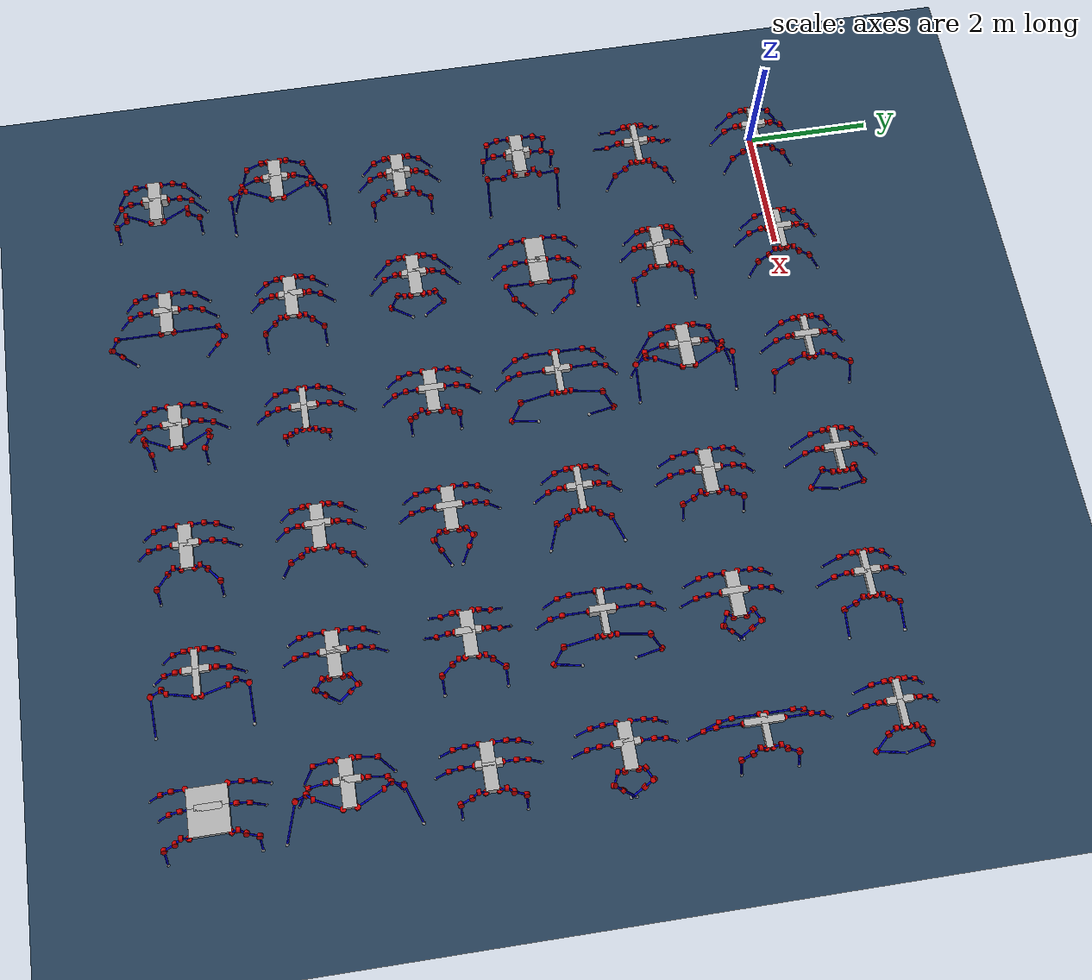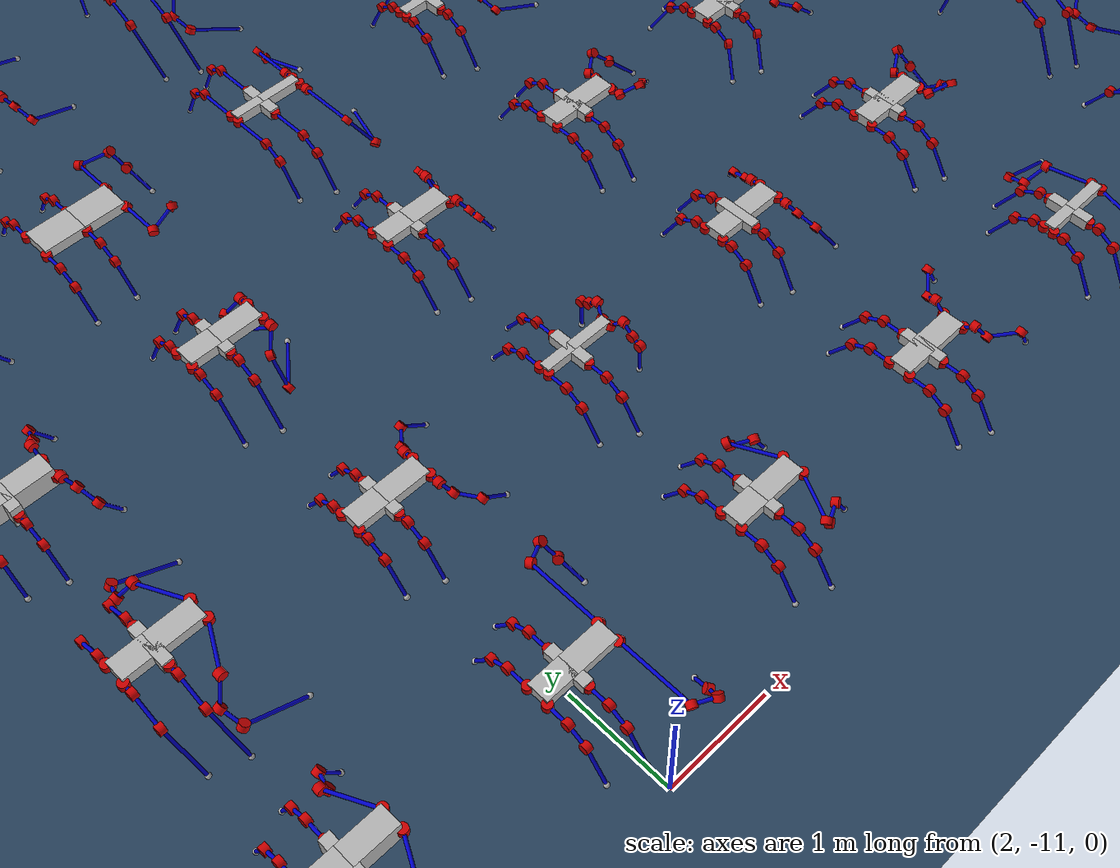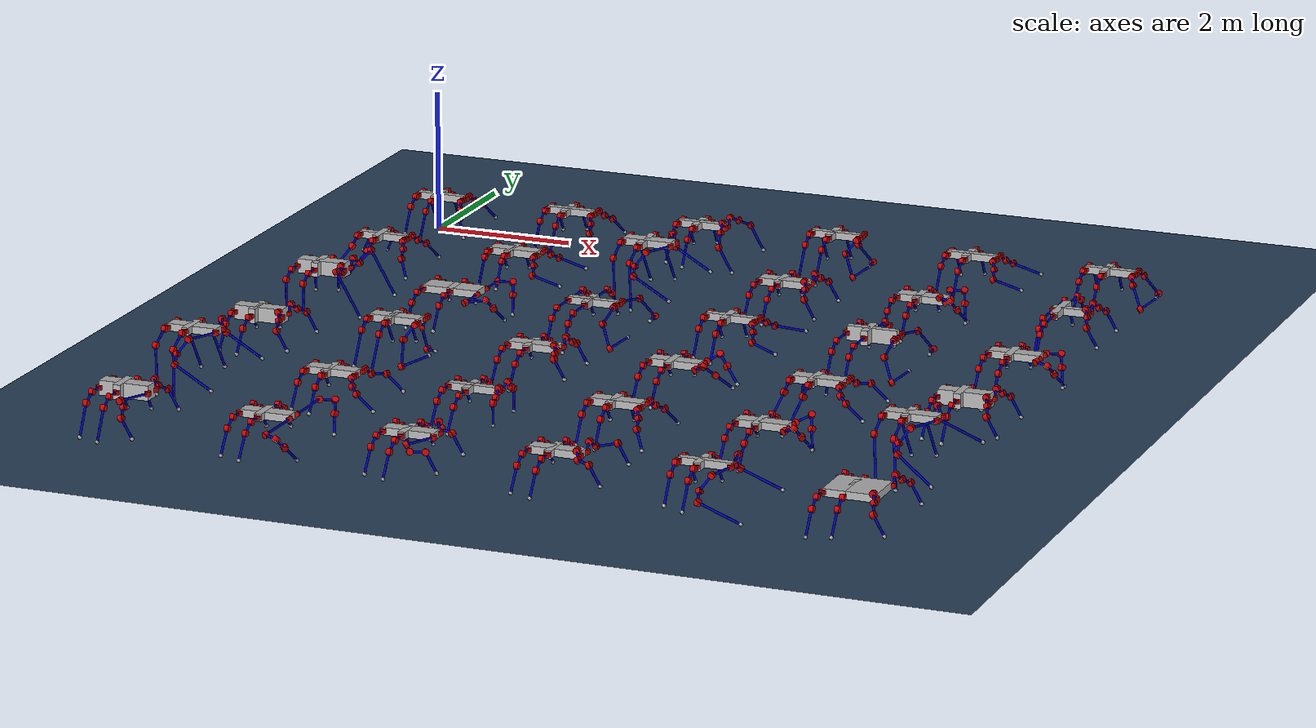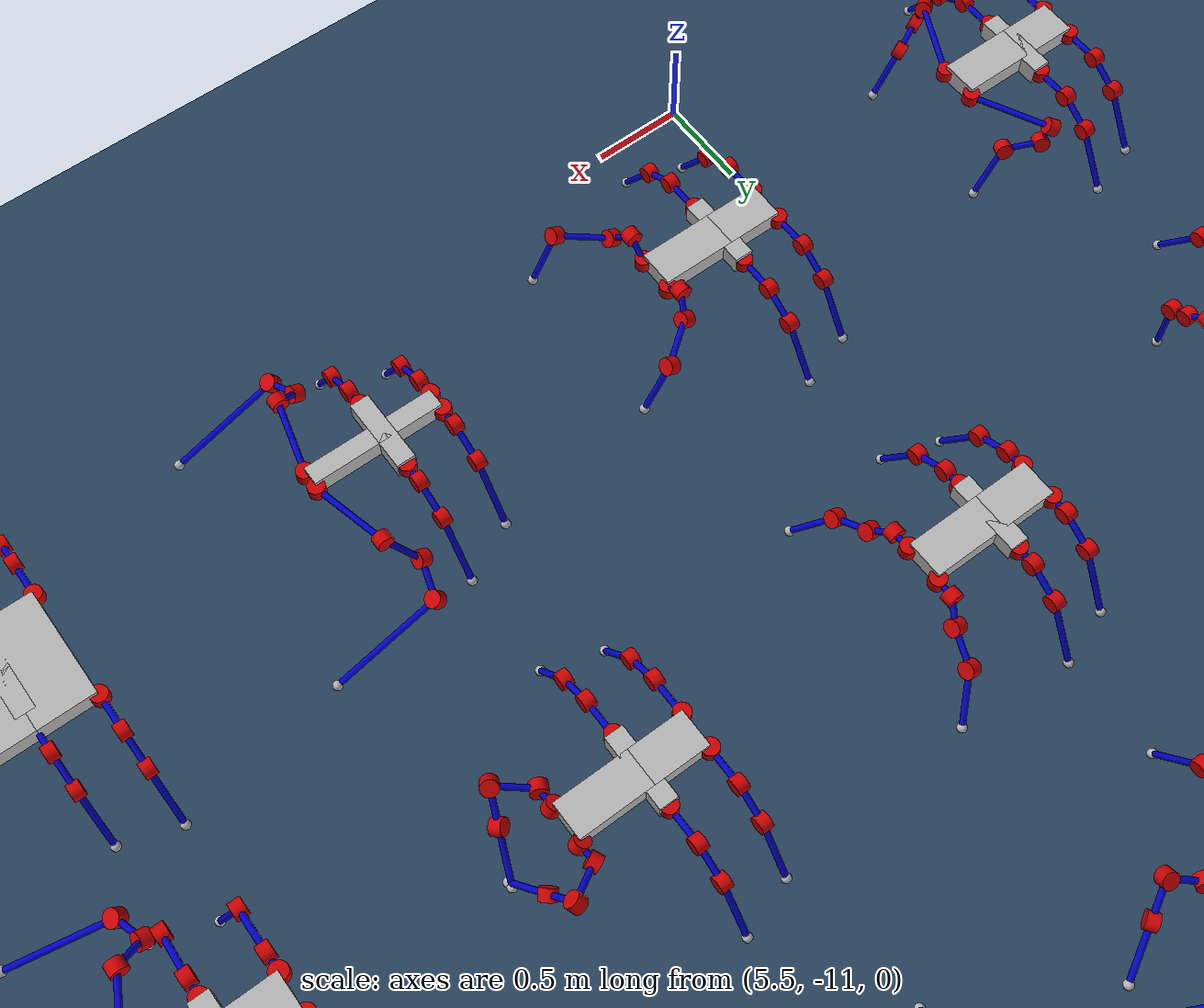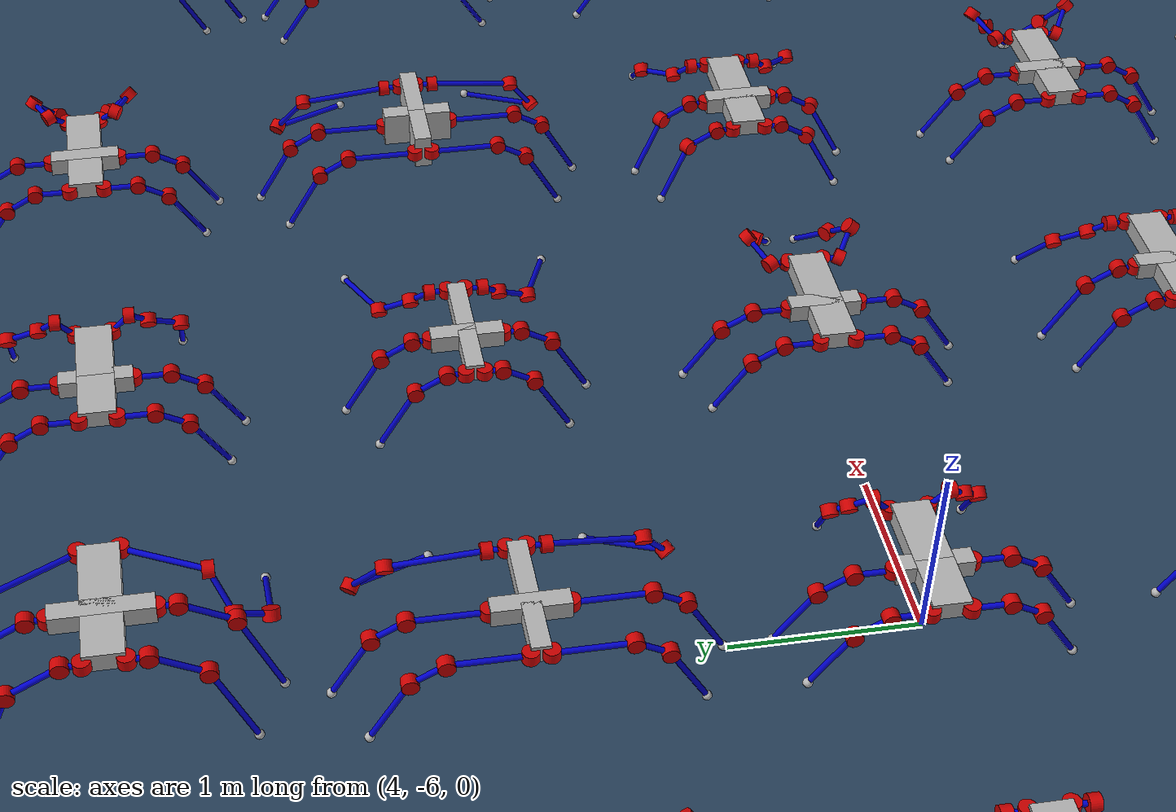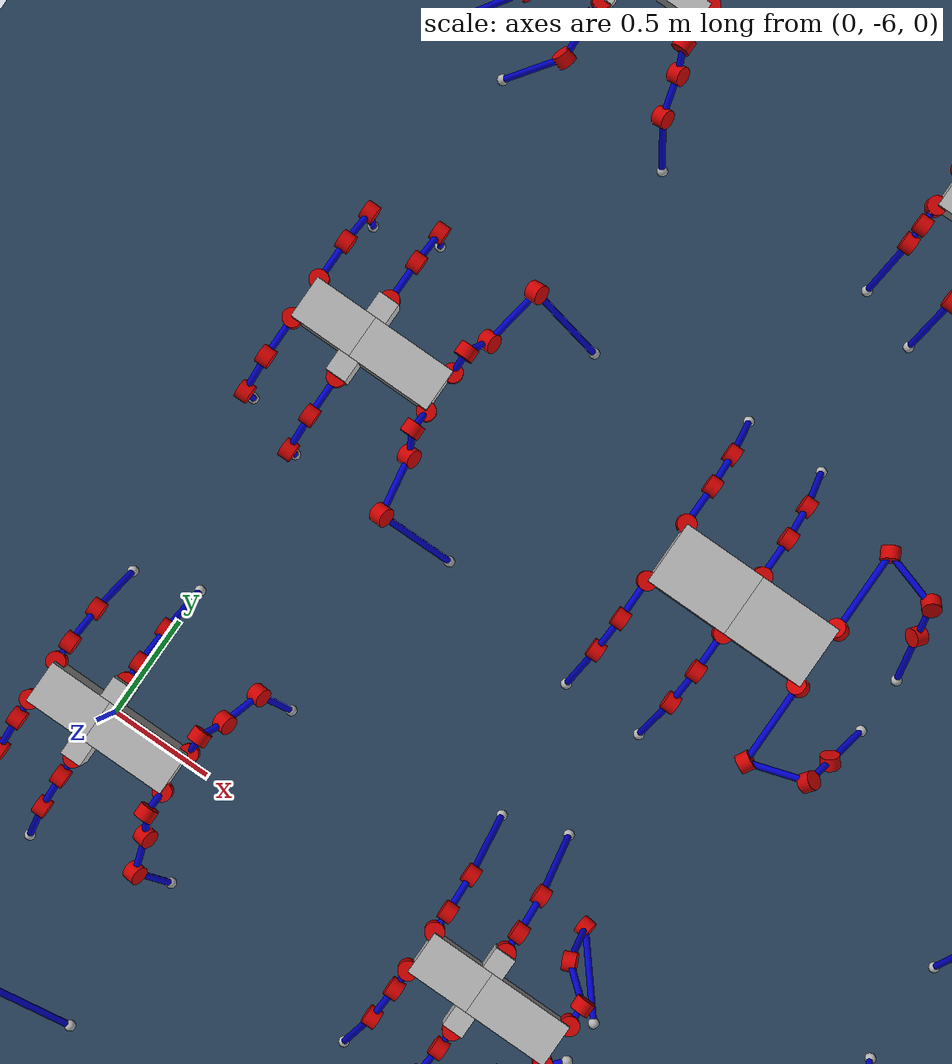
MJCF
<mujoco model="newhex_heterogeneous_grid">
  <compiler angle="radian"/>

  <visual>
    <global offwidth="3840" offheight="2160"/>
    <rgba haze="0.15 0.25 0.35 1"/>
  </visual>

  <default>
    <default class="floor">
      <geom size="0 0 0.05" type="plane" material="groundplane"/>
    </default>
    <default class="g017_o028/main">
      <default class="g017_o028/robot">
        <joint armature="0.01" damping="2" frictionloss="0.2"/>
        <default class="g017_o028/visual">
          <geom contype="0" conaffinity="0" group="2"/>
        </default>
        <default class="g017_o028/collision">
          <geom contype="0" group="3"/>
        </default>
      </default>
      <default class="g017_o028/floor">
        <geom size="0 0 0.05" type="plane" material="groundplane"/>
      </default>
    </default>
    <default class="g033_o017/main">
      <default class="g033_o017/robot">
        <joint armature="0.01" damping="2" frictionloss="0.2"/>
        <default class="g033_o017/visual">
          <geom contype="0" conaffinity="0" group="2"/>
        </default>
        <default class="g033_o017/collision">
          <geom contype="0" group="3"/>
        </default>
      </default>
      <default class="g033_o017/floor">
        <geom size="0 0 0.05" type="plane" material="groundplane"/>
      </default>
    </default>
    <default class="g046_o031/main">
      <default class="g046_o031/robot">
        <joint armature="0.01" damping="2" frictionloss="0.2"/>
        <default class="g046_o031/visual">
          <geom contype="0" conaffinity="0" group="2"/>
        </default>
        <default class="g046_o031/collision">
          <geom contype="0" group="3"/>
        </default>
      </default>
      <default class="g046_o031/floor">
        <geom size="0 0 0.05" type="plane" material="groundplane"/>
      </default>
    </default>
    <default class="g036_o039/main">
      <default class="g036_o039/robot">
        <joint armature="0.01" damping="2" frictionloss="0.2"/>
        <default class="g036_o039/visual">
          <geom contype="0" conaffinity="0" group="2"/>
        </default>
        <default class="g036_o039/collision">
          <geom contype="0" group="3"/>
        </default>
      </default>
      <default class="g036_o039/floor">
        <geom size="0 0 0.05" type="plane" material="groundplane"/>
      </default>
    </default>
    <default class="g008_o003/main">
      <default class="g008_o003/robot">
        <joint armature="0.01" damping="2" frictionloss="0.2"/>
        <default class="g008_o003/visual">
          <geom contype="0" conaffinity="0" group="2"/>
        </default>
        <default class="g008_o003/collision">
          <geom contype="0" group="3"/>
        </default>
      </default>
      <default class="g008_o003/floor">
        <geom size="0 0 0.05" type="plane" material="groundplane"/>
      </default>
    </default>
    <default class="g029_o033/main">
      <default class="g029_o033/robot">
        <joint armature="0.01" damping="2" frictionloss="0.2"/>
        <default class="g029_o033/visual">
          <geom contype="0" conaffinity="0" group="2"/>
        </default>
        <default class="g029_o033/collision">
          <geom contype="0" group="3"/>
        </default>
      </default>
      <default class="g029_o033/floor">
        <geom size="0 0 0.05" type="plane" material="groundplane"/>
      </default>
    </default>
    <default class="g043_o047/main">
      <default class="g043_o047/robot">
        <joint armature="0.01" damping="2" frictionloss="0.2"/>
        <default class="g043_o047/visual">
          <geom contype="0" conaffinity="0" group="2"/>
        </default>
        <default class="g043_o047/collision">
          <geom contype="0" group="3"/>
        </default>
      </default>
      <default class="g043_o047/floor">
        <geom size="0 0 0.05" type="plane" material="groundplane"/>
      </default>
    </default>
    <default class="g043_o044/main">
      <default class="g043_o044/robot">
        <joint armature="0.01" damping="2" frictionloss="0.2"/>
        <default class="g043_o044/visual">
          <geom contype="0" conaffinity="0" group="2"/>
        </default>
        <default class="g043_o044/collision">
          <geom contype="0" group="3"/>
        </default>
      </default>
      <default class="g043_o044/floor">
        <geom size="0 0 0.05" type="plane" material="groundplane"/>
      </default>
    </default>
    <default class="g036_o023/main">
      <default class="g036_o023/robot">
        <joint armature="0.01" damping="2" frictionloss="0.2"/>
        <default class="g036_o023/visual">
          <geom contype="0" conaffinity="0" group="2"/>
        </default>
        <default class="g036_o023/collision">
          <geom contype="0" group="3"/>
        </default>
      </default>
      <default class="g036_o023/floor">
        <geom size="0 0 0.05" type="plane" material="groundplane"/>
      </default>
    </default>
    <default class="g004_o008/main">
      <default class="g004_o008/robot">
        <joint armature="0.01" damping="2" frictionloss="0.2"/>
        <default class="g004_o008/visual">
          <geom contype="0" conaffinity="0" group="2"/>
        </default>
        <default class="g004_o008/collision">
          <geom contype="0" group="3"/>
        </default>
      </default>
      <default class="g004_o008/floor">
        <geom size="0 0 0.05" type="plane" material="groundplane"/>
      </default>
    </default>
    <default class="g014_o036/main">
      <default class="g014_o036/robot">
        <joint armature="0.01" damping="2" frictionloss="0.2"/>
        <default class="g014_o036/visual">
          <geom contype="0" conaffinity="0" group="2"/>
        </default>
        <default class="g014_o036/collision">
          <geom contype="0" group="3"/>
        </default>
      </default>
      <default class="g014_o036/floor">
        <geom size="0 0 0.05" type="plane" material="groundplane"/>
      </default>
    </default>
    <default class="g040_o006/main">
      <default class="g040_o006/robot">
        <joint armature="0.01" damping="2" frictionloss="0.2"/>
        <default class="g040_o006/visual">
          <geom contype="0" conaffinity="0" group="2"/>
        </default>
        <default class="g040_o006/collision">
          <geom contype="0" group="3"/>
        </default>
      </default>
      <default class="g040_o006/floor">
        <geom size="0 0 0.05" type="plane" material="groundplane"/>
      </default>
    </default>
    <default class="g046_o016/main">
      <default class="g046_o016/robot">
        <joint armature="0.01" damping="2" frictionloss="0.2"/>
        <default class="g046_o016/visual">
          <geom contype="0" conaffinity="0" group="2"/>
        </default>
        <default class="g046_o016/collision">
          <geom contype="0" group="3"/>
        </default>
      </default>
      <default class="g046_o016/floor">
        <geom size="0 0 0.05" type="plane" material="groundplane"/>
      </default>
    </default>
    <default class="g020_o026/main">
      <default class="g020_o026/robot">
        <joint armature="0.01" damping="2" frictionloss="0.2"/>
        <default class="g020_o026/visual">
          <geom contype="0" conaffinity="0" group="2"/>
        </default>
        <default class="g020_o026/collision">
          <geom contype="0" group="3"/>
        </default>
      </default>
      <default class="g020_o026/floor">
        <geom size="0 0 0.05" type="plane" material="groundplane"/>
      </default>
    </default>
    <default class="g033_o033/main">
      <default class="g033_o033/robot">
        <joint armature="0.01" damping="2" frictionloss="0.2"/>
        <default class="g033_o033/visual">
          <geom contype="0" conaffinity="0" group="2"/>
        </default>
        <default class="g033_o033/collision">
          <geom contype="0" group="3"/>
        </default>
      </default>
      <default class="g033_o033/floor">
        <geom size="0 0 0.05" type="plane" material="groundplane"/>
      </default>
    </default>
    <default class="g009_o005/main">
      <default class="g009_o005/robot">
        <joint armature="0.01" damping="2" frictionloss="0.2"/>
        <default class="g009_o005/visual">
          <geom contype="0" conaffinity="0" group="2"/>
        </default>
        <default class="g009_o005/collision">
          <geom contype="0" group="3"/>
        </default>
      </default>
      <default class="g009_o005/floor">
        <geom size="0 0 0.05" type="plane" material="groundplane"/>
      </default>
    </default>
    <default class="g043_o037/main">
      <default class="g043_o037/robot">
        <joint armature="0.01" damping="2" frictionloss="0.2"/>
        <default class="g043_o037/visual">
          <geom contype="0" conaffinity="0" group="2"/>
        </default>
        <default class="g043_o037/collision">
          <geom contype="0" group="3"/>
        </default>
      </default>
      <default class="g043_o037/floor">
        <geom size="0 0 0.05" type="plane" material="groundplane"/>
      </default>
    </default>
    <default class="g008_o022/main">
      <default class="g008_o022/robot">
        <joint armature="0.01" damping="2" frictionloss="0.2"/>
        <default class="g008_o022/visual">
          <geom contype="0" conaffinity="0" group="2"/>
        </default>
        <default class="g008_o022/collision">
          <geom contype="0" group="3"/>
        </default>
      </default>
      <default class="g008_o022/floor">
        <geom size="0 0 0.05" type="plane" material="groundplane"/>
      </default>
    </default>
    <default class="g011_o028/main">
      <default class="g011_o028/robot">
        <joint armature="0.01" damping="2" frictionloss="0.2"/>
        <default class="g011_o028/visual">
          <geom contype="0" conaffinity="0" group="2"/>
        </default>
        <default class="g011_o028/collision">
          <geom contype="0" group="3"/>
        </default>
      </default>
      <default class="g011_o028/floor">
        <geom size="0 0 0.05" type="plane" material="groundplane"/>
      </default>
    </default>
    <default class="g042_o038/main">
      <default class="g042_o038/robot">
        <joint armature="0.01" damping="2" frictionloss="0.2"/>
        <default class="g042_o038/visual">
          <geom contype="0" conaffinity="0" group="2"/>
        </default>
        <default class="g042_o038/collision">
          <geom contype="0" group="3"/>
        </default>
      </default>
      <default class="g042_o038/floor">
        <geom size="0 0 0.05" type="plane" material="groundplane"/>
      </default>
    </default>
    <default class="g015_o014/main">
      <default class="g015_o014/robot">
        <joint armature="0.01" damping="2" frictionloss="0.2"/>
        <default class="g015_o014/visual">
          <geom contype="0" conaffinity="0" group="2"/>
        </default>
        <default class="g015_o014/collision">
          <geom contype="0" group="3"/>
        </default>
      </default>
      <default class="g015_o014/floor">
        <geom size="0 0 0.05" type="plane" material="groundplane"/>
      </default>
    </default>
    <default class="g007_o027/main">
      <default class="g007_o027/robot">
        <joint armature="0.01" damping="2" frictionloss="0.2"/>
        <default class="g007_o027/visual">
          <geom contype="0" conaffinity="0" group="2"/>
        </default>
        <default class="g007_o027/collision">
          <geom contype="0" group="3"/>
        </default>
      </default>
      <default class="g007_o027/floor">
        <geom size="0 0 0.05" type="plane" material="groundplane"/>
      </default>
    </default>
    <default class="g012_o030/main">
      <default class="g012_o030/robot">
        <joint armature="0.01" damping="2" frictionloss="0.2"/>
        <default class="g012_o030/visual">
          <geom contype="0" conaffinity="0" group="2"/>
        </default>
        <default class="g012_o030/collision">
          <geom contype="0" group="3"/>
        </default>
      </default>
      <default class="g012_o030/floor">
        <geom size="0 0 0.05" type="plane" material="groundplane"/>
      </default>
    </default>
    <default class="g007_o045/main">
      <default class="g007_o045/robot">
        <joint armature="0.01" damping="2" frictionloss="0.2"/>
        <default class="g007_o045/visual">
          <geom contype="0" conaffinity="0" group="2"/>
        </default>
        <default class="g007_o045/collision">
          <geom contype="0" group="3"/>
        </default>
      </default>
      <default class="g007_o045/floor">
        <geom size="0 0 0.05" type="plane" material="groundplane"/>
      </default>
    </default>
    <default class="g035_o012/main">
      <default class="g035_o012/robot">
        <joint armature="0.01" damping="2" frictionloss="0.2"/>
        <default class="g035_o012/visual">
          <geom contype="0" conaffinity="0" group="2"/>
        </default>
        <default class="g035_o012/collision">
          <geom contype="0" group="3"/>
        </default>
      </default>
      <default class="g035_o012/floor">
        <geom size="0 0 0.05" type="plane" material="groundplane"/>
      </default>
    </default>
    <default class="g009_o033/main">
      <default class="g009_o033/robot">
        <joint armature="0.01" damping="2" frictionloss="0.2"/>
        <default class="g009_o033/visual">
          <geom contype="0" conaffinity="0" group="2"/>
        </default>
        <default class="g009_o033/collision">
          <geom contype="0" group="3"/>
        </default>
      </default>
      <default class="g009_o033/floor">
        <geom size="0 0 0.05" type="plane" material="groundplane"/>
      </default>
    </default>
    <default class="g017_o007/main">
      <default class="g017_o007/robot">
        <joint armature="0.01" damping="2" frictionloss="0.2"/>
        <default class="g017_o007/visual">
          <geom contype="0" conaffinity="0" group="2"/>
        </default>
        <default class="g017_o007/collision">
          <geom contype="0" group="3"/>
        </default>
      </default>
      <default class="g017_o007/floor">
        <geom size="0 0 0.05" type="plane" material="groundplane"/>
      </default>
    </default>
    <default class="g039_o030/main">
      <default class="g039_o030/robot">
        <joint armature="0.01" damping="2" frictionloss="0.2"/>
        <default class="g039_o030/visual">
          <geom contype="0" conaffinity="0" group="2"/>
        </default>
        <default class="g039_o030/collision">
          <geom contype="0" group="3"/>
        </default>
      </default>
      <default class="g039_o030/floor">
        <geom size="0 0 0.05" type="plane" material="groundplane"/>
      </default>
    </default>
    <default class="g014_o046/main">
      <default class="g014_o046/robot">
        <joint armature="0.01" damping="2" frictionloss="0.2"/>
        <default class="g014_o046/visual">
          <geom contype="0" conaffinity="0" group="2"/>
        </default>
        <default class="g014_o046/collision">
          <geom contype="0" group="3"/>
        </default>
      </default>
      <default class="g014_o046/floor">
        <geom size="0 0 0.05" type="plane" material="groundplane"/>
      </default>
    </default>
    <default class="g038_o001/main">
      <default class="g038_o001/robot">
        <joint armature="0.01" damping="2" frictionloss="0.2"/>
        <default class="g038_o001/visual">
          <geom contype="0" conaffinity="0" group="2"/>
        </default>
        <default class="g038_o001/collision">
          <geom contype="0" group="3"/>
        </default>
      </default>
      <default class="g038_o001/floor">
        <geom size="0 0 0.05" type="plane" material="groundplane"/>
      </default>
    </default>
    <default class="g018_o019/main">
      <default class="g018_o019/robot">
        <joint armature="0.01" damping="2" frictionloss="0.2"/>
        <default class="g018_o019/visual">
          <geom contype="0" conaffinity="0" group="2"/>
        </default>
        <default class="g018_o019/collision">
          <geom contype="0" group="3"/>
        </default>
      </default>
      <default class="g018_o019/floor">
        <geom size="0 0 0.05" type="plane" material="groundplane"/>
      </default>
    </default>
    <default class="g014_o026/main">
      <default class="g014_o026/robot">
        <joint armature="0.01" damping="2" frictionloss="0.2"/>
        <default class="g014_o026/visual">
          <geom contype="0" conaffinity="0" group="2"/>
        </default>
        <default class="g014_o026/collision">
          <geom contype="0" group="3"/>
        </default>
      </default>
      <default class="g014_o026/floor">
        <geom size="0 0 0.05" type="plane" material="groundplane"/>
      </default>
    </default>
    <default class="g017_o045/main">
      <default class="g017_o045/robot">
        <joint armature="0.01" damping="2" frictionloss="0.2"/>
        <default class="g017_o045/visual">
          <geom contype="0" conaffinity="0" group="2"/>
        </default>
        <default class="g017_o045/collision">
          <geom contype="0" group="3"/>
        </default>
      </default>
      <default class="g017_o045/floor">
        <geom size="0 0 0.05" type="plane" material="groundplane"/>
      </default>
    </default>
    <default class="g008_o038/main">
      <default class="g008_o038/robot">
        <joint armature="0.01" damping="2" frictionloss="0.2"/>
        <default class="g008_o038/visual">
          <geom contype="0" conaffinity="0" group="2"/>
        </default>
        <default class="g008_o038/collision">
          <geom contype="0" group="3"/>
        </default>
      </default>
      <default class="g008_o038/floor">
        <geom size="0 0 0.05" type="plane" material="groundplane"/>
      </default>
    </default>
    <default class="g039_o023/main">
      <default class="g039_o023/robot">
        <joint armature="0.01" damping="2" frictionloss="0.2"/>
        <default class="g039_o023/visual">
          <geom contype="0" conaffinity="0" group="2"/>
        </default>
        <default class="g039_o023/collision">
          <geom contype="0" group="3"/>
        </default>
      </default>
      <default class="g039_o023/floor">
        <geom size="0 0 0.05" type="plane" material="groundplane"/>
      </default>
    </default>
    <default class="g013_o003/main">
      <default class="g013_o003/robot">
        <joint armature="0.01" damping="2" frictionloss="0.2"/>
        <default class="g013_o003/visual">
          <geom contype="0" conaffinity="0" group="2"/>
        </default>
        <default class="g013_o003/collision">
          <geom contype="0" group="3"/>
        </default>
      </default>
      <default class="g013_o003/floor">
        <geom size="0 0 0.05" type="plane" material="groundplane"/>
      </default>
    </default>
  </default>

  <asset>
    <texture type="2d" colorspace="sRGB" name="groundplane" builtin="checker" mark="edge" rgb1="0.2 0.3 0.4" rgb2="0.1 0.2 0.3" markrgb="0.8 0.8 0.8" width="300" height="300"/>
    <material name="groundplane" texture="groundplane" texuniform="true" texrepeat="10 10" reflectance="0.2"/>
    <material name="g017_o028/blue" rgba="0 0 0.8 1"/>
    <material name="g017_o028/red" rgba="0.8 0 0 1"/>
    <material name="g017_o028/grey" rgba="0.7 0.7 0.7 1"/>
    <material name="g033_o017/blue" rgba="0 0 0.8 1"/>
    <material name="g033_o017/red" rgba="0.8 0 0 1"/>
    <material name="g033_o017/grey" rgba="0.7 0.7 0.7 1"/>
    <material name="g046_o031/blue" rgba="0 0 0.8 1"/>
    <material name="g046_o031/red" rgba="0.8 0 0 1"/>
    <material name="g046_o031/grey" rgba="0.7 0.7 0.7 1"/>
    <material name="g036_o039/blue" rgba="0 0 0.8 1"/>
    <material name="g036_o039/red" rgba="0.8 0 0 1"/>
    <material name="g036_o039/grey" rgba="0.7 0.7 0.7 1"/>
    <material name="g008_o003/blue" rgba="0 0 0.8 1"/>
    <material name="g008_o003/red" rgba="0.8 0 0 1"/>
    <material name="g008_o003/grey" rgba="0.7 0.7 0.7 1"/>
    <material name="g029_o033/blue" rgba="0 0 0.8 1"/>
    <material name="g029_o033/red" rgba="0.8 0 0 1"/>
    <material name="g029_o033/grey" rgba="0.7 0.7 0.7 1"/>
    <material name="g043_o047/blue" rgba="0 0 0.8 1"/>
    <material name="g043_o047/red" rgba="0.8 0 0 1"/>
    <material name="g043_o047/grey" rgba="0.7 0.7 0.7 1"/>
    <material name="g043_o044/blue" rgba="0 0 0.8 1"/>
    <material name="g043_o044/red" rgba="0.8 0 0 1"/>
    <material name="g043_o044/grey" rgba="0.7 0.7 0.7 1"/>
    <material name="g036_o023/blue" rgba="0 0 0.8 1"/>
    <material name="g036_o023/red" rgba="0.8 0 0 1"/>
    <material name="g036_o023/grey" rgba="0.7 0.7 0.7 1"/>
    <material name="g004_o008/blue" rgba="0 0 0.8 1"/>
    <material name="g004_o008/red" rgba="0.8 0 0 1"/>
    <material name="g004_o008/grey" rgba="0.7 0.7 0.7 1"/>
    <material name="g014_o036/blue" rgba="0 0 0.8 1"/>
    <material name="g014_o036/red" rgba="0.8 0 0 1"/>
    <material name="g014_o036/grey" rgba="0.7 0.7 0.7 1"/>
    <material name="g040_o006/blue" rgba="0 0 0.8 1"/>
    <material name="g040_o006/red" rgba="0.8 0 0 1"/>
    <material name="g040_o006/grey" rgba="0.7 0.7 0.7 1"/>
    <material name="g046_o016/blue" rgba="0 0 0.8 1"/>
    <material name="g046_o016/red" rgba="0.8 0 0 1"/>
    <material name="g046_o016/grey" rgba="0.7 0.7 0.7 1"/>
    <material name="g020_o026/blue" rgba="0 0 0.8 1"/>
    <material name="g020_o026/red" rgba="0.8 0 0 1"/>
    <material name="g020_o026/grey" rgba="0.7 0.7 0.7 1"/>
    <material name="g033_o033/blue" rgba="0 0 0.8 1"/>
    <material name="g033_o033/red" rgba="0.8 0 0 1"/>
    <material name="g033_o033/grey" rgba="0.7 0.7 0.7 1"/>
    <material name="g009_o005/blue" rgba="0 0 0.8 1"/>
    <material name="g009_o005/red" rgba="0.8 0 0 1"/>
    <material name="g009_o005/grey" rgba="0.7 0.7 0.7 1"/>
    <material name="g043_o037/blue" rgba="0 0 0.8 1"/>
    <material name="g043_o037/red" rgba="0.8 0 0 1"/>
    <material name="g043_o037/grey" rgba="0.7 0.7 0.7 1"/>
    <material name="g008_o022/blue" rgba="0 0 0.8 1"/>
    <material name="g008_o022/red" rgba="0.8 0 0 1"/>
    <material name="g008_o022/grey" rgba="0.7 0.7 0.7 1"/>
    <material name="g011_o028/blue" rgba="0 0 0.8 1"/>
    <material name="g011_o028/red" rgba="0.8 0 0 1"/>
    <material name="g011_o028/grey" rgba="0.7 0.7 0.7 1"/>
    <material name="g042_o038/blue" rgba="0 0 0.8 1"/>
    <material name="g042_o038/red" rgba="0.8 0 0 1"/>
    <material name="g042_o038/grey" rgba="0.7 0.7 0.7 1"/>
    <material name="g015_o014/blue" rgba="0 0 0.8 1"/>
    <material name="g015_o014/red" rgba="0.8 0 0 1"/>
    <material name="g015_o014/grey" rgba="0.7 0.7 0.7 1"/>
    <material name="g007_o027/blue" rgba="0 0 0.8 1"/>
    <material name="g007_o027/red" rgba="0.8 0 0 1"/>
    <material name="g007_o027/grey" rgba="0.7 0.7 0.7 1"/>
    <material name="g012_o030/blue" rgba="0 0 0.8 1"/>
    <material name="g012_o030/red" rgba="0.8 0 0 1"/>
    <material name="g012_o030/grey" rgba="0.7 0.7 0.7 1"/>
    <material name="g007_o045/blue" rgba="0 0 0.8 1"/>
    <material name="g007_o045/red" rgba="0.8 0 0 1"/>
    <material name="g007_o045/grey" rgba="0.7 0.7 0.7 1"/>
    <material name="g035_o012/blue" rgba="0 0 0.8 1"/>
    <material name="g035_o012/red" rgba="0.8 0 0 1"/>
    <material name="g035_o012/grey" rgba="0.7 0.7 0.7 1"/>
    <material name="g009_o033/blue" rgba="0 0 0.8 1"/>
    <material name="g009_o033/red" rgba="0.8 0 0 1"/>
    <material name="g009_o033/grey" rgba="0.7 0.7 0.7 1"/>
    <material name="g017_o007/blue" rgba="0 0 0.8 1"/>
    <material name="g017_o007/red" rgba="0.8 0 0 1"/>
    <material name="g017_o007/grey" rgba="0.7 0.7 0.7 1"/>
    <material name="g039_o030/blue" rgba="0 0 0.8 1"/>
    <material name="g039_o030/red" rgba="0.8 0 0 1"/>
    <material name="g039_o030/grey" rgba="0.7 0.7 0.7 1"/>
    <material name="g014_o046/blue" rgba="0 0 0.8 1"/>
    <material name="g014_o046/red" rgba="0.8 0 0 1"/>
    <material name="g014_o046/grey" rgba="0.7 0.7 0.7 1"/>
    <material name="g038_o001/blue" rgba="0 0 0.8 1"/>
    <material name="g038_o001/red" rgba="0.8 0 0 1"/>
    <material name="g038_o001/grey" rgba="0.7 0.7 0.7 1"/>
    <material name="g018_o019/blue" rgba="0 0 0.8 1"/>
    <material name="g018_o019/red" rgba="0.8 0 0 1"/>
    <material name="g018_o019/grey" rgba="0.7 0.7 0.7 1"/>
    <material name="g014_o026/blue" rgba="0 0 0.8 1"/>
    <material name="g014_o026/red" rgba="0.8 0 0 1"/>
    <material name="g014_o026/grey" rgba="0.7 0.7 0.7 1"/>
    <material name="g017_o045/blue" rgba="0 0 0.8 1"/>
    <material name="g017_o045/red" rgba="0.8 0 0 1"/>
    <material name="g017_o045/grey" rgba="0.7 0.7 0.7 1"/>
    <material name="g008_o038/blue" rgba="0 0 0.8 1"/>
    <material name="g008_o038/red" rgba="0.8 0 0 1"/>
    <material name="g008_o038/grey" rgba="0.7 0.7 0.7 1"/>
    <material name="g039_o023/blue" rgba="0 0 0.8 1"/>
    <material name="g039_o023/red" rgba="0.8 0 0 1"/>
    <material name="g039_o023/grey" rgba="0.7 0.7 0.7 1"/>
    <material name="g013_o003/blue" rgba="0 0 0.8 1"/>
    <material name="g013_o003/red" rgba="0.8 0 0 1"/>
    <material name="g013_o003/grey" rgba="0.7 0.7 0.7 1"/>
  </asset>

  <worldbody>
    <geom name="floor" class="floor"/>
    <light pos="0 0 5" dir="0 0 -1" type="directional"/>
    <body name="g017_o028/base_link" childclass="g017_o028/robot" pos="0 0 0.4713">
      <inertial pos="0 0 0" mass="14.2" diaginertia="0.0166667 0.0166667 0.0166667"/>
      <joint name="g017_o028/floating_base" type="free" armature="0" damping="0" frictionloss="0"/>
      <geom name="g017_o028/base_link_collision_0" class="g017_o028/collision" size="0.2 0.05 0.05" pos="0.2 0 0" type="box"/>
      <geom name="g017_o028/base_link_collision_1" class="g017_o028/collision" size="0.15 0.05 0.05" pos="-0.15 0 0" type="box"/>
      <geom name="g017_o028/base_link_collision_2" class="g017_o028/collision" size="0.05 0.2 0.05" type="box"/>
      <geom name="g017_o028/base_link_visual_0" class="g017_o028/visual" size="0.2 0.05 0.05" pos="0.2 0 0" type="box" material="g017_o028/grey"/>
      <geom name="g017_o028/base_link_visual_1" class="g017_o028/visual" size="0.15 0.05 0.05" pos="-0.15 0 0" type="box" material="g017_o028/grey"/>
      <geom name="g017_o028/base_link_visual_2" class="g017_o028/visual" size="0.05 0.2 0.05" type="box" material="g017_o028/grey"/>
      <site name="g017_o028/imu" pos="0 0 0" size="0.01" rgba="1 0 0 1"/>
      <body name="g017_o028/LF_link1" pos="0.4 0.05 0" quat="0.707407 0 0 0.706807">
        <inertial pos="0 0 0" mass="1" diaginertia="0.000968 0.000968 0.000784"/>
        <joint name="g017_o028/LF_joint1" pos="0 0 0" axis="0 0 1" range="-6.28 6.28"/>
        <geom name="g017_o028/LF_link1_collision" class="g017_o028/collision" size="0.015 0.05" pos="0.05 0 0" quat="0.707107 0 0.707107 0" type="cylinder"/>
        <geom name="g017_o028/LF_link1_visual_0" class="g017_o028/visual" size="0.044 0.03" type="cylinder" material="g017_o028/red"/>
        <geom name="g017_o028/LF_link1_visual_1" class="g017_o028/visual" size="0.015 0.05" pos="0.05 0 0" quat="0.707107 0 0.707107 0" type="cylinder" material="g017_o028/blue"/>
        <body name="g017_o028/LF_link2" pos="0.1 0 0" quat="0.682975 -0.182593 0.683275 -0.182593">
          <inertial pos="0 0 0" mass="1.08284" diaginertia="0.000968 0.000968 0.000784"/>
          <joint name="g017_o028/LF_joint2" pos="0 0 0" axis="0 0 1" range="-6.28 6.28"/>
          <geom name="g017_o028/LF_link2_collision" class="g017_o028/collision" size="0.015 0.0707105" pos="0.05 0 0.05" quat="0.923877 0 0.38269 0" type="cylinder"/>
          <geom name="g017_o028/LF_link2_visual_0" class="g017_o028/visual" size="0.044 0.03" type="cylinder" material="g017_o028/red"/>
          <geom name="g017_o028/LF_link2_visual_1" class="g017_o028/visual" size="0.015 0.0707105" pos="0.05 0 0.05" quat="0.923877 0 0.38269 0" type="cylinder" material="g017_o028/blue"/>
          <body name="g017_o028/LF_link3" pos="0.1 0 0.1" quat="0.612708 0.612208 -0.353505 0.353305">
            <inertial pos="0 0 0" mass="1.2" diaginertia="0.000968 0.000968 0.000784"/>
            <joint name="g017_o028/LF_joint3" pos="0 0 0" axis="0 0 1" range="-6.28 6.28"/>
            <geom name="g017_o028/LF_link3_collision" class="g017_o028/collision" size="0.015 0.1" pos="0.1 0 0" quat="0.707107 0 0.707107 0" type="cylinder"/>
            <geom name="g017_o028/LF_link3_visual_0" class="g017_o028/visual" size="0.044 0.03" type="cylinder" material="g017_o028/red"/>
            <geom name="g017_o028/LF_link3_visual_1" class="g017_o028/visual" size="0.015 0.1" pos="0.1 0 0" quat="0.707107 0 0.707107 0" type="cylinder" material="g017_o028/blue"/>
            <body name="g017_o028/LF_link4" pos="0.2 0 0" quat="0.965961 0 0 -0.258689">
              <inertial pos="0 0 0" mass="1.4" diaginertia="0.000968 0.000968 0.000784"/>
              <joint name="g017_o028/LF_joint4" pos="0 0 0" axis="0 0 1" range="-6.28 6.28"/>
              <geom name="g017_o028/LF_link4_collision" class="g017_o028/collision" size="0.015 0.15" pos="0.15 0 0" quat="0.707107 0 0.707107 0" type="cylinder"/>
              <geom name="g017_o028/LF_link4_visual_0" class="g017_o028/visual" size="0.044 0.03" type="cylinder" material="g017_o028/red"/>
              <geom name="g017_o028/LF_link4_visual_1" class="g017_o028/visual" size="0.015 0.15" pos="0.15 0 0" quat="0.707107 0 0.707107 0" type="cylinder" material="g017_o028/blue"/>
              <body name="g017_o028/LF_foot_link" pos="0.3 0 0">
                <inertial pos="0 0 0" mass="0.05" diaginertia="1.25e-05 1.25e-05 1.25e-05"/>
                <geom name="g017_o028/LF_foot_link_collision" class="g017_o028/collision" size="0.025"/>
                <geom name="g017_o028/LF_foot_link_visual" class="g017_o028/visual" size="0.025" material="g017_o028/grey"/>
                <site name="g017_o028/LF_touch_site" pos="0 0 0" size="0.01" rgba="0 0 0 0"/>
              </body>
            </body>
          </body>
        </body>
      </body>
      <body name="g017_o028/LM_link1" pos="0 0.2 0" quat="0.707407 0 0 0.706807">
        <inertial pos="0 0 0" mass="1" diaginertia="0.000968 0.000968 0.000784"/>
        <joint name="g017_o028/LM_joint1" pos="0 0 0" axis="0 0 1" range="-6.28 6.28"/>
        <geom name="g017_o028/LM_link1_collision" class="g017_o028/collision" size="0.015 0.05" pos="0.05 0 0" quat="0.707107 0 0.707107 0" type="cylinder"/>
        <geom name="g017_o028/LM_link1_visual_0" class="g017_o028/visual" size="0.044 0.03" type="cylinder" material="g017_o028/red"/>
        <geom name="g017_o028/LM_link1_visual_1" class="g017_o028/visual" size="0.015 0.05" pos="0.05 0 0" quat="0.707107 0 0.707107 0" type="cylinder" material="g017_o028/blue"/>
        <body name="g017_o028/LM_link2" pos="0.1 0 0" quat="0.683293 0.682793 0.182998 -0.182798">
          <inertial pos="0 0 0" mass="1.2" diaginertia="0.000968 0.000968 0.000784"/>
          <joint name="g017_o028/LM_joint2" pos="0 0 0" axis="0 0 1" range="-6.28 6.28"/>
          <geom name="g017_o028/LM_link2_collision" class="g017_o028/collision" size="0.015 0.1" pos="0.1 0 0" quat="0.707107 0 0.707107 0" type="cylinder"/>
          <geom name="g017_o028/LM_link2_visual_0" class="g017_o028/visual" size="0.044 0.03" type="cylinder" material="g017_o028/red"/>
          <geom name="g017_o028/LM_link2_visual_1" class="g017_o028/visual" size="0.015 0.1" pos="0.1 0 0" quat="0.707107 0 0.707107 0" type="cylinder" material="g017_o028/blue"/>
          <body name="g017_o028/LM_link3" pos="0.2 0 0" quat="0.965961 0 0 -0.258689">
            <inertial pos="0 0 0" mass="1.6" diaginertia="0.000968 0.000968 0.000784"/>
            <joint name="g017_o028/LM_joint3" pos="0 0 0" axis="0 0 1" range="-6.28 6.28"/>
            <geom name="g017_o028/LM_link3_collision" class="g017_o028/collision" size="0.015 0.2" pos="0.2 0 0" quat="0.707107 0 0.707107 0" type="cylinder"/>
            <geom name="g017_o028/LM_link3_visual_0" class="g017_o028/visual" size="0.044 0.03" type="cylinder" material="g017_o028/red"/>
            <geom name="g017_o028/LM_link3_visual_1" class="g017_o028/visual" size="0.015 0.2" pos="0.2 0 0" quat="0.707107 0 0.707107 0" type="cylinder" material="g017_o028/blue"/>
            <body name="g017_o028/LM_foot_link" pos="0.4 0 0">
              <inertial pos="0 0 0" mass="0.05" diaginertia="1.25e-05 1.25e-05 1.25e-05"/>
              <geom name="g017_o028/LM_foot_link_collision" class="g017_o028/collision" size="0.025"/>
              <geom name="g017_o028/LM_foot_link_visual" class="g017_o028/visual" size="0.025" material="g017_o028/grey"/>
              <site name="g017_o028/LM_touch_site" pos="0 0 0" size="0.01" rgba="0 0 0 0"/>
            </body>
          </body>
        </body>
      </body>
      <body name="g017_o028/LB_link1" pos="-0.3 0.05 0" quat="0.707407 0 0 0.706807">
        <inertial pos="0 0 0" mass="1" diaginertia="0.000968 0.000968 0.000784"/>
        <joint name="g017_o028/LB_joint1" pos="0 0 0" axis="0 0 1" range="-6.28 6.28"/>
        <geom name="g017_o028/LB_link1_collision" class="g017_o028/collision" size="0.015 0.05" pos="0.05 0 0" quat="0.707107 0 0.707107 0" type="cylinder"/>
        <geom name="g017_o028/LB_link1_visual_0" class="g017_o028/visual" size="0.044 0.03" type="cylinder" material="g017_o028/red"/>
        <geom name="g017_o028/LB_link1_visual_1" class="g017_o028/visual" size="0.015 0.05" pos="0.05 0 0" quat="0.707107 0 0.707107 0" type="cylinder" material="g017_o028/blue"/>
        <body name="g017_o028/LB_link2" pos="0.1 0 0" quat="0.683293 0.682793 0.182998 -0.182798">
          <inertial pos="0 0 0" mass="1.2" diaginertia="0.000968 0.000968 0.000784"/>
          <joint name="g017_o028/LB_joint2" pos="0 0 0" axis="0 0 1" range="-6.28 6.28"/>
          <geom name="g017_o028/LB_link2_collision" class="g017_o028/collision" size="0.015 0.1" pos="0.1 0 0" quat="0.707107 0 0.707107 0" type="cylinder"/>
          <geom name="g017_o028/LB_link2_visual_0" class="g017_o028/visual" size="0.044 0.03" type="cylinder" material="g017_o028/red"/>
          <geom name="g017_o028/LB_link2_visual_1" class="g017_o028/visual" size="0.015 0.1" pos="0.1 0 0" quat="0.707107 0 0.707107 0" type="cylinder" material="g017_o028/blue"/>
          <body name="g017_o028/LB_link3" pos="0.2 0 0" quat="0.965961 0 0 -0.258689">
            <inertial pos="0 0 0" mass="1.6" diaginertia="0.000968 0.000968 0.000784"/>
            <joint name="g017_o028/LB_joint3" pos="0 0 0" axis="0 0 1" range="-6.28 6.28"/>
            <geom name="g017_o028/LB_link3_collision" class="g017_o028/collision" size="0.015 0.2" pos="0.2 0 0" quat="0.707107 0 0.707107 0" type="cylinder"/>
            <geom name="g017_o028/LB_link3_visual_0" class="g017_o028/visual" size="0.044 0.03" type="cylinder" material="g017_o028/red"/>
            <geom name="g017_o028/LB_link3_visual_1" class="g017_o028/visual" size="0.015 0.2" pos="0.2 0 0" quat="0.707107 0 0.707107 0" type="cylinder" material="g017_o028/blue"/>
            <body name="g017_o028/LB_foot_link" pos="0.4 0 0">
              <inertial pos="0 0 0" mass="0.05" diaginertia="1.25e-05 1.25e-05 1.25e-05"/>
              <geom name="g017_o028/LB_foot_link_collision" class="g017_o028/collision" size="0.025"/>
              <geom name="g017_o028/LB_foot_link_visual" class="g017_o028/visual" size="0.025" material="g017_o028/grey"/>
              <site name="g017_o028/LB_touch_site" pos="0 0 0" size="0.01" rgba="0 0 0 0"/>
            </body>
          </body>
        </body>
      </body>
      <body name="g017_o028/RF_link1" pos="0.4 -0.05 0" quat="0.707407 0 0 -0.706807">
        <inertial pos="0 0 0" mass="1" diaginertia="0.000968 0.000968 0.000784"/>
        <joint name="g017_o028/RF_joint1" pos="0 0 0" axis="0 0 1" range="-6.28 6.28"/>
        <geom name="g017_o028/RF_link1_collision" class="g017_o028/collision" size="0.015 0.05" pos="0.05 0 0" quat="0.707107 0 0.707107 0" type="cylinder"/>
        <geom name="g017_o028/RF_link1_visual_0" class="g017_o028/visual" size="0.044 0.03" type="cylinder" material="g017_o028/red"/>
        <geom name="g017_o028/RF_link1_visual_1" class="g017_o028/visual" size="0.015 0.05" pos="0.05 0 0" quat="0.707107 0 0.707107 0" type="cylinder" material="g017_o028/blue"/>
        <body name="g017_o028/RF_link2" pos="0.1 0 0" quat="0.682975 0.182593 0.683275 0.182593">
          <inertial pos="0 0 0" mass="1.08284" diaginertia="0.000968 0.000968 0.000784"/>
          <joint name="g017_o028/RF_joint2" pos="0 0 0" axis="0 0 1" range="-6.28 6.28"/>
          <geom name="g017_o028/RF_link2_collision" class="g017_o028/collision" size="0.015 0.0707105" pos="0.05 0 0.05" quat="0.923877 0 0.38269 0" type="cylinder"/>
          <geom name="g017_o028/RF_link2_visual_0" class="g017_o028/visual" size="0.044 0.03" type="cylinder" material="g017_o028/red"/>
          <geom name="g017_o028/RF_link2_visual_1" class="g017_o028/visual" size="0.015 0.0707105" pos="0.05 0 0.05" quat="0.923877 0 0.38269 0" type="cylinder" material="g017_o028/blue"/>
          <body name="g017_o028/RF_link3" pos="0.1 0 0.1" quat="0.612708 -0.612208 -0.353505 -0.353305">
            <inertial pos="0 0 0" mass="1.2" diaginertia="0.000968 0.000968 0.000784"/>
            <joint name="g017_o028/RF_joint3" pos="0 0 0" axis="0 0 1" range="-6.28 6.28"/>
            <geom name="g017_o028/RF_link3_collision" class="g017_o028/collision" size="0.015 0.1" pos="0.1 0 0" quat="0.707107 0 0.707107 0" type="cylinder"/>
            <geom name="g017_o028/RF_link3_visual_0" class="g017_o028/visual" size="0.044 0.03" type="cylinder" material="g017_o028/red"/>
            <geom name="g017_o028/RF_link3_visual_1" class="g017_o028/visual" size="0.015 0.1" pos="0.1 0 0" quat="0.707107 0 0.707107 0" type="cylinder" material="g017_o028/blue"/>
            <body name="g017_o028/RF_link4" pos="0.2 0 0" quat="0.965961 0 0 0.258689">
              <inertial pos="0 0 0" mass="1.4" diaginertia="0.000968 0.000968 0.000784"/>
              <joint name="g017_o028/RF_joint4" pos="0 0 0" axis="0 0 1" range="-6.28 6.28"/>
              <geom name="g017_o028/RF_link4_collision" class="g017_o028/collision" size="0.015 0.15" pos="0.15 0 0" quat="0.707107 0 0.707107 0" type="cylinder"/>
              <geom name="g017_o028/RF_link4_visual_0" class="g017_o028/visual" size="0.044 0.03" type="cylinder" material="g017_o028/red"/>
              <geom name="g017_o028/RF_link4_visual_1" class="g017_o028/visual" size="0.015 0.15" pos="0.15 0 0" quat="0.707107 0 0.707107 0" type="cylinder" material="g017_o028/blue"/>
              <body name="g017_o028/RF_foot_link" pos="0.3 0 0">
                <inertial pos="0 0 0" mass="0.05" diaginertia="1.25e-05 1.25e-05 1.25e-05"/>
                <geom name="g017_o028/RF_foot_link_collision" class="g017_o028/collision" size="0.025"/>
                <geom name="g017_o028/RF_foot_link_visual" class="g017_o028/visual" size="0.025" material="g017_o028/grey"/>
                <site name="g017_o028/RF_touch_site" pos="0 0 0" size="0.01" rgba="0 0 0 0"/>
              </body>
            </body>
          </body>
        </body>
      </body>
      <body name="g017_o028/RM_link1" pos="0 -0.2 0" quat="0.707407 0 0 -0.706807">
        <inertial pos="0 0 0" mass="1" diaginertia="0.000968 0.000968 0.000784"/>
        <joint name="g017_o028/RM_joint1" pos="0 0 0" axis="0 0 1" range="-6.28 6.28"/>
        <geom name="g017_o028/RM_link1_collision" class="g017_o028/collision" size="0.015 0.05" pos="0.05 0 0" quat="0.707107 0 0.707107 0" type="cylinder"/>
        <geom name="g017_o028/RM_link1_visual_0" class="g017_o028/visual" size="0.044 0.03" type="cylinder" material="g017_o028/red"/>
        <geom name="g017_o028/RM_link1_visual_1" class="g017_o028/visual" size="0.015 0.05" pos="0.05 0 0" quat="0.707107 0 0.707107 0" type="cylinder" material="g017_o028/blue"/>
        <body name="g017_o028/RM_link2" pos="0.1 0 0" quat="0.683293 -0.682793 0.182998 0.182798">
          <inertial pos="0 0 0" mass="1.2" diaginertia="0.000968 0.000968 0.000784"/>
          <joint name="g017_o028/RM_joint2" pos="0 0 0" axis="0 0 1" range="-6.28 6.28"/>
          <geom name="g017_o028/RM_link2_collision" class="g017_o028/collision" size="0.015 0.1" pos="0.1 0 0" quat="0.707107 0 0.707107 0" type="cylinder"/>
          <geom name="g017_o028/RM_link2_visual_0" class="g017_o028/visual" size="0.044 0.03" type="cylinder" material="g017_o028/red"/>
          <geom name="g017_o028/RM_link2_visual_1" class="g017_o028/visual" size="0.015 0.1" pos="0.1 0 0" quat="0.707107 0 0.707107 0" type="cylinder" material="g017_o028/blue"/>
          <body name="g017_o028/RM_link3" pos="0.2 0 0" quat="0.965961 0 0 0.258689">
            <inertial pos="0 0 0" mass="1.6" diaginertia="0.000968 0.000968 0.000784"/>
            <joint name="g017_o028/RM_joint3" pos="0 0 0" axis="0 0 1" range="-6.28 6.28"/>
            <geom name="g017_o028/RM_link3_collision" class="g017_o028/collision" size="0.015 0.2" pos="0.2 0 0" quat="0.707107 0 0.707107 0" type="cylinder"/>
            <geom name="g017_o028/RM_link3_visual_0" class="g017_o028/visual" size="0.044 0.03" type="cylinder" material="g017_o028/red"/>
            <geom name="g017_o028/RM_link3_visual_1" class="g017_o028/visual" size="0.015 0.2" pos="0.2 0 0" quat="0.707107 0 0.707107 0" type="cylinder" material="g017_o028/blue"/>
            <body name="g017_o028/RM_foot_link" pos="0.4 0 0">
              <inertial pos="0 0 0" mass="0.05" diaginertia="1.25e-05 1.25e-05 1.25e-05"/>
              <geom name="g017_o028/RM_foot_link_collision" class="g017_o028/collision" size="0.025"/>
              <geom name="g017_o028/RM_foot_link_visual" class="g017_o028/visual" size="0.025" material="g017_o028/grey"/>
              <site name="g017_o028/RM_touch_site" pos="0 0 0" size="0.01" rgba="0 0 0 0"/>
            </body>
          </body>
        </body>
      </body>
      <body name="g017_o028/RB_link1" pos="-0.3 -0.05 0" quat="0.707407 0 0 -0.706807">
        <inertial pos="0 0 0" mass="1" diaginertia="0.000968 0.000968 0.000784"/>
        <joint name="g017_o028/RB_joint1" pos="0 0 0" axis="0 0 1" range="-6.28 6.28"/>
        <geom name="g017_o028/RB_link1_collision" class="g017_o028/collision" size="0.015 0.05" pos="0.05 0 0" quat="0.707107 0 0.707107 0" type="cylinder"/>
        <geom name="g017_o028/RB_link1_visual_0" class="g017_o028/visual" size="0.044 0.03" type="cylinder" material="g017_o028/red"/>
        <geom name="g017_o028/RB_link1_visual_1" class="g017_o028/visual" size="0.015 0.05" pos="0.05 0 0" quat="0.707107 0 0.707107 0" type="cylinder" material="g017_o028/blue"/>
        <body name="g017_o028/RB_link2" pos="0.1 0 0" quat="0.683293 -0.682793 0.182998 0.182798">
          <inertial pos="0 0 0" mass="1.2" diaginertia="0.000968 0.000968 0.000784"/>
          <joint name="g017_o028/RB_joint2" pos="0 0 0" axis="0 0 1" range="-6.28 6.28"/>
          <geom name="g017_o028/RB_link2_collision" class="g017_o028/collision" size="0.015 0.1" pos="0.1 0 0" quat="0.707107 0 0.707107 0" type="cylinder"/>
          <geom name="g017_o028/RB_link2_visual_0" class="g017_o028/visual" size="0.044 0.03" type="cylinder" material="g017_o028/red"/>
          <geom name="g017_o028/RB_link2_visual_1" class="g017_o028/visual" size="0.015 0.1" pos="0.1 0 0" quat="0.707107 0 0.707107 0" type="cylinder" material="g017_o028/blue"/>
          <body name="g017_o028/RB_link3" pos="0.2 0 0" quat="0.965961 0 0 0.258689">
            <inertial pos="0 0 0" mass="1.6" diaginertia="0.000968 0.000968 0.000784"/>
            <joint name="g017_o028/RB_joint3" pos="0 0 0" axis="0 0 1" range="-6.28 6.28"/>
            <geom name="g017_o028/RB_link3_collision" class="g017_o028/collision" size="0.015 0.2" pos="0.2 0 0" quat="0.707107 0 0.707107 0" type="cylinder"/>
            <geom name="g017_o028/RB_link3_visual_0" class="g017_o028/visual" size="0.044 0.03" type="cylinder" material="g017_o028/red"/>
            <geom name="g017_o028/RB_link3_visual_1" class="g017_o028/visual" size="0.015 0.2" pos="0.2 0 0" quat="0.707107 0 0.707107 0" type="cylinder" material="g017_o028/blue"/>
            <body name="g017_o028/RB_foot_link" pos="0.4 0 0">
              <inertial pos="0 0 0" mass="0.05" diaginertia="1.25e-05 1.25e-05 1.25e-05"/>
              <geom name="g017_o028/RB_foot_link_collision" class="g017_o028/collision" size="0.025"/>
              <geom name="g017_o028/RB_foot_link_visual" class="g017_o028/visual" size="0.025" material="g017_o028/grey"/>
              <site name="g017_o028/RB_touch_site" pos="0 0 0" size="0.01" rgba="0 0 0 0"/>
            </body>
          </body>
        </body>
      </body>
    </body>
    <body name="g033_o017/base_link" childclass="g033_o017/robot" pos="2 0 0.4713">
      <inertial pos="0 0 0" mass="14.2" diaginertia="0.0166667 0.0166667 0.0166667"/>
      <joint name="g033_o017/floating_base" type="free" armature="0" damping="0" frictionloss="0"/>
      <geom name="g033_o017/base_link_collision_0" class="g033_o017/collision" size="0.2 0.05 0.05" pos="0.2 0 0" type="box"/>
      <geom name="g033_o017/base_link_collision_1" class="g033_o017/collision" size="0.15 0.05 0.05" pos="-0.15 0 0" type="box"/>
      <geom name="g033_o017/base_link_collision_2" class="g033_o017/collision" size="0.05 0.2 0.05" type="box"/>
      <geom name="g033_o017/base_link_visual_0" class="g033_o017/visual" size="0.2 0.05 0.05" pos="0.2 0 0" type="box" material="g033_o017/grey"/>
      <geom name="g033_o017/base_link_visual_1" class="g033_o017/visual" size="0.15 0.05 0.05" pos="-0.15 0 0" type="box" material="g033_o017/grey"/>
      <geom name="g033_o017/base_link_visual_2" class="g033_o017/visual" size="0.05 0.2 0.05" type="box" material="g033_o017/grey"/>
      <site name="g033_o017/imu" pos="0 0 0" size="0.01" rgba="1 0 0 1"/>
      <body name="g033_o017/LF_link1" pos="0.4 0.05 0" quat="0.707407 0 0 0.706807">
        <inertial pos="0 0 0" mass="1" diaginertia="0.000968 0.000968 0.000784"/>
        <joint name="g033_o017/LF_joint1" pos="0 0 0" axis="0 0 1" range="-6.28 6.28"/>
        <geom name="g033_o017/LF_link1_collision" class="g033_o017/collision" size="0.015 0.05" pos="0.05 0 0" quat="0.707107 0 0.707107 0" type="cylinder"/>
        <geom name="g033_o017/LF_link1_visual_0" class="g033_o017/visual" size="0.044 0.03" type="cylinder" material="g033_o017/red"/>
        <geom name="g033_o017/LF_link1_visual_1" class="g033_o017/visual" size="0.015 0.05" pos="0.05 0 0" quat="0.707107 0 0.707107 0" type="cylinder" material="g033_o017/blue"/>
        <body name="g033_o017/LF_link2" pos="0.1 0 0" quat="0.682975 -0.182593 0.683275 -0.182593">
          <inertial pos="0 0 0" mass="1.08284" diaginertia="0.000968 0.000968 0.000784"/>
          <joint name="g033_o017/LF_joint2" pos="0 0 0" axis="0 0 1" range="-6.28 6.28"/>
          <geom name="g033_o017/LF_link2_collision" class="g033_o017/collision" size="0.015 0.0707105" pos="0.05 0 0.05" quat="0.923877 0 0.38269 0" type="cylinder"/>
          <geom name="g033_o017/LF_link2_visual_0" class="g033_o017/visual" size="0.044 0.03" type="cylinder" material="g033_o017/red"/>
          <geom name="g033_o017/LF_link2_visual_1" class="g033_o017/visual" size="0.015 0.0707105" pos="0.05 0 0.05" quat="0.923877 0 0.38269 0" type="cylinder" material="g033_o017/blue"/>
          <body name="g033_o017/LF_link3" pos="0.1 0 0.1" quat="0.612708 0.612208 -0.353505 0.353305">
            <inertial pos="0 0 0" mass="1.2" diaginertia="0.000968 0.000968 0.000784"/>
            <joint name="g033_o017/LF_joint3" pos="0 0 0" axis="0 0 1" range="-6.28 6.28"/>
            <geom name="g033_o017/LF_link3_collision" class="g033_o017/collision" size="0.015 0.1" pos="0.1 0 0" quat="0.707107 0 0.707107 0" type="cylinder"/>
            <geom name="g033_o017/LF_link3_visual_0" class="g033_o017/visual" size="0.044 0.03" type="cylinder" material="g033_o017/red"/>
            <geom name="g033_o017/LF_link3_visual_1" class="g033_o017/visual" size="0.015 0.1" pos="0.1 0 0" quat="0.707107 0 0.707107 0" type="cylinder" material="g033_o017/blue"/>
            <body name="g033_o017/LF_link4" pos="0.2 0 0" quat="0.965961 0 0 -0.258689">
              <inertial pos="0 0 0" mass="1.4" diaginertia="0.000968 0.000968 0.000784"/>
              <joint name="g033_o017/LF_joint4" pos="0 0 0" axis="0 0 1" range="-6.28 6.28"/>
              <geom name="g033_o017/LF_link4_collision" class="g033_o017/collision" size="0.015 0.15" pos="0.15 0 0" quat="0.707107 0 0.707107 0" type="cylinder"/>
              <geom name="g033_o017/LF_link4_visual_0" class="g033_o017/visual" size="0.044 0.03" type="cylinder" material="g033_o017/red"/>
              <geom name="g033_o017/LF_link4_visual_1" class="g033_o017/visual" size="0.015 0.15" pos="0.15 0 0" quat="0.707107 0 0.707107 0" type="cylinder" material="g033_o017/blue"/>
              <body name="g033_o017/LF_foot_link" pos="0.3 0 0">
                <inertial pos="0 0 0" mass="0.05" diaginertia="1.25e-05 1.25e-05 1.25e-05"/>
                <geom name="g033_o017/LF_foot_link_collision" class="g033_o017/collision" size="0.025"/>
                <geom name="g033_o017/LF_foot_link_visual" class="g033_o017/visual" size="0.025" material="g033_o017/grey"/>
                <site name="g033_o017/LF_touch_site" pos="0 0 0" size="0.01" rgba="0 0 0 0"/>
              </body>
            </body>
          </body>
        </body>
      </body>
      <body name="g033_o017/LM_link1" pos="0 0.2 0" quat="0.707407 0 0 0.706807">
        <inertial pos="0 0 0" mass="1" diaginertia="0.000968 0.000968 0.000784"/>
        <joint name="g033_o017/LM_joint1" pos="0 0 0" axis="0 0 1" range="-6.28 6.28"/>
        <geom name="g033_o017/LM_link1_collision" class="g033_o017/collision" size="0.015 0.05" pos="0.05 0 0" quat="0.707107 0 0.707107 0" type="cylinder"/>
        <geom name="g033_o017/LM_link1_visual_0" class="g033_o017/visual" size="0.044 0.03" type="cylinder" material="g033_o017/red"/>
        <geom name="g033_o017/LM_link1_visual_1" class="g033_o017/visual" size="0.015 0.05" pos="0.05 0 0" quat="0.707107 0 0.707107 0" type="cylinder" material="g033_o017/blue"/>
        <body name="g033_o017/LM_link2" pos="0.1 0 0" quat="0.683293 0.682793 0.182998 -0.182798">
          <inertial pos="0 0 0" mass="1.2" diaginertia="0.000968 0.000968 0.000784"/>
          <joint name="g033_o017/LM_joint2" pos="0 0 0" axis="0 0 1" range="-6.28 6.28"/>
          <geom name="g033_o017/LM_link2_collision" class="g033_o017/collision" size="0.015 0.1" pos="0.1 0 0" quat="0.707107 0 0.707107 0" type="cylinder"/>
          <geom name="g033_o017/LM_link2_visual_0" class="g033_o017/visual" size="0.044 0.03" type="cylinder" material="g033_o017/red"/>
          <geom name="g033_o017/LM_link2_visual_1" class="g033_o017/visual" size="0.015 0.1" pos="0.1 0 0" quat="0.707107 0 0.707107 0" type="cylinder" material="g033_o017/blue"/>
          <body name="g033_o017/LM_link3" pos="0.2 0 0" quat="0.000799967 -0.96596 0.258689 -0.000199992">
            <inertial pos="0 0 0" mass="1.6" diaginertia="0.000968 0.000968 0.000784"/>
            <joint name="g033_o017/LM_joint3" pos="0 0 0" axis="0 0 1" range="-6.28 6.28"/>
            <geom name="g033_o017/LM_link3_collision" class="g033_o017/collision" size="0.015 0.2" pos="0.2 0 0" quat="0.707107 0 0.707107 0" type="cylinder"/>
            <geom name="g033_o017/LM_link3_visual_0" class="g033_o017/visual" size="0.044 0.03" type="cylinder" material="g033_o017/red"/>
            <geom name="g033_o017/LM_link3_visual_1" class="g033_o017/visual" size="0.015 0.2" pos="0.2 0 0" quat="0.707107 0 0.707107 0" type="cylinder" material="g033_o017/blue"/>
            <body name="g033_o017/LM_foot_link" pos="0.4 0 0">
              <inertial pos="0 0 0" mass="0.05" diaginertia="1.25e-05 1.25e-05 1.25e-05"/>
              <geom name="g033_o017/LM_foot_link_collision" class="g033_o017/collision" size="0.025"/>
              <geom name="g033_o017/LM_foot_link_visual" class="g033_o017/visual" size="0.025" material="g033_o017/grey"/>
              <site name="g033_o017/LM_touch_site" pos="0 0 0" size="0.01" rgba="0 0 0 0"/>
            </body>
          </body>
        </body>
      </body>
      <body name="g033_o017/LB_link1" pos="-0.3 0.05 0" quat="0.707407 0 0 0.706807">
        <inertial pos="0 0 0" mass="1" diaginertia="0.000968 0.000968 0.000784"/>
        <joint name="g033_o017/LB_joint1" pos="0 0 0" axis="0 0 1" range="-6.28 6.28"/>
        <geom name="g033_o017/LB_link1_collision" class="g033_o017/collision" size="0.015 0.05" pos="0.05 0 0" quat="0.707107 0 0.707107 0" type="cylinder"/>
        <geom name="g033_o017/LB_link1_visual_0" class="g033_o017/visual" size="0.044 0.03" type="cylinder" material="g033_o017/red"/>
        <geom name="g033_o017/LB_link1_visual_1" class="g033_o017/visual" size="0.015 0.05" pos="0.05 0 0" quat="0.707107 0 0.707107 0" type="cylinder" material="g033_o017/blue"/>
        <body name="g033_o017/LB_link2" pos="0.1 0 0" quat="0.683293 0.682793 0.182998 -0.182798">
          <inertial pos="0 0 0" mass="1.2" diaginertia="0.000968 0.000968 0.000784"/>
          <joint name="g033_o017/LB_joint2" pos="0 0 0" axis="0 0 1" range="-6.28 6.28"/>
          <geom name="g033_o017/LB_link2_collision" class="g033_o017/collision" size="0.015 0.1" pos="0.1 0 0" quat="0.707107 0 0.707107 0" type="cylinder"/>
          <geom name="g033_o017/LB_link2_visual_0" class="g033_o017/visual" size="0.044 0.03" type="cylinder" material="g033_o017/red"/>
          <geom name="g033_o017/LB_link2_visual_1" class="g033_o017/visual" size="0.015 0.1" pos="0.1 0 0" quat="0.707107 0 0.707107 0" type="cylinder" material="g033_o017/blue"/>
          <body name="g033_o017/LB_link3" pos="0.2 0 0" quat="0.000799967 -0.96596 0.258689 -0.000199992">
            <inertial pos="0 0 0" mass="1.6" diaginertia="0.000968 0.000968 0.000784"/>
            <joint name="g033_o017/LB_joint3" pos="0 0 0" axis="0 0 1" range="-6.28 6.28"/>
            <geom name="g033_o017/LB_link3_collision" class="g033_o017/collision" size="0.015 0.2" pos="0.2 0 0" quat="0.707107 0 0.707107 0" type="cylinder"/>
            <geom name="g033_o017/LB_link3_visual_0" class="g033_o017/visual" size="0.044 0.03" type="cylinder" material="g033_o017/red"/>
            <geom name="g033_o017/LB_link3_visual_1" class="g033_o017/visual" size="0.015 0.2" pos="0.2 0 0" quat="0.707107 0 0.707107 0" type="cylinder" material="g033_o017/blue"/>
            <body name="g033_o017/LB_foot_link" pos="0.4 0 0">
              <inertial pos="0 0 0" mass="0.05" diaginertia="1.25e-05 1.25e-05 1.25e-05"/>
              <geom name="g033_o017/LB_foot_link_collision" class="g033_o017/collision" size="0.025"/>
              <geom name="g033_o017/LB_foot_link_visual" class="g033_o017/visual" size="0.025" material="g033_o017/grey"/>
              <site name="g033_o017/LB_touch_site" pos="0 0 0" size="0.01" rgba="0 0 0 0"/>
            </body>
          </body>
        </body>
      </body>
      <body name="g033_o017/RF_link1" pos="0.4 -0.05 0" quat="0.707407 0 0 -0.706807">
        <inertial pos="0 0 0" mass="1" diaginertia="0.000968 0.000968 0.000784"/>
        <joint name="g033_o017/RF_joint1" pos="0 0 0" axis="0 0 1" range="-6.28 6.28"/>
        <geom name="g033_o017/RF_link1_collision" class="g033_o017/collision" size="0.015 0.05" pos="0.05 0 0" quat="0.707107 0 0.707107 0" type="cylinder"/>
        <geom name="g033_o017/RF_link1_visual_0" class="g033_o017/visual" size="0.044 0.03" type="cylinder" material="g033_o017/red"/>
        <geom name="g033_o017/RF_link1_visual_1" class="g033_o017/visual" size="0.015 0.05" pos="0.05 0 0" quat="0.707107 0 0.707107 0" type="cylinder" material="g033_o017/blue"/>
        <body name="g033_o017/RF_link2" pos="0.1 0 0" quat="0.682975 0.182593 0.683275 0.182593">
          <inertial pos="0 0 0" mass="1.08284" diaginertia="0.000968 0.000968 0.000784"/>
          <joint name="g033_o017/RF_joint2" pos="0 0 0" axis="0 0 1" range="-6.28 6.28"/>
          <geom name="g033_o017/RF_link2_collision" class="g033_o017/collision" size="0.015 0.0707105" pos="0.05 0 0.05" quat="0.923877 0 0.38269 0" type="cylinder"/>
          <geom name="g033_o017/RF_link2_visual_0" class="g033_o017/visual" size="0.044 0.03" type="cylinder" material="g033_o017/red"/>
          <geom name="g033_o017/RF_link2_visual_1" class="g033_o017/visual" size="0.015 0.0707105" pos="0.05 0 0.05" quat="0.923877 0 0.38269 0" type="cylinder" material="g033_o017/blue"/>
          <body name="g033_o017/RF_link3" pos="0.1 0 0.1" quat="0.612708 -0.612208 -0.353505 -0.353305">
            <inertial pos="0 0 0" mass="1.2" diaginertia="0.000968 0.000968 0.000784"/>
            <joint name="g033_o017/RF_joint3" pos="0 0 0" axis="0 0 1" range="-6.28 6.28"/>
            <geom name="g033_o017/RF_link3_collision" class="g033_o017/collision" size="0.015 0.1" pos="0.1 0 0" quat="0.707107 0 0.707107 0" type="cylinder"/>
            <geom name="g033_o017/RF_link3_visual_0" class="g033_o017/visual" size="0.044 0.03" type="cylinder" material="g033_o017/red"/>
            <geom name="g033_o017/RF_link3_visual_1" class="g033_o017/visual" size="0.015 0.1" pos="0.1 0 0" quat="0.707107 0 0.707107 0" type="cylinder" material="g033_o017/blue"/>
            <body name="g033_o017/RF_link4" pos="0.2 0 0" quat="0.965961 0 0 0.258689">
              <inertial pos="0 0 0" mass="1.4" diaginertia="0.000968 0.000968 0.000784"/>
              <joint name="g033_o017/RF_joint4" pos="0 0 0" axis="0 0 1" range="-6.28 6.28"/>
              <geom name="g033_o017/RF_link4_collision" class="g033_o017/collision" size="0.015 0.15" pos="0.15 0 0" quat="0.707107 0 0.707107 0" type="cylinder"/>
              <geom name="g033_o017/RF_link4_visual_0" class="g033_o017/visual" size="0.044 0.03" type="cylinder" material="g033_o017/red"/>
              <geom name="g033_o017/RF_link4_visual_1" class="g033_o017/visual" size="0.015 0.15" pos="0.15 0 0" quat="0.707107 0 0.707107 0" type="cylinder" material="g033_o017/blue"/>
              <body name="g033_o017/RF_foot_link" pos="0.3 0 0">
                <inertial pos="0 0 0" mass="0.05" diaginertia="1.25e-05 1.25e-05 1.25e-05"/>
                <geom name="g033_o017/RF_foot_link_collision" class="g033_o017/collision" size="0.025"/>
                <geom name="g033_o017/RF_foot_link_visual" class="g033_o017/visual" size="0.025" material="g033_o017/grey"/>
                <site name="g033_o017/RF_touch_site" pos="0 0 0" size="0.01" rgba="0 0 0 0"/>
              </body>
            </body>
          </body>
        </body>
      </body>
      <body name="g033_o017/RM_link1" pos="0 -0.2 0" quat="0.707407 0 0 -0.706807">
        <inertial pos="0 0 0" mass="1" diaginertia="0.000968 0.000968 0.000784"/>
        <joint name="g033_o017/RM_joint1" pos="0 0 0" axis="0 0 1" range="-6.28 6.28"/>
        <geom name="g033_o017/RM_link1_collision" class="g033_o017/collision" size="0.015 0.05" pos="0.05 0 0" quat="0.707107 0 0.707107 0" type="cylinder"/>
        <geom name="g033_o017/RM_link1_visual_0" class="g033_o017/visual" size="0.044 0.03" type="cylinder" material="g033_o017/red"/>
        <geom name="g033_o017/RM_link1_visual_1" class="g033_o017/visual" size="0.015 0.05" pos="0.05 0 0" quat="0.707107 0 0.707107 0" type="cylinder" material="g033_o017/blue"/>
        <body name="g033_o017/RM_link2" pos="0.1 0 0" quat="0.683293 -0.682793 0.182998 0.182798">
          <inertial pos="0 0 0" mass="1.2" diaginertia="0.000968 0.000968 0.000784"/>
          <joint name="g033_o017/RM_joint2" pos="0 0 0" axis="0 0 1" range="-6.28 6.28"/>
          <geom name="g033_o017/RM_link2_collision" class="g033_o017/collision" size="0.015 0.1" pos="0.1 0 0" quat="0.707107 0 0.707107 0" type="cylinder"/>
          <geom name="g033_o017/RM_link2_visual_0" class="g033_o017/visual" size="0.044 0.03" type="cylinder" material="g033_o017/red"/>
          <geom name="g033_o017/RM_link2_visual_1" class="g033_o017/visual" size="0.015 0.1" pos="0.1 0 0" quat="0.707107 0 0.707107 0" type="cylinder" material="g033_o017/blue"/>
          <body name="g033_o017/RM_link3" pos="0.2 0 0" quat="0.000799967 0.96596 0.258689 0.000199992">
            <inertial pos="0 0 0" mass="1.6" diaginertia="0.000968 0.000968 0.000784"/>
            <joint name="g033_o017/RM_joint3" pos="0 0 0" axis="0 0 1" range="-6.28 6.28"/>
            <geom name="g033_o017/RM_link3_collision" class="g033_o017/collision" size="0.015 0.2" pos="0.2 0 0" quat="0.707107 0 0.707107 0" type="cylinder"/>
            <geom name="g033_o017/RM_link3_visual_0" class="g033_o017/visual" size="0.044 0.03" type="cylinder" material="g033_o017/red"/>
            <geom name="g033_o017/RM_link3_visual_1" class="g033_o017/visual" size="0.015 0.2" pos="0.2 0 0" quat="0.707107 0 0.707107 0" type="cylinder" material="g033_o017/blue"/>
            <body name="g033_o017/RM_foot_link" pos="0.4 0 0">
              <inertial pos="0 0 0" mass="0.05" diaginertia="1.25e-05 1.25e-05 1.25e-05"/>
              <geom name="g033_o017/RM_foot_link_collision" class="g033_o017/collision" size="0.025"/>
              <geom name="g033_o017/RM_foot_link_visual" class="g033_o017/visual" size="0.025" material="g033_o017/grey"/>
              <site name="g033_o017/RM_touch_site" pos="0 0 0" size="0.01" rgba="0 0 0 0"/>
            </body>
          </body>
        </body>
      </body>
      <body name="g033_o017/RB_link1" pos="-0.3 -0.05 0" quat="0.707407 0 0 -0.706807">
        <inertial pos="0 0 0" mass="1" diaginertia="0.000968 0.000968 0.000784"/>
        <joint name="g033_o017/RB_joint1" pos="0 0 0" axis="0 0 1" range="-6.28 6.28"/>
        <geom name="g033_o017/RB_link1_collision" class="g033_o017/collision" size="0.015 0.05" pos="0.05 0 0" quat="0.707107 0 0.707107 0" type="cylinder"/>
        <geom name="g033_o017/RB_link1_visual_0" class="g033_o017/visual" size="0.044 0.03" type="cylinder" material="g033_o017/red"/>
        <geom name="g033_o017/RB_link1_visual_1" class="g033_o017/visual" size="0.015 0.05" pos="0.05 0 0" quat="0.707107 0 0.707107 0" type="cylinder" material="g033_o017/blue"/>
        <body name="g033_o017/RB_link2" pos="0.1 0 0" quat="0.683293 -0.682793 0.182998 0.182798">
          <inertial pos="0 0 0" mass="1.2" diaginertia="0.000968 0.000968 0.000784"/>
          <joint name="g033_o017/RB_joint2" pos="0 0 0" axis="0 0 1" range="-6.28 6.28"/>
          <geom name="g033_o017/RB_link2_collision" class="g033_o017/collision" size="0.015 0.1" pos="0.1 0 0" quat="0.707107 0 0.707107 0" type="cylinder"/>
          <geom name="g033_o017/RB_link2_visual_0" class="g033_o017/visual" size="0.044 0.03" type="cylinder" material="g033_o017/red"/>
          <geom name="g033_o017/RB_link2_visual_1" class="g033_o017/visual" size="0.015 0.1" pos="0.1 0 0" quat="0.707107 0 0.707107 0" type="cylinder" material="g033_o017/blue"/>
          <body name="g033_o017/RB_link3" pos="0.2 0 0" quat="0.000799967 0.96596 0.258689 0.000199992">
            <inertial pos="0 0 0" mass="1.6" diaginertia="0.000968 0.000968 0.000784"/>
            <joint name="g033_o017/RB_joint3" pos="0 0 0" axis="0 0 1" range="-6.28 6.28"/>
            <geom name="g033_o017/RB_link3_collision" class="g033_o017/collision" size="0.015 0.2" pos="0.2 0 0" quat="0.707107 0 0.707107 0" type="cylinder"/>
            <geom name="g033_o017/RB_link3_visual_0" class="g033_o017/visual" size="0.044 0.03" type="cylinder" material="g033_o017/red"/>
            <geom name="g033_o017/RB_link3_visual_1" class="g033_o017/visual" size="0.015 0.2" pos="0.2 0 0" quat="0.707107 0 0.707107 0" type="cylinder" material="g033_o017/blue"/>
            <body name="g033_o017/RB_foot_link" pos="0.4 0 0">
              <inertial pos="0 0 0" mass="0.05" diaginertia="1.25e-05 1.25e-05 1.25e-05"/>
              <geom name="g033_o017/RB_foot_link_collision" class="g033_o017/collision" size="0.025"/>
              <geom name="g033_o017/RB_foot_link_visual" class="g033_o017/visual" size="0.025" material="g033_o017/grey"/>
              <site name="g033_o017/RB_touch_site" pos="0 0 0" size="0.01" rgba="0 0 0 0"/>
            </body>
          </body>
        </body>
      </body>
    </body>
    <body name="g046_o031/base_link" childclass="g046_o031/robot" pos="4 0 0.4886">
      <inertial pos="0 0 0" mass="14.2" diaginertia="0.0166667 0.0166667 0.0166667"/>
      <joint name="g046_o031/floating_base" type="free" armature="0" damping="0" frictionloss="0"/>
      <geom name="g046_o031/base_link_collision_0" class="g046_o031/collision" size="0.2 0.05 0.05" pos="0.2 0 0" type="box"/>
      <geom name="g046_o031/base_link_collision_1" class="g046_o031/collision" size="0.15 0.05 0.05" pos="-0.15 0 0" type="box"/>
      <geom name="g046_o031/base_link_collision_2" class="g046_o031/collision" size="0.05 0.2 0.05" type="box"/>
      <geom name="g046_o031/base_link_visual_0" class="g046_o031/visual" size="0.2 0.05 0.05" pos="0.2 0 0" type="box" material="g046_o031/grey"/>
      <geom name="g046_o031/base_link_visual_1" class="g046_o031/visual" size="0.15 0.05 0.05" pos="-0.15 0 0" type="box" material="g046_o031/grey"/>
      <geom name="g046_o031/base_link_visual_2" class="g046_o031/visual" size="0.05 0.2 0.05" type="box" material="g046_o031/grey"/>
      <site name="g046_o031/base_link_collision_2_undesired_touch_site" pos="0 0 0" size="0.05 0.2 0.05" type="box" rgba="0 0 0 0"/>
      <site name="g046_o031/base_link_collision_1_undesired_touch_site" pos="-0.15 0 0" size="0.15 0.05 0.05" type="box" rgba="0 0 0 0"/>
      <site name="g046_o031/base_link_collision_0_undesired_touch_site" pos="0.2 0 0" size="0.2 0.05 0.05" type="box" rgba="0 0 0 0"/>
      <site name="g046_o031/imu" pos="0 0 0" size="0.01" rgba="1 0 0 1"/>
      <body name="g046_o031/LF_link1" pos="0.4 0.05 0" quat="0.707407 0 0 0.706807">
        <inertial pos="0 0 0" mass="1.08284" diaginertia="0.000968 0.000968 0.000784"/>
        <joint name="g046_o031/LF_joint1" pos="0 0 0" axis="0 0 1" range="-6.28 6.28"/>
        <geom name="g046_o031/LF_link1_collision" class="g046_o031/collision" size="0.015 0.0707105" pos="0.05 0 0.05" quat="0.923877 0 0.38269 0" type="cylinder"/>
        <geom name="g046_o031/LF_link1_visual_0" class="g046_o031/visual" size="0.044 0.03" type="cylinder" material="g046_o031/red"/>
        <geom name="g046_o031/LF_link1_visual_1" class="g046_o031/visual" size="0.015 0.0707105" pos="0.05 0 0.05" quat="0.923877 0 0.38269 0" type="cylinder" material="g046_o031/blue"/>
        <site name="g046_o031/LF_link1_collision_undesired_touch_site" pos="0.05 0 0.05" quat="0.923877 0 0.38269 0" size="0.015 0.0707105" type="cylinder" rgba="0 0 0 0"/>
        <body name="g046_o031/LF_link2" pos="0.1 0 0.1" quat="0.682975 -0.182593 0.683275 -0.182593">
          <inertial pos="0 0 0" mass="1.24721" diaginertia="0.000968 0.000968 0.000784"/>
          <joint name="g046_o031/LF_joint2" pos="0 0 0" axis="0 0 1" range="-6.28 6.28"/>
          <geom name="g046_o031/LF_link2_collision" class="g046_o031/collision" size="0.015 0.111804" pos="0.05 0 0.1" quat="0.973236 0 0.229808 0" type="cylinder"/>
          <geom name="g046_o031/LF_link2_visual_0" class="g046_o031/visual" size="0.044 0.03" type="cylinder" material="g046_o031/red"/>
          <geom name="g046_o031/LF_link2_visual_1" class="g046_o031/visual" size="0.015 0.111804" pos="0.05 0 0.1" quat="0.973236 0 0.229808 0" type="cylinder" material="g046_o031/blue"/>
          <site name="g046_o031/LF_link2_collision_undesired_touch_site" pos="0.05 0 0.1" quat="0.973236 0 0.229808 0" size="0.015 0.111804" type="cylinder" rgba="0 0 0 0"/>
          <body name="g046_o031/LF_link3" pos="0.1 0 0.2" quat="0.612708 0.612208 -0.353505 0.353305">
            <inertial pos="0 0 0" mass="1.4" diaginertia="0.000968 0.000968 0.000784"/>
            <joint name="g046_o031/LF_joint3" pos="0 0 0" axis="0 0 1" range="-6.28 6.28"/>
            <geom name="g046_o031/LF_link3_collision" class="g046_o031/collision" size="0.015 0.15" pos="0.15 0 0" quat="0.707107 0 0.707107 0" type="cylinder" contype="2" conaffinity="3"/>
            <geom name="g046_o031/LF_link3_visual_0" class="g046_o031/visual" size="0.044 0.03" type="cylinder" material="g046_o031/red"/>
            <geom name="g046_o031/LF_link3_visual_1" class="g046_o031/visual" size="0.015 0.15" pos="0.15 0 0" quat="0.707107 0 0.707107 0" type="cylinder" material="g046_o031/blue"/>
            <site name="g046_o031/LF_link3_collision_undesired_touch_site" pos="0.15 0 0" quat="0.707107 0 0.707107 0" size="0.015 0.15" type="cylinder" rgba="0 0 0 0"/>
            <body name="g046_o031/LF_link4" pos="0.3 0 0" quat="0.866156 0 0 -0.499774">
              <inertial pos="0 0 0" mass="1.6" diaginertia="0.000968 0.000968 0.000784"/>
              <joint name="g046_o031/LF_joint4" pos="0 0 0" axis="0 0 1" range="-6.28 6.28"/>
              <geom name="g046_o031/LF_link4_collision" class="g046_o031/collision" size="0.015 0.2" pos="0.2 0 0" quat="0.707107 0 0.707107 0" type="cylinder" contype="2" conaffinity="3"/>
              <geom name="g046_o031/LF_link4_visual_0" class="g046_o031/visual" size="0.044 0.03" type="cylinder" material="g046_o031/red"/>
              <geom name="g046_o031/LF_link4_visual_1" class="g046_o031/visual" size="0.015 0.2" pos="0.2 0 0" quat="0.707107 0 0.707107 0" type="cylinder" material="g046_o031/blue"/>
              <site name="g046_o031/LF_link4_collision_undesired_touch_site" pos="0.2 0 0" quat="0.707107 0 0.707107 0" size="0.015 0.2" type="cylinder" rgba="0 0 0 0"/>
              <body name="g046_o031/LF_foot_link" pos="0.4 0 0">
                <inertial pos="0 0 0" mass="0.05" diaginertia="1.25e-05 1.25e-05 1.25e-05"/>
                <geom name="g046_o031/LF_foot_link_collision" class="g046_o031/collision" size="0.025"/>
                <geom name="g046_o031/LF_foot_link_visual" class="g046_o031/visual" size="0.025" material="g046_o031/grey"/>
                <site name="g046_o031/LF_touch_site" pos="0 0 0" size="0.01" rgba="0 0 0 0"/>
              </body>
            </body>
          </body>
        </body>
      </body>
      <body name="g046_o031/LM_link1" pos="0 0.2 0" quat="0.707407 0 0 0.706807">
        <inertial pos="0 0 0" mass="1" diaginertia="0.000968 0.000968 0.000784"/>
        <joint name="g046_o031/LM_joint1" pos="0 0 0" axis="0 0 1" range="-6.28 6.28"/>
        <geom name="g046_o031/LM_link1_collision" class="g046_o031/collision" size="0.015 0.05" pos="0.05 0 0" quat="0.707107 0 0.707107 0" type="cylinder"/>
        <geom name="g046_o031/LM_link1_visual_0" class="g046_o031/visual" size="0.044 0.03" type="cylinder" material="g046_o031/red"/>
        <geom name="g046_o031/LM_link1_visual_1" class="g046_o031/visual" size="0.015 0.05" pos="0.05 0 0" quat="0.707107 0 0.707107 0" type="cylinder" material="g046_o031/blue"/>
        <site name="g046_o031/LM_link1_collision_undesired_touch_site" pos="0.05 0 0" quat="0.707107 0 0.707107 0" size="0.015 0.05" type="cylinder" rgba="0 0 0 0"/>
        <body name="g046_o031/LM_link2" pos="0.1 0 0" quat="0.683293 0.682793 0.182998 -0.182798">
          <inertial pos="0 0 0" mass="1.2" diaginertia="0.000968 0.000968 0.000784"/>
          <joint name="g046_o031/LM_joint2" pos="0 0 0" axis="0 0 1" range="-6.28 6.28"/>
          <geom name="g046_o031/LM_link2_collision" class="g046_o031/collision" size="0.015 0.1" pos="0.1 0 0" quat="0.707107 0 0.707107 0" type="cylinder"/>
          <geom name="g046_o031/LM_link2_visual_0" class="g046_o031/visual" size="0.044 0.03" type="cylinder" material="g046_o031/red"/>
          <geom name="g046_o031/LM_link2_visual_1" class="g046_o031/visual" size="0.015 0.1" pos="0.1 0 0" quat="0.707107 0 0.707107 0" type="cylinder" material="g046_o031/blue"/>
          <site name="g046_o031/LM_link2_collision_undesired_touch_site" pos="0.1 0 0" quat="0.707107 0 0.707107 0" size="0.015 0.1" type="cylinder" rgba="0 0 0 0"/>
          <body name="g046_o031/LM_link3" pos="0.2 0 0" quat="0.000799967 0.96596 -0.258689 -0.000199992">
            <inertial pos="0 0 0" mass="1.6" diaginertia="0.000968 0.000968 0.000784"/>
            <joint name="g046_o031/LM_joint3" pos="0 0 0" axis="0 0 1" range="-6.28 6.28"/>
            <geom name="g046_o031/LM_link3_collision" class="g046_o031/collision" size="0.015 0.2" pos="0.2 0 0" quat="0.707107 0 0.707107 0" type="cylinder" contype="2" conaffinity="3"/>
            <geom name="g046_o031/LM_link3_visual_0" class="g046_o031/visual" size="0.044 0.03" type="cylinder" material="g046_o031/red"/>
            <geom name="g046_o031/LM_link3_visual_1" class="g046_o031/visual" size="0.015 0.2" pos="0.2 0 0" quat="0.707107 0 0.707107 0" type="cylinder" material="g046_o031/blue"/>
            <site name="g046_o031/LM_link3_collision_undesired_touch_site" pos="0.2 0 0" quat="0.707107 0 0.707107 0" size="0.015 0.2" type="cylinder" rgba="0 0 0 0"/>
            <body name="g046_o031/LM_foot_link" pos="0.4 0 0">
              <inertial pos="0 0 0" mass="0.05" diaginertia="1.25e-05 1.25e-05 1.25e-05"/>
              <geom name="g046_o031/LM_foot_link_collision" class="g046_o031/collision" size="0.025"/>
              <geom name="g046_o031/LM_foot_link_visual" class="g046_o031/visual" size="0.025" material="g046_o031/grey"/>
              <site name="g046_o031/LM_touch_site" pos="0 0 0" size="0.01" rgba="0 0 0 0"/>
            </body>
          </body>
        </body>
      </body>
      <body name="g046_o031/LB_link1" pos="-0.3 0.05 0" quat="0.707407 0 0 0.706807">
        <inertial pos="0 0 0" mass="1" diaginertia="0.000968 0.000968 0.000784"/>
        <joint name="g046_o031/LB_joint1" pos="0 0 0" axis="0 0 1" range="-6.28 6.28"/>
        <geom name="g046_o031/LB_link1_collision" class="g046_o031/collision" size="0.015 0.05" pos="0.05 0 0" quat="0.707107 0 0.707107 0" type="cylinder"/>
        <geom name="g046_o031/LB_link1_visual_0" class="g046_o031/visual" size="0.044 0.03" type="cylinder" material="g046_o031/red"/>
        <geom name="g046_o031/LB_link1_visual_1" class="g046_o031/visual" size="0.015 0.05" pos="0.05 0 0" quat="0.707107 0 0.707107 0" type="cylinder" material="g046_o031/blue"/>
        <site name="g046_o031/LB_link1_collision_undesired_touch_site" pos="0.05 0 0" quat="0.707107 0 0.707107 0" size="0.015 0.05" type="cylinder" rgba="0 0 0 0"/>
        <body name="g046_o031/LB_link2" pos="0.1 0 0" quat="0.683293 0.682793 0.182998 -0.182798">
          <inertial pos="0 0 0" mass="1.2" diaginertia="0.000968 0.000968 0.000784"/>
          <joint name="g046_o031/LB_joint2" pos="0 0 0" axis="0 0 1" range="-6.28 6.28"/>
          <geom name="g046_o031/LB_link2_collision" class="g046_o031/collision" size="0.015 0.1" pos="0.1 0 0" quat="0.707107 0 0.707107 0" type="cylinder"/>
          <geom name="g046_o031/LB_link2_visual_0" class="g046_o031/visual" size="0.044 0.03" type="cylinder" material="g046_o031/red"/>
          <geom name="g046_o031/LB_link2_visual_1" class="g046_o031/visual" size="0.015 0.1" pos="0.1 0 0" quat="0.707107 0 0.707107 0" type="cylinder" material="g046_o031/blue"/>
          <site name="g046_o031/LB_link2_collision_undesired_touch_site" pos="0.1 0 0" quat="0.707107 0 0.707107 0" size="0.015 0.1" type="cylinder" rgba="0 0 0 0"/>
          <body name="g046_o031/LB_link3" pos="0.2 0 0" quat="0.000799967 0.96596 -0.258689 -0.000199992">
            <inertial pos="0 0 0" mass="1.6" diaginertia="0.000968 0.000968 0.000784"/>
            <joint name="g046_o031/LB_joint3" pos="0 0 0" axis="0 0 1" range="-6.28 6.28"/>
            <geom name="g046_o031/LB_link3_collision" class="g046_o031/collision" size="0.015 0.2" pos="0.2 0 0" quat="0.707107 0 0.707107 0" type="cylinder" contype="2" conaffinity="3"/>
            <geom name="g046_o031/LB_link3_visual_0" class="g046_o031/visual" size="0.044 0.03" type="cylinder" material="g046_o031/red"/>
            <geom name="g046_o031/LB_link3_visual_1" class="g046_o031/visual" size="0.015 0.2" pos="0.2 0 0" quat="0.707107 0 0.707107 0" type="cylinder" material="g046_o031/blue"/>
            <site name="g046_o031/LB_link3_collision_undesired_touch_site" pos="0.2 0 0" quat="0.707107 0 0.707107 0" size="0.015 0.2" type="cylinder" rgba="0 0 0 0"/>
            <body name="g046_o031/LB_foot_link" pos="0.4 0 0">
              <inertial pos="0 0 0" mass="0.05" diaginertia="1.25e-05 1.25e-05 1.25e-05"/>
              <geom name="g046_o031/LB_foot_link_collision" class="g046_o031/collision" size="0.025"/>
              <geom name="g046_o031/LB_foot_link_visual" class="g046_o031/visual" size="0.025" material="g046_o031/grey"/>
              <site name="g046_o031/LB_touch_site" pos="0 0 0" size="0.01" rgba="0 0 0 0"/>
            </body>
          </body>
        </body>
      </body>
      <body name="g046_o031/RF_link1" pos="0.4 -0.05 0" quat="0.707407 0 0 -0.706807">
        <inertial pos="0 0 0" mass="1.08284" diaginertia="0.000968 0.000968 0.000784"/>
        <joint name="g046_o031/RF_joint1" pos="0 0 0" axis="0 0 1" range="-6.28 6.28"/>
        <geom name="g046_o031/RF_link1_collision" class="g046_o031/collision" size="0.015 0.0707105" pos="0.05 0 0.05" quat="0.923877 0 0.38269 0" type="cylinder"/>
        <geom name="g046_o031/RF_link1_visual_0" class="g046_o031/visual" size="0.044 0.03" type="cylinder" material="g046_o031/red"/>
        <geom name="g046_o031/RF_link1_visual_1" class="g046_o031/visual" size="0.015 0.0707105" pos="0.05 0 0.05" quat="0.923877 0 0.38269 0" type="cylinder" material="g046_o031/blue"/>
        <site name="g046_o031/RF_link1_collision_undesired_touch_site" pos="0.05 0 0.05" quat="0.923877 0 0.38269 0" size="0.015 0.0707105" type="cylinder" rgba="0 0 0 0"/>
        <body name="g046_o031/RF_link2" pos="0.1 0 0.1" quat="0.682975 0.182593 0.683275 0.182593">
          <inertial pos="0 0 0" mass="1.24721" diaginertia="0.000968 0.000968 0.000784"/>
          <joint name="g046_o031/RF_joint2" pos="0 0 0" axis="0 0 1" range="-6.28 6.28"/>
          <geom name="g046_o031/RF_link2_collision" class="g046_o031/collision" size="0.015 0.111804" pos="0.05 0 0.1" quat="0.973236 0 0.229808 0" type="cylinder"/>
          <geom name="g046_o031/RF_link2_visual_0" class="g046_o031/visual" size="0.044 0.03" type="cylinder" material="g046_o031/red"/>
          <geom name="g046_o031/RF_link2_visual_1" class="g046_o031/visual" size="0.015 0.111804" pos="0.05 0 0.1" quat="0.973236 0 0.229808 0" type="cylinder" material="g046_o031/blue"/>
          <site name="g046_o031/RF_link2_collision_undesired_touch_site" pos="0.05 0 0.1" quat="0.973236 0 0.229808 0" size="0.015 0.111804" type="cylinder" rgba="0 0 0 0"/>
          <body name="g046_o031/RF_link3" pos="0.1 0 0.2" quat="0.612708 -0.612208 -0.353505 -0.353305">
            <inertial pos="0 0 0" mass="1.4" diaginertia="0.000968 0.000968 0.000784"/>
            <joint name="g046_o031/RF_joint3" pos="0 0 0" axis="0 0 1" range="-6.28 6.28"/>
            <geom name="g046_o031/RF_link3_collision" class="g046_o031/collision" size="0.015 0.15" pos="0.15 0 0" quat="0.707107 0 0.707107 0" type="cylinder" contype="2" conaffinity="3"/>
            <geom name="g046_o031/RF_link3_visual_0" class="g046_o031/visual" size="0.044 0.03" type="cylinder" material="g046_o031/red"/>
            <geom name="g046_o031/RF_link3_visual_1" class="g046_o031/visual" size="0.015 0.15" pos="0.15 0 0" quat="0.707107 0 0.707107 0" type="cylinder" material="g046_o031/blue"/>
            <site name="g046_o031/RF_link3_collision_undesired_touch_site" pos="0.15 0 0" quat="0.707107 0 0.707107 0" size="0.015 0.15" type="cylinder" rgba="0 0 0 0"/>
            <body name="g046_o031/RF_link4" pos="0.3 0 0" quat="0.866156 0 0 0.499774">
              <inertial pos="0 0 0" mass="1.6" diaginertia="0.000968 0.000968 0.000784"/>
              <joint name="g046_o031/RF_joint4" pos="0 0 0" axis="0 0 1" range="-6.28 6.28"/>
              <geom name="g046_o031/RF_link4_collision" class="g046_o031/collision" size="0.015 0.2" pos="0.2 0 0" quat="0.707107 0 0.707107 0" type="cylinder" contype="2" conaffinity="3"/>
              <geom name="g046_o031/RF_link4_visual_0" class="g046_o031/visual" size="0.044 0.03" type="cylinder" material="g046_o031/red"/>
              <geom name="g046_o031/RF_link4_visual_1" class="g046_o031/visual" size="0.015 0.2" pos="0.2 0 0" quat="0.707107 0 0.707107 0" type="cylinder" material="g046_o031/blue"/>
              <site name="g046_o031/RF_link4_collision_undesired_touch_site" pos="0.2 0 0" quat="0.707107 0 0.707107 0" size="0.015 0.2" type="cylinder" rgba="0 0 0 0"/>
              <body name="g046_o031/RF_foot_link" pos="0.4 0 0">
                <inertial pos="0 0 0" mass="0.05" diaginertia="1.25e-05 1.25e-05 1.25e-05"/>
                <geom name="g046_o031/RF_foot_link_collision" class="g046_o031/collision" size="0.025"/>
                <geom name="g046_o031/RF_foot_link_visual" class="g046_o031/visual" size="0.025" material="g046_o031/grey"/>
                <site name="g046_o031/RF_touch_site" pos="0 0 0" size="0.01" rgba="0 0 0 0"/>
              </body>
            </body>
          </body>
        </body>
      </body>
      <body name="g046_o031/RM_link1" pos="0 -0.2 0" quat="0.707407 0 0 -0.706807">
        <inertial pos="0 0 0" mass="1" diaginertia="0.000968 0.000968 0.000784"/>
        <joint name="g046_o031/RM_joint1" pos="0 0 0" axis="0 0 1" range="-6.28 6.28"/>
        <geom name="g046_o031/RM_link1_collision" class="g046_o031/collision" size="0.015 0.05" pos="0.05 0 0" quat="0.707107 0 0.707107 0" type="cylinder"/>
        <geom name="g046_o031/RM_link1_visual_0" class="g046_o031/visual" size="0.044 0.03" type="cylinder" material="g046_o031/red"/>
        <geom name="g046_o031/RM_link1_visual_1" class="g046_o031/visual" size="0.015 0.05" pos="0.05 0 0" quat="0.707107 0 0.707107 0" type="cylinder" material="g046_o031/blue"/>
        <site name="g046_o031/RM_link1_collision_undesired_touch_site" pos="0.05 0 0" quat="0.707107 0 0.707107 0" size="0.015 0.05" type="cylinder" rgba="0 0 0 0"/>
        <body name="g046_o031/RM_link2" pos="0.1 0 0" quat="0.683293 -0.682793 0.182998 0.182798">
          <inertial pos="0 0 0" mass="1.2" diaginertia="0.000968 0.000968 0.000784"/>
          <joint name="g046_o031/RM_joint2" pos="0 0 0" axis="0 0 1" range="-6.28 6.28"/>
          <geom name="g046_o031/RM_link2_collision" class="g046_o031/collision" size="0.015 0.1" pos="0.1 0 0" quat="0.707107 0 0.707107 0" type="cylinder"/>
          <geom name="g046_o031/RM_link2_visual_0" class="g046_o031/visual" size="0.044 0.03" type="cylinder" material="g046_o031/red"/>
          <geom name="g046_o031/RM_link2_visual_1" class="g046_o031/visual" size="0.015 0.1" pos="0.1 0 0" quat="0.707107 0 0.707107 0" type="cylinder" material="g046_o031/blue"/>
          <site name="g046_o031/RM_link2_collision_undesired_touch_site" pos="0.1 0 0" quat="0.707107 0 0.707107 0" size="0.015 0.1" type="cylinder" rgba="0 0 0 0"/>
          <body name="g046_o031/RM_link3" pos="0.2 0 0" quat="0.000799967 -0.96596 -0.258689 0.000199992">
            <inertial pos="0 0 0" mass="1.6" diaginertia="0.000968 0.000968 0.000784"/>
            <joint name="g046_o031/RM_joint3" pos="0 0 0" axis="0 0 1" range="-6.28 6.28"/>
            <geom name="g046_o031/RM_link3_collision" class="g046_o031/collision" size="0.015 0.2" pos="0.2 0 0" quat="0.707107 0 0.707107 0" type="cylinder" contype="2" conaffinity="3"/>
            <geom name="g046_o031/RM_link3_visual_0" class="g046_o031/visual" size="0.044 0.03" type="cylinder" material="g046_o031/red"/>
            <geom name="g046_o031/RM_link3_visual_1" class="g046_o031/visual" size="0.015 0.2" pos="0.2 0 0" quat="0.707107 0 0.707107 0" type="cylinder" material="g046_o031/blue"/>
            <site name="g046_o031/RM_link3_collision_undesired_touch_site" pos="0.2 0 0" quat="0.707107 0 0.707107 0" size="0.015 0.2" type="cylinder" rgba="0 0 0 0"/>
            <body name="g046_o031/RM_foot_link" pos="0.4 0 0">
              <inertial pos="0 0 0" mass="0.05" diaginertia="1.25e-05 1.25e-05 1.25e-05"/>
              <geom name="g046_o031/RM_foot_link_collision" class="g046_o031/collision" size="0.025"/>
              <geom name="g046_o031/RM_foot_link_visual" class="g046_o031/visual" size="0.025" material="g046_o031/grey"/>
              <site name="g046_o031/RM_touch_site" pos="0 0 0" size="0.01" rgba="0 0 0 0"/>
            </body>
          </body>
        </body>
      </body>
      <body name="g046_o031/RB_link1" pos="-0.3 -0.05 0" quat="0.707407 0 0 -0.706807">
        <inertial pos="0 0 0" mass="1" diaginertia="0.000968 0.000968 0.000784"/>
        <joint name="g046_o031/RB_joint1" pos="0 0 0" axis="0 0 1" range="-6.28 6.28"/>
        <geom name="g046_o031/RB_link1_collision" class="g046_o031/collision" size="0.015 0.05" pos="0.05 0 0" quat="0.707107 0 0.707107 0" type="cylinder"/>
        <geom name="g046_o031/RB_link1_visual_0" class="g046_o031/visual" size="0.044 0.03" type="cylinder" material="g046_o031/red"/>
        <geom name="g046_o031/RB_link1_visual_1" class="g046_o031/visual" size="0.015 0.05" pos="0.05 0 0" quat="0.707107 0 0.707107 0" type="cylinder" material="g046_o031/blue"/>
        <site name="g046_o031/RB_link1_collision_undesired_touch_site" pos="0.05 0 0" quat="0.707107 0 0.707107 0" size="0.015 0.05" type="cylinder" rgba="0 0 0 0"/>
        <body name="g046_o031/RB_link2" pos="0.1 0 0" quat="0.683293 -0.682793 0.182998 0.182798">
          <inertial pos="0 0 0" mass="1.2" diaginertia="0.000968 0.000968 0.000784"/>
          <joint name="g046_o031/RB_joint2" pos="0 0 0" axis="0 0 1" range="-6.28 6.28"/>
          <geom name="g046_o031/RB_link2_collision" class="g046_o031/collision" size="0.015 0.1" pos="0.1 0 0" quat="0.707107 0 0.707107 0" type="cylinder"/>
          <geom name="g046_o031/RB_link2_visual_0" class="g046_o031/visual" size="0.044 0.03" type="cylinder" material="g046_o031/red"/>
          <geom name="g046_o031/RB_link2_visual_1" class="g046_o031/visual" size="0.015 0.1" pos="0.1 0 0" quat="0.707107 0 0.707107 0" type="cylinder" material="g046_o031/blue"/>
          <site name="g046_o031/RB_link2_collision_undesired_touch_site" pos="0.1 0 0" quat="0.707107 0 0.707107 0" size="0.015 0.1" type="cylinder" rgba="0 0 0 0"/>
          <body name="g046_o031/RB_link3" pos="0.2 0 0" quat="0.000799967 -0.96596 -0.258689 0.000199992">
            <inertial pos="0 0 0" mass="1.6" diaginertia="0.000968 0.000968 0.000784"/>
            <joint name="g046_o031/RB_joint3" pos="0 0 0" axis="0 0 1" range="-6.28 6.28"/>
            <geom name="g046_o031/RB_link3_collision" class="g046_o031/collision" size="0.015 0.2" pos="0.2 0 0" quat="0.707107 0 0.707107 0" type="cylinder" contype="2" conaffinity="3"/>
            <geom name="g046_o031/RB_link3_visual_0" class="g046_o031/visual" size="0.044 0.03" type="cylinder" material="g046_o031/red"/>
            <geom name="g046_o031/RB_link3_visual_1" class="g046_o031/visual" size="0.015 0.2" pos="0.2 0 0" quat="0.707107 0 0.707107 0" type="cylinder" material="g046_o031/blue"/>
            <site name="g046_o031/RB_link3_collision_undesired_touch_site" pos="0.2 0 0" quat="0.707107 0 0.707107 0" size="0.015 0.2" type="cylinder" rgba="0 0 0 0"/>
            <body name="g046_o031/RB_foot_link" pos="0.4 0 0">
              <inertial pos="0 0 0" mass="0.05" diaginertia="1.25e-05 1.25e-05 1.25e-05"/>
              <geom name="g046_o031/RB_foot_link_collision" class="g046_o031/collision" size="0.025"/>
              <geom name="g046_o031/RB_foot_link_visual" class="g046_o031/visual" size="0.025" material="g046_o031/grey"/>
              <site name="g046_o031/RB_touch_site" pos="0 0 0" size="0.01" rgba="0 0 0 0"/>
            </body>
          </body>
        </body>
      </body>
    </body>
    <body name="g036_o039/base_link" childclass="g036_o039/robot" pos="6 0 0.5578">
      <inertial pos="0 0 0" mass="14.2" diaginertia="0.0166667 0.0166667 0.0166667"/>
      <joint name="g036_o039/floating_base" type="free" armature="0" damping="0" frictionloss="0"/>
      <geom name="g036_o039/base_link_collision_0" class="g036_o039/collision" size="0.2 0.05 0.05" pos="0.2 0 0" type="box"/>
      <geom name="g036_o039/base_link_collision_1" class="g036_o039/collision" size="0.15 0.05 0.05" pos="-0.15 0 0" type="box"/>
      <geom name="g036_o039/base_link_collision_2" class="g036_o039/collision" size="0.05 0.2 0.05" type="box"/>
      <geom name="g036_o039/base_link_visual_0" class="g036_o039/visual" size="0.2 0.05 0.05" pos="0.2 0 0" type="box" material="g036_o039/grey"/>
      <geom name="g036_o039/base_link_visual_1" class="g036_o039/visual" size="0.15 0.05 0.05" pos="-0.15 0 0" type="box" material="g036_o039/grey"/>
      <geom name="g036_o039/base_link_visual_2" class="g036_o039/visual" size="0.05 0.2 0.05" type="box" material="g036_o039/grey"/>
      <site name="g036_o039/imu" pos="0 0 0" size="0.01" rgba="1 0 0 1"/>
      <body name="g036_o039/LF_link1" pos="0.4 0.05 0" quat="0.707407 0 0 0.706807">
        <inertial pos="0 0 0" mass="1" diaginertia="0.000968 0.000968 0.000784"/>
        <joint name="g036_o039/LF_joint1" pos="0 0 0" axis="0 0 1" range="-6.28 6.28"/>
        <geom name="g036_o039/LF_link1_collision" class="g036_o039/collision" size="0.015 0.05" pos="0.05 0 0" quat="0.707107 0 0.707107 0" type="cylinder"/>
        <geom name="g036_o039/LF_link1_visual_0" class="g036_o039/visual" size="0.044 0.03" type="cylinder" material="g036_o039/red"/>
        <geom name="g036_o039/LF_link1_visual_1" class="g036_o039/visual" size="0.015 0.05" pos="0.05 0 0" quat="0.707107 0 0.707107 0" type="cylinder" material="g036_o039/blue"/>
        <body name="g036_o039/LF_link2" pos="0.1 0 0" quat="0.682975 -0.182593 0.683275 -0.182593">
          <inertial pos="0 0 0" mass="1.2899" diaginertia="0.000968 0.000968 0.000784"/>
          <joint name="g036_o039/LF_joint2" pos="0 0 0" axis="0 0 1" range="-6.28 6.28"/>
          <geom name="g036_o039/LF_link2_collision" class="g036_o039/collision" size="0.015 0.122475" pos="0.05 0.1 0.05" quat="0.71378 -0.285992 0.462687 0.441188" type="cylinder"/>
          <geom name="g036_o039/LF_link2_visual_0" class="g036_o039/visual" size="0.044 0.03" type="cylinder" material="g036_o039/red"/>
          <geom name="g036_o039/LF_link2_visual_1" class="g036_o039/visual" size="0.015 0.122475" pos="0.05 0.1 0.05" quat="0.71378 -0.285992 0.462687 0.441188" type="cylinder" material="g036_o039/blue"/>
          <body name="g036_o039/LF_link3" pos="0.1 0.2 0.1" quat="0.683293 0.682793 0.182998 -0.182798">
            <inertial pos="0 0 0" mass="1.52111" diaginertia="0.000968 0.000968 0.000784"/>
            <joint name="g036_o039/LF_joint3" pos="0 0 0" axis="0 0 1" range="-6.28 6.28"/>
            <geom name="g036_o039/LF_link3_collision" class="g036_o039/collision" size="0.015 0.180278" pos="0.1 0.15 0" quat="0.62341 -0.333706 0.62341 0.333706" type="cylinder"/>
            <geom name="g036_o039/LF_link3_visual_0" class="g036_o039/visual" size="0.044 0.03" type="cylinder" material="g036_o039/red"/>
            <geom name="g036_o039/LF_link3_visual_1" class="g036_o039/visual" size="0.015 0.180278" pos="0.1 0.15 0" quat="0.62341 -0.333706 0.62341 0.333706" type="cylinder" material="g036_o039/blue"/>
            <body name="g036_o039/LF_link4" pos="0.2 0.3 0" quat="0.836657 0.129293 0.224089 -0.482775">
              <inertial pos="0 0 0" mass="1.64853" diaginertia="0.000968 0.000968 0.000784"/>
              <joint name="g036_o039/LF_joint4" pos="0 0 0" axis="0 0 1" range="-6.28 6.28"/>
              <geom name="g036_o039/LF_link4_collision" class="g036_o039/collision" size="0.015 0.212132" pos="0.15 0 0.15" quat="0.923877 0 0.38269 0" type="cylinder"/>
              <geom name="g036_o039/LF_link4_visual_0" class="g036_o039/visual" size="0.044 0.03" type="cylinder" material="g036_o039/red"/>
              <geom name="g036_o039/LF_link4_visual_1" class="g036_o039/visual" size="0.015 0.212132" pos="0.15 0 0.15" quat="0.923877 0 0.38269 0" type="cylinder" material="g036_o039/blue"/>
              <body name="g036_o039/LF_foot_link" pos="0.3 0 0.3">
                <inertial pos="0 0 0" mass="0.05" diaginertia="1.25e-05 1.25e-05 1.25e-05"/>
                <geom name="g036_o039/LF_foot_link_collision" class="g036_o039/collision" size="0.025"/>
                <geom name="g036_o039/LF_foot_link_visual" class="g036_o039/visual" size="0.025" material="g036_o039/grey"/>
                <site name="g036_o039/LF_touch_site" pos="0 0 0" size="0.01" rgba="0 0 0 0"/>
              </body>
            </body>
          </body>
        </body>
      </body>
      <body name="g036_o039/LM_link1" pos="0 0.2 0" quat="0.707407 0 0 0.706807">
        <inertial pos="0 0 0" mass="1" diaginertia="0.000968 0.000968 0.000784"/>
        <joint name="g036_o039/LM_joint1" pos="0 0 0" axis="0 0 1" range="-6.28 6.28"/>
        <geom name="g036_o039/LM_link1_collision" class="g036_o039/collision" size="0.015 0.05" pos="0.05 0 0" quat="0.707107 0 0.707107 0" type="cylinder"/>
        <geom name="g036_o039/LM_link1_visual_0" class="g036_o039/visual" size="0.044 0.03" type="cylinder" material="g036_o039/red"/>
        <geom name="g036_o039/LM_link1_visual_1" class="g036_o039/visual" size="0.015 0.05" pos="0.05 0 0" quat="0.707107 0 0.707107 0" type="cylinder" material="g036_o039/blue"/>
        <body name="g036_o039/LM_link2" pos="0.1 0 0" quat="0.683293 0.682793 0.182998 -0.182798">
          <inertial pos="0 0 0" mass="1.2" diaginertia="0.000968 0.000968 0.000784"/>
          <joint name="g036_o039/LM_joint2" pos="0 0 0" axis="0 0 1" range="-6.28 6.28"/>
          <geom name="g036_o039/LM_link2_collision" class="g036_o039/collision" size="0.015 0.1" pos="0.1 0 0" quat="0.707107 0 0.707107 0" type="cylinder"/>
          <geom name="g036_o039/LM_link2_visual_0" class="g036_o039/visual" size="0.044 0.03" type="cylinder" material="g036_o039/red"/>
          <geom name="g036_o039/LM_link2_visual_1" class="g036_o039/visual" size="0.015 0.1" pos="0.1 0 0" quat="0.707107 0 0.707107 0" type="cylinder" material="g036_o039/blue"/>
          <body name="g036_o039/LM_link3" pos="0.2 0 0" quat="0.965961 0 0 -0.258689">
            <inertial pos="0 0 0" mass="1.8" diaginertia="0.000968 0.000968 0.000784"/>
            <joint name="g036_o039/LM_joint3" pos="0 0 0" axis="0 0 1" range="-6.28 6.28"/>
            <geom name="g036_o039/LM_link3_collision" class="g036_o039/collision" size="0.015 0.25" pos="0.25 0 0" quat="0.707107 0 0.707107 0" type="cylinder"/>
            <geom name="g036_o039/LM_link3_visual_0" class="g036_o039/visual" size="0.044 0.03" type="cylinder" material="g036_o039/red"/>
            <geom name="g036_o039/LM_link3_visual_1" class="g036_o039/visual" size="0.015 0.25" pos="0.25 0 0" quat="0.707107 0 0.707107 0" type="cylinder" material="g036_o039/blue"/>
            <body name="g036_o039/LM_foot_link" pos="0.5 0 0">
              <inertial pos="0 0 0" mass="0.05" diaginertia="1.25e-05 1.25e-05 1.25e-05"/>
              <geom name="g036_o039/LM_foot_link_collision" class="g036_o039/collision" size="0.025"/>
              <geom name="g036_o039/LM_foot_link_visual" class="g036_o039/visual" size="0.025" material="g036_o039/grey"/>
              <site name="g036_o039/LM_touch_site" pos="0 0 0" size="0.01" rgba="0 0 0 0"/>
            </body>
          </body>
        </body>
      </body>
      <body name="g036_o039/LB_link1" pos="-0.3 0.05 0" quat="0.707407 0 0 0.706807">
        <inertial pos="0 0 0" mass="1" diaginertia="0.000968 0.000968 0.000784"/>
        <joint name="g036_o039/LB_joint1" pos="0 0 0" axis="0 0 1" range="-6.28 6.28"/>
        <geom name="g036_o039/LB_link1_collision" class="g036_o039/collision" size="0.015 0.05" pos="0.05 0 0" quat="0.707107 0 0.707107 0" type="cylinder"/>
        <geom name="g036_o039/LB_link1_visual_0" class="g036_o039/visual" size="0.044 0.03" type="cylinder" material="g036_o039/red"/>
        <geom name="g036_o039/LB_link1_visual_1" class="g036_o039/visual" size="0.015 0.05" pos="0.05 0 0" quat="0.707107 0 0.707107 0" type="cylinder" material="g036_o039/blue"/>
        <body name="g036_o039/LB_link2" pos="0.1 0 0" quat="0.683293 0.682793 0.182998 -0.182798">
          <inertial pos="0 0 0" mass="1.2" diaginertia="0.000968 0.000968 0.000784"/>
          <joint name="g036_o039/LB_joint2" pos="0 0 0" axis="0 0 1" range="-6.28 6.28"/>
          <geom name="g036_o039/LB_link2_collision" class="g036_o039/collision" size="0.015 0.1" pos="0.1 0 0" quat="0.707107 0 0.707107 0" type="cylinder"/>
          <geom name="g036_o039/LB_link2_visual_0" class="g036_o039/visual" size="0.044 0.03" type="cylinder" material="g036_o039/red"/>
          <geom name="g036_o039/LB_link2_visual_1" class="g036_o039/visual" size="0.015 0.1" pos="0.1 0 0" quat="0.707107 0 0.707107 0" type="cylinder" material="g036_o039/blue"/>
          <body name="g036_o039/LB_link3" pos="0.2 0 0" quat="0.965961 0 0 -0.258689">
            <inertial pos="0 0 0" mass="1.8" diaginertia="0.000968 0.000968 0.000784"/>
            <joint name="g036_o039/LB_joint3" pos="0 0 0" axis="0 0 1" range="-6.28 6.28"/>
            <geom name="g036_o039/LB_link3_collision" class="g036_o039/collision" size="0.015 0.25" pos="0.25 0 0" quat="0.707107 0 0.707107 0" type="cylinder"/>
            <geom name="g036_o039/LB_link3_visual_0" class="g036_o039/visual" size="0.044 0.03" type="cylinder" material="g036_o039/red"/>
            <geom name="g036_o039/LB_link3_visual_1" class="g036_o039/visual" size="0.015 0.25" pos="0.25 0 0" quat="0.707107 0 0.707107 0" type="cylinder" material="g036_o039/blue"/>
            <body name="g036_o039/LB_foot_link" pos="0.5 0 0">
              <inertial pos="0 0 0" mass="0.05" diaginertia="1.25e-05 1.25e-05 1.25e-05"/>
              <geom name="g036_o039/LB_foot_link_collision" class="g036_o039/collision" size="0.025"/>
              <geom name="g036_o039/LB_foot_link_visual" class="g036_o039/visual" size="0.025" material="g036_o039/grey"/>
              <site name="g036_o039/LB_touch_site" pos="0 0 0" size="0.01" rgba="0 0 0 0"/>
            </body>
          </body>
        </body>
      </body>
      <body name="g036_o039/RF_link1" pos="0.4 -0.05 0" quat="0.707407 0 0 -0.706807">
        <inertial pos="0 0 0" mass="1" diaginertia="0.000968 0.000968 0.000784"/>
        <joint name="g036_o039/RF_joint1" pos="0 0 0" axis="0 0 1" range="-6.28 6.28"/>
        <geom name="g036_o039/RF_link1_collision" class="g036_o039/collision" size="0.015 0.05" pos="0.05 0 0" quat="0.707107 0 0.707107 0" type="cylinder"/>
        <geom name="g036_o039/RF_link1_visual_0" class="g036_o039/visual" size="0.044 0.03" type="cylinder" material="g036_o039/red"/>
        <geom name="g036_o039/RF_link1_visual_1" class="g036_o039/visual" size="0.015 0.05" pos="0.05 0 0" quat="0.707107 0 0.707107 0" type="cylinder" material="g036_o039/blue"/>
        <body name="g036_o039/RF_link2" pos="0.1 0 0" quat="0.682975 0.182593 0.683275 0.182593">
          <inertial pos="0 0 0" mass="1.2899" diaginertia="0.000968 0.000968 0.000784"/>
          <joint name="g036_o039/RF_joint2" pos="0 0 0" axis="0 0 1" range="-6.28 6.28"/>
          <geom name="g036_o039/RF_link2_collision" class="g036_o039/collision" size="0.015 0.122475" pos="0.05 -0.1 0.05" quat="0.71378 0.285992 0.462687 -0.441188" type="cylinder"/>
          <geom name="g036_o039/RF_link2_visual_0" class="g036_o039/visual" size="0.044 0.03" type="cylinder" material="g036_o039/red"/>
          <geom name="g036_o039/RF_link2_visual_1" class="g036_o039/visual" size="0.015 0.122475" pos="0.05 -0.1 0.05" quat="0.71378 0.285992 0.462687 -0.441188" type="cylinder" material="g036_o039/blue"/>
          <body name="g036_o039/RF_link3" pos="0.1 -0.2 0.1" quat="0.683293 -0.682793 0.182998 0.182798">
            <inertial pos="0 0 0" mass="1.52111" diaginertia="0.000968 0.000968 0.000784"/>
            <joint name="g036_o039/RF_joint3" pos="0 0 0" axis="0 0 1" range="-6.28 6.28"/>
            <geom name="g036_o039/RF_link3_collision" class="g036_o039/collision" size="0.015 0.180278" pos="0.1 -0.15 0" quat="0.62341 0.333706 0.62341 -0.333706" type="cylinder"/>
            <geom name="g036_o039/RF_link3_visual_0" class="g036_o039/visual" size="0.044 0.03" type="cylinder" material="g036_o039/red"/>
            <geom name="g036_o039/RF_link3_visual_1" class="g036_o039/visual" size="0.015 0.180278" pos="0.1 -0.15 0" quat="0.62341 0.333706 0.62341 -0.333706" type="cylinder" material="g036_o039/blue"/>
            <body name="g036_o039/RF_link4" pos="0.2 -0.3 0" quat="0.836657 -0.129293 0.224089 0.482775">
              <inertial pos="0 0 0" mass="1.64853" diaginertia="0.000968 0.000968 0.000784"/>
              <joint name="g036_o039/RF_joint4" pos="0 0 0" axis="0 0 1" range="-6.28 6.28"/>
              <geom name="g036_o039/RF_link4_collision" class="g036_o039/collision" size="0.015 0.212132" pos="0.15 0 0.15" quat="0.923877 0 0.38269 0" type="cylinder"/>
              <geom name="g036_o039/RF_link4_visual_0" class="g036_o039/visual" size="0.044 0.03" type="cylinder" material="g036_o039/red"/>
              <geom name="g036_o039/RF_link4_visual_1" class="g036_o039/visual" size="0.015 0.212132" pos="0.15 0 0.15" quat="0.923877 0 0.38269 0" type="cylinder" material="g036_o039/blue"/>
              <body name="g036_o039/RF_foot_link" pos="0.3 0 0.3">
                <inertial pos="0 0 0" mass="0.05" diaginertia="1.25e-05 1.25e-05 1.25e-05"/>
                <geom name="g036_o039/RF_foot_link_collision" class="g036_o039/collision" size="0.025"/>
                <geom name="g036_o039/RF_foot_link_visual" class="g036_o039/visual" size="0.025" material="g036_o039/grey"/>
                <site name="g036_o039/RF_touch_site" pos="0 0 0" size="0.01" rgba="0 0 0 0"/>
              </body>
            </body>
          </body>
        </body>
      </body>
      <body name="g036_o039/RM_link1" pos="0 -0.2 0" quat="0.707407 0 0 -0.706807">
        <inertial pos="0 0 0" mass="1" diaginertia="0.000968 0.000968 0.000784"/>
        <joint name="g036_o039/RM_joint1" pos="0 0 0" axis="0 0 1" range="-6.28 6.28"/>
        <geom name="g036_o039/RM_link1_collision" class="g036_o039/collision" size="0.015 0.05" pos="0.05 0 0" quat="0.707107 0 0.707107 0" type="cylinder"/>
        <geom name="g036_o039/RM_link1_visual_0" class="g036_o039/visual" size="0.044 0.03" type="cylinder" material="g036_o039/red"/>
        <geom name="g036_o039/RM_link1_visual_1" class="g036_o039/visual" size="0.015 0.05" pos="0.05 0 0" quat="0.707107 0 0.707107 0" type="cylinder" material="g036_o039/blue"/>
        <body name="g036_o039/RM_link2" pos="0.1 0 0" quat="0.683293 -0.682793 0.182998 0.182798">
          <inertial pos="0 0 0" mass="1.2" diaginertia="0.000968 0.000968 0.000784"/>
          <joint name="g036_o039/RM_joint2" pos="0 0 0" axis="0 0 1" range="-6.28 6.28"/>
          <geom name="g036_o039/RM_link2_collision" class="g036_o039/collision" size="0.015 0.1" pos="0.1 0 0" quat="0.707107 0 0.707107 0" type="cylinder"/>
          <geom name="g036_o039/RM_link2_visual_0" class="g036_o039/visual" size="0.044 0.03" type="cylinder" material="g036_o039/red"/>
          <geom name="g036_o039/RM_link2_visual_1" class="g036_o039/visual" size="0.015 0.1" pos="0.1 0 0" quat="0.707107 0 0.707107 0" type="cylinder" material="g036_o039/blue"/>
          <body name="g036_o039/RM_link3" pos="0.2 0 0" quat="0.965961 0 0 0.258689">
            <inertial pos="0 0 0" mass="1.8" diaginertia="0.000968 0.000968 0.000784"/>
            <joint name="g036_o039/RM_joint3" pos="0 0 0" axis="0 0 1" range="-6.28 6.28"/>
            <geom name="g036_o039/RM_link3_collision" class="g036_o039/collision" size="0.015 0.25" pos="0.25 0 0" quat="0.707107 0 0.707107 0" type="cylinder"/>
            <geom name="g036_o039/RM_link3_visual_0" class="g036_o039/visual" size="0.044 0.03" type="cylinder" material="g036_o039/red"/>
            <geom name="g036_o039/RM_link3_visual_1" class="g036_o039/visual" size="0.015 0.25" pos="0.25 0 0" quat="0.707107 0 0.707107 0" type="cylinder" material="g036_o039/blue"/>
            <body name="g036_o039/RM_foot_link" pos="0.5 0 0">
              <inertial pos="0 0 0" mass="0.05" diaginertia="1.25e-05 1.25e-05 1.25e-05"/>
              <geom name="g036_o039/RM_foot_link_collision" class="g036_o039/collision" size="0.025"/>
              <geom name="g036_o039/RM_foot_link_visual" class="g036_o039/visual" size="0.025" material="g036_o039/grey"/>
              <site name="g036_o039/RM_touch_site" pos="0 0 0" size="0.01" rgba="0 0 0 0"/>
            </body>
          </body>
        </body>
      </body>
      <body name="g036_o039/RB_link1" pos="-0.3 -0.05 0" quat="0.707407 0 0 -0.706807">
        <inertial pos="0 0 0" mass="1" diaginertia="0.000968 0.000968 0.000784"/>
        <joint name="g036_o039/RB_joint1" pos="0 0 0" axis="0 0 1" range="-6.28 6.28"/>
        <geom name="g036_o039/RB_link1_collision" class="g036_o039/collision" size="0.015 0.05" pos="0.05 0 0" quat="0.707107 0 0.707107 0" type="cylinder"/>
        <geom name="g036_o039/RB_link1_visual_0" class="g036_o039/visual" size="0.044 0.03" type="cylinder" material="g036_o039/red"/>
        <geom name="g036_o039/RB_link1_visual_1" class="g036_o039/visual" size="0.015 0.05" pos="0.05 0 0" quat="0.707107 0 0.707107 0" type="cylinder" material="g036_o039/blue"/>
        <body name="g036_o039/RB_link2" pos="0.1 0 0" quat="0.683293 -0.682793 0.182998 0.182798">
          <inertial pos="0 0 0" mass="1.2" diaginertia="0.000968 0.000968 0.000784"/>
          <joint name="g036_o039/RB_joint2" pos="0 0 0" axis="0 0 1" range="-6.28 6.28"/>
          <geom name="g036_o039/RB_link2_collision" class="g036_o039/collision" size="0.015 0.1" pos="0.1 0 0" quat="0.707107 0 0.707107 0" type="cylinder"/>
          <geom name="g036_o039/RB_link2_visual_0" class="g036_o039/visual" size="0.044 0.03" type="cylinder" material="g036_o039/red"/>
          <geom name="g036_o039/RB_link2_visual_1" class="g036_o039/visual" size="0.015 0.1" pos="0.1 0 0" quat="0.707107 0 0.707107 0" type="cylinder" material="g036_o039/blue"/>
          <body name="g036_o039/RB_link3" pos="0.2 0 0" quat="0.965961 0 0 0.258689">
            <inertial pos="0 0 0" mass="1.8" diaginertia="0.000968 0.000968 0.000784"/>
            <joint name="g036_o039/RB_joint3" pos="0 0 0" axis="0 0 1" range="-6.28 6.28"/>
            <geom name="g036_o039/RB_link3_collision" class="g036_o039/collision" size="0.015 0.25" pos="0.25 0 0" quat="0.707107 0 0.707107 0" type="cylinder"/>
            <geom name="g036_o039/RB_link3_visual_0" class="g036_o039/visual" size="0.044 0.03" type="cylinder" material="g036_o039/red"/>
            <geom name="g036_o039/RB_link3_visual_1" class="g036_o039/visual" size="0.015 0.25" pos="0.25 0 0" quat="0.707107 0 0.707107 0" type="cylinder" material="g036_o039/blue"/>
            <body name="g036_o039/RB_foot_link" pos="0.5 0 0">
              <inertial pos="0 0 0" mass="0.05" diaginertia="1.25e-05 1.25e-05 1.25e-05"/>
              <geom name="g036_o039/RB_foot_link_collision" class="g036_o039/collision" size="0.025"/>
              <geom name="g036_o039/RB_foot_link_visual" class="g036_o039/visual" size="0.025" material="g036_o039/grey"/>
              <site name="g036_o039/RB_touch_site" pos="0 0 0" size="0.01" rgba="0 0 0 0"/>
            </body>
          </body>
        </body>
      </body>
    </body>
    <body name="g008_o003/base_link" childclass="g008_o003/robot" pos="8 0 0.4713">
      <inertial pos="0 0 0" mass="14.2" diaginertia="0.0166667 0.0166667 0.0166667"/>
      <joint name="g008_o003/floating_base" type="free" armature="0" damping="0" frictionloss="0"/>
      <geom name="g008_o003/base_link_collision_0" class="g008_o003/collision" size="0.2 0.05 0.05" pos="0.2 0 0" type="box"/>
      <geom name="g008_o003/base_link_collision_1" class="g008_o003/collision" size="0.15 0.05 0.05" pos="-0.15 0 0" type="box"/>
      <geom name="g008_o003/base_link_collision_2" class="g008_o003/collision" size="0.05 0.2 0.05" type="box"/>
      <geom name="g008_o003/base_link_visual_0" class="g008_o003/visual" size="0.2 0.05 0.05" pos="0.2 0 0" type="box" material="g008_o003/grey"/>
      <geom name="g008_o003/base_link_visual_1" class="g008_o003/visual" size="0.15 0.05 0.05" pos="-0.15 0 0" type="box" material="g008_o003/grey"/>
      <geom name="g008_o003/base_link_visual_2" class="g008_o003/visual" size="0.05 0.2 0.05" type="box" material="g008_o003/grey"/>
      <site name="g008_o003/imu" pos="0 0 0" size="0.01" rgba="1 0 0 1"/>
      <body name="g008_o003/LF_link1" pos="0.4 0.05 0" quat="0.707407 0 0 0.706807">
        <inertial pos="0 0 0" mass="1" diaginertia="0.000968 0.000968 0.000784"/>
        <joint name="g008_o003/LF_joint1" pos="0 0 0" axis="0 0 1" range="-6.28 6.28"/>
        <geom name="g008_o003/LF_link1_collision" class="g008_o003/collision" size="0.015 0.05" pos="0.05 0 0" quat="0.707107 0 0.707107 0" type="cylinder"/>
        <geom name="g008_o003/LF_link1_visual_0" class="g008_o003/visual" size="0.044 0.03" type="cylinder" material="g008_o003/red"/>
        <geom name="g008_o003/LF_link1_visual_1" class="g008_o003/visual" size="0.015 0.05" pos="0.05 0 0" quat="0.707107 0 0.707107 0" type="cylinder" material="g008_o003/blue"/>
        <body name="g008_o003/LF_link2" pos="0.1 0 0" quat="0.682975 -0.182593 0.683275 -0.182593">
          <inertial pos="0 0 0" mass="1.08284" diaginertia="0.000968 0.000968 0.000784"/>
          <joint name="g008_o003/LF_joint2" pos="0 0 0" axis="0 0 1" range="-6.28 6.28"/>
          <geom name="g008_o003/LF_link2_collision" class="g008_o003/collision" size="0.015 0.0707105" pos="0.05 0 0.05" quat="0.923877 0 0.38269 0" type="cylinder"/>
          <geom name="g008_o003/LF_link2_visual_0" class="g008_o003/visual" size="0.044 0.03" type="cylinder" material="g008_o003/red"/>
          <geom name="g008_o003/LF_link2_visual_1" class="g008_o003/visual" size="0.015 0.0707105" pos="0.05 0 0.05" quat="0.923877 0 0.38269 0" type="cylinder" material="g008_o003/blue"/>
          <body name="g008_o003/LF_link3" pos="0.1 0 0.1" quat="0.612708 0.612208 -0.353505 0.353305">
            <inertial pos="0 0 0" mass="1.2" diaginertia="0.000968 0.000968 0.000784"/>
            <joint name="g008_o003/LF_joint3" pos="0 0 0" axis="0 0 1" range="-6.28 6.28"/>
            <geom name="g008_o003/LF_link3_collision" class="g008_o003/collision" size="0.015 0.1" pos="0.1 0 0" quat="0.707107 0 0.707107 0" type="cylinder"/>
            <geom name="g008_o003/LF_link3_visual_0" class="g008_o003/visual" size="0.044 0.03" type="cylinder" material="g008_o003/red"/>
            <geom name="g008_o003/LF_link3_visual_1" class="g008_o003/visual" size="0.015 0.1" pos="0.1 0 0" quat="0.707107 0 0.707107 0" type="cylinder" material="g008_o003/blue"/>
            <body name="g008_o003/LF_link4" pos="0.2 0 0" quat="0.866156 0 0 -0.499774">
              <inertial pos="0 0 0" mass="1.64853" diaginertia="0.000968 0.000968 0.000784"/>
              <joint name="g008_o003/LF_joint4" pos="0 0 0" axis="0 0 1" range="-6.28 6.28"/>
              <geom name="g008_o003/LF_link4_collision" class="g008_o003/collision" size="0.015 0.212132" pos="0.15 0 0.15" quat="0.923877 0 0.38269 0" type="cylinder"/>
              <geom name="g008_o003/LF_link4_visual_0" class="g008_o003/visual" size="0.044 0.03" type="cylinder" material="g008_o003/red"/>
              <geom name="g008_o003/LF_link4_visual_1" class="g008_o003/visual" size="0.015 0.212132" pos="0.15 0 0.15" quat="0.923877 0 0.38269 0" type="cylinder" material="g008_o003/blue"/>
              <body name="g008_o003/LF_foot_link" pos="0.3 0 0.3">
                <inertial pos="0 0 0" mass="0.05" diaginertia="1.25e-05 1.25e-05 1.25e-05"/>
                <geom name="g008_o003/LF_foot_link_collision" class="g008_o003/collision" size="0.025"/>
                <geom name="g008_o003/LF_foot_link_visual" class="g008_o003/visual" size="0.025" material="g008_o003/grey"/>
                <site name="g008_o003/LF_touch_site" pos="0 0 0" size="0.01" rgba="0 0 0 0"/>
              </body>
            </body>
          </body>
        </body>
      </body>
      <body name="g008_o003/LM_link1" pos="0 0.2 0" quat="0.707407 0 0 0.706807">
        <inertial pos="0 0 0" mass="1" diaginertia="0.000968 0.000968 0.000784"/>
        <joint name="g008_o003/LM_joint1" pos="0 0 0" axis="0 0 1" range="-6.28 6.28"/>
        <geom name="g008_o003/LM_link1_collision" class="g008_o003/collision" size="0.015 0.05" pos="0.05 0 0" quat="0.707107 0 0.707107 0" type="cylinder"/>
        <geom name="g008_o003/LM_link1_visual_0" class="g008_o003/visual" size="0.044 0.03" type="cylinder" material="g008_o003/red"/>
        <geom name="g008_o003/LM_link1_visual_1" class="g008_o003/visual" size="0.015 0.05" pos="0.05 0 0" quat="0.707107 0 0.707107 0" type="cylinder" material="g008_o003/blue"/>
        <body name="g008_o003/LM_link2" pos="0.1 0 0" quat="0.683293 0.682793 0.182998 -0.182798">
          <inertial pos="0 0 0" mass="1.2" diaginertia="0.000968 0.000968 0.000784"/>
          <joint name="g008_o003/LM_joint2" pos="0 0 0" axis="0 0 1" range="-6.28 6.28"/>
          <geom name="g008_o003/LM_link2_collision" class="g008_o003/collision" size="0.015 0.1" pos="0.1 0 0" quat="0.707107 0 0.707107 0" type="cylinder"/>
          <geom name="g008_o003/LM_link2_visual_0" class="g008_o003/visual" size="0.044 0.03" type="cylinder" material="g008_o003/red"/>
          <geom name="g008_o003/LM_link2_visual_1" class="g008_o003/visual" size="0.015 0.1" pos="0.1 0 0" quat="0.707107 0 0.707107 0" type="cylinder" material="g008_o003/blue"/>
          <body name="g008_o003/LM_link3" pos="0.2 0 0" quat="0.965961 0 0 -0.258689">
            <inertial pos="0 0 0" mass="1.6" diaginertia="0.000968 0.000968 0.000784"/>
            <joint name="g008_o003/LM_joint3" pos="0 0 0" axis="0 0 1" range="-6.28 6.28"/>
            <geom name="g008_o003/LM_link3_collision" class="g008_o003/collision" size="0.015 0.2" pos="0.2 0 0" quat="0.707107 0 0.707107 0" type="cylinder"/>
            <geom name="g008_o003/LM_link3_visual_0" class="g008_o003/visual" size="0.044 0.03" type="cylinder" material="g008_o003/red"/>
            <geom name="g008_o003/LM_link3_visual_1" class="g008_o003/visual" size="0.015 0.2" pos="0.2 0 0" quat="0.707107 0 0.707107 0" type="cylinder" material="g008_o003/blue"/>
            <body name="g008_o003/LM_foot_link" pos="0.4 0 0">
              <inertial pos="0 0 0" mass="0.05" diaginertia="1.25e-05 1.25e-05 1.25e-05"/>
              <geom name="g008_o003/LM_foot_link_collision" class="g008_o003/collision" size="0.025"/>
              <geom name="g008_o003/LM_foot_link_visual" class="g008_o003/visual" size="0.025" material="g008_o003/grey"/>
              <site name="g008_o003/LM_touch_site" pos="0 0 0" size="0.01" rgba="0 0 0 0"/>
            </body>
          </body>
        </body>
      </body>
      <body name="g008_o003/LB_link1" pos="-0.3 0.05 0" quat="0.707407 0 0 0.706807">
        <inertial pos="0 0 0" mass="1" diaginertia="0.000968 0.000968 0.000784"/>
        <joint name="g008_o003/LB_joint1" pos="0 0 0" axis="0 0 1" range="-6.28 6.28"/>
        <geom name="g008_o003/LB_link1_collision" class="g008_o003/collision" size="0.015 0.05" pos="0.05 0 0" quat="0.707107 0 0.707107 0" type="cylinder"/>
        <geom name="g008_o003/LB_link1_visual_0" class="g008_o003/visual" size="0.044 0.03" type="cylinder" material="g008_o003/red"/>
        <geom name="g008_o003/LB_link1_visual_1" class="g008_o003/visual" size="0.015 0.05" pos="0.05 0 0" quat="0.707107 0 0.707107 0" type="cylinder" material="g008_o003/blue"/>
        <body name="g008_o003/LB_link2" pos="0.1 0 0" quat="0.683293 0.682793 0.182998 -0.182798">
          <inertial pos="0 0 0" mass="1.2" diaginertia="0.000968 0.000968 0.000784"/>
          <joint name="g008_o003/LB_joint2" pos="0 0 0" axis="0 0 1" range="-6.28 6.28"/>
          <geom name="g008_o003/LB_link2_collision" class="g008_o003/collision" size="0.015 0.1" pos="0.1 0 0" quat="0.707107 0 0.707107 0" type="cylinder"/>
          <geom name="g008_o003/LB_link2_visual_0" class="g008_o003/visual" size="0.044 0.03" type="cylinder" material="g008_o003/red"/>
          <geom name="g008_o003/LB_link2_visual_1" class="g008_o003/visual" size="0.015 0.1" pos="0.1 0 0" quat="0.707107 0 0.707107 0" type="cylinder" material="g008_o003/blue"/>
          <body name="g008_o003/LB_link3" pos="0.2 0 0" quat="0.965961 0 0 -0.258689">
            <inertial pos="0 0 0" mass="1.6" diaginertia="0.000968 0.000968 0.000784"/>
            <joint name="g008_o003/LB_joint3" pos="0 0 0" axis="0 0 1" range="-6.28 6.28"/>
            <geom name="g008_o003/LB_link3_collision" class="g008_o003/collision" size="0.015 0.2" pos="0.2 0 0" quat="0.707107 0 0.707107 0" type="cylinder"/>
            <geom name="g008_o003/LB_link3_visual_0" class="g008_o003/visual" size="0.044 0.03" type="cylinder" material="g008_o003/red"/>
            <geom name="g008_o003/LB_link3_visual_1" class="g008_o003/visual" size="0.015 0.2" pos="0.2 0 0" quat="0.707107 0 0.707107 0" type="cylinder" material="g008_o003/blue"/>
            <body name="g008_o003/LB_foot_link" pos="0.4 0 0">
              <inertial pos="0 0 0" mass="0.05" diaginertia="1.25e-05 1.25e-05 1.25e-05"/>
              <geom name="g008_o003/LB_foot_link_collision" class="g008_o003/collision" size="0.025"/>
              <geom name="g008_o003/LB_foot_link_visual" class="g008_o003/visual" size="0.025" material="g008_o003/grey"/>
              <site name="g008_o003/LB_touch_site" pos="0 0 0" size="0.01" rgba="0 0 0 0"/>
            </body>
          </body>
        </body>
      </body>
      <body name="g008_o003/RF_link1" pos="0.4 -0.05 0" quat="0.707407 0 0 -0.706807">
        <inertial pos="0 0 0" mass="1" diaginertia="0.000968 0.000968 0.000784"/>
        <joint name="g008_o003/RF_joint1" pos="0 0 0" axis="0 0 1" range="-6.28 6.28"/>
        <geom name="g008_o003/RF_link1_collision" class="g008_o003/collision" size="0.015 0.05" pos="0.05 0 0" quat="0.707107 0 0.707107 0" type="cylinder"/>
        <geom name="g008_o003/RF_link1_visual_0" class="g008_o003/visual" size="0.044 0.03" type="cylinder" material="g008_o003/red"/>
        <geom name="g008_o003/RF_link1_visual_1" class="g008_o003/visual" size="0.015 0.05" pos="0.05 0 0" quat="0.707107 0 0.707107 0" type="cylinder" material="g008_o003/blue"/>
        <body name="g008_o003/RF_link2" pos="0.1 0 0" quat="0.682975 0.182593 0.683275 0.182593">
          <inertial pos="0 0 0" mass="1.08284" diaginertia="0.000968 0.000968 0.000784"/>
          <joint name="g008_o003/RF_joint2" pos="0 0 0" axis="0 0 1" range="-6.28 6.28"/>
          <geom name="g008_o003/RF_link2_collision" class="g008_o003/collision" size="0.015 0.0707105" pos="0.05 0 0.05" quat="0.923877 0 0.38269 0" type="cylinder"/>
          <geom name="g008_o003/RF_link2_visual_0" class="g008_o003/visual" size="0.044 0.03" type="cylinder" material="g008_o003/red"/>
          <geom name="g008_o003/RF_link2_visual_1" class="g008_o003/visual" size="0.015 0.0707105" pos="0.05 0 0.05" quat="0.923877 0 0.38269 0" type="cylinder" material="g008_o003/blue"/>
          <body name="g008_o003/RF_link3" pos="0.1 0 0.1" quat="0.612708 -0.612208 -0.353505 -0.353305">
            <inertial pos="0 0 0" mass="1.2" diaginertia="0.000968 0.000968 0.000784"/>
            <joint name="g008_o003/RF_joint3" pos="0 0 0" axis="0 0 1" range="-6.28 6.28"/>
            <geom name="g008_o003/RF_link3_collision" class="g008_o003/collision" size="0.015 0.1" pos="0.1 0 0" quat="0.707107 0 0.707107 0" type="cylinder"/>
            <geom name="g008_o003/RF_link3_visual_0" class="g008_o003/visual" size="0.044 0.03" type="cylinder" material="g008_o003/red"/>
            <geom name="g008_o003/RF_link3_visual_1" class="g008_o003/visual" size="0.015 0.1" pos="0.1 0 0" quat="0.707107 0 0.707107 0" type="cylinder" material="g008_o003/blue"/>
            <body name="g008_o003/RF_link4" pos="0.2 0 0" quat="0.866156 0 0 0.499774">
              <inertial pos="0 0 0" mass="1.64853" diaginertia="0.000968 0.000968 0.000784"/>
              <joint name="g008_o003/RF_joint4" pos="0 0 0" axis="0 0 1" range="-6.28 6.28"/>
              <geom name="g008_o003/RF_link4_collision" class="g008_o003/collision" size="0.015 0.212132" pos="0.15 0 0.15" quat="0.923877 0 0.38269 0" type="cylinder"/>
              <geom name="g008_o003/RF_link4_visual_0" class="g008_o003/visual" size="0.044 0.03" type="cylinder" material="g008_o003/red"/>
              <geom name="g008_o003/RF_link4_visual_1" class="g008_o003/visual" size="0.015 0.212132" pos="0.15 0 0.15" quat="0.923877 0 0.38269 0" type="cylinder" material="g008_o003/blue"/>
              <body name="g008_o003/RF_foot_link" pos="0.3 0 0.3">
                <inertial pos="0 0 0" mass="0.05" diaginertia="1.25e-05 1.25e-05 1.25e-05"/>
                <geom name="g008_o003/RF_foot_link_collision" class="g008_o003/collision" size="0.025"/>
                <geom name="g008_o003/RF_foot_link_visual" class="g008_o003/visual" size="0.025" material="g008_o003/grey"/>
                <site name="g008_o003/RF_touch_site" pos="0 0 0" size="0.01" rgba="0 0 0 0"/>
              </body>
            </body>
          </body>
        </body>
      </body>
      <body name="g008_o003/RM_link1" pos="0 -0.2 0" quat="0.707407 0 0 -0.706807">
        <inertial pos="0 0 0" mass="1" diaginertia="0.000968 0.000968 0.000784"/>
        <joint name="g008_o003/RM_joint1" pos="0 0 0" axis="0 0 1" range="-6.28 6.28"/>
        <geom name="g008_o003/RM_link1_collision" class="g008_o003/collision" size="0.015 0.05" pos="0.05 0 0" quat="0.707107 0 0.707107 0" type="cylinder"/>
        <geom name="g008_o003/RM_link1_visual_0" class="g008_o003/visual" size="0.044 0.03" type="cylinder" material="g008_o003/red"/>
        <geom name="g008_o003/RM_link1_visual_1" class="g008_o003/visual" size="0.015 0.05" pos="0.05 0 0" quat="0.707107 0 0.707107 0" type="cylinder" material="g008_o003/blue"/>
        <body name="g008_o003/RM_link2" pos="0.1 0 0" quat="0.683293 -0.682793 0.182998 0.182798">
          <inertial pos="0 0 0" mass="1.2" diaginertia="0.000968 0.000968 0.000784"/>
          <joint name="g008_o003/RM_joint2" pos="0 0 0" axis="0 0 1" range="-6.28 6.28"/>
          <geom name="g008_o003/RM_link2_collision" class="g008_o003/collision" size="0.015 0.1" pos="0.1 0 0" quat="0.707107 0 0.707107 0" type="cylinder"/>
          <geom name="g008_o003/RM_link2_visual_0" class="g008_o003/visual" size="0.044 0.03" type="cylinder" material="g008_o003/red"/>
          <geom name="g008_o003/RM_link2_visual_1" class="g008_o003/visual" size="0.015 0.1" pos="0.1 0 0" quat="0.707107 0 0.707107 0" type="cylinder" material="g008_o003/blue"/>
          <body name="g008_o003/RM_link3" pos="0.2 0 0" quat="0.965961 0 0 0.258689">
            <inertial pos="0 0 0" mass="1.6" diaginertia="0.000968 0.000968 0.000784"/>
            <joint name="g008_o003/RM_joint3" pos="0 0 0" axis="0 0 1" range="-6.28 6.28"/>
            <geom name="g008_o003/RM_link3_collision" class="g008_o003/collision" size="0.015 0.2" pos="0.2 0 0" quat="0.707107 0 0.707107 0" type="cylinder"/>
            <geom name="g008_o003/RM_link3_visual_0" class="g008_o003/visual" size="0.044 0.03" type="cylinder" material="g008_o003/red"/>
            <geom name="g008_o003/RM_link3_visual_1" class="g008_o003/visual" size="0.015 0.2" pos="0.2 0 0" quat="0.707107 0 0.707107 0" type="cylinder" material="g008_o003/blue"/>
            <body name="g008_o003/RM_foot_link" pos="0.4 0 0">
              <inertial pos="0 0 0" mass="0.05" diaginertia="1.25e-05 1.25e-05 1.25e-05"/>
              <geom name="g008_o003/RM_foot_link_collision" class="g008_o003/collision" size="0.025"/>
              <geom name="g008_o003/RM_foot_link_visual" class="g008_o003/visual" size="0.025" material="g008_o003/grey"/>
              <site name="g008_o003/RM_touch_site" pos="0 0 0" size="0.01" rgba="0 0 0 0"/>
            </body>
          </body>
        </body>
      </body>
      <body name="g008_o003/RB_link1" pos="-0.3 -0.05 0" quat="0.707407 0 0 -0.706807">
        <inertial pos="0 0 0" mass="1" diaginertia="0.000968 0.000968 0.000784"/>
        <joint name="g008_o003/RB_joint1" pos="0 0 0" axis="0 0 1" range="-6.28 6.28"/>
        <geom name="g008_o003/RB_link1_collision" class="g008_o003/collision" size="0.015 0.05" pos="0.05 0 0" quat="0.707107 0 0.707107 0" type="cylinder"/>
        <geom name="g008_o003/RB_link1_visual_0" class="g008_o003/visual" size="0.044 0.03" type="cylinder" material="g008_o003/red"/>
        <geom name="g008_o003/RB_link1_visual_1" class="g008_o003/visual" size="0.015 0.05" pos="0.05 0 0" quat="0.707107 0 0.707107 0" type="cylinder" material="g008_o003/blue"/>
        <body name="g008_o003/RB_link2" pos="0.1 0 0" quat="0.683293 -0.682793 0.182998 0.182798">
          <inertial pos="0 0 0" mass="1.2" diaginertia="0.000968 0.000968 0.000784"/>
          <joint name="g008_o003/RB_joint2" pos="0 0 0" axis="0 0 1" range="-6.28 6.28"/>
          <geom name="g008_o003/RB_link2_collision" class="g008_o003/collision" size="0.015 0.1" pos="0.1 0 0" quat="0.707107 0 0.707107 0" type="cylinder"/>
          <geom name="g008_o003/RB_link2_visual_0" class="g008_o003/visual" size="0.044 0.03" type="cylinder" material="g008_o003/red"/>
          <geom name="g008_o003/RB_link2_visual_1" class="g008_o003/visual" size="0.015 0.1" pos="0.1 0 0" quat="0.707107 0 0.707107 0" type="cylinder" material="g008_o003/blue"/>
          <body name="g008_o003/RB_link3" pos="0.2 0 0" quat="0.965961 0 0 0.258689">
            <inertial pos="0 0 0" mass="1.6" diaginertia="0.000968 0.000968 0.000784"/>
            <joint name="g008_o003/RB_joint3" pos="0 0 0" axis="0 0 1" range="-6.28 6.28"/>
            <geom name="g008_o003/RB_link3_collision" class="g008_o003/collision" size="0.015 0.2" pos="0.2 0 0" quat="0.707107 0 0.707107 0" type="cylinder"/>
            <geom name="g008_o003/RB_link3_visual_0" class="g008_o003/visual" size="0.044 0.03" type="cylinder" material="g008_o003/red"/>
            <geom name="g008_o003/RB_link3_visual_1" class="g008_o003/visual" size="0.015 0.2" pos="0.2 0 0" quat="0.707107 0 0.707107 0" type="cylinder" material="g008_o003/blue"/>
            <body name="g008_o003/RB_foot_link" pos="0.4 0 0">
              <inertial pos="0 0 0" mass="0.05" diaginertia="1.25e-05 1.25e-05 1.25e-05"/>
              <geom name="g008_o003/RB_foot_link_collision" class="g008_o003/collision" size="0.025"/>
              <geom name="g008_o003/RB_foot_link_visual" class="g008_o003/visual" size="0.025" material="g008_o003/grey"/>
              <site name="g008_o003/RB_touch_site" pos="0 0 0" size="0.01" rgba="0 0 0 0"/>
            </body>
          </body>
        </body>
      </body>
    </body>
    <body name="g029_o033/base_link" childclass="g029_o033/robot" pos="10 0 0.4713">
      <inertial pos="0 0 0" mass="14.2" diaginertia="0.0166667 0.0166667 0.0166667"/>
      <joint name="g029_o033/floating_base" type="free" armature="0" damping="0" frictionloss="0"/>
      <geom name="g029_o033/base_link_collision_0" class="g029_o033/collision" size="0.2 0.05 0.05" pos="0.2 0 0" type="box"/>
      <geom name="g029_o033/base_link_collision_1" class="g029_o033/collision" size="0.15 0.05 0.05" pos="-0.15 0 0" type="box"/>
      <geom name="g029_o033/base_link_collision_2" class="g029_o033/collision" size="0.05 0.2 0.05" type="box"/>
      <geom name="g029_o033/base_link_visual_0" class="g029_o033/visual" size="0.2 0.05 0.05" pos="0.2 0 0" type="box" material="g029_o033/grey"/>
      <geom name="g029_o033/base_link_visual_1" class="g029_o033/visual" size="0.15 0.05 0.05" pos="-0.15 0 0" type="box" material="g029_o033/grey"/>
      <geom name="g029_o033/base_link_visual_2" class="g029_o033/visual" size="0.05 0.2 0.05" type="box" material="g029_o033/grey"/>
      <site name="g029_o033/imu" pos="0 0 0" size="0.01" rgba="1 0 0 1"/>
      <body name="g029_o033/LF_link1" pos="0.4 0.05 0" quat="0.707407 0 0 0.706807">
        <inertial pos="0 0 0" mass="1" diaginertia="0.000968 0.000968 0.000784"/>
        <joint name="g029_o033/LF_joint1" pos="0 0 0" axis="0 0 1" range="-6.28 6.28"/>
        <geom name="g029_o033/LF_link1_collision" class="g029_o033/collision" size="0.015 0.05" pos="0.05 0 0" quat="0.707107 0 0.707107 0" type="cylinder"/>
        <geom name="g029_o033/LF_link1_visual_0" class="g029_o033/visual" size="0.044 0.03" type="cylinder" material="g029_o033/red"/>
        <geom name="g029_o033/LF_link1_visual_1" class="g029_o033/visual" size="0.015 0.05" pos="0.05 0 0" quat="0.707107 0 0.707107 0" type="cylinder" material="g029_o033/blue"/>
        <body name="g029_o033/LF_link2" pos="0.1 0 0" quat="0.682975 -0.182593 0.683275 -0.182593">
          <inertial pos="0 0 0" mass="1.08284" diaginertia="0.000968 0.000968 0.000784"/>
          <joint name="g029_o033/LF_joint2" pos="0 0 0" axis="0 0 1" range="-6.28 6.28"/>
          <geom name="g029_o033/LF_link2_collision" class="g029_o033/collision" size="0.015 0.0707105" pos="0.05 0 0.05" quat="0.923877 0 0.38269 0" type="cylinder"/>
          <geom name="g029_o033/LF_link2_visual_0" class="g029_o033/visual" size="0.044 0.03" type="cylinder" material="g029_o033/red"/>
          <geom name="g029_o033/LF_link2_visual_1" class="g029_o033/visual" size="0.015 0.0707105" pos="0.05 0 0.05" quat="0.923877 0 0.38269 0" type="cylinder" material="g029_o033/blue"/>
          <body name="g029_o033/LF_link3" pos="0.1 0 0.1" quat="0.683293 0.682793 0.182998 -0.182798">
            <inertial pos="0 0 0" mass="1.52111" diaginertia="0.000968 0.000968 0.000784"/>
            <joint name="g029_o033/LF_joint3" pos="0 0 0" axis="0 0 1" range="-6.28 6.28"/>
            <geom name="g029_o033/LF_link3_collision" class="g029_o033/collision" size="0.015 0.180278" pos="0.1 0.15 0" quat="0.62341 -0.333706 0.62341 0.333706" type="cylinder"/>
            <geom name="g029_o033/LF_link3_visual_0" class="g029_o033/visual" size="0.044 0.03" type="cylinder" material="g029_o033/red"/>
            <geom name="g029_o033/LF_link3_visual_1" class="g029_o033/visual" size="0.015 0.180278" pos="0.1 0.15 0" quat="0.62341 -0.333706 0.62341 0.333706" type="cylinder" material="g029_o033/blue"/>
            <body name="g029_o033/LF_link4" pos="0.2 0.3 0" quat="0.836657 0.129293 0.224089 -0.482775">
              <inertial pos="0 0 0" mass="1.64853" diaginertia="0.000968 0.000968 0.000784"/>
              <joint name="g029_o033/LF_joint4" pos="0 0 0" axis="0 0 1" range="-6.28 6.28"/>
              <geom name="g029_o033/LF_link4_collision" class="g029_o033/collision" size="0.015 0.212132" pos="0.15 0 0.15" quat="0.923877 0 0.38269 0" type="cylinder"/>
              <geom name="g029_o033/LF_link4_visual_0" class="g029_o033/visual" size="0.044 0.03" type="cylinder" material="g029_o033/red"/>
              <geom name="g029_o033/LF_link4_visual_1" class="g029_o033/visual" size="0.015 0.212132" pos="0.15 0 0.15" quat="0.923877 0 0.38269 0" type="cylinder" material="g029_o033/blue"/>
              <body name="g029_o033/LF_foot_link" pos="0.3 0 0.3">
                <inertial pos="0 0 0" mass="0.05" diaginertia="1.25e-05 1.25e-05 1.25e-05"/>
                <geom name="g029_o033/LF_foot_link_collision" class="g029_o033/collision" size="0.025"/>
                <geom name="g029_o033/LF_foot_link_visual" class="g029_o033/visual" size="0.025" material="g029_o033/grey"/>
                <site name="g029_o033/LF_touch_site" pos="0 0 0" size="0.01" rgba="0 0 0 0"/>
              </body>
            </body>
          </body>
        </body>
      </body>
      <body name="g029_o033/LM_link1" pos="0 0.2 0" quat="0.707407 0 0 0.706807">
        <inertial pos="0 0 0" mass="1" diaginertia="0.000968 0.000968 0.000784"/>
        <joint name="g029_o033/LM_joint1" pos="0 0 0" axis="0 0 1" range="-6.28 6.28"/>
        <geom name="g029_o033/LM_link1_collision" class="g029_o033/collision" size="0.015 0.05" pos="0.05 0 0" quat="0.707107 0 0.707107 0" type="cylinder"/>
        <geom name="g029_o033/LM_link1_visual_0" class="g029_o033/visual" size="0.044 0.03" type="cylinder" material="g029_o033/red"/>
        <geom name="g029_o033/LM_link1_visual_1" class="g029_o033/visual" size="0.015 0.05" pos="0.05 0 0" quat="0.707107 0 0.707107 0" type="cylinder" material="g029_o033/blue"/>
        <body name="g029_o033/LM_link2" pos="0.1 0 0" quat="0.683293 0.682793 0.182998 -0.182798">
          <inertial pos="0 0 0" mass="1.2" diaginertia="0.000968 0.000968 0.000784"/>
          <joint name="g029_o033/LM_joint2" pos="0 0 0" axis="0 0 1" range="-6.28 6.28"/>
          <geom name="g029_o033/LM_link2_collision" class="g029_o033/collision" size="0.015 0.1" pos="0.1 0 0" quat="0.707107 0 0.707107 0" type="cylinder"/>
          <geom name="g029_o033/LM_link2_visual_0" class="g029_o033/visual" size="0.044 0.03" type="cylinder" material="g029_o033/red"/>
          <geom name="g029_o033/LM_link2_visual_1" class="g029_o033/visual" size="0.015 0.1" pos="0.1 0 0" quat="0.707107 0 0.707107 0" type="cylinder" material="g029_o033/blue"/>
          <body name="g029_o033/LM_link3" pos="0.2 0 0" quat="0.965961 0 0 -0.258689">
            <inertial pos="0 0 0" mass="1.6" diaginertia="0.000968 0.000968 0.000784"/>
            <joint name="g029_o033/LM_joint3" pos="0 0 0" axis="0 0 1" range="-6.28 6.28"/>
            <geom name="g029_o033/LM_link3_collision" class="g029_o033/collision" size="0.015 0.2" pos="0.2 0 0" quat="0.707107 0 0.707107 0" type="cylinder"/>
            <geom name="g029_o033/LM_link3_visual_0" class="g029_o033/visual" size="0.044 0.03" type="cylinder" material="g029_o033/red"/>
            <geom name="g029_o033/LM_link3_visual_1" class="g029_o033/visual" size="0.015 0.2" pos="0.2 0 0" quat="0.707107 0 0.707107 0" type="cylinder" material="g029_o033/blue"/>
            <body name="g029_o033/LM_foot_link" pos="0.4 0 0">
              <inertial pos="0 0 0" mass="0.05" diaginertia="1.25e-05 1.25e-05 1.25e-05"/>
              <geom name="g029_o033/LM_foot_link_collision" class="g029_o033/collision" size="0.025"/>
              <geom name="g029_o033/LM_foot_link_visual" class="g029_o033/visual" size="0.025" material="g029_o033/grey"/>
              <site name="g029_o033/LM_touch_site" pos="0 0 0" size="0.01" rgba="0 0 0 0"/>
            </body>
          </body>
        </body>
      </body>
      <body name="g029_o033/LB_link1" pos="-0.3 0.05 0" quat="0.707407 0 0 0.706807">
        <inertial pos="0 0 0" mass="1" diaginertia="0.000968 0.000968 0.000784"/>
        <joint name="g029_o033/LB_joint1" pos="0 0 0" axis="0 0 1" range="-6.28 6.28"/>
        <geom name="g029_o033/LB_link1_collision" class="g029_o033/collision" size="0.015 0.05" pos="0.05 0 0" quat="0.707107 0 0.707107 0" type="cylinder"/>
        <geom name="g029_o033/LB_link1_visual_0" class="g029_o033/visual" size="0.044 0.03" type="cylinder" material="g029_o033/red"/>
        <geom name="g029_o033/LB_link1_visual_1" class="g029_o033/visual" size="0.015 0.05" pos="0.05 0 0" quat="0.707107 0 0.707107 0" type="cylinder" material="g029_o033/blue"/>
        <body name="g029_o033/LB_link2" pos="0.1 0 0" quat="0.683293 0.682793 0.182998 -0.182798">
          <inertial pos="0 0 0" mass="1.2" diaginertia="0.000968 0.000968 0.000784"/>
          <joint name="g029_o033/LB_joint2" pos="0 0 0" axis="0 0 1" range="-6.28 6.28"/>
          <geom name="g029_o033/LB_link2_collision" class="g029_o033/collision" size="0.015 0.1" pos="0.1 0 0" quat="0.707107 0 0.707107 0" type="cylinder"/>
          <geom name="g029_o033/LB_link2_visual_0" class="g029_o033/visual" size="0.044 0.03" type="cylinder" material="g029_o033/red"/>
          <geom name="g029_o033/LB_link2_visual_1" class="g029_o033/visual" size="0.015 0.1" pos="0.1 0 0" quat="0.707107 0 0.707107 0" type="cylinder" material="g029_o033/blue"/>
          <body name="g029_o033/LB_link3" pos="0.2 0 0" quat="0.965961 0 0 -0.258689">
            <inertial pos="0 0 0" mass="1.6" diaginertia="0.000968 0.000968 0.000784"/>
            <joint name="g029_o033/LB_joint3" pos="0 0 0" axis="0 0 1" range="-6.28 6.28"/>
            <geom name="g029_o033/LB_link3_collision" class="g029_o033/collision" size="0.015 0.2" pos="0.2 0 0" quat="0.707107 0 0.707107 0" type="cylinder"/>
            <geom name="g029_o033/LB_link3_visual_0" class="g029_o033/visual" size="0.044 0.03" type="cylinder" material="g029_o033/red"/>
            <geom name="g029_o033/LB_link3_visual_1" class="g029_o033/visual" size="0.015 0.2" pos="0.2 0 0" quat="0.707107 0 0.707107 0" type="cylinder" material="g029_o033/blue"/>
            <body name="g029_o033/LB_foot_link" pos="0.4 0 0">
              <inertial pos="0 0 0" mass="0.05" diaginertia="1.25e-05 1.25e-05 1.25e-05"/>
              <geom name="g029_o033/LB_foot_link_collision" class="g029_o033/collision" size="0.025"/>
              <geom name="g029_o033/LB_foot_link_visual" class="g029_o033/visual" size="0.025" material="g029_o033/grey"/>
              <site name="g029_o033/LB_touch_site" pos="0 0 0" size="0.01" rgba="0 0 0 0"/>
            </body>
          </body>
        </body>
      </body>
      <body name="g029_o033/RF_link1" pos="0.4 -0.05 0" quat="0.707407 0 0 -0.706807">
        <inertial pos="0 0 0" mass="1" diaginertia="0.000968 0.000968 0.000784"/>
        <joint name="g029_o033/RF_joint1" pos="0 0 0" axis="0 0 1" range="-6.28 6.28"/>
        <geom name="g029_o033/RF_link1_collision" class="g029_o033/collision" size="0.015 0.05" pos="0.05 0 0" quat="0.707107 0 0.707107 0" type="cylinder"/>
        <geom name="g029_o033/RF_link1_visual_0" class="g029_o033/visual" size="0.044 0.03" type="cylinder" material="g029_o033/red"/>
        <geom name="g029_o033/RF_link1_visual_1" class="g029_o033/visual" size="0.015 0.05" pos="0.05 0 0" quat="0.707107 0 0.707107 0" type="cylinder" material="g029_o033/blue"/>
        <body name="g029_o033/RF_link2" pos="0.1 0 0" quat="0.682975 0.182593 0.683275 0.182593">
          <inertial pos="0 0 0" mass="1.08284" diaginertia="0.000968 0.000968 0.000784"/>
          <joint name="g029_o033/RF_joint2" pos="0 0 0" axis="0 0 1" range="-6.28 6.28"/>
          <geom name="g029_o033/RF_link2_collision" class="g029_o033/collision" size="0.015 0.0707105" pos="0.05 0 0.05" quat="0.923877 0 0.38269 0" type="cylinder"/>
          <geom name="g029_o033/RF_link2_visual_0" class="g029_o033/visual" size="0.044 0.03" type="cylinder" material="g029_o033/red"/>
          <geom name="g029_o033/RF_link2_visual_1" class="g029_o033/visual" size="0.015 0.0707105" pos="0.05 0 0.05" quat="0.923877 0 0.38269 0" type="cylinder" material="g029_o033/blue"/>
          <body name="g029_o033/RF_link3" pos="0.1 0 0.1" quat="0.683293 -0.682793 0.182998 0.182798">
            <inertial pos="0 0 0" mass="1.52111" diaginertia="0.000968 0.000968 0.000784"/>
            <joint name="g029_o033/RF_joint3" pos="0 0 0" axis="0 0 1" range="-6.28 6.28"/>
            <geom name="g029_o033/RF_link3_collision" class="g029_o033/collision" size="0.015 0.180278" pos="0.1 -0.15 0" quat="0.62341 0.333706 0.62341 -0.333706" type="cylinder"/>
            <geom name="g029_o033/RF_link3_visual_0" class="g029_o033/visual" size="0.044 0.03" type="cylinder" material="g029_o033/red"/>
            <geom name="g029_o033/RF_link3_visual_1" class="g029_o033/visual" size="0.015 0.180278" pos="0.1 -0.15 0" quat="0.62341 0.333706 0.62341 -0.333706" type="cylinder" material="g029_o033/blue"/>
            <body name="g029_o033/RF_link4" pos="0.2 -0.3 0" quat="0.836657 -0.129293 0.224089 0.482775">
              <inertial pos="0 0 0" mass="1.64853" diaginertia="0.000968 0.000968 0.000784"/>
              <joint name="g029_o033/RF_joint4" pos="0 0 0" axis="0 0 1" range="-6.28 6.28"/>
              <geom name="g029_o033/RF_link4_collision" class="g029_o033/collision" size="0.015 0.212132" pos="0.15 0 0.15" quat="0.923877 0 0.38269 0" type="cylinder"/>
              <geom name="g029_o033/RF_link4_visual_0" class="g029_o033/visual" size="0.044 0.03" type="cylinder" material="g029_o033/red"/>
              <geom name="g029_o033/RF_link4_visual_1" class="g029_o033/visual" size="0.015 0.212132" pos="0.15 0 0.15" quat="0.923877 0 0.38269 0" type="cylinder" material="g029_o033/blue"/>
              <body name="g029_o033/RF_foot_link" pos="0.3 0 0.3">
                <inertial pos="0 0 0" mass="0.05" diaginertia="1.25e-05 1.25e-05 1.25e-05"/>
                <geom name="g029_o033/RF_foot_link_collision" class="g029_o033/collision" size="0.025"/>
                <geom name="g029_o033/RF_foot_link_visual" class="g029_o033/visual" size="0.025" material="g029_o033/grey"/>
                <site name="g029_o033/RF_touch_site" pos="0 0 0" size="0.01" rgba="0 0 0 0"/>
              </body>
            </body>
          </body>
        </body>
      </body>
      <body name="g029_o033/RM_link1" pos="0 -0.2 0" quat="0.707407 0 0 -0.706807">
        <inertial pos="0 0 0" mass="1" diaginertia="0.000968 0.000968 0.000784"/>
        <joint name="g029_o033/RM_joint1" pos="0 0 0" axis="0 0 1" range="-6.28 6.28"/>
        <geom name="g029_o033/RM_link1_collision" class="g029_o033/collision" size="0.015 0.05" pos="0.05 0 0" quat="0.707107 0 0.707107 0" type="cylinder"/>
        <geom name="g029_o033/RM_link1_visual_0" class="g029_o033/visual" size="0.044 0.03" type="cylinder" material="g029_o033/red"/>
        <geom name="g029_o033/RM_link1_visual_1" class="g029_o033/visual" size="0.015 0.05" pos="0.05 0 0" quat="0.707107 0 0.707107 0" type="cylinder" material="g029_o033/blue"/>
        <body name="g029_o033/RM_link2" pos="0.1 0 0" quat="0.683293 -0.682793 0.182998 0.182798">
          <inertial pos="0 0 0" mass="1.2" diaginertia="0.000968 0.000968 0.000784"/>
          <joint name="g029_o033/RM_joint2" pos="0 0 0" axis="0 0 1" range="-6.28 6.28"/>
          <geom name="g029_o033/RM_link2_collision" class="g029_o033/collision" size="0.015 0.1" pos="0.1 0 0" quat="0.707107 0 0.707107 0" type="cylinder"/>
          <geom name="g029_o033/RM_link2_visual_0" class="g029_o033/visual" size="0.044 0.03" type="cylinder" material="g029_o033/red"/>
          <geom name="g029_o033/RM_link2_visual_1" class="g029_o033/visual" size="0.015 0.1" pos="0.1 0 0" quat="0.707107 0 0.707107 0" type="cylinder" material="g029_o033/blue"/>
          <body name="g029_o033/RM_link3" pos="0.2 0 0" quat="0.965961 0 0 0.258689">
            <inertial pos="0 0 0" mass="1.6" diaginertia="0.000968 0.000968 0.000784"/>
            <joint name="g029_o033/RM_joint3" pos="0 0 0" axis="0 0 1" range="-6.28 6.28"/>
            <geom name="g029_o033/RM_link3_collision" class="g029_o033/collision" size="0.015 0.2" pos="0.2 0 0" quat="0.707107 0 0.707107 0" type="cylinder"/>
            <geom name="g029_o033/RM_link3_visual_0" class="g029_o033/visual" size="0.044 0.03" type="cylinder" material="g029_o033/red"/>
            <geom name="g029_o033/RM_link3_visual_1" class="g029_o033/visual" size="0.015 0.2" pos="0.2 0 0" quat="0.707107 0 0.707107 0" type="cylinder" material="g029_o033/blue"/>
            <body name="g029_o033/RM_foot_link" pos="0.4 0 0">
              <inertial pos="0 0 0" mass="0.05" diaginertia="1.25e-05 1.25e-05 1.25e-05"/>
              <geom name="g029_o033/RM_foot_link_collision" class="g029_o033/collision" size="0.025"/>
              <geom name="g029_o033/RM_foot_link_visual" class="g029_o033/visual" size="0.025" material="g029_o033/grey"/>
              <site name="g029_o033/RM_touch_site" pos="0 0 0" size="0.01" rgba="0 0 0 0"/>
            </body>
          </body>
        </body>
      </body>
      <body name="g029_o033/RB_link1" pos="-0.3 -0.05 0" quat="0.707407 0 0 -0.706807">
        <inertial pos="0 0 0" mass="1" diaginertia="0.000968 0.000968 0.000784"/>
        <joint name="g029_o033/RB_joint1" pos="0 0 0" axis="0 0 1" range="-6.28 6.28"/>
        <geom name="g029_o033/RB_link1_collision" class="g029_o033/collision" size="0.015 0.05" pos="0.05 0 0" quat="0.707107 0 0.707107 0" type="cylinder"/>
        <geom name="g029_o033/RB_link1_visual_0" class="g029_o033/visual" size="0.044 0.03" type="cylinder" material="g029_o033/red"/>
        <geom name="g029_o033/RB_link1_visual_1" class="g029_o033/visual" size="0.015 0.05" pos="0.05 0 0" quat="0.707107 0 0.707107 0" type="cylinder" material="g029_o033/blue"/>
        <body name="g029_o033/RB_link2" pos="0.1 0 0" quat="0.683293 -0.682793 0.182998 0.182798">
          <inertial pos="0 0 0" mass="1.2" diaginertia="0.000968 0.000968 0.000784"/>
          <joint name="g029_o033/RB_joint2" pos="0 0 0" axis="0 0 1" range="-6.28 6.28"/>
          <geom name="g029_o033/RB_link2_collision" class="g029_o033/collision" size="0.015 0.1" pos="0.1 0 0" quat="0.707107 0 0.707107 0" type="cylinder"/>
          <geom name="g029_o033/RB_link2_visual_0" class="g029_o033/visual" size="0.044 0.03" type="cylinder" material="g029_o033/red"/>
          <geom name="g029_o033/RB_link2_visual_1" class="g029_o033/visual" size="0.015 0.1" pos="0.1 0 0" quat="0.707107 0 0.707107 0" type="cylinder" material="g029_o033/blue"/>
          <body name="g029_o033/RB_link3" pos="0.2 0 0" quat="0.965961 0 0 0.258689">
            <inertial pos="0 0 0" mass="1.6" diaginertia="0.000968 0.000968 0.000784"/>
            <joint name="g029_o033/RB_joint3" pos="0 0 0" axis="0 0 1" range="-6.28 6.28"/>
            <geom name="g029_o033/RB_link3_collision" class="g029_o033/collision" size="0.015 0.2" pos="0.2 0 0" quat="0.707107 0 0.707107 0" type="cylinder"/>
            <geom name="g029_o033/RB_link3_visual_0" class="g029_o033/visual" size="0.044 0.03" type="cylinder" material="g029_o033/red"/>
            <geom name="g029_o033/RB_link3_visual_1" class="g029_o033/visual" size="0.015 0.2" pos="0.2 0 0" quat="0.707107 0 0.707107 0" type="cylinder" material="g029_o033/blue"/>
            <body name="g029_o033/RB_foot_link" pos="0.4 0 0">
              <inertial pos="0 0 0" mass="0.05" diaginertia="1.25e-05 1.25e-05 1.25e-05"/>
              <geom name="g029_o033/RB_foot_link_collision" class="g029_o033/collision" size="0.025"/>
              <geom name="g029_o033/RB_foot_link_visual" class="g029_o033/visual" size="0.025" material="g029_o033/grey"/>
              <site name="g029_o033/RB_touch_site" pos="0 0 0" size="0.01" rgba="0 0 0 0"/>
            </body>
          </body>
        </body>
      </body>
    </body>
    <body name="g043_o047/base_link" childclass="g043_o047/robot" pos="0 -2 0.425">
      <inertial pos="0 0 0" mass="14.2" diaginertia="0.0166667 0.0166667 0.0166667"/>
      <joint name="g043_o047/floating_base" type="free" armature="0" damping="0" frictionloss="0"/>
      <geom name="g043_o047/base_link_collision_0" class="g043_o047/collision" size="0.2 0.05 0.05" pos="0.2 0 0" type="box"/>
      <geom name="g043_o047/base_link_collision_1" class="g043_o047/collision" size="0.15 0.05 0.05" pos="-0.15 0 0" type="box"/>
      <geom name="g043_o047/base_link_collision_2" class="g043_o047/collision" size="0.05 0.2 0.05" type="box"/>
      <geom name="g043_o047/base_link_visual_0" class="g043_o047/visual" size="0.2 0.05 0.05" pos="0.2 0 0" type="box" material="g043_o047/grey"/>
      <geom name="g043_o047/base_link_visual_1" class="g043_o047/visual" size="0.15 0.05 0.05" pos="-0.15 0 0" type="box" material="g043_o047/grey"/>
      <geom name="g043_o047/base_link_visual_2" class="g043_o047/visual" size="0.05 0.2 0.05" type="box" material="g043_o047/grey"/>
      <site name="g043_o047/imu" pos="0 0 0" size="0.01" rgba="1 0 0 1"/>
      <body name="g043_o047/LF_link1" pos="0.4 0.05 0" quat="0.707407 0 0 0.706807">
        <inertial pos="0 0 0" mass="1" diaginertia="0.000968 0.000968 0.000784"/>
        <joint name="g043_o047/LF_joint1" pos="0 0 0" axis="0 0 1" range="-6.28 6.28"/>
        <geom name="g043_o047/LF_link1_collision" class="g043_o047/collision" size="0.015 0.05" pos="0.05 0 0" quat="0.707107 0 0.707107 0" type="cylinder"/>
        <geom name="g043_o047/LF_link1_visual_0" class="g043_o047/visual" size="0.044 0.03" type="cylinder" material="g043_o047/red"/>
        <geom name="g043_o047/LF_link1_visual_1" class="g043_o047/visual" size="0.015 0.05" pos="0.05 0 0" quat="0.707107 0 0.707107 0" type="cylinder" material="g043_o047/blue"/>
        <body name="g043_o047/LF_link2" pos="0.1 0 0" quat="0.682975 -0.182593 0.683275 -0.182593">
          <inertial pos="0 0 0" mass="1.08284" diaginertia="0.000968 0.000968 0.000784"/>
          <joint name="g043_o047/LF_joint2" pos="0 0 0" axis="0 0 1" range="-6.28 6.28"/>
          <geom name="g043_o047/LF_link2_collision" class="g043_o047/collision" size="0.015 0.0707105" pos="0.05 0 0.05" quat="0.923877 0 0.38269 0" type="cylinder"/>
          <geom name="g043_o047/LF_link2_visual_0" class="g043_o047/visual" size="0.044 0.03" type="cylinder" material="g043_o047/red"/>
          <geom name="g043_o047/LF_link2_visual_1" class="g043_o047/visual" size="0.015 0.0707105" pos="0.05 0 0.05" quat="0.923877 0 0.38269 0" type="cylinder" material="g043_o047/blue"/>
          <body name="g043_o047/LF_link3" pos="0.1 0 0.1" quat="0.612708 0.612208 -0.353505 0.353305">
            <inertial pos="0 0 0" mass="1.2" diaginertia="0.000968 0.000968 0.000784"/>
            <joint name="g043_o047/LF_joint3" pos="0 0 0" axis="0 0 1" range="-6.28 6.28"/>
            <geom name="g043_o047/LF_link3_collision" class="g043_o047/collision" size="0.015 0.1" pos="0.1 0 0" quat="0.707107 0 0.707107 0" type="cylinder"/>
            <geom name="g043_o047/LF_link3_visual_0" class="g043_o047/visual" size="0.044 0.03" type="cylinder" material="g043_o047/red"/>
            <geom name="g043_o047/LF_link3_visual_1" class="g043_o047/visual" size="0.015 0.1" pos="0.1 0 0" quat="0.707107 0 0.707107 0" type="cylinder" material="g043_o047/blue"/>
            <body name="g043_o047/LF_link4" pos="0.2 0 0" quat="0.965961 0 0 -0.258689">
              <inertial pos="0 0 0" mass="1.4" diaginertia="0.000968 0.000968 0.000784"/>
              <joint name="g043_o047/LF_joint4" pos="0 0 0" axis="0 0 1" range="-6.28 6.28"/>
              <geom name="g043_o047/LF_link4_collision" class="g043_o047/collision" size="0.015 0.15" pos="0.15 0 0" quat="0.707107 0 0.707107 0" type="cylinder"/>
              <geom name="g043_o047/LF_link4_visual_0" class="g043_o047/visual" size="0.044 0.03" type="cylinder" material="g043_o047/red"/>
              <geom name="g043_o047/LF_link4_visual_1" class="g043_o047/visual" size="0.015 0.15" pos="0.15 0 0" quat="0.707107 0 0.707107 0" type="cylinder" material="g043_o047/blue"/>
              <body name="g043_o047/LF_foot_link" pos="0.3 0 0">
                <inertial pos="0 0 0" mass="0.05" diaginertia="1.25e-05 1.25e-05 1.25e-05"/>
                <geom name="g043_o047/LF_foot_link_collision" class="g043_o047/collision" size="0.025"/>
                <geom name="g043_o047/LF_foot_link_visual" class="g043_o047/visual" size="0.025" material="g043_o047/grey"/>
                <site name="g043_o047/LF_touch_site" pos="0 0 0" size="0.01" rgba="0 0 0 0"/>
              </body>
            </body>
          </body>
        </body>
      </body>
      <body name="g043_o047/LM_link1" pos="0 0.2 0" quat="0.707407 0 0 0.706807">
        <inertial pos="0 0 0" mass="1" diaginertia="0.000968 0.000968 0.000784"/>
        <joint name="g043_o047/LM_joint1" pos="0 0 0" axis="0 0 1" range="-6.28 6.28"/>
        <geom name="g043_o047/LM_link1_collision" class="g043_o047/collision" size="0.015 0.05" pos="0.05 0 0" quat="0.707107 0 0.707107 0" type="cylinder"/>
        <geom name="g043_o047/LM_link1_visual_0" class="g043_o047/visual" size="0.044 0.03" type="cylinder" material="g043_o047/red"/>
        <geom name="g043_o047/LM_link1_visual_1" class="g043_o047/visual" size="0.015 0.05" pos="0.05 0 0" quat="0.707107 0 0.707107 0" type="cylinder" material="g043_o047/blue"/>
        <body name="g043_o047/LM_link2" pos="0.1 0 0" quat="0.683293 0.682793 0.182998 -0.182798">
          <inertial pos="0 0 0" mass="1.2" diaginertia="0.000968 0.000968 0.000784"/>
          <joint name="g043_o047/LM_joint2" pos="0 0 0" axis="0 0 1" range="-6.28 6.28"/>
          <geom name="g043_o047/LM_link2_collision" class="g043_o047/collision" size="0.015 0.1" pos="0.1 0 0" quat="0.707107 0 0.707107 0" type="cylinder"/>
          <geom name="g043_o047/LM_link2_visual_0" class="g043_o047/visual" size="0.044 0.03" type="cylinder" material="g043_o047/red"/>
          <geom name="g043_o047/LM_link2_visual_1" class="g043_o047/visual" size="0.015 0.1" pos="0.1 0 0" quat="0.707107 0 0.707107 0" type="cylinder" material="g043_o047/blue"/>
          <body name="g043_o047/LM_link3" pos="0.2 0 0" quat="0.0677009 -0.933013 0.250103 0.249703">
            <inertial pos="0 0 0" mass="1.6" diaginertia="0.000968 0.000968 0.000784"/>
            <joint name="g043_o047/LM_joint3" pos="0 0 0" axis="0 0 1" range="-6.28 6.28"/>
            <geom name="g043_o047/LM_link3_collision" class="g043_o047/collision" size="0.015 0.2" pos="0.2 0 0" quat="0.707107 0 0.707107 0" type="cylinder"/>
            <geom name="g043_o047/LM_link3_visual_0" class="g043_o047/visual" size="0.044 0.03" type="cylinder" material="g043_o047/red"/>
            <geom name="g043_o047/LM_link3_visual_1" class="g043_o047/visual" size="0.015 0.2" pos="0.2 0 0" quat="0.707107 0 0.707107 0" type="cylinder" material="g043_o047/blue"/>
            <body name="g043_o047/LM_foot_link" pos="0.4 0 0">
              <inertial pos="0 0 0" mass="0.05" diaginertia="1.25e-05 1.25e-05 1.25e-05"/>
              <geom name="g043_o047/LM_foot_link_collision" class="g043_o047/collision" size="0.025"/>
              <geom name="g043_o047/LM_foot_link_visual" class="g043_o047/visual" size="0.025" material="g043_o047/grey"/>
              <site name="g043_o047/LM_touch_site" pos="0 0 0" size="0.01" rgba="0 0 0 0"/>
            </body>
          </body>
        </body>
      </body>
      <body name="g043_o047/LB_link1" pos="-0.3 0.05 0" quat="0.707407 0 0 0.706807">
        <inertial pos="0 0 0" mass="1" diaginertia="0.000968 0.000968 0.000784"/>
        <joint name="g043_o047/LB_joint1" pos="0 0 0" axis="0 0 1" range="-6.28 6.28"/>
        <geom name="g043_o047/LB_link1_collision" class="g043_o047/collision" size="0.015 0.05" pos="0.05 0 0" quat="0.707107 0 0.707107 0" type="cylinder"/>
        <geom name="g043_o047/LB_link1_visual_0" class="g043_o047/visual" size="0.044 0.03" type="cylinder" material="g043_o047/red"/>
        <geom name="g043_o047/LB_link1_visual_1" class="g043_o047/visual" size="0.015 0.05" pos="0.05 0 0" quat="0.707107 0 0.707107 0" type="cylinder" material="g043_o047/blue"/>
        <body name="g043_o047/LB_link2" pos="0.1 0 0" quat="0.683293 0.682793 0.182998 -0.182798">
          <inertial pos="0 0 0" mass="1.2" diaginertia="0.000968 0.000968 0.000784"/>
          <joint name="g043_o047/LB_joint2" pos="0 0 0" axis="0 0 1" range="-6.28 6.28"/>
          <geom name="g043_o047/LB_link2_collision" class="g043_o047/collision" size="0.015 0.1" pos="0.1 0 0" quat="0.707107 0 0.707107 0" type="cylinder"/>
          <geom name="g043_o047/LB_link2_visual_0" class="g043_o047/visual" size="0.044 0.03" type="cylinder" material="g043_o047/red"/>
          <geom name="g043_o047/LB_link2_visual_1" class="g043_o047/visual" size="0.015 0.1" pos="0.1 0 0" quat="0.707107 0 0.707107 0" type="cylinder" material="g043_o047/blue"/>
          <body name="g043_o047/LB_link3" pos="0.2 0 0" quat="0.0677009 -0.933013 0.250103 0.249703">
            <inertial pos="0 0 0" mass="1.6" diaginertia="0.000968 0.000968 0.000784"/>
            <joint name="g043_o047/LB_joint3" pos="0 0 0" axis="0 0 1" range="-6.28 6.28"/>
            <geom name="g043_o047/LB_link3_collision" class="g043_o047/collision" size="0.015 0.2" pos="0.2 0 0" quat="0.707107 0 0.707107 0" type="cylinder"/>
            <geom name="g043_o047/LB_link3_visual_0" class="g043_o047/visual" size="0.044 0.03" type="cylinder" material="g043_o047/red"/>
            <geom name="g043_o047/LB_link3_visual_1" class="g043_o047/visual" size="0.015 0.2" pos="0.2 0 0" quat="0.707107 0 0.707107 0" type="cylinder" material="g043_o047/blue"/>
            <body name="g043_o047/LB_foot_link" pos="0.4 0 0">
              <inertial pos="0 0 0" mass="0.05" diaginertia="1.25e-05 1.25e-05 1.25e-05"/>
              <geom name="g043_o047/LB_foot_link_collision" class="g043_o047/collision" size="0.025"/>
              <geom name="g043_o047/LB_foot_link_visual" class="g043_o047/visual" size="0.025" material="g043_o047/grey"/>
              <site name="g043_o047/LB_touch_site" pos="0 0 0" size="0.01" rgba="0 0 0 0"/>
            </body>
          </body>
        </body>
      </body>
      <body name="g043_o047/RF_link1" pos="0.4 -0.05 0" quat="0.707407 0 0 -0.706807">
        <inertial pos="0 0 0" mass="1" diaginertia="0.000968 0.000968 0.000784"/>
        <joint name="g043_o047/RF_joint1" pos="0 0 0" axis="0 0 1" range="-6.28 6.28"/>
        <geom name="g043_o047/RF_link1_collision" class="g043_o047/collision" size="0.015 0.05" pos="0.05 0 0" quat="0.707107 0 0.707107 0" type="cylinder"/>
        <geom name="g043_o047/RF_link1_visual_0" class="g043_o047/visual" size="0.044 0.03" type="cylinder" material="g043_o047/red"/>
        <geom name="g043_o047/RF_link1_visual_1" class="g043_o047/visual" size="0.015 0.05" pos="0.05 0 0" quat="0.707107 0 0.707107 0" type="cylinder" material="g043_o047/blue"/>
        <body name="g043_o047/RF_link2" pos="0.1 0 0" quat="0.682975 0.182593 0.683275 0.182593">
          <inertial pos="0 0 0" mass="1.08284" diaginertia="0.000968 0.000968 0.000784"/>
          <joint name="g043_o047/RF_joint2" pos="0 0 0" axis="0 0 1" range="-6.28 6.28"/>
          <geom name="g043_o047/RF_link2_collision" class="g043_o047/collision" size="0.015 0.0707105" pos="0.05 0 0.05" quat="0.923877 0 0.38269 0" type="cylinder"/>
          <geom name="g043_o047/RF_link2_visual_0" class="g043_o047/visual" size="0.044 0.03" type="cylinder" material="g043_o047/red"/>
          <geom name="g043_o047/RF_link2_visual_1" class="g043_o047/visual" size="0.015 0.0707105" pos="0.05 0 0.05" quat="0.923877 0 0.38269 0" type="cylinder" material="g043_o047/blue"/>
          <body name="g043_o047/RF_link3" pos="0.1 0 0.1" quat="0.612708 -0.612208 -0.353505 -0.353305">
            <inertial pos="0 0 0" mass="1.2" diaginertia="0.000968 0.000968 0.000784"/>
            <joint name="g043_o047/RF_joint3" pos="0 0 0" axis="0 0 1" range="-6.28 6.28"/>
            <geom name="g043_o047/RF_link3_collision" class="g043_o047/collision" size="0.015 0.1" pos="0.1 0 0" quat="0.707107 0 0.707107 0" type="cylinder"/>
            <geom name="g043_o047/RF_link3_visual_0" class="g043_o047/visual" size="0.044 0.03" type="cylinder" material="g043_o047/red"/>
            <geom name="g043_o047/RF_link3_visual_1" class="g043_o047/visual" size="0.015 0.1" pos="0.1 0 0" quat="0.707107 0 0.707107 0" type="cylinder" material="g043_o047/blue"/>
            <body name="g043_o047/RF_link4" pos="0.2 0 0" quat="0.965961 0 0 0.258689">
              <inertial pos="0 0 0" mass="1.4" diaginertia="0.000968 0.000968 0.000784"/>
              <joint name="g043_o047/RF_joint4" pos="0 0 0" axis="0 0 1" range="-6.28 6.28"/>
              <geom name="g043_o047/RF_link4_collision" class="g043_o047/collision" size="0.015 0.15" pos="0.15 0 0" quat="0.707107 0 0.707107 0" type="cylinder"/>
              <geom name="g043_o047/RF_link4_visual_0" class="g043_o047/visual" size="0.044 0.03" type="cylinder" material="g043_o047/red"/>
              <geom name="g043_o047/RF_link4_visual_1" class="g043_o047/visual" size="0.015 0.15" pos="0.15 0 0" quat="0.707107 0 0.707107 0" type="cylinder" material="g043_o047/blue"/>
              <body name="g043_o047/RF_foot_link" pos="0.3 0 0">
                <inertial pos="0 0 0" mass="0.05" diaginertia="1.25e-05 1.25e-05 1.25e-05"/>
                <geom name="g043_o047/RF_foot_link_collision" class="g043_o047/collision" size="0.025"/>
                <geom name="g043_o047/RF_foot_link_visual" class="g043_o047/visual" size="0.025" material="g043_o047/grey"/>
                <site name="g043_o047/RF_touch_site" pos="0 0 0" size="0.01" rgba="0 0 0 0"/>
              </body>
            </body>
          </body>
        </body>
      </body>
      <body name="g043_o047/RM_link1" pos="0 -0.2 0" quat="0.707407 0 0 -0.706807">
        <inertial pos="0 0 0" mass="1" diaginertia="0.000968 0.000968 0.000784"/>
        <joint name="g043_o047/RM_joint1" pos="0 0 0" axis="0 0 1" range="-6.28 6.28"/>
        <geom name="g043_o047/RM_link1_collision" class="g043_o047/collision" size="0.015 0.05" pos="0.05 0 0" quat="0.707107 0 0.707107 0" type="cylinder"/>
        <geom name="g043_o047/RM_link1_visual_0" class="g043_o047/visual" size="0.044 0.03" type="cylinder" material="g043_o047/red"/>
        <geom name="g043_o047/RM_link1_visual_1" class="g043_o047/visual" size="0.015 0.05" pos="0.05 0 0" quat="0.707107 0 0.707107 0" type="cylinder" material="g043_o047/blue"/>
        <body name="g043_o047/RM_link2" pos="0.1 0 0" quat="0.683293 -0.682793 0.182998 0.182798">
          <inertial pos="0 0 0" mass="1.2" diaginertia="0.000968 0.000968 0.000784"/>
          <joint name="g043_o047/RM_joint2" pos="0 0 0" axis="0 0 1" range="-6.28 6.28"/>
          <geom name="g043_o047/RM_link2_collision" class="g043_o047/collision" size="0.015 0.1" pos="0.1 0 0" quat="0.707107 0 0.707107 0" type="cylinder"/>
          <geom name="g043_o047/RM_link2_visual_0" class="g043_o047/visual" size="0.044 0.03" type="cylinder" material="g043_o047/red"/>
          <geom name="g043_o047/RM_link2_visual_1" class="g043_o047/visual" size="0.015 0.1" pos="0.1 0 0" quat="0.707107 0 0.707107 0" type="cylinder" material="g043_o047/blue"/>
          <body name="g043_o047/RM_link3" pos="0.2 0 0" quat="0.0677009 0.933013 0.250103 -0.249703">
            <inertial pos="0 0 0" mass="1.6" diaginertia="0.000968 0.000968 0.000784"/>
            <joint name="g043_o047/RM_joint3" pos="0 0 0" axis="0 0 1" range="-6.28 6.28"/>
            <geom name="g043_o047/RM_link3_collision" class="g043_o047/collision" size="0.015 0.2" pos="0.2 0 0" quat="0.707107 0 0.707107 0" type="cylinder"/>
            <geom name="g043_o047/RM_link3_visual_0" class="g043_o047/visual" size="0.044 0.03" type="cylinder" material="g043_o047/red"/>
            <geom name="g043_o047/RM_link3_visual_1" class="g043_o047/visual" size="0.015 0.2" pos="0.2 0 0" quat="0.707107 0 0.707107 0" type="cylinder" material="g043_o047/blue"/>
            <body name="g043_o047/RM_foot_link" pos="0.4 0 0">
              <inertial pos="0 0 0" mass="0.05" diaginertia="1.25e-05 1.25e-05 1.25e-05"/>
              <geom name="g043_o047/RM_foot_link_collision" class="g043_o047/collision" size="0.025"/>
              <geom name="g043_o047/RM_foot_link_visual" class="g043_o047/visual" size="0.025" material="g043_o047/grey"/>
              <site name="g043_o047/RM_touch_site" pos="0 0 0" size="0.01" rgba="0 0 0 0"/>
            </body>
          </body>
        </body>
      </body>
      <body name="g043_o047/RB_link1" pos="-0.3 -0.05 0" quat="0.707407 0 0 -0.706807">
        <inertial pos="0 0 0" mass="1" diaginertia="0.000968 0.000968 0.000784"/>
        <joint name="g043_o047/RB_joint1" pos="0 0 0" axis="0 0 1" range="-6.28 6.28"/>
        <geom name="g043_o047/RB_link1_collision" class="g043_o047/collision" size="0.015 0.05" pos="0.05 0 0" quat="0.707107 0 0.707107 0" type="cylinder"/>
        <geom name="g043_o047/RB_link1_visual_0" class="g043_o047/visual" size="0.044 0.03" type="cylinder" material="g043_o047/red"/>
        <geom name="g043_o047/RB_link1_visual_1" class="g043_o047/visual" size="0.015 0.05" pos="0.05 0 0" quat="0.707107 0 0.707107 0" type="cylinder" material="g043_o047/blue"/>
        <body name="g043_o047/RB_link2" pos="0.1 0 0" quat="0.683293 -0.682793 0.182998 0.182798">
          <inertial pos="0 0 0" mass="1.2" diaginertia="0.000968 0.000968 0.000784"/>
          <joint name="g043_o047/RB_joint2" pos="0 0 0" axis="0 0 1" range="-6.28 6.28"/>
          <geom name="g043_o047/RB_link2_collision" class="g043_o047/collision" size="0.015 0.1" pos="0.1 0 0" quat="0.707107 0 0.707107 0" type="cylinder"/>
          <geom name="g043_o047/RB_link2_visual_0" class="g043_o047/visual" size="0.044 0.03" type="cylinder" material="g043_o047/red"/>
          <geom name="g043_o047/RB_link2_visual_1" class="g043_o047/visual" size="0.015 0.1" pos="0.1 0 0" quat="0.707107 0 0.707107 0" type="cylinder" material="g043_o047/blue"/>
          <body name="g043_o047/RB_link3" pos="0.2 0 0" quat="0.0677009 0.933013 0.250103 -0.249703">
            <inertial pos="0 0 0" mass="1.6" diaginertia="0.000968 0.000968 0.000784"/>
            <joint name="g043_o047/RB_joint3" pos="0 0 0" axis="0 0 1" range="-6.28 6.28"/>
            <geom name="g043_o047/RB_link3_collision" class="g043_o047/collision" size="0.015 0.2" pos="0.2 0 0" quat="0.707107 0 0.707107 0" type="cylinder"/>
            <geom name="g043_o047/RB_link3_visual_0" class="g043_o047/visual" size="0.044 0.03" type="cylinder" material="g043_o047/red"/>
            <geom name="g043_o047/RB_link3_visual_1" class="g043_o047/visual" size="0.015 0.2" pos="0.2 0 0" quat="0.707107 0 0.707107 0" type="cylinder" material="g043_o047/blue"/>
            <body name="g043_o047/RB_foot_link" pos="0.4 0 0">
              <inertial pos="0 0 0" mass="0.05" diaginertia="1.25e-05 1.25e-05 1.25e-05"/>
              <geom name="g043_o047/RB_foot_link_collision" class="g043_o047/collision" size="0.025"/>
              <geom name="g043_o047/RB_foot_link_visual" class="g043_o047/visual" size="0.025" material="g043_o047/grey"/>
              <site name="g043_o047/RB_touch_site" pos="0 0 0" size="0.01" rgba="0 0 0 0"/>
            </body>
          </body>
        </body>
      </body>
    </body>
    <body name="g043_o044/base_link" childclass="g043_o044/robot" pos="2 -2 0.4213">
      <inertial pos="0 0 0" mass="18.4" diaginertia="0.0166667 0.0166667 0.0166667"/>
      <joint name="g043_o044/floating_base" type="free" armature="0" damping="0" frictionloss="0"/>
      <geom name="g043_o044/base_link_collision_0" class="g043_o044/collision" size="0.2 0.1 0.05" pos="0.2 0 0" type="box"/>
      <geom name="g043_o044/base_link_collision_1" class="g043_o044/collision" size="0.15 0.1 0.05" pos="-0.15 0 0" type="box"/>
      <geom name="g043_o044/base_link_collision_2" class="g043_o044/collision" size="0.05 0.2 0.05" type="box"/>
      <geom name="g043_o044/base_link_visual_0" class="g043_o044/visual" size="0.2 0.1 0.05" pos="0.2 0 0" type="box" material="g043_o044/grey"/>
      <geom name="g043_o044/base_link_visual_1" class="g043_o044/visual" size="0.15 0.1 0.05" pos="-0.15 0 0" type="box" material="g043_o044/grey"/>
      <geom name="g043_o044/base_link_visual_2" class="g043_o044/visual" size="0.05 0.2 0.05" type="box" material="g043_o044/grey"/>
      <site name="g043_o044/imu" pos="0 0 0" size="0.01" rgba="1 0 0 1"/>
      <body name="g043_o044/LF_link1" pos="0.4 0.1 0" quat="0.707407 0 0 0.706807">
        <inertial pos="0 0 0" mass="1" diaginertia="0.000968 0.000968 0.000784"/>
        <joint name="g043_o044/LF_joint1" pos="0 0 0" axis="0 0 1" range="-6.28 6.28"/>
        <geom name="g043_o044/LF_link1_collision" class="g043_o044/collision" size="0.015 0.05" pos="0.05 0 0" quat="0.707107 0 0.707107 0" type="cylinder"/>
        <geom name="g043_o044/LF_link1_visual_0" class="g043_o044/visual" size="0.044 0.03" type="cylinder" material="g043_o044/red"/>
        <geom name="g043_o044/LF_link1_visual_1" class="g043_o044/visual" size="0.015 0.05" pos="0.05 0 0" quat="0.707107 0 0.707107 0" type="cylinder" material="g043_o044/blue"/>
        <body name="g043_o044/LF_link2" pos="0.1 0 0" quat="0.682975 -0.182593 0.683275 -0.182593">
          <inertial pos="0 0 0" mass="1.08284" diaginertia="0.000968 0.000968 0.000784"/>
          <joint name="g043_o044/LF_joint2" pos="0 0 0" axis="0 0 1" range="-6.28 6.28"/>
          <geom name="g043_o044/LF_link2_collision" class="g043_o044/collision" size="0.015 0.0707105" pos="0.05 0 0.05" quat="0.923877 0 0.38269 0" type="cylinder"/>
          <geom name="g043_o044/LF_link2_visual_0" class="g043_o044/visual" size="0.044 0.03" type="cylinder" material="g043_o044/red"/>
          <geom name="g043_o044/LF_link2_visual_1" class="g043_o044/visual" size="0.015 0.0707105" pos="0.05 0 0.05" quat="0.923877 0 0.38269 0" type="cylinder" material="g043_o044/blue"/>
          <body name="g043_o044/LF_link3" pos="0.1 0 0.1" quat="0.612708 0.612208 -0.353505 0.353305">
            <inertial pos="0 0 0" mass="1.2" diaginertia="0.000968 0.000968 0.000784"/>
            <joint name="g043_o044/LF_joint3" pos="0 0 0" axis="0 0 1" range="-6.28 6.28"/>
            <geom name="g043_o044/LF_link3_collision" class="g043_o044/collision" size="0.015 0.1" pos="0.1 0 0" quat="0.707107 0 0.707107 0" type="cylinder"/>
            <geom name="g043_o044/LF_link3_visual_0" class="g043_o044/visual" size="0.044 0.03" type="cylinder" material="g043_o044/red"/>
            <geom name="g043_o044/LF_link3_visual_1" class="g043_o044/visual" size="0.015 0.1" pos="0.1 0 0" quat="0.707107 0 0.707107 0" type="cylinder" material="g043_o044/blue"/>
            <body name="g043_o044/LF_link4" pos="0.2 0 0" quat="0.866156 0 0 -0.499774">
              <inertial pos="0 0 0" mass="1.64853" diaginertia="0.000968 0.000968 0.000784"/>
              <joint name="g043_o044/LF_joint4" pos="0 0 0" axis="0 0 1" range="-6.28 6.28"/>
              <geom name="g043_o044/LF_link4_collision" class="g043_o044/collision" size="0.015 0.212132" pos="0.15 0 0.15" quat="0.923877 0 0.38269 0" type="cylinder"/>
              <geom name="g043_o044/LF_link4_visual_0" class="g043_o044/visual" size="0.044 0.03" type="cylinder" material="g043_o044/red"/>
              <geom name="g043_o044/LF_link4_visual_1" class="g043_o044/visual" size="0.015 0.212132" pos="0.15 0 0.15" quat="0.923877 0 0.38269 0" type="cylinder" material="g043_o044/blue"/>
              <body name="g043_o044/LF_foot_link" pos="0.3 0 0.3">
                <inertial pos="0 0 0" mass="0.05" diaginertia="1.25e-05 1.25e-05 1.25e-05"/>
                <geom name="g043_o044/LF_foot_link_collision" class="g043_o044/collision" size="0.025"/>
                <geom name="g043_o044/LF_foot_link_visual" class="g043_o044/visual" size="0.025" material="g043_o044/grey"/>
                <site name="g043_o044/LF_touch_site" pos="0 0 0" size="0.01" rgba="0 0 0 0"/>
              </body>
            </body>
          </body>
        </body>
      </body>
      <body name="g043_o044/LM_link1" pos="0 0.2 0" quat="0.707407 0 0 0.706807">
        <inertial pos="0 0 0" mass="1" diaginertia="0.000968 0.000968 0.000784"/>
        <joint name="g043_o044/LM_joint1" pos="0 0 0" axis="0 0 1" range="-6.28 6.28"/>
        <geom name="g043_o044/LM_link1_collision" class="g043_o044/collision" size="0.015 0.05" pos="0.05 0 0" quat="0.707107 0 0.707107 0" type="cylinder"/>
        <geom name="g043_o044/LM_link1_visual_0" class="g043_o044/visual" size="0.044 0.03" type="cylinder" material="g043_o044/red"/>
        <geom name="g043_o044/LM_link1_visual_1" class="g043_o044/visual" size="0.015 0.05" pos="0.05 0 0" quat="0.707107 0 0.707107 0" type="cylinder" material="g043_o044/blue"/>
        <body name="g043_o044/LM_link2" pos="0.1 0 0" quat="0.683293 0.682793 0.182998 -0.182798">
          <inertial pos="0 0 0" mass="1" diaginertia="0.000968 0.000968 0.000784"/>
          <joint name="g043_o044/LM_joint2" pos="0 0 0" axis="0 0 1" range="-6.28 6.28"/>
          <geom name="g043_o044/LM_link2_collision" class="g043_o044/collision" size="0.015 0.05" pos="0.05 0 0" quat="0.707107 0 0.707107 0" type="cylinder"/>
          <geom name="g043_o044/LM_link2_visual_0" class="g043_o044/visual" size="0.044 0.03" type="cylinder" material="g043_o044/red"/>
          <geom name="g043_o044/LM_link2_visual_1" class="g043_o044/visual" size="0.015 0.05" pos="0.05 0 0" quat="0.707107 0 0.707107 0" type="cylinder" material="g043_o044/blue"/>
          <body name="g043_o044/LM_link3" pos="0.1 0 0" quat="0.965961 0 0 -0.258689">
            <inertial pos="0 0 0" mass="1.6" diaginertia="0.000968 0.000968 0.000784"/>
            <joint name="g043_o044/LM_joint3" pos="0 0 0" axis="0 0 1" range="-6.28 6.28"/>
            <geom name="g043_o044/LM_link3_collision" class="g043_o044/collision" size="0.015 0.2" pos="0.2 0 0" quat="0.707107 0 0.707107 0" type="cylinder"/>
            <geom name="g043_o044/LM_link3_visual_0" class="g043_o044/visual" size="0.044 0.03" type="cylinder" material="g043_o044/red"/>
            <geom name="g043_o044/LM_link3_visual_1" class="g043_o044/visual" size="0.015 0.2" pos="0.2 0 0" quat="0.707107 0 0.707107 0" type="cylinder" material="g043_o044/blue"/>
            <body name="g043_o044/LM_foot_link" pos="0.4 0 0">
              <inertial pos="0 0 0" mass="0.05" diaginertia="1.25e-05 1.25e-05 1.25e-05"/>
              <geom name="g043_o044/LM_foot_link_collision" class="g043_o044/collision" size="0.025"/>
              <geom name="g043_o044/LM_foot_link_visual" class="g043_o044/visual" size="0.025" material="g043_o044/grey"/>
              <site name="g043_o044/LM_touch_site" pos="0 0 0" size="0.01" rgba="0 0 0 0"/>
            </body>
          </body>
        </body>
      </body>
      <body name="g043_o044/LB_link1" pos="-0.3 0.1 0" quat="0.707407 0 0 0.706807">
        <inertial pos="0 0 0" mass="1" diaginertia="0.000968 0.000968 0.000784"/>
        <joint name="g043_o044/LB_joint1" pos="0 0 0" axis="0 0 1" range="-6.28 6.28"/>
        <geom name="g043_o044/LB_link1_collision" class="g043_o044/collision" size="0.015 0.05" pos="0.05 0 0" quat="0.707107 0 0.707107 0" type="cylinder"/>
        <geom name="g043_o044/LB_link1_visual_0" class="g043_o044/visual" size="0.044 0.03" type="cylinder" material="g043_o044/red"/>
        <geom name="g043_o044/LB_link1_visual_1" class="g043_o044/visual" size="0.015 0.05" pos="0.05 0 0" quat="0.707107 0 0.707107 0" type="cylinder" material="g043_o044/blue"/>
        <body name="g043_o044/LB_link2" pos="0.1 0 0" quat="0.683293 0.682793 0.182998 -0.182798">
          <inertial pos="0 0 0" mass="1" diaginertia="0.000968 0.000968 0.000784"/>
          <joint name="g043_o044/LB_joint2" pos="0 0 0" axis="0 0 1" range="-6.28 6.28"/>
          <geom name="g043_o044/LB_link2_collision" class="g043_o044/collision" size="0.015 0.05" pos="0.05 0 0" quat="0.707107 0 0.707107 0" type="cylinder"/>
          <geom name="g043_o044/LB_link2_visual_0" class="g043_o044/visual" size="0.044 0.03" type="cylinder" material="g043_o044/red"/>
          <geom name="g043_o044/LB_link2_visual_1" class="g043_o044/visual" size="0.015 0.05" pos="0.05 0 0" quat="0.707107 0 0.707107 0" type="cylinder" material="g043_o044/blue"/>
          <body name="g043_o044/LB_link3" pos="0.1 0 0" quat="0.965961 0 0 -0.258689">
            <inertial pos="0 0 0" mass="1.6" diaginertia="0.000968 0.000968 0.000784"/>
            <joint name="g043_o044/LB_joint3" pos="0 0 0" axis="0 0 1" range="-6.28 6.28"/>
            <geom name="g043_o044/LB_link3_collision" class="g043_o044/collision" size="0.015 0.2" pos="0.2 0 0" quat="0.707107 0 0.707107 0" type="cylinder"/>
            <geom name="g043_o044/LB_link3_visual_0" class="g043_o044/visual" size="0.044 0.03" type="cylinder" material="g043_o044/red"/>
            <geom name="g043_o044/LB_link3_visual_1" class="g043_o044/visual" size="0.015 0.2" pos="0.2 0 0" quat="0.707107 0 0.707107 0" type="cylinder" material="g043_o044/blue"/>
            <body name="g043_o044/LB_foot_link" pos="0.4 0 0">
              <inertial pos="0 0 0" mass="0.05" diaginertia="1.25e-05 1.25e-05 1.25e-05"/>
              <geom name="g043_o044/LB_foot_link_collision" class="g043_o044/collision" size="0.025"/>
              <geom name="g043_o044/LB_foot_link_visual" class="g043_o044/visual" size="0.025" material="g043_o044/grey"/>
              <site name="g043_o044/LB_touch_site" pos="0 0 0" size="0.01" rgba="0 0 0 0"/>
            </body>
          </body>
        </body>
      </body>
      <body name="g043_o044/RF_link1" pos="0.4 -0.1 0" quat="0.707407 0 0 -0.706807">
        <inertial pos="0 0 0" mass="1" diaginertia="0.000968 0.000968 0.000784"/>
        <joint name="g043_o044/RF_joint1" pos="0 0 0" axis="0 0 1" range="-6.28 6.28"/>
        <geom name="g043_o044/RF_link1_collision" class="g043_o044/collision" size="0.015 0.05" pos="0.05 0 0" quat="0.707107 0 0.707107 0" type="cylinder"/>
        <geom name="g043_o044/RF_link1_visual_0" class="g043_o044/visual" size="0.044 0.03" type="cylinder" material="g043_o044/red"/>
        <geom name="g043_o044/RF_link1_visual_1" class="g043_o044/visual" size="0.015 0.05" pos="0.05 0 0" quat="0.707107 0 0.707107 0" type="cylinder" material="g043_o044/blue"/>
        <body name="g043_o044/RF_link2" pos="0.1 0 0" quat="0.682975 0.182593 0.683275 0.182593">
          <inertial pos="0 0 0" mass="1.08284" diaginertia="0.000968 0.000968 0.000784"/>
          <joint name="g043_o044/RF_joint2" pos="0 0 0" axis="0 0 1" range="-6.28 6.28"/>
          <geom name="g043_o044/RF_link2_collision" class="g043_o044/collision" size="0.015 0.0707105" pos="0.05 0 0.05" quat="0.923877 0 0.38269 0" type="cylinder"/>
          <geom name="g043_o044/RF_link2_visual_0" class="g043_o044/visual" size="0.044 0.03" type="cylinder" material="g043_o044/red"/>
          <geom name="g043_o044/RF_link2_visual_1" class="g043_o044/visual" size="0.015 0.0707105" pos="0.05 0 0.05" quat="0.923877 0 0.38269 0" type="cylinder" material="g043_o044/blue"/>
          <body name="g043_o044/RF_link3" pos="0.1 0 0.1" quat="0.612708 -0.612208 -0.353505 -0.353305">
            <inertial pos="0 0 0" mass="1.2" diaginertia="0.000968 0.000968 0.000784"/>
            <joint name="g043_o044/RF_joint3" pos="0 0 0" axis="0 0 1" range="-6.28 6.28"/>
            <geom name="g043_o044/RF_link3_collision" class="g043_o044/collision" size="0.015 0.1" pos="0.1 0 0" quat="0.707107 0 0.707107 0" type="cylinder"/>
            <geom name="g043_o044/RF_link3_visual_0" class="g043_o044/visual" size="0.044 0.03" type="cylinder" material="g043_o044/red"/>
            <geom name="g043_o044/RF_link3_visual_1" class="g043_o044/visual" size="0.015 0.1" pos="0.1 0 0" quat="0.707107 0 0.707107 0" type="cylinder" material="g043_o044/blue"/>
            <body name="g043_o044/RF_link4" pos="0.2 0 0" quat="0.866156 0 0 0.499774">
              <inertial pos="0 0 0" mass="1.64853" diaginertia="0.000968 0.000968 0.000784"/>
              <joint name="g043_o044/RF_joint4" pos="0 0 0" axis="0 0 1" range="-6.28 6.28"/>
              <geom name="g043_o044/RF_link4_collision" class="g043_o044/collision" size="0.015 0.212132" pos="0.15 0 0.15" quat="0.923877 0 0.38269 0" type="cylinder"/>
              <geom name="g043_o044/RF_link4_visual_0" class="g043_o044/visual" size="0.044 0.03" type="cylinder" material="g043_o044/red"/>
              <geom name="g043_o044/RF_link4_visual_1" class="g043_o044/visual" size="0.015 0.212132" pos="0.15 0 0.15" quat="0.923877 0 0.38269 0" type="cylinder" material="g043_o044/blue"/>
              <body name="g043_o044/RF_foot_link" pos="0.3 0 0.3">
                <inertial pos="0 0 0" mass="0.05" diaginertia="1.25e-05 1.25e-05 1.25e-05"/>
                <geom name="g043_o044/RF_foot_link_collision" class="g043_o044/collision" size="0.025"/>
                <geom name="g043_o044/RF_foot_link_visual" class="g043_o044/visual" size="0.025" material="g043_o044/grey"/>
                <site name="g043_o044/RF_touch_site" pos="0 0 0" size="0.01" rgba="0 0 0 0"/>
              </body>
            </body>
          </body>
        </body>
      </body>
      <body name="g043_o044/RM_link1" pos="0 -0.2 0" quat="0.707407 0 0 -0.706807">
        <inertial pos="0 0 0" mass="1" diaginertia="0.000968 0.000968 0.000784"/>
        <joint name="g043_o044/RM_joint1" pos="0 0 0" axis="0 0 1" range="-6.28 6.28"/>
        <geom name="g043_o044/RM_link1_collision" class="g043_o044/collision" size="0.015 0.05" pos="0.05 0 0" quat="0.707107 0 0.707107 0" type="cylinder"/>
        <geom name="g043_o044/RM_link1_visual_0" class="g043_o044/visual" size="0.044 0.03" type="cylinder" material="g043_o044/red"/>
        <geom name="g043_o044/RM_link1_visual_1" class="g043_o044/visual" size="0.015 0.05" pos="0.05 0 0" quat="0.707107 0 0.707107 0" type="cylinder" material="g043_o044/blue"/>
        <body name="g043_o044/RM_link2" pos="0.1 0 0" quat="0.683293 -0.682793 0.182998 0.182798">
          <inertial pos="0 0 0" mass="1" diaginertia="0.000968 0.000968 0.000784"/>
          <joint name="g043_o044/RM_joint2" pos="0 0 0" axis="0 0 1" range="-6.28 6.28"/>
          <geom name="g043_o044/RM_link2_collision" class="g043_o044/collision" size="0.015 0.05" pos="0.05 0 0" quat="0.707107 0 0.707107 0" type="cylinder"/>
          <geom name="g043_o044/RM_link2_visual_0" class="g043_o044/visual" size="0.044 0.03" type="cylinder" material="g043_o044/red"/>
          <geom name="g043_o044/RM_link2_visual_1" class="g043_o044/visual" size="0.015 0.05" pos="0.05 0 0" quat="0.707107 0 0.707107 0" type="cylinder" material="g043_o044/blue"/>
          <body name="g043_o044/RM_link3" pos="0.1 0 0" quat="0.965961 0 0 0.258689">
            <inertial pos="0 0 0" mass="1.6" diaginertia="0.000968 0.000968 0.000784"/>
            <joint name="g043_o044/RM_joint3" pos="0 0 0" axis="0 0 1" range="-6.28 6.28"/>
            <geom name="g043_o044/RM_link3_collision" class="g043_o044/collision" size="0.015 0.2" pos="0.2 0 0" quat="0.707107 0 0.707107 0" type="cylinder"/>
            <geom name="g043_o044/RM_link3_visual_0" class="g043_o044/visual" size="0.044 0.03" type="cylinder" material="g043_o044/red"/>
            <geom name="g043_o044/RM_link3_visual_1" class="g043_o044/visual" size="0.015 0.2" pos="0.2 0 0" quat="0.707107 0 0.707107 0" type="cylinder" material="g043_o044/blue"/>
            <body name="g043_o044/RM_foot_link" pos="0.4 0 0">
              <inertial pos="0 0 0" mass="0.05" diaginertia="1.25e-05 1.25e-05 1.25e-05"/>
              <geom name="g043_o044/RM_foot_link_collision" class="g043_o044/collision" size="0.025"/>
              <geom name="g043_o044/RM_foot_link_visual" class="g043_o044/visual" size="0.025" material="g043_o044/grey"/>
              <site name="g043_o044/RM_touch_site" pos="0 0 0" size="0.01" rgba="0 0 0 0"/>
            </body>
          </body>
        </body>
      </body>
      <body name="g043_o044/RB_link1" pos="-0.3 -0.1 0" quat="0.707407 0 0 -0.706807">
        <inertial pos="0 0 0" mass="1" diaginertia="0.000968 0.000968 0.000784"/>
        <joint name="g043_o044/RB_joint1" pos="0 0 0" axis="0 0 1" range="-6.28 6.28"/>
        <geom name="g043_o044/RB_link1_collision" class="g043_o044/collision" size="0.015 0.05" pos="0.05 0 0" quat="0.707107 0 0.707107 0" type="cylinder"/>
        <geom name="g043_o044/RB_link1_visual_0" class="g043_o044/visual" size="0.044 0.03" type="cylinder" material="g043_o044/red"/>
        <geom name="g043_o044/RB_link1_visual_1" class="g043_o044/visual" size="0.015 0.05" pos="0.05 0 0" quat="0.707107 0 0.707107 0" type="cylinder" material="g043_o044/blue"/>
        <body name="g043_o044/RB_link2" pos="0.1 0 0" quat="0.683293 -0.682793 0.182998 0.182798">
          <inertial pos="0 0 0" mass="1" diaginertia="0.000968 0.000968 0.000784"/>
          <joint name="g043_o044/RB_joint2" pos="0 0 0" axis="0 0 1" range="-6.28 6.28"/>
          <geom name="g043_o044/RB_link2_collision" class="g043_o044/collision" size="0.015 0.05" pos="0.05 0 0" quat="0.707107 0 0.707107 0" type="cylinder"/>
          <geom name="g043_o044/RB_link2_visual_0" class="g043_o044/visual" size="0.044 0.03" type="cylinder" material="g043_o044/red"/>
          <geom name="g043_o044/RB_link2_visual_1" class="g043_o044/visual" size="0.015 0.05" pos="0.05 0 0" quat="0.707107 0 0.707107 0" type="cylinder" material="g043_o044/blue"/>
          <body name="g043_o044/RB_link3" pos="0.1 0 0" quat="0.965961 0 0 0.258689">
            <inertial pos="0 0 0" mass="1.6" diaginertia="0.000968 0.000968 0.000784"/>
            <joint name="g043_o044/RB_joint3" pos="0 0 0" axis="0 0 1" range="-6.28 6.28"/>
            <geom name="g043_o044/RB_link3_collision" class="g043_o044/collision" size="0.015 0.2" pos="0.2 0 0" quat="0.707107 0 0.707107 0" type="cylinder"/>
            <geom name="g043_o044/RB_link3_visual_0" class="g043_o044/visual" size="0.044 0.03" type="cylinder" material="g043_o044/red"/>
            <geom name="g043_o044/RB_link3_visual_1" class="g043_o044/visual" size="0.015 0.2" pos="0.2 0 0" quat="0.707107 0 0.707107 0" type="cylinder" material="g043_o044/blue"/>
            <body name="g043_o044/RB_foot_link" pos="0.4 0 0">
              <inertial pos="0 0 0" mass="0.05" diaginertia="1.25e-05 1.25e-05 1.25e-05"/>
              <geom name="g043_o044/RB_foot_link_collision" class="g043_o044/collision" size="0.025"/>
              <geom name="g043_o044/RB_foot_link_visual" class="g043_o044/visual" size="0.025" material="g043_o044/grey"/>
              <site name="g043_o044/RB_touch_site" pos="0 0 0" size="0.01" rgba="0 0 0 0"/>
            </body>
          </body>
        </body>
      </body>
    </body>
    <body name="g036_o023/base_link" childclass="g036_o023/robot" pos="4 -2 0.7747">
      <inertial pos="0 0 0" mass="18.4" diaginertia="0.0166667 0.0166667 0.0166667"/>
      <joint name="g036_o023/floating_base" type="free" armature="0" damping="0" frictionloss="0"/>
      <geom name="g036_o023/base_link_collision_0" class="g036_o023/collision" size="0.2 0.1 0.05" pos="0.2 0 0" type="box"/>
      <geom name="g036_o023/base_link_collision_1" class="g036_o023/collision" size="0.15 0.1 0.05" pos="-0.15 0 0" type="box"/>
      <geom name="g036_o023/base_link_collision_2" class="g036_o023/collision" size="0.05 0.25 0.05" type="box"/>
      <geom name="g036_o023/base_link_visual_0" class="g036_o023/visual" size="0.2 0.1 0.05" pos="0.2 0 0" type="box" material="g036_o023/grey"/>
      <geom name="g036_o023/base_link_visual_1" class="g036_o023/visual" size="0.15 0.1 0.05" pos="-0.15 0 0" type="box" material="g036_o023/grey"/>
      <geom name="g036_o023/base_link_visual_2" class="g036_o023/visual" size="0.05 0.25 0.05" type="box" material="g036_o023/grey"/>
      <site name="g036_o023/imu" pos="0 0 0" size="0.01" rgba="1 0 0 1"/>
      <body name="g036_o023/LF_link1" pos="0.4 0.1 0" quat="0.707407 0 0 0.706807">
        <inertial pos="0 0 0" mass="1.69443" diaginertia="0.000968 0.000968 0.000784"/>
        <joint name="g036_o023/LF_joint1" pos="0 0 0" axis="0 0 1" range="-6.28 6.28"/>
        <geom name="g036_o023/LF_link1_collision" class="g036_o023/collision" size="0.015 0.223607" pos="0.2 0.1 0" quat="0.688182 -0.162496 0.688182 0.162496" type="cylinder"/>
        <geom name="g036_o023/LF_link1_visual_0" class="g036_o023/visual" size="0.044 0.03" type="cylinder" material="g036_o023/red"/>
        <geom name="g036_o023/LF_link1_visual_1" class="g036_o023/visual" size="0.015 0.223607" pos="0.2 0.1 0" quat="0.688182 -0.162496 0.688182 0.162496" type="cylinder" material="g036_o023/blue"/>
        <body name="g036_o023/LF_link2" pos="0.4 0.2 0" quat="0.682975 -0.182593 0.683275 -0.182593">
          <inertial pos="0 0 0" mass="1.2899" diaginertia="0.000968 0.000968 0.000784"/>
          <joint name="g036_o023/LF_joint2" pos="0 0 0" axis="0 0 1" range="-6.28 6.28"/>
          <geom name="g036_o023/LF_link2_collision" class="g036_o023/collision" size="0.015 0.122475" pos="0.05 0.1 0.05" quat="0.71378 -0.285992 0.462687 0.441188" type="cylinder"/>
          <geom name="g036_o023/LF_link2_visual_0" class="g036_o023/visual" size="0.044 0.03" type="cylinder" material="g036_o023/red"/>
          <geom name="g036_o023/LF_link2_visual_1" class="g036_o023/visual" size="0.015 0.122475" pos="0.05 0.1 0.05" quat="0.71378 -0.285992 0.462687 0.441188" type="cylinder" material="g036_o023/blue"/>
          <body name="g036_o023/LF_link3" pos="0.1 0.2 0.1" quat="0.612708 0.612208 -0.353505 0.353305">
            <inertial pos="0 0 0" mass="1.2" diaginertia="0.000968 0.000968 0.000784"/>
            <joint name="g036_o023/LF_joint3" pos="0 0 0" axis="0 0 1" range="-6.28 6.28"/>
            <geom name="g036_o023/LF_link3_collision" class="g036_o023/collision" size="0.015 0.1" pos="0.1 0 0" quat="0.707107 0 0.707107 0" type="cylinder"/>
            <geom name="g036_o023/LF_link3_visual_0" class="g036_o023/visual" size="0.044 0.03" type="cylinder" material="g036_o023/red"/>
            <geom name="g036_o023/LF_link3_visual_1" class="g036_o023/visual" size="0.015 0.1" pos="0.1 0 0" quat="0.707107 0 0.707107 0" type="cylinder" material="g036_o023/blue"/>
            <body name="g036_o023/LF_link4" pos="0.2 0 0" quat="0.836657 -0.129293 -0.224089 -0.482775">
              <inertial pos="0 0 0" mass="2" diaginertia="0.000968 0.000968 0.000784"/>
              <joint name="g036_o023/LF_joint4" pos="0 0 0" axis="0 0 1" range="-6.28 6.28"/>
              <geom name="g036_o023/LF_link4_collision" class="g036_o023/collision" size="0.015 0.3" pos="0.3 0 0" quat="0.707107 0 0.707107 0" type="cylinder"/>
              <geom name="g036_o023/LF_link4_visual_0" class="g036_o023/visual" size="0.044 0.03" type="cylinder" material="g036_o023/red"/>
              <geom name="g036_o023/LF_link4_visual_1" class="g036_o023/visual" size="0.015 0.3" pos="0.3 0 0" quat="0.707107 0 0.707107 0" type="cylinder" material="g036_o023/blue"/>
              <body name="g036_o023/LF_foot_link" pos="0.6 0 0">
                <inertial pos="0 0 0" mass="0.05" diaginertia="1.25e-05 1.25e-05 1.25e-05"/>
                <geom name="g036_o023/LF_foot_link_collision" class="g036_o023/collision" size="0.025"/>
                <geom name="g036_o023/LF_foot_link_visual" class="g036_o023/visual" size="0.025" material="g036_o023/grey"/>
                <site name="g036_o023/LF_touch_site" pos="0 0 0" size="0.01" rgba="0 0 0 0"/>
              </body>
            </body>
          </body>
        </body>
      </body>
      <body name="g036_o023/LM_link1" pos="0 0.25 0" quat="0.707407 0 0 0.706807">
        <inertial pos="0 0 0" mass="1" diaginertia="0.000968 0.000968 0.000784"/>
        <joint name="g036_o023/LM_joint1" pos="0 0 0" axis="0 0 1" range="-6.28 6.28"/>
        <geom name="g036_o023/LM_link1_collision" class="g036_o023/collision" size="0.015 0.05" pos="0.05 0 0" quat="0.707107 0 0.707107 0" type="cylinder"/>
        <geom name="g036_o023/LM_link1_visual_0" class="g036_o023/visual" size="0.044 0.03" type="cylinder" material="g036_o023/red"/>
        <geom name="g036_o023/LM_link1_visual_1" class="g036_o023/visual" size="0.015 0.05" pos="0.05 0 0" quat="0.707107 0 0.707107 0" type="cylinder" material="g036_o023/blue"/>
        <body name="g036_o023/LM_link2" pos="0.1 0 0" quat="0.683293 0.682793 0.182998 -0.182798">
          <inertial pos="0 0 0" mass="1.4" diaginertia="0.000968 0.000968 0.000784"/>
          <joint name="g036_o023/LM_joint2" pos="0 0 0" axis="0 0 1" range="-6.28 6.28"/>
          <geom name="g036_o023/LM_link2_collision" class="g036_o023/collision" size="0.015 0.15" pos="0.15 0 0" quat="0.707107 0 0.707107 0" type="cylinder"/>
          <geom name="g036_o023/LM_link2_visual_0" class="g036_o023/visual" size="0.044 0.03" type="cylinder" material="g036_o023/red"/>
          <geom name="g036_o023/LM_link2_visual_1" class="g036_o023/visual" size="0.015 0.15" pos="0.15 0 0" quat="0.707107 0 0.707107 0" type="cylinder" material="g036_o023/blue"/>
          <body name="g036_o023/LM_link3" pos="0.3 0 0" quat="0.866156 0 0 -0.499774">
            <inertial pos="0 0 0" mass="2.08062" diaginertia="0.000968 0.000968 0.000784"/>
            <joint name="g036_o023/LM_joint3" pos="0 0 0" axis="0 0 1" range="-6.28 6.28"/>
            <geom name="g036_o023/LM_link3_collision" class="g036_o023/collision" size="0.015 0.320156" pos="0.3 0.1 0.05" quat="0.750485 -0.103998 0.641188 0.121798" type="cylinder"/>
            <geom name="g036_o023/LM_link3_visual_0" class="g036_o023/visual" size="0.044 0.03" type="cylinder" material="g036_o023/red"/>
            <geom name="g036_o023/LM_link3_visual_1" class="g036_o023/visual" size="0.015 0.320156" pos="0.3 0.1 0.05" quat="0.750485 -0.103998 0.641188 0.121798" type="cylinder" material="g036_o023/blue"/>
            <body name="g036_o023/LM_foot_link" pos="0.6 0.2 0.1">
              <inertial pos="0 0 0" mass="0.05" diaginertia="1.25e-05 1.25e-05 1.25e-05"/>
              <geom name="g036_o023/LM_foot_link_collision" class="g036_o023/collision" size="0.025"/>
              <geom name="g036_o023/LM_foot_link_visual" class="g036_o023/visual" size="0.025" material="g036_o023/grey"/>
              <site name="g036_o023/LM_touch_site" pos="0 0 0" size="0.01" rgba="0 0 0 0"/>
            </body>
          </body>
        </body>
      </body>
      <body name="g036_o023/LB_link1" pos="-0.3 0.1 0" quat="0.707407 0 0 0.706807">
        <inertial pos="0 0 0" mass="1" diaginertia="0.000968 0.000968 0.000784"/>
        <joint name="g036_o023/LB_joint1" pos="0 0 0" axis="0 0 1" range="-6.28 6.28"/>
        <geom name="g036_o023/LB_link1_collision" class="g036_o023/collision" size="0.015 0.05" pos="0.05 0 0" quat="0.707107 0 0.707107 0" type="cylinder"/>
        <geom name="g036_o023/LB_link1_visual_0" class="g036_o023/visual" size="0.044 0.03" type="cylinder" material="g036_o023/red"/>
        <geom name="g036_o023/LB_link1_visual_1" class="g036_o023/visual" size="0.015 0.05" pos="0.05 0 0" quat="0.707107 0 0.707107 0" type="cylinder" material="g036_o023/blue"/>
        <body name="g036_o023/LB_link2" pos="0.1 0 0" quat="0.683293 0.682793 0.182998 -0.182798">
          <inertial pos="0 0 0" mass="1.4" diaginertia="0.000968 0.000968 0.000784"/>
          <joint name="g036_o023/LB_joint2" pos="0 0 0" axis="0 0 1" range="-6.28 6.28"/>
          <geom name="g036_o023/LB_link2_collision" class="g036_o023/collision" size="0.015 0.15" pos="0.15 0 0" quat="0.707107 0 0.707107 0" type="cylinder"/>
          <geom name="g036_o023/LB_link2_visual_0" class="g036_o023/visual" size="0.044 0.03" type="cylinder" material="g036_o023/red"/>
          <geom name="g036_o023/LB_link2_visual_1" class="g036_o023/visual" size="0.015 0.15" pos="0.15 0 0" quat="0.707107 0 0.707107 0" type="cylinder" material="g036_o023/blue"/>
          <body name="g036_o023/LB_link3" pos="0.3 0 0" quat="0.866156 0 0 -0.499774">
            <inertial pos="0 0 0" mass="2.08062" diaginertia="0.000968 0.000968 0.000784"/>
            <joint name="g036_o023/LB_joint3" pos="0 0 0" axis="0 0 1" range="-6.28 6.28"/>
            <geom name="g036_o023/LB_link3_collision" class="g036_o023/collision" size="0.015 0.320156" pos="0.3 0.1 0.05" quat="0.750485 -0.103998 0.641188 0.121798" type="cylinder"/>
            <geom name="g036_o023/LB_link3_visual_0" class="g036_o023/visual" size="0.044 0.03" type="cylinder" material="g036_o023/red"/>
            <geom name="g036_o023/LB_link3_visual_1" class="g036_o023/visual" size="0.015 0.320156" pos="0.3 0.1 0.05" quat="0.750485 -0.103998 0.641188 0.121798" type="cylinder" material="g036_o023/blue"/>
            <body name="g036_o023/LB_foot_link" pos="0.6 0.2 0.1">
              <inertial pos="0 0 0" mass="0.05" diaginertia="1.25e-05 1.25e-05 1.25e-05"/>
              <geom name="g036_o023/LB_foot_link_collision" class="g036_o023/collision" size="0.025"/>
              <geom name="g036_o023/LB_foot_link_visual" class="g036_o023/visual" size="0.025" material="g036_o023/grey"/>
              <site name="g036_o023/LB_touch_site" pos="0 0 0" size="0.01" rgba="0 0 0 0"/>
            </body>
          </body>
        </body>
      </body>
      <body name="g036_o023/RF_link1" pos="0.4 -0.1 0" quat="0.707407 0 0 -0.706807">
        <inertial pos="0 0 0" mass="1.69443" diaginertia="0.000968 0.000968 0.000784"/>
        <joint name="g036_o023/RF_joint1" pos="0 0 0" axis="0 0 1" range="-6.28 6.28"/>
        <geom name="g036_o023/RF_link1_collision" class="g036_o023/collision" size="0.015 0.223607" pos="0.2 -0.1 0" quat="0.688182 0.162496 0.688182 -0.162496" type="cylinder"/>
        <geom name="g036_o023/RF_link1_visual_0" class="g036_o023/visual" size="0.044 0.03" type="cylinder" material="g036_o023/red"/>
        <geom name="g036_o023/RF_link1_visual_1" class="g036_o023/visual" size="0.015 0.223607" pos="0.2 -0.1 0" quat="0.688182 0.162496 0.688182 -0.162496" type="cylinder" material="g036_o023/blue"/>
        <body name="g036_o023/RF_link2" pos="0.4 -0.2 0" quat="0.682975 0.182593 0.683275 0.182593">
          <inertial pos="0 0 0" mass="1.2899" diaginertia="0.000968 0.000968 0.000784"/>
          <joint name="g036_o023/RF_joint2" pos="0 0 0" axis="0 0 1" range="-6.28 6.28"/>
          <geom name="g036_o023/RF_link2_collision" class="g036_o023/collision" size="0.015 0.122475" pos="0.05 -0.1 0.05" quat="0.71378 0.285992 0.462687 -0.441188" type="cylinder"/>
          <geom name="g036_o023/RF_link2_visual_0" class="g036_o023/visual" size="0.044 0.03" type="cylinder" material="g036_o023/red"/>
          <geom name="g036_o023/RF_link2_visual_1" class="g036_o023/visual" size="0.015 0.122475" pos="0.05 -0.1 0.05" quat="0.71378 0.285992 0.462687 -0.441188" type="cylinder" material="g036_o023/blue"/>
          <body name="g036_o023/RF_link3" pos="0.1 -0.2 0.1" quat="0.612708 -0.612208 -0.353505 -0.353305">
            <inertial pos="0 0 0" mass="1.2" diaginertia="0.000968 0.000968 0.000784"/>
            <joint name="g036_o023/RF_joint3" pos="0 0 0" axis="0 0 1" range="-6.28 6.28"/>
            <geom name="g036_o023/RF_link3_collision" class="g036_o023/collision" size="0.015 0.1" pos="0.1 0 0" quat="0.707107 0 0.707107 0" type="cylinder"/>
            <geom name="g036_o023/RF_link3_visual_0" class="g036_o023/visual" size="0.044 0.03" type="cylinder" material="g036_o023/red"/>
            <geom name="g036_o023/RF_link3_visual_1" class="g036_o023/visual" size="0.015 0.1" pos="0.1 0 0" quat="0.707107 0 0.707107 0" type="cylinder" material="g036_o023/blue"/>
            <body name="g036_o023/RF_link4" pos="0.2 0 0" quat="0.836657 0.129293 -0.224089 0.482775">
              <inertial pos="0 0 0" mass="2" diaginertia="0.000968 0.000968 0.000784"/>
              <joint name="g036_o023/RF_joint4" pos="0 0 0" axis="0 0 1" range="-6.28 6.28"/>
              <geom name="g036_o023/RF_link4_collision" class="g036_o023/collision" size="0.015 0.3" pos="0.3 0 0" quat="0.707107 0 0.707107 0" type="cylinder"/>
              <geom name="g036_o023/RF_link4_visual_0" class="g036_o023/visual" size="0.044 0.03" type="cylinder" material="g036_o023/red"/>
              <geom name="g036_o023/RF_link4_visual_1" class="g036_o023/visual" size="0.015 0.3" pos="0.3 0 0" quat="0.707107 0 0.707107 0" type="cylinder" material="g036_o023/blue"/>
              <body name="g036_o023/RF_foot_link" pos="0.6 0 0">
                <inertial pos="0 0 0" mass="0.05" diaginertia="1.25e-05 1.25e-05 1.25e-05"/>
                <geom name="g036_o023/RF_foot_link_collision" class="g036_o023/collision" size="0.025"/>
                <geom name="g036_o023/RF_foot_link_visual" class="g036_o023/visual" size="0.025" material="g036_o023/grey"/>
                <site name="g036_o023/RF_touch_site" pos="0 0 0" size="0.01" rgba="0 0 0 0"/>
              </body>
            </body>
          </body>
        </body>
      </body>
      <body name="g036_o023/RM_link1" pos="0 -0.25 0" quat="0.707407 0 0 -0.706807">
        <inertial pos="0 0 0" mass="1" diaginertia="0.000968 0.000968 0.000784"/>
        <joint name="g036_o023/RM_joint1" pos="0 0 0" axis="0 0 1" range="-6.28 6.28"/>
        <geom name="g036_o023/RM_link1_collision" class="g036_o023/collision" size="0.015 0.05" pos="0.05 0 0" quat="0.707107 0 0.707107 0" type="cylinder"/>
        <geom name="g036_o023/RM_link1_visual_0" class="g036_o023/visual" size="0.044 0.03" type="cylinder" material="g036_o023/red"/>
        <geom name="g036_o023/RM_link1_visual_1" class="g036_o023/visual" size="0.015 0.05" pos="0.05 0 0" quat="0.707107 0 0.707107 0" type="cylinder" material="g036_o023/blue"/>
        <body name="g036_o023/RM_link2" pos="0.1 0 0" quat="0.683293 -0.682793 0.182998 0.182798">
          <inertial pos="0 0 0" mass="1.4" diaginertia="0.000968 0.000968 0.000784"/>
          <joint name="g036_o023/RM_joint2" pos="0 0 0" axis="0 0 1" range="-6.28 6.28"/>
          <geom name="g036_o023/RM_link2_collision" class="g036_o023/collision" size="0.015 0.15" pos="0.15 0 0" quat="0.707107 0 0.707107 0" type="cylinder"/>
          <geom name="g036_o023/RM_link2_visual_0" class="g036_o023/visual" size="0.044 0.03" type="cylinder" material="g036_o023/red"/>
          <geom name="g036_o023/RM_link2_visual_1" class="g036_o023/visual" size="0.015 0.15" pos="0.15 0 0" quat="0.707107 0 0.707107 0" type="cylinder" material="g036_o023/blue"/>
          <body name="g036_o023/RM_link3" pos="0.3 0 0" quat="0.866156 0 0 0.499774">
            <inertial pos="0 0 0" mass="2.08062" diaginertia="0.000968 0.000968 0.000784"/>
            <joint name="g036_o023/RM_joint3" pos="0 0 0" axis="0 0 1" range="-6.28 6.28"/>
            <geom name="g036_o023/RM_link3_collision" class="g036_o023/collision" size="0.015 0.320156" pos="0.3 -0.1 0.05" quat="0.750485 0.103998 0.641188 -0.121798" type="cylinder"/>
            <geom name="g036_o023/RM_link3_visual_0" class="g036_o023/visual" size="0.044 0.03" type="cylinder" material="g036_o023/red"/>
            <geom name="g036_o023/RM_link3_visual_1" class="g036_o023/visual" size="0.015 0.320156" pos="0.3 -0.1 0.05" quat="0.750485 0.103998 0.641188 -0.121798" type="cylinder" material="g036_o023/blue"/>
            <body name="g036_o023/RM_foot_link" pos="0.6 -0.2 0.1">
              <inertial pos="0 0 0" mass="0.05" diaginertia="1.25e-05 1.25e-05 1.25e-05"/>
              <geom name="g036_o023/RM_foot_link_collision" class="g036_o023/collision" size="0.025"/>
              <geom name="g036_o023/RM_foot_link_visual" class="g036_o023/visual" size="0.025" material="g036_o023/grey"/>
              <site name="g036_o023/RM_touch_site" pos="0 0 0" size="0.01" rgba="0 0 0 0"/>
            </body>
          </body>
        </body>
      </body>
      <body name="g036_o023/RB_link1" pos="-0.3 -0.1 0" quat="0.707407 0 0 -0.706807">
        <inertial pos="0 0 0" mass="1" diaginertia="0.000968 0.000968 0.000784"/>
        <joint name="g036_o023/RB_joint1" pos="0 0 0" axis="0 0 1" range="-6.28 6.28"/>
        <geom name="g036_o023/RB_link1_collision" class="g036_o023/collision" size="0.015 0.05" pos="0.05 0 0" quat="0.707107 0 0.707107 0" type="cylinder"/>
        <geom name="g036_o023/RB_link1_visual_0" class="g036_o023/visual" size="0.044 0.03" type="cylinder" material="g036_o023/red"/>
        <geom name="g036_o023/RB_link1_visual_1" class="g036_o023/visual" size="0.015 0.05" pos="0.05 0 0" quat="0.707107 0 0.707107 0" type="cylinder" material="g036_o023/blue"/>
        <body name="g036_o023/RB_link2" pos="0.1 0 0" quat="0.683293 -0.682793 0.182998 0.182798">
          <inertial pos="0 0 0" mass="1.4" diaginertia="0.000968 0.000968 0.000784"/>
          <joint name="g036_o023/RB_joint2" pos="0 0 0" axis="0 0 1" range="-6.28 6.28"/>
          <geom name="g036_o023/RB_link2_collision" class="g036_o023/collision" size="0.015 0.15" pos="0.15 0 0" quat="0.707107 0 0.707107 0" type="cylinder"/>
          <geom name="g036_o023/RB_link2_visual_0" class="g036_o023/visual" size="0.044 0.03" type="cylinder" material="g036_o023/red"/>
          <geom name="g036_o023/RB_link2_visual_1" class="g036_o023/visual" size="0.015 0.15" pos="0.15 0 0" quat="0.707107 0 0.707107 0" type="cylinder" material="g036_o023/blue"/>
          <body name="g036_o023/RB_link3" pos="0.3 0 0" quat="0.866156 0 0 0.499774">
            <inertial pos="0 0 0" mass="2.08062" diaginertia="0.000968 0.000968 0.000784"/>
            <joint name="g036_o023/RB_joint3" pos="0 0 0" axis="0 0 1" range="-6.28 6.28"/>
            <geom name="g036_o023/RB_link3_collision" class="g036_o023/collision" size="0.015 0.320156" pos="0.3 -0.1 0.05" quat="0.750485 0.103998 0.641188 -0.121798" type="cylinder"/>
            <geom name="g036_o023/RB_link3_visual_0" class="g036_o023/visual" size="0.044 0.03" type="cylinder" material="g036_o023/red"/>
            <geom name="g036_o023/RB_link3_visual_1" class="g036_o023/visual" size="0.015 0.320156" pos="0.3 -0.1 0.05" quat="0.750485 0.103998 0.641188 -0.121798" type="cylinder" material="g036_o023/blue"/>
            <body name="g036_o023/RB_foot_link" pos="0.6 -0.2 0.1">
              <inertial pos="0 0 0" mass="0.05" diaginertia="1.25e-05 1.25e-05 1.25e-05"/>
              <geom name="g036_o023/RB_foot_link_collision" class="g036_o023/collision" size="0.025"/>
              <geom name="g036_o023/RB_foot_link_visual" class="g036_o023/visual" size="0.025" material="g036_o023/grey"/>
              <site name="g036_o023/RB_touch_site" pos="0 0 0" size="0.01" rgba="0 0 0 0"/>
            </body>
          </body>
        </body>
      </body>
    </body>
    <body name="g004_o008/base_link" childclass="g004_o008/robot" pos="6 -2 0.4248">
      <inertial pos="0 0 0" mass="18.4" diaginertia="0.0166667 0.0166667 0.0166667"/>
      <joint name="g004_o008/floating_base" type="free" armature="0" damping="0" frictionloss="0"/>
      <geom name="g004_o008/base_link_collision_0" class="g004_o008/collision" size="0.2 0.1 0.05" pos="0.2 0 0" type="box"/>
      <geom name="g004_o008/base_link_collision_1" class="g004_o008/collision" size="0.15 0.1 0.05" pos="-0.15 0 0" type="box"/>
      <geom name="g004_o008/base_link_collision_2" class="g004_o008/collision" size="0.05 0.2 0.05" type="box"/>
      <geom name="g004_o008/base_link_visual_0" class="g004_o008/visual" size="0.2 0.1 0.05" pos="0.2 0 0" type="box" material="g004_o008/grey"/>
      <geom name="g004_o008/base_link_visual_1" class="g004_o008/visual" size="0.15 0.1 0.05" pos="-0.15 0 0" type="box" material="g004_o008/grey"/>
      <geom name="g004_o008/base_link_visual_2" class="g004_o008/visual" size="0.05 0.2 0.05" type="box" material="g004_o008/grey"/>
      <site name="g004_o008/imu" pos="0 0 0" size="0.01" rgba="1 0 0 1"/>
      <body name="g004_o008/LF_link1" pos="0.4 0.1 0" quat="0.707407 0 0 0.706807">
        <inertial pos="0 0 0" mass="1.08284" diaginertia="0.000968 0.000968 0.000784"/>
        <joint name="g004_o008/LF_joint1" pos="0 0 0" axis="0 0 1" range="-6.28 6.28"/>
        <geom name="g004_o008/LF_link1_collision" class="g004_o008/collision" size="0.015 0.0707105" pos="0.05 0 0.05" quat="0.923877 0 0.38269 0" type="cylinder"/>
        <geom name="g004_o008/LF_link1_visual_0" class="g004_o008/visual" size="0.044 0.03" type="cylinder" material="g004_o008/red"/>
        <geom name="g004_o008/LF_link1_visual_1" class="g004_o008/visual" size="0.015 0.0707105" pos="0.05 0 0.05" quat="0.923877 0 0.38269 0" type="cylinder" material="g004_o008/blue"/>
        <body name="g004_o008/LF_link2" pos="0.1 0 0.1" quat="0.682975 -0.182593 0.683275 -0.182593">
          <inertial pos="0 0 0" mass="1.08284" diaginertia="0.000968 0.000968 0.000784"/>
          <joint name="g004_o008/LF_joint2" pos="0 0 0" axis="0 0 1" range="-6.28 6.28"/>
          <geom name="g004_o008/LF_link2_collision" class="g004_o008/collision" size="0.015 0.0707105" pos="0.05 0 0.05" quat="0.923877 0 0.38269 0" type="cylinder"/>
          <geom name="g004_o008/LF_link2_visual_0" class="g004_o008/visual" size="0.044 0.03" type="cylinder" material="g004_o008/red"/>
          <geom name="g004_o008/LF_link2_visual_1" class="g004_o008/visual" size="0.015 0.0707105" pos="0.05 0 0.05" quat="0.923877 0 0.38269 0" type="cylinder" material="g004_o008/blue"/>
          <body name="g004_o008/LF_link3" pos="0.1 0 0.1" quat="0.612708 0.612208 -0.353505 0.353305">
            <inertial pos="0 0 0" mass="1.2" diaginertia="0.000968 0.000968 0.000784"/>
            <joint name="g004_o008/LF_joint3" pos="0 0 0" axis="0 0 1" range="-6.28 6.28"/>
            <geom name="g004_o008/LF_link3_collision" class="g004_o008/collision" size="0.015 0.1" pos="0.1 0 0" quat="0.707107 0 0.707107 0" type="cylinder"/>
            <geom name="g004_o008/LF_link3_visual_0" class="g004_o008/visual" size="0.044 0.03" type="cylinder" material="g004_o008/red"/>
            <geom name="g004_o008/LF_link3_visual_1" class="g004_o008/visual" size="0.015 0.1" pos="0.1 0 0" quat="0.707107 0 0.707107 0" type="cylinder" material="g004_o008/blue"/>
            <body name="g004_o008/LF_link4" pos="0.2 0 0" quat="0.866156 0 0 -0.499774">
              <inertial pos="0 0 0" mass="1.4" diaginertia="0.000968 0.000968 0.000784"/>
              <joint name="g004_o008/LF_joint4" pos="0 0 0" axis="0 0 1" range="-6.28 6.28"/>
              <geom name="g004_o008/LF_link4_collision" class="g004_o008/collision" size="0.015 0.15" pos="0.15 0 0" quat="0.707107 0 0.707107 0" type="cylinder"/>
              <geom name="g004_o008/LF_link4_visual_0" class="g004_o008/visual" size="0.044 0.03" type="cylinder" material="g004_o008/red"/>
              <geom name="g004_o008/LF_link4_visual_1" class="g004_o008/visual" size="0.015 0.15" pos="0.15 0 0" quat="0.707107 0 0.707107 0" type="cylinder" material="g004_o008/blue"/>
              <body name="g004_o008/LF_foot_link" pos="0.3 0 0">
                <inertial pos="0 0 0" mass="0.05" diaginertia="1.25e-05 1.25e-05 1.25e-05"/>
                <geom name="g004_o008/LF_foot_link_collision" class="g004_o008/collision" size="0.025"/>
                <geom name="g004_o008/LF_foot_link_visual" class="g004_o008/visual" size="0.025" material="g004_o008/grey"/>
                <site name="g004_o008/LF_touch_site" pos="0 0 0" size="0.01" rgba="0 0 0 0"/>
              </body>
            </body>
          </body>
        </body>
      </body>
      <body name="g004_o008/LM_link1" pos="0 0.2 0" quat="0.707407 0 0 0.706807">
        <inertial pos="0 0 0" mass="1.2" diaginertia="0.000968 0.000968 0.000784"/>
        <joint name="g004_o008/LM_joint1" pos="0 0 0" axis="0 0 1" range="-6.28 6.28"/>
        <geom name="g004_o008/LM_link1_collision" class="g004_o008/collision" size="0.015 0.1" pos="0.1 0 0" quat="0.707107 0 0.707107 0" type="cylinder"/>
        <geom name="g004_o008/LM_link1_visual_0" class="g004_o008/visual" size="0.044 0.03" type="cylinder" material="g004_o008/red"/>
        <geom name="g004_o008/LM_link1_visual_1" class="g004_o008/visual" size="0.015 0.1" pos="0.1 0 0" quat="0.707107 0 0.707107 0" type="cylinder" material="g004_o008/blue"/>
        <body name="g004_o008/LM_link2" pos="0.2 0 0" quat="0.683293 0.682793 0.182998 -0.182798">
          <inertial pos="0 0 0" mass="1.2" diaginertia="0.000968 0.000968 0.000784"/>
          <joint name="g004_o008/LM_joint2" pos="0 0 0" axis="0 0 1" range="-6.28 6.28"/>
          <geom name="g004_o008/LM_link2_collision" class="g004_o008/collision" size="0.015 0.1" pos="0.1 0 0" quat="0.707107 0 0.707107 0" type="cylinder"/>
          <geom name="g004_o008/LM_link2_visual_0" class="g004_o008/visual" size="0.044 0.03" type="cylinder" material="g004_o008/red"/>
          <geom name="g004_o008/LM_link2_visual_1" class="g004_o008/visual" size="0.015 0.1" pos="0.1 0 0" quat="0.707107 0 0.707107 0" type="cylinder" material="g004_o008/blue"/>
          <body name="g004_o008/LM_link3" pos="0.2 0 0" quat="0.866156 0 0 -0.499774">
            <inertial pos="0 0 0" mass="1.52111" diaginertia="0.000968 0.000968 0.000784"/>
            <joint name="g004_o008/LM_joint3" pos="0 0 0" axis="0 0 1" range="-6.28 6.28"/>
            <geom name="g004_o008/LM_link3_collision" class="g004_o008/collision" size="0.015 0.180278" pos="0.15 0.1 0" quat="0.676771 -0.204891 0.676771 0.204891" type="cylinder"/>
            <geom name="g004_o008/LM_link3_visual_0" class="g004_o008/visual" size="0.044 0.03" type="cylinder" material="g004_o008/red"/>
            <geom name="g004_o008/LM_link3_visual_1" class="g004_o008/visual" size="0.015 0.180278" pos="0.15 0.1 0" quat="0.676771 -0.204891 0.676771 0.204891" type="cylinder" material="g004_o008/blue"/>
            <body name="g004_o008/LM_foot_link" pos="0.3 0.2 0">
              <inertial pos="0 0 0" mass="0.05" diaginertia="1.25e-05 1.25e-05 1.25e-05"/>
              <geom name="g004_o008/LM_foot_link_collision" class="g004_o008/collision" size="0.025"/>
              <geom name="g004_o008/LM_foot_link_visual" class="g004_o008/visual" size="0.025" material="g004_o008/grey"/>
              <site name="g004_o008/LM_touch_site" pos="0 0 0" size="0.01" rgba="0 0 0 0"/>
            </body>
          </body>
        </body>
      </body>
      <body name="g004_o008/LB_link1" pos="-0.3 0.1 0" quat="0.707407 0 0 0.706807">
        <inertial pos="0 0 0" mass="1.2" diaginertia="0.000968 0.000968 0.000784"/>
        <joint name="g004_o008/LB_joint1" pos="0 0 0" axis="0 0 1" range="-6.28 6.28"/>
        <geom name="g004_o008/LB_link1_collision" class="g004_o008/collision" size="0.015 0.1" pos="0.1 0 0" quat="0.707107 0 0.707107 0" type="cylinder"/>
        <geom name="g004_o008/LB_link1_visual_0" class="g004_o008/visual" size="0.044 0.03" type="cylinder" material="g004_o008/red"/>
        <geom name="g004_o008/LB_link1_visual_1" class="g004_o008/visual" size="0.015 0.1" pos="0.1 0 0" quat="0.707107 0 0.707107 0" type="cylinder" material="g004_o008/blue"/>
        <body name="g004_o008/LB_link2" pos="0.2 0 0" quat="0.683293 0.682793 0.182998 -0.182798">
          <inertial pos="0 0 0" mass="1.2" diaginertia="0.000968 0.000968 0.000784"/>
          <joint name="g004_o008/LB_joint2" pos="0 0 0" axis="0 0 1" range="-6.28 6.28"/>
          <geom name="g004_o008/LB_link2_collision" class="g004_o008/collision" size="0.015 0.1" pos="0.1 0 0" quat="0.707107 0 0.707107 0" type="cylinder"/>
          <geom name="g004_o008/LB_link2_visual_0" class="g004_o008/visual" size="0.044 0.03" type="cylinder" material="g004_o008/red"/>
          <geom name="g004_o008/LB_link2_visual_1" class="g004_o008/visual" size="0.015 0.1" pos="0.1 0 0" quat="0.707107 0 0.707107 0" type="cylinder" material="g004_o008/blue"/>
          <body name="g004_o008/LB_link3" pos="0.2 0 0" quat="0.866156 0 0 -0.499774">
            <inertial pos="0 0 0" mass="1.52111" diaginertia="0.000968 0.000968 0.000784"/>
            <joint name="g004_o008/LB_joint3" pos="0 0 0" axis="0 0 1" range="-6.28 6.28"/>
            <geom name="g004_o008/LB_link3_collision" class="g004_o008/collision" size="0.015 0.180278" pos="0.15 0.1 0" quat="0.676771 -0.204891 0.676771 0.204891" type="cylinder"/>
            <geom name="g004_o008/LB_link3_visual_0" class="g004_o008/visual" size="0.044 0.03" type="cylinder" material="g004_o008/red"/>
            <geom name="g004_o008/LB_link3_visual_1" class="g004_o008/visual" size="0.015 0.180278" pos="0.15 0.1 0" quat="0.676771 -0.204891 0.676771 0.204891" type="cylinder" material="g004_o008/blue"/>
            <body name="g004_o008/LB_foot_link" pos="0.3 0.2 0">
              <inertial pos="0 0 0" mass="0.05" diaginertia="1.25e-05 1.25e-05 1.25e-05"/>
              <geom name="g004_o008/LB_foot_link_collision" class="g004_o008/collision" size="0.025"/>
              <geom name="g004_o008/LB_foot_link_visual" class="g004_o008/visual" size="0.025" material="g004_o008/grey"/>
              <site name="g004_o008/LB_touch_site" pos="0 0 0" size="0.01" rgba="0 0 0 0"/>
            </body>
          </body>
        </body>
      </body>
      <body name="g004_o008/RF_link1" pos="0.4 -0.1 0" quat="0.707407 0 0 -0.706807">
        <inertial pos="0 0 0" mass="1.08284" diaginertia="0.000968 0.000968 0.000784"/>
        <joint name="g004_o008/RF_joint1" pos="0 0 0" axis="0 0 1" range="-6.28 6.28"/>
        <geom name="g004_o008/RF_link1_collision" class="g004_o008/collision" size="0.015 0.0707105" pos="0.05 0 0.05" quat="0.923877 0 0.38269 0" type="cylinder"/>
        <geom name="g004_o008/RF_link1_visual_0" class="g004_o008/visual" size="0.044 0.03" type="cylinder" material="g004_o008/red"/>
        <geom name="g004_o008/RF_link1_visual_1" class="g004_o008/visual" size="0.015 0.0707105" pos="0.05 0 0.05" quat="0.923877 0 0.38269 0" type="cylinder" material="g004_o008/blue"/>
        <body name="g004_o008/RF_link2" pos="0.1 0 0.1" quat="0.682975 0.182593 0.683275 0.182593">
          <inertial pos="0 0 0" mass="1.08284" diaginertia="0.000968 0.000968 0.000784"/>
          <joint name="g004_o008/RF_joint2" pos="0 0 0" axis="0 0 1" range="-6.28 6.28"/>
          <geom name="g004_o008/RF_link2_collision" class="g004_o008/collision" size="0.015 0.0707105" pos="0.05 0 0.05" quat="0.923877 0 0.38269 0" type="cylinder"/>
          <geom name="g004_o008/RF_link2_visual_0" class="g004_o008/visual" size="0.044 0.03" type="cylinder" material="g004_o008/red"/>
          <geom name="g004_o008/RF_link2_visual_1" class="g004_o008/visual" size="0.015 0.0707105" pos="0.05 0 0.05" quat="0.923877 0 0.38269 0" type="cylinder" material="g004_o008/blue"/>
          <body name="g004_o008/RF_link3" pos="0.1 0 0.1" quat="0.612708 -0.612208 -0.353505 -0.353305">
            <inertial pos="0 0 0" mass="1.2" diaginertia="0.000968 0.000968 0.000784"/>
            <joint name="g004_o008/RF_joint3" pos="0 0 0" axis="0 0 1" range="-6.28 6.28"/>
            <geom name="g004_o008/RF_link3_collision" class="g004_o008/collision" size="0.015 0.1" pos="0.1 0 0" quat="0.707107 0 0.707107 0" type="cylinder"/>
            <geom name="g004_o008/RF_link3_visual_0" class="g004_o008/visual" size="0.044 0.03" type="cylinder" material="g004_o008/red"/>
            <geom name="g004_o008/RF_link3_visual_1" class="g004_o008/visual" size="0.015 0.1" pos="0.1 0 0" quat="0.707107 0 0.707107 0" type="cylinder" material="g004_o008/blue"/>
            <body name="g004_o008/RF_link4" pos="0.2 0 0" quat="0.866156 0 0 0.499774">
              <inertial pos="0 0 0" mass="1.4" diaginertia="0.000968 0.000968 0.000784"/>
              <joint name="g004_o008/RF_joint4" pos="0 0 0" axis="0 0 1" range="-6.28 6.28"/>
              <geom name="g004_o008/RF_link4_collision" class="g004_o008/collision" size="0.015 0.15" pos="0.15 0 0" quat="0.707107 0 0.707107 0" type="cylinder"/>
              <geom name="g004_o008/RF_link4_visual_0" class="g004_o008/visual" size="0.044 0.03" type="cylinder" material="g004_o008/red"/>
              <geom name="g004_o008/RF_link4_visual_1" class="g004_o008/visual" size="0.015 0.15" pos="0.15 0 0" quat="0.707107 0 0.707107 0" type="cylinder" material="g004_o008/blue"/>
              <body name="g004_o008/RF_foot_link" pos="0.3 0 0">
                <inertial pos="0 0 0" mass="0.05" diaginertia="1.25e-05 1.25e-05 1.25e-05"/>
                <geom name="g004_o008/RF_foot_link_collision" class="g004_o008/collision" size="0.025"/>
                <geom name="g004_o008/RF_foot_link_visual" class="g004_o008/visual" size="0.025" material="g004_o008/grey"/>
                <site name="g004_o008/RF_touch_site" pos="0 0 0" size="0.01" rgba="0 0 0 0"/>
              </body>
            </body>
          </body>
        </body>
      </body>
      <body name="g004_o008/RM_link1" pos="0 -0.2 0" quat="0.707407 0 0 -0.706807">
        <inertial pos="0 0 0" mass="1.2" diaginertia="0.000968 0.000968 0.000784"/>
        <joint name="g004_o008/RM_joint1" pos="0 0 0" axis="0 0 1" range="-6.28 6.28"/>
        <geom name="g004_o008/RM_link1_collision" class="g004_o008/collision" size="0.015 0.1" pos="0.1 0 0" quat="0.707107 0 0.707107 0" type="cylinder"/>
        <geom name="g004_o008/RM_link1_visual_0" class="g004_o008/visual" size="0.044 0.03" type="cylinder" material="g004_o008/red"/>
        <geom name="g004_o008/RM_link1_visual_1" class="g004_o008/visual" size="0.015 0.1" pos="0.1 0 0" quat="0.707107 0 0.707107 0" type="cylinder" material="g004_o008/blue"/>
        <body name="g004_o008/RM_link2" pos="0.2 0 0" quat="0.683293 -0.682793 0.182998 0.182798">
          <inertial pos="0 0 0" mass="1.2" diaginertia="0.000968 0.000968 0.000784"/>
          <joint name="g004_o008/RM_joint2" pos="0 0 0" axis="0 0 1" range="-6.28 6.28"/>
          <geom name="g004_o008/RM_link2_collision" class="g004_o008/collision" size="0.015 0.1" pos="0.1 0 0" quat="0.707107 0 0.707107 0" type="cylinder"/>
          <geom name="g004_o008/RM_link2_visual_0" class="g004_o008/visual" size="0.044 0.03" type="cylinder" material="g004_o008/red"/>
          <geom name="g004_o008/RM_link2_visual_1" class="g004_o008/visual" size="0.015 0.1" pos="0.1 0 0" quat="0.707107 0 0.707107 0" type="cylinder" material="g004_o008/blue"/>
          <body name="g004_o008/RM_link3" pos="0.2 0 0" quat="0.866156 0 0 0.499774">
            <inertial pos="0 0 0" mass="1.52111" diaginertia="0.000968 0.000968 0.000784"/>
            <joint name="g004_o008/RM_joint3" pos="0 0 0" axis="0 0 1" range="-6.28 6.28"/>
            <geom name="g004_o008/RM_link3_collision" class="g004_o008/collision" size="0.015 0.180278" pos="0.15 -0.1 0" quat="0.676771 0.204891 0.676771 -0.204891" type="cylinder"/>
            <geom name="g004_o008/RM_link3_visual_0" class="g004_o008/visual" size="0.044 0.03" type="cylinder" material="g004_o008/red"/>
            <geom name="g004_o008/RM_link3_visual_1" class="g004_o008/visual" size="0.015 0.180278" pos="0.15 -0.1 0" quat="0.676771 0.204891 0.676771 -0.204891" type="cylinder" material="g004_o008/blue"/>
            <body name="g004_o008/RM_foot_link" pos="0.3 -0.2 0">
              <inertial pos="0 0 0" mass="0.05" diaginertia="1.25e-05 1.25e-05 1.25e-05"/>
              <geom name="g004_o008/RM_foot_link_collision" class="g004_o008/collision" size="0.025"/>
              <geom name="g004_o008/RM_foot_link_visual" class="g004_o008/visual" size="0.025" material="g004_o008/grey"/>
              <site name="g004_o008/RM_touch_site" pos="0 0 0" size="0.01" rgba="0 0 0 0"/>
            </body>
          </body>
        </body>
      </body>
      <body name="g004_o008/RB_link1" pos="-0.3 -0.1 0" quat="0.707407 0 0 -0.706807">
        <inertial pos="0 0 0" mass="1.2" diaginertia="0.000968 0.000968 0.000784"/>
        <joint name="g004_o008/RB_joint1" pos="0 0 0" axis="0 0 1" range="-6.28 6.28"/>
        <geom name="g004_o008/RB_link1_collision" class="g004_o008/collision" size="0.015 0.1" pos="0.1 0 0" quat="0.707107 0 0.707107 0" type="cylinder"/>
        <geom name="g004_o008/RB_link1_visual_0" class="g004_o008/visual" size="0.044 0.03" type="cylinder" material="g004_o008/red"/>
        <geom name="g004_o008/RB_link1_visual_1" class="g004_o008/visual" size="0.015 0.1" pos="0.1 0 0" quat="0.707107 0 0.707107 0" type="cylinder" material="g004_o008/blue"/>
        <body name="g004_o008/RB_link2" pos="0.2 0 0" quat="0.683293 -0.682793 0.182998 0.182798">
          <inertial pos="0 0 0" mass="1.2" diaginertia="0.000968 0.000968 0.000784"/>
          <joint name="g004_o008/RB_joint2" pos="0 0 0" axis="0 0 1" range="-6.28 6.28"/>
          <geom name="g004_o008/RB_link2_collision" class="g004_o008/collision" size="0.015 0.1" pos="0.1 0 0" quat="0.707107 0 0.707107 0" type="cylinder"/>
          <geom name="g004_o008/RB_link2_visual_0" class="g004_o008/visual" size="0.044 0.03" type="cylinder" material="g004_o008/red"/>
          <geom name="g004_o008/RB_link2_visual_1" class="g004_o008/visual" size="0.015 0.1" pos="0.1 0 0" quat="0.707107 0 0.707107 0" type="cylinder" material="g004_o008/blue"/>
          <body name="g004_o008/RB_link3" pos="0.2 0 0" quat="0.866156 0 0 0.499774">
            <inertial pos="0 0 0" mass="1.52111" diaginertia="0.000968 0.000968 0.000784"/>
            <joint name="g004_o008/RB_joint3" pos="0 0 0" axis="0 0 1" range="-6.28 6.28"/>
            <geom name="g004_o008/RB_link3_collision" class="g004_o008/collision" size="0.015 0.180278" pos="0.15 -0.1 0" quat="0.676771 0.204891 0.676771 -0.204891" type="cylinder"/>
            <geom name="g004_o008/RB_link3_visual_0" class="g004_o008/visual" size="0.044 0.03" type="cylinder" material="g004_o008/red"/>
            <geom name="g004_o008/RB_link3_visual_1" class="g004_o008/visual" size="0.015 0.180278" pos="0.15 -0.1 0" quat="0.676771 0.204891 0.676771 -0.204891" type="cylinder" material="g004_o008/blue"/>
            <body name="g004_o008/RB_foot_link" pos="0.3 -0.2 0">
              <inertial pos="0 0 0" mass="0.05" diaginertia="1.25e-05 1.25e-05 1.25e-05"/>
              <geom name="g004_o008/RB_foot_link_collision" class="g004_o008/collision" size="0.025"/>
              <geom name="g004_o008/RB_foot_link_visual" class="g004_o008/visual" size="0.025" material="g004_o008/grey"/>
              <site name="g004_o008/RB_touch_site" pos="0 0 0" size="0.01" rgba="0 0 0 0"/>
            </body>
          </body>
        </body>
      </body>
    </body>
    <body name="g014_o036/base_link" childclass="g014_o036/robot" pos="8 -2 0.4248">
      <inertial pos="0 0 0" mass="18.4" diaginertia="0.0166667 0.0166667 0.0166667"/>
      <joint name="g014_o036/floating_base" type="free" armature="0" damping="0" frictionloss="0"/>
      <geom name="g014_o036/base_link_collision_0" class="g014_o036/collision" size="0.2 0.1 0.05" pos="0.2 0 0" type="box"/>
      <geom name="g014_o036/base_link_collision_1" class="g014_o036/collision" size="0.15 0.1 0.05" pos="-0.15 0 0" type="box"/>
      <geom name="g014_o036/base_link_collision_2" class="g014_o036/collision" size="0.05 0.2 0.05" type="box"/>
      <geom name="g014_o036/base_link_visual_0" class="g014_o036/visual" size="0.2 0.1 0.05" pos="0.2 0 0" type="box" material="g014_o036/grey"/>
      <geom name="g014_o036/base_link_visual_1" class="g014_o036/visual" size="0.15 0.1 0.05" pos="-0.15 0 0" type="box" material="g014_o036/grey"/>
      <geom name="g014_o036/base_link_visual_2" class="g014_o036/visual" size="0.05 0.2 0.05" type="box" material="g014_o036/grey"/>
      <site name="g014_o036/imu" pos="0 0 0" size="0.01" rgba="1 0 0 1"/>
      <body name="g014_o036/LF_link1" pos="0.4 0.1 0" quat="0.683293 -0.182998 -0.182798 0.682793">
        <inertial pos="0 0 0" mass="1.08284" diaginertia="0.000968 0.000968 0.000784"/>
        <joint name="g014_o036/LF_joint1" pos="0 0 0" axis="0 0 1" range="-6.28 6.28"/>
        <geom name="g014_o036/LF_link1_collision" class="g014_o036/collision" size="0.015 0.0707105" pos="0.05 0 0.05" quat="0.923877 0 0.38269 0" type="cylinder"/>
        <geom name="g014_o036/LF_link1_visual_0" class="g014_o036/visual" size="0.044 0.03" type="cylinder" material="g014_o036/red"/>
        <geom name="g014_o036/LF_link1_visual_1" class="g014_o036/visual" size="0.015 0.0707105" pos="0.05 0 0.05" quat="0.923877 0 0.38269 0" type="cylinder" material="g014_o036/blue"/>
        <body name="g014_o036/LF_link2" pos="0.1 0 0.1" quat="0.500501 0.682802 -0.1827 -0.499901">
          <inertial pos="0 0 0" mass="1.2" diaginertia="0.000968 0.000968 0.000784"/>
          <joint name="g014_o036/LF_joint2" pos="0 0 0" axis="0 0 1" range="-6.28 6.28"/>
          <geom name="g014_o036/LF_link2_collision" class="g014_o036/collision" size="0.015 0.1" pos="0.1 0 0" quat="0.707107 0 0.707107 0" type="cylinder"/>
          <geom name="g014_o036/LF_link2_visual_0" class="g014_o036/visual" size="0.044 0.03" type="cylinder" material="g014_o036/red"/>
          <geom name="g014_o036/LF_link2_visual_1" class="g014_o036/visual" size="0.015 0.1" pos="0.1 0 0" quat="0.707107 0 0.707107 0" type="cylinder" material="g014_o036/blue"/>
          <body name="g014_o036/LF_link3" pos="0.2 0 0" quat="0.683293 -0.182798 -0.182998 -0.682793">
            <inertial pos="0 0 0" mass="1.2" diaginertia="0.000968 0.000968 0.000784"/>
            <joint name="g014_o036/LF_joint3" pos="0 0 0" axis="0 0 1" range="-6.28 6.28"/>
            <geom name="g014_o036/LF_link3_collision" class="g014_o036/collision" size="0.015 0.1" pos="0.1 0 0" quat="0.707107 0 0.707107 0" type="cylinder"/>
            <geom name="g014_o036/LF_link3_visual_0" class="g014_o036/visual" size="0.044 0.03" type="cylinder" material="g014_o036/red"/>
            <geom name="g014_o036/LF_link3_visual_1" class="g014_o036/visual" size="0.015 0.1" pos="0.1 0 0" quat="0.707107 0 0.707107 0" type="cylinder" material="g014_o036/blue"/>
            <body name="g014_o036/LF_link4" pos="0.2 0 0" quat="0.866156 0.499774 0 0">
              <inertial pos="0 0 0" mass="1.4" diaginertia="0.000968 0.000968 0.000784"/>
              <joint name="g014_o036/LF_joint4" pos="0 0 0" axis="0 0 1" range="-6.28 6.28"/>
              <geom name="g014_o036/LF_link4_collision" class="g014_o036/collision" size="0.015 0.15" pos="0.15 0 0" quat="0.707107 0 0.707107 0" type="cylinder"/>
              <geom name="g014_o036/LF_link4_visual_0" class="g014_o036/visual" size="0.044 0.03" type="cylinder" material="g014_o036/red"/>
              <geom name="g014_o036/LF_link4_visual_1" class="g014_o036/visual" size="0.015 0.15" pos="0.15 0 0" quat="0.707107 0 0.707107 0" type="cylinder" material="g014_o036/blue"/>
              <body name="g014_o036/LF_foot_link" pos="0.3 0 0">
                <inertial pos="0 0 0" mass="0.05" diaginertia="1.25e-05 1.25e-05 1.25e-05"/>
                <geom name="g014_o036/LF_foot_link_collision" class="g014_o036/collision" size="0.025"/>
                <geom name="g014_o036/LF_foot_link_visual" class="g014_o036/visual" size="0.025" material="g014_o036/grey"/>
                <site name="g014_o036/LF_touch_site" pos="0 0 0" size="0.01" rgba="0 0 0 0"/>
              </body>
            </body>
          </body>
        </body>
      </body>
      <body name="g014_o036/LM_link1" pos="0 0.2 0" quat="0.707407 0 0 0.706807">
        <inertial pos="0 0 0" mass="1.2" diaginertia="0.000968 0.000968 0.000784"/>
        <joint name="g014_o036/LM_joint1" pos="0 0 0" axis="0 0 1" range="-6.28 6.28"/>
        <geom name="g014_o036/LM_link1_collision" class="g014_o036/collision" size="0.015 0.1" pos="0.1 0 0" quat="0.707107 0 0.707107 0" type="cylinder"/>
        <geom name="g014_o036/LM_link1_visual_0" class="g014_o036/visual" size="0.044 0.03" type="cylinder" material="g014_o036/red"/>
        <geom name="g014_o036/LM_link1_visual_1" class="g014_o036/visual" size="0.015 0.1" pos="0.1 0 0" quat="0.707107 0 0.707107 0" type="cylinder" material="g014_o036/blue"/>
        <body name="g014_o036/LM_link2" pos="0.2 0 0" quat="0.683293 0.682793 0.182998 -0.182798">
          <inertial pos="0 0 0" mass="1.2" diaginertia="0.000968 0.000968 0.000784"/>
          <joint name="g014_o036/LM_joint2" pos="0 0 0" axis="0 0 1" range="-6.28 6.28"/>
          <geom name="g014_o036/LM_link2_collision" class="g014_o036/collision" size="0.015 0.1" pos="0.1 0 0" quat="0.707107 0 0.707107 0" type="cylinder"/>
          <geom name="g014_o036/LM_link2_visual_0" class="g014_o036/visual" size="0.044 0.03" type="cylinder" material="g014_o036/red"/>
          <geom name="g014_o036/LM_link2_visual_1" class="g014_o036/visual" size="0.015 0.1" pos="0.1 0 0" quat="0.707107 0 0.707107 0" type="cylinder" material="g014_o036/blue"/>
          <body name="g014_o036/LM_link3" pos="0.2 0 0" quat="0.866156 0 0 -0.499774">
            <inertial pos="0 0 0" mass="1.52111" diaginertia="0.000968 0.000968 0.000784"/>
            <joint name="g014_o036/LM_joint3" pos="0 0 0" axis="0 0 1" range="-6.28 6.28"/>
            <geom name="g014_o036/LM_link3_collision" class="g014_o036/collision" size="0.015 0.180278" pos="0.15 0.1 0" quat="0.676771 -0.204891 0.676771 0.204891" type="cylinder"/>
            <geom name="g014_o036/LM_link3_visual_0" class="g014_o036/visual" size="0.044 0.03" type="cylinder" material="g014_o036/red"/>
            <geom name="g014_o036/LM_link3_visual_1" class="g014_o036/visual" size="0.015 0.180278" pos="0.15 0.1 0" quat="0.676771 -0.204891 0.676771 0.204891" type="cylinder" material="g014_o036/blue"/>
            <body name="g014_o036/LM_foot_link" pos="0.3 0.2 0">
              <inertial pos="0 0 0" mass="0.05" diaginertia="1.25e-05 1.25e-05 1.25e-05"/>
              <geom name="g014_o036/LM_foot_link_collision" class="g014_o036/collision" size="0.025"/>
              <geom name="g014_o036/LM_foot_link_visual" class="g014_o036/visual" size="0.025" material="g014_o036/grey"/>
              <site name="g014_o036/LM_touch_site" pos="0 0 0" size="0.01" rgba="0 0 0 0"/>
            </body>
          </body>
        </body>
      </body>
      <body name="g014_o036/LB_link1" pos="-0.3 0.1 0" quat="0.707407 0 0 0.706807">
        <inertial pos="0 0 0" mass="1.2" diaginertia="0.000968 0.000968 0.000784"/>
        <joint name="g014_o036/LB_joint1" pos="0 0 0" axis="0 0 1" range="-6.28 6.28"/>
        <geom name="g014_o036/LB_link1_collision" class="g014_o036/collision" size="0.015 0.1" pos="0.1 0 0" quat="0.707107 0 0.707107 0" type="cylinder"/>
        <geom name="g014_o036/LB_link1_visual_0" class="g014_o036/visual" size="0.044 0.03" type="cylinder" material="g014_o036/red"/>
        <geom name="g014_o036/LB_link1_visual_1" class="g014_o036/visual" size="0.015 0.1" pos="0.1 0 0" quat="0.707107 0 0.707107 0" type="cylinder" material="g014_o036/blue"/>
        <body name="g014_o036/LB_link2" pos="0.2 0 0" quat="0.683293 0.682793 0.182998 -0.182798">
          <inertial pos="0 0 0" mass="1.2" diaginertia="0.000968 0.000968 0.000784"/>
          <joint name="g014_o036/LB_joint2" pos="0 0 0" axis="0 0 1" range="-6.28 6.28"/>
          <geom name="g014_o036/LB_link2_collision" class="g014_o036/collision" size="0.015 0.1" pos="0.1 0 0" quat="0.707107 0 0.707107 0" type="cylinder"/>
          <geom name="g014_o036/LB_link2_visual_0" class="g014_o036/visual" size="0.044 0.03" type="cylinder" material="g014_o036/red"/>
          <geom name="g014_o036/LB_link2_visual_1" class="g014_o036/visual" size="0.015 0.1" pos="0.1 0 0" quat="0.707107 0 0.707107 0" type="cylinder" material="g014_o036/blue"/>
          <body name="g014_o036/LB_link3" pos="0.2 0 0" quat="0.866156 0 0 -0.499774">
            <inertial pos="0 0 0" mass="1.52111" diaginertia="0.000968 0.000968 0.000784"/>
            <joint name="g014_o036/LB_joint3" pos="0 0 0" axis="0 0 1" range="-6.28 6.28"/>
            <geom name="g014_o036/LB_link3_collision" class="g014_o036/collision" size="0.015 0.180278" pos="0.15 0.1 0" quat="0.676771 -0.204891 0.676771 0.204891" type="cylinder"/>
            <geom name="g014_o036/LB_link3_visual_0" class="g014_o036/visual" size="0.044 0.03" type="cylinder" material="g014_o036/red"/>
            <geom name="g014_o036/LB_link3_visual_1" class="g014_o036/visual" size="0.015 0.180278" pos="0.15 0.1 0" quat="0.676771 -0.204891 0.676771 0.204891" type="cylinder" material="g014_o036/blue"/>
            <body name="g014_o036/LB_foot_link" pos="0.3 0.2 0">
              <inertial pos="0 0 0" mass="0.05" diaginertia="1.25e-05 1.25e-05 1.25e-05"/>
              <geom name="g014_o036/LB_foot_link_collision" class="g014_o036/collision" size="0.025"/>
              <geom name="g014_o036/LB_foot_link_visual" class="g014_o036/visual" size="0.025" material="g014_o036/grey"/>
              <site name="g014_o036/LB_touch_site" pos="0 0 0" size="0.01" rgba="0 0 0 0"/>
            </body>
          </body>
        </body>
      </body>
      <body name="g014_o036/RF_link1" pos="0.4 -0.1 0" quat="0.683293 0.182998 -0.182798 -0.682793">
        <inertial pos="0 0 0" mass="1.08284" diaginertia="0.000968 0.000968 0.000784"/>
        <joint name="g014_o036/RF_joint1" pos="0 0 0" axis="0 0 1" range="-6.28 6.28"/>
        <geom name="g014_o036/RF_link1_collision" class="g014_o036/collision" size="0.015 0.0707105" pos="0.05 0 0.05" quat="0.923877 0 0.38269 0" type="cylinder"/>
        <geom name="g014_o036/RF_link1_visual_0" class="g014_o036/visual" size="0.044 0.03" type="cylinder" material="g014_o036/red"/>
        <geom name="g014_o036/RF_link1_visual_1" class="g014_o036/visual" size="0.015 0.0707105" pos="0.05 0 0.05" quat="0.923877 0 0.38269 0" type="cylinder" material="g014_o036/blue"/>
        <body name="g014_o036/RF_link2" pos="0.1 0 0.1" quat="0.500501 -0.682802 -0.1827 0.499901">
          <inertial pos="0 0 0" mass="1.2" diaginertia="0.000968 0.000968 0.000784"/>
          <joint name="g014_o036/RF_joint2" pos="0 0 0" axis="0 0 1" range="-6.28 6.28"/>
          <geom name="g014_o036/RF_link2_collision" class="g014_o036/collision" size="0.015 0.1" pos="0.1 0 0" quat="0.707107 0 0.707107 0" type="cylinder"/>
          <geom name="g014_o036/RF_link2_visual_0" class="g014_o036/visual" size="0.044 0.03" type="cylinder" material="g014_o036/red"/>
          <geom name="g014_o036/RF_link2_visual_1" class="g014_o036/visual" size="0.015 0.1" pos="0.1 0 0" quat="0.707107 0 0.707107 0" type="cylinder" material="g014_o036/blue"/>
          <body name="g014_o036/RF_link3" pos="0.2 0 0" quat="0.683293 0.182798 -0.182998 0.682793">
            <inertial pos="0 0 0" mass="1.2" diaginertia="0.000968 0.000968 0.000784"/>
            <joint name="g014_o036/RF_joint3" pos="0 0 0" axis="0 0 1" range="-6.28 6.28"/>
            <geom name="g014_o036/RF_link3_collision" class="g014_o036/collision" size="0.015 0.1" pos="0.1 0 0" quat="0.707107 0 0.707107 0" type="cylinder"/>
            <geom name="g014_o036/RF_link3_visual_0" class="g014_o036/visual" size="0.044 0.03" type="cylinder" material="g014_o036/red"/>
            <geom name="g014_o036/RF_link3_visual_1" class="g014_o036/visual" size="0.015 0.1" pos="0.1 0 0" quat="0.707107 0 0.707107 0" type="cylinder" material="g014_o036/blue"/>
            <body name="g014_o036/RF_link4" pos="0.2 0 0" quat="0.866156 -0.499774 0 0">
              <inertial pos="0 0 0" mass="1.4" diaginertia="0.000968 0.000968 0.000784"/>
              <joint name="g014_o036/RF_joint4" pos="0 0 0" axis="0 0 1" range="-6.28 6.28"/>
              <geom name="g014_o036/RF_link4_collision" class="g014_o036/collision" size="0.015 0.15" pos="0.15 0 0" quat="0.707107 0 0.707107 0" type="cylinder"/>
              <geom name="g014_o036/RF_link4_visual_0" class="g014_o036/visual" size="0.044 0.03" type="cylinder" material="g014_o036/red"/>
              <geom name="g014_o036/RF_link4_visual_1" class="g014_o036/visual" size="0.015 0.15" pos="0.15 0 0" quat="0.707107 0 0.707107 0" type="cylinder" material="g014_o036/blue"/>
              <body name="g014_o036/RF_foot_link" pos="0.3 0 0">
                <inertial pos="0 0 0" mass="0.05" diaginertia="1.25e-05 1.25e-05 1.25e-05"/>
                <geom name="g014_o036/RF_foot_link_collision" class="g014_o036/collision" size="0.025"/>
                <geom name="g014_o036/RF_foot_link_visual" class="g014_o036/visual" size="0.025" material="g014_o036/grey"/>
                <site name="g014_o036/RF_touch_site" pos="0 0 0" size="0.01" rgba="0 0 0 0"/>
              </body>
            </body>
          </body>
        </body>
      </body>
      <body name="g014_o036/RM_link1" pos="0 -0.2 0" quat="0.707407 0 0 -0.706807">
        <inertial pos="0 0 0" mass="1.2" diaginertia="0.000968 0.000968 0.000784"/>
        <joint name="g014_o036/RM_joint1" pos="0 0 0" axis="0 0 1" range="-6.28 6.28"/>
        <geom name="g014_o036/RM_link1_collision" class="g014_o036/collision" size="0.015 0.1" pos="0.1 0 0" quat="0.707107 0 0.707107 0" type="cylinder"/>
        <geom name="g014_o036/RM_link1_visual_0" class="g014_o036/visual" size="0.044 0.03" type="cylinder" material="g014_o036/red"/>
        <geom name="g014_o036/RM_link1_visual_1" class="g014_o036/visual" size="0.015 0.1" pos="0.1 0 0" quat="0.707107 0 0.707107 0" type="cylinder" material="g014_o036/blue"/>
        <body name="g014_o036/RM_link2" pos="0.2 0 0" quat="0.683293 -0.682793 0.182998 0.182798">
          <inertial pos="0 0 0" mass="1.2" diaginertia="0.000968 0.000968 0.000784"/>
          <joint name="g014_o036/RM_joint2" pos="0 0 0" axis="0 0 1" range="-6.28 6.28"/>
          <geom name="g014_o036/RM_link2_collision" class="g014_o036/collision" size="0.015 0.1" pos="0.1 0 0" quat="0.707107 0 0.707107 0" type="cylinder"/>
          <geom name="g014_o036/RM_link2_visual_0" class="g014_o036/visual" size="0.044 0.03" type="cylinder" material="g014_o036/red"/>
          <geom name="g014_o036/RM_link2_visual_1" class="g014_o036/visual" size="0.015 0.1" pos="0.1 0 0" quat="0.707107 0 0.707107 0" type="cylinder" material="g014_o036/blue"/>
          <body name="g014_o036/RM_link3" pos="0.2 0 0" quat="0.866156 0 0 0.499774">
            <inertial pos="0 0 0" mass="1.52111" diaginertia="0.000968 0.000968 0.000784"/>
            <joint name="g014_o036/RM_joint3" pos="0 0 0" axis="0 0 1" range="-6.28 6.28"/>
            <geom name="g014_o036/RM_link3_collision" class="g014_o036/collision" size="0.015 0.180278" pos="0.15 -0.1 0" quat="0.676771 0.204891 0.676771 -0.204891" type="cylinder"/>
            <geom name="g014_o036/RM_link3_visual_0" class="g014_o036/visual" size="0.044 0.03" type="cylinder" material="g014_o036/red"/>
            <geom name="g014_o036/RM_link3_visual_1" class="g014_o036/visual" size="0.015 0.180278" pos="0.15 -0.1 0" quat="0.676771 0.204891 0.676771 -0.204891" type="cylinder" material="g014_o036/blue"/>
            <body name="g014_o036/RM_foot_link" pos="0.3 -0.2 0">
              <inertial pos="0 0 0" mass="0.05" diaginertia="1.25e-05 1.25e-05 1.25e-05"/>
              <geom name="g014_o036/RM_foot_link_collision" class="g014_o036/collision" size="0.025"/>
              <geom name="g014_o036/RM_foot_link_visual" class="g014_o036/visual" size="0.025" material="g014_o036/grey"/>
              <site name="g014_o036/RM_touch_site" pos="0 0 0" size="0.01" rgba="0 0 0 0"/>
            </body>
          </body>
        </body>
      </body>
      <body name="g014_o036/RB_link1" pos="-0.3 -0.1 0" quat="0.707407 0 0 -0.706807">
        <inertial pos="0 0 0" mass="1.2" diaginertia="0.000968 0.000968 0.000784"/>
        <joint name="g014_o036/RB_joint1" pos="0 0 0" axis="0 0 1" range="-6.28 6.28"/>
        <geom name="g014_o036/RB_link1_collision" class="g014_o036/collision" size="0.015 0.1" pos="0.1 0 0" quat="0.707107 0 0.707107 0" type="cylinder"/>
        <geom name="g014_o036/RB_link1_visual_0" class="g014_o036/visual" size="0.044 0.03" type="cylinder" material="g014_o036/red"/>
        <geom name="g014_o036/RB_link1_visual_1" class="g014_o036/visual" size="0.015 0.1" pos="0.1 0 0" quat="0.707107 0 0.707107 0" type="cylinder" material="g014_o036/blue"/>
        <body name="g014_o036/RB_link2" pos="0.2 0 0" quat="0.683293 -0.682793 0.182998 0.182798">
          <inertial pos="0 0 0" mass="1.2" diaginertia="0.000968 0.000968 0.000784"/>
          <joint name="g014_o036/RB_joint2" pos="0 0 0" axis="0 0 1" range="-6.28 6.28"/>
          <geom name="g014_o036/RB_link2_collision" class="g014_o036/collision" size="0.015 0.1" pos="0.1 0 0" quat="0.707107 0 0.707107 0" type="cylinder"/>
          <geom name="g014_o036/RB_link2_visual_0" class="g014_o036/visual" size="0.044 0.03" type="cylinder" material="g014_o036/red"/>
          <geom name="g014_o036/RB_link2_visual_1" class="g014_o036/visual" size="0.015 0.1" pos="0.1 0 0" quat="0.707107 0 0.707107 0" type="cylinder" material="g014_o036/blue"/>
          <body name="g014_o036/RB_link3" pos="0.2 0 0" quat="0.866156 0 0 0.499774">
            <inertial pos="0 0 0" mass="1.52111" diaginertia="0.000968 0.000968 0.000784"/>
            <joint name="g014_o036/RB_joint3" pos="0 0 0" axis="0 0 1" range="-6.28 6.28"/>
            <geom name="g014_o036/RB_link3_collision" class="g014_o036/collision" size="0.015 0.180278" pos="0.15 -0.1 0" quat="0.676771 0.204891 0.676771 -0.204891" type="cylinder"/>
            <geom name="g014_o036/RB_link3_visual_0" class="g014_o036/visual" size="0.044 0.03" type="cylinder" material="g014_o036/red"/>
            <geom name="g014_o036/RB_link3_visual_1" class="g014_o036/visual" size="0.015 0.180278" pos="0.15 -0.1 0" quat="0.676771 0.204891 0.676771 -0.204891" type="cylinder" material="g014_o036/blue"/>
            <body name="g014_o036/RB_foot_link" pos="0.3 -0.2 0">
              <inertial pos="0 0 0" mass="0.05" diaginertia="1.25e-05 1.25e-05 1.25e-05"/>
              <geom name="g014_o036/RB_foot_link_collision" class="g014_o036/collision" size="0.025"/>
              <geom name="g014_o036/RB_foot_link_visual" class="g014_o036/visual" size="0.025" material="g014_o036/grey"/>
              <site name="g014_o036/RB_touch_site" pos="0 0 0" size="0.01" rgba="0 0 0 0"/>
            </body>
          </body>
        </body>
      </body>
    </body>
    <body name="g040_o006/base_link" childclass="g040_o006/robot" pos="10 -2 0.4713">
      <inertial pos="0 0 0" mass="13" diaginertia="0.0166667 0.0166667 0.0166667"/>
      <joint name="g040_o006/floating_base" type="free" armature="0" damping="0" frictionloss="0"/>
      <geom name="g040_o006/base_link_collision_0" class="g040_o006/collision" size="0.2 0.05 0.05" pos="0.2 0 0" type="box"/>
      <geom name="g040_o006/base_link_collision_1" class="g040_o006/collision" size="0.05 0.05 0.05" pos="-0.05 0 0" type="box"/>
      <geom name="g040_o006/base_link_collision_2" class="g040_o006/collision" size="0.05 0.3 0.05" type="box"/>
      <geom name="g040_o006/base_link_visual_0" class="g040_o006/visual" size="0.2 0.05 0.05" pos="0.2 0 0" type="box" material="g040_o006/grey"/>
      <geom name="g040_o006/base_link_visual_1" class="g040_o006/visual" size="0.05 0.05 0.05" pos="-0.05 0 0" type="box" material="g040_o006/grey"/>
      <geom name="g040_o006/base_link_visual_2" class="g040_o006/visual" size="0.05 0.3 0.05" type="box" material="g040_o006/grey"/>
      <site name="g040_o006/imu" pos="0 0 0" size="0.01" rgba="1 0 0 1"/>
      <body name="g040_o006/LF_link1" pos="0.4 0.05 0" quat="0.707407 0 0 0.706807">
        <inertial pos="0 0 0" mass="1.08284" diaginertia="0.000968 0.000968 0.000784"/>
        <joint name="g040_o006/LF_joint1" pos="0 0 0" axis="0 0 1" range="-6.28 6.28"/>
        <geom name="g040_o006/LF_link1_collision" class="g040_o006/collision" size="0.015 0.0707105" pos="0.05 0 0.05" quat="0.923877 0 0.38269 0" type="cylinder"/>
        <geom name="g040_o006/LF_link1_visual_0" class="g040_o006/visual" size="0.044 0.03" type="cylinder" material="g040_o006/red"/>
        <geom name="g040_o006/LF_link1_visual_1" class="g040_o006/visual" size="0.015 0.0707105" pos="0.05 0 0.05" quat="0.923877 0 0.38269 0" type="cylinder" material="g040_o006/blue"/>
        <body name="g040_o006/LF_link2" pos="0.1 0 0.1" quat="0.682975 -0.182593 0.683275 -0.182593">
          <inertial pos="0 0 0" mass="1.08284" diaginertia="0.000968 0.000968 0.000784"/>
          <joint name="g040_o006/LF_joint2" pos="0 0 0" axis="0 0 1" range="-6.28 6.28"/>
          <geom name="g040_o006/LF_link2_collision" class="g040_o006/collision" size="0.015 0.0707105" pos="0.05 0 0.05" quat="0.923877 0 0.38269 0" type="cylinder"/>
          <geom name="g040_o006/LF_link2_visual_0" class="g040_o006/visual" size="0.044 0.03" type="cylinder" material="g040_o006/red"/>
          <geom name="g040_o006/LF_link2_visual_1" class="g040_o006/visual" size="0.015 0.0707105" pos="0.05 0 0.05" quat="0.923877 0 0.38269 0" type="cylinder" material="g040_o006/blue"/>
          <body name="g040_o006/LF_link3" pos="0.1 0 0.1" quat="0.612708 0.612208 -0.353505 0.353305">
            <inertial pos="0 0 0" mass="1.2" diaginertia="0.000968 0.000968 0.000784"/>
            <joint name="g040_o006/LF_joint3" pos="0 0 0" axis="0 0 1" range="-6.28 6.28"/>
            <geom name="g040_o006/LF_link3_collision" class="g040_o006/collision" size="0.015 0.1" pos="0.1 0 0" quat="0.707107 0 0.707107 0" type="cylinder"/>
            <geom name="g040_o006/LF_link3_visual_0" class="g040_o006/visual" size="0.044 0.03" type="cylinder" material="g040_o006/red"/>
            <geom name="g040_o006/LF_link3_visual_1" class="g040_o006/visual" size="0.015 0.1" pos="0.1 0 0" quat="0.707107 0 0.707107 0" type="cylinder" material="g040_o006/blue"/>
            <body name="g040_o006/LF_link4" pos="0.2 0 0" quat="0.866156 0 0 -0.499774">
              <inertial pos="0 0 0" mass="1.4" diaginertia="0.000968 0.000968 0.000784"/>
              <joint name="g040_o006/LF_joint4" pos="0 0 0" axis="0 0 1" range="-6.28 6.28"/>
              <geom name="g040_o006/LF_link4_collision" class="g040_o006/collision" size="0.015 0.15" pos="0.15 0 0" quat="0.707107 0 0.707107 0" type="cylinder"/>
              <geom name="g040_o006/LF_link4_visual_0" class="g040_o006/visual" size="0.044 0.03" type="cylinder" material="g040_o006/red"/>
              <geom name="g040_o006/LF_link4_visual_1" class="g040_o006/visual" size="0.015 0.15" pos="0.15 0 0" quat="0.707107 0 0.707107 0" type="cylinder" material="g040_o006/blue"/>
              <body name="g040_o006/LF_foot_link" pos="0.3 0 0">
                <inertial pos="0 0 0" mass="0.05" diaginertia="1.25e-05 1.25e-05 1.25e-05"/>
                <geom name="g040_o006/LF_foot_link_collision" class="g040_o006/collision" size="0.025"/>
                <geom name="g040_o006/LF_foot_link_visual" class="g040_o006/visual" size="0.025" material="g040_o006/grey"/>
                <site name="g040_o006/LF_touch_site" pos="0 0 0" size="0.01" rgba="0 0 0 0"/>
              </body>
            </body>
          </body>
        </body>
      </body>
      <body name="g040_o006/LM_link1" pos="0 0.3 0" quat="0.707407 0 0 0.706807">
        <inertial pos="0 0 0" mass="1.6" diaginertia="0.000968 0.000968 0.000784"/>
        <joint name="g040_o006/LM_joint1" pos="0 0 0" axis="0 0 1" range="-6.28 6.28"/>
        <geom name="g040_o006/LM_link1_collision" class="g040_o006/collision" size="0.015 0.2" pos="0.2 0 0" quat="0.707107 0 0.707107 0" type="cylinder"/>
        <geom name="g040_o006/LM_link1_visual_0" class="g040_o006/visual" size="0.044 0.03" type="cylinder" material="g040_o006/red"/>
        <geom name="g040_o006/LM_link1_visual_1" class="g040_o006/visual" size="0.015 0.2" pos="0.2 0 0" quat="0.707107 0 0.707107 0" type="cylinder" material="g040_o006/blue"/>
        <body name="g040_o006/LM_link2" pos="0.4 0 0" quat="0.683293 0.682793 0.182998 -0.182798">
          <inertial pos="0 0 0" mass="1.2" diaginertia="0.000968 0.000968 0.000784"/>
          <joint name="g040_o006/LM_joint2" pos="0 0 0" axis="0 0 1" range="-6.28 6.28"/>
          <geom name="g040_o006/LM_link2_collision" class="g040_o006/collision" size="0.015 0.1" pos="0.1 0 0" quat="0.707107 0 0.707107 0" type="cylinder"/>
          <geom name="g040_o006/LM_link2_visual_0" class="g040_o006/visual" size="0.044 0.03" type="cylinder" material="g040_o006/red"/>
          <geom name="g040_o006/LM_link2_visual_1" class="g040_o006/visual" size="0.015 0.1" pos="0.1 0 0" quat="0.707107 0 0.707107 0" type="cylinder" material="g040_o006/blue"/>
          <body name="g040_o006/LM_link3" pos="0.2 0 0" quat="0.000799967 -0.96596 0.258689 -0.000199992">
            <inertial pos="0 0 0" mass="1.6" diaginertia="0.000968 0.000968 0.000784"/>
            <joint name="g040_o006/LM_joint3" pos="0 0 0" axis="0 0 1" range="-6.28 6.28"/>
            <geom name="g040_o006/LM_link3_collision" class="g040_o006/collision" size="0.015 0.2" pos="0.2 0 0" quat="0.707107 0 0.707107 0" type="cylinder"/>
            <geom name="g040_o006/LM_link3_visual_0" class="g040_o006/visual" size="0.044 0.03" type="cylinder" material="g040_o006/red"/>
            <geom name="g040_o006/LM_link3_visual_1" class="g040_o006/visual" size="0.015 0.2" pos="0.2 0 0" quat="0.707107 0 0.707107 0" type="cylinder" material="g040_o006/blue"/>
            <body name="g040_o006/LM_foot_link" pos="0.4 0 0">
              <inertial pos="0 0 0" mass="0.05" diaginertia="1.25e-05 1.25e-05 1.25e-05"/>
              <geom name="g040_o006/LM_foot_link_collision" class="g040_o006/collision" size="0.025"/>
              <geom name="g040_o006/LM_foot_link_visual" class="g040_o006/visual" size="0.025" material="g040_o006/grey"/>
              <site name="g040_o006/LM_touch_site" pos="0 0 0" size="0.01" rgba="0 0 0 0"/>
            </body>
          </body>
        </body>
      </body>
      <body name="g040_o006/LB_link1" pos="-0.1 0.05 0" quat="0.707407 0 0 0.706807">
        <inertial pos="0 0 0" mass="1.6" diaginertia="0.000968 0.000968 0.000784"/>
        <joint name="g040_o006/LB_joint1" pos="0 0 0" axis="0 0 1" range="-6.28 6.28"/>
        <geom name="g040_o006/LB_link1_collision" class="g040_o006/collision" size="0.015 0.2" pos="0.2 0 0" quat="0.707107 0 0.707107 0" type="cylinder"/>
        <geom name="g040_o006/LB_link1_visual_0" class="g040_o006/visual" size="0.044 0.03" type="cylinder" material="g040_o006/red"/>
        <geom name="g040_o006/LB_link1_visual_1" class="g040_o006/visual" size="0.015 0.2" pos="0.2 0 0" quat="0.707107 0 0.707107 0" type="cylinder" material="g040_o006/blue"/>
        <body name="g040_o006/LB_link2" pos="0.4 0 0" quat="0.683293 0.682793 0.182998 -0.182798">
          <inertial pos="0 0 0" mass="1.2" diaginertia="0.000968 0.000968 0.000784"/>
          <joint name="g040_o006/LB_joint2" pos="0 0 0" axis="0 0 1" range="-6.28 6.28"/>
          <geom name="g040_o006/LB_link2_collision" class="g040_o006/collision" size="0.015 0.1" pos="0.1 0 0" quat="0.707107 0 0.707107 0" type="cylinder"/>
          <geom name="g040_o006/LB_link2_visual_0" class="g040_o006/visual" size="0.044 0.03" type="cylinder" material="g040_o006/red"/>
          <geom name="g040_o006/LB_link2_visual_1" class="g040_o006/visual" size="0.015 0.1" pos="0.1 0 0" quat="0.707107 0 0.707107 0" type="cylinder" material="g040_o006/blue"/>
          <body name="g040_o006/LB_link3" pos="0.2 0 0" quat="0.000799967 -0.96596 0.258689 -0.000199992">
            <inertial pos="0 0 0" mass="1.6" diaginertia="0.000968 0.000968 0.000784"/>
            <joint name="g040_o006/LB_joint3" pos="0 0 0" axis="0 0 1" range="-6.28 6.28"/>
            <geom name="g040_o006/LB_link3_collision" class="g040_o006/collision" size="0.015 0.2" pos="0.2 0 0" quat="0.707107 0 0.707107 0" type="cylinder"/>
            <geom name="g040_o006/LB_link3_visual_0" class="g040_o006/visual" size="0.044 0.03" type="cylinder" material="g040_o006/red"/>
            <geom name="g040_o006/LB_link3_visual_1" class="g040_o006/visual" size="0.015 0.2" pos="0.2 0 0" quat="0.707107 0 0.707107 0" type="cylinder" material="g040_o006/blue"/>
            <body name="g040_o006/LB_foot_link" pos="0.4 0 0">
              <inertial pos="0 0 0" mass="0.05" diaginertia="1.25e-05 1.25e-05 1.25e-05"/>
              <geom name="g040_o006/LB_foot_link_collision" class="g040_o006/collision" size="0.025"/>
              <geom name="g040_o006/LB_foot_link_visual" class="g040_o006/visual" size="0.025" material="g040_o006/grey"/>
              <site name="g040_o006/LB_touch_site" pos="0 0 0" size="0.01" rgba="0 0 0 0"/>
            </body>
          </body>
        </body>
      </body>
      <body name="g040_o006/RF_link1" pos="0.4 -0.05 0" quat="0.707407 0 0 -0.706807">
        <inertial pos="0 0 0" mass="1.08284" diaginertia="0.000968 0.000968 0.000784"/>
        <joint name="g040_o006/RF_joint1" pos="0 0 0" axis="0 0 1" range="-6.28 6.28"/>
        <geom name="g040_o006/RF_link1_collision" class="g040_o006/collision" size="0.015 0.0707105" pos="0.05 0 0.05" quat="0.923877 0 0.38269 0" type="cylinder"/>
        <geom name="g040_o006/RF_link1_visual_0" class="g040_o006/visual" size="0.044 0.03" type="cylinder" material="g040_o006/red"/>
        <geom name="g040_o006/RF_link1_visual_1" class="g040_o006/visual" size="0.015 0.0707105" pos="0.05 0 0.05" quat="0.923877 0 0.38269 0" type="cylinder" material="g040_o006/blue"/>
        <body name="g040_o006/RF_link2" pos="0.1 0 0.1" quat="0.682975 0.182593 0.683275 0.182593">
          <inertial pos="0 0 0" mass="1.08284" diaginertia="0.000968 0.000968 0.000784"/>
          <joint name="g040_o006/RF_joint2" pos="0 0 0" axis="0 0 1" range="-6.28 6.28"/>
          <geom name="g040_o006/RF_link2_collision" class="g040_o006/collision" size="0.015 0.0707105" pos="0.05 0 0.05" quat="0.923877 0 0.38269 0" type="cylinder"/>
          <geom name="g040_o006/RF_link2_visual_0" class="g040_o006/visual" size="0.044 0.03" type="cylinder" material="g040_o006/red"/>
          <geom name="g040_o006/RF_link2_visual_1" class="g040_o006/visual" size="0.015 0.0707105" pos="0.05 0 0.05" quat="0.923877 0 0.38269 0" type="cylinder" material="g040_o006/blue"/>
          <body name="g040_o006/RF_link3" pos="0.1 0 0.1" quat="0.612708 -0.612208 -0.353505 -0.353305">
            <inertial pos="0 0 0" mass="1.2" diaginertia="0.000968 0.000968 0.000784"/>
            <joint name="g040_o006/RF_joint3" pos="0 0 0" axis="0 0 1" range="-6.28 6.28"/>
            <geom name="g040_o006/RF_link3_collision" class="g040_o006/collision" size="0.015 0.1" pos="0.1 0 0" quat="0.707107 0 0.707107 0" type="cylinder"/>
            <geom name="g040_o006/RF_link3_visual_0" class="g040_o006/visual" size="0.044 0.03" type="cylinder" material="g040_o006/red"/>
            <geom name="g040_o006/RF_link3_visual_1" class="g040_o006/visual" size="0.015 0.1" pos="0.1 0 0" quat="0.707107 0 0.707107 0" type="cylinder" material="g040_o006/blue"/>
            <body name="g040_o006/RF_link4" pos="0.2 0 0" quat="0.866156 0 0 0.499774">
              <inertial pos="0 0 0" mass="1.4" diaginertia="0.000968 0.000968 0.000784"/>
              <joint name="g040_o006/RF_joint4" pos="0 0 0" axis="0 0 1" range="-6.28 6.28"/>
              <geom name="g040_o006/RF_link4_collision" class="g040_o006/collision" size="0.015 0.15" pos="0.15 0 0" quat="0.707107 0 0.707107 0" type="cylinder"/>
              <geom name="g040_o006/RF_link4_visual_0" class="g040_o006/visual" size="0.044 0.03" type="cylinder" material="g040_o006/red"/>
              <geom name="g040_o006/RF_link4_visual_1" class="g040_o006/visual" size="0.015 0.15" pos="0.15 0 0" quat="0.707107 0 0.707107 0" type="cylinder" material="g040_o006/blue"/>
              <body name="g040_o006/RF_foot_link" pos="0.3 0 0">
                <inertial pos="0 0 0" mass="0.05" diaginertia="1.25e-05 1.25e-05 1.25e-05"/>
                <geom name="g040_o006/RF_foot_link_collision" class="g040_o006/collision" size="0.025"/>
                <geom name="g040_o006/RF_foot_link_visual" class="g040_o006/visual" size="0.025" material="g040_o006/grey"/>
                <site name="g040_o006/RF_touch_site" pos="0 0 0" size="0.01" rgba="0 0 0 0"/>
              </body>
            </body>
          </body>
        </body>
      </body>
      <body name="g040_o006/RM_link1" pos="0 -0.3 0" quat="0.707407 0 0 -0.706807">
        <inertial pos="0 0 0" mass="1.6" diaginertia="0.000968 0.000968 0.000784"/>
        <joint name="g040_o006/RM_joint1" pos="0 0 0" axis="0 0 1" range="-6.28 6.28"/>
        <geom name="g040_o006/RM_link1_collision" class="g040_o006/collision" size="0.015 0.2" pos="0.2 0 0" quat="0.707107 0 0.707107 0" type="cylinder"/>
        <geom name="g040_o006/RM_link1_visual_0" class="g040_o006/visual" size="0.044 0.03" type="cylinder" material="g040_o006/red"/>
        <geom name="g040_o006/RM_link1_visual_1" class="g040_o006/visual" size="0.015 0.2" pos="0.2 0 0" quat="0.707107 0 0.707107 0" type="cylinder" material="g040_o006/blue"/>
        <body name="g040_o006/RM_link2" pos="0.4 0 0" quat="0.683293 -0.682793 0.182998 0.182798">
          <inertial pos="0 0 0" mass="1.2" diaginertia="0.000968 0.000968 0.000784"/>
          <joint name="g040_o006/RM_joint2" pos="0 0 0" axis="0 0 1" range="-6.28 6.28"/>
          <geom name="g040_o006/RM_link2_collision" class="g040_o006/collision" size="0.015 0.1" pos="0.1 0 0" quat="0.707107 0 0.707107 0" type="cylinder"/>
          <geom name="g040_o006/RM_link2_visual_0" class="g040_o006/visual" size="0.044 0.03" type="cylinder" material="g040_o006/red"/>
          <geom name="g040_o006/RM_link2_visual_1" class="g040_o006/visual" size="0.015 0.1" pos="0.1 0 0" quat="0.707107 0 0.707107 0" type="cylinder" material="g040_o006/blue"/>
          <body name="g040_o006/RM_link3" pos="0.2 0 0" quat="0.000799967 0.96596 0.258689 0.000199992">
            <inertial pos="0 0 0" mass="1.6" diaginertia="0.000968 0.000968 0.000784"/>
            <joint name="g040_o006/RM_joint3" pos="0 0 0" axis="0 0 1" range="-6.28 6.28"/>
            <geom name="g040_o006/RM_link3_collision" class="g040_o006/collision" size="0.015 0.2" pos="0.2 0 0" quat="0.707107 0 0.707107 0" type="cylinder"/>
            <geom name="g040_o006/RM_link3_visual_0" class="g040_o006/visual" size="0.044 0.03" type="cylinder" material="g040_o006/red"/>
            <geom name="g040_o006/RM_link3_visual_1" class="g040_o006/visual" size="0.015 0.2" pos="0.2 0 0" quat="0.707107 0 0.707107 0" type="cylinder" material="g040_o006/blue"/>
            <body name="g040_o006/RM_foot_link" pos="0.4 0 0">
              <inertial pos="0 0 0" mass="0.05" diaginertia="1.25e-05 1.25e-05 1.25e-05"/>
              <geom name="g040_o006/RM_foot_link_collision" class="g040_o006/collision" size="0.025"/>
              <geom name="g040_o006/RM_foot_link_visual" class="g040_o006/visual" size="0.025" material="g040_o006/grey"/>
              <site name="g040_o006/RM_touch_site" pos="0 0 0" size="0.01" rgba="0 0 0 0"/>
            </body>
          </body>
        </body>
      </body>
      <body name="g040_o006/RB_link1" pos="-0.1 -0.05 0" quat="0.707407 0 0 -0.706807">
        <inertial pos="0 0 0" mass="1.6" diaginertia="0.000968 0.000968 0.000784"/>
        <joint name="g040_o006/RB_joint1" pos="0 0 0" axis="0 0 1" range="-6.28 6.28"/>
        <geom name="g040_o006/RB_link1_collision" class="g040_o006/collision" size="0.015 0.2" pos="0.2 0 0" quat="0.707107 0 0.707107 0" type="cylinder"/>
        <geom name="g040_o006/RB_link1_visual_0" class="g040_o006/visual" size="0.044 0.03" type="cylinder" material="g040_o006/red"/>
        <geom name="g040_o006/RB_link1_visual_1" class="g040_o006/visual" size="0.015 0.2" pos="0.2 0 0" quat="0.707107 0 0.707107 0" type="cylinder" material="g040_o006/blue"/>
        <body name="g040_o006/RB_link2" pos="0.4 0 0" quat="0.683293 -0.682793 0.182998 0.182798">
          <inertial pos="0 0 0" mass="1.2" diaginertia="0.000968 0.000968 0.000784"/>
          <joint name="g040_o006/RB_joint2" pos="0 0 0" axis="0 0 1" range="-6.28 6.28"/>
          <geom name="g040_o006/RB_link2_collision" class="g040_o006/collision" size="0.015 0.1" pos="0.1 0 0" quat="0.707107 0 0.707107 0" type="cylinder"/>
          <geom name="g040_o006/RB_link2_visual_0" class="g040_o006/visual" size="0.044 0.03" type="cylinder" material="g040_o006/red"/>
          <geom name="g040_o006/RB_link2_visual_1" class="g040_o006/visual" size="0.015 0.1" pos="0.1 0 0" quat="0.707107 0 0.707107 0" type="cylinder" material="g040_o006/blue"/>
          <body name="g040_o006/RB_link3" pos="0.2 0 0" quat="0.000799967 0.96596 0.258689 0.000199992">
            <inertial pos="0 0 0" mass="1.6" diaginertia="0.000968 0.000968 0.000784"/>
            <joint name="g040_o006/RB_joint3" pos="0 0 0" axis="0 0 1" range="-6.28 6.28"/>
            <geom name="g040_o006/RB_link3_collision" class="g040_o006/collision" size="0.015 0.2" pos="0.2 0 0" quat="0.707107 0 0.707107 0" type="cylinder"/>
            <geom name="g040_o006/RB_link3_visual_0" class="g040_o006/visual" size="0.044 0.03" type="cylinder" material="g040_o006/red"/>
            <geom name="g040_o006/RB_link3_visual_1" class="g040_o006/visual" size="0.015 0.2" pos="0.2 0 0" quat="0.707107 0 0.707107 0" type="cylinder" material="g040_o006/blue"/>
            <body name="g040_o006/RB_foot_link" pos="0.4 0 0">
              <inertial pos="0 0 0" mass="0.05" diaginertia="1.25e-05 1.25e-05 1.25e-05"/>
              <geom name="g040_o006/RB_foot_link_collision" class="g040_o006/collision" size="0.025"/>
              <geom name="g040_o006/RB_foot_link_visual" class="g040_o006/visual" size="0.025" material="g040_o006/grey"/>
              <site name="g040_o006/RB_touch_site" pos="0 0 0" size="0.01" rgba="0 0 0 0"/>
            </body>
          </body>
        </body>
      </body>
    </body>
    <body name="g046_o016/base_link" childclass="g046_o016/robot" pos="0 -4 0.525">
      <inertial pos="0 0 0" mass="26.8" diaginertia="0.0166667 0.0166667 0.0166667"/>
      <joint name="g046_o016/floating_base" type="free" armature="0" damping="0" frictionloss="0"/>
      <geom name="g046_o016/base_link_collision_0" class="g046_o016/collision" size="0.2 0.1 0.1" pos="0.2 0 0" type="box"/>
      <geom name="g046_o016/base_link_collision_1" class="g046_o016/collision" size="0.15 0.1 0.1" pos="-0.15 0 0" type="box"/>
      <geom name="g046_o016/base_link_collision_2" class="g046_o016/collision" size="0.05 0.2 0.1" type="box"/>
      <geom name="g046_o016/base_link_visual_0" class="g046_o016/visual" size="0.2 0.1 0.1" pos="0.2 0 0" type="box" material="g046_o016/grey"/>
      <geom name="g046_o016/base_link_visual_1" class="g046_o016/visual" size="0.15 0.1 0.1" pos="-0.15 0 0" type="box" material="g046_o016/grey"/>
      <geom name="g046_o016/base_link_visual_2" class="g046_o016/visual" size="0.05 0.2 0.1" type="box" material="g046_o016/grey"/>
      <site name="g046_o016/base_link_collision_2_undesired_touch_site" pos="0 0 0" size="0.05 0.2 0.1" type="box" rgba="0 0 0 0"/>
      <site name="g046_o016/base_link_collision_1_undesired_touch_site" pos="-0.15 0 0" size="0.15 0.1 0.1" type="box" rgba="0 0 0 0"/>
      <site name="g046_o016/base_link_collision_0_undesired_touch_site" pos="0.2 0 0" size="0.2 0.1 0.1" type="box" rgba="0 0 0 0"/>
      <site name="g046_o016/imu" pos="0 0 0" size="0.01" rgba="1 0 0 1"/>
      <body name="g046_o016/LF_link1" pos="0.4 0.1 0" quat="0.707407 0 0 0.706807">
        <inertial pos="0 0 0" mass="1.08284" diaginertia="0.000968 0.000968 0.000784"/>
        <joint name="g046_o016/LF_joint1" pos="0 0 0" axis="0 0 1" range="-6.28 6.28"/>
        <geom name="g046_o016/LF_link1_collision" class="g046_o016/collision" size="0.015 0.0707105" pos="0.05 0 0.05" quat="0.923877 0 0.38269 0" type="cylinder"/>
        <geom name="g046_o016/LF_link1_visual_0" class="g046_o016/visual" size="0.044 0.03" type="cylinder" material="g046_o016/red"/>
        <geom name="g046_o016/LF_link1_visual_1" class="g046_o016/visual" size="0.015 0.0707105" pos="0.05 0 0.05" quat="0.923877 0 0.38269 0" type="cylinder" material="g046_o016/blue"/>
        <site name="g046_o016/LF_link1_collision_undesired_touch_site" pos="0.05 0 0.05" quat="0.923877 0 0.38269 0" size="0.015 0.0707105" type="cylinder" rgba="0 0 0 0"/>
        <body name="g046_o016/LF_link2" pos="0.1 0 0.1" quat="0.682975 -0.182593 0.683275 -0.182593">
          <inertial pos="0 0 0" mass="1.08284" diaginertia="0.000968 0.000968 0.000784"/>
          <joint name="g046_o016/LF_joint2" pos="0 0 0" axis="0 0 1" range="-6.28 6.28"/>
          <geom name="g046_o016/LF_link2_collision" class="g046_o016/collision" size="0.015 0.0707105" pos="0.05 0 0.05" quat="0.923877 0 0.38269 0" type="cylinder"/>
          <geom name="g046_o016/LF_link2_visual_0" class="g046_o016/visual" size="0.044 0.03" type="cylinder" material="g046_o016/red"/>
          <geom name="g046_o016/LF_link2_visual_1" class="g046_o016/visual" size="0.015 0.0707105" pos="0.05 0 0.05" quat="0.923877 0 0.38269 0" type="cylinder" material="g046_o016/blue"/>
          <site name="g046_o016/LF_link2_collision_undesired_touch_site" pos="0.05 0 0.05" quat="0.923877 0 0.38269 0" size="0.015 0.0707105" type="cylinder" rgba="0 0 0 0"/>
          <body name="g046_o016/LF_link3" pos="0.1 0 0.1" quat="0.612708 0.612208 -0.353505 0.353305">
            <inertial pos="0 0 0" mass="1.4" diaginertia="0.000968 0.000968 0.000784"/>
            <joint name="g046_o016/LF_joint3" pos="0 0 0" axis="0 0 1" range="-6.28 6.28"/>
            <geom name="g046_o016/LF_link3_collision" class="g046_o016/collision" size="0.015 0.15" pos="0.1 0.1 0.05" quat="0.754324 -0.220907 0.533417 0.31251" type="cylinder" contype="2" conaffinity="3"/>
            <geom name="g046_o016/LF_link3_visual_0" class="g046_o016/visual" size="0.044 0.03" type="cylinder" material="g046_o016/red"/>
            <geom name="g046_o016/LF_link3_visual_1" class="g046_o016/visual" size="0.015 0.15" pos="0.1 0.1 0.05" quat="0.754324 -0.220907 0.533417 0.31251" type="cylinder" material="g046_o016/blue"/>
            <site name="g046_o016/LF_link3_collision_undesired_touch_site" pos="0.1 0.1 0.05" quat="0.754324 -0.220907 0.533417 0.31251" size="0.015 0.15" type="cylinder" rgba="0 0 0 0"/>
            <body name="g046_o016/LF_link4" pos="0.2 0.2 0.1" quat="0.866156 0 0 -0.499774">
              <inertial pos="0 0 0" mass="2.2" diaginertia="0.000968 0.000968 0.000784"/>
              <joint name="g046_o016/LF_joint4" pos="0 0 0" axis="0 0 1" range="-6.28 6.28"/>
              <geom name="g046_o016/LF_link4_collision" class="g046_o016/collision" size="0.015 0.35" pos="0.35 0 0" quat="0.707107 0 0.707107 0" type="cylinder" contype="2" conaffinity="3"/>
              <geom name="g046_o016/LF_link4_visual_0" class="g046_o016/visual" size="0.044 0.03" type="cylinder" material="g046_o016/red"/>
              <geom name="g046_o016/LF_link4_visual_1" class="g046_o016/visual" size="0.015 0.35" pos="0.35 0 0" quat="0.707107 0 0.707107 0" type="cylinder" material="g046_o016/blue"/>
              <site name="g046_o016/LF_link4_collision_undesired_touch_site" pos="0.35 0 0" quat="0.707107 0 0.707107 0" size="0.015 0.35" type="cylinder" rgba="0 0 0 0"/>
              <body name="g046_o016/LF_foot_link" pos="0.7 0 0">
                <inertial pos="0 0 0" mass="0.05" diaginertia="1.25e-05 1.25e-05 1.25e-05"/>
                <geom name="g046_o016/LF_foot_link_collision" class="g046_o016/collision" size="0.025"/>
                <geom name="g046_o016/LF_foot_link_visual" class="g046_o016/visual" size="0.025" material="g046_o016/grey"/>
                <site name="g046_o016/LF_touch_site" pos="0 0 0" size="0.01" rgba="0 0 0 0"/>
              </body>
            </body>
          </body>
        </body>
      </body>
      <body name="g046_o016/LM_link1" pos="0 0.2 0" quat="0.707407 0 0 0.706807">
        <inertial pos="0 0 0" mass="1.2" diaginertia="0.000968 0.000968 0.000784"/>
        <joint name="g046_o016/LM_joint1" pos="0 0 0" axis="0 0 1" range="-6.28 6.28"/>
        <geom name="g046_o016/LM_link1_collision" class="g046_o016/collision" size="0.015 0.1" pos="0.1 0 0" quat="0.707107 0 0.707107 0" type="cylinder"/>
        <geom name="g046_o016/LM_link1_visual_0" class="g046_o016/visual" size="0.044 0.03" type="cylinder" material="g046_o016/red"/>
        <geom name="g046_o016/LM_link1_visual_1" class="g046_o016/visual" size="0.015 0.1" pos="0.1 0 0" quat="0.707107 0 0.707107 0" type="cylinder" material="g046_o016/blue"/>
        <site name="g046_o016/LM_link1_collision_undesired_touch_site" pos="0.1 0 0" quat="0.707107 0 0.707107 0" size="0.015 0.1" type="cylinder" rgba="0 0 0 0"/>
        <body name="g046_o016/LM_link2" pos="0.2 0 0" quat="0.683293 0.682793 0.182998 -0.182798">
          <inertial pos="0 0 0" mass="1.2" diaginertia="0.000968 0.000968 0.000784"/>
          <joint name="g046_o016/LM_joint2" pos="0 0 0" axis="0 0 1" range="-6.28 6.28"/>
          <geom name="g046_o016/LM_link2_collision" class="g046_o016/collision" size="0.015 0.1" pos="0.1 0 0" quat="0.707107 0 0.707107 0" type="cylinder"/>
          <geom name="g046_o016/LM_link2_visual_0" class="g046_o016/visual" size="0.044 0.03" type="cylinder" material="g046_o016/red"/>
          <geom name="g046_o016/LM_link2_visual_1" class="g046_o016/visual" size="0.015 0.1" pos="0.1 0 0" quat="0.707107 0 0.707107 0" type="cylinder" material="g046_o016/blue"/>
          <site name="g046_o016/LM_link2_collision_undesired_touch_site" pos="0.1 0 0" quat="0.707107 0 0.707107 0" size="0.015 0.1" type="cylinder" rgba="0 0 0 0"/>
          <body name="g046_o016/LM_link3" pos="0.2 0 0" quat="0.866156 0 0 -0.499774">
            <inertial pos="0 0 0" mass="1.6" diaginertia="0.000968 0.000968 0.000784"/>
            <joint name="g046_o016/LM_joint3" pos="0 0 0" axis="0 0 1" range="-6.28 6.28"/>
            <geom name="g046_o016/LM_link3_collision" class="g046_o016/collision" size="0.015 0.2" pos="0.2 0 0" quat="0.707107 0 0.707107 0" type="cylinder" contype="2" conaffinity="3"/>
            <geom name="g046_o016/LM_link3_visual_0" class="g046_o016/visual" size="0.044 0.03" type="cylinder" material="g046_o016/red"/>
            <geom name="g046_o016/LM_link3_visual_1" class="g046_o016/visual" size="0.015 0.2" pos="0.2 0 0" quat="0.707107 0 0.707107 0" type="cylinder" material="g046_o016/blue"/>
            <site name="g046_o016/LM_link3_collision_undesired_touch_site" pos="0.2 0 0" quat="0.707107 0 0.707107 0" size="0.015 0.2" type="cylinder" rgba="0 0 0 0"/>
            <body name="g046_o016/LM_foot_link" pos="0.4 0 0">
              <inertial pos="0 0 0" mass="0.05" diaginertia="1.25e-05 1.25e-05 1.25e-05"/>
              <geom name="g046_o016/LM_foot_link_collision" class="g046_o016/collision" size="0.025"/>
              <geom name="g046_o016/LM_foot_link_visual" class="g046_o016/visual" size="0.025" material="g046_o016/grey"/>
              <site name="g046_o016/LM_touch_site" pos="0 0 0" size="0.01" rgba="0 0 0 0"/>
            </body>
          </body>
        </body>
      </body>
      <body name="g046_o016/LB_link1" pos="-0.3 0.1 0" quat="0.707407 0 0 0.706807">
        <inertial pos="0 0 0" mass="1.2" diaginertia="0.000968 0.000968 0.000784"/>
        <joint name="g046_o016/LB_joint1" pos="0 0 0" axis="0 0 1" range="-6.28 6.28"/>
        <geom name="g046_o016/LB_link1_collision" class="g046_o016/collision" size="0.015 0.1" pos="0.1 0 0" quat="0.707107 0 0.707107 0" type="cylinder"/>
        <geom name="g046_o016/LB_link1_visual_0" class="g046_o016/visual" size="0.044 0.03" type="cylinder" material="g046_o016/red"/>
        <geom name="g046_o016/LB_link1_visual_1" class="g046_o016/visual" size="0.015 0.1" pos="0.1 0 0" quat="0.707107 0 0.707107 0" type="cylinder" material="g046_o016/blue"/>
        <site name="g046_o016/LB_link1_collision_undesired_touch_site" pos="0.1 0 0" quat="0.707107 0 0.707107 0" size="0.015 0.1" type="cylinder" rgba="0 0 0 0"/>
        <body name="g046_o016/LB_link2" pos="0.2 0 0" quat="0.683293 0.682793 0.182998 -0.182798">
          <inertial pos="0 0 0" mass="1.2" diaginertia="0.000968 0.000968 0.000784"/>
          <joint name="g046_o016/LB_joint2" pos="0 0 0" axis="0 0 1" range="-6.28 6.28"/>
          <geom name="g046_o016/LB_link2_collision" class="g046_o016/collision" size="0.015 0.1" pos="0.1 0 0" quat="0.707107 0 0.707107 0" type="cylinder"/>
          <geom name="g046_o016/LB_link2_visual_0" class="g046_o016/visual" size="0.044 0.03" type="cylinder" material="g046_o016/red"/>
          <geom name="g046_o016/LB_link2_visual_1" class="g046_o016/visual" size="0.015 0.1" pos="0.1 0 0" quat="0.707107 0 0.707107 0" type="cylinder" material="g046_o016/blue"/>
          <site name="g046_o016/LB_link2_collision_undesired_touch_site" pos="0.1 0 0" quat="0.707107 0 0.707107 0" size="0.015 0.1" type="cylinder" rgba="0 0 0 0"/>
          <body name="g046_o016/LB_link3" pos="0.2 0 0" quat="0.866156 0 0 -0.499774">
            <inertial pos="0 0 0" mass="1.6" diaginertia="0.000968 0.000968 0.000784"/>
            <joint name="g046_o016/LB_joint3" pos="0 0 0" axis="0 0 1" range="-6.28 6.28"/>
            <geom name="g046_o016/LB_link3_collision" class="g046_o016/collision" size="0.015 0.2" pos="0.2 0 0" quat="0.707107 0 0.707107 0" type="cylinder" contype="2" conaffinity="3"/>
            <geom name="g046_o016/LB_link3_visual_0" class="g046_o016/visual" size="0.044 0.03" type="cylinder" material="g046_o016/red"/>
            <geom name="g046_o016/LB_link3_visual_1" class="g046_o016/visual" size="0.015 0.2" pos="0.2 0 0" quat="0.707107 0 0.707107 0" type="cylinder" material="g046_o016/blue"/>
            <site name="g046_o016/LB_link3_collision_undesired_touch_site" pos="0.2 0 0" quat="0.707107 0 0.707107 0" size="0.015 0.2" type="cylinder" rgba="0 0 0 0"/>
            <body name="g046_o016/LB_foot_link" pos="0.4 0 0">
              <inertial pos="0 0 0" mass="0.05" diaginertia="1.25e-05 1.25e-05 1.25e-05"/>
              <geom name="g046_o016/LB_foot_link_collision" class="g046_o016/collision" size="0.025"/>
              <geom name="g046_o016/LB_foot_link_visual" class="g046_o016/visual" size="0.025" material="g046_o016/grey"/>
              <site name="g046_o016/LB_touch_site" pos="0 0 0" size="0.01" rgba="0 0 0 0"/>
            </body>
          </body>
        </body>
      </body>
      <body name="g046_o016/RF_link1" pos="0.4 -0.1 0" quat="0.707407 0 0 -0.706807">
        <inertial pos="0 0 0" mass="1.08284" diaginertia="0.000968 0.000968 0.000784"/>
        <joint name="g046_o016/RF_joint1" pos="0 0 0" axis="0 0 1" range="-6.28 6.28"/>
        <geom name="g046_o016/RF_link1_collision" class="g046_o016/collision" size="0.015 0.0707105" pos="0.05 0 0.05" quat="0.923877 0 0.38269 0" type="cylinder"/>
        <geom name="g046_o016/RF_link1_visual_0" class="g046_o016/visual" size="0.044 0.03" type="cylinder" material="g046_o016/red"/>
        <geom name="g046_o016/RF_link1_visual_1" class="g046_o016/visual" size="0.015 0.0707105" pos="0.05 0 0.05" quat="0.923877 0 0.38269 0" type="cylinder" material="g046_o016/blue"/>
        <site name="g046_o016/RF_link1_collision_undesired_touch_site" pos="0.05 0 0.05" quat="0.923877 0 0.38269 0" size="0.015 0.0707105" type="cylinder" rgba="0 0 0 0"/>
        <body name="g046_o016/RF_link2" pos="0.1 0 0.1" quat="0.682975 0.182593 0.683275 0.182593">
          <inertial pos="0 0 0" mass="1.08284" diaginertia="0.000968 0.000968 0.000784"/>
          <joint name="g046_o016/RF_joint2" pos="0 0 0" axis="0 0 1" range="-6.28 6.28"/>
          <geom name="g046_o016/RF_link2_collision" class="g046_o016/collision" size="0.015 0.0707105" pos="0.05 0 0.05" quat="0.923877 0 0.38269 0" type="cylinder"/>
          <geom name="g046_o016/RF_link2_visual_0" class="g046_o016/visual" size="0.044 0.03" type="cylinder" material="g046_o016/red"/>
          <geom name="g046_o016/RF_link2_visual_1" class="g046_o016/visual" size="0.015 0.0707105" pos="0.05 0 0.05" quat="0.923877 0 0.38269 0" type="cylinder" material="g046_o016/blue"/>
          <site name="g046_o016/RF_link2_collision_undesired_touch_site" pos="0.05 0 0.05" quat="0.923877 0 0.38269 0" size="0.015 0.0707105" type="cylinder" rgba="0 0 0 0"/>
          <body name="g046_o016/RF_link3" pos="0.1 0 0.1" quat="0.612708 -0.612208 -0.353505 -0.353305">
            <inertial pos="0 0 0" mass="1.4" diaginertia="0.000968 0.000968 0.000784"/>
            <joint name="g046_o016/RF_joint3" pos="0 0 0" axis="0 0 1" range="-6.28 6.28"/>
            <geom name="g046_o016/RF_link3_collision" class="g046_o016/collision" size="0.015 0.15" pos="0.1 -0.1 0.05" quat="0.754324 0.220907 0.533417 -0.31251" type="cylinder" contype="2" conaffinity="3"/>
            <geom name="g046_o016/RF_link3_visual_0" class="g046_o016/visual" size="0.044 0.03" type="cylinder" material="g046_o016/red"/>
            <geom name="g046_o016/RF_link3_visual_1" class="g046_o016/visual" size="0.015 0.15" pos="0.1 -0.1 0.05" quat="0.754324 0.220907 0.533417 -0.31251" type="cylinder" material="g046_o016/blue"/>
            <site name="g046_o016/RF_link3_collision_undesired_touch_site" pos="0.1 -0.1 0.05" quat="0.754324 0.220907 0.533417 -0.31251" size="0.015 0.15" type="cylinder" rgba="0 0 0 0"/>
            <body name="g046_o016/RF_link4" pos="0.2 -0.2 0.1" quat="0.866156 0 0 0.499774">
              <inertial pos="0 0 0" mass="2.2" diaginertia="0.000968 0.000968 0.000784"/>
              <joint name="g046_o016/RF_joint4" pos="0 0 0" axis="0 0 1" range="-6.28 6.28"/>
              <geom name="g046_o016/RF_link4_collision" class="g046_o016/collision" size="0.015 0.35" pos="0.35 0 0" quat="0.707107 0 0.707107 0" type="cylinder" contype="2" conaffinity="3"/>
              <geom name="g046_o016/RF_link4_visual_0" class="g046_o016/visual" size="0.044 0.03" type="cylinder" material="g046_o016/red"/>
              <geom name="g046_o016/RF_link4_visual_1" class="g046_o016/visual" size="0.015 0.35" pos="0.35 0 0" quat="0.707107 0 0.707107 0" type="cylinder" material="g046_o016/blue"/>
              <site name="g046_o016/RF_link4_collision_undesired_touch_site" pos="0.35 0 0" quat="0.707107 0 0.707107 0" size="0.015 0.35" type="cylinder" rgba="0 0 0 0"/>
              <body name="g046_o016/RF_foot_link" pos="0.7 0 0">
                <inertial pos="0 0 0" mass="0.05" diaginertia="1.25e-05 1.25e-05 1.25e-05"/>
                <geom name="g046_o016/RF_foot_link_collision" class="g046_o016/collision" size="0.025"/>
                <geom name="g046_o016/RF_foot_link_visual" class="g046_o016/visual" size="0.025" material="g046_o016/grey"/>
                <site name="g046_o016/RF_touch_site" pos="0 0 0" size="0.01" rgba="0 0 0 0"/>
              </body>
            </body>
          </body>
        </body>
      </body>
      <body name="g046_o016/RM_link1" pos="0 -0.2 0" quat="0.707407 0 0 -0.706807">
        <inertial pos="0 0 0" mass="1.2" diaginertia="0.000968 0.000968 0.000784"/>
        <joint name="g046_o016/RM_joint1" pos="0 0 0" axis="0 0 1" range="-6.28 6.28"/>
        <geom name="g046_o016/RM_link1_collision" class="g046_o016/collision" size="0.015 0.1" pos="0.1 0 0" quat="0.707107 0 0.707107 0" type="cylinder"/>
        <geom name="g046_o016/RM_link1_visual_0" class="g046_o016/visual" size="0.044 0.03" type="cylinder" material="g046_o016/red"/>
        <geom name="g046_o016/RM_link1_visual_1" class="g046_o016/visual" size="0.015 0.1" pos="0.1 0 0" quat="0.707107 0 0.707107 0" type="cylinder" material="g046_o016/blue"/>
        <site name="g046_o016/RM_link1_collision_undesired_touch_site" pos="0.1 0 0" quat="0.707107 0 0.707107 0" size="0.015 0.1" type="cylinder" rgba="0 0 0 0"/>
        <body name="g046_o016/RM_link2" pos="0.2 0 0" quat="0.683293 -0.682793 0.182998 0.182798">
          <inertial pos="0 0 0" mass="1.2" diaginertia="0.000968 0.000968 0.000784"/>
          <joint name="g046_o016/RM_joint2" pos="0 0 0" axis="0 0 1" range="-6.28 6.28"/>
          <geom name="g046_o016/RM_link2_collision" class="g046_o016/collision" size="0.015 0.1" pos="0.1 0 0" quat="0.707107 0 0.707107 0" type="cylinder"/>
          <geom name="g046_o016/RM_link2_visual_0" class="g046_o016/visual" size="0.044 0.03" type="cylinder" material="g046_o016/red"/>
          <geom name="g046_o016/RM_link2_visual_1" class="g046_o016/visual" size="0.015 0.1" pos="0.1 0 0" quat="0.707107 0 0.707107 0" type="cylinder" material="g046_o016/blue"/>
          <site name="g046_o016/RM_link2_collision_undesired_touch_site" pos="0.1 0 0" quat="0.707107 0 0.707107 0" size="0.015 0.1" type="cylinder" rgba="0 0 0 0"/>
          <body name="g046_o016/RM_link3" pos="0.2 0 0" quat="0.866156 0 0 0.499774">
            <inertial pos="0 0 0" mass="1.6" diaginertia="0.000968 0.000968 0.000784"/>
            <joint name="g046_o016/RM_joint3" pos="0 0 0" axis="0 0 1" range="-6.28 6.28"/>
            <geom name="g046_o016/RM_link3_collision" class="g046_o016/collision" size="0.015 0.2" pos="0.2 0 0" quat="0.707107 0 0.707107 0" type="cylinder" contype="2" conaffinity="3"/>
            <geom name="g046_o016/RM_link3_visual_0" class="g046_o016/visual" size="0.044 0.03" type="cylinder" material="g046_o016/red"/>
            <geom name="g046_o016/RM_link3_visual_1" class="g046_o016/visual" size="0.015 0.2" pos="0.2 0 0" quat="0.707107 0 0.707107 0" type="cylinder" material="g046_o016/blue"/>
            <site name="g046_o016/RM_link3_collision_undesired_touch_site" pos="0.2 0 0" quat="0.707107 0 0.707107 0" size="0.015 0.2" type="cylinder" rgba="0 0 0 0"/>
            <body name="g046_o016/RM_foot_link" pos="0.4 0 0">
              <inertial pos="0 0 0" mass="0.05" diaginertia="1.25e-05 1.25e-05 1.25e-05"/>
              <geom name="g046_o016/RM_foot_link_collision" class="g046_o016/collision" size="0.025"/>
              <geom name="g046_o016/RM_foot_link_visual" class="g046_o016/visual" size="0.025" material="g046_o016/grey"/>
              <site name="g046_o016/RM_touch_site" pos="0 0 0" size="0.01" rgba="0 0 0 0"/>
            </body>
          </body>
        </body>
      </body>
      <body name="g046_o016/RB_link1" pos="-0.3 -0.1 0" quat="0.707407 0 0 -0.706807">
        <inertial pos="0 0 0" mass="1.2" diaginertia="0.000968 0.000968 0.000784"/>
        <joint name="g046_o016/RB_joint1" pos="0 0 0" axis="0 0 1" range="-6.28 6.28"/>
        <geom name="g046_o016/RB_link1_collision" class="g046_o016/collision" size="0.015 0.1" pos="0.1 0 0" quat="0.707107 0 0.707107 0" type="cylinder"/>
        <geom name="g046_o016/RB_link1_visual_0" class="g046_o016/visual" size="0.044 0.03" type="cylinder" material="g046_o016/red"/>
        <geom name="g046_o016/RB_link1_visual_1" class="g046_o016/visual" size="0.015 0.1" pos="0.1 0 0" quat="0.707107 0 0.707107 0" type="cylinder" material="g046_o016/blue"/>
        <site name="g046_o016/RB_link1_collision_undesired_touch_site" pos="0.1 0 0" quat="0.707107 0 0.707107 0" size="0.015 0.1" type="cylinder" rgba="0 0 0 0"/>
        <body name="g046_o016/RB_link2" pos="0.2 0 0" quat="0.683293 -0.682793 0.182998 0.182798">
          <inertial pos="0 0 0" mass="1.2" diaginertia="0.000968 0.000968 0.000784"/>
          <joint name="g046_o016/RB_joint2" pos="0 0 0" axis="0 0 1" range="-6.28 6.28"/>
          <geom name="g046_o016/RB_link2_collision" class="g046_o016/collision" size="0.015 0.1" pos="0.1 0 0" quat="0.707107 0 0.707107 0" type="cylinder"/>
          <geom name="g046_o016/RB_link2_visual_0" class="g046_o016/visual" size="0.044 0.03" type="cylinder" material="g046_o016/red"/>
          <geom name="g046_o016/RB_link2_visual_1" class="g046_o016/visual" size="0.015 0.1" pos="0.1 0 0" quat="0.707107 0 0.707107 0" type="cylinder" material="g046_o016/blue"/>
          <site name="g046_o016/RB_link2_collision_undesired_touch_site" pos="0.1 0 0" quat="0.707107 0 0.707107 0" size="0.015 0.1" type="cylinder" rgba="0 0 0 0"/>
          <body name="g046_o016/RB_link3" pos="0.2 0 0" quat="0.866156 0 0 0.499774">
            <inertial pos="0 0 0" mass="1.6" diaginertia="0.000968 0.000968 0.000784"/>
            <joint name="g046_o016/RB_joint3" pos="0 0 0" axis="0 0 1" range="-6.28 6.28"/>
            <geom name="g046_o016/RB_link3_collision" class="g046_o016/collision" size="0.015 0.2" pos="0.2 0 0" quat="0.707107 0 0.707107 0" type="cylinder" contype="2" conaffinity="3"/>
            <geom name="g046_o016/RB_link3_visual_0" class="g046_o016/visual" size="0.044 0.03" type="cylinder" material="g046_o016/red"/>
            <geom name="g046_o016/RB_link3_visual_1" class="g046_o016/visual" size="0.015 0.2" pos="0.2 0 0" quat="0.707107 0 0.707107 0" type="cylinder" material="g046_o016/blue"/>
            <site name="g046_o016/RB_link3_collision_undesired_touch_site" pos="0.2 0 0" quat="0.707107 0 0.707107 0" size="0.015 0.2" type="cylinder" rgba="0 0 0 0"/>
            <body name="g046_o016/RB_foot_link" pos="0.4 0 0">
              <inertial pos="0 0 0" mass="0.05" diaginertia="1.25e-05 1.25e-05 1.25e-05"/>
              <geom name="g046_o016/RB_foot_link_collision" class="g046_o016/collision" size="0.025"/>
              <geom name="g046_o016/RB_foot_link_visual" class="g046_o016/visual" size="0.025" material="g046_o016/grey"/>
              <site name="g046_o016/RB_touch_site" pos="0 0 0" size="0.01" rgba="0 0 0 0"/>
            </body>
          </body>
        </body>
      </body>
    </body>
    <body name="g020_o026/base_link" childclass="g020_o026/robot" pos="2 -4 0.4248">
      <inertial pos="0 0 0" mass="24.4" diaginertia="0.0166667 0.0166667 0.0166667"/>
      <joint name="g020_o026/floating_base" type="free" armature="0" damping="0" frictionloss="0"/>
      <geom name="g020_o026/base_link_collision_0" class="g020_o026/collision" size="0.2 0.15 0.05" pos="0.2 0 0" type="box"/>
      <geom name="g020_o026/base_link_collision_1" class="g020_o026/collision" size="0.2 0.15 0.05" pos="-0.2 0 0" type="box"/>
      <geom name="g020_o026/base_link_collision_2" class="g020_o026/collision" size="0.05 0.15 0.05" type="box"/>
      <geom name="g020_o026/base_link_visual_0" class="g020_o026/visual" size="0.2 0.15 0.05" pos="0.2 0 0" type="box" material="g020_o026/grey"/>
      <geom name="g020_o026/base_link_visual_1" class="g020_o026/visual" size="0.2 0.15 0.05" pos="-0.2 0 0" type="box" material="g020_o026/grey"/>
      <geom name="g020_o026/base_link_visual_2" class="g020_o026/visual" size="0.05 0.15 0.05" type="box" material="g020_o026/grey"/>
      <site name="g020_o026/imu" pos="0 0 0" size="0.01" rgba="1 0 0 1"/>
      <body name="g020_o026/LF_link1" pos="0.4 0.15 0" quat="0.683293 -0.182998 -0.182798 0.682793">
        <inertial pos="0 0 0" mass="1.6" diaginertia="0.000968 0.000968 0.000784"/>
        <joint name="g020_o026/LF_joint1" pos="0 0 0" axis="0 0 1" range="-6.28 6.28"/>
        <geom name="g020_o026/LF_link1_collision" class="g020_o026/collision" size="0.015 0.2" pos="0.2 0 0" quat="0.707107 0 0.707107 0" type="cylinder"/>
        <geom name="g020_o026/LF_link1_visual_0" class="g020_o026/visual" size="0.044 0.03" type="cylinder" material="g020_o026/red"/>
        <geom name="g020_o026/LF_link1_visual_1" class="g020_o026/visual" size="0.015 0.2" pos="0.2 0 0" quat="0.707107 0 0.707107 0" type="cylinder" material="g020_o026/blue"/>
        <body name="g020_o026/LF_link2" pos="0.4 0 0" quat="0.500501 0.682802 -0.1827 -0.499901">
          <inertial pos="0 0 0" mass="1.36569" diaginertia="0.000968 0.000968 0.000784"/>
          <joint name="g020_o026/LF_joint2" pos="0 0 0" axis="0 0 1" range="-6.28 6.28"/>
          <geom name="g020_o026/LF_link2_collision" class="g020_o026/collision" size="0.015 0.141422" pos="0.1 0 0.1" quat="0.923877 0 0.38269 0" type="cylinder"/>
          <geom name="g020_o026/LF_link2_visual_0" class="g020_o026/visual" size="0.044 0.03" type="cylinder" material="g020_o026/red"/>
          <geom name="g020_o026/LF_link2_visual_1" class="g020_o026/visual" size="0.015 0.141422" pos="0.1 0 0.1" quat="0.923877 0 0.38269 0" type="cylinder" material="g020_o026/blue"/>
          <body name="g020_o026/LF_link3" pos="0.2 0 0.2" quat="0.683293 -0.182798 -0.182998 -0.682793">
            <inertial pos="0 0 0" mass="1.2" diaginertia="0.000968 0.000968 0.000784"/>
            <joint name="g020_o026/LF_joint3" pos="0 0 0" axis="0 0 1" range="-6.28 6.28"/>
            <geom name="g020_o026/LF_link3_collision" class="g020_o026/collision" size="0.015 0.1" pos="0.1 0 0" quat="0.707107 0 0.707107 0" type="cylinder"/>
            <geom name="g020_o026/LF_link3_visual_0" class="g020_o026/visual" size="0.044 0.03" type="cylinder" material="g020_o026/red"/>
            <geom name="g020_o026/LF_link3_visual_1" class="g020_o026/visual" size="0.015 0.1" pos="0.1 0 0" quat="0.707107 0 0.707107 0" type="cylinder" material="g020_o026/blue"/>
            <body name="g020_o026/LF_link4" pos="0.2 0 0" quat="0.866156 0.499774 0 0">
              <inertial pos="0 0 0" mass="1.4" diaginertia="0.000968 0.000968 0.000784"/>
              <joint name="g020_o026/LF_joint4" pos="0 0 0" axis="0 0 1" range="-6.28 6.28"/>
              <geom name="g020_o026/LF_link4_collision" class="g020_o026/collision" size="0.015 0.15" pos="0.15 0 0" quat="0.707107 0 0.707107 0" type="cylinder"/>
              <geom name="g020_o026/LF_link4_visual_0" class="g020_o026/visual" size="0.044 0.03" type="cylinder" material="g020_o026/red"/>
              <geom name="g020_o026/LF_link4_visual_1" class="g020_o026/visual" size="0.015 0.15" pos="0.15 0 0" quat="0.707107 0 0.707107 0" type="cylinder" material="g020_o026/blue"/>
              <body name="g020_o026/LF_foot_link" pos="0.3 0 0">
                <inertial pos="0 0 0" mass="0.05" diaginertia="1.25e-05 1.25e-05 1.25e-05"/>
                <geom name="g020_o026/LF_foot_link_collision" class="g020_o026/collision" size="0.025"/>
                <geom name="g020_o026/LF_foot_link_visual" class="g020_o026/visual" size="0.025" material="g020_o026/grey"/>
                <site name="g020_o026/LF_touch_site" pos="0 0 0" size="0.01" rgba="0 0 0 0"/>
              </body>
            </body>
          </body>
        </body>
      </body>
      <body name="g020_o026/LM_link1" pos="0 0.15 0" quat="0.707407 0 0 0.706807">
        <inertial pos="0 0 0" mass="1.2" diaginertia="0.000968 0.000968 0.000784"/>
        <joint name="g020_o026/LM_joint1" pos="0 0 0" axis="0 0 1" range="-6.28 6.28"/>
        <geom name="g020_o026/LM_link1_collision" class="g020_o026/collision" size="0.015 0.1" pos="0.1 0 0" quat="0.707107 0 0.707107 0" type="cylinder"/>
        <geom name="g020_o026/LM_link1_visual_0" class="g020_o026/visual" size="0.044 0.03" type="cylinder" material="g020_o026/red"/>
        <geom name="g020_o026/LM_link1_visual_1" class="g020_o026/visual" size="0.015 0.1" pos="0.1 0 0" quat="0.707107 0 0.707107 0" type="cylinder" material="g020_o026/blue"/>
        <body name="g020_o026/LM_link2" pos="0.2 0 0" quat="0.683293 0.682793 0.182998 -0.182798">
          <inertial pos="0 0 0" mass="1.2" diaginertia="0.000968 0.000968 0.000784"/>
          <joint name="g020_o026/LM_joint2" pos="0 0 0" axis="0 0 1" range="-6.28 6.28"/>
          <geom name="g020_o026/LM_link2_collision" class="g020_o026/collision" size="0.015 0.1" pos="0.1 0 0" quat="0.707107 0 0.707107 0" type="cylinder"/>
          <geom name="g020_o026/LM_link2_visual_0" class="g020_o026/visual" size="0.044 0.03" type="cylinder" material="g020_o026/red"/>
          <geom name="g020_o026/LM_link2_visual_1" class="g020_o026/visual" size="0.015 0.1" pos="0.1 0 0" quat="0.707107 0 0.707107 0" type="cylinder" material="g020_o026/blue"/>
          <body name="g020_o026/LM_link3" pos="0.2 0 0" quat="0.866156 0 0 -0.499774">
            <inertial pos="0 0 0" mass="1.52111" diaginertia="0.000968 0.000968 0.000784"/>
            <joint name="g020_o026/LM_joint3" pos="0 0 0" axis="0 0 1" range="-6.28 6.28"/>
            <geom name="g020_o026/LM_link3_collision" class="g020_o026/collision" size="0.015 0.180278" pos="0.15 0.1 0" quat="0.676771 -0.204891 0.676771 0.204891" type="cylinder"/>
            <geom name="g020_o026/LM_link3_visual_0" class="g020_o026/visual" size="0.044 0.03" type="cylinder" material="g020_o026/red"/>
            <geom name="g020_o026/LM_link3_visual_1" class="g020_o026/visual" size="0.015 0.180278" pos="0.15 0.1 0" quat="0.676771 -0.204891 0.676771 0.204891" type="cylinder" material="g020_o026/blue"/>
            <body name="g020_o026/LM_foot_link" pos="0.3 0.2 0">
              <inertial pos="0 0 0" mass="0.05" diaginertia="1.25e-05 1.25e-05 1.25e-05"/>
              <geom name="g020_o026/LM_foot_link_collision" class="g020_o026/collision" size="0.025"/>
              <geom name="g020_o026/LM_foot_link_visual" class="g020_o026/visual" size="0.025" material="g020_o026/grey"/>
              <site name="g020_o026/LM_touch_site" pos="0 0 0" size="0.01" rgba="0 0 0 0"/>
            </body>
          </body>
        </body>
      </body>
      <body name="g020_o026/LB_link1" pos="-0.4 0.15 0" quat="0.707407 0 0 0.706807">
        <inertial pos="0 0 0" mass="1.2" diaginertia="0.000968 0.000968 0.000784"/>
        <joint name="g020_o026/LB_joint1" pos="0 0 0" axis="0 0 1" range="-6.28 6.28"/>
        <geom name="g020_o026/LB_link1_collision" class="g020_o026/collision" size="0.015 0.1" pos="0.1 0 0" quat="0.707107 0 0.707107 0" type="cylinder"/>
        <geom name="g020_o026/LB_link1_visual_0" class="g020_o026/visual" size="0.044 0.03" type="cylinder" material="g020_o026/red"/>
        <geom name="g020_o026/LB_link1_visual_1" class="g020_o026/visual" size="0.015 0.1" pos="0.1 0 0" quat="0.707107 0 0.707107 0" type="cylinder" material="g020_o026/blue"/>
        <body name="g020_o026/LB_link2" pos="0.2 0 0" quat="0.683293 0.682793 0.182998 -0.182798">
          <inertial pos="0 0 0" mass="1.2" diaginertia="0.000968 0.000968 0.000784"/>
          <joint name="g020_o026/LB_joint2" pos="0 0 0" axis="0 0 1" range="-6.28 6.28"/>
          <geom name="g020_o026/LB_link2_collision" class="g020_o026/collision" size="0.015 0.1" pos="0.1 0 0" quat="0.707107 0 0.707107 0" type="cylinder"/>
          <geom name="g020_o026/LB_link2_visual_0" class="g020_o026/visual" size="0.044 0.03" type="cylinder" material="g020_o026/red"/>
          <geom name="g020_o026/LB_link2_visual_1" class="g020_o026/visual" size="0.015 0.1" pos="0.1 0 0" quat="0.707107 0 0.707107 0" type="cylinder" material="g020_o026/blue"/>
          <body name="g020_o026/LB_link3" pos="0.2 0 0" quat="0.866156 0 0 -0.499774">
            <inertial pos="0 0 0" mass="1.52111" diaginertia="0.000968 0.000968 0.000784"/>
            <joint name="g020_o026/LB_joint3" pos="0 0 0" axis="0 0 1" range="-6.28 6.28"/>
            <geom name="g020_o026/LB_link3_collision" class="g020_o026/collision" size="0.015 0.180278" pos="0.15 0.1 0" quat="0.676771 -0.204891 0.676771 0.204891" type="cylinder"/>
            <geom name="g020_o026/LB_link3_visual_0" class="g020_o026/visual" size="0.044 0.03" type="cylinder" material="g020_o026/red"/>
            <geom name="g020_o026/LB_link3_visual_1" class="g020_o026/visual" size="0.015 0.180278" pos="0.15 0.1 0" quat="0.676771 -0.204891 0.676771 0.204891" type="cylinder" material="g020_o026/blue"/>
            <body name="g020_o026/LB_foot_link" pos="0.3 0.2 0">
              <inertial pos="0 0 0" mass="0.05" diaginertia="1.25e-05 1.25e-05 1.25e-05"/>
              <geom name="g020_o026/LB_foot_link_collision" class="g020_o026/collision" size="0.025"/>
              <geom name="g020_o026/LB_foot_link_visual" class="g020_o026/visual" size="0.025" material="g020_o026/grey"/>
              <site name="g020_o026/LB_touch_site" pos="0 0 0" size="0.01" rgba="0 0 0 0"/>
            </body>
          </body>
        </body>
      </body>
      <body name="g020_o026/RF_link1" pos="0.4 -0.15 0" quat="0.683293 0.182998 -0.182798 -0.682793">
        <inertial pos="0 0 0" mass="1.6" diaginertia="0.000968 0.000968 0.000784"/>
        <joint name="g020_o026/RF_joint1" pos="0 0 0" axis="0 0 1" range="-6.28 6.28"/>
        <geom name="g020_o026/RF_link1_collision" class="g020_o026/collision" size="0.015 0.2" pos="0.2 0 0" quat="0.707107 0 0.707107 0" type="cylinder"/>
        <geom name="g020_o026/RF_link1_visual_0" class="g020_o026/visual" size="0.044 0.03" type="cylinder" material="g020_o026/red"/>
        <geom name="g020_o026/RF_link1_visual_1" class="g020_o026/visual" size="0.015 0.2" pos="0.2 0 0" quat="0.707107 0 0.707107 0" type="cylinder" material="g020_o026/blue"/>
        <body name="g020_o026/RF_link2" pos="0.4 0 0" quat="0.500501 -0.682802 -0.1827 0.499901">
          <inertial pos="0 0 0" mass="1.36569" diaginertia="0.000968 0.000968 0.000784"/>
          <joint name="g020_o026/RF_joint2" pos="0 0 0" axis="0 0 1" range="-6.28 6.28"/>
          <geom name="g020_o026/RF_link2_collision" class="g020_o026/collision" size="0.015 0.141422" pos="0.1 0 0.1" quat="0.923877 0 0.38269 0" type="cylinder"/>
          <geom name="g020_o026/RF_link2_visual_0" class="g020_o026/visual" size="0.044 0.03" type="cylinder" material="g020_o026/red"/>
          <geom name="g020_o026/RF_link2_visual_1" class="g020_o026/visual" size="0.015 0.141422" pos="0.1 0 0.1" quat="0.923877 0 0.38269 0" type="cylinder" material="g020_o026/blue"/>
          <body name="g020_o026/RF_link3" pos="0.2 0 0.2" quat="0.683293 0.182798 -0.182998 0.682793">
            <inertial pos="0 0 0" mass="1.2" diaginertia="0.000968 0.000968 0.000784"/>
            <joint name="g020_o026/RF_joint3" pos="0 0 0" axis="0 0 1" range="-6.28 6.28"/>
            <geom name="g020_o026/RF_link3_collision" class="g020_o026/collision" size="0.015 0.1" pos="0.1 0 0" quat="0.707107 0 0.707107 0" type="cylinder"/>
            <geom name="g020_o026/RF_link3_visual_0" class="g020_o026/visual" size="0.044 0.03" type="cylinder" material="g020_o026/red"/>
            <geom name="g020_o026/RF_link3_visual_1" class="g020_o026/visual" size="0.015 0.1" pos="0.1 0 0" quat="0.707107 0 0.707107 0" type="cylinder" material="g020_o026/blue"/>
            <body name="g020_o026/RF_link4" pos="0.2 0 0" quat="0.866156 -0.499774 0 0">
              <inertial pos="0 0 0" mass="1.4" diaginertia="0.000968 0.000968 0.000784"/>
              <joint name="g020_o026/RF_joint4" pos="0 0 0" axis="0 0 1" range="-6.28 6.28"/>
              <geom name="g020_o026/RF_link4_collision" class="g020_o026/collision" size="0.015 0.15" pos="0.15 0 0" quat="0.707107 0 0.707107 0" type="cylinder"/>
              <geom name="g020_o026/RF_link4_visual_0" class="g020_o026/visual" size="0.044 0.03" type="cylinder" material="g020_o026/red"/>
              <geom name="g020_o026/RF_link4_visual_1" class="g020_o026/visual" size="0.015 0.15" pos="0.15 0 0" quat="0.707107 0 0.707107 0" type="cylinder" material="g020_o026/blue"/>
              <body name="g020_o026/RF_foot_link" pos="0.3 0 0">
                <inertial pos="0 0 0" mass="0.05" diaginertia="1.25e-05 1.25e-05 1.25e-05"/>
                <geom name="g020_o026/RF_foot_link_collision" class="g020_o026/collision" size="0.025"/>
                <geom name="g020_o026/RF_foot_link_visual" class="g020_o026/visual" size="0.025" material="g020_o026/grey"/>
                <site name="g020_o026/RF_touch_site" pos="0 0 0" size="0.01" rgba="0 0 0 0"/>
              </body>
            </body>
          </body>
        </body>
      </body>
      <body name="g020_o026/RM_link1" pos="0 -0.15 0" quat="0.707407 0 0 -0.706807">
        <inertial pos="0 0 0" mass="1.2" diaginertia="0.000968 0.000968 0.000784"/>
        <joint name="g020_o026/RM_joint1" pos="0 0 0" axis="0 0 1" range="-6.28 6.28"/>
        <geom name="g020_o026/RM_link1_collision" class="g020_o026/collision" size="0.015 0.1" pos="0.1 0 0" quat="0.707107 0 0.707107 0" type="cylinder"/>
        <geom name="g020_o026/RM_link1_visual_0" class="g020_o026/visual" size="0.044 0.03" type="cylinder" material="g020_o026/red"/>
        <geom name="g020_o026/RM_link1_visual_1" class="g020_o026/visual" size="0.015 0.1" pos="0.1 0 0" quat="0.707107 0 0.707107 0" type="cylinder" material="g020_o026/blue"/>
        <body name="g020_o026/RM_link2" pos="0.2 0 0" quat="0.683293 -0.682793 0.182998 0.182798">
          <inertial pos="0 0 0" mass="1.2" diaginertia="0.000968 0.000968 0.000784"/>
          <joint name="g020_o026/RM_joint2" pos="0 0 0" axis="0 0 1" range="-6.28 6.28"/>
          <geom name="g020_o026/RM_link2_collision" class="g020_o026/collision" size="0.015 0.1" pos="0.1 0 0" quat="0.707107 0 0.707107 0" type="cylinder"/>
          <geom name="g020_o026/RM_link2_visual_0" class="g020_o026/visual" size="0.044 0.03" type="cylinder" material="g020_o026/red"/>
          <geom name="g020_o026/RM_link2_visual_1" class="g020_o026/visual" size="0.015 0.1" pos="0.1 0 0" quat="0.707107 0 0.707107 0" type="cylinder" material="g020_o026/blue"/>
          <body name="g020_o026/RM_link3" pos="0.2 0 0" quat="0.866156 0 0 0.499774">
            <inertial pos="0 0 0" mass="1.52111" diaginertia="0.000968 0.000968 0.000784"/>
            <joint name="g020_o026/RM_joint3" pos="0 0 0" axis="0 0 1" range="-6.28 6.28"/>
            <geom name="g020_o026/RM_link3_collision" class="g020_o026/collision" size="0.015 0.180278" pos="0.15 -0.1 0" quat="0.676771 0.204891 0.676771 -0.204891" type="cylinder"/>
            <geom name="g020_o026/RM_link3_visual_0" class="g020_o026/visual" size="0.044 0.03" type="cylinder" material="g020_o026/red"/>
            <geom name="g020_o026/RM_link3_visual_1" class="g020_o026/visual" size="0.015 0.180278" pos="0.15 -0.1 0" quat="0.676771 0.204891 0.676771 -0.204891" type="cylinder" material="g020_o026/blue"/>
            <body name="g020_o026/RM_foot_link" pos="0.3 -0.2 0">
              <inertial pos="0 0 0" mass="0.05" diaginertia="1.25e-05 1.25e-05 1.25e-05"/>
              <geom name="g020_o026/RM_foot_link_collision" class="g020_o026/collision" size="0.025"/>
              <geom name="g020_o026/RM_foot_link_visual" class="g020_o026/visual" size="0.025" material="g020_o026/grey"/>
              <site name="g020_o026/RM_touch_site" pos="0 0 0" size="0.01" rgba="0 0 0 0"/>
            </body>
          </body>
        </body>
      </body>
      <body name="g020_o026/RB_link1" pos="-0.4 -0.15 0" quat="0.707407 0 0 -0.706807">
        <inertial pos="0 0 0" mass="1.2" diaginertia="0.000968 0.000968 0.000784"/>
        <joint name="g020_o026/RB_joint1" pos="0 0 0" axis="0 0 1" range="-6.28 6.28"/>
        <geom name="g020_o026/RB_link1_collision" class="g020_o026/collision" size="0.015 0.1" pos="0.1 0 0" quat="0.707107 0 0.707107 0" type="cylinder"/>
        <geom name="g020_o026/RB_link1_visual_0" class="g020_o026/visual" size="0.044 0.03" type="cylinder" material="g020_o026/red"/>
        <geom name="g020_o026/RB_link1_visual_1" class="g020_o026/visual" size="0.015 0.1" pos="0.1 0 0" quat="0.707107 0 0.707107 0" type="cylinder" material="g020_o026/blue"/>
        <body name="g020_o026/RB_link2" pos="0.2 0 0" quat="0.683293 -0.682793 0.182998 0.182798">
          <inertial pos="0 0 0" mass="1.2" diaginertia="0.000968 0.000968 0.000784"/>
          <joint name="g020_o026/RB_joint2" pos="0 0 0" axis="0 0 1" range="-6.28 6.28"/>
          <geom name="g020_o026/RB_link2_collision" class="g020_o026/collision" size="0.015 0.1" pos="0.1 0 0" quat="0.707107 0 0.707107 0" type="cylinder"/>
          <geom name="g020_o026/RB_link2_visual_0" class="g020_o026/visual" size="0.044 0.03" type="cylinder" material="g020_o026/red"/>
          <geom name="g020_o026/RB_link2_visual_1" class="g020_o026/visual" size="0.015 0.1" pos="0.1 0 0" quat="0.707107 0 0.707107 0" type="cylinder" material="g020_o026/blue"/>
          <body name="g020_o026/RB_link3" pos="0.2 0 0" quat="0.866156 0 0 0.499774">
            <inertial pos="0 0 0" mass="1.52111" diaginertia="0.000968 0.000968 0.000784"/>
            <joint name="g020_o026/RB_joint3" pos="0 0 0" axis="0 0 1" range="-6.28 6.28"/>
            <geom name="g020_o026/RB_link3_collision" class="g020_o026/collision" size="0.015 0.180278" pos="0.15 -0.1 0" quat="0.676771 0.204891 0.676771 -0.204891" type="cylinder"/>
            <geom name="g020_o026/RB_link3_visual_0" class="g020_o026/visual" size="0.044 0.03" type="cylinder" material="g020_o026/red"/>
            <geom name="g020_o026/RB_link3_visual_1" class="g020_o026/visual" size="0.015 0.180278" pos="0.15 -0.1 0" quat="0.676771 0.204891 0.676771 -0.204891" type="cylinder" material="g020_o026/blue"/>
            <body name="g020_o026/RB_foot_link" pos="0.3 -0.2 0">
              <inertial pos="0 0 0" mass="0.05" diaginertia="1.25e-05 1.25e-05 1.25e-05"/>
              <geom name="g020_o026/RB_foot_link_collision" class="g020_o026/collision" size="0.025"/>
              <geom name="g020_o026/RB_foot_link_visual" class="g020_o026/visual" size="0.025" material="g020_o026/grey"/>
              <site name="g020_o026/RB_touch_site" pos="0 0 0" size="0.01" rgba="0 0 0 0"/>
            </body>
          </body>
        </body>
      </body>
    </body>
    <body name="g033_o033/base_link" childclass="g033_o033/robot" pos="4 -4 0.4713">
      <inertial pos="0 0 0" mass="14.2" diaginertia="0.0166667 0.0166667 0.0166667"/>
      <joint name="g033_o033/floating_base" type="free" armature="0" damping="0" frictionloss="0"/>
      <geom name="g033_o033/base_link_collision_0" class="g033_o033/collision" size="0.2 0.05 0.05" pos="0.2 0 0" type="box"/>
      <geom name="g033_o033/base_link_collision_1" class="g033_o033/collision" size="0.15 0.05 0.05" pos="-0.15 0 0" type="box"/>
      <geom name="g033_o033/base_link_collision_2" class="g033_o033/collision" size="0.05 0.2 0.05" type="box"/>
      <geom name="g033_o033/base_link_visual_0" class="g033_o033/visual" size="0.2 0.05 0.05" pos="0.2 0 0" type="box" material="g033_o033/grey"/>
      <geom name="g033_o033/base_link_visual_1" class="g033_o033/visual" size="0.15 0.05 0.05" pos="-0.15 0 0" type="box" material="g033_o033/grey"/>
      <geom name="g033_o033/base_link_visual_2" class="g033_o033/visual" size="0.05 0.2 0.05" type="box" material="g033_o033/grey"/>
      <site name="g033_o033/imu" pos="0 0 0" size="0.01" rgba="1 0 0 1"/>
      <body name="g033_o033/LF_link1" pos="0.4 0.05 0" quat="0.707407 0 0 0.706807">
        <inertial pos="0 0 0" mass="1" diaginertia="0.000968 0.000968 0.000784"/>
        <joint name="g033_o033/LF_joint1" pos="0 0 0" axis="0 0 1" range="-6.28 6.28"/>
        <geom name="g033_o033/LF_link1_collision" class="g033_o033/collision" size="0.015 0.05" pos="0.05 0 0" quat="0.707107 0 0.707107 0" type="cylinder"/>
        <geom name="g033_o033/LF_link1_visual_0" class="g033_o033/visual" size="0.044 0.03" type="cylinder" material="g033_o033/red"/>
        <geom name="g033_o033/LF_link1_visual_1" class="g033_o033/visual" size="0.015 0.05" pos="0.05 0 0" quat="0.707107 0 0.707107 0" type="cylinder" material="g033_o033/blue"/>
        <body name="g033_o033/LF_link2" pos="0.1 0 0" quat="0.682975 -0.182593 0.683275 -0.182593">
          <inertial pos="0 0 0" mass="1.8198" diaginertia="0.000968 0.000968 0.000784"/>
          <joint name="g033_o033/LF_joint2" pos="0 0 0" axis="0 0 1" range="-6.28 6.28"/>
          <geom name="g033_o033/LF_link2_collision" class="g033_o033/collision" size="0.015 0.254951" pos="0.05 0 0.25" quat="0.995137 0 0.0985036 0" type="cylinder"/>
          <geom name="g033_o033/LF_link2_visual_0" class="g033_o033/visual" size="0.044 0.03" type="cylinder" material="g033_o033/red"/>
          <geom name="g033_o033/LF_link2_visual_1" class="g033_o033/visual" size="0.015 0.254951" pos="0.05 0 0.25" quat="0.995137 0 0.0985036 0" type="cylinder" material="g033_o033/blue"/>
          <body name="g033_o033/LF_link3" pos="0.1 0 0.5" quat="0.683293 0.682793 0.182998 -0.182798">
            <inertial pos="0 0 0" mass="1.52111" diaginertia="0.000968 0.000968 0.000784"/>
            <joint name="g033_o033/LF_joint3" pos="0 0 0" axis="0 0 1" range="-6.28 6.28"/>
            <geom name="g033_o033/LF_link3_collision" class="g033_o033/collision" size="0.015 0.180278" pos="0.1 0.15 0" quat="0.62341 -0.333706 0.62341 0.333706" type="cylinder"/>
            <geom name="g033_o033/LF_link3_visual_0" class="g033_o033/visual" size="0.044 0.03" type="cylinder" material="g033_o033/red"/>
            <geom name="g033_o033/LF_link3_visual_1" class="g033_o033/visual" size="0.015 0.180278" pos="0.1 0.15 0" quat="0.62341 -0.333706 0.62341 0.333706" type="cylinder" material="g033_o033/blue"/>
            <body name="g033_o033/LF_link4" pos="0.2 0.3 0" quat="0.836657 0.129293 0.224089 -0.482775">
              <inertial pos="0 0 0" mass="1.64853" diaginertia="0.000968 0.000968 0.000784"/>
              <joint name="g033_o033/LF_joint4" pos="0 0 0" axis="0 0 1" range="-6.28 6.28"/>
              <geom name="g033_o033/LF_link4_collision" class="g033_o033/collision" size="0.015 0.212132" pos="0.15 0 0.15" quat="0.923877 0 0.38269 0" type="cylinder"/>
              <geom name="g033_o033/LF_link4_visual_0" class="g033_o033/visual" size="0.044 0.03" type="cylinder" material="g033_o033/red"/>
              <geom name="g033_o033/LF_link4_visual_1" class="g033_o033/visual" size="0.015 0.212132" pos="0.15 0 0.15" quat="0.923877 0 0.38269 0" type="cylinder" material="g033_o033/blue"/>
              <body name="g033_o033/LF_foot_link" pos="0.3 0 0.3">
                <inertial pos="0 0 0" mass="0.05" diaginertia="1.25e-05 1.25e-05 1.25e-05"/>
                <geom name="g033_o033/LF_foot_link_collision" class="g033_o033/collision" size="0.025"/>
                <geom name="g033_o033/LF_foot_link_visual" class="g033_o033/visual" size="0.025" material="g033_o033/grey"/>
                <site name="g033_o033/LF_touch_site" pos="0 0 0" size="0.01" rgba="0 0 0 0"/>
              </body>
            </body>
          </body>
        </body>
      </body>
      <body name="g033_o033/LM_link1" pos="0 0.2 0" quat="0.707407 0 0 0.706807">
        <inertial pos="0 0 0" mass="1.6" diaginertia="0.000968 0.000968 0.000784"/>
        <joint name="g033_o033/LM_joint1" pos="0 0 0" axis="0 0 1" range="-6.28 6.28"/>
        <geom name="g033_o033/LM_link1_collision" class="g033_o033/collision" size="0.015 0.2" pos="0.2 0 0" quat="0.707107 0 0.707107 0" type="cylinder"/>
        <geom name="g033_o033/LM_link1_visual_0" class="g033_o033/visual" size="0.044 0.03" type="cylinder" material="g033_o033/red"/>
        <geom name="g033_o033/LM_link1_visual_1" class="g033_o033/visual" size="0.015 0.2" pos="0.2 0 0" quat="0.707107 0 0.707107 0" type="cylinder" material="g033_o033/blue"/>
        <body name="g033_o033/LM_link2" pos="0.4 0 0" quat="0.683293 0.682793 0.182998 -0.182798">
          <inertial pos="0 0 0" mass="1.2" diaginertia="0.000968 0.000968 0.000784"/>
          <joint name="g033_o033/LM_joint2" pos="0 0 0" axis="0 0 1" range="-6.28 6.28"/>
          <geom name="g033_o033/LM_link2_collision" class="g033_o033/collision" size="0.015 0.1" pos="0.1 0 0" quat="0.707107 0 0.707107 0" type="cylinder"/>
          <geom name="g033_o033/LM_link2_visual_0" class="g033_o033/visual" size="0.044 0.03" type="cylinder" material="g033_o033/red"/>
          <geom name="g033_o033/LM_link2_visual_1" class="g033_o033/visual" size="0.015 0.1" pos="0.1 0 0" quat="0.707107 0 0.707107 0" type="cylinder" material="g033_o033/blue"/>
          <body name="g033_o033/LM_link3" pos="0.2 0 0" quat="0.965961 0 0 -0.258689">
            <inertial pos="0 0 0" mass="1.6" diaginertia="0.000968 0.000968 0.000784"/>
            <joint name="g033_o033/LM_joint3" pos="0 0 0" axis="0 0 1" range="-6.28 6.28"/>
            <geom name="g033_o033/LM_link3_collision" class="g033_o033/collision" size="0.015 0.2" pos="0.2 0 0" quat="0.707107 0 0.707107 0" type="cylinder"/>
            <geom name="g033_o033/LM_link3_visual_0" class="g033_o033/visual" size="0.044 0.03" type="cylinder" material="g033_o033/red"/>
            <geom name="g033_o033/LM_link3_visual_1" class="g033_o033/visual" size="0.015 0.2" pos="0.2 0 0" quat="0.707107 0 0.707107 0" type="cylinder" material="g033_o033/blue"/>
            <body name="g033_o033/LM_foot_link" pos="0.4 0 0">
              <inertial pos="0 0 0" mass="0.05" diaginertia="1.25e-05 1.25e-05 1.25e-05"/>
              <geom name="g033_o033/LM_foot_link_collision" class="g033_o033/collision" size="0.025"/>
              <geom name="g033_o033/LM_foot_link_visual" class="g033_o033/visual" size="0.025" material="g033_o033/grey"/>
              <site name="g033_o033/LM_touch_site" pos="0 0 0" size="0.01" rgba="0 0 0 0"/>
            </body>
          </body>
        </body>
      </body>
      <body name="g033_o033/LB_link1" pos="-0.3 0.05 0" quat="0.707407 0 0 0.706807">
        <inertial pos="0 0 0" mass="1.6" diaginertia="0.000968 0.000968 0.000784"/>
        <joint name="g033_o033/LB_joint1" pos="0 0 0" axis="0 0 1" range="-6.28 6.28"/>
        <geom name="g033_o033/LB_link1_collision" class="g033_o033/collision" size="0.015 0.2" pos="0.2 0 0" quat="0.707107 0 0.707107 0" type="cylinder"/>
        <geom name="g033_o033/LB_link1_visual_0" class="g033_o033/visual" size="0.044 0.03" type="cylinder" material="g033_o033/red"/>
        <geom name="g033_o033/LB_link1_visual_1" class="g033_o033/visual" size="0.015 0.2" pos="0.2 0 0" quat="0.707107 0 0.707107 0" type="cylinder" material="g033_o033/blue"/>
        <body name="g033_o033/LB_link2" pos="0.4 0 0" quat="0.683293 0.682793 0.182998 -0.182798">
          <inertial pos="0 0 0" mass="1.2" diaginertia="0.000968 0.000968 0.000784"/>
          <joint name="g033_o033/LB_joint2" pos="0 0 0" axis="0 0 1" range="-6.28 6.28"/>
          <geom name="g033_o033/LB_link2_collision" class="g033_o033/collision" size="0.015 0.1" pos="0.1 0 0" quat="0.707107 0 0.707107 0" type="cylinder"/>
          <geom name="g033_o033/LB_link2_visual_0" class="g033_o033/visual" size="0.044 0.03" type="cylinder" material="g033_o033/red"/>
          <geom name="g033_o033/LB_link2_visual_1" class="g033_o033/visual" size="0.015 0.1" pos="0.1 0 0" quat="0.707107 0 0.707107 0" type="cylinder" material="g033_o033/blue"/>
          <body name="g033_o033/LB_link3" pos="0.2 0 0" quat="0.965961 0 0 -0.258689">
            <inertial pos="0 0 0" mass="1.6" diaginertia="0.000968 0.000968 0.000784"/>
            <joint name="g033_o033/LB_joint3" pos="0 0 0" axis="0 0 1" range="-6.28 6.28"/>
            <geom name="g033_o033/LB_link3_collision" class="g033_o033/collision" size="0.015 0.2" pos="0.2 0 0" quat="0.707107 0 0.707107 0" type="cylinder"/>
            <geom name="g033_o033/LB_link3_visual_0" class="g033_o033/visual" size="0.044 0.03" type="cylinder" material="g033_o033/red"/>
            <geom name="g033_o033/LB_link3_visual_1" class="g033_o033/visual" size="0.015 0.2" pos="0.2 0 0" quat="0.707107 0 0.707107 0" type="cylinder" material="g033_o033/blue"/>
            <body name="g033_o033/LB_foot_link" pos="0.4 0 0">
              <inertial pos="0 0 0" mass="0.05" diaginertia="1.25e-05 1.25e-05 1.25e-05"/>
              <geom name="g033_o033/LB_foot_link_collision" class="g033_o033/collision" size="0.025"/>
              <geom name="g033_o033/LB_foot_link_visual" class="g033_o033/visual" size="0.025" material="g033_o033/grey"/>
              <site name="g033_o033/LB_touch_site" pos="0 0 0" size="0.01" rgba="0 0 0 0"/>
            </body>
          </body>
        </body>
      </body>
      <body name="g033_o033/RF_link1" pos="0.4 -0.05 0" quat="0.707407 0 0 -0.706807">
        <inertial pos="0 0 0" mass="1" diaginertia="0.000968 0.000968 0.000784"/>
        <joint name="g033_o033/RF_joint1" pos="0 0 0" axis="0 0 1" range="-6.28 6.28"/>
        <geom name="g033_o033/RF_link1_collision" class="g033_o033/collision" size="0.015 0.05" pos="0.05 0 0" quat="0.707107 0 0.707107 0" type="cylinder"/>
        <geom name="g033_o033/RF_link1_visual_0" class="g033_o033/visual" size="0.044 0.03" type="cylinder" material="g033_o033/red"/>
        <geom name="g033_o033/RF_link1_visual_1" class="g033_o033/visual" size="0.015 0.05" pos="0.05 0 0" quat="0.707107 0 0.707107 0" type="cylinder" material="g033_o033/blue"/>
        <body name="g033_o033/RF_link2" pos="0.1 0 0" quat="0.682975 0.182593 0.683275 0.182593">
          <inertial pos="0 0 0" mass="1.8198" diaginertia="0.000968 0.000968 0.000784"/>
          <joint name="g033_o033/RF_joint2" pos="0 0 0" axis="0 0 1" range="-6.28 6.28"/>
          <geom name="g033_o033/RF_link2_collision" class="g033_o033/collision" size="0.015 0.254951" pos="0.05 0 0.25" quat="0.995137 0 0.0985036 0" type="cylinder"/>
          <geom name="g033_o033/RF_link2_visual_0" class="g033_o033/visual" size="0.044 0.03" type="cylinder" material="g033_o033/red"/>
          <geom name="g033_o033/RF_link2_visual_1" class="g033_o033/visual" size="0.015 0.254951" pos="0.05 0 0.25" quat="0.995137 0 0.0985036 0" type="cylinder" material="g033_o033/blue"/>
          <body name="g033_o033/RF_link3" pos="0.1 0 0.5" quat="0.683293 -0.682793 0.182998 0.182798">
            <inertial pos="0 0 0" mass="1.52111" diaginertia="0.000968 0.000968 0.000784"/>
            <joint name="g033_o033/RF_joint3" pos="0 0 0" axis="0 0 1" range="-6.28 6.28"/>
            <geom name="g033_o033/RF_link3_collision" class="g033_o033/collision" size="0.015 0.180278" pos="0.1 -0.15 0" quat="0.62341 0.333706 0.62341 -0.333706" type="cylinder"/>
            <geom name="g033_o033/RF_link3_visual_0" class="g033_o033/visual" size="0.044 0.03" type="cylinder" material="g033_o033/red"/>
            <geom name="g033_o033/RF_link3_visual_1" class="g033_o033/visual" size="0.015 0.180278" pos="0.1 -0.15 0" quat="0.62341 0.333706 0.62341 -0.333706" type="cylinder" material="g033_o033/blue"/>
            <body name="g033_o033/RF_link4" pos="0.2 -0.3 0" quat="0.836657 -0.129293 0.224089 0.482775">
              <inertial pos="0 0 0" mass="1.64853" diaginertia="0.000968 0.000968 0.000784"/>
              <joint name="g033_o033/RF_joint4" pos="0 0 0" axis="0 0 1" range="-6.28 6.28"/>
              <geom name="g033_o033/RF_link4_collision" class="g033_o033/collision" size="0.015 0.212132" pos="0.15 0 0.15" quat="0.923877 0 0.38269 0" type="cylinder"/>
              <geom name="g033_o033/RF_link4_visual_0" class="g033_o033/visual" size="0.044 0.03" type="cylinder" material="g033_o033/red"/>
              <geom name="g033_o033/RF_link4_visual_1" class="g033_o033/visual" size="0.015 0.212132" pos="0.15 0 0.15" quat="0.923877 0 0.38269 0" type="cylinder" material="g033_o033/blue"/>
              <body name="g033_o033/RF_foot_link" pos="0.3 0 0.3">
                <inertial pos="0 0 0" mass="0.05" diaginertia="1.25e-05 1.25e-05 1.25e-05"/>
                <geom name="g033_o033/RF_foot_link_collision" class="g033_o033/collision" size="0.025"/>
                <geom name="g033_o033/RF_foot_link_visual" class="g033_o033/visual" size="0.025" material="g033_o033/grey"/>
                <site name="g033_o033/RF_touch_site" pos="0 0 0" size="0.01" rgba="0 0 0 0"/>
              </body>
            </body>
          </body>
        </body>
      </body>
      <body name="g033_o033/RM_link1" pos="0 -0.2 0" quat="0.707407 0 0 -0.706807">
        <inertial pos="0 0 0" mass="1.6" diaginertia="0.000968 0.000968 0.000784"/>
        <joint name="g033_o033/RM_joint1" pos="0 0 0" axis="0 0 1" range="-6.28 6.28"/>
        <geom name="g033_o033/RM_link1_collision" class="g033_o033/collision" size="0.015 0.2" pos="0.2 0 0" quat="0.707107 0 0.707107 0" type="cylinder"/>
        <geom name="g033_o033/RM_link1_visual_0" class="g033_o033/visual" size="0.044 0.03" type="cylinder" material="g033_o033/red"/>
        <geom name="g033_o033/RM_link1_visual_1" class="g033_o033/visual" size="0.015 0.2" pos="0.2 0 0" quat="0.707107 0 0.707107 0" type="cylinder" material="g033_o033/blue"/>
        <body name="g033_o033/RM_link2" pos="0.4 0 0" quat="0.683293 -0.682793 0.182998 0.182798">
          <inertial pos="0 0 0" mass="1.2" diaginertia="0.000968 0.000968 0.000784"/>
          <joint name="g033_o033/RM_joint2" pos="0 0 0" axis="0 0 1" range="-6.28 6.28"/>
          <geom name="g033_o033/RM_link2_collision" class="g033_o033/collision" size="0.015 0.1" pos="0.1 0 0" quat="0.707107 0 0.707107 0" type="cylinder"/>
          <geom name="g033_o033/RM_link2_visual_0" class="g033_o033/visual" size="0.044 0.03" type="cylinder" material="g033_o033/red"/>
          <geom name="g033_o033/RM_link2_visual_1" class="g033_o033/visual" size="0.015 0.1" pos="0.1 0 0" quat="0.707107 0 0.707107 0" type="cylinder" material="g033_o033/blue"/>
          <body name="g033_o033/RM_link3" pos="0.2 0 0" quat="0.965961 0 0 0.258689">
            <inertial pos="0 0 0" mass="1.6" diaginertia="0.000968 0.000968 0.000784"/>
            <joint name="g033_o033/RM_joint3" pos="0 0 0" axis="0 0 1" range="-6.28 6.28"/>
            <geom name="g033_o033/RM_link3_collision" class="g033_o033/collision" size="0.015 0.2" pos="0.2 0 0" quat="0.707107 0 0.707107 0" type="cylinder"/>
            <geom name="g033_o033/RM_link3_visual_0" class="g033_o033/visual" size="0.044 0.03" type="cylinder" material="g033_o033/red"/>
            <geom name="g033_o033/RM_link3_visual_1" class="g033_o033/visual" size="0.015 0.2" pos="0.2 0 0" quat="0.707107 0 0.707107 0" type="cylinder" material="g033_o033/blue"/>
            <body name="g033_o033/RM_foot_link" pos="0.4 0 0">
              <inertial pos="0 0 0" mass="0.05" diaginertia="1.25e-05 1.25e-05 1.25e-05"/>
              <geom name="g033_o033/RM_foot_link_collision" class="g033_o033/collision" size="0.025"/>
              <geom name="g033_o033/RM_foot_link_visual" class="g033_o033/visual" size="0.025" material="g033_o033/grey"/>
              <site name="g033_o033/RM_touch_site" pos="0 0 0" size="0.01" rgba="0 0 0 0"/>
            </body>
          </body>
        </body>
      </body>
      <body name="g033_o033/RB_link1" pos="-0.3 -0.05 0" quat="0.707407 0 0 -0.706807">
        <inertial pos="0 0 0" mass="1.6" diaginertia="0.000968 0.000968 0.000784"/>
        <joint name="g033_o033/RB_joint1" pos="0 0 0" axis="0 0 1" range="-6.28 6.28"/>
        <geom name="g033_o033/RB_link1_collision" class="g033_o033/collision" size="0.015 0.2" pos="0.2 0 0" quat="0.707107 0 0.707107 0" type="cylinder"/>
        <geom name="g033_o033/RB_link1_visual_0" class="g033_o033/visual" size="0.044 0.03" type="cylinder" material="g033_o033/red"/>
        <geom name="g033_o033/RB_link1_visual_1" class="g033_o033/visual" size="0.015 0.2" pos="0.2 0 0" quat="0.707107 0 0.707107 0" type="cylinder" material="g033_o033/blue"/>
        <body name="g033_o033/RB_link2" pos="0.4 0 0" quat="0.683293 -0.682793 0.182998 0.182798">
          <inertial pos="0 0 0" mass="1.2" diaginertia="0.000968 0.000968 0.000784"/>
          <joint name="g033_o033/RB_joint2" pos="0 0 0" axis="0 0 1" range="-6.28 6.28"/>
          <geom name="g033_o033/RB_link2_collision" class="g033_o033/collision" size="0.015 0.1" pos="0.1 0 0" quat="0.707107 0 0.707107 0" type="cylinder"/>
          <geom name="g033_o033/RB_link2_visual_0" class="g033_o033/visual" size="0.044 0.03" type="cylinder" material="g033_o033/red"/>
          <geom name="g033_o033/RB_link2_visual_1" class="g033_o033/visual" size="0.015 0.1" pos="0.1 0 0" quat="0.707107 0 0.707107 0" type="cylinder" material="g033_o033/blue"/>
          <body name="g033_o033/RB_link3" pos="0.2 0 0" quat="0.965961 0 0 0.258689">
            <inertial pos="0 0 0" mass="1.6" diaginertia="0.000968 0.000968 0.000784"/>
            <joint name="g033_o033/RB_joint3" pos="0 0 0" axis="0 0 1" range="-6.28 6.28"/>
            <geom name="g033_o033/RB_link3_collision" class="g033_o033/collision" size="0.015 0.2" pos="0.2 0 0" quat="0.707107 0 0.707107 0" type="cylinder"/>
            <geom name="g033_o033/RB_link3_visual_0" class="g033_o033/visual" size="0.044 0.03" type="cylinder" material="g033_o033/red"/>
            <geom name="g033_o033/RB_link3_visual_1" class="g033_o033/visual" size="0.015 0.2" pos="0.2 0 0" quat="0.707107 0 0.707107 0" type="cylinder" material="g033_o033/blue"/>
            <body name="g033_o033/RB_foot_link" pos="0.4 0 0">
              <inertial pos="0 0 0" mass="0.05" diaginertia="1.25e-05 1.25e-05 1.25e-05"/>
              <geom name="g033_o033/RB_foot_link_collision" class="g033_o033/collision" size="0.025"/>
              <geom name="g033_o033/RB_foot_link_visual" class="g033_o033/visual" size="0.025" material="g033_o033/grey"/>
              <site name="g033_o033/RB_touch_site" pos="0 0 0" size="0.01" rgba="0 0 0 0"/>
            </body>
          </body>
        </body>
      </body>
    </body>
    <body name="g009_o005/base_link" childclass="g009_o005/robot" pos="6 -4 0.4713">
      <inertial pos="0 0 0" mass="14.2" diaginertia="0.0166667 0.0166667 0.0166667"/>
      <joint name="g009_o005/floating_base" type="free" armature="0" damping="0" frictionloss="0"/>
      <geom name="g009_o005/base_link_collision_0" class="g009_o005/collision" size="0.2 0.05 0.05" pos="0.2 0 0" type="box"/>
      <geom name="g009_o005/base_link_collision_1" class="g009_o005/collision" size="0.15 0.05 0.05" pos="-0.15 0 0" type="box"/>
      <geom name="g009_o005/base_link_collision_2" class="g009_o005/collision" size="0.05 0.2 0.05" type="box"/>
      <geom name="g009_o005/base_link_visual_0" class="g009_o005/visual" size="0.2 0.05 0.05" pos="0.2 0 0" type="box" material="g009_o005/grey"/>
      <geom name="g009_o005/base_link_visual_1" class="g009_o005/visual" size="0.15 0.05 0.05" pos="-0.15 0 0" type="box" material="g009_o005/grey"/>
      <geom name="g009_o005/base_link_visual_2" class="g009_o005/visual" size="0.05 0.2 0.05" type="box" material="g009_o005/grey"/>
      <site name="g009_o005/imu" pos="0 0 0" size="0.01" rgba="1 0 0 1"/>
      <body name="g009_o005/LF_link1" pos="0.4 0.05 0" quat="0.707407 0 0 0.706807">
        <inertial pos="0 0 0" mass="1" diaginertia="0.000968 0.000968 0.000784"/>
        <joint name="g009_o005/LF_joint1" pos="0 0 0" axis="0 0 1" range="-6.28 6.28"/>
        <geom name="g009_o005/LF_link1_collision" class="g009_o005/collision" size="0.015 0.05" pos="0.05 0 0" quat="0.707107 0 0.707107 0" type="cylinder"/>
        <geom name="g009_o005/LF_link1_visual_0" class="g009_o005/visual" size="0.044 0.03" type="cylinder" material="g009_o005/red"/>
        <geom name="g009_o005/LF_link1_visual_1" class="g009_o005/visual" size="0.015 0.05" pos="0.05 0 0" quat="0.707107 0 0.707107 0" type="cylinder" material="g009_o005/blue"/>
        <body name="g009_o005/LF_link2" pos="0.1 0 0" quat="0.682975 -0.182593 0.683275 -0.182593">
          <inertial pos="0 0 0" mass="1.08284" diaginertia="0.000968 0.000968 0.000784"/>
          <joint name="g009_o005/LF_joint2" pos="0 0 0" axis="0 0 1" range="-6.28 6.28"/>
          <geom name="g009_o005/LF_link2_collision" class="g009_o005/collision" size="0.015 0.0707105" pos="0.05 0 0.05" quat="0.923877 0 0.38269 0" type="cylinder"/>
          <geom name="g009_o005/LF_link2_visual_0" class="g009_o005/visual" size="0.044 0.03" type="cylinder" material="g009_o005/red"/>
          <geom name="g009_o005/LF_link2_visual_1" class="g009_o005/visual" size="0.015 0.0707105" pos="0.05 0 0.05" quat="0.923877 0 0.38269 0" type="cylinder" material="g009_o005/blue"/>
          <body name="g009_o005/LF_link3" pos="0.1 0 0.1" quat="0.612708 0.612208 -0.353505 0.353305">
            <inertial pos="0 0 0" mass="1.2" diaginertia="0.000968 0.000968 0.000784"/>
            <joint name="g009_o005/LF_joint3" pos="0 0 0" axis="0 0 1" range="-6.28 6.28"/>
            <geom name="g009_o005/LF_link3_collision" class="g009_o005/collision" size="0.015 0.1" pos="0.1 0 0" quat="0.707107 0 0.707107 0" type="cylinder"/>
            <geom name="g009_o005/LF_link3_visual_0" class="g009_o005/visual" size="0.044 0.03" type="cylinder" material="g009_o005/red"/>
            <geom name="g009_o005/LF_link3_visual_1" class="g009_o005/visual" size="0.015 0.1" pos="0.1 0 0" quat="0.707107 0 0.707107 0" type="cylinder" material="g009_o005/blue"/>
            <body name="g009_o005/LF_link4" pos="0.2 0 0" quat="0.965961 0 0 -0.258689">
              <inertial pos="0 0 0" mass="1.64853" diaginertia="0.000968 0.000968 0.000784"/>
              <joint name="g009_o005/LF_joint4" pos="0 0 0" axis="0 0 1" range="-6.28 6.28"/>
              <geom name="g009_o005/LF_link4_collision" class="g009_o005/collision" size="0.015 0.212132" pos="0.15 0 0.15" quat="0.923877 0 0.38269 0" type="cylinder"/>
              <geom name="g009_o005/LF_link4_visual_0" class="g009_o005/visual" size="0.044 0.03" type="cylinder" material="g009_o005/red"/>
              <geom name="g009_o005/LF_link4_visual_1" class="g009_o005/visual" size="0.015 0.212132" pos="0.15 0 0.15" quat="0.923877 0 0.38269 0" type="cylinder" material="g009_o005/blue"/>
              <body name="g009_o005/LF_foot_link" pos="0.3 0 0.3">
                <inertial pos="0 0 0" mass="0.05" diaginertia="1.25e-05 1.25e-05 1.25e-05"/>
                <geom name="g009_o005/LF_foot_link_collision" class="g009_o005/collision" size="0.025"/>
                <geom name="g009_o005/LF_foot_link_visual" class="g009_o005/visual" size="0.025" material="g009_o005/grey"/>
                <site name="g009_o005/LF_touch_site" pos="0 0 0" size="0.01" rgba="0 0 0 0"/>
              </body>
            </body>
          </body>
        </body>
      </body>
      <body name="g009_o005/LM_link1" pos="0 0.2 0" quat="0.707407 0 0 0.706807">
        <inertial pos="0 0 0" mass="1" diaginertia="0.000968 0.000968 0.000784"/>
        <joint name="g009_o005/LM_joint1" pos="0 0 0" axis="0 0 1" range="-6.28 6.28"/>
        <geom name="g009_o005/LM_link1_collision" class="g009_o005/collision" size="0.015 0.05" pos="0.05 0 0" quat="0.707107 0 0.707107 0" type="cylinder"/>
        <geom name="g009_o005/LM_link1_visual_0" class="g009_o005/visual" size="0.044 0.03" type="cylinder" material="g009_o005/red"/>
        <geom name="g009_o005/LM_link1_visual_1" class="g009_o005/visual" size="0.015 0.05" pos="0.05 0 0" quat="0.707107 0 0.707107 0" type="cylinder" material="g009_o005/blue"/>
        <body name="g009_o005/LM_link2" pos="0.1 0 0" quat="0.683293 0.682793 0.182998 -0.182798">
          <inertial pos="0 0 0" mass="1.2" diaginertia="0.000968 0.000968 0.000784"/>
          <joint name="g009_o005/LM_joint2" pos="0 0 0" axis="0 0 1" range="-6.28 6.28"/>
          <geom name="g009_o005/LM_link2_collision" class="g009_o005/collision" size="0.015 0.1" pos="0.1 0 0" quat="0.707107 0 0.707107 0" type="cylinder"/>
          <geom name="g009_o005/LM_link2_visual_0" class="g009_o005/visual" size="0.044 0.03" type="cylinder" material="g009_o005/red"/>
          <geom name="g009_o005/LM_link2_visual_1" class="g009_o005/visual" size="0.015 0.1" pos="0.1 0 0" quat="0.707107 0 0.707107 0" type="cylinder" material="g009_o005/blue"/>
          <body name="g009_o005/LM_link3" pos="0.2 0 0" quat="0.965961 0 0 -0.258689">
            <inertial pos="0 0 0" mass="1.6" diaginertia="0.000968 0.000968 0.000784"/>
            <joint name="g009_o005/LM_joint3" pos="0 0 0" axis="0 0 1" range="-6.28 6.28"/>
            <geom name="g009_o005/LM_link3_collision" class="g009_o005/collision" size="0.015 0.2" pos="0.2 0 0" quat="0.707107 0 0.707107 0" type="cylinder"/>
            <geom name="g009_o005/LM_link3_visual_0" class="g009_o005/visual" size="0.044 0.03" type="cylinder" material="g009_o005/red"/>
            <geom name="g009_o005/LM_link3_visual_1" class="g009_o005/visual" size="0.015 0.2" pos="0.2 0 0" quat="0.707107 0 0.707107 0" type="cylinder" material="g009_o005/blue"/>
            <body name="g009_o005/LM_foot_link" pos="0.4 0 0">
              <inertial pos="0 0 0" mass="0.05" diaginertia="1.25e-05 1.25e-05 1.25e-05"/>
              <geom name="g009_o005/LM_foot_link_collision" class="g009_o005/collision" size="0.025"/>
              <geom name="g009_o005/LM_foot_link_visual" class="g009_o005/visual" size="0.025" material="g009_o005/grey"/>
              <site name="g009_o005/LM_touch_site" pos="0 0 0" size="0.01" rgba="0 0 0 0"/>
            </body>
          </body>
        </body>
      </body>
      <body name="g009_o005/LB_link1" pos="-0.3 0.05 0" quat="0.707407 0 0 0.706807">
        <inertial pos="0 0 0" mass="1" diaginertia="0.000968 0.000968 0.000784"/>
        <joint name="g009_o005/LB_joint1" pos="0 0 0" axis="0 0 1" range="-6.28 6.28"/>
        <geom name="g009_o005/LB_link1_collision" class="g009_o005/collision" size="0.015 0.05" pos="0.05 0 0" quat="0.707107 0 0.707107 0" type="cylinder"/>
        <geom name="g009_o005/LB_link1_visual_0" class="g009_o005/visual" size="0.044 0.03" type="cylinder" material="g009_o005/red"/>
        <geom name="g009_o005/LB_link1_visual_1" class="g009_o005/visual" size="0.015 0.05" pos="0.05 0 0" quat="0.707107 0 0.707107 0" type="cylinder" material="g009_o005/blue"/>
        <body name="g009_o005/LB_link2" pos="0.1 0 0" quat="0.683293 0.682793 0.182998 -0.182798">
          <inertial pos="0 0 0" mass="1.2" diaginertia="0.000968 0.000968 0.000784"/>
          <joint name="g009_o005/LB_joint2" pos="0 0 0" axis="0 0 1" range="-6.28 6.28"/>
          <geom name="g009_o005/LB_link2_collision" class="g009_o005/collision" size="0.015 0.1" pos="0.1 0 0" quat="0.707107 0 0.707107 0" type="cylinder"/>
          <geom name="g009_o005/LB_link2_visual_0" class="g009_o005/visual" size="0.044 0.03" type="cylinder" material="g009_o005/red"/>
          <geom name="g009_o005/LB_link2_visual_1" class="g009_o005/visual" size="0.015 0.1" pos="0.1 0 0" quat="0.707107 0 0.707107 0" type="cylinder" material="g009_o005/blue"/>
          <body name="g009_o005/LB_link3" pos="0.2 0 0" quat="0.965961 0 0 -0.258689">
            <inertial pos="0 0 0" mass="1.6" diaginertia="0.000968 0.000968 0.000784"/>
            <joint name="g009_o005/LB_joint3" pos="0 0 0" axis="0 0 1" range="-6.28 6.28"/>
            <geom name="g009_o005/LB_link3_collision" class="g009_o005/collision" size="0.015 0.2" pos="0.2 0 0" quat="0.707107 0 0.707107 0" type="cylinder"/>
            <geom name="g009_o005/LB_link3_visual_0" class="g009_o005/visual" size="0.044 0.03" type="cylinder" material="g009_o005/red"/>
            <geom name="g009_o005/LB_link3_visual_1" class="g009_o005/visual" size="0.015 0.2" pos="0.2 0 0" quat="0.707107 0 0.707107 0" type="cylinder" material="g009_o005/blue"/>
            <body name="g009_o005/LB_foot_link" pos="0.4 0 0">
              <inertial pos="0 0 0" mass="0.05" diaginertia="1.25e-05 1.25e-05 1.25e-05"/>
              <geom name="g009_o005/LB_foot_link_collision" class="g009_o005/collision" size="0.025"/>
              <geom name="g009_o005/LB_foot_link_visual" class="g009_o005/visual" size="0.025" material="g009_o005/grey"/>
              <site name="g009_o005/LB_touch_site" pos="0 0 0" size="0.01" rgba="0 0 0 0"/>
            </body>
          </body>
        </body>
      </body>
      <body name="g009_o005/RF_link1" pos="0.4 -0.05 0" quat="0.707407 0 0 -0.706807">
        <inertial pos="0 0 0" mass="1" diaginertia="0.000968 0.000968 0.000784"/>
        <joint name="g009_o005/RF_joint1" pos="0 0 0" axis="0 0 1" range="-6.28 6.28"/>
        <geom name="g009_o005/RF_link1_collision" class="g009_o005/collision" size="0.015 0.05" pos="0.05 0 0" quat="0.707107 0 0.707107 0" type="cylinder"/>
        <geom name="g009_o005/RF_link1_visual_0" class="g009_o005/visual" size="0.044 0.03" type="cylinder" material="g009_o005/red"/>
        <geom name="g009_o005/RF_link1_visual_1" class="g009_o005/visual" size="0.015 0.05" pos="0.05 0 0" quat="0.707107 0 0.707107 0" type="cylinder" material="g009_o005/blue"/>
        <body name="g009_o005/RF_link2" pos="0.1 0 0" quat="0.682975 0.182593 0.683275 0.182593">
          <inertial pos="0 0 0" mass="1.08284" diaginertia="0.000968 0.000968 0.000784"/>
          <joint name="g009_o005/RF_joint2" pos="0 0 0" axis="0 0 1" range="-6.28 6.28"/>
          <geom name="g009_o005/RF_link2_collision" class="g009_o005/collision" size="0.015 0.0707105" pos="0.05 0 0.05" quat="0.923877 0 0.38269 0" type="cylinder"/>
          <geom name="g009_o005/RF_link2_visual_0" class="g009_o005/visual" size="0.044 0.03" type="cylinder" material="g009_o005/red"/>
          <geom name="g009_o005/RF_link2_visual_1" class="g009_o005/visual" size="0.015 0.0707105" pos="0.05 0 0.05" quat="0.923877 0 0.38269 0" type="cylinder" material="g009_o005/blue"/>
          <body name="g009_o005/RF_link3" pos="0.1 0 0.1" quat="0.612708 -0.612208 -0.353505 -0.353305">
            <inertial pos="0 0 0" mass="1.2" diaginertia="0.000968 0.000968 0.000784"/>
            <joint name="g009_o005/RF_joint3" pos="0 0 0" axis="0 0 1" range="-6.28 6.28"/>
            <geom name="g009_o005/RF_link3_collision" class="g009_o005/collision" size="0.015 0.1" pos="0.1 0 0" quat="0.707107 0 0.707107 0" type="cylinder"/>
            <geom name="g009_o005/RF_link3_visual_0" class="g009_o005/visual" size="0.044 0.03" type="cylinder" material="g009_o005/red"/>
            <geom name="g009_o005/RF_link3_visual_1" class="g009_o005/visual" size="0.015 0.1" pos="0.1 0 0" quat="0.707107 0 0.707107 0" type="cylinder" material="g009_o005/blue"/>
            <body name="g009_o005/RF_link4" pos="0.2 0 0" quat="0.965961 0 0 0.258689">
              <inertial pos="0 0 0" mass="1.64853" diaginertia="0.000968 0.000968 0.000784"/>
              <joint name="g009_o005/RF_joint4" pos="0 0 0" axis="0 0 1" range="-6.28 6.28"/>
              <geom name="g009_o005/RF_link4_collision" class="g009_o005/collision" size="0.015 0.212132" pos="0.15 0 0.15" quat="0.923877 0 0.38269 0" type="cylinder"/>
              <geom name="g009_o005/RF_link4_visual_0" class="g009_o005/visual" size="0.044 0.03" type="cylinder" material="g009_o005/red"/>
              <geom name="g009_o005/RF_link4_visual_1" class="g009_o005/visual" size="0.015 0.212132" pos="0.15 0 0.15" quat="0.923877 0 0.38269 0" type="cylinder" material="g009_o005/blue"/>
              <body name="g009_o005/RF_foot_link" pos="0.3 0 0.3">
                <inertial pos="0 0 0" mass="0.05" diaginertia="1.25e-05 1.25e-05 1.25e-05"/>
                <geom name="g009_o005/RF_foot_link_collision" class="g009_o005/collision" size="0.025"/>
                <geom name="g009_o005/RF_foot_link_visual" class="g009_o005/visual" size="0.025" material="g009_o005/grey"/>
                <site name="g009_o005/RF_touch_site" pos="0 0 0" size="0.01" rgba="0 0 0 0"/>
              </body>
            </body>
          </body>
        </body>
      </body>
      <body name="g009_o005/RM_link1" pos="0 -0.2 0" quat="0.707407 0 0 -0.706807">
        <inertial pos="0 0 0" mass="1" diaginertia="0.000968 0.000968 0.000784"/>
        <joint name="g009_o005/RM_joint1" pos="0 0 0" axis="0 0 1" range="-6.28 6.28"/>
        <geom name="g009_o005/RM_link1_collision" class="g009_o005/collision" size="0.015 0.05" pos="0.05 0 0" quat="0.707107 0 0.707107 0" type="cylinder"/>
        <geom name="g009_o005/RM_link1_visual_0" class="g009_o005/visual" size="0.044 0.03" type="cylinder" material="g009_o005/red"/>
        <geom name="g009_o005/RM_link1_visual_1" class="g009_o005/visual" size="0.015 0.05" pos="0.05 0 0" quat="0.707107 0 0.707107 0" type="cylinder" material="g009_o005/blue"/>
        <body name="g009_o005/RM_link2" pos="0.1 0 0" quat="0.683293 -0.682793 0.182998 0.182798">
          <inertial pos="0 0 0" mass="1.2" diaginertia="0.000968 0.000968 0.000784"/>
          <joint name="g009_o005/RM_joint2" pos="0 0 0" axis="0 0 1" range="-6.28 6.28"/>
          <geom name="g009_o005/RM_link2_collision" class="g009_o005/collision" size="0.015 0.1" pos="0.1 0 0" quat="0.707107 0 0.707107 0" type="cylinder"/>
          <geom name="g009_o005/RM_link2_visual_0" class="g009_o005/visual" size="0.044 0.03" type="cylinder" material="g009_o005/red"/>
          <geom name="g009_o005/RM_link2_visual_1" class="g009_o005/visual" size="0.015 0.1" pos="0.1 0 0" quat="0.707107 0 0.707107 0" type="cylinder" material="g009_o005/blue"/>
          <body name="g009_o005/RM_link3" pos="0.2 0 0" quat="0.965961 0 0 0.258689">
            <inertial pos="0 0 0" mass="1.6" diaginertia="0.000968 0.000968 0.000784"/>
            <joint name="g009_o005/RM_joint3" pos="0 0 0" axis="0 0 1" range="-6.28 6.28"/>
            <geom name="g009_o005/RM_link3_collision" class="g009_o005/collision" size="0.015 0.2" pos="0.2 0 0" quat="0.707107 0 0.707107 0" type="cylinder"/>
            <geom name="g009_o005/RM_link3_visual_0" class="g009_o005/visual" size="0.044 0.03" type="cylinder" material="g009_o005/red"/>
            <geom name="g009_o005/RM_link3_visual_1" class="g009_o005/visual" size="0.015 0.2" pos="0.2 0 0" quat="0.707107 0 0.707107 0" type="cylinder" material="g009_o005/blue"/>
            <body name="g009_o005/RM_foot_link" pos="0.4 0 0">
              <inertial pos="0 0 0" mass="0.05" diaginertia="1.25e-05 1.25e-05 1.25e-05"/>
              <geom name="g009_o005/RM_foot_link_collision" class="g009_o005/collision" size="0.025"/>
              <geom name="g009_o005/RM_foot_link_visual" class="g009_o005/visual" size="0.025" material="g009_o005/grey"/>
              <site name="g009_o005/RM_touch_site" pos="0 0 0" size="0.01" rgba="0 0 0 0"/>
            </body>
          </body>
        </body>
      </body>
      <body name="g009_o005/RB_link1" pos="-0.3 -0.05 0" quat="0.707407 0 0 -0.706807">
        <inertial pos="0 0 0" mass="1" diaginertia="0.000968 0.000968 0.000784"/>
        <joint name="g009_o005/RB_joint1" pos="0 0 0" axis="0 0 1" range="-6.28 6.28"/>
        <geom name="g009_o005/RB_link1_collision" class="g009_o005/collision" size="0.015 0.05" pos="0.05 0 0" quat="0.707107 0 0.707107 0" type="cylinder"/>
        <geom name="g009_o005/RB_link1_visual_0" class="g009_o005/visual" size="0.044 0.03" type="cylinder" material="g009_o005/red"/>
        <geom name="g009_o005/RB_link1_visual_1" class="g009_o005/visual" size="0.015 0.05" pos="0.05 0 0" quat="0.707107 0 0.707107 0" type="cylinder" material="g009_o005/blue"/>
        <body name="g009_o005/RB_link2" pos="0.1 0 0" quat="0.683293 -0.682793 0.182998 0.182798">
          <inertial pos="0 0 0" mass="1.2" diaginertia="0.000968 0.000968 0.000784"/>
          <joint name="g009_o005/RB_joint2" pos="0 0 0" axis="0 0 1" range="-6.28 6.28"/>
          <geom name="g009_o005/RB_link2_collision" class="g009_o005/collision" size="0.015 0.1" pos="0.1 0 0" quat="0.707107 0 0.707107 0" type="cylinder"/>
          <geom name="g009_o005/RB_link2_visual_0" class="g009_o005/visual" size="0.044 0.03" type="cylinder" material="g009_o005/red"/>
          <geom name="g009_o005/RB_link2_visual_1" class="g009_o005/visual" size="0.015 0.1" pos="0.1 0 0" quat="0.707107 0 0.707107 0" type="cylinder" material="g009_o005/blue"/>
          <body name="g009_o005/RB_link3" pos="0.2 0 0" quat="0.965961 0 0 0.258689">
            <inertial pos="0 0 0" mass="1.6" diaginertia="0.000968 0.000968 0.000784"/>
            <joint name="g009_o005/RB_joint3" pos="0 0 0" axis="0 0 1" range="-6.28 6.28"/>
            <geom name="g009_o005/RB_link3_collision" class="g009_o005/collision" size="0.015 0.2" pos="0.2 0 0" quat="0.707107 0 0.707107 0" type="cylinder"/>
            <geom name="g009_o005/RB_link3_visual_0" class="g009_o005/visual" size="0.044 0.03" type="cylinder" material="g009_o005/red"/>
            <geom name="g009_o005/RB_link3_visual_1" class="g009_o005/visual" size="0.015 0.2" pos="0.2 0 0" quat="0.707107 0 0.707107 0" type="cylinder" material="g009_o005/blue"/>
            <body name="g009_o005/RB_foot_link" pos="0.4 0 0">
              <inertial pos="0 0 0" mass="0.05" diaginertia="1.25e-05 1.25e-05 1.25e-05"/>
              <geom name="g009_o005/RB_foot_link_collision" class="g009_o005/collision" size="0.025"/>
              <geom name="g009_o005/RB_foot_link_visual" class="g009_o005/visual" size="0.025" material="g009_o005/grey"/>
              <site name="g009_o005/RB_touch_site" pos="0 0 0" size="0.01" rgba="0 0 0 0"/>
            </body>
          </body>
        </body>
      </body>
    </body>
    <body name="g043_o037/base_link" childclass="g043_o037/robot" pos="8 -4 0.4713">
      <inertial pos="0 0 0" mass="18.4" diaginertia="0.0166667 0.0166667 0.0166667"/>
      <joint name="g043_o037/floating_base" type="free" armature="0" damping="0" frictionloss="0"/>
      <geom name="g043_o037/base_link_collision_0" class="g043_o037/collision" size="0.2 0.05 0.1" pos="0.2 0 0" type="box"/>
      <geom name="g043_o037/base_link_collision_1" class="g043_o037/collision" size="0.15 0.05 0.1" pos="-0.15 0 0" type="box"/>
      <geom name="g043_o037/base_link_collision_2" class="g043_o037/collision" size="0.05 0.2 0.1" type="box"/>
      <geom name="g043_o037/base_link_visual_0" class="g043_o037/visual" size="0.2 0.05 0.1" pos="0.2 0 0" type="box" material="g043_o037/grey"/>
      <geom name="g043_o037/base_link_visual_1" class="g043_o037/visual" size="0.15 0.05 0.1" pos="-0.15 0 0" type="box" material="g043_o037/grey"/>
      <geom name="g043_o037/base_link_visual_2" class="g043_o037/visual" size="0.05 0.2 0.1" type="box" material="g043_o037/grey"/>
      <site name="g043_o037/imu" pos="0 0 0" size="0.01" rgba="1 0 0 1"/>
      <body name="g043_o037/LF_link1" pos="0.4 0.05 0" quat="0.707407 0 0 0.706807">
        <inertial pos="0 0 0" mass="1" diaginertia="0.000968 0.000968 0.000784"/>
        <joint name="g043_o037/LF_joint1" pos="0 0 0" axis="0 0 1" range="-6.28 6.28"/>
        <geom name="g043_o037/LF_link1_collision" class="g043_o037/collision" size="0.015 0.05" pos="0.05 0 0" quat="0.707107 0 0.707107 0" type="cylinder"/>
        <geom name="g043_o037/LF_link1_visual_0" class="g043_o037/visual" size="0.044 0.03" type="cylinder" material="g043_o037/red"/>
        <geom name="g043_o037/LF_link1_visual_1" class="g043_o037/visual" size="0.015 0.05" pos="0.05 0 0" quat="0.707107 0 0.707107 0" type="cylinder" material="g043_o037/blue"/>
        <body name="g043_o037/LF_link2" pos="0.1 0 0" quat="0.682975 -0.182593 0.683275 -0.182593">
          <inertial pos="0 0 0" mass="1.8198" diaginertia="0.000968 0.000968 0.000784"/>
          <joint name="g043_o037/LF_joint2" pos="0 0 0" axis="0 0 1" range="-6.28 6.28"/>
          <geom name="g043_o037/LF_link2_collision" class="g043_o037/collision" size="0.015 0.254951" pos="0.05 0 0.25" quat="0.995137 0 0.0985036 0" type="cylinder"/>
          <geom name="g043_o037/LF_link2_visual_0" class="g043_o037/visual" size="0.044 0.03" type="cylinder" material="g043_o037/red"/>
          <geom name="g043_o037/LF_link2_visual_1" class="g043_o037/visual" size="0.015 0.254951" pos="0.05 0 0.25" quat="0.995137 0 0.0985036 0" type="cylinder" material="g043_o037/blue"/>
          <body name="g043_o037/LF_link3" pos="0.1 0 0.5" quat="0.683293 0.682793 0.182998 -0.182798">
            <inertial pos="0 0 0" mass="1.52111" diaginertia="0.000968 0.000968 0.000784"/>
            <joint name="g043_o037/LF_joint3" pos="0 0 0" axis="0 0 1" range="-6.28 6.28"/>
            <geom name="g043_o037/LF_link3_collision" class="g043_o037/collision" size="0.015 0.180278" pos="0.1 0.15 0" quat="0.62341 -0.333706 0.62341 0.333706" type="cylinder"/>
            <geom name="g043_o037/LF_link3_visual_0" class="g043_o037/visual" size="0.044 0.03" type="cylinder" material="g043_o037/red"/>
            <geom name="g043_o037/LF_link3_visual_1" class="g043_o037/visual" size="0.015 0.180278" pos="0.1 0.15 0" quat="0.62341 -0.333706 0.62341 0.333706" type="cylinder" material="g043_o037/blue"/>
            <body name="g043_o037/LF_link4" pos="0.2 0.3 0" quat="0.836657 0.129293 0.224089 -0.482775">
              <inertial pos="0 0 0" mass="1.64853" diaginertia="0.000968 0.000968 0.000784"/>
              <joint name="g043_o037/LF_joint4" pos="0 0 0" axis="0 0 1" range="-6.28 6.28"/>
              <geom name="g043_o037/LF_link4_collision" class="g043_o037/collision" size="0.015 0.212132" pos="0.15 0 0.15" quat="0.923877 0 0.38269 0" type="cylinder"/>
              <geom name="g043_o037/LF_link4_visual_0" class="g043_o037/visual" size="0.044 0.03" type="cylinder" material="g043_o037/red"/>
              <geom name="g043_o037/LF_link4_visual_1" class="g043_o037/visual" size="0.015 0.212132" pos="0.15 0 0.15" quat="0.923877 0 0.38269 0" type="cylinder" material="g043_o037/blue"/>
              <body name="g043_o037/LF_foot_link" pos="0.3 0 0.3">
                <inertial pos="0 0 0" mass="0.05" diaginertia="1.25e-05 1.25e-05 1.25e-05"/>
                <geom name="g043_o037/LF_foot_link_collision" class="g043_o037/collision" size="0.025"/>
                <geom name="g043_o037/LF_foot_link_visual" class="g043_o037/visual" size="0.025" material="g043_o037/grey"/>
                <site name="g043_o037/LF_touch_site" pos="0 0 0" size="0.01" rgba="0 0 0 0"/>
              </body>
            </body>
          </body>
        </body>
      </body>
      <body name="g043_o037/LM_link1" pos="0 0.2 0" quat="0.707407 0 0 0.706807">
        <inertial pos="0 0 0" mass="1.6" diaginertia="0.000968 0.000968 0.000784"/>
        <joint name="g043_o037/LM_joint1" pos="0 0 0" axis="0 0 1" range="-6.28 6.28"/>
        <geom name="g043_o037/LM_link1_collision" class="g043_o037/collision" size="0.015 0.2" pos="0.2 0 0" quat="0.707107 0 0.707107 0" type="cylinder"/>
        <geom name="g043_o037/LM_link1_visual_0" class="g043_o037/visual" size="0.044 0.03" type="cylinder" material="g043_o037/red"/>
        <geom name="g043_o037/LM_link1_visual_1" class="g043_o037/visual" size="0.015 0.2" pos="0.2 0 0" quat="0.707107 0 0.707107 0" type="cylinder" material="g043_o037/blue"/>
        <body name="g043_o037/LM_link2" pos="0.4 0 0" quat="0.683293 0.682793 0.182998 -0.182798">
          <inertial pos="0 0 0" mass="1.2" diaginertia="0.000968 0.000968 0.000784"/>
          <joint name="g043_o037/LM_joint2" pos="0 0 0" axis="0 0 1" range="-6.28 6.28"/>
          <geom name="g043_o037/LM_link2_collision" class="g043_o037/collision" size="0.015 0.1" pos="0.1 0 0" quat="0.707107 0 0.707107 0" type="cylinder"/>
          <geom name="g043_o037/LM_link2_visual_0" class="g043_o037/visual" size="0.044 0.03" type="cylinder" material="g043_o037/red"/>
          <geom name="g043_o037/LM_link2_visual_1" class="g043_o037/visual" size="0.015 0.1" pos="0.1 0 0" quat="0.707107 0 0.707107 0" type="cylinder" material="g043_o037/blue"/>
          <body name="g043_o037/LM_link3" pos="0.2 0 0" quat="0.965961 0 0 -0.258689">
            <inertial pos="0 0 0" mass="1.6" diaginertia="0.000968 0.000968 0.000784"/>
            <joint name="g043_o037/LM_joint3" pos="0 0 0" axis="0 0 1" range="-6.28 6.28"/>
            <geom name="g043_o037/LM_link3_collision" class="g043_o037/collision" size="0.015 0.2" pos="0.2 0 0" quat="0.707107 0 0.707107 0" type="cylinder"/>
            <geom name="g043_o037/LM_link3_visual_0" class="g043_o037/visual" size="0.044 0.03" type="cylinder" material="g043_o037/red"/>
            <geom name="g043_o037/LM_link3_visual_1" class="g043_o037/visual" size="0.015 0.2" pos="0.2 0 0" quat="0.707107 0 0.707107 0" type="cylinder" material="g043_o037/blue"/>
            <body name="g043_o037/LM_foot_link" pos="0.4 0 0">
              <inertial pos="0 0 0" mass="0.05" diaginertia="1.25e-05 1.25e-05 1.25e-05"/>
              <geom name="g043_o037/LM_foot_link_collision" class="g043_o037/collision" size="0.025"/>
              <geom name="g043_o037/LM_foot_link_visual" class="g043_o037/visual" size="0.025" material="g043_o037/grey"/>
              <site name="g043_o037/LM_touch_site" pos="0 0 0" size="0.01" rgba="0 0 0 0"/>
            </body>
          </body>
        </body>
      </body>
      <body name="g043_o037/LB_link1" pos="-0.3 0.05 0" quat="0.707407 0 0 0.706807">
        <inertial pos="0 0 0" mass="1.6" diaginertia="0.000968 0.000968 0.000784"/>
        <joint name="g043_o037/LB_joint1" pos="0 0 0" axis="0 0 1" range="-6.28 6.28"/>
        <geom name="g043_o037/LB_link1_collision" class="g043_o037/collision" size="0.015 0.2" pos="0.2 0 0" quat="0.707107 0 0.707107 0" type="cylinder"/>
        <geom name="g043_o037/LB_link1_visual_0" class="g043_o037/visual" size="0.044 0.03" type="cylinder" material="g043_o037/red"/>
        <geom name="g043_o037/LB_link1_visual_1" class="g043_o037/visual" size="0.015 0.2" pos="0.2 0 0" quat="0.707107 0 0.707107 0" type="cylinder" material="g043_o037/blue"/>
        <body name="g043_o037/LB_link2" pos="0.4 0 0" quat="0.683293 0.682793 0.182998 -0.182798">
          <inertial pos="0 0 0" mass="1.2" diaginertia="0.000968 0.000968 0.000784"/>
          <joint name="g043_o037/LB_joint2" pos="0 0 0" axis="0 0 1" range="-6.28 6.28"/>
          <geom name="g043_o037/LB_link2_collision" class="g043_o037/collision" size="0.015 0.1" pos="0.1 0 0" quat="0.707107 0 0.707107 0" type="cylinder"/>
          <geom name="g043_o037/LB_link2_visual_0" class="g043_o037/visual" size="0.044 0.03" type="cylinder" material="g043_o037/red"/>
          <geom name="g043_o037/LB_link2_visual_1" class="g043_o037/visual" size="0.015 0.1" pos="0.1 0 0" quat="0.707107 0 0.707107 0" type="cylinder" material="g043_o037/blue"/>
          <body name="g043_o037/LB_link3" pos="0.2 0 0" quat="0.965961 0 0 -0.258689">
            <inertial pos="0 0 0" mass="1.6" diaginertia="0.000968 0.000968 0.000784"/>
            <joint name="g043_o037/LB_joint3" pos="0 0 0" axis="0 0 1" range="-6.28 6.28"/>
            <geom name="g043_o037/LB_link3_collision" class="g043_o037/collision" size="0.015 0.2" pos="0.2 0 0" quat="0.707107 0 0.707107 0" type="cylinder"/>
            <geom name="g043_o037/LB_link3_visual_0" class="g043_o037/visual" size="0.044 0.03" type="cylinder" material="g043_o037/red"/>
            <geom name="g043_o037/LB_link3_visual_1" class="g043_o037/visual" size="0.015 0.2" pos="0.2 0 0" quat="0.707107 0 0.707107 0" type="cylinder" material="g043_o037/blue"/>
            <body name="g043_o037/LB_foot_link" pos="0.4 0 0">
              <inertial pos="0 0 0" mass="0.05" diaginertia="1.25e-05 1.25e-05 1.25e-05"/>
              <geom name="g043_o037/LB_foot_link_collision" class="g043_o037/collision" size="0.025"/>
              <geom name="g043_o037/LB_foot_link_visual" class="g043_o037/visual" size="0.025" material="g043_o037/grey"/>
              <site name="g043_o037/LB_touch_site" pos="0 0 0" size="0.01" rgba="0 0 0 0"/>
            </body>
          </body>
        </body>
      </body>
      <body name="g043_o037/RF_link1" pos="0.4 -0.05 0" quat="0.707407 0 0 -0.706807">
        <inertial pos="0 0 0" mass="1" diaginertia="0.000968 0.000968 0.000784"/>
        <joint name="g043_o037/RF_joint1" pos="0 0 0" axis="0 0 1" range="-6.28 6.28"/>
        <geom name="g043_o037/RF_link1_collision" class="g043_o037/collision" size="0.015 0.05" pos="0.05 0 0" quat="0.707107 0 0.707107 0" type="cylinder"/>
        <geom name="g043_o037/RF_link1_visual_0" class="g043_o037/visual" size="0.044 0.03" type="cylinder" material="g043_o037/red"/>
        <geom name="g043_o037/RF_link1_visual_1" class="g043_o037/visual" size="0.015 0.05" pos="0.05 0 0" quat="0.707107 0 0.707107 0" type="cylinder" material="g043_o037/blue"/>
        <body name="g043_o037/RF_link2" pos="0.1 0 0" quat="0.682975 0.182593 0.683275 0.182593">
          <inertial pos="0 0 0" mass="1.8198" diaginertia="0.000968 0.000968 0.000784"/>
          <joint name="g043_o037/RF_joint2" pos="0 0 0" axis="0 0 1" range="-6.28 6.28"/>
          <geom name="g043_o037/RF_link2_collision" class="g043_o037/collision" size="0.015 0.254951" pos="0.05 0 0.25" quat="0.995137 0 0.0985036 0" type="cylinder"/>
          <geom name="g043_o037/RF_link2_visual_0" class="g043_o037/visual" size="0.044 0.03" type="cylinder" material="g043_o037/red"/>
          <geom name="g043_o037/RF_link2_visual_1" class="g043_o037/visual" size="0.015 0.254951" pos="0.05 0 0.25" quat="0.995137 0 0.0985036 0" type="cylinder" material="g043_o037/blue"/>
          <body name="g043_o037/RF_link3" pos="0.1 0 0.5" quat="0.683293 -0.682793 0.182998 0.182798">
            <inertial pos="0 0 0" mass="1.52111" diaginertia="0.000968 0.000968 0.000784"/>
            <joint name="g043_o037/RF_joint3" pos="0 0 0" axis="0 0 1" range="-6.28 6.28"/>
            <geom name="g043_o037/RF_link3_collision" class="g043_o037/collision" size="0.015 0.180278" pos="0.1 -0.15 0" quat="0.62341 0.333706 0.62341 -0.333706" type="cylinder"/>
            <geom name="g043_o037/RF_link3_visual_0" class="g043_o037/visual" size="0.044 0.03" type="cylinder" material="g043_o037/red"/>
            <geom name="g043_o037/RF_link3_visual_1" class="g043_o037/visual" size="0.015 0.180278" pos="0.1 -0.15 0" quat="0.62341 0.333706 0.62341 -0.333706" type="cylinder" material="g043_o037/blue"/>
            <body name="g043_o037/RF_link4" pos="0.2 -0.3 0" quat="0.836657 -0.129293 0.224089 0.482775">
              <inertial pos="0 0 0" mass="1.64853" diaginertia="0.000968 0.000968 0.000784"/>
              <joint name="g043_o037/RF_joint4" pos="0 0 0" axis="0 0 1" range="-6.28 6.28"/>
              <geom name="g043_o037/RF_link4_collision" class="g043_o037/collision" size="0.015 0.212132" pos="0.15 0 0.15" quat="0.923877 0 0.38269 0" type="cylinder"/>
              <geom name="g043_o037/RF_link4_visual_0" class="g043_o037/visual" size="0.044 0.03" type="cylinder" material="g043_o037/red"/>
              <geom name="g043_o037/RF_link4_visual_1" class="g043_o037/visual" size="0.015 0.212132" pos="0.15 0 0.15" quat="0.923877 0 0.38269 0" type="cylinder" material="g043_o037/blue"/>
              <body name="g043_o037/RF_foot_link" pos="0.3 0 0.3">
                <inertial pos="0 0 0" mass="0.05" diaginertia="1.25e-05 1.25e-05 1.25e-05"/>
                <geom name="g043_o037/RF_foot_link_collision" class="g043_o037/collision" size="0.025"/>
                <geom name="g043_o037/RF_foot_link_visual" class="g043_o037/visual" size="0.025" material="g043_o037/grey"/>
                <site name="g043_o037/RF_touch_site" pos="0 0 0" size="0.01" rgba="0 0 0 0"/>
              </body>
            </body>
          </body>
        </body>
      </body>
      <body name="g043_o037/RM_link1" pos="0 -0.2 0" quat="0.707407 0 0 -0.706807">
        <inertial pos="0 0 0" mass="1.6" diaginertia="0.000968 0.000968 0.000784"/>
        <joint name="g043_o037/RM_joint1" pos="0 0 0" axis="0 0 1" range="-6.28 6.28"/>
        <geom name="g043_o037/RM_link1_collision" class="g043_o037/collision" size="0.015 0.2" pos="0.2 0 0" quat="0.707107 0 0.707107 0" type="cylinder"/>
        <geom name="g043_o037/RM_link1_visual_0" class="g043_o037/visual" size="0.044 0.03" type="cylinder" material="g043_o037/red"/>
        <geom name="g043_o037/RM_link1_visual_1" class="g043_o037/visual" size="0.015 0.2" pos="0.2 0 0" quat="0.707107 0 0.707107 0" type="cylinder" material="g043_o037/blue"/>
        <body name="g043_o037/RM_link2" pos="0.4 0 0" quat="0.683293 -0.682793 0.182998 0.182798">
          <inertial pos="0 0 0" mass="1.2" diaginertia="0.000968 0.000968 0.000784"/>
          <joint name="g043_o037/RM_joint2" pos="0 0 0" axis="0 0 1" range="-6.28 6.28"/>
          <geom name="g043_o037/RM_link2_collision" class="g043_o037/collision" size="0.015 0.1" pos="0.1 0 0" quat="0.707107 0 0.707107 0" type="cylinder"/>
          <geom name="g043_o037/RM_link2_visual_0" class="g043_o037/visual" size="0.044 0.03" type="cylinder" material="g043_o037/red"/>
          <geom name="g043_o037/RM_link2_visual_1" class="g043_o037/visual" size="0.015 0.1" pos="0.1 0 0" quat="0.707107 0 0.707107 0" type="cylinder" material="g043_o037/blue"/>
          <body name="g043_o037/RM_link3" pos="0.2 0 0" quat="0.965961 0 0 0.258689">
            <inertial pos="0 0 0" mass="1.6" diaginertia="0.000968 0.000968 0.000784"/>
            <joint name="g043_o037/RM_joint3" pos="0 0 0" axis="0 0 1" range="-6.28 6.28"/>
            <geom name="g043_o037/RM_link3_collision" class="g043_o037/collision" size="0.015 0.2" pos="0.2 0 0" quat="0.707107 0 0.707107 0" type="cylinder"/>
            <geom name="g043_o037/RM_link3_visual_0" class="g043_o037/visual" size="0.044 0.03" type="cylinder" material="g043_o037/red"/>
            <geom name="g043_o037/RM_link3_visual_1" class="g043_o037/visual" size="0.015 0.2" pos="0.2 0 0" quat="0.707107 0 0.707107 0" type="cylinder" material="g043_o037/blue"/>
            <body name="g043_o037/RM_foot_link" pos="0.4 0 0">
              <inertial pos="0 0 0" mass="0.05" diaginertia="1.25e-05 1.25e-05 1.25e-05"/>
              <geom name="g043_o037/RM_foot_link_collision" class="g043_o037/collision" size="0.025"/>
              <geom name="g043_o037/RM_foot_link_visual" class="g043_o037/visual" size="0.025" material="g043_o037/grey"/>
              <site name="g043_o037/RM_touch_site" pos="0 0 0" size="0.01" rgba="0 0 0 0"/>
            </body>
          </body>
        </body>
      </body>
      <body name="g043_o037/RB_link1" pos="-0.3 -0.05 0" quat="0.707407 0 0 -0.706807">
        <inertial pos="0 0 0" mass="1.6" diaginertia="0.000968 0.000968 0.000784"/>
        <joint name="g043_o037/RB_joint1" pos="0 0 0" axis="0 0 1" range="-6.28 6.28"/>
        <geom name="g043_o037/RB_link1_collision" class="g043_o037/collision" size="0.015 0.2" pos="0.2 0 0" quat="0.707107 0 0.707107 0" type="cylinder"/>
        <geom name="g043_o037/RB_link1_visual_0" class="g043_o037/visual" size="0.044 0.03" type="cylinder" material="g043_o037/red"/>
        <geom name="g043_o037/RB_link1_visual_1" class="g043_o037/visual" size="0.015 0.2" pos="0.2 0 0" quat="0.707107 0 0.707107 0" type="cylinder" material="g043_o037/blue"/>
        <body name="g043_o037/RB_link2" pos="0.4 0 0" quat="0.683293 -0.682793 0.182998 0.182798">
          <inertial pos="0 0 0" mass="1.2" diaginertia="0.000968 0.000968 0.000784"/>
          <joint name="g043_o037/RB_joint2" pos="0 0 0" axis="0 0 1" range="-6.28 6.28"/>
          <geom name="g043_o037/RB_link2_collision" class="g043_o037/collision" size="0.015 0.1" pos="0.1 0 0" quat="0.707107 0 0.707107 0" type="cylinder"/>
          <geom name="g043_o037/RB_link2_visual_0" class="g043_o037/visual" size="0.044 0.03" type="cylinder" material="g043_o037/red"/>
          <geom name="g043_o037/RB_link2_visual_1" class="g043_o037/visual" size="0.015 0.1" pos="0.1 0 0" quat="0.707107 0 0.707107 0" type="cylinder" material="g043_o037/blue"/>
          <body name="g043_o037/RB_link3" pos="0.2 0 0" quat="0.965961 0 0 0.258689">
            <inertial pos="0 0 0" mass="1.6" diaginertia="0.000968 0.000968 0.000784"/>
            <joint name="g043_o037/RB_joint3" pos="0 0 0" axis="0 0 1" range="-6.28 6.28"/>
            <geom name="g043_o037/RB_link3_collision" class="g043_o037/collision" size="0.015 0.2" pos="0.2 0 0" quat="0.707107 0 0.707107 0" type="cylinder"/>
            <geom name="g043_o037/RB_link3_visual_0" class="g043_o037/visual" size="0.044 0.03" type="cylinder" material="g043_o037/red"/>
            <geom name="g043_o037/RB_link3_visual_1" class="g043_o037/visual" size="0.015 0.2" pos="0.2 0 0" quat="0.707107 0 0.707107 0" type="cylinder" material="g043_o037/blue"/>
            <body name="g043_o037/RB_foot_link" pos="0.4 0 0">
              <inertial pos="0 0 0" mass="0.05" diaginertia="1.25e-05 1.25e-05 1.25e-05"/>
              <geom name="g043_o037/RB_foot_link_collision" class="g043_o037/collision" size="0.025"/>
              <geom name="g043_o037/RB_foot_link_visual" class="g043_o037/visual" size="0.025" material="g043_o037/grey"/>
              <site name="g043_o037/RB_touch_site" pos="0 0 0" size="0.01" rgba="0 0 0 0"/>
            </body>
          </body>
        </body>
      </body>
    </body>
    <body name="g008_o022/base_link" childclass="g008_o022/robot" pos="10 -4 0.4248">
      <inertial pos="0 0 0" mass="18.4" diaginertia="0.0166667 0.0166667 0.0166667"/>
      <joint name="g008_o022/floating_base" type="free" armature="0" damping="0" frictionloss="0"/>
      <geom name="g008_o022/base_link_collision_0" class="g008_o022/collision" size="0.2 0.1 0.05" pos="0.2 0 0" type="box"/>
      <geom name="g008_o022/base_link_collision_1" class="g008_o022/collision" size="0.15 0.1 0.05" pos="-0.15 0 0" type="box"/>
      <geom name="g008_o022/base_link_collision_2" class="g008_o022/collision" size="0.05 0.2 0.05" type="box"/>
      <geom name="g008_o022/base_link_visual_0" class="g008_o022/visual" size="0.2 0.1 0.05" pos="0.2 0 0" type="box" material="g008_o022/grey"/>
      <geom name="g008_o022/base_link_visual_1" class="g008_o022/visual" size="0.15 0.1 0.05" pos="-0.15 0 0" type="box" material="g008_o022/grey"/>
      <geom name="g008_o022/base_link_visual_2" class="g008_o022/visual" size="0.05 0.2 0.05" type="box" material="g008_o022/grey"/>
      <site name="g008_o022/imu" pos="0 0 0" size="0.01" rgba="1 0 0 1"/>
      <body name="g008_o022/LF_link1" pos="0.4 0.1 0" quat="0.683293 -0.182998 -0.182798 0.682793">
        <inertial pos="0 0 0" mass="1" diaginertia="0.000968 0.000968 0.000784"/>
        <joint name="g008_o022/LF_joint1" pos="0 0 0" axis="0 0 1" range="-6.28 6.28"/>
        <geom name="g008_o022/LF_link1_collision" class="g008_o022/collision" size="0.015 0.05" pos="0.05 0 0" quat="0.707107 0 0.707107 0" type="cylinder"/>
        <geom name="g008_o022/LF_link1_visual_0" class="g008_o022/visual" size="0.044 0.03" type="cylinder" material="g008_o022/red"/>
        <geom name="g008_o022/LF_link1_visual_1" class="g008_o022/visual" size="0.015 0.05" pos="0.05 0 0" quat="0.707107 0 0.707107 0" type="cylinder" material="g008_o022/blue"/>
        <body name="g008_o022/LF_link2" pos="0.1 0 0" quat="0.500501 0.682802 -0.1827 -0.499901">
          <inertial pos="0 0 0" mass="1.2" diaginertia="0.000968 0.000968 0.000784"/>
          <joint name="g008_o022/LF_joint2" pos="0 0 0" axis="0 0 1" range="-6.28 6.28"/>
          <geom name="g008_o022/LF_link2_collision" class="g008_o022/collision" size="0.015 0.1" pos="0.1 0 0" quat="0.707107 0 0.707107 0" type="cylinder"/>
          <geom name="g008_o022/LF_link2_visual_0" class="g008_o022/visual" size="0.044 0.03" type="cylinder" material="g008_o022/red"/>
          <geom name="g008_o022/LF_link2_visual_1" class="g008_o022/visual" size="0.015 0.1" pos="0.1 0 0" quat="0.707107 0 0.707107 0" type="cylinder" material="g008_o022/blue"/>
          <body name="g008_o022/LF_link3" pos="0.2 0 0" quat="0.683293 -0.182798 -0.182998 -0.682793">
            <inertial pos="0 0 0" mass="1.2" diaginertia="0.000968 0.000968 0.000784"/>
            <joint name="g008_o022/LF_joint3" pos="0 0 0" axis="0 0 1" range="-6.28 6.28"/>
            <geom name="g008_o022/LF_link3_collision" class="g008_o022/collision" size="0.015 0.1" pos="0.1 0 0" quat="0.707107 0 0.707107 0" type="cylinder"/>
            <geom name="g008_o022/LF_link3_visual_0" class="g008_o022/visual" size="0.044 0.03" type="cylinder" material="g008_o022/red"/>
            <geom name="g008_o022/LF_link3_visual_1" class="g008_o022/visual" size="0.015 0.1" pos="0.1 0 0" quat="0.707107 0 0.707107 0" type="cylinder" material="g008_o022/blue"/>
            <body name="g008_o022/LF_link4" pos="0.2 0 0" quat="0.866156 0.499774 0 0">
              <inertial pos="0 0 0" mass="1.4" diaginertia="0.000968 0.000968 0.000784"/>
              <joint name="g008_o022/LF_joint4" pos="0 0 0" axis="0 0 1" range="-6.28 6.28"/>
              <geom name="g008_o022/LF_link4_collision" class="g008_o022/collision" size="0.015 0.15" pos="0.15 0 0" quat="0.707107 0 0.707107 0" type="cylinder"/>
              <geom name="g008_o022/LF_link4_visual_0" class="g008_o022/visual" size="0.044 0.03" type="cylinder" material="g008_o022/red"/>
              <geom name="g008_o022/LF_link4_visual_1" class="g008_o022/visual" size="0.015 0.15" pos="0.15 0 0" quat="0.707107 0 0.707107 0" type="cylinder" material="g008_o022/blue"/>
              <body name="g008_o022/LF_foot_link" pos="0.3 0 0">
                <inertial pos="0 0 0" mass="0.05" diaginertia="1.25e-05 1.25e-05 1.25e-05"/>
                <geom name="g008_o022/LF_foot_link_collision" class="g008_o022/collision" size="0.025"/>
                <geom name="g008_o022/LF_foot_link_visual" class="g008_o022/visual" size="0.025" material="g008_o022/grey"/>
                <site name="g008_o022/LF_touch_site" pos="0 0 0" size="0.01" rgba="0 0 0 0"/>
              </body>
            </body>
          </body>
        </body>
      </body>
      <body name="g008_o022/LM_link1" pos="0 0.2 0" quat="0.707407 0 0 0.706807">
        <inertial pos="0 0 0" mass="1.2" diaginertia="0.000968 0.000968 0.000784"/>
        <joint name="g008_o022/LM_joint1" pos="0 0 0" axis="0 0 1" range="-6.28 6.28"/>
        <geom name="g008_o022/LM_link1_collision" class="g008_o022/collision" size="0.015 0.1" pos="0.1 0 0" quat="0.707107 0 0.707107 0" type="cylinder"/>
        <geom name="g008_o022/LM_link1_visual_0" class="g008_o022/visual" size="0.044 0.03" type="cylinder" material="g008_o022/red"/>
        <geom name="g008_o022/LM_link1_visual_1" class="g008_o022/visual" size="0.015 0.1" pos="0.1 0 0" quat="0.707107 0 0.707107 0" type="cylinder" material="g008_o022/blue"/>
        <body name="g008_o022/LM_link2" pos="0.2 0 0" quat="0.683293 0.682793 0.182998 -0.182798">
          <inertial pos="0 0 0" mass="1.2" diaginertia="0.000968 0.000968 0.000784"/>
          <joint name="g008_o022/LM_joint2" pos="0 0 0" axis="0 0 1" range="-6.28 6.28"/>
          <geom name="g008_o022/LM_link2_collision" class="g008_o022/collision" size="0.015 0.1" pos="0.1 0 0" quat="0.707107 0 0.707107 0" type="cylinder"/>
          <geom name="g008_o022/LM_link2_visual_0" class="g008_o022/visual" size="0.044 0.03" type="cylinder" material="g008_o022/red"/>
          <geom name="g008_o022/LM_link2_visual_1" class="g008_o022/visual" size="0.015 0.1" pos="0.1 0 0" quat="0.707107 0 0.707107 0" type="cylinder" material="g008_o022/blue"/>
          <body name="g008_o022/LM_link3" pos="0.2 0 0" quat="0.866156 0 0 -0.499774">
            <inertial pos="0 0 0" mass="1.52111" diaginertia="0.000968 0.000968 0.000784"/>
            <joint name="g008_o022/LM_joint3" pos="0 0 0" axis="0 0 1" range="-6.28 6.28"/>
            <geom name="g008_o022/LM_link3_collision" class="g008_o022/collision" size="0.015 0.180278" pos="0.15 0.1 0" quat="0.676771 -0.204891 0.676771 0.204891" type="cylinder"/>
            <geom name="g008_o022/LM_link3_visual_0" class="g008_o022/visual" size="0.044 0.03" type="cylinder" material="g008_o022/red"/>
            <geom name="g008_o022/LM_link3_visual_1" class="g008_o022/visual" size="0.015 0.180278" pos="0.15 0.1 0" quat="0.676771 -0.204891 0.676771 0.204891" type="cylinder" material="g008_o022/blue"/>
            <body name="g008_o022/LM_foot_link" pos="0.3 0.2 0">
              <inertial pos="0 0 0" mass="0.05" diaginertia="1.25e-05 1.25e-05 1.25e-05"/>
              <geom name="g008_o022/LM_foot_link_collision" class="g008_o022/collision" size="0.025"/>
              <geom name="g008_o022/LM_foot_link_visual" class="g008_o022/visual" size="0.025" material="g008_o022/grey"/>
              <site name="g008_o022/LM_touch_site" pos="0 0 0" size="0.01" rgba="0 0 0 0"/>
            </body>
          </body>
        </body>
      </body>
      <body name="g008_o022/LB_link1" pos="-0.3 0.1 0" quat="0.707407 0 0 0.706807">
        <inertial pos="0 0 0" mass="1.2" diaginertia="0.000968 0.000968 0.000784"/>
        <joint name="g008_o022/LB_joint1" pos="0 0 0" axis="0 0 1" range="-6.28 6.28"/>
        <geom name="g008_o022/LB_link1_collision" class="g008_o022/collision" size="0.015 0.1" pos="0.1 0 0" quat="0.707107 0 0.707107 0" type="cylinder"/>
        <geom name="g008_o022/LB_link1_visual_0" class="g008_o022/visual" size="0.044 0.03" type="cylinder" material="g008_o022/red"/>
        <geom name="g008_o022/LB_link1_visual_1" class="g008_o022/visual" size="0.015 0.1" pos="0.1 0 0" quat="0.707107 0 0.707107 0" type="cylinder" material="g008_o022/blue"/>
        <body name="g008_o022/LB_link2" pos="0.2 0 0" quat="0.683293 0.682793 0.182998 -0.182798">
          <inertial pos="0 0 0" mass="1.2" diaginertia="0.000968 0.000968 0.000784"/>
          <joint name="g008_o022/LB_joint2" pos="0 0 0" axis="0 0 1" range="-6.28 6.28"/>
          <geom name="g008_o022/LB_link2_collision" class="g008_o022/collision" size="0.015 0.1" pos="0.1 0 0" quat="0.707107 0 0.707107 0" type="cylinder"/>
          <geom name="g008_o022/LB_link2_visual_0" class="g008_o022/visual" size="0.044 0.03" type="cylinder" material="g008_o022/red"/>
          <geom name="g008_o022/LB_link2_visual_1" class="g008_o022/visual" size="0.015 0.1" pos="0.1 0 0" quat="0.707107 0 0.707107 0" type="cylinder" material="g008_o022/blue"/>
          <body name="g008_o022/LB_link3" pos="0.2 0 0" quat="0.866156 0 0 -0.499774">
            <inertial pos="0 0 0" mass="1.52111" diaginertia="0.000968 0.000968 0.000784"/>
            <joint name="g008_o022/LB_joint3" pos="0 0 0" axis="0 0 1" range="-6.28 6.28"/>
            <geom name="g008_o022/LB_link3_collision" class="g008_o022/collision" size="0.015 0.180278" pos="0.15 0.1 0" quat="0.676771 -0.204891 0.676771 0.204891" type="cylinder"/>
            <geom name="g008_o022/LB_link3_visual_0" class="g008_o022/visual" size="0.044 0.03" type="cylinder" material="g008_o022/red"/>
            <geom name="g008_o022/LB_link3_visual_1" class="g008_o022/visual" size="0.015 0.180278" pos="0.15 0.1 0" quat="0.676771 -0.204891 0.676771 0.204891" type="cylinder" material="g008_o022/blue"/>
            <body name="g008_o022/LB_foot_link" pos="0.3 0.2 0">
              <inertial pos="0 0 0" mass="0.05" diaginertia="1.25e-05 1.25e-05 1.25e-05"/>
              <geom name="g008_o022/LB_foot_link_collision" class="g008_o022/collision" size="0.025"/>
              <geom name="g008_o022/LB_foot_link_visual" class="g008_o022/visual" size="0.025" material="g008_o022/grey"/>
              <site name="g008_o022/LB_touch_site" pos="0 0 0" size="0.01" rgba="0 0 0 0"/>
            </body>
          </body>
        </body>
      </body>
      <body name="g008_o022/RF_link1" pos="0.4 -0.1 0" quat="0.683293 0.182998 -0.182798 -0.682793">
        <inertial pos="0 0 0" mass="1" diaginertia="0.000968 0.000968 0.000784"/>
        <joint name="g008_o022/RF_joint1" pos="0 0 0" axis="0 0 1" range="-6.28 6.28"/>
        <geom name="g008_o022/RF_link1_collision" class="g008_o022/collision" size="0.015 0.05" pos="0.05 0 0" quat="0.707107 0 0.707107 0" type="cylinder"/>
        <geom name="g008_o022/RF_link1_visual_0" class="g008_o022/visual" size="0.044 0.03" type="cylinder" material="g008_o022/red"/>
        <geom name="g008_o022/RF_link1_visual_1" class="g008_o022/visual" size="0.015 0.05" pos="0.05 0 0" quat="0.707107 0 0.707107 0" type="cylinder" material="g008_o022/blue"/>
        <body name="g008_o022/RF_link2" pos="0.1 0 0" quat="0.500501 -0.682802 -0.1827 0.499901">
          <inertial pos="0 0 0" mass="1.2" diaginertia="0.000968 0.000968 0.000784"/>
          <joint name="g008_o022/RF_joint2" pos="0 0 0" axis="0 0 1" range="-6.28 6.28"/>
          <geom name="g008_o022/RF_link2_collision" class="g008_o022/collision" size="0.015 0.1" pos="0.1 0 0" quat="0.707107 0 0.707107 0" type="cylinder"/>
          <geom name="g008_o022/RF_link2_visual_0" class="g008_o022/visual" size="0.044 0.03" type="cylinder" material="g008_o022/red"/>
          <geom name="g008_o022/RF_link2_visual_1" class="g008_o022/visual" size="0.015 0.1" pos="0.1 0 0" quat="0.707107 0 0.707107 0" type="cylinder" material="g008_o022/blue"/>
          <body name="g008_o022/RF_link3" pos="0.2 0 0" quat="0.683293 0.182798 -0.182998 0.682793">
            <inertial pos="0 0 0" mass="1.2" diaginertia="0.000968 0.000968 0.000784"/>
            <joint name="g008_o022/RF_joint3" pos="0 0 0" axis="0 0 1" range="-6.28 6.28"/>
            <geom name="g008_o022/RF_link3_collision" class="g008_o022/collision" size="0.015 0.1" pos="0.1 0 0" quat="0.707107 0 0.707107 0" type="cylinder"/>
            <geom name="g008_o022/RF_link3_visual_0" class="g008_o022/visual" size="0.044 0.03" type="cylinder" material="g008_o022/red"/>
            <geom name="g008_o022/RF_link3_visual_1" class="g008_o022/visual" size="0.015 0.1" pos="0.1 0 0" quat="0.707107 0 0.707107 0" type="cylinder" material="g008_o022/blue"/>
            <body name="g008_o022/RF_link4" pos="0.2 0 0" quat="0.866156 -0.499774 0 0">
              <inertial pos="0 0 0" mass="1.4" diaginertia="0.000968 0.000968 0.000784"/>
              <joint name="g008_o022/RF_joint4" pos="0 0 0" axis="0 0 1" range="-6.28 6.28"/>
              <geom name="g008_o022/RF_link4_collision" class="g008_o022/collision" size="0.015 0.15" pos="0.15 0 0" quat="0.707107 0 0.707107 0" type="cylinder"/>
              <geom name="g008_o022/RF_link4_visual_0" class="g008_o022/visual" size="0.044 0.03" type="cylinder" material="g008_o022/red"/>
              <geom name="g008_o022/RF_link4_visual_1" class="g008_o022/visual" size="0.015 0.15" pos="0.15 0 0" quat="0.707107 0 0.707107 0" type="cylinder" material="g008_o022/blue"/>
              <body name="g008_o022/RF_foot_link" pos="0.3 0 0">
                <inertial pos="0 0 0" mass="0.05" diaginertia="1.25e-05 1.25e-05 1.25e-05"/>
                <geom name="g008_o022/RF_foot_link_collision" class="g008_o022/collision" size="0.025"/>
                <geom name="g008_o022/RF_foot_link_visual" class="g008_o022/visual" size="0.025" material="g008_o022/grey"/>
                <site name="g008_o022/RF_touch_site" pos="0 0 0" size="0.01" rgba="0 0 0 0"/>
              </body>
            </body>
          </body>
        </body>
      </body>
      <body name="g008_o022/RM_link1" pos="0 -0.2 0" quat="0.707407 0 0 -0.706807">
        <inertial pos="0 0 0" mass="1.2" diaginertia="0.000968 0.000968 0.000784"/>
        <joint name="g008_o022/RM_joint1" pos="0 0 0" axis="0 0 1" range="-6.28 6.28"/>
        <geom name="g008_o022/RM_link1_collision" class="g008_o022/collision" size="0.015 0.1" pos="0.1 0 0" quat="0.707107 0 0.707107 0" type="cylinder"/>
        <geom name="g008_o022/RM_link1_visual_0" class="g008_o022/visual" size="0.044 0.03" type="cylinder" material="g008_o022/red"/>
        <geom name="g008_o022/RM_link1_visual_1" class="g008_o022/visual" size="0.015 0.1" pos="0.1 0 0" quat="0.707107 0 0.707107 0" type="cylinder" material="g008_o022/blue"/>
        <body name="g008_o022/RM_link2" pos="0.2 0 0" quat="0.683293 -0.682793 0.182998 0.182798">
          <inertial pos="0 0 0" mass="1.2" diaginertia="0.000968 0.000968 0.000784"/>
          <joint name="g008_o022/RM_joint2" pos="0 0 0" axis="0 0 1" range="-6.28 6.28"/>
          <geom name="g008_o022/RM_link2_collision" class="g008_o022/collision" size="0.015 0.1" pos="0.1 0 0" quat="0.707107 0 0.707107 0" type="cylinder"/>
          <geom name="g008_o022/RM_link2_visual_0" class="g008_o022/visual" size="0.044 0.03" type="cylinder" material="g008_o022/red"/>
          <geom name="g008_o022/RM_link2_visual_1" class="g008_o022/visual" size="0.015 0.1" pos="0.1 0 0" quat="0.707107 0 0.707107 0" type="cylinder" material="g008_o022/blue"/>
          <body name="g008_o022/RM_link3" pos="0.2 0 0" quat="0.866156 0 0 0.499774">
            <inertial pos="0 0 0" mass="1.52111" diaginertia="0.000968 0.000968 0.000784"/>
            <joint name="g008_o022/RM_joint3" pos="0 0 0" axis="0 0 1" range="-6.28 6.28"/>
            <geom name="g008_o022/RM_link3_collision" class="g008_o022/collision" size="0.015 0.180278" pos="0.15 -0.1 0" quat="0.676771 0.204891 0.676771 -0.204891" type="cylinder"/>
            <geom name="g008_o022/RM_link3_visual_0" class="g008_o022/visual" size="0.044 0.03" type="cylinder" material="g008_o022/red"/>
            <geom name="g008_o022/RM_link3_visual_1" class="g008_o022/visual" size="0.015 0.180278" pos="0.15 -0.1 0" quat="0.676771 0.204891 0.676771 -0.204891" type="cylinder" material="g008_o022/blue"/>
            <body name="g008_o022/RM_foot_link" pos="0.3 -0.2 0">
              <inertial pos="0 0 0" mass="0.05" diaginertia="1.25e-05 1.25e-05 1.25e-05"/>
              <geom name="g008_o022/RM_foot_link_collision" class="g008_o022/collision" size="0.025"/>
              <geom name="g008_o022/RM_foot_link_visual" class="g008_o022/visual" size="0.025" material="g008_o022/grey"/>
              <site name="g008_o022/RM_touch_site" pos="0 0 0" size="0.01" rgba="0 0 0 0"/>
            </body>
          </body>
        </body>
      </body>
      <body name="g008_o022/RB_link1" pos="-0.3 -0.1 0" quat="0.707407 0 0 -0.706807">
        <inertial pos="0 0 0" mass="1.2" diaginertia="0.000968 0.000968 0.000784"/>
        <joint name="g008_o022/RB_joint1" pos="0 0 0" axis="0 0 1" range="-6.28 6.28"/>
        <geom name="g008_o022/RB_link1_collision" class="g008_o022/collision" size="0.015 0.1" pos="0.1 0 0" quat="0.707107 0 0.707107 0" type="cylinder"/>
        <geom name="g008_o022/RB_link1_visual_0" class="g008_o022/visual" size="0.044 0.03" type="cylinder" material="g008_o022/red"/>
        <geom name="g008_o022/RB_link1_visual_1" class="g008_o022/visual" size="0.015 0.1" pos="0.1 0 0" quat="0.707107 0 0.707107 0" type="cylinder" material="g008_o022/blue"/>
        <body name="g008_o022/RB_link2" pos="0.2 0 0" quat="0.683293 -0.682793 0.182998 0.182798">
          <inertial pos="0 0 0" mass="1.2" diaginertia="0.000968 0.000968 0.000784"/>
          <joint name="g008_o022/RB_joint2" pos="0 0 0" axis="0 0 1" range="-6.28 6.28"/>
          <geom name="g008_o022/RB_link2_collision" class="g008_o022/collision" size="0.015 0.1" pos="0.1 0 0" quat="0.707107 0 0.707107 0" type="cylinder"/>
          <geom name="g008_o022/RB_link2_visual_0" class="g008_o022/visual" size="0.044 0.03" type="cylinder" material="g008_o022/red"/>
          <geom name="g008_o022/RB_link2_visual_1" class="g008_o022/visual" size="0.015 0.1" pos="0.1 0 0" quat="0.707107 0 0.707107 0" type="cylinder" material="g008_o022/blue"/>
          <body name="g008_o022/RB_link3" pos="0.2 0 0" quat="0.866156 0 0 0.499774">
            <inertial pos="0 0 0" mass="1.52111" diaginertia="0.000968 0.000968 0.000784"/>
            <joint name="g008_o022/RB_joint3" pos="0 0 0" axis="0 0 1" range="-6.28 6.28"/>
            <geom name="g008_o022/RB_link3_collision" class="g008_o022/collision" size="0.015 0.180278" pos="0.15 -0.1 0" quat="0.676771 0.204891 0.676771 -0.204891" type="cylinder"/>
            <geom name="g008_o022/RB_link3_visual_0" class="g008_o022/visual" size="0.044 0.03" type="cylinder" material="g008_o022/red"/>
            <geom name="g008_o022/RB_link3_visual_1" class="g008_o022/visual" size="0.015 0.180278" pos="0.15 -0.1 0" quat="0.676771 0.204891 0.676771 -0.204891" type="cylinder" material="g008_o022/blue"/>
            <body name="g008_o022/RB_foot_link" pos="0.3 -0.2 0">
              <inertial pos="0 0 0" mass="0.05" diaginertia="1.25e-05 1.25e-05 1.25e-05"/>
              <geom name="g008_o022/RB_foot_link_collision" class="g008_o022/collision" size="0.025"/>
              <geom name="g008_o022/RB_foot_link_visual" class="g008_o022/visual" size="0.025" material="g008_o022/grey"/>
              <site name="g008_o022/RB_touch_site" pos="0 0 0" size="0.01" rgba="0 0 0 0"/>
            </body>
          </body>
        </body>
      </body>
    </body>
    <body name="g011_o028/base_link" childclass="g011_o028/robot" pos="0 -6 0.4248">
      <inertial pos="0 0 0" mass="26.8" diaginertia="0.0166667 0.0166667 0.0166667"/>
      <joint name="g011_o028/floating_base" type="free" armature="0" damping="0" frictionloss="0"/>
      <geom name="g011_o028/base_link_collision_0" class="g011_o028/collision" size="0.2 0.1 0.1" pos="0.2 0 0" type="box"/>
      <geom name="g011_o028/base_link_collision_1" class="g011_o028/collision" size="0.15 0.1 0.1" pos="-0.15 0 0" type="box"/>
      <geom name="g011_o028/base_link_collision_2" class="g011_o028/collision" size="0.05 0.2 0.1" type="box"/>
      <geom name="g011_o028/base_link_visual_0" class="g011_o028/visual" size="0.2 0.1 0.1" pos="0.2 0 0" type="box" material="g011_o028/grey"/>
      <geom name="g011_o028/base_link_visual_1" class="g011_o028/visual" size="0.15 0.1 0.1" pos="-0.15 0 0" type="box" material="g011_o028/grey"/>
      <geom name="g011_o028/base_link_visual_2" class="g011_o028/visual" size="0.05 0.2 0.1" type="box" material="g011_o028/grey"/>
      <site name="g011_o028/imu" pos="0 0 0" size="0.01" rgba="1 0 0 1"/>
      <body name="g011_o028/LF_link1" pos="0.4 0.1 0" quat="0.707407 0 0 0.706807">
        <inertial pos="0 0 0" mass="1.08284" diaginertia="0.000968 0.000968 0.000784"/>
        <joint name="g011_o028/LF_joint1" pos="0 0 0" axis="0 0 1" range="-6.28 6.28"/>
        <geom name="g011_o028/LF_link1_collision" class="g011_o028/collision" size="0.015 0.0707105" pos="0.05 0 0.05" quat="0.923877 0 0.38269 0" type="cylinder"/>
        <geom name="g011_o028/LF_link1_visual_0" class="g011_o028/visual" size="0.044 0.03" type="cylinder" material="g011_o028/red"/>
        <geom name="g011_o028/LF_link1_visual_1" class="g011_o028/visual" size="0.015 0.0707105" pos="0.05 0 0.05" quat="0.923877 0 0.38269 0" type="cylinder" material="g011_o028/blue"/>
        <body name="g011_o028/LF_link2" pos="0.1 0 0.1" quat="0.682975 -0.182593 0.683275 -0.182593">
          <inertial pos="0 0 0" mass="1.08284" diaginertia="0.000968 0.000968 0.000784"/>
          <joint name="g011_o028/LF_joint2" pos="0 0 0" axis="0 0 1" range="-6.28 6.28"/>
          <geom name="g011_o028/LF_link2_collision" class="g011_o028/collision" size="0.015 0.0707105" pos="0.05 0 0.05" quat="0.923877 0 0.38269 0" type="cylinder"/>
          <geom name="g011_o028/LF_link2_visual_0" class="g011_o028/visual" size="0.044 0.03" type="cylinder" material="g011_o028/red"/>
          <geom name="g011_o028/LF_link2_visual_1" class="g011_o028/visual" size="0.015 0.0707105" pos="0.05 0 0.05" quat="0.923877 0 0.38269 0" type="cylinder" material="g011_o028/blue"/>
          <body name="g011_o028/LF_link3" pos="0.1 0 0.1" quat="0.612708 0.612208 -0.353505 0.353305">
            <inertial pos="0 0 0" mass="1.2" diaginertia="0.000968 0.000968 0.000784"/>
            <joint name="g011_o028/LF_joint3" pos="0 0 0" axis="0 0 1" range="-6.28 6.28"/>
            <geom name="g011_o028/LF_link3_collision" class="g011_o028/collision" size="0.015 0.1" pos="0.1 0 0" quat="0.707107 0 0.707107 0" type="cylinder"/>
            <geom name="g011_o028/LF_link3_visual_0" class="g011_o028/visual" size="0.044 0.03" type="cylinder" material="g011_o028/red"/>
            <geom name="g011_o028/LF_link3_visual_1" class="g011_o028/visual" size="0.015 0.1" pos="0.1 0 0" quat="0.707107 0 0.707107 0" type="cylinder" material="g011_o028/blue"/>
            <body name="g011_o028/LF_link4" pos="0.2 0 0" quat="0.866156 0 0 -0.499774">
              <inertial pos="0 0 0" mass="1.4" diaginertia="0.000968 0.000968 0.000784"/>
              <joint name="g011_o028/LF_joint4" pos="0 0 0" axis="0 0 1" range="-6.28 6.28"/>
              <geom name="g011_o028/LF_link4_collision" class="g011_o028/collision" size="0.015 0.15" pos="0.15 0 0" quat="0.707107 0 0.707107 0" type="cylinder"/>
              <geom name="g011_o028/LF_link4_visual_0" class="g011_o028/visual" size="0.044 0.03" type="cylinder" material="g011_o028/red"/>
              <geom name="g011_o028/LF_link4_visual_1" class="g011_o028/visual" size="0.015 0.15" pos="0.15 0 0" quat="0.707107 0 0.707107 0" type="cylinder" material="g011_o028/blue"/>
              <body name="g011_o028/LF_foot_link" pos="0.3 0 0">
                <inertial pos="0 0 0" mass="0.05" diaginertia="1.25e-05 1.25e-05 1.25e-05"/>
                <geom name="g011_o028/LF_foot_link_collision" class="g011_o028/collision" size="0.025"/>
                <geom name="g011_o028/LF_foot_link_visual" class="g011_o028/visual" size="0.025" material="g011_o028/grey"/>
                <site name="g011_o028/LF_touch_site" pos="0 0 0" size="0.01" rgba="0 0 0 0"/>
              </body>
            </body>
          </body>
        </body>
      </body>
      <body name="g011_o028/LM_link1" pos="0 0.2 0" quat="0.707407 0 0 0.706807">
        <inertial pos="0 0 0" mass="1" diaginertia="0.000968 0.000968 0.000784"/>
        <joint name="g011_o028/LM_joint1" pos="0 0 0" axis="0 0 1" range="-6.28 6.28"/>
        <geom name="g011_o028/LM_link1_collision" class="g011_o028/collision" size="0.015 0.05" pos="0.05 0 0" quat="0.707107 0 0.707107 0" type="cylinder"/>
        <geom name="g011_o028/LM_link1_visual_0" class="g011_o028/visual" size="0.044 0.03" type="cylinder" material="g011_o028/red"/>
        <geom name="g011_o028/LM_link1_visual_1" class="g011_o028/visual" size="0.015 0.05" pos="0.05 0 0" quat="0.707107 0 0.707107 0" type="cylinder" material="g011_o028/blue"/>
        <body name="g011_o028/LM_link2" pos="0.1 0 0" quat="0.683293 0.682793 0.182998 -0.182798">
          <inertial pos="0 0 0" mass="1.2" diaginertia="0.000968 0.000968 0.000784"/>
          <joint name="g011_o028/LM_joint2" pos="0 0 0" axis="0 0 1" range="-6.28 6.28"/>
          <geom name="g011_o028/LM_link2_collision" class="g011_o028/collision" size="0.015 0.1" pos="0.1 0 0" quat="0.707107 0 0.707107 0" type="cylinder"/>
          <geom name="g011_o028/LM_link2_visual_0" class="g011_o028/visual" size="0.044 0.03" type="cylinder" material="g011_o028/red"/>
          <geom name="g011_o028/LM_link2_visual_1" class="g011_o028/visual" size="0.015 0.1" pos="0.1 0 0" quat="0.707107 0 0.707107 0" type="cylinder" material="g011_o028/blue"/>
          <body name="g011_o028/LM_link3" pos="0.2 0 0" quat="0.866156 0 0 -0.499774">
            <inertial pos="0 0 0" mass="1.52111" diaginertia="0.000968 0.000968 0.000784"/>
            <joint name="g011_o028/LM_joint3" pos="0 0 0" axis="0 0 1" range="-6.28 6.28"/>
            <geom name="g011_o028/LM_link3_collision" class="g011_o028/collision" size="0.015 0.180278" pos="0.15 0.1 0" quat="0.676771 -0.204891 0.676771 0.204891" type="cylinder"/>
            <geom name="g011_o028/LM_link3_visual_0" class="g011_o028/visual" size="0.044 0.03" type="cylinder" material="g011_o028/red"/>
            <geom name="g011_o028/LM_link3_visual_1" class="g011_o028/visual" size="0.015 0.180278" pos="0.15 0.1 0" quat="0.676771 -0.204891 0.676771 0.204891" type="cylinder" material="g011_o028/blue"/>
            <body name="g011_o028/LM_foot_link" pos="0.3 0.2 0">
              <inertial pos="0 0 0" mass="0.05" diaginertia="1.25e-05 1.25e-05 1.25e-05"/>
              <geom name="g011_o028/LM_foot_link_collision" class="g011_o028/collision" size="0.025"/>
              <geom name="g011_o028/LM_foot_link_visual" class="g011_o028/visual" size="0.025" material="g011_o028/grey"/>
              <site name="g011_o028/LM_touch_site" pos="0 0 0" size="0.01" rgba="0 0 0 0"/>
            </body>
          </body>
        </body>
      </body>
      <body name="g011_o028/LB_link1" pos="-0.3 0.1 0" quat="0.707407 0 0 0.706807">
        <inertial pos="0 0 0" mass="1" diaginertia="0.000968 0.000968 0.000784"/>
        <joint name="g011_o028/LB_joint1" pos="0 0 0" axis="0 0 1" range="-6.28 6.28"/>
        <geom name="g011_o028/LB_link1_collision" class="g011_o028/collision" size="0.015 0.05" pos="0.05 0 0" quat="0.707107 0 0.707107 0" type="cylinder"/>
        <geom name="g011_o028/LB_link1_visual_0" class="g011_o028/visual" size="0.044 0.03" type="cylinder" material="g011_o028/red"/>
        <geom name="g011_o028/LB_link1_visual_1" class="g011_o028/visual" size="0.015 0.05" pos="0.05 0 0" quat="0.707107 0 0.707107 0" type="cylinder" material="g011_o028/blue"/>
        <body name="g011_o028/LB_link2" pos="0.1 0 0" quat="0.683293 0.682793 0.182998 -0.182798">
          <inertial pos="0 0 0" mass="1.2" diaginertia="0.000968 0.000968 0.000784"/>
          <joint name="g011_o028/LB_joint2" pos="0 0 0" axis="0 0 1" range="-6.28 6.28"/>
          <geom name="g011_o028/LB_link2_collision" class="g011_o028/collision" size="0.015 0.1" pos="0.1 0 0" quat="0.707107 0 0.707107 0" type="cylinder"/>
          <geom name="g011_o028/LB_link2_visual_0" class="g011_o028/visual" size="0.044 0.03" type="cylinder" material="g011_o028/red"/>
          <geom name="g011_o028/LB_link2_visual_1" class="g011_o028/visual" size="0.015 0.1" pos="0.1 0 0" quat="0.707107 0 0.707107 0" type="cylinder" material="g011_o028/blue"/>
          <body name="g011_o028/LB_link3" pos="0.2 0 0" quat="0.866156 0 0 -0.499774">
            <inertial pos="0 0 0" mass="1.52111" diaginertia="0.000968 0.000968 0.000784"/>
            <joint name="g011_o028/LB_joint3" pos="0 0 0" axis="0 0 1" range="-6.28 6.28"/>
            <geom name="g011_o028/LB_link3_collision" class="g011_o028/collision" size="0.015 0.180278" pos="0.15 0.1 0" quat="0.676771 -0.204891 0.676771 0.204891" type="cylinder"/>
            <geom name="g011_o028/LB_link3_visual_0" class="g011_o028/visual" size="0.044 0.03" type="cylinder" material="g011_o028/red"/>
            <geom name="g011_o028/LB_link3_visual_1" class="g011_o028/visual" size="0.015 0.180278" pos="0.15 0.1 0" quat="0.676771 -0.204891 0.676771 0.204891" type="cylinder" material="g011_o028/blue"/>
            <body name="g011_o028/LB_foot_link" pos="0.3 0.2 0">
              <inertial pos="0 0 0" mass="0.05" diaginertia="1.25e-05 1.25e-05 1.25e-05"/>
              <geom name="g011_o028/LB_foot_link_collision" class="g011_o028/collision" size="0.025"/>
              <geom name="g011_o028/LB_foot_link_visual" class="g011_o028/visual" size="0.025" material="g011_o028/grey"/>
              <site name="g011_o028/LB_touch_site" pos="0 0 0" size="0.01" rgba="0 0 0 0"/>
            </body>
          </body>
        </body>
      </body>
      <body name="g011_o028/RF_link1" pos="0.4 -0.1 0" quat="0.707407 0 0 -0.706807">
        <inertial pos="0 0 0" mass="1.08284" diaginertia="0.000968 0.000968 0.000784"/>
        <joint name="g011_o028/RF_joint1" pos="0 0 0" axis="0 0 1" range="-6.28 6.28"/>
        <geom name="g011_o028/RF_link1_collision" class="g011_o028/collision" size="0.015 0.0707105" pos="0.05 0 0.05" quat="0.923877 0 0.38269 0" type="cylinder"/>
        <geom name="g011_o028/RF_link1_visual_0" class="g011_o028/visual" size="0.044 0.03" type="cylinder" material="g011_o028/red"/>
        <geom name="g011_o028/RF_link1_visual_1" class="g011_o028/visual" size="0.015 0.0707105" pos="0.05 0 0.05" quat="0.923877 0 0.38269 0" type="cylinder" material="g011_o028/blue"/>
        <body name="g011_o028/RF_link2" pos="0.1 0 0.1" quat="0.682975 0.182593 0.683275 0.182593">
          <inertial pos="0 0 0" mass="1.08284" diaginertia="0.000968 0.000968 0.000784"/>
          <joint name="g011_o028/RF_joint2" pos="0 0 0" axis="0 0 1" range="-6.28 6.28"/>
          <geom name="g011_o028/RF_link2_collision" class="g011_o028/collision" size="0.015 0.0707105" pos="0.05 0 0.05" quat="0.923877 0 0.38269 0" type="cylinder"/>
          <geom name="g011_o028/RF_link2_visual_0" class="g011_o028/visual" size="0.044 0.03" type="cylinder" material="g011_o028/red"/>
          <geom name="g011_o028/RF_link2_visual_1" class="g011_o028/visual" size="0.015 0.0707105" pos="0.05 0 0.05" quat="0.923877 0 0.38269 0" type="cylinder" material="g011_o028/blue"/>
          <body name="g011_o028/RF_link3" pos="0.1 0 0.1" quat="0.612708 -0.612208 -0.353505 -0.353305">
            <inertial pos="0 0 0" mass="1.2" diaginertia="0.000968 0.000968 0.000784"/>
            <joint name="g011_o028/RF_joint3" pos="0 0 0" axis="0 0 1" range="-6.28 6.28"/>
            <geom name="g011_o028/RF_link3_collision" class="g011_o028/collision" size="0.015 0.1" pos="0.1 0 0" quat="0.707107 0 0.707107 0" type="cylinder"/>
            <geom name="g011_o028/RF_link3_visual_0" class="g011_o028/visual" size="0.044 0.03" type="cylinder" material="g011_o028/red"/>
            <geom name="g011_o028/RF_link3_visual_1" class="g011_o028/visual" size="0.015 0.1" pos="0.1 0 0" quat="0.707107 0 0.707107 0" type="cylinder" material="g011_o028/blue"/>
            <body name="g011_o028/RF_link4" pos="0.2 0 0" quat="0.866156 0 0 0.499774">
              <inertial pos="0 0 0" mass="1.4" diaginertia="0.000968 0.000968 0.000784"/>
              <joint name="g011_o028/RF_joint4" pos="0 0 0" axis="0 0 1" range="-6.28 6.28"/>
              <geom name="g011_o028/RF_link4_collision" class="g011_o028/collision" size="0.015 0.15" pos="0.15 0 0" quat="0.707107 0 0.707107 0" type="cylinder"/>
              <geom name="g011_o028/RF_link4_visual_0" class="g011_o028/visual" size="0.044 0.03" type="cylinder" material="g011_o028/red"/>
              <geom name="g011_o028/RF_link4_visual_1" class="g011_o028/visual" size="0.015 0.15" pos="0.15 0 0" quat="0.707107 0 0.707107 0" type="cylinder" material="g011_o028/blue"/>
              <body name="g011_o028/RF_foot_link" pos="0.3 0 0">
                <inertial pos="0 0 0" mass="0.05" diaginertia="1.25e-05 1.25e-05 1.25e-05"/>
                <geom name="g011_o028/RF_foot_link_collision" class="g011_o028/collision" size="0.025"/>
                <geom name="g011_o028/RF_foot_link_visual" class="g011_o028/visual" size="0.025" material="g011_o028/grey"/>
                <site name="g011_o028/RF_touch_site" pos="0 0 0" size="0.01" rgba="0 0 0 0"/>
              </body>
            </body>
          </body>
        </body>
      </body>
      <body name="g011_o028/RM_link1" pos="0 -0.2 0" quat="0.707407 0 0 -0.706807">
        <inertial pos="0 0 0" mass="1" diaginertia="0.000968 0.000968 0.000784"/>
        <joint name="g011_o028/RM_joint1" pos="0 0 0" axis="0 0 1" range="-6.28 6.28"/>
        <geom name="g011_o028/RM_link1_collision" class="g011_o028/collision" size="0.015 0.05" pos="0.05 0 0" quat="0.707107 0 0.707107 0" type="cylinder"/>
        <geom name="g011_o028/RM_link1_visual_0" class="g011_o028/visual" size="0.044 0.03" type="cylinder" material="g011_o028/red"/>
        <geom name="g011_o028/RM_link1_visual_1" class="g011_o028/visual" size="0.015 0.05" pos="0.05 0 0" quat="0.707107 0 0.707107 0" type="cylinder" material="g011_o028/blue"/>
        <body name="g011_o028/RM_link2" pos="0.1 0 0" quat="0.683293 -0.682793 0.182998 0.182798">
          <inertial pos="0 0 0" mass="1.2" diaginertia="0.000968 0.000968 0.000784"/>
          <joint name="g011_o028/RM_joint2" pos="0 0 0" axis="0 0 1" range="-6.28 6.28"/>
          <geom name="g011_o028/RM_link2_collision" class="g011_o028/collision" size="0.015 0.1" pos="0.1 0 0" quat="0.707107 0 0.707107 0" type="cylinder"/>
          <geom name="g011_o028/RM_link2_visual_0" class="g011_o028/visual" size="0.044 0.03" type="cylinder" material="g011_o028/red"/>
          <geom name="g011_o028/RM_link2_visual_1" class="g011_o028/visual" size="0.015 0.1" pos="0.1 0 0" quat="0.707107 0 0.707107 0" type="cylinder" material="g011_o028/blue"/>
          <body name="g011_o028/RM_link3" pos="0.2 0 0" quat="0.866156 0 0 0.499774">
            <inertial pos="0 0 0" mass="1.52111" diaginertia="0.000968 0.000968 0.000784"/>
            <joint name="g011_o028/RM_joint3" pos="0 0 0" axis="0 0 1" range="-6.28 6.28"/>
            <geom name="g011_o028/RM_link3_collision" class="g011_o028/collision" size="0.015 0.180278" pos="0.15 -0.1 0" quat="0.676771 0.204891 0.676771 -0.204891" type="cylinder"/>
            <geom name="g011_o028/RM_link3_visual_0" class="g011_o028/visual" size="0.044 0.03" type="cylinder" material="g011_o028/red"/>
            <geom name="g011_o028/RM_link3_visual_1" class="g011_o028/visual" size="0.015 0.180278" pos="0.15 -0.1 0" quat="0.676771 0.204891 0.676771 -0.204891" type="cylinder" material="g011_o028/blue"/>
            <body name="g011_o028/RM_foot_link" pos="0.3 -0.2 0">
              <inertial pos="0 0 0" mass="0.05" diaginertia="1.25e-05 1.25e-05 1.25e-05"/>
              <geom name="g011_o028/RM_foot_link_collision" class="g011_o028/collision" size="0.025"/>
              <geom name="g011_o028/RM_foot_link_visual" class="g011_o028/visual" size="0.025" material="g011_o028/grey"/>
              <site name="g011_o028/RM_touch_site" pos="0 0 0" size="0.01" rgba="0 0 0 0"/>
            </body>
          </body>
        </body>
      </body>
      <body name="g011_o028/RB_link1" pos="-0.3 -0.1 0" quat="0.707407 0 0 -0.706807">
        <inertial pos="0 0 0" mass="1" diaginertia="0.000968 0.000968 0.000784"/>
        <joint name="g011_o028/RB_joint1" pos="0 0 0" axis="0 0 1" range="-6.28 6.28"/>
        <geom name="g011_o028/RB_link1_collision" class="g011_o028/collision" size="0.015 0.05" pos="0.05 0 0" quat="0.707107 0 0.707107 0" type="cylinder"/>
        <geom name="g011_o028/RB_link1_visual_0" class="g011_o028/visual" size="0.044 0.03" type="cylinder" material="g011_o028/red"/>
        <geom name="g011_o028/RB_link1_visual_1" class="g011_o028/visual" size="0.015 0.05" pos="0.05 0 0" quat="0.707107 0 0.707107 0" type="cylinder" material="g011_o028/blue"/>
        <body name="g011_o028/RB_link2" pos="0.1 0 0" quat="0.683293 -0.682793 0.182998 0.182798">
          <inertial pos="0 0 0" mass="1.2" diaginertia="0.000968 0.000968 0.000784"/>
          <joint name="g011_o028/RB_joint2" pos="0 0 0" axis="0 0 1" range="-6.28 6.28"/>
          <geom name="g011_o028/RB_link2_collision" class="g011_o028/collision" size="0.015 0.1" pos="0.1 0 0" quat="0.707107 0 0.707107 0" type="cylinder"/>
          <geom name="g011_o028/RB_link2_visual_0" class="g011_o028/visual" size="0.044 0.03" type="cylinder" material="g011_o028/red"/>
          <geom name="g011_o028/RB_link2_visual_1" class="g011_o028/visual" size="0.015 0.1" pos="0.1 0 0" quat="0.707107 0 0.707107 0" type="cylinder" material="g011_o028/blue"/>
          <body name="g011_o028/RB_link3" pos="0.2 0 0" quat="0.866156 0 0 0.499774">
            <inertial pos="0 0 0" mass="1.52111" diaginertia="0.000968 0.000968 0.000784"/>
            <joint name="g011_o028/RB_joint3" pos="0 0 0" axis="0 0 1" range="-6.28 6.28"/>
            <geom name="g011_o028/RB_link3_collision" class="g011_o028/collision" size="0.015 0.180278" pos="0.15 -0.1 0" quat="0.676771 0.204891 0.676771 -0.204891" type="cylinder"/>
            <geom name="g011_o028/RB_link3_visual_0" class="g011_o028/visual" size="0.044 0.03" type="cylinder" material="g011_o028/red"/>
            <geom name="g011_o028/RB_link3_visual_1" class="g011_o028/visual" size="0.015 0.180278" pos="0.15 -0.1 0" quat="0.676771 0.204891 0.676771 -0.204891" type="cylinder" material="g011_o028/blue"/>
            <body name="g011_o028/RB_foot_link" pos="0.3 -0.2 0">
              <inertial pos="0 0 0" mass="0.05" diaginertia="1.25e-05 1.25e-05 1.25e-05"/>
              <geom name="g011_o028/RB_foot_link_collision" class="g011_o028/collision" size="0.025"/>
              <geom name="g011_o028/RB_foot_link_visual" class="g011_o028/visual" size="0.025" material="g011_o028/grey"/>
              <site name="g011_o028/RB_touch_site" pos="0 0 0" size="0.01" rgba="0 0 0 0"/>
            </body>
          </body>
        </body>
      </body>
    </body>
    <body name="g042_o038/base_link" childclass="g042_o038/robot" pos="2 -6 0.5746">
      <inertial pos="0 0 0" mass="18.4" diaginertia="0.0166667 0.0166667 0.0166667"/>
      <joint name="g042_o038/floating_base" type="free" armature="0" damping="0" frictionloss="0"/>
      <geom name="g042_o038/base_link_collision_0" class="g042_o038/collision" size="0.2 0.1 0.05" pos="0.2 0 0" type="box"/>
      <geom name="g042_o038/base_link_collision_1" class="g042_o038/collision" size="0.15 0.1 0.05" pos="-0.15 0 0" type="box"/>
      <geom name="g042_o038/base_link_collision_2" class="g042_o038/collision" size="0.05 0.2 0.05" type="box"/>
      <geom name="g042_o038/base_link_visual_0" class="g042_o038/visual" size="0.2 0.1 0.05" pos="0.2 0 0" type="box" material="g042_o038/grey"/>
      <geom name="g042_o038/base_link_visual_1" class="g042_o038/visual" size="0.15 0.1 0.05" pos="-0.15 0 0" type="box" material="g042_o038/grey"/>
      <geom name="g042_o038/base_link_visual_2" class="g042_o038/visual" size="0.05 0.2 0.05" type="box" material="g042_o038/grey"/>
      <site name="g042_o038/imu" pos="0 0 0" size="0.01" rgba="1 0 0 1"/>
      <body name="g042_o038/LF_link1" pos="0.4 0.1 0" quat="0.707407 0 0 0.706807">
        <inertial pos="0 0 0" mass="1" diaginertia="0.000968 0.000968 0.000784"/>
        <joint name="g042_o038/LF_joint1" pos="0 0 0" axis="0 0 1" range="-6.28 6.28"/>
        <geom name="g042_o038/LF_link1_collision" class="g042_o038/collision" size="0.015 0.05" pos="0.05 0 0" quat="0.707107 0 0.707107 0" type="cylinder"/>
        <geom name="g042_o038/LF_link1_visual_0" class="g042_o038/visual" size="0.044 0.03" type="cylinder" material="g042_o038/red"/>
        <geom name="g042_o038/LF_link1_visual_1" class="g042_o038/visual" size="0.015 0.05" pos="0.05 0 0" quat="0.707107 0 0.707107 0" type="cylinder" material="g042_o038/blue"/>
        <body name="g042_o038/LF_link2" pos="0.1 0 0" quat="0.682975 -0.182593 0.683275 -0.182593">
          <inertial pos="0 0 0" mass="1.2899" diaginertia="0.000968 0.000968 0.000784"/>
          <joint name="g042_o038/LF_joint2" pos="0 0 0" axis="0 0 1" range="-6.28 6.28"/>
          <geom name="g042_o038/LF_link2_collision" class="g042_o038/collision" size="0.015 0.122475" pos="0.05 0.1 0.05" quat="0.71378 -0.285992 0.462687 0.441188" type="cylinder"/>
          <geom name="g042_o038/LF_link2_visual_0" class="g042_o038/visual" size="0.044 0.03" type="cylinder" material="g042_o038/red"/>
          <geom name="g042_o038/LF_link2_visual_1" class="g042_o038/visual" size="0.015 0.122475" pos="0.05 0.1 0.05" quat="0.71378 -0.285992 0.462687 0.441188" type="cylinder" material="g042_o038/blue"/>
          <body name="g042_o038/LF_link3" pos="0.1 0.2 0.1" quat="0.836657 0.482775 0.224089 -0.129293">
            <inertial pos="0 0 0" mass="1.52111" diaginertia="0.000968 0.000968 0.000784"/>
            <joint name="g042_o038/LF_joint3" pos="0 0 0" axis="0 0 1" range="-6.28 6.28"/>
            <geom name="g042_o038/LF_link3_collision" class="g042_o038/collision" size="0.015 0.180278" pos="0.1 0.15 0" quat="0.62341 -0.333706 0.62341 0.333706" type="cylinder"/>
            <geom name="g042_o038/LF_link3_visual_0" class="g042_o038/visual" size="0.044 0.03" type="cylinder" material="g042_o038/red"/>
            <geom name="g042_o038/LF_link3_visual_1" class="g042_o038/visual" size="0.015 0.180278" pos="0.1 0.15 0" quat="0.62341 -0.333706 0.62341 0.333706" type="cylinder" material="g042_o038/blue"/>
            <body name="g042_o038/LF_link4" pos="0.2 0.3 0" quat="0.836657 0.129293 0.224089 -0.482775">
              <inertial pos="0 0 0" mass="1.64853" diaginertia="0.000968 0.000968 0.000784"/>
              <joint name="g042_o038/LF_joint4" pos="0 0 0" axis="0 0 1" range="-6.28 6.28"/>
              <geom name="g042_o038/LF_link4_collision" class="g042_o038/collision" size="0.015 0.212132" pos="0.15 0 0.15" quat="0.923877 0 0.38269 0" type="cylinder"/>
              <geom name="g042_o038/LF_link4_visual_0" class="g042_o038/visual" size="0.044 0.03" type="cylinder" material="g042_o038/red"/>
              <geom name="g042_o038/LF_link4_visual_1" class="g042_o038/visual" size="0.015 0.212132" pos="0.15 0 0.15" quat="0.923877 0 0.38269 0" type="cylinder" material="g042_o038/blue"/>
              <body name="g042_o038/LF_foot_link" pos="0.3 0 0.3">
                <inertial pos="0 0 0" mass="0.05" diaginertia="1.25e-05 1.25e-05 1.25e-05"/>
                <geom name="g042_o038/LF_foot_link_collision" class="g042_o038/collision" size="0.025"/>
                <geom name="g042_o038/LF_foot_link_visual" class="g042_o038/visual" size="0.025" material="g042_o038/grey"/>
                <site name="g042_o038/LF_touch_site" pos="0 0 0" size="0.01" rgba="0 0 0 0"/>
              </body>
            </body>
          </body>
        </body>
      </body>
      <body name="g042_o038/LM_link1" pos="0 0.2 0" quat="0.707407 0 0 0.706807">
        <inertial pos="0 0 0" mass="1" diaginertia="0.000968 0.000968 0.000784"/>
        <joint name="g042_o038/LM_joint1" pos="0 0 0" axis="0 0 1" range="-6.28 6.28"/>
        <geom name="g042_o038/LM_link1_collision" class="g042_o038/collision" size="0.015 0.05" pos="0.05 0 0" quat="0.707107 0 0.707107 0" type="cylinder"/>
        <geom name="g042_o038/LM_link1_visual_0" class="g042_o038/visual" size="0.044 0.03" type="cylinder" material="g042_o038/red"/>
        <geom name="g042_o038/LM_link1_visual_1" class="g042_o038/visual" size="0.015 0.05" pos="0.05 0 0" quat="0.707107 0 0.707107 0" type="cylinder" material="g042_o038/blue"/>
        <body name="g042_o038/LM_link2" pos="0.1 0 0" quat="0.683293 0.682793 0.182998 -0.182798">
          <inertial pos="0 0 0" mass="1.2" diaginertia="0.000968 0.000968 0.000784"/>
          <joint name="g042_o038/LM_joint2" pos="0 0 0" axis="0 0 1" range="-6.28 6.28"/>
          <geom name="g042_o038/LM_link2_collision" class="g042_o038/collision" size="0.015 0.1" pos="0.1 0 0" quat="0.707107 0 0.707107 0" type="cylinder"/>
          <geom name="g042_o038/LM_link2_visual_0" class="g042_o038/visual" size="0.044 0.03" type="cylinder" material="g042_o038/red"/>
          <geom name="g042_o038/LM_link2_visual_1" class="g042_o038/visual" size="0.015 0.1" pos="0.1 0 0" quat="0.707107 0 0.707107 0" type="cylinder" material="g042_o038/blue"/>
          <body name="g042_o038/LM_link3" pos="0.2 0 0" quat="0.965961 0 0 -0.258689">
            <inertial pos="0 0 0" mass="1.8" diaginertia="0.000968 0.000968 0.000784"/>
            <joint name="g042_o038/LM_joint3" pos="0 0 0" axis="0 0 1" range="-6.28 6.28"/>
            <geom name="g042_o038/LM_link3_collision" class="g042_o038/collision" size="0.015 0.25" pos="0.25 0 0" quat="0.707107 0 0.707107 0" type="cylinder"/>
            <geom name="g042_o038/LM_link3_visual_0" class="g042_o038/visual" size="0.044 0.03" type="cylinder" material="g042_o038/red"/>
            <geom name="g042_o038/LM_link3_visual_1" class="g042_o038/visual" size="0.015 0.25" pos="0.25 0 0" quat="0.707107 0 0.707107 0" type="cylinder" material="g042_o038/blue"/>
            <body name="g042_o038/LM_foot_link" pos="0.5 0 0">
              <inertial pos="0 0 0" mass="0.05" diaginertia="1.25e-05 1.25e-05 1.25e-05"/>
              <geom name="g042_o038/LM_foot_link_collision" class="g042_o038/collision" size="0.025"/>
              <geom name="g042_o038/LM_foot_link_visual" class="g042_o038/visual" size="0.025" material="g042_o038/grey"/>
              <site name="g042_o038/LM_touch_site" pos="0 0 0" size="0.01" rgba="0 0 0 0"/>
            </body>
          </body>
        </body>
      </body>
      <body name="g042_o038/LB_link1" pos="-0.3 0.1 0" quat="0.707407 0 0 0.706807">
        <inertial pos="0 0 0" mass="1" diaginertia="0.000968 0.000968 0.000784"/>
        <joint name="g042_o038/LB_joint1" pos="0 0 0" axis="0 0 1" range="-6.28 6.28"/>
        <geom name="g042_o038/LB_link1_collision" class="g042_o038/collision" size="0.015 0.05" pos="0.05 0 0" quat="0.707107 0 0.707107 0" type="cylinder"/>
        <geom name="g042_o038/LB_link1_visual_0" class="g042_o038/visual" size="0.044 0.03" type="cylinder" material="g042_o038/red"/>
        <geom name="g042_o038/LB_link1_visual_1" class="g042_o038/visual" size="0.015 0.05" pos="0.05 0 0" quat="0.707107 0 0.707107 0" type="cylinder" material="g042_o038/blue"/>
        <body name="g042_o038/LB_link2" pos="0.1 0 0" quat="0.683293 0.682793 0.182998 -0.182798">
          <inertial pos="0 0 0" mass="1.2" diaginertia="0.000968 0.000968 0.000784"/>
          <joint name="g042_o038/LB_joint2" pos="0 0 0" axis="0 0 1" range="-6.28 6.28"/>
          <geom name="g042_o038/LB_link2_collision" class="g042_o038/collision" size="0.015 0.1" pos="0.1 0 0" quat="0.707107 0 0.707107 0" type="cylinder"/>
          <geom name="g042_o038/LB_link2_visual_0" class="g042_o038/visual" size="0.044 0.03" type="cylinder" material="g042_o038/red"/>
          <geom name="g042_o038/LB_link2_visual_1" class="g042_o038/visual" size="0.015 0.1" pos="0.1 0 0" quat="0.707107 0 0.707107 0" type="cylinder" material="g042_o038/blue"/>
          <body name="g042_o038/LB_link3" pos="0.2 0 0" quat="0.965961 0 0 -0.258689">
            <inertial pos="0 0 0" mass="1.8" diaginertia="0.000968 0.000968 0.000784"/>
            <joint name="g042_o038/LB_joint3" pos="0 0 0" axis="0 0 1" range="-6.28 6.28"/>
            <geom name="g042_o038/LB_link3_collision" class="g042_o038/collision" size="0.015 0.25" pos="0.25 0 0" quat="0.707107 0 0.707107 0" type="cylinder"/>
            <geom name="g042_o038/LB_link3_visual_0" class="g042_o038/visual" size="0.044 0.03" type="cylinder" material="g042_o038/red"/>
            <geom name="g042_o038/LB_link3_visual_1" class="g042_o038/visual" size="0.015 0.25" pos="0.25 0 0" quat="0.707107 0 0.707107 0" type="cylinder" material="g042_o038/blue"/>
            <body name="g042_o038/LB_foot_link" pos="0.5 0 0">
              <inertial pos="0 0 0" mass="0.05" diaginertia="1.25e-05 1.25e-05 1.25e-05"/>
              <geom name="g042_o038/LB_foot_link_collision" class="g042_o038/collision" size="0.025"/>
              <geom name="g042_o038/LB_foot_link_visual" class="g042_o038/visual" size="0.025" material="g042_o038/grey"/>
              <site name="g042_o038/LB_touch_site" pos="0 0 0" size="0.01" rgba="0 0 0 0"/>
            </body>
          </body>
        </body>
      </body>
      <body name="g042_o038/RF_link1" pos="0.4 -0.1 0" quat="0.707407 0 0 -0.706807">
        <inertial pos="0 0 0" mass="1" diaginertia="0.000968 0.000968 0.000784"/>
        <joint name="g042_o038/RF_joint1" pos="0 0 0" axis="0 0 1" range="-6.28 6.28"/>
        <geom name="g042_o038/RF_link1_collision" class="g042_o038/collision" size="0.015 0.05" pos="0.05 0 0" quat="0.707107 0 0.707107 0" type="cylinder"/>
        <geom name="g042_o038/RF_link1_visual_0" class="g042_o038/visual" size="0.044 0.03" type="cylinder" material="g042_o038/red"/>
        <geom name="g042_o038/RF_link1_visual_1" class="g042_o038/visual" size="0.015 0.05" pos="0.05 0 0" quat="0.707107 0 0.707107 0" type="cylinder" material="g042_o038/blue"/>
        <body name="g042_o038/RF_link2" pos="0.1 0 0" quat="0.682975 0.182593 0.683275 0.182593">
          <inertial pos="0 0 0" mass="1.2899" diaginertia="0.000968 0.000968 0.000784"/>
          <joint name="g042_o038/RF_joint2" pos="0 0 0" axis="0 0 1" range="-6.28 6.28"/>
          <geom name="g042_o038/RF_link2_collision" class="g042_o038/collision" size="0.015 0.122475" pos="0.05 -0.1 0.05" quat="0.71378 0.285992 0.462687 -0.441188" type="cylinder"/>
          <geom name="g042_o038/RF_link2_visual_0" class="g042_o038/visual" size="0.044 0.03" type="cylinder" material="g042_o038/red"/>
          <geom name="g042_o038/RF_link2_visual_1" class="g042_o038/visual" size="0.015 0.122475" pos="0.05 -0.1 0.05" quat="0.71378 0.285992 0.462687 -0.441188" type="cylinder" material="g042_o038/blue"/>
          <body name="g042_o038/RF_link3" pos="0.1 -0.2 0.1" quat="0.836657 -0.482775 0.224089 0.129293">
            <inertial pos="0 0 0" mass="1.52111" diaginertia="0.000968 0.000968 0.000784"/>
            <joint name="g042_o038/RF_joint3" pos="0 0 0" axis="0 0 1" range="-6.28 6.28"/>
            <geom name="g042_o038/RF_link3_collision" class="g042_o038/collision" size="0.015 0.180278" pos="0.1 -0.15 0" quat="0.62341 0.333706 0.62341 -0.333706" type="cylinder"/>
            <geom name="g042_o038/RF_link3_visual_0" class="g042_o038/visual" size="0.044 0.03" type="cylinder" material="g042_o038/red"/>
            <geom name="g042_o038/RF_link3_visual_1" class="g042_o038/visual" size="0.015 0.180278" pos="0.1 -0.15 0" quat="0.62341 0.333706 0.62341 -0.333706" type="cylinder" material="g042_o038/blue"/>
            <body name="g042_o038/RF_link4" pos="0.2 -0.3 0" quat="0.836657 -0.129293 0.224089 0.482775">
              <inertial pos="0 0 0" mass="1.64853" diaginertia="0.000968 0.000968 0.000784"/>
              <joint name="g042_o038/RF_joint4" pos="0 0 0" axis="0 0 1" range="-6.28 6.28"/>
              <geom name="g042_o038/RF_link4_collision" class="g042_o038/collision" size="0.015 0.212132" pos="0.15 0 0.15" quat="0.923877 0 0.38269 0" type="cylinder"/>
              <geom name="g042_o038/RF_link4_visual_0" class="g042_o038/visual" size="0.044 0.03" type="cylinder" material="g042_o038/red"/>
              <geom name="g042_o038/RF_link4_visual_1" class="g042_o038/visual" size="0.015 0.212132" pos="0.15 0 0.15" quat="0.923877 0 0.38269 0" type="cylinder" material="g042_o038/blue"/>
              <body name="g042_o038/RF_foot_link" pos="0.3 0 0.3">
                <inertial pos="0 0 0" mass="0.05" diaginertia="1.25e-05 1.25e-05 1.25e-05"/>
                <geom name="g042_o038/RF_foot_link_collision" class="g042_o038/collision" size="0.025"/>
                <geom name="g042_o038/RF_foot_link_visual" class="g042_o038/visual" size="0.025" material="g042_o038/grey"/>
                <site name="g042_o038/RF_touch_site" pos="0 0 0" size="0.01" rgba="0 0 0 0"/>
              </body>
            </body>
          </body>
        </body>
      </body>
      <body name="g042_o038/RM_link1" pos="0 -0.2 0" quat="0.707407 0 0 -0.706807">
        <inertial pos="0 0 0" mass="1" diaginertia="0.000968 0.000968 0.000784"/>
        <joint name="g042_o038/RM_joint1" pos="0 0 0" axis="0 0 1" range="-6.28 6.28"/>
        <geom name="g042_o038/RM_link1_collision" class="g042_o038/collision" size="0.015 0.05" pos="0.05 0 0" quat="0.707107 0 0.707107 0" type="cylinder"/>
        <geom name="g042_o038/RM_link1_visual_0" class="g042_o038/visual" size="0.044 0.03" type="cylinder" material="g042_o038/red"/>
        <geom name="g042_o038/RM_link1_visual_1" class="g042_o038/visual" size="0.015 0.05" pos="0.05 0 0" quat="0.707107 0 0.707107 0" type="cylinder" material="g042_o038/blue"/>
        <body name="g042_o038/RM_link2" pos="0.1 0 0" quat="0.683293 -0.682793 0.182998 0.182798">
          <inertial pos="0 0 0" mass="1.2" diaginertia="0.000968 0.000968 0.000784"/>
          <joint name="g042_o038/RM_joint2" pos="0 0 0" axis="0 0 1" range="-6.28 6.28"/>
          <geom name="g042_o038/RM_link2_collision" class="g042_o038/collision" size="0.015 0.1" pos="0.1 0 0" quat="0.707107 0 0.707107 0" type="cylinder"/>
          <geom name="g042_o038/RM_link2_visual_0" class="g042_o038/visual" size="0.044 0.03" type="cylinder" material="g042_o038/red"/>
          <geom name="g042_o038/RM_link2_visual_1" class="g042_o038/visual" size="0.015 0.1" pos="0.1 0 0" quat="0.707107 0 0.707107 0" type="cylinder" material="g042_o038/blue"/>
          <body name="g042_o038/RM_link3" pos="0.2 0 0" quat="0.965961 0 0 0.258689">
            <inertial pos="0 0 0" mass="1.8" diaginertia="0.000968 0.000968 0.000784"/>
            <joint name="g042_o038/RM_joint3" pos="0 0 0" axis="0 0 1" range="-6.28 6.28"/>
            <geom name="g042_o038/RM_link3_collision" class="g042_o038/collision" size="0.015 0.25" pos="0.25 0 0" quat="0.707107 0 0.707107 0" type="cylinder"/>
            <geom name="g042_o038/RM_link3_visual_0" class="g042_o038/visual" size="0.044 0.03" type="cylinder" material="g042_o038/red"/>
            <geom name="g042_o038/RM_link3_visual_1" class="g042_o038/visual" size="0.015 0.25" pos="0.25 0 0" quat="0.707107 0 0.707107 0" type="cylinder" material="g042_o038/blue"/>
            <body name="g042_o038/RM_foot_link" pos="0.5 0 0">
              <inertial pos="0 0 0" mass="0.05" diaginertia="1.25e-05 1.25e-05 1.25e-05"/>
              <geom name="g042_o038/RM_foot_link_collision" class="g042_o038/collision" size="0.025"/>
              <geom name="g042_o038/RM_foot_link_visual" class="g042_o038/visual" size="0.025" material="g042_o038/grey"/>
              <site name="g042_o038/RM_touch_site" pos="0 0 0" size="0.01" rgba="0 0 0 0"/>
            </body>
          </body>
        </body>
      </body>
      <body name="g042_o038/RB_link1" pos="-0.3 -0.1 0" quat="0.707407 0 0 -0.706807">
        <inertial pos="0 0 0" mass="1" diaginertia="0.000968 0.000968 0.000784"/>
        <joint name="g042_o038/RB_joint1" pos="0 0 0" axis="0 0 1" range="-6.28 6.28"/>
        <geom name="g042_o038/RB_link1_collision" class="g042_o038/collision" size="0.015 0.05" pos="0.05 0 0" quat="0.707107 0 0.707107 0" type="cylinder"/>
        <geom name="g042_o038/RB_link1_visual_0" class="g042_o038/visual" size="0.044 0.03" type="cylinder" material="g042_o038/red"/>
        <geom name="g042_o038/RB_link1_visual_1" class="g042_o038/visual" size="0.015 0.05" pos="0.05 0 0" quat="0.707107 0 0.707107 0" type="cylinder" material="g042_o038/blue"/>
        <body name="g042_o038/RB_link2" pos="0.1 0 0" quat="0.683293 -0.682793 0.182998 0.182798">
          <inertial pos="0 0 0" mass="1.2" diaginertia="0.000968 0.000968 0.000784"/>
          <joint name="g042_o038/RB_joint2" pos="0 0 0" axis="0 0 1" range="-6.28 6.28"/>
          <geom name="g042_o038/RB_link2_collision" class="g042_o038/collision" size="0.015 0.1" pos="0.1 0 0" quat="0.707107 0 0.707107 0" type="cylinder"/>
          <geom name="g042_o038/RB_link2_visual_0" class="g042_o038/visual" size="0.044 0.03" type="cylinder" material="g042_o038/red"/>
          <geom name="g042_o038/RB_link2_visual_1" class="g042_o038/visual" size="0.015 0.1" pos="0.1 0 0" quat="0.707107 0 0.707107 0" type="cylinder" material="g042_o038/blue"/>
          <body name="g042_o038/RB_link3" pos="0.2 0 0" quat="0.965961 0 0 0.258689">
            <inertial pos="0 0 0" mass="1.8" diaginertia="0.000968 0.000968 0.000784"/>
            <joint name="g042_o038/RB_joint3" pos="0 0 0" axis="0 0 1" range="-6.28 6.28"/>
            <geom name="g042_o038/RB_link3_collision" class="g042_o038/collision" size="0.015 0.25" pos="0.25 0 0" quat="0.707107 0 0.707107 0" type="cylinder"/>
            <geom name="g042_o038/RB_link3_visual_0" class="g042_o038/visual" size="0.044 0.03" type="cylinder" material="g042_o038/red"/>
            <geom name="g042_o038/RB_link3_visual_1" class="g042_o038/visual" size="0.015 0.25" pos="0.25 0 0" quat="0.707107 0 0.707107 0" type="cylinder" material="g042_o038/blue"/>
            <body name="g042_o038/RB_foot_link" pos="0.5 0 0">
              <inertial pos="0 0 0" mass="0.05" diaginertia="1.25e-05 1.25e-05 1.25e-05"/>
              <geom name="g042_o038/RB_foot_link_collision" class="g042_o038/collision" size="0.025"/>
              <geom name="g042_o038/RB_foot_link_visual" class="g042_o038/visual" size="0.025" material="g042_o038/grey"/>
              <site name="g042_o038/RB_touch_site" pos="0 0 0" size="0.01" rgba="0 0 0 0"/>
            </body>
          </body>
        </body>
      </body>
    </body>
    <body name="g015_o014/base_link" childclass="g015_o014/robot" pos="4 -6 0.4248">
      <inertial pos="0 0 0" mass="18.4" diaginertia="0.0166667 0.0166667 0.0166667"/>
      <joint name="g015_o014/floating_base" type="free" armature="0" damping="0" frictionloss="0"/>
      <geom name="g015_o014/base_link_collision_0" class="g015_o014/collision" size="0.2 0.1 0.05" pos="0.2 0 0" type="box"/>
      <geom name="g015_o014/base_link_collision_1" class="g015_o014/collision" size="0.15 0.1 0.05" pos="-0.15 0 0" type="box"/>
      <geom name="g015_o014/base_link_collision_2" class="g015_o014/collision" size="0.05 0.2 0.05" type="box"/>
      <geom name="g015_o014/base_link_visual_0" class="g015_o014/visual" size="0.2 0.1 0.05" pos="0.2 0 0" type="box" material="g015_o014/grey"/>
      <geom name="g015_o014/base_link_visual_1" class="g015_o014/visual" size="0.15 0.1 0.05" pos="-0.15 0 0" type="box" material="g015_o014/grey"/>
      <geom name="g015_o014/base_link_visual_2" class="g015_o014/visual" size="0.05 0.2 0.05" type="box" material="g015_o014/grey"/>
      <site name="g015_o014/imu" pos="0 0 0" size="0.01" rgba="1 0 0 1"/>
      <body name="g015_o014/LF_link1" pos="0.4 0.1 0" quat="0.707407 0 0 0.706807">
        <inertial pos="0 0 0" mass="1.08284" diaginertia="0.000968 0.000968 0.000784"/>
        <joint name="g015_o014/LF_joint1" pos="0 0 0" axis="0 0 1" range="-6.28 6.28"/>
        <geom name="g015_o014/LF_link1_collision" class="g015_o014/collision" size="0.015 0.0707105" pos="0.05 0 0.05" quat="0.923877 0 0.38269 0" type="cylinder"/>
        <geom name="g015_o014/LF_link1_visual_0" class="g015_o014/visual" size="0.044 0.03" type="cylinder" material="g015_o014/red"/>
        <geom name="g015_o014/LF_link1_visual_1" class="g015_o014/visual" size="0.015 0.0707105" pos="0.05 0 0.05" quat="0.923877 0 0.38269 0" type="cylinder" material="g015_o014/blue"/>
        <body name="g015_o014/LF_link2" pos="0.1 0 0.1" quat="0.682975 -0.182593 0.683275 -0.182593">
          <inertial pos="0 0 0" mass="1.08284" diaginertia="0.000968 0.000968 0.000784"/>
          <joint name="g015_o014/LF_joint2" pos="0 0 0" axis="0 0 1" range="-6.28 6.28"/>
          <geom name="g015_o014/LF_link2_collision" class="g015_o014/collision" size="0.015 0.0707105" pos="0.05 0 0.05" quat="0.923877 0 0.38269 0" type="cylinder"/>
          <geom name="g015_o014/LF_link2_visual_0" class="g015_o014/visual" size="0.044 0.03" type="cylinder" material="g015_o014/red"/>
          <geom name="g015_o014/LF_link2_visual_1" class="g015_o014/visual" size="0.015 0.0707105" pos="0.05 0 0.05" quat="0.923877 0 0.38269 0" type="cylinder" material="g015_o014/blue"/>
          <body name="g015_o014/LF_link3" pos="0.1 0 0.1" quat="0.612708 0.612208 -0.353505 0.353305">
            <inertial pos="0 0 0" mass="1" diaginertia="0.000968 0.000968 0.000784"/>
            <joint name="g015_o014/LF_joint3" pos="0 0 0" axis="0 0 1" range="-6.28 6.28"/>
            <geom name="g015_o014/LF_link3_collision" class="g015_o014/collision" size="0.015 0.05" pos="0.05 0 0" quat="0.707107 0 0.707107 0" type="cylinder"/>
            <geom name="g015_o014/LF_link3_visual_0" class="g015_o014/visual" size="0.044 0.03" type="cylinder" material="g015_o014/red"/>
            <geom name="g015_o014/LF_link3_visual_1" class="g015_o014/visual" size="0.015 0.05" pos="0.05 0 0" quat="0.707107 0 0.707107 0" type="cylinder" material="g015_o014/blue"/>
            <body name="g015_o014/LF_link4" pos="0.1 0 0" quat="0.866156 0 0 -0.499774">
              <inertial pos="0 0 0" mass="1.4" diaginertia="0.000968 0.000968 0.000784"/>
              <joint name="g015_o014/LF_joint4" pos="0 0 0" axis="0 0 1" range="-6.28 6.28"/>
              <geom name="g015_o014/LF_link4_collision" class="g015_o014/collision" size="0.015 0.15" pos="0.15 0 0" quat="0.707107 0 0.707107 0" type="cylinder"/>
              <geom name="g015_o014/LF_link4_visual_0" class="g015_o014/visual" size="0.044 0.03" type="cylinder" material="g015_o014/red"/>
              <geom name="g015_o014/LF_link4_visual_1" class="g015_o014/visual" size="0.015 0.15" pos="0.15 0 0" quat="0.707107 0 0.707107 0" type="cylinder" material="g015_o014/blue"/>
              <body name="g015_o014/LF_foot_link" pos="0.3 0 0">
                <inertial pos="0 0 0" mass="0.05" diaginertia="1.25e-05 1.25e-05 1.25e-05"/>
                <geom name="g015_o014/LF_foot_link_collision" class="g015_o014/collision" size="0.025"/>
                <geom name="g015_o014/LF_foot_link_visual" class="g015_o014/visual" size="0.025" material="g015_o014/grey"/>
                <site name="g015_o014/LF_touch_site" pos="0 0 0" size="0.01" rgba="0 0 0 0"/>
              </body>
            </body>
          </body>
        </body>
      </body>
      <body name="g015_o014/LM_link1" pos="0 0.2 0" quat="0.707407 0 0 0.706807">
        <inertial pos="0 0 0" mass="1.2" diaginertia="0.000968 0.000968 0.000784"/>
        <joint name="g015_o014/LM_joint1" pos="0 0 0" axis="0 0 1" range="-6.28 6.28"/>
        <geom name="g015_o014/LM_link1_collision" class="g015_o014/collision" size="0.015 0.1" pos="0.1 0 0" quat="0.707107 0 0.707107 0" type="cylinder"/>
        <geom name="g015_o014/LM_link1_visual_0" class="g015_o014/visual" size="0.044 0.03" type="cylinder" material="g015_o014/red"/>
        <geom name="g015_o014/LM_link1_visual_1" class="g015_o014/visual" size="0.015 0.1" pos="0.1 0 0" quat="0.707107 0 0.707107 0" type="cylinder" material="g015_o014/blue"/>
        <body name="g015_o014/LM_link2" pos="0.2 0 0" quat="0.683293 0.682793 0.182998 -0.182798">
          <inertial pos="0 0 0" mass="1.2" diaginertia="0.000968 0.000968 0.000784"/>
          <joint name="g015_o014/LM_joint2" pos="0 0 0" axis="0 0 1" range="-6.28 6.28"/>
          <geom name="g015_o014/LM_link2_collision" class="g015_o014/collision" size="0.015 0.1" pos="0.1 0 0" quat="0.707107 0 0.707107 0" type="cylinder"/>
          <geom name="g015_o014/LM_link2_visual_0" class="g015_o014/visual" size="0.044 0.03" type="cylinder" material="g015_o014/red"/>
          <geom name="g015_o014/LM_link2_visual_1" class="g015_o014/visual" size="0.015 0.1" pos="0.1 0 0" quat="0.707107 0 0.707107 0" type="cylinder" material="g015_o014/blue"/>
          <body name="g015_o014/LM_link3" pos="0.2 0 0" quat="0.866156 0 0 -0.499774">
            <inertial pos="0 0 0" mass="1.52111" diaginertia="0.000968 0.000968 0.000784"/>
            <joint name="g015_o014/LM_joint3" pos="0 0 0" axis="0 0 1" range="-6.28 6.28"/>
            <geom name="g015_o014/LM_link3_collision" class="g015_o014/collision" size="0.015 0.180278" pos="0.15 0.1 0" quat="0.676771 -0.204891 0.676771 0.204891" type="cylinder"/>
            <geom name="g015_o014/LM_link3_visual_0" class="g015_o014/visual" size="0.044 0.03" type="cylinder" material="g015_o014/red"/>
            <geom name="g015_o014/LM_link3_visual_1" class="g015_o014/visual" size="0.015 0.180278" pos="0.15 0.1 0" quat="0.676771 -0.204891 0.676771 0.204891" type="cylinder" material="g015_o014/blue"/>
            <body name="g015_o014/LM_foot_link" pos="0.3 0.2 0">
              <inertial pos="0 0 0" mass="0.05" diaginertia="1.25e-05 1.25e-05 1.25e-05"/>
              <geom name="g015_o014/LM_foot_link_collision" class="g015_o014/collision" size="0.025"/>
              <geom name="g015_o014/LM_foot_link_visual" class="g015_o014/visual" size="0.025" material="g015_o014/grey"/>
              <site name="g015_o014/LM_touch_site" pos="0 0 0" size="0.01" rgba="0 0 0 0"/>
            </body>
          </body>
        </body>
      </body>
      <body name="g015_o014/LB_link1" pos="-0.3 0.1 0" quat="0.707407 0 0 0.706807">
        <inertial pos="0 0 0" mass="1.2" diaginertia="0.000968 0.000968 0.000784"/>
        <joint name="g015_o014/LB_joint1" pos="0 0 0" axis="0 0 1" range="-6.28 6.28"/>
        <geom name="g015_o014/LB_link1_collision" class="g015_o014/collision" size="0.015 0.1" pos="0.1 0 0" quat="0.707107 0 0.707107 0" type="cylinder"/>
        <geom name="g015_o014/LB_link1_visual_0" class="g015_o014/visual" size="0.044 0.03" type="cylinder" material="g015_o014/red"/>
        <geom name="g015_o014/LB_link1_visual_1" class="g015_o014/visual" size="0.015 0.1" pos="0.1 0 0" quat="0.707107 0 0.707107 0" type="cylinder" material="g015_o014/blue"/>
        <body name="g015_o014/LB_link2" pos="0.2 0 0" quat="0.683293 0.682793 0.182998 -0.182798">
          <inertial pos="0 0 0" mass="1.2" diaginertia="0.000968 0.000968 0.000784"/>
          <joint name="g015_o014/LB_joint2" pos="0 0 0" axis="0 0 1" range="-6.28 6.28"/>
          <geom name="g015_o014/LB_link2_collision" class="g015_o014/collision" size="0.015 0.1" pos="0.1 0 0" quat="0.707107 0 0.707107 0" type="cylinder"/>
          <geom name="g015_o014/LB_link2_visual_0" class="g015_o014/visual" size="0.044 0.03" type="cylinder" material="g015_o014/red"/>
          <geom name="g015_o014/LB_link2_visual_1" class="g015_o014/visual" size="0.015 0.1" pos="0.1 0 0" quat="0.707107 0 0.707107 0" type="cylinder" material="g015_o014/blue"/>
          <body name="g015_o014/LB_link3" pos="0.2 0 0" quat="0.866156 0 0 -0.499774">
            <inertial pos="0 0 0" mass="1.52111" diaginertia="0.000968 0.000968 0.000784"/>
            <joint name="g015_o014/LB_joint3" pos="0 0 0" axis="0 0 1" range="-6.28 6.28"/>
            <geom name="g015_o014/LB_link3_collision" class="g015_o014/collision" size="0.015 0.180278" pos="0.15 0.1 0" quat="0.676771 -0.204891 0.676771 0.204891" type="cylinder"/>
            <geom name="g015_o014/LB_link3_visual_0" class="g015_o014/visual" size="0.044 0.03" type="cylinder" material="g015_o014/red"/>
            <geom name="g015_o014/LB_link3_visual_1" class="g015_o014/visual" size="0.015 0.180278" pos="0.15 0.1 0" quat="0.676771 -0.204891 0.676771 0.204891" type="cylinder" material="g015_o014/blue"/>
            <body name="g015_o014/LB_foot_link" pos="0.3 0.2 0">
              <inertial pos="0 0 0" mass="0.05" diaginertia="1.25e-05 1.25e-05 1.25e-05"/>
              <geom name="g015_o014/LB_foot_link_collision" class="g015_o014/collision" size="0.025"/>
              <geom name="g015_o014/LB_foot_link_visual" class="g015_o014/visual" size="0.025" material="g015_o014/grey"/>
              <site name="g015_o014/LB_touch_site" pos="0 0 0" size="0.01" rgba="0 0 0 0"/>
            </body>
          </body>
        </body>
      </body>
      <body name="g015_o014/RF_link1" pos="0.4 -0.1 0" quat="0.707407 0 0 -0.706807">
        <inertial pos="0 0 0" mass="1.08284" diaginertia="0.000968 0.000968 0.000784"/>
        <joint name="g015_o014/RF_joint1" pos="0 0 0" axis="0 0 1" range="-6.28 6.28"/>
        <geom name="g015_o014/RF_link1_collision" class="g015_o014/collision" size="0.015 0.0707105" pos="0.05 0 0.05" quat="0.923877 0 0.38269 0" type="cylinder"/>
        <geom name="g015_o014/RF_link1_visual_0" class="g015_o014/visual" size="0.044 0.03" type="cylinder" material="g015_o014/red"/>
        <geom name="g015_o014/RF_link1_visual_1" class="g015_o014/visual" size="0.015 0.0707105" pos="0.05 0 0.05" quat="0.923877 0 0.38269 0" type="cylinder" material="g015_o014/blue"/>
        <body name="g015_o014/RF_link2" pos="0.1 0 0.1" quat="0.682975 0.182593 0.683275 0.182593">
          <inertial pos="0 0 0" mass="1.08284" diaginertia="0.000968 0.000968 0.000784"/>
          <joint name="g015_o014/RF_joint2" pos="0 0 0" axis="0 0 1" range="-6.28 6.28"/>
          <geom name="g015_o014/RF_link2_collision" class="g015_o014/collision" size="0.015 0.0707105" pos="0.05 0 0.05" quat="0.923877 0 0.38269 0" type="cylinder"/>
          <geom name="g015_o014/RF_link2_visual_0" class="g015_o014/visual" size="0.044 0.03" type="cylinder" material="g015_o014/red"/>
          <geom name="g015_o014/RF_link2_visual_1" class="g015_o014/visual" size="0.015 0.0707105" pos="0.05 0 0.05" quat="0.923877 0 0.38269 0" type="cylinder" material="g015_o014/blue"/>
          <body name="g015_o014/RF_link3" pos="0.1 0 0.1" quat="0.612708 -0.612208 -0.353505 -0.353305">
            <inertial pos="0 0 0" mass="1" diaginertia="0.000968 0.000968 0.000784"/>
            <joint name="g015_o014/RF_joint3" pos="0 0 0" axis="0 0 1" range="-6.28 6.28"/>
            <geom name="g015_o014/RF_link3_collision" class="g015_o014/collision" size="0.015 0.05" pos="0.05 0 0" quat="0.707107 0 0.707107 0" type="cylinder"/>
            <geom name="g015_o014/RF_link3_visual_0" class="g015_o014/visual" size="0.044 0.03" type="cylinder" material="g015_o014/red"/>
            <geom name="g015_o014/RF_link3_visual_1" class="g015_o014/visual" size="0.015 0.05" pos="0.05 0 0" quat="0.707107 0 0.707107 0" type="cylinder" material="g015_o014/blue"/>
            <body name="g015_o014/RF_link4" pos="0.1 0 0" quat="0.866156 0 0 0.499774">
              <inertial pos="0 0 0" mass="1.4" diaginertia="0.000968 0.000968 0.000784"/>
              <joint name="g015_o014/RF_joint4" pos="0 0 0" axis="0 0 1" range="-6.28 6.28"/>
              <geom name="g015_o014/RF_link4_collision" class="g015_o014/collision" size="0.015 0.15" pos="0.15 0 0" quat="0.707107 0 0.707107 0" type="cylinder"/>
              <geom name="g015_o014/RF_link4_visual_0" class="g015_o014/visual" size="0.044 0.03" type="cylinder" material="g015_o014/red"/>
              <geom name="g015_o014/RF_link4_visual_1" class="g015_o014/visual" size="0.015 0.15" pos="0.15 0 0" quat="0.707107 0 0.707107 0" type="cylinder" material="g015_o014/blue"/>
              <body name="g015_o014/RF_foot_link" pos="0.3 0 0">
                <inertial pos="0 0 0" mass="0.05" diaginertia="1.25e-05 1.25e-05 1.25e-05"/>
                <geom name="g015_o014/RF_foot_link_collision" class="g015_o014/collision" size="0.025"/>
                <geom name="g015_o014/RF_foot_link_visual" class="g015_o014/visual" size="0.025" material="g015_o014/grey"/>
                <site name="g015_o014/RF_touch_site" pos="0 0 0" size="0.01" rgba="0 0 0 0"/>
              </body>
            </body>
          </body>
        </body>
      </body>
      <body name="g015_o014/RM_link1" pos="0 -0.2 0" quat="0.707407 0 0 -0.706807">
        <inertial pos="0 0 0" mass="1.2" diaginertia="0.000968 0.000968 0.000784"/>
        <joint name="g015_o014/RM_joint1" pos="0 0 0" axis="0 0 1" range="-6.28 6.28"/>
        <geom name="g015_o014/RM_link1_collision" class="g015_o014/collision" size="0.015 0.1" pos="0.1 0 0" quat="0.707107 0 0.707107 0" type="cylinder"/>
        <geom name="g015_o014/RM_link1_visual_0" class="g015_o014/visual" size="0.044 0.03" type="cylinder" material="g015_o014/red"/>
        <geom name="g015_o014/RM_link1_visual_1" class="g015_o014/visual" size="0.015 0.1" pos="0.1 0 0" quat="0.707107 0 0.707107 0" type="cylinder" material="g015_o014/blue"/>
        <body name="g015_o014/RM_link2" pos="0.2 0 0" quat="0.683293 -0.682793 0.182998 0.182798">
          <inertial pos="0 0 0" mass="1.2" diaginertia="0.000968 0.000968 0.000784"/>
          <joint name="g015_o014/RM_joint2" pos="0 0 0" axis="0 0 1" range="-6.28 6.28"/>
          <geom name="g015_o014/RM_link2_collision" class="g015_o014/collision" size="0.015 0.1" pos="0.1 0 0" quat="0.707107 0 0.707107 0" type="cylinder"/>
          <geom name="g015_o014/RM_link2_visual_0" class="g015_o014/visual" size="0.044 0.03" type="cylinder" material="g015_o014/red"/>
          <geom name="g015_o014/RM_link2_visual_1" class="g015_o014/visual" size="0.015 0.1" pos="0.1 0 0" quat="0.707107 0 0.707107 0" type="cylinder" material="g015_o014/blue"/>
          <body name="g015_o014/RM_link3" pos="0.2 0 0" quat="0.866156 0 0 0.499774">
            <inertial pos="0 0 0" mass="1.52111" diaginertia="0.000968 0.000968 0.000784"/>
            <joint name="g015_o014/RM_joint3" pos="0 0 0" axis="0 0 1" range="-6.28 6.28"/>
            <geom name="g015_o014/RM_link3_collision" class="g015_o014/collision" size="0.015 0.180278" pos="0.15 -0.1 0" quat="0.676771 0.204891 0.676771 -0.204891" type="cylinder"/>
            <geom name="g015_o014/RM_link3_visual_0" class="g015_o014/visual" size="0.044 0.03" type="cylinder" material="g015_o014/red"/>
            <geom name="g015_o014/RM_link3_visual_1" class="g015_o014/visual" size="0.015 0.180278" pos="0.15 -0.1 0" quat="0.676771 0.204891 0.676771 -0.204891" type="cylinder" material="g015_o014/blue"/>
            <body name="g015_o014/RM_foot_link" pos="0.3 -0.2 0">
              <inertial pos="0 0 0" mass="0.05" diaginertia="1.25e-05 1.25e-05 1.25e-05"/>
              <geom name="g015_o014/RM_foot_link_collision" class="g015_o014/collision" size="0.025"/>
              <geom name="g015_o014/RM_foot_link_visual" class="g015_o014/visual" size="0.025" material="g015_o014/grey"/>
              <site name="g015_o014/RM_touch_site" pos="0 0 0" size="0.01" rgba="0 0 0 0"/>
            </body>
          </body>
        </body>
      </body>
      <body name="g015_o014/RB_link1" pos="-0.3 -0.1 0" quat="0.707407 0 0 -0.706807">
        <inertial pos="0 0 0" mass="1.2" diaginertia="0.000968 0.000968 0.000784"/>
        <joint name="g015_o014/RB_joint1" pos="0 0 0" axis="0 0 1" range="-6.28 6.28"/>
        <geom name="g015_o014/RB_link1_collision" class="g015_o014/collision" size="0.015 0.1" pos="0.1 0 0" quat="0.707107 0 0.707107 0" type="cylinder"/>
        <geom name="g015_o014/RB_link1_visual_0" class="g015_o014/visual" size="0.044 0.03" type="cylinder" material="g015_o014/red"/>
        <geom name="g015_o014/RB_link1_visual_1" class="g015_o014/visual" size="0.015 0.1" pos="0.1 0 0" quat="0.707107 0 0.707107 0" type="cylinder" material="g015_o014/blue"/>
        <body name="g015_o014/RB_link2" pos="0.2 0 0" quat="0.683293 -0.682793 0.182998 0.182798">
          <inertial pos="0 0 0" mass="1.2" diaginertia="0.000968 0.000968 0.000784"/>
          <joint name="g015_o014/RB_joint2" pos="0 0 0" axis="0 0 1" range="-6.28 6.28"/>
          <geom name="g015_o014/RB_link2_collision" class="g015_o014/collision" size="0.015 0.1" pos="0.1 0 0" quat="0.707107 0 0.707107 0" type="cylinder"/>
          <geom name="g015_o014/RB_link2_visual_0" class="g015_o014/visual" size="0.044 0.03" type="cylinder" material="g015_o014/red"/>
          <geom name="g015_o014/RB_link2_visual_1" class="g015_o014/visual" size="0.015 0.1" pos="0.1 0 0" quat="0.707107 0 0.707107 0" type="cylinder" material="g015_o014/blue"/>
          <body name="g015_o014/RB_link3" pos="0.2 0 0" quat="0.866156 0 0 0.499774">
            <inertial pos="0 0 0" mass="1.52111" diaginertia="0.000968 0.000968 0.000784"/>
            <joint name="g015_o014/RB_joint3" pos="0 0 0" axis="0 0 1" range="-6.28 6.28"/>
            <geom name="g015_o014/RB_link3_collision" class="g015_o014/collision" size="0.015 0.180278" pos="0.15 -0.1 0" quat="0.676771 0.204891 0.676771 -0.204891" type="cylinder"/>
            <geom name="g015_o014/RB_link3_visual_0" class="g015_o014/visual" size="0.044 0.03" type="cylinder" material="g015_o014/red"/>
            <geom name="g015_o014/RB_link3_visual_1" class="g015_o014/visual" size="0.015 0.180278" pos="0.15 -0.1 0" quat="0.676771 0.204891 0.676771 -0.204891" type="cylinder" material="g015_o014/blue"/>
            <body name="g015_o014/RB_foot_link" pos="0.3 -0.2 0">
              <inertial pos="0 0 0" mass="0.05" diaginertia="1.25e-05 1.25e-05 1.25e-05"/>
              <geom name="g015_o014/RB_foot_link_collision" class="g015_o014/collision" size="0.025"/>
              <geom name="g015_o014/RB_foot_link_visual" class="g015_o014/visual" size="0.025" material="g015_o014/grey"/>
              <site name="g015_o014/RB_touch_site" pos="0 0 0" size="0.01" rgba="0 0 0 0"/>
            </body>
          </body>
        </body>
      </body>
    </body>
    <body name="g007_o027/base_link" childclass="g007_o027/robot" pos="6 -6 0.4248">
      <inertial pos="0 0 0" mass="18.4" diaginertia="0.0166667 0.0166667 0.0166667"/>
      <joint name="g007_o027/floating_base" type="free" armature="0" damping="0" frictionloss="0"/>
      <geom name="g007_o027/base_link_collision_0" class="g007_o027/collision" size="0.2 0.1 0.05" pos="0.2 0 0" type="box"/>
      <geom name="g007_o027/base_link_collision_1" class="g007_o027/collision" size="0.15 0.1 0.05" pos="-0.15 0 0" type="box"/>
      <geom name="g007_o027/base_link_collision_2" class="g007_o027/collision" size="0.05 0.2 0.05" type="box"/>
      <geom name="g007_o027/base_link_visual_0" class="g007_o027/visual" size="0.2 0.1 0.05" pos="0.2 0 0" type="box" material="g007_o027/grey"/>
      <geom name="g007_o027/base_link_visual_1" class="g007_o027/visual" size="0.15 0.1 0.05" pos="-0.15 0 0" type="box" material="g007_o027/grey"/>
      <geom name="g007_o027/base_link_visual_2" class="g007_o027/visual" size="0.05 0.2 0.05" type="box" material="g007_o027/grey"/>
      <site name="g007_o027/imu" pos="0 0 0" size="0.01" rgba="1 0 0 1"/>
      <body name="g007_o027/LF_link1" pos="0.4 0.1 0" quat="0.683293 -0.182998 -0.182798 0.682793">
        <inertial pos="0 0 0" mass="1" diaginertia="0.000968 0.000968 0.000784"/>
        <joint name="g007_o027/LF_joint1" pos="0 0 0" axis="0 0 1" range="-6.28 6.28"/>
        <geom name="g007_o027/LF_link1_collision" class="g007_o027/collision" size="0.015 0.05" pos="0.05 0 0" quat="0.707107 0 0.707107 0" type="cylinder"/>
        <geom name="g007_o027/LF_link1_visual_0" class="g007_o027/visual" size="0.044 0.03" type="cylinder" material="g007_o027/red"/>
        <geom name="g007_o027/LF_link1_visual_1" class="g007_o027/visual" size="0.015 0.05" pos="0.05 0 0" quat="0.707107 0 0.707107 0" type="cylinder" material="g007_o027/blue"/>
        <body name="g007_o027/LF_link2" pos="0.1 0 0" quat="0.612708 0.612208 -0.353305 -0.353505">
          <inertial pos="0 0 0" mass="1.2" diaginertia="0.000968 0.000968 0.000784"/>
          <joint name="g007_o027/LF_joint2" pos="0 0 0" axis="0 0 1" range="-6.28 6.28"/>
          <geom name="g007_o027/LF_link2_collision" class="g007_o027/collision" size="0.015 0.1" pos="0.1 0 0" quat="0.707107 0 0.707107 0" type="cylinder"/>
          <geom name="g007_o027/LF_link2_visual_0" class="g007_o027/visual" size="0.044 0.03" type="cylinder" material="g007_o027/red"/>
          <geom name="g007_o027/LF_link2_visual_1" class="g007_o027/visual" size="0.015 0.1" pos="0.1 0 0" quat="0.707107 0 0.707107 0" type="cylinder" material="g007_o027/blue"/>
          <body name="g007_o027/LF_link3" pos="0.2 0 0" quat="0.683293 -0.182798 -0.182998 -0.682793">
            <inertial pos="0 0 0" mass="1.2" diaginertia="0.000968 0.000968 0.000784"/>
            <joint name="g007_o027/LF_joint3" pos="0 0 0" axis="0 0 1" range="-6.28 6.28"/>
            <geom name="g007_o027/LF_link3_collision" class="g007_o027/collision" size="0.015 0.1" pos="0.1 0 0" quat="0.707107 0 0.707107 0" type="cylinder"/>
            <geom name="g007_o027/LF_link3_visual_0" class="g007_o027/visual" size="0.044 0.03" type="cylinder" material="g007_o027/red"/>
            <geom name="g007_o027/LF_link3_visual_1" class="g007_o027/visual" size="0.015 0.1" pos="0.1 0 0" quat="0.707107 0 0.707107 0" type="cylinder" material="g007_o027/blue"/>
            <body name="g007_o027/LF_link4" pos="0.2 0 0" quat="0.866156 0.499774 0 0">
              <inertial pos="0 0 0" mass="1.4" diaginertia="0.000968 0.000968 0.000784"/>
              <joint name="g007_o027/LF_joint4" pos="0 0 0" axis="0 0 1" range="-6.28 6.28"/>
              <geom name="g007_o027/LF_link4_collision" class="g007_o027/collision" size="0.015 0.15" pos="0.15 0 0" quat="0.707107 0 0.707107 0" type="cylinder"/>
              <geom name="g007_o027/LF_link4_visual_0" class="g007_o027/visual" size="0.044 0.03" type="cylinder" material="g007_o027/red"/>
              <geom name="g007_o027/LF_link4_visual_1" class="g007_o027/visual" size="0.015 0.15" pos="0.15 0 0" quat="0.707107 0 0.707107 0" type="cylinder" material="g007_o027/blue"/>
              <body name="g007_o027/LF_foot_link" pos="0.3 0 0">
                <inertial pos="0 0 0" mass="0.05" diaginertia="1.25e-05 1.25e-05 1.25e-05"/>
                <geom name="g007_o027/LF_foot_link_collision" class="g007_o027/collision" size="0.025"/>
                <geom name="g007_o027/LF_foot_link_visual" class="g007_o027/visual" size="0.025" material="g007_o027/grey"/>
                <site name="g007_o027/LF_touch_site" pos="0 0 0" size="0.01" rgba="0 0 0 0"/>
              </body>
            </body>
          </body>
        </body>
      </body>
      <body name="g007_o027/LM_link1" pos="0 0.2 0" quat="0.707407 0 0 0.706807">
        <inertial pos="0 0 0" mass="1.2" diaginertia="0.000968 0.000968 0.000784"/>
        <joint name="g007_o027/LM_joint1" pos="0 0 0" axis="0 0 1" range="-6.28 6.28"/>
        <geom name="g007_o027/LM_link1_collision" class="g007_o027/collision" size="0.015 0.1" pos="0.1 0 0" quat="0.707107 0 0.707107 0" type="cylinder"/>
        <geom name="g007_o027/LM_link1_visual_0" class="g007_o027/visual" size="0.044 0.03" type="cylinder" material="g007_o027/red"/>
        <geom name="g007_o027/LM_link1_visual_1" class="g007_o027/visual" size="0.015 0.1" pos="0.1 0 0" quat="0.707107 0 0.707107 0" type="cylinder" material="g007_o027/blue"/>
        <body name="g007_o027/LM_link2" pos="0.2 0 0" quat="0.683293 0.682793 0.182998 -0.182798">
          <inertial pos="0 0 0" mass="1.2" diaginertia="0.000968 0.000968 0.000784"/>
          <joint name="g007_o027/LM_joint2" pos="0 0 0" axis="0 0 1" range="-6.28 6.28"/>
          <geom name="g007_o027/LM_link2_collision" class="g007_o027/collision" size="0.015 0.1" pos="0.1 0 0" quat="0.707107 0 0.707107 0" type="cylinder"/>
          <geom name="g007_o027/LM_link2_visual_0" class="g007_o027/visual" size="0.044 0.03" type="cylinder" material="g007_o027/red"/>
          <geom name="g007_o027/LM_link2_visual_1" class="g007_o027/visual" size="0.015 0.1" pos="0.1 0 0" quat="0.707107 0 0.707107 0" type="cylinder" material="g007_o027/blue"/>
          <body name="g007_o027/LM_link3" pos="0.2 0 0" quat="0.866156 0 0 -0.499774">
            <inertial pos="0 0 0" mass="1.52111" diaginertia="0.000968 0.000968 0.000784"/>
            <joint name="g007_o027/LM_joint3" pos="0 0 0" axis="0 0 1" range="-6.28 6.28"/>
            <geom name="g007_o027/LM_link3_collision" class="g007_o027/collision" size="0.015 0.180278" pos="0.15 0.1 0" quat="0.676771 -0.204891 0.676771 0.204891" type="cylinder"/>
            <geom name="g007_o027/LM_link3_visual_0" class="g007_o027/visual" size="0.044 0.03" type="cylinder" material="g007_o027/red"/>
            <geom name="g007_o027/LM_link3_visual_1" class="g007_o027/visual" size="0.015 0.180278" pos="0.15 0.1 0" quat="0.676771 -0.204891 0.676771 0.204891" type="cylinder" material="g007_o027/blue"/>
            <body name="g007_o027/LM_foot_link" pos="0.3 0.2 0">
              <inertial pos="0 0 0" mass="0.05" diaginertia="1.25e-05 1.25e-05 1.25e-05"/>
              <geom name="g007_o027/LM_foot_link_collision" class="g007_o027/collision" size="0.025"/>
              <geom name="g007_o027/LM_foot_link_visual" class="g007_o027/visual" size="0.025" material="g007_o027/grey"/>
              <site name="g007_o027/LM_touch_site" pos="0 0 0" size="0.01" rgba="0 0 0 0"/>
            </body>
          </body>
        </body>
      </body>
      <body name="g007_o027/LB_link1" pos="-0.3 0.1 0" quat="0.707407 0 0 0.706807">
        <inertial pos="0 0 0" mass="1.2" diaginertia="0.000968 0.000968 0.000784"/>
        <joint name="g007_o027/LB_joint1" pos="0 0 0" axis="0 0 1" range="-6.28 6.28"/>
        <geom name="g007_o027/LB_link1_collision" class="g007_o027/collision" size="0.015 0.1" pos="0.1 0 0" quat="0.707107 0 0.707107 0" type="cylinder"/>
        <geom name="g007_o027/LB_link1_visual_0" class="g007_o027/visual" size="0.044 0.03" type="cylinder" material="g007_o027/red"/>
        <geom name="g007_o027/LB_link1_visual_1" class="g007_o027/visual" size="0.015 0.1" pos="0.1 0 0" quat="0.707107 0 0.707107 0" type="cylinder" material="g007_o027/blue"/>
        <body name="g007_o027/LB_link2" pos="0.2 0 0" quat="0.683293 0.682793 0.182998 -0.182798">
          <inertial pos="0 0 0" mass="1.2" diaginertia="0.000968 0.000968 0.000784"/>
          <joint name="g007_o027/LB_joint2" pos="0 0 0" axis="0 0 1" range="-6.28 6.28"/>
          <geom name="g007_o027/LB_link2_collision" class="g007_o027/collision" size="0.015 0.1" pos="0.1 0 0" quat="0.707107 0 0.707107 0" type="cylinder"/>
          <geom name="g007_o027/LB_link2_visual_0" class="g007_o027/visual" size="0.044 0.03" type="cylinder" material="g007_o027/red"/>
          <geom name="g007_o027/LB_link2_visual_1" class="g007_o027/visual" size="0.015 0.1" pos="0.1 0 0" quat="0.707107 0 0.707107 0" type="cylinder" material="g007_o027/blue"/>
          <body name="g007_o027/LB_link3" pos="0.2 0 0" quat="0.866156 0 0 -0.499774">
            <inertial pos="0 0 0" mass="1.52111" diaginertia="0.000968 0.000968 0.000784"/>
            <joint name="g007_o027/LB_joint3" pos="0 0 0" axis="0 0 1" range="-6.28 6.28"/>
            <geom name="g007_o027/LB_link3_collision" class="g007_o027/collision" size="0.015 0.180278" pos="0.15 0.1 0" quat="0.676771 -0.204891 0.676771 0.204891" type="cylinder"/>
            <geom name="g007_o027/LB_link3_visual_0" class="g007_o027/visual" size="0.044 0.03" type="cylinder" material="g007_o027/red"/>
            <geom name="g007_o027/LB_link3_visual_1" class="g007_o027/visual" size="0.015 0.180278" pos="0.15 0.1 0" quat="0.676771 -0.204891 0.676771 0.204891" type="cylinder" material="g007_o027/blue"/>
            <body name="g007_o027/LB_foot_link" pos="0.3 0.2 0">
              <inertial pos="0 0 0" mass="0.05" diaginertia="1.25e-05 1.25e-05 1.25e-05"/>
              <geom name="g007_o027/LB_foot_link_collision" class="g007_o027/collision" size="0.025"/>
              <geom name="g007_o027/LB_foot_link_visual" class="g007_o027/visual" size="0.025" material="g007_o027/grey"/>
              <site name="g007_o027/LB_touch_site" pos="0 0 0" size="0.01" rgba="0 0 0 0"/>
            </body>
          </body>
        </body>
      </body>
      <body name="g007_o027/RF_link1" pos="0.4 -0.1 0" quat="0.683293 0.182998 -0.182798 -0.682793">
        <inertial pos="0 0 0" mass="1" diaginertia="0.000968 0.000968 0.000784"/>
        <joint name="g007_o027/RF_joint1" pos="0 0 0" axis="0 0 1" range="-6.28 6.28"/>
        <geom name="g007_o027/RF_link1_collision" class="g007_o027/collision" size="0.015 0.05" pos="0.05 0 0" quat="0.707107 0 0.707107 0" type="cylinder"/>
        <geom name="g007_o027/RF_link1_visual_0" class="g007_o027/visual" size="0.044 0.03" type="cylinder" material="g007_o027/red"/>
        <geom name="g007_o027/RF_link1_visual_1" class="g007_o027/visual" size="0.015 0.05" pos="0.05 0 0" quat="0.707107 0 0.707107 0" type="cylinder" material="g007_o027/blue"/>
        <body name="g007_o027/RF_link2" pos="0.1 0 0" quat="0.612708 -0.612208 -0.353305 0.353505">
          <inertial pos="0 0 0" mass="1.2" diaginertia="0.000968 0.000968 0.000784"/>
          <joint name="g007_o027/RF_joint2" pos="0 0 0" axis="0 0 1" range="-6.28 6.28"/>
          <geom name="g007_o027/RF_link2_collision" class="g007_o027/collision" size="0.015 0.1" pos="0.1 0 0" quat="0.707107 0 0.707107 0" type="cylinder"/>
          <geom name="g007_o027/RF_link2_visual_0" class="g007_o027/visual" size="0.044 0.03" type="cylinder" material="g007_o027/red"/>
          <geom name="g007_o027/RF_link2_visual_1" class="g007_o027/visual" size="0.015 0.1" pos="0.1 0 0" quat="0.707107 0 0.707107 0" type="cylinder" material="g007_o027/blue"/>
          <body name="g007_o027/RF_link3" pos="0.2 0 0" quat="0.683293 0.182798 -0.182998 0.682793">
            <inertial pos="0 0 0" mass="1.2" diaginertia="0.000968 0.000968 0.000784"/>
            <joint name="g007_o027/RF_joint3" pos="0 0 0" axis="0 0 1" range="-6.28 6.28"/>
            <geom name="g007_o027/RF_link3_collision" class="g007_o027/collision" size="0.015 0.1" pos="0.1 0 0" quat="0.707107 0 0.707107 0" type="cylinder"/>
            <geom name="g007_o027/RF_link3_visual_0" class="g007_o027/visual" size="0.044 0.03" type="cylinder" material="g007_o027/red"/>
            <geom name="g007_o027/RF_link3_visual_1" class="g007_o027/visual" size="0.015 0.1" pos="0.1 0 0" quat="0.707107 0 0.707107 0" type="cylinder" material="g007_o027/blue"/>
            <body name="g007_o027/RF_link4" pos="0.2 0 0" quat="0.866156 -0.499774 0 0">
              <inertial pos="0 0 0" mass="1.4" diaginertia="0.000968 0.000968 0.000784"/>
              <joint name="g007_o027/RF_joint4" pos="0 0 0" axis="0 0 1" range="-6.28 6.28"/>
              <geom name="g007_o027/RF_link4_collision" class="g007_o027/collision" size="0.015 0.15" pos="0.15 0 0" quat="0.707107 0 0.707107 0" type="cylinder"/>
              <geom name="g007_o027/RF_link4_visual_0" class="g007_o027/visual" size="0.044 0.03" type="cylinder" material="g007_o027/red"/>
              <geom name="g007_o027/RF_link4_visual_1" class="g007_o027/visual" size="0.015 0.15" pos="0.15 0 0" quat="0.707107 0 0.707107 0" type="cylinder" material="g007_o027/blue"/>
              <body name="g007_o027/RF_foot_link" pos="0.3 0 0">
                <inertial pos="0 0 0" mass="0.05" diaginertia="1.25e-05 1.25e-05 1.25e-05"/>
                <geom name="g007_o027/RF_foot_link_collision" class="g007_o027/collision" size="0.025"/>
                <geom name="g007_o027/RF_foot_link_visual" class="g007_o027/visual" size="0.025" material="g007_o027/grey"/>
                <site name="g007_o027/RF_touch_site" pos="0 0 0" size="0.01" rgba="0 0 0 0"/>
              </body>
            </body>
          </body>
        </body>
      </body>
      <body name="g007_o027/RM_link1" pos="0 -0.2 0" quat="0.707407 0 0 -0.706807">
        <inertial pos="0 0 0" mass="1.2" diaginertia="0.000968 0.000968 0.000784"/>
        <joint name="g007_o027/RM_joint1" pos="0 0 0" axis="0 0 1" range="-6.28 6.28"/>
        <geom name="g007_o027/RM_link1_collision" class="g007_o027/collision" size="0.015 0.1" pos="0.1 0 0" quat="0.707107 0 0.707107 0" type="cylinder"/>
        <geom name="g007_o027/RM_link1_visual_0" class="g007_o027/visual" size="0.044 0.03" type="cylinder" material="g007_o027/red"/>
        <geom name="g007_o027/RM_link1_visual_1" class="g007_o027/visual" size="0.015 0.1" pos="0.1 0 0" quat="0.707107 0 0.707107 0" type="cylinder" material="g007_o027/blue"/>
        <body name="g007_o027/RM_link2" pos="0.2 0 0" quat="0.683293 -0.682793 0.182998 0.182798">
          <inertial pos="0 0 0" mass="1.2" diaginertia="0.000968 0.000968 0.000784"/>
          <joint name="g007_o027/RM_joint2" pos="0 0 0" axis="0 0 1" range="-6.28 6.28"/>
          <geom name="g007_o027/RM_link2_collision" class="g007_o027/collision" size="0.015 0.1" pos="0.1 0 0" quat="0.707107 0 0.707107 0" type="cylinder"/>
          <geom name="g007_o027/RM_link2_visual_0" class="g007_o027/visual" size="0.044 0.03" type="cylinder" material="g007_o027/red"/>
          <geom name="g007_o027/RM_link2_visual_1" class="g007_o027/visual" size="0.015 0.1" pos="0.1 0 0" quat="0.707107 0 0.707107 0" type="cylinder" material="g007_o027/blue"/>
          <body name="g007_o027/RM_link3" pos="0.2 0 0" quat="0.866156 0 0 0.499774">
            <inertial pos="0 0 0" mass="1.52111" diaginertia="0.000968 0.000968 0.000784"/>
            <joint name="g007_o027/RM_joint3" pos="0 0 0" axis="0 0 1" range="-6.28 6.28"/>
            <geom name="g007_o027/RM_link3_collision" class="g007_o027/collision" size="0.015 0.180278" pos="0.15 -0.1 0" quat="0.676771 0.204891 0.676771 -0.204891" type="cylinder"/>
            <geom name="g007_o027/RM_link3_visual_0" class="g007_o027/visual" size="0.044 0.03" type="cylinder" material="g007_o027/red"/>
            <geom name="g007_o027/RM_link3_visual_1" class="g007_o027/visual" size="0.015 0.180278" pos="0.15 -0.1 0" quat="0.676771 0.204891 0.676771 -0.204891" type="cylinder" material="g007_o027/blue"/>
            <body name="g007_o027/RM_foot_link" pos="0.3 -0.2 0">
              <inertial pos="0 0 0" mass="0.05" diaginertia="1.25e-05 1.25e-05 1.25e-05"/>
              <geom name="g007_o027/RM_foot_link_collision" class="g007_o027/collision" size="0.025"/>
              <geom name="g007_o027/RM_foot_link_visual" class="g007_o027/visual" size="0.025" material="g007_o027/grey"/>
              <site name="g007_o027/RM_touch_site" pos="0 0 0" size="0.01" rgba="0 0 0 0"/>
            </body>
          </body>
        </body>
      </body>
      <body name="g007_o027/RB_link1" pos="-0.3 -0.1 0" quat="0.707407 0 0 -0.706807">
        <inertial pos="0 0 0" mass="1.2" diaginertia="0.000968 0.000968 0.000784"/>
        <joint name="g007_o027/RB_joint1" pos="0 0 0" axis="0 0 1" range="-6.28 6.28"/>
        <geom name="g007_o027/RB_link1_collision" class="g007_o027/collision" size="0.015 0.1" pos="0.1 0 0" quat="0.707107 0 0.707107 0" type="cylinder"/>
        <geom name="g007_o027/RB_link1_visual_0" class="g007_o027/visual" size="0.044 0.03" type="cylinder" material="g007_o027/red"/>
        <geom name="g007_o027/RB_link1_visual_1" class="g007_o027/visual" size="0.015 0.1" pos="0.1 0 0" quat="0.707107 0 0.707107 0" type="cylinder" material="g007_o027/blue"/>
        <body name="g007_o027/RB_link2" pos="0.2 0 0" quat="0.683293 -0.682793 0.182998 0.182798">
          <inertial pos="0 0 0" mass="1.2" diaginertia="0.000968 0.000968 0.000784"/>
          <joint name="g007_o027/RB_joint2" pos="0 0 0" axis="0 0 1" range="-6.28 6.28"/>
          <geom name="g007_o027/RB_link2_collision" class="g007_o027/collision" size="0.015 0.1" pos="0.1 0 0" quat="0.707107 0 0.707107 0" type="cylinder"/>
          <geom name="g007_o027/RB_link2_visual_0" class="g007_o027/visual" size="0.044 0.03" type="cylinder" material="g007_o027/red"/>
          <geom name="g007_o027/RB_link2_visual_1" class="g007_o027/visual" size="0.015 0.1" pos="0.1 0 0" quat="0.707107 0 0.707107 0" type="cylinder" material="g007_o027/blue"/>
          <body name="g007_o027/RB_link3" pos="0.2 0 0" quat="0.866156 0 0 0.499774">
            <inertial pos="0 0 0" mass="1.52111" diaginertia="0.000968 0.000968 0.000784"/>
            <joint name="g007_o027/RB_joint3" pos="0 0 0" axis="0 0 1" range="-6.28 6.28"/>
            <geom name="g007_o027/RB_link3_collision" class="g007_o027/collision" size="0.015 0.180278" pos="0.15 -0.1 0" quat="0.676771 0.204891 0.676771 -0.204891" type="cylinder"/>
            <geom name="g007_o027/RB_link3_visual_0" class="g007_o027/visual" size="0.044 0.03" type="cylinder" material="g007_o027/red"/>
            <geom name="g007_o027/RB_link3_visual_1" class="g007_o027/visual" size="0.015 0.180278" pos="0.15 -0.1 0" quat="0.676771 0.204891 0.676771 -0.204891" type="cylinder" material="g007_o027/blue"/>
            <body name="g007_o027/RB_foot_link" pos="0.3 -0.2 0">
              <inertial pos="0 0 0" mass="0.05" diaginertia="1.25e-05 1.25e-05 1.25e-05"/>
              <geom name="g007_o027/RB_foot_link_collision" class="g007_o027/collision" size="0.025"/>
              <geom name="g007_o027/RB_foot_link_visual" class="g007_o027/visual" size="0.025" material="g007_o027/grey"/>
              <site name="g007_o027/RB_touch_site" pos="0 0 0" size="0.01" rgba="0 0 0 0"/>
            </body>
          </body>
        </body>
      </body>
    </body>
    <body name="g012_o030/base_link" childclass="g012_o030/robot" pos="8 -6 0.4249">
      <inertial pos="0 0 0" mass="18.4" diaginertia="0.0166667 0.0166667 0.0166667"/>
      <joint name="g012_o030/floating_base" type="free" armature="0" damping="0" frictionloss="0"/>
      <geom name="g012_o030/base_link_collision_0" class="g012_o030/collision" size="0.2 0.1 0.05" pos="0.2 0 0" type="box"/>
      <geom name="g012_o030/base_link_collision_1" class="g012_o030/collision" size="0.15 0.1 0.05" pos="-0.15 0 0" type="box"/>
      <geom name="g012_o030/base_link_collision_2" class="g012_o030/collision" size="0.05 0.2 0.05" type="box"/>
      <geom name="g012_o030/base_link_visual_0" class="g012_o030/visual" size="0.2 0.1 0.05" pos="0.2 0 0" type="box" material="g012_o030/grey"/>
      <geom name="g012_o030/base_link_visual_1" class="g012_o030/visual" size="0.15 0.1 0.05" pos="-0.15 0 0" type="box" material="g012_o030/grey"/>
      <geom name="g012_o030/base_link_visual_2" class="g012_o030/visual" size="0.05 0.2 0.05" type="box" material="g012_o030/grey"/>
      <site name="g012_o030/imu" pos="0 0 0" size="0.01" rgba="1 0 0 1"/>
      <body name="g012_o030/LF_link1" pos="0.4 0.1 0" quat="0.707407 0 0 0.706807">
        <inertial pos="0 0 0" mass="1" diaginertia="0.000968 0.000968 0.000784"/>
        <joint name="g012_o030/LF_joint1" pos="0 0 0" axis="0 0 1" range="-6.28 6.28"/>
        <geom name="g012_o030/LF_link1_collision" class="g012_o030/collision" size="0.015 0.05" pos="0.05 0 0" quat="0.707107 0 0.707107 0" type="cylinder"/>
        <geom name="g012_o030/LF_link1_visual_0" class="g012_o030/visual" size="0.044 0.03" type="cylinder" material="g012_o030/red"/>
        <geom name="g012_o030/LF_link1_visual_1" class="g012_o030/visual" size="0.015 0.05" pos="0.05 0 0" quat="0.707107 0 0.707107 0" type="cylinder" material="g012_o030/blue"/>
        <body name="g012_o030/LF_link2" pos="0.1 0 0" quat="0.682975 -0.182593 0.683275 -0.182593">
          <inertial pos="0 0 0" mass="1.08284" diaginertia="0.000968 0.000968 0.000784"/>
          <joint name="g012_o030/LF_joint2" pos="0 0 0" axis="0 0 1" range="-6.28 6.28"/>
          <geom name="g012_o030/LF_link2_collision" class="g012_o030/collision" size="0.015 0.0707105" pos="0.05 0 0.05" quat="0.923877 0 0.38269 0" type="cylinder"/>
          <geom name="g012_o030/LF_link2_visual_0" class="g012_o030/visual" size="0.044 0.03" type="cylinder" material="g012_o030/red"/>
          <geom name="g012_o030/LF_link2_visual_1" class="g012_o030/visual" size="0.015 0.0707105" pos="0.05 0 0.05" quat="0.923877 0 0.38269 0" type="cylinder" material="g012_o030/blue"/>
          <body name="g012_o030/LF_link3" pos="0.1 0 0.1" quat="0.612708 0.612208 -0.353505 0.353305">
            <inertial pos="0 0 0" mass="1.24721" diaginertia="0.000968 0.000968 0.000784"/>
            <joint name="g012_o030/LF_joint3" pos="0 0 0" axis="0 0 1" range="-6.28 6.28"/>
            <geom name="g012_o030/LF_link3_collision" class="g012_o030/collision" size="0.015 0.111804" pos="0.1 0 0.05" quat="0.850678 0 0.525687 0" type="cylinder"/>
            <geom name="g012_o030/LF_link3_visual_0" class="g012_o030/visual" size="0.044 0.03" type="cylinder" material="g012_o030/red"/>
            <geom name="g012_o030/LF_link3_visual_1" class="g012_o030/visual" size="0.015 0.111804" pos="0.1 0 0.05" quat="0.850678 0 0.525687 0" type="cylinder" material="g012_o030/blue"/>
            <body name="g012_o030/LF_link4" pos="0.2 0 0.1" quat="0.866156 0 0 -0.499774">
              <inertial pos="0 0 0" mass="1.43246" diaginertia="0.000968 0.000968 0.000784"/>
              <joint name="g012_o030/LF_joint4" pos="0 0 0" axis="0 0 1" range="-6.28 6.28"/>
              <geom name="g012_o030/LF_link4_collision" class="g012_o030/collision" size="0.015 0.158114" pos="0.15 0 0.05" quat="0.811233 0 0.584724 0" type="cylinder"/>
              <geom name="g012_o030/LF_link4_visual_0" class="g012_o030/visual" size="0.044 0.03" type="cylinder" material="g012_o030/red"/>
              <geom name="g012_o030/LF_link4_visual_1" class="g012_o030/visual" size="0.015 0.158114" pos="0.15 0 0.05" quat="0.811233 0 0.584724 0" type="cylinder" material="g012_o030/blue"/>
              <body name="g012_o030/LF_foot_link" pos="0.3 0 0.1">
                <inertial pos="0 0 0" mass="0.05" diaginertia="1.25e-05 1.25e-05 1.25e-05"/>
                <geom name="g012_o030/LF_foot_link_collision" class="g012_o030/collision" size="0.025"/>
                <geom name="g012_o030/LF_foot_link_visual" class="g012_o030/visual" size="0.025" material="g012_o030/grey"/>
                <site name="g012_o030/LF_touch_site" pos="0 0 0" size="0.01" rgba="0 0 0 0"/>
              </body>
            </body>
          </body>
        </body>
      </body>
      <body name="g012_o030/LM_link1" pos="0 0.2 0" quat="0.707407 0 0 0.706807">
        <inertial pos="0 0 0" mass="1" diaginertia="0.000968 0.000968 0.000784"/>
        <joint name="g012_o030/LM_joint1" pos="0 0 0" axis="0 0 1" range="-6.28 6.28"/>
        <geom name="g012_o030/LM_link1_collision" class="g012_o030/collision" size="0.015 0.05" pos="0.05 0 0" quat="0.707107 0 0.707107 0" type="cylinder"/>
        <geom name="g012_o030/LM_link1_visual_0" class="g012_o030/visual" size="0.044 0.03" type="cylinder" material="g012_o030/red"/>
        <geom name="g012_o030/LM_link1_visual_1" class="g012_o030/visual" size="0.015 0.05" pos="0.05 0 0" quat="0.707107 0 0.707107 0" type="cylinder" material="g012_o030/blue"/>
        <body name="g012_o030/LM_link2" pos="0.1 0 0" quat="0.683293 0.682793 0.182998 -0.182798">
          <inertial pos="0 0 0" mass="1.2" diaginertia="0.000968 0.000968 0.000784"/>
          <joint name="g012_o030/LM_joint2" pos="0 0 0" axis="0 0 1" range="-6.28 6.28"/>
          <geom name="g012_o030/LM_link2_collision" class="g012_o030/collision" size="0.015 0.1" pos="0.1 0 0" quat="0.707107 0 0.707107 0" type="cylinder"/>
          <geom name="g012_o030/LM_link2_visual_0" class="g012_o030/visual" size="0.044 0.03" type="cylinder" material="g012_o030/red"/>
          <geom name="g012_o030/LM_link2_visual_1" class="g012_o030/visual" size="0.015 0.1" pos="0.1 0 0" quat="0.707107 0 0.707107 0" type="cylinder" material="g012_o030/blue"/>
          <body name="g012_o030/LM_link3" pos="0.2 0 0" quat="0.836657 -0.224089 0.129293 -0.482775">
            <inertial pos="0 0 0" mass="1.52111" diaginertia="0.000968 0.000968 0.000784"/>
            <joint name="g012_o030/LM_joint3" pos="0 0 0" axis="0 0 1" range="-6.28 6.28"/>
            <geom name="g012_o030/LM_link3_collision" class="g012_o030/collision" size="0.015 0.180278" pos="0.15 0.1 0" quat="0.676771 -0.204891 0.676771 0.204891" type="cylinder"/>
            <geom name="g012_o030/LM_link3_visual_0" class="g012_o030/visual" size="0.044 0.03" type="cylinder" material="g012_o030/red"/>
            <geom name="g012_o030/LM_link3_visual_1" class="g012_o030/visual" size="0.015 0.180278" pos="0.15 0.1 0" quat="0.676771 -0.204891 0.676771 0.204891" type="cylinder" material="g012_o030/blue"/>
            <body name="g012_o030/LM_foot_link" pos="0.3 0.2 0">
              <inertial pos="0 0 0" mass="0.05" diaginertia="1.25e-05 1.25e-05 1.25e-05"/>
              <geom name="g012_o030/LM_foot_link_collision" class="g012_o030/collision" size="0.025"/>
              <geom name="g012_o030/LM_foot_link_visual" class="g012_o030/visual" size="0.025" material="g012_o030/grey"/>
              <site name="g012_o030/LM_touch_site" pos="0 0 0" size="0.01" rgba="0 0 0 0"/>
            </body>
          </body>
        </body>
      </body>
      <body name="g012_o030/LB_link1" pos="-0.3 0.1 0" quat="0.707407 0 0 0.706807">
        <inertial pos="0 0 0" mass="1" diaginertia="0.000968 0.000968 0.000784"/>
        <joint name="g012_o030/LB_joint1" pos="0 0 0" axis="0 0 1" range="-6.28 6.28"/>
        <geom name="g012_o030/LB_link1_collision" class="g012_o030/collision" size="0.015 0.05" pos="0.05 0 0" quat="0.707107 0 0.707107 0" type="cylinder"/>
        <geom name="g012_o030/LB_link1_visual_0" class="g012_o030/visual" size="0.044 0.03" type="cylinder" material="g012_o030/red"/>
        <geom name="g012_o030/LB_link1_visual_1" class="g012_o030/visual" size="0.015 0.05" pos="0.05 0 0" quat="0.707107 0 0.707107 0" type="cylinder" material="g012_o030/blue"/>
        <body name="g012_o030/LB_link2" pos="0.1 0 0" quat="0.683293 0.682793 0.182998 -0.182798">
          <inertial pos="0 0 0" mass="1.2" diaginertia="0.000968 0.000968 0.000784"/>
          <joint name="g012_o030/LB_joint2" pos="0 0 0" axis="0 0 1" range="-6.28 6.28"/>
          <geom name="g012_o030/LB_link2_collision" class="g012_o030/collision" size="0.015 0.1" pos="0.1 0 0" quat="0.707107 0 0.707107 0" type="cylinder"/>
          <geom name="g012_o030/LB_link2_visual_0" class="g012_o030/visual" size="0.044 0.03" type="cylinder" material="g012_o030/red"/>
          <geom name="g012_o030/LB_link2_visual_1" class="g012_o030/visual" size="0.015 0.1" pos="0.1 0 0" quat="0.707107 0 0.707107 0" type="cylinder" material="g012_o030/blue"/>
          <body name="g012_o030/LB_link3" pos="0.2 0 0" quat="0.836657 -0.224089 0.129293 -0.482775">
            <inertial pos="0 0 0" mass="1.52111" diaginertia="0.000968 0.000968 0.000784"/>
            <joint name="g012_o030/LB_joint3" pos="0 0 0" axis="0 0 1" range="-6.28 6.28"/>
            <geom name="g012_o030/LB_link3_collision" class="g012_o030/collision" size="0.015 0.180278" pos="0.15 0.1 0" quat="0.676771 -0.204891 0.676771 0.204891" type="cylinder"/>
            <geom name="g012_o030/LB_link3_visual_0" class="g012_o030/visual" size="0.044 0.03" type="cylinder" material="g012_o030/red"/>
            <geom name="g012_o030/LB_link3_visual_1" class="g012_o030/visual" size="0.015 0.180278" pos="0.15 0.1 0" quat="0.676771 -0.204891 0.676771 0.204891" type="cylinder" material="g012_o030/blue"/>
            <body name="g012_o030/LB_foot_link" pos="0.3 0.2 0">
              <inertial pos="0 0 0" mass="0.05" diaginertia="1.25e-05 1.25e-05 1.25e-05"/>
              <geom name="g012_o030/LB_foot_link_collision" class="g012_o030/collision" size="0.025"/>
              <geom name="g012_o030/LB_foot_link_visual" class="g012_o030/visual" size="0.025" material="g012_o030/grey"/>
              <site name="g012_o030/LB_touch_site" pos="0 0 0" size="0.01" rgba="0 0 0 0"/>
            </body>
          </body>
        </body>
      </body>
      <body name="g012_o030/RF_link1" pos="0.4 -0.1 0" quat="0.707407 0 0 -0.706807">
        <inertial pos="0 0 0" mass="1" diaginertia="0.000968 0.000968 0.000784"/>
        <joint name="g012_o030/RF_joint1" pos="0 0 0" axis="0 0 1" range="-6.28 6.28"/>
        <geom name="g012_o030/RF_link1_collision" class="g012_o030/collision" size="0.015 0.05" pos="0.05 0 0" quat="0.707107 0 0.707107 0" type="cylinder"/>
        <geom name="g012_o030/RF_link1_visual_0" class="g012_o030/visual" size="0.044 0.03" type="cylinder" material="g012_o030/red"/>
        <geom name="g012_o030/RF_link1_visual_1" class="g012_o030/visual" size="0.015 0.05" pos="0.05 0 0" quat="0.707107 0 0.707107 0" type="cylinder" material="g012_o030/blue"/>
        <body name="g012_o030/RF_link2" pos="0.1 0 0" quat="0.682975 0.182593 0.683275 0.182593">
          <inertial pos="0 0 0" mass="1.08284" diaginertia="0.000968 0.000968 0.000784"/>
          <joint name="g012_o030/RF_joint2" pos="0 0 0" axis="0 0 1" range="-6.28 6.28"/>
          <geom name="g012_o030/RF_link2_collision" class="g012_o030/collision" size="0.015 0.0707105" pos="0.05 0 0.05" quat="0.923877 0 0.38269 0" type="cylinder"/>
          <geom name="g012_o030/RF_link2_visual_0" class="g012_o030/visual" size="0.044 0.03" type="cylinder" material="g012_o030/red"/>
          <geom name="g012_o030/RF_link2_visual_1" class="g012_o030/visual" size="0.015 0.0707105" pos="0.05 0 0.05" quat="0.923877 0 0.38269 0" type="cylinder" material="g012_o030/blue"/>
          <body name="g012_o030/RF_link3" pos="0.1 0 0.1" quat="0.612708 -0.612208 -0.353505 -0.353305">
            <inertial pos="0 0 0" mass="1.24721" diaginertia="0.000968 0.000968 0.000784"/>
            <joint name="g012_o030/RF_joint3" pos="0 0 0" axis="0 0 1" range="-6.28 6.28"/>
            <geom name="g012_o030/RF_link3_collision" class="g012_o030/collision" size="0.015 0.111804" pos="0.1 0 0.05" quat="0.850678 0 0.525687 0" type="cylinder"/>
            <geom name="g012_o030/RF_link3_visual_0" class="g012_o030/visual" size="0.044 0.03" type="cylinder" material="g012_o030/red"/>
            <geom name="g012_o030/RF_link3_visual_1" class="g012_o030/visual" size="0.015 0.111804" pos="0.1 0 0.05" quat="0.850678 0 0.525687 0" type="cylinder" material="g012_o030/blue"/>
            <body name="g012_o030/RF_link4" pos="0.2 0 0.1" quat="0.866156 0 0 0.499774">
              <inertial pos="0 0 0" mass="1.43246" diaginertia="0.000968 0.000968 0.000784"/>
              <joint name="g012_o030/RF_joint4" pos="0 0 0" axis="0 0 1" range="-6.28 6.28"/>
              <geom name="g012_o030/RF_link4_collision" class="g012_o030/collision" size="0.015 0.158114" pos="0.15 0 0.05" quat="0.811233 0 0.584724 0" type="cylinder"/>
              <geom name="g012_o030/RF_link4_visual_0" class="g012_o030/visual" size="0.044 0.03" type="cylinder" material="g012_o030/red"/>
              <geom name="g012_o030/RF_link4_visual_1" class="g012_o030/visual" size="0.015 0.158114" pos="0.15 0 0.05" quat="0.811233 0 0.584724 0" type="cylinder" material="g012_o030/blue"/>
              <body name="g012_o030/RF_foot_link" pos="0.3 0 0.1">
                <inertial pos="0 0 0" mass="0.05" diaginertia="1.25e-05 1.25e-05 1.25e-05"/>
                <geom name="g012_o030/RF_foot_link_collision" class="g012_o030/collision" size="0.025"/>
                <geom name="g012_o030/RF_foot_link_visual" class="g012_o030/visual" size="0.025" material="g012_o030/grey"/>
                <site name="g012_o030/RF_touch_site" pos="0 0 0" size="0.01" rgba="0 0 0 0"/>
              </body>
            </body>
          </body>
        </body>
      </body>
      <body name="g012_o030/RM_link1" pos="0 -0.2 0" quat="0.707407 0 0 -0.706807">
        <inertial pos="0 0 0" mass="1" diaginertia="0.000968 0.000968 0.000784"/>
        <joint name="g012_o030/RM_joint1" pos="0 0 0" axis="0 0 1" range="-6.28 6.28"/>
        <geom name="g012_o030/RM_link1_collision" class="g012_o030/collision" size="0.015 0.05" pos="0.05 0 0" quat="0.707107 0 0.707107 0" type="cylinder"/>
        <geom name="g012_o030/RM_link1_visual_0" class="g012_o030/visual" size="0.044 0.03" type="cylinder" material="g012_o030/red"/>
        <geom name="g012_o030/RM_link1_visual_1" class="g012_o030/visual" size="0.015 0.05" pos="0.05 0 0" quat="0.707107 0 0.707107 0" type="cylinder" material="g012_o030/blue"/>
        <body name="g012_o030/RM_link2" pos="0.1 0 0" quat="0.683293 -0.682793 0.182998 0.182798">
          <inertial pos="0 0 0" mass="1.2" diaginertia="0.000968 0.000968 0.000784"/>
          <joint name="g012_o030/RM_joint2" pos="0 0 0" axis="0 0 1" range="-6.28 6.28"/>
          <geom name="g012_o030/RM_link2_collision" class="g012_o030/collision" size="0.015 0.1" pos="0.1 0 0" quat="0.707107 0 0.707107 0" type="cylinder"/>
          <geom name="g012_o030/RM_link2_visual_0" class="g012_o030/visual" size="0.044 0.03" type="cylinder" material="g012_o030/red"/>
          <geom name="g012_o030/RM_link2_visual_1" class="g012_o030/visual" size="0.015 0.1" pos="0.1 0 0" quat="0.707107 0 0.707107 0" type="cylinder" material="g012_o030/blue"/>
          <body name="g012_o030/RM_link3" pos="0.2 0 0" quat="0.836657 0.224089 0.129293 0.482775">
            <inertial pos="0 0 0" mass="1.52111" diaginertia="0.000968 0.000968 0.000784"/>
            <joint name="g012_o030/RM_joint3" pos="0 0 0" axis="0 0 1" range="-6.28 6.28"/>
            <geom name="g012_o030/RM_link3_collision" class="g012_o030/collision" size="0.015 0.180278" pos="0.15 -0.1 0" quat="0.676771 0.204891 0.676771 -0.204891" type="cylinder"/>
            <geom name="g012_o030/RM_link3_visual_0" class="g012_o030/visual" size="0.044 0.03" type="cylinder" material="g012_o030/red"/>
            <geom name="g012_o030/RM_link3_visual_1" class="g012_o030/visual" size="0.015 0.180278" pos="0.15 -0.1 0" quat="0.676771 0.204891 0.676771 -0.204891" type="cylinder" material="g012_o030/blue"/>
            <body name="g012_o030/RM_foot_link" pos="0.3 -0.2 0">
              <inertial pos="0 0 0" mass="0.05" diaginertia="1.25e-05 1.25e-05 1.25e-05"/>
              <geom name="g012_o030/RM_foot_link_collision" class="g012_o030/collision" size="0.025"/>
              <geom name="g012_o030/RM_foot_link_visual" class="g012_o030/visual" size="0.025" material="g012_o030/grey"/>
              <site name="g012_o030/RM_touch_site" pos="0 0 0" size="0.01" rgba="0 0 0 0"/>
            </body>
          </body>
        </body>
      </body>
      <body name="g012_o030/RB_link1" pos="-0.3 -0.1 0" quat="0.707407 0 0 -0.706807">
        <inertial pos="0 0 0" mass="1" diaginertia="0.000968 0.000968 0.000784"/>
        <joint name="g012_o030/RB_joint1" pos="0 0 0" axis="0 0 1" range="-6.28 6.28"/>
        <geom name="g012_o030/RB_link1_collision" class="g012_o030/collision" size="0.015 0.05" pos="0.05 0 0" quat="0.707107 0 0.707107 0" type="cylinder"/>
        <geom name="g012_o030/RB_link1_visual_0" class="g012_o030/visual" size="0.044 0.03" type="cylinder" material="g012_o030/red"/>
        <geom name="g012_o030/RB_link1_visual_1" class="g012_o030/visual" size="0.015 0.05" pos="0.05 0 0" quat="0.707107 0 0.707107 0" type="cylinder" material="g012_o030/blue"/>
        <body name="g012_o030/RB_link2" pos="0.1 0 0" quat="0.683293 -0.682793 0.182998 0.182798">
          <inertial pos="0 0 0" mass="1.2" diaginertia="0.000968 0.000968 0.000784"/>
          <joint name="g012_o030/RB_joint2" pos="0 0 0" axis="0 0 1" range="-6.28 6.28"/>
          <geom name="g012_o030/RB_link2_collision" class="g012_o030/collision" size="0.015 0.1" pos="0.1 0 0" quat="0.707107 0 0.707107 0" type="cylinder"/>
          <geom name="g012_o030/RB_link2_visual_0" class="g012_o030/visual" size="0.044 0.03" type="cylinder" material="g012_o030/red"/>
          <geom name="g012_o030/RB_link2_visual_1" class="g012_o030/visual" size="0.015 0.1" pos="0.1 0 0" quat="0.707107 0 0.707107 0" type="cylinder" material="g012_o030/blue"/>
          <body name="g012_o030/RB_link3" pos="0.2 0 0" quat="0.836657 0.224089 0.129293 0.482775">
            <inertial pos="0 0 0" mass="1.52111" diaginertia="0.000968 0.000968 0.000784"/>
            <joint name="g012_o030/RB_joint3" pos="0 0 0" axis="0 0 1" range="-6.28 6.28"/>
            <geom name="g012_o030/RB_link3_collision" class="g012_o030/collision" size="0.015 0.180278" pos="0.15 -0.1 0" quat="0.676771 0.204891 0.676771 -0.204891" type="cylinder"/>
            <geom name="g012_o030/RB_link3_visual_0" class="g012_o030/visual" size="0.044 0.03" type="cylinder" material="g012_o030/red"/>
            <geom name="g012_o030/RB_link3_visual_1" class="g012_o030/visual" size="0.015 0.180278" pos="0.15 -0.1 0" quat="0.676771 0.204891 0.676771 -0.204891" type="cylinder" material="g012_o030/blue"/>
            <body name="g012_o030/RB_foot_link" pos="0.3 -0.2 0">
              <inertial pos="0 0 0" mass="0.05" diaginertia="1.25e-05 1.25e-05 1.25e-05"/>
              <geom name="g012_o030/RB_foot_link_collision" class="g012_o030/collision" size="0.025"/>
              <geom name="g012_o030/RB_foot_link_visual" class="g012_o030/visual" size="0.025" material="g012_o030/grey"/>
              <site name="g012_o030/RB_touch_site" pos="0 0 0" size="0.01" rgba="0 0 0 0"/>
            </body>
          </body>
        </body>
      </body>
    </body>
    <body name="g007_o045/base_link" childclass="g007_o045/robot" pos="10 -6 0.4248">
      <inertial pos="0 0 0" mass="26.8" diaginertia="0.0166667 0.0166667 0.0166667"/>
      <joint name="g007_o045/floating_base" type="free" armature="0" damping="0" frictionloss="0"/>
      <geom name="g007_o045/base_link_collision_0" class="g007_o045/collision" size="0.2 0.1 0.1" pos="0.2 0 0" type="box"/>
      <geom name="g007_o045/base_link_collision_1" class="g007_o045/collision" size="0.15 0.1 0.1" pos="-0.15 0 0" type="box"/>
      <geom name="g007_o045/base_link_collision_2" class="g007_o045/collision" size="0.05 0.2 0.1" type="box"/>
      <geom name="g007_o045/base_link_visual_0" class="g007_o045/visual" size="0.2 0.1 0.1" pos="0.2 0 0" type="box" material="g007_o045/grey"/>
      <geom name="g007_o045/base_link_visual_1" class="g007_o045/visual" size="0.15 0.1 0.1" pos="-0.15 0 0" type="box" material="g007_o045/grey"/>
      <geom name="g007_o045/base_link_visual_2" class="g007_o045/visual" size="0.05 0.2 0.1" type="box" material="g007_o045/grey"/>
      <site name="g007_o045/imu" pos="0 0 0" size="0.01" rgba="1 0 0 1"/>
      <body name="g007_o045/LF_link1" pos="0.4 0.1 0" quat="0.707407 0 0 0.706807">
        <inertial pos="0 0 0" mass="1.08284" diaginertia="0.000968 0.000968 0.000784"/>
        <joint name="g007_o045/LF_joint1" pos="0 0 0" axis="0 0 1" range="-6.28 6.28"/>
        <geom name="g007_o045/LF_link1_collision" class="g007_o045/collision" size="0.015 0.0707105" pos="0.05 0 0.05" quat="0.923877 0 0.38269 0" type="cylinder"/>
        <geom name="g007_o045/LF_link1_visual_0" class="g007_o045/visual" size="0.044 0.03" type="cylinder" material="g007_o045/red"/>
        <geom name="g007_o045/LF_link1_visual_1" class="g007_o045/visual" size="0.015 0.0707105" pos="0.05 0 0.05" quat="0.923877 0 0.38269 0" type="cylinder" material="g007_o045/blue"/>
        <body name="g007_o045/LF_link2" pos="0.1 0 0.1" quat="0.682975 -0.182593 0.683275 -0.182593">
          <inertial pos="0 0 0" mass="1.08284" diaginertia="0.000968 0.000968 0.000784"/>
          <joint name="g007_o045/LF_joint2" pos="0 0 0" axis="0 0 1" range="-6.28 6.28"/>
          <geom name="g007_o045/LF_link2_collision" class="g007_o045/collision" size="0.015 0.0707105" pos="0.05 0 0.05" quat="0.923877 0 0.38269 0" type="cylinder"/>
          <geom name="g007_o045/LF_link2_visual_0" class="g007_o045/visual" size="0.044 0.03" type="cylinder" material="g007_o045/red"/>
          <geom name="g007_o045/LF_link2_visual_1" class="g007_o045/visual" size="0.015 0.0707105" pos="0.05 0 0.05" quat="0.923877 0 0.38269 0" type="cylinder" material="g007_o045/blue"/>
          <body name="g007_o045/LF_link3" pos="0.1 0 0.1" quat="0.612708 0.612208 -0.353505 0.353305">
            <inertial pos="0 0 0" mass="1.2" diaginertia="0.000968 0.000968 0.000784"/>
            <joint name="g007_o045/LF_joint3" pos="0 0 0" axis="0 0 1" range="-6.28 6.28"/>
            <geom name="g007_o045/LF_link3_collision" class="g007_o045/collision" size="0.015 0.1" pos="0.1 0 0" quat="0.707107 0 0.707107 0" type="cylinder"/>
            <geom name="g007_o045/LF_link3_visual_0" class="g007_o045/visual" size="0.044 0.03" type="cylinder" material="g007_o045/red"/>
            <geom name="g007_o045/LF_link3_visual_1" class="g007_o045/visual" size="0.015 0.1" pos="0.1 0 0" quat="0.707107 0 0.707107 0" type="cylinder" material="g007_o045/blue"/>
            <body name="g007_o045/LF_link4" pos="0.2 0 0" quat="0.866156 0 0 -0.499774">
              <inertial pos="0 0 0" mass="1.4" diaginertia="0.000968 0.000968 0.000784"/>
              <joint name="g007_o045/LF_joint4" pos="0 0 0" axis="0 0 1" range="-6.28 6.28"/>
              <geom name="g007_o045/LF_link4_collision" class="g007_o045/collision" size="0.015 0.15" pos="0.15 0 0" quat="0.707107 0 0.707107 0" type="cylinder"/>
              <geom name="g007_o045/LF_link4_visual_0" class="g007_o045/visual" size="0.044 0.03" type="cylinder" material="g007_o045/red"/>
              <geom name="g007_o045/LF_link4_visual_1" class="g007_o045/visual" size="0.015 0.15" pos="0.15 0 0" quat="0.707107 0 0.707107 0" type="cylinder" material="g007_o045/blue"/>
              <body name="g007_o045/LF_foot_link" pos="0.3 0 0">
                <inertial pos="0 0 0" mass="0.05" diaginertia="1.25e-05 1.25e-05 1.25e-05"/>
                <geom name="g007_o045/LF_foot_link_collision" class="g007_o045/collision" size="0.025"/>
                <geom name="g007_o045/LF_foot_link_visual" class="g007_o045/visual" size="0.025" material="g007_o045/grey"/>
                <site name="g007_o045/LF_touch_site" pos="0 0 0" size="0.01" rgba="0 0 0 0"/>
              </body>
            </body>
          </body>
        </body>
      </body>
      <body name="g007_o045/LM_link1" pos="0 0.2 0" quat="0.707407 0 0 0.706807">
        <inertial pos="0 0 0" mass="1.2" diaginertia="0.000968 0.000968 0.000784"/>
        <joint name="g007_o045/LM_joint1" pos="0 0 0" axis="0 0 1" range="-6.28 6.28"/>
        <geom name="g007_o045/LM_link1_collision" class="g007_o045/collision" size="0.015 0.1" pos="0.1 0 0" quat="0.707107 0 0.707107 0" type="cylinder"/>
        <geom name="g007_o045/LM_link1_visual_0" class="g007_o045/visual" size="0.044 0.03" type="cylinder" material="g007_o045/red"/>
        <geom name="g007_o045/LM_link1_visual_1" class="g007_o045/visual" size="0.015 0.1" pos="0.1 0 0" quat="0.707107 0 0.707107 0" type="cylinder" material="g007_o045/blue"/>
        <body name="g007_o045/LM_link2" pos="0.2 0 0" quat="0.683293 0.682793 0.182998 -0.182798">
          <inertial pos="0 0 0" mass="1.2" diaginertia="0.000968 0.000968 0.000784"/>
          <joint name="g007_o045/LM_joint2" pos="0 0 0" axis="0 0 1" range="-6.28 6.28"/>
          <geom name="g007_o045/LM_link2_collision" class="g007_o045/collision" size="0.015 0.1" pos="0.1 0 0" quat="0.707107 0 0.707107 0" type="cylinder"/>
          <geom name="g007_o045/LM_link2_visual_0" class="g007_o045/visual" size="0.044 0.03" type="cylinder" material="g007_o045/red"/>
          <geom name="g007_o045/LM_link2_visual_1" class="g007_o045/visual" size="0.015 0.1" pos="0.1 0 0" quat="0.707107 0 0.707107 0" type="cylinder" material="g007_o045/blue"/>
          <body name="g007_o045/LM_link3" pos="0.2 0 0" quat="0.866156 0 0 -0.499774">
            <inertial pos="0 0 0" mass="1.52111" diaginertia="0.000968 0.000968 0.000784"/>
            <joint name="g007_o045/LM_joint3" pos="0 0 0" axis="0 0 1" range="-6.28 6.28"/>
            <geom name="g007_o045/LM_link3_collision" class="g007_o045/collision" size="0.015 0.180278" pos="0.15 0.1 0" quat="0.676771 -0.204891 0.676771 0.204891" type="cylinder"/>
            <geom name="g007_o045/LM_link3_visual_0" class="g007_o045/visual" size="0.044 0.03" type="cylinder" material="g007_o045/red"/>
            <geom name="g007_o045/LM_link3_visual_1" class="g007_o045/visual" size="0.015 0.180278" pos="0.15 0.1 0" quat="0.676771 -0.204891 0.676771 0.204891" type="cylinder" material="g007_o045/blue"/>
            <body name="g007_o045/LM_foot_link" pos="0.3 0.2 0">
              <inertial pos="0 0 0" mass="0.05" diaginertia="1.25e-05 1.25e-05 1.25e-05"/>
              <geom name="g007_o045/LM_foot_link_collision" class="g007_o045/collision" size="0.025"/>
              <geom name="g007_o045/LM_foot_link_visual" class="g007_o045/visual" size="0.025" material="g007_o045/grey"/>
              <site name="g007_o045/LM_touch_site" pos="0 0 0" size="0.01" rgba="0 0 0 0"/>
            </body>
          </body>
        </body>
      </body>
      <body name="g007_o045/LB_link1" pos="-0.3 0.1 0" quat="0.707407 0 0 0.706807">
        <inertial pos="0 0 0" mass="1.2" diaginertia="0.000968 0.000968 0.000784"/>
        <joint name="g007_o045/LB_joint1" pos="0 0 0" axis="0 0 1" range="-6.28 6.28"/>
        <geom name="g007_o045/LB_link1_collision" class="g007_o045/collision" size="0.015 0.1" pos="0.1 0 0" quat="0.707107 0 0.707107 0" type="cylinder"/>
        <geom name="g007_o045/LB_link1_visual_0" class="g007_o045/visual" size="0.044 0.03" type="cylinder" material="g007_o045/red"/>
        <geom name="g007_o045/LB_link1_visual_1" class="g007_o045/visual" size="0.015 0.1" pos="0.1 0 0" quat="0.707107 0 0.707107 0" type="cylinder" material="g007_o045/blue"/>
        <body name="g007_o045/LB_link2" pos="0.2 0 0" quat="0.683293 0.682793 0.182998 -0.182798">
          <inertial pos="0 0 0" mass="1.2" diaginertia="0.000968 0.000968 0.000784"/>
          <joint name="g007_o045/LB_joint2" pos="0 0 0" axis="0 0 1" range="-6.28 6.28"/>
          <geom name="g007_o045/LB_link2_collision" class="g007_o045/collision" size="0.015 0.1" pos="0.1 0 0" quat="0.707107 0 0.707107 0" type="cylinder"/>
          <geom name="g007_o045/LB_link2_visual_0" class="g007_o045/visual" size="0.044 0.03" type="cylinder" material="g007_o045/red"/>
          <geom name="g007_o045/LB_link2_visual_1" class="g007_o045/visual" size="0.015 0.1" pos="0.1 0 0" quat="0.707107 0 0.707107 0" type="cylinder" material="g007_o045/blue"/>
          <body name="g007_o045/LB_link3" pos="0.2 0 0" quat="0.866156 0 0 -0.499774">
            <inertial pos="0 0 0" mass="1.52111" diaginertia="0.000968 0.000968 0.000784"/>
            <joint name="g007_o045/LB_joint3" pos="0 0 0" axis="0 0 1" range="-6.28 6.28"/>
            <geom name="g007_o045/LB_link3_collision" class="g007_o045/collision" size="0.015 0.180278" pos="0.15 0.1 0" quat="0.676771 -0.204891 0.676771 0.204891" type="cylinder"/>
            <geom name="g007_o045/LB_link3_visual_0" class="g007_o045/visual" size="0.044 0.03" type="cylinder" material="g007_o045/red"/>
            <geom name="g007_o045/LB_link3_visual_1" class="g007_o045/visual" size="0.015 0.180278" pos="0.15 0.1 0" quat="0.676771 -0.204891 0.676771 0.204891" type="cylinder" material="g007_o045/blue"/>
            <body name="g007_o045/LB_foot_link" pos="0.3 0.2 0">
              <inertial pos="0 0 0" mass="0.05" diaginertia="1.25e-05 1.25e-05 1.25e-05"/>
              <geom name="g007_o045/LB_foot_link_collision" class="g007_o045/collision" size="0.025"/>
              <geom name="g007_o045/LB_foot_link_visual" class="g007_o045/visual" size="0.025" material="g007_o045/grey"/>
              <site name="g007_o045/LB_touch_site" pos="0 0 0" size="0.01" rgba="0 0 0 0"/>
            </body>
          </body>
        </body>
      </body>
      <body name="g007_o045/RF_link1" pos="0.4 -0.1 0" quat="0.707407 0 0 -0.706807">
        <inertial pos="0 0 0" mass="1.08284" diaginertia="0.000968 0.000968 0.000784"/>
        <joint name="g007_o045/RF_joint1" pos="0 0 0" axis="0 0 1" range="-6.28 6.28"/>
        <geom name="g007_o045/RF_link1_collision" class="g007_o045/collision" size="0.015 0.0707105" pos="0.05 0 0.05" quat="0.923877 0 0.38269 0" type="cylinder"/>
        <geom name="g007_o045/RF_link1_visual_0" class="g007_o045/visual" size="0.044 0.03" type="cylinder" material="g007_o045/red"/>
        <geom name="g007_o045/RF_link1_visual_1" class="g007_o045/visual" size="0.015 0.0707105" pos="0.05 0 0.05" quat="0.923877 0 0.38269 0" type="cylinder" material="g007_o045/blue"/>
        <body name="g007_o045/RF_link2" pos="0.1 0 0.1" quat="0.682975 0.182593 0.683275 0.182593">
          <inertial pos="0 0 0" mass="1.08284" diaginertia="0.000968 0.000968 0.000784"/>
          <joint name="g007_o045/RF_joint2" pos="0 0 0" axis="0 0 1" range="-6.28 6.28"/>
          <geom name="g007_o045/RF_link2_collision" class="g007_o045/collision" size="0.015 0.0707105" pos="0.05 0 0.05" quat="0.923877 0 0.38269 0" type="cylinder"/>
          <geom name="g007_o045/RF_link2_visual_0" class="g007_o045/visual" size="0.044 0.03" type="cylinder" material="g007_o045/red"/>
          <geom name="g007_o045/RF_link2_visual_1" class="g007_o045/visual" size="0.015 0.0707105" pos="0.05 0 0.05" quat="0.923877 0 0.38269 0" type="cylinder" material="g007_o045/blue"/>
          <body name="g007_o045/RF_link3" pos="0.1 0 0.1" quat="0.612708 -0.612208 -0.353505 -0.353305">
            <inertial pos="0 0 0" mass="1.2" diaginertia="0.000968 0.000968 0.000784"/>
            <joint name="g007_o045/RF_joint3" pos="0 0 0" axis="0 0 1" range="-6.28 6.28"/>
            <geom name="g007_o045/RF_link3_collision" class="g007_o045/collision" size="0.015 0.1" pos="0.1 0 0" quat="0.707107 0 0.707107 0" type="cylinder"/>
            <geom name="g007_o045/RF_link3_visual_0" class="g007_o045/visual" size="0.044 0.03" type="cylinder" material="g007_o045/red"/>
            <geom name="g007_o045/RF_link3_visual_1" class="g007_o045/visual" size="0.015 0.1" pos="0.1 0 0" quat="0.707107 0 0.707107 0" type="cylinder" material="g007_o045/blue"/>
            <body name="g007_o045/RF_link4" pos="0.2 0 0" quat="0.866156 0 0 0.499774">
              <inertial pos="0 0 0" mass="1.4" diaginertia="0.000968 0.000968 0.000784"/>
              <joint name="g007_o045/RF_joint4" pos="0 0 0" axis="0 0 1" range="-6.28 6.28"/>
              <geom name="g007_o045/RF_link4_collision" class="g007_o045/collision" size="0.015 0.15" pos="0.15 0 0" quat="0.707107 0 0.707107 0" type="cylinder"/>
              <geom name="g007_o045/RF_link4_visual_0" class="g007_o045/visual" size="0.044 0.03" type="cylinder" material="g007_o045/red"/>
              <geom name="g007_o045/RF_link4_visual_1" class="g007_o045/visual" size="0.015 0.15" pos="0.15 0 0" quat="0.707107 0 0.707107 0" type="cylinder" material="g007_o045/blue"/>
              <body name="g007_o045/RF_foot_link" pos="0.3 0 0">
                <inertial pos="0 0 0" mass="0.05" diaginertia="1.25e-05 1.25e-05 1.25e-05"/>
                <geom name="g007_o045/RF_foot_link_collision" class="g007_o045/collision" size="0.025"/>
                <geom name="g007_o045/RF_foot_link_visual" class="g007_o045/visual" size="0.025" material="g007_o045/grey"/>
                <site name="g007_o045/RF_touch_site" pos="0 0 0" size="0.01" rgba="0 0 0 0"/>
              </body>
            </body>
          </body>
        </body>
      </body>
      <body name="g007_o045/RM_link1" pos="0 -0.2 0" quat="0.707407 0 0 -0.706807">
        <inertial pos="0 0 0" mass="1.2" diaginertia="0.000968 0.000968 0.000784"/>
        <joint name="g007_o045/RM_joint1" pos="0 0 0" axis="0 0 1" range="-6.28 6.28"/>
        <geom name="g007_o045/RM_link1_collision" class="g007_o045/collision" size="0.015 0.1" pos="0.1 0 0" quat="0.707107 0 0.707107 0" type="cylinder"/>
        <geom name="g007_o045/RM_link1_visual_0" class="g007_o045/visual" size="0.044 0.03" type="cylinder" material="g007_o045/red"/>
        <geom name="g007_o045/RM_link1_visual_1" class="g007_o045/visual" size="0.015 0.1" pos="0.1 0 0" quat="0.707107 0 0.707107 0" type="cylinder" material="g007_o045/blue"/>
        <body name="g007_o045/RM_link2" pos="0.2 0 0" quat="0.683293 -0.682793 0.182998 0.182798">
          <inertial pos="0 0 0" mass="1.2" diaginertia="0.000968 0.000968 0.000784"/>
          <joint name="g007_o045/RM_joint2" pos="0 0 0" axis="0 0 1" range="-6.28 6.28"/>
          <geom name="g007_o045/RM_link2_collision" class="g007_o045/collision" size="0.015 0.1" pos="0.1 0 0" quat="0.707107 0 0.707107 0" type="cylinder"/>
          <geom name="g007_o045/RM_link2_visual_0" class="g007_o045/visual" size="0.044 0.03" type="cylinder" material="g007_o045/red"/>
          <geom name="g007_o045/RM_link2_visual_1" class="g007_o045/visual" size="0.015 0.1" pos="0.1 0 0" quat="0.707107 0 0.707107 0" type="cylinder" material="g007_o045/blue"/>
          <body name="g007_o045/RM_link3" pos="0.2 0 0" quat="0.866156 0 0 0.499774">
            <inertial pos="0 0 0" mass="1.52111" diaginertia="0.000968 0.000968 0.000784"/>
            <joint name="g007_o045/RM_joint3" pos="0 0 0" axis="0 0 1" range="-6.28 6.28"/>
            <geom name="g007_o045/RM_link3_collision" class="g007_o045/collision" size="0.015 0.180278" pos="0.15 -0.1 0" quat="0.676771 0.204891 0.676771 -0.204891" type="cylinder"/>
            <geom name="g007_o045/RM_link3_visual_0" class="g007_o045/visual" size="0.044 0.03" type="cylinder" material="g007_o045/red"/>
            <geom name="g007_o045/RM_link3_visual_1" class="g007_o045/visual" size="0.015 0.180278" pos="0.15 -0.1 0" quat="0.676771 0.204891 0.676771 -0.204891" type="cylinder" material="g007_o045/blue"/>
            <body name="g007_o045/RM_foot_link" pos="0.3 -0.2 0">
              <inertial pos="0 0 0" mass="0.05" diaginertia="1.25e-05 1.25e-05 1.25e-05"/>
              <geom name="g007_o045/RM_foot_link_collision" class="g007_o045/collision" size="0.025"/>
              <geom name="g007_o045/RM_foot_link_visual" class="g007_o045/visual" size="0.025" material="g007_o045/grey"/>
              <site name="g007_o045/RM_touch_site" pos="0 0 0" size="0.01" rgba="0 0 0 0"/>
            </body>
          </body>
        </body>
      </body>
      <body name="g007_o045/RB_link1" pos="-0.3 -0.1 0" quat="0.707407 0 0 -0.706807">
        <inertial pos="0 0 0" mass="1.2" diaginertia="0.000968 0.000968 0.000784"/>
        <joint name="g007_o045/RB_joint1" pos="0 0 0" axis="0 0 1" range="-6.28 6.28"/>
        <geom name="g007_o045/RB_link1_collision" class="g007_o045/collision" size="0.015 0.1" pos="0.1 0 0" quat="0.707107 0 0.707107 0" type="cylinder"/>
        <geom name="g007_o045/RB_link1_visual_0" class="g007_o045/visual" size="0.044 0.03" type="cylinder" material="g007_o045/red"/>
        <geom name="g007_o045/RB_link1_visual_1" class="g007_o045/visual" size="0.015 0.1" pos="0.1 0 0" quat="0.707107 0 0.707107 0" type="cylinder" material="g007_o045/blue"/>
        <body name="g007_o045/RB_link2" pos="0.2 0 0" quat="0.683293 -0.682793 0.182998 0.182798">
          <inertial pos="0 0 0" mass="1.2" diaginertia="0.000968 0.000968 0.000784"/>
          <joint name="g007_o045/RB_joint2" pos="0 0 0" axis="0 0 1" range="-6.28 6.28"/>
          <geom name="g007_o045/RB_link2_collision" class="g007_o045/collision" size="0.015 0.1" pos="0.1 0 0" quat="0.707107 0 0.707107 0" type="cylinder"/>
          <geom name="g007_o045/RB_link2_visual_0" class="g007_o045/visual" size="0.044 0.03" type="cylinder" material="g007_o045/red"/>
          <geom name="g007_o045/RB_link2_visual_1" class="g007_o045/visual" size="0.015 0.1" pos="0.1 0 0" quat="0.707107 0 0.707107 0" type="cylinder" material="g007_o045/blue"/>
          <body name="g007_o045/RB_link3" pos="0.2 0 0" quat="0.866156 0 0 0.499774">
            <inertial pos="0 0 0" mass="1.52111" diaginertia="0.000968 0.000968 0.000784"/>
            <joint name="g007_o045/RB_joint3" pos="0 0 0" axis="0 0 1" range="-6.28 6.28"/>
            <geom name="g007_o045/RB_link3_collision" class="g007_o045/collision" size="0.015 0.180278" pos="0.15 -0.1 0" quat="0.676771 0.204891 0.676771 -0.204891" type="cylinder"/>
            <geom name="g007_o045/RB_link3_visual_0" class="g007_o045/visual" size="0.044 0.03" type="cylinder" material="g007_o045/red"/>
            <geom name="g007_o045/RB_link3_visual_1" class="g007_o045/visual" size="0.015 0.180278" pos="0.15 -0.1 0" quat="0.676771 0.204891 0.676771 -0.204891" type="cylinder" material="g007_o045/blue"/>
            <body name="g007_o045/RB_foot_link" pos="0.3 -0.2 0">
              <inertial pos="0 0 0" mass="0.05" diaginertia="1.25e-05 1.25e-05 1.25e-05"/>
              <geom name="g007_o045/RB_foot_link_collision" class="g007_o045/collision" size="0.025"/>
              <geom name="g007_o045/RB_foot_link_visual" class="g007_o045/visual" size="0.025" material="g007_o045/grey"/>
              <site name="g007_o045/RB_touch_site" pos="0 0 0" size="0.01" rgba="0 0 0 0"/>
            </body>
          </body>
        </body>
      </body>
    </body>
    <body name="g035_o012/base_link" childclass="g035_o012/robot" pos="0 -8 0.7747">
      <inertial pos="0 0 0" mass="18.4" diaginertia="0.0166667 0.0166667 0.0166667"/>
      <joint name="g035_o012/floating_base" type="free" armature="0" damping="0" frictionloss="0"/>
      <geom name="g035_o012/base_link_collision_0" class="g035_o012/collision" size="0.2 0.1 0.05" pos="0.2 0 0" type="box"/>
      <geom name="g035_o012/base_link_collision_1" class="g035_o012/collision" size="0.15 0.1 0.05" pos="-0.15 0 0" type="box"/>
      <geom name="g035_o012/base_link_collision_2" class="g035_o012/collision" size="0.05 0.2 0.05" type="box"/>
      <geom name="g035_o012/base_link_visual_0" class="g035_o012/visual" size="0.2 0.1 0.05" pos="0.2 0 0" type="box" material="g035_o012/grey"/>
      <geom name="g035_o012/base_link_visual_1" class="g035_o012/visual" size="0.15 0.1 0.05" pos="-0.15 0 0" type="box" material="g035_o012/grey"/>
      <geom name="g035_o012/base_link_visual_2" class="g035_o012/visual" size="0.05 0.2 0.05" type="box" material="g035_o012/grey"/>
      <site name="g035_o012/imu" pos="0 0 0" size="0.01" rgba="1 0 0 1"/>
      <body name="g035_o012/LF_link1" pos="0.4 0.1 0" quat="0.707407 0 0 0.706807">
        <inertial pos="0 0 0" mass="1.69443" diaginertia="0.000968 0.000968 0.000784"/>
        <joint name="g035_o012/LF_joint1" pos="0 0 0" axis="0 0 1" range="-6.28 6.28"/>
        <geom name="g035_o012/LF_link1_collision" class="g035_o012/collision" size="0.015 0.223607" pos="0.2 0.1 0" quat="0.688182 -0.162496 0.688182 0.162496" type="cylinder"/>
        <geom name="g035_o012/LF_link1_visual_0" class="g035_o012/visual" size="0.044 0.03" type="cylinder" material="g035_o012/red"/>
        <geom name="g035_o012/LF_link1_visual_1" class="g035_o012/visual" size="0.015 0.223607" pos="0.2 0.1 0" quat="0.688182 -0.162496 0.688182 0.162496" type="cylinder" material="g035_o012/blue"/>
        <body name="g035_o012/LF_link2" pos="0.4 0.2 0" quat="0.682975 -0.182593 0.683275 -0.182593">
          <inertial pos="0 0 0" mass="1.2899" diaginertia="0.000968 0.000968 0.000784"/>
          <joint name="g035_o012/LF_joint2" pos="0 0 0" axis="0 0 1" range="-6.28 6.28"/>
          <geom name="g035_o012/LF_link2_collision" class="g035_o012/collision" size="0.015 0.122475" pos="0.05 0.1 0.05" quat="0.71378 -0.285992 0.462687 0.441188" type="cylinder"/>
          <geom name="g035_o012/LF_link2_visual_0" class="g035_o012/visual" size="0.044 0.03" type="cylinder" material="g035_o012/red"/>
          <geom name="g035_o012/LF_link2_visual_1" class="g035_o012/visual" size="0.015 0.122475" pos="0.05 0.1 0.05" quat="0.71378 -0.285992 0.462687 0.441188" type="cylinder" material="g035_o012/blue"/>
          <body name="g035_o012/LF_link3" pos="0.1 0.2 0.1" quat="0.612708 0.612208 -0.353505 0.353305">
            <inertial pos="0 0 0" mass="1.2" diaginertia="0.000968 0.000968 0.000784"/>
            <joint name="g035_o012/LF_joint3" pos="0 0 0" axis="0 0 1" range="-6.28 6.28"/>
            <geom name="g035_o012/LF_link3_collision" class="g035_o012/collision" size="0.015 0.1" pos="0.1 0 0" quat="0.707107 0 0.707107 0" type="cylinder"/>
            <geom name="g035_o012/LF_link3_visual_0" class="g035_o012/visual" size="0.044 0.03" type="cylinder" material="g035_o012/red"/>
            <geom name="g035_o012/LF_link3_visual_1" class="g035_o012/visual" size="0.015 0.1" pos="0.1 0 0" quat="0.707107 0 0.707107 0" type="cylinder" material="g035_o012/blue"/>
            <body name="g035_o012/LF_link4" pos="0.2 0 0" quat="0.836657 -0.129293 -0.224089 -0.482775">
              <inertial pos="0 0 0" mass="2" diaginertia="0.000968 0.000968 0.000784"/>
              <joint name="g035_o012/LF_joint4" pos="0 0 0" axis="0 0 1" range="-6.28 6.28"/>
              <geom name="g035_o012/LF_link4_collision" class="g035_o012/collision" size="0.015 0.3" pos="0.3 0 0" quat="0.707107 0 0.707107 0" type="cylinder"/>
              <geom name="g035_o012/LF_link4_visual_0" class="g035_o012/visual" size="0.044 0.03" type="cylinder" material="g035_o012/red"/>
              <geom name="g035_o012/LF_link4_visual_1" class="g035_o012/visual" size="0.015 0.3" pos="0.3 0 0" quat="0.707107 0 0.707107 0" type="cylinder" material="g035_o012/blue"/>
              <body name="g035_o012/LF_foot_link" pos="0.6 0 0">
                <inertial pos="0 0 0" mass="0.05" diaginertia="1.25e-05 1.25e-05 1.25e-05"/>
                <geom name="g035_o012/LF_foot_link_collision" class="g035_o012/collision" size="0.025"/>
                <geom name="g035_o012/LF_foot_link_visual" class="g035_o012/visual" size="0.025" material="g035_o012/grey"/>
                <site name="g035_o012/LF_touch_site" pos="0 0 0" size="0.01" rgba="0 0 0 0"/>
              </body>
            </body>
          </body>
        </body>
      </body>
      <body name="g035_o012/LM_link1" pos="0 0.2 0" quat="0.707407 0 0 0.706807">
        <inertial pos="0 0 0" mass="1" diaginertia="0.000968 0.000968 0.000784"/>
        <joint name="g035_o012/LM_joint1" pos="0 0 0" axis="0 0 1" range="-6.28 6.28"/>
        <geom name="g035_o012/LM_link1_collision" class="g035_o012/collision" size="0.015 0.05" pos="0.05 0 0" quat="0.707107 0 0.707107 0" type="cylinder"/>
        <geom name="g035_o012/LM_link1_visual_0" class="g035_o012/visual" size="0.044 0.03" type="cylinder" material="g035_o012/red"/>
        <geom name="g035_o012/LM_link1_visual_1" class="g035_o012/visual" size="0.015 0.05" pos="0.05 0 0" quat="0.707107 0 0.707107 0" type="cylinder" material="g035_o012/blue"/>
        <body name="g035_o012/LM_link2" pos="0.1 0 0" quat="0.683293 0.682793 0.182998 -0.182798">
          <inertial pos="0 0 0" mass="1.4" diaginertia="0.000968 0.000968 0.000784"/>
          <joint name="g035_o012/LM_joint2" pos="0 0 0" axis="0 0 1" range="-6.28 6.28"/>
          <geom name="g035_o012/LM_link2_collision" class="g035_o012/collision" size="0.015 0.15" pos="0.15 0 0" quat="0.707107 0 0.707107 0" type="cylinder"/>
          <geom name="g035_o012/LM_link2_visual_0" class="g035_o012/visual" size="0.044 0.03" type="cylinder" material="g035_o012/red"/>
          <geom name="g035_o012/LM_link2_visual_1" class="g035_o012/visual" size="0.015 0.15" pos="0.15 0 0" quat="0.707107 0 0.707107 0" type="cylinder" material="g035_o012/blue"/>
          <body name="g035_o012/LM_link3" pos="0.3 0 0" quat="0.866156 0 0 -0.499774">
            <inertial pos="0 0 0" mass="2.08062" diaginertia="0.000968 0.000968 0.000784"/>
            <joint name="g035_o012/LM_joint3" pos="0 0 0" axis="0 0 1" range="-6.28 6.28"/>
            <geom name="g035_o012/LM_link3_collision" class="g035_o012/collision" size="0.015 0.320156" pos="0.3 0.1 0.05" quat="0.750485 -0.103998 0.641188 0.121798" type="cylinder"/>
            <geom name="g035_o012/LM_link3_visual_0" class="g035_o012/visual" size="0.044 0.03" type="cylinder" material="g035_o012/red"/>
            <geom name="g035_o012/LM_link3_visual_1" class="g035_o012/visual" size="0.015 0.320156" pos="0.3 0.1 0.05" quat="0.750485 -0.103998 0.641188 0.121798" type="cylinder" material="g035_o012/blue"/>
            <body name="g035_o012/LM_foot_link" pos="0.6 0.2 0.1">
              <inertial pos="0 0 0" mass="0.05" diaginertia="1.25e-05 1.25e-05 1.25e-05"/>
              <geom name="g035_o012/LM_foot_link_collision" class="g035_o012/collision" size="0.025"/>
              <geom name="g035_o012/LM_foot_link_visual" class="g035_o012/visual" size="0.025" material="g035_o012/grey"/>
              <site name="g035_o012/LM_touch_site" pos="0 0 0" size="0.01" rgba="0 0 0 0"/>
            </body>
          </body>
        </body>
      </body>
      <body name="g035_o012/LB_link1" pos="-0.3 0.1 0" quat="0.707407 0 0 0.706807">
        <inertial pos="0 0 0" mass="1" diaginertia="0.000968 0.000968 0.000784"/>
        <joint name="g035_o012/LB_joint1" pos="0 0 0" axis="0 0 1" range="-6.28 6.28"/>
        <geom name="g035_o012/LB_link1_collision" class="g035_o012/collision" size="0.015 0.05" pos="0.05 0 0" quat="0.707107 0 0.707107 0" type="cylinder"/>
        <geom name="g035_o012/LB_link1_visual_0" class="g035_o012/visual" size="0.044 0.03" type="cylinder" material="g035_o012/red"/>
        <geom name="g035_o012/LB_link1_visual_1" class="g035_o012/visual" size="0.015 0.05" pos="0.05 0 0" quat="0.707107 0 0.707107 0" type="cylinder" material="g035_o012/blue"/>
        <body name="g035_o012/LB_link2" pos="0.1 0 0" quat="0.683293 0.682793 0.182998 -0.182798">
          <inertial pos="0 0 0" mass="1.4" diaginertia="0.000968 0.000968 0.000784"/>
          <joint name="g035_o012/LB_joint2" pos="0 0 0" axis="0 0 1" range="-6.28 6.28"/>
          <geom name="g035_o012/LB_link2_collision" class="g035_o012/collision" size="0.015 0.15" pos="0.15 0 0" quat="0.707107 0 0.707107 0" type="cylinder"/>
          <geom name="g035_o012/LB_link2_visual_0" class="g035_o012/visual" size="0.044 0.03" type="cylinder" material="g035_o012/red"/>
          <geom name="g035_o012/LB_link2_visual_1" class="g035_o012/visual" size="0.015 0.15" pos="0.15 0 0" quat="0.707107 0 0.707107 0" type="cylinder" material="g035_o012/blue"/>
          <body name="g035_o012/LB_link3" pos="0.3 0 0" quat="0.866156 0 0 -0.499774">
            <inertial pos="0 0 0" mass="2.08062" diaginertia="0.000968 0.000968 0.000784"/>
            <joint name="g035_o012/LB_joint3" pos="0 0 0" axis="0 0 1" range="-6.28 6.28"/>
            <geom name="g035_o012/LB_link3_collision" class="g035_o012/collision" size="0.015 0.320156" pos="0.3 0.1 0.05" quat="0.750485 -0.103998 0.641188 0.121798" type="cylinder"/>
            <geom name="g035_o012/LB_link3_visual_0" class="g035_o012/visual" size="0.044 0.03" type="cylinder" material="g035_o012/red"/>
            <geom name="g035_o012/LB_link3_visual_1" class="g035_o012/visual" size="0.015 0.320156" pos="0.3 0.1 0.05" quat="0.750485 -0.103998 0.641188 0.121798" type="cylinder" material="g035_o012/blue"/>
            <body name="g035_o012/LB_foot_link" pos="0.6 0.2 0.1">
              <inertial pos="0 0 0" mass="0.05" diaginertia="1.25e-05 1.25e-05 1.25e-05"/>
              <geom name="g035_o012/LB_foot_link_collision" class="g035_o012/collision" size="0.025"/>
              <geom name="g035_o012/LB_foot_link_visual" class="g035_o012/visual" size="0.025" material="g035_o012/grey"/>
              <site name="g035_o012/LB_touch_site" pos="0 0 0" size="0.01" rgba="0 0 0 0"/>
            </body>
          </body>
        </body>
      </body>
      <body name="g035_o012/RF_link1" pos="0.4 -0.1 0" quat="0.707407 0 0 -0.706807">
        <inertial pos="0 0 0" mass="1.69443" diaginertia="0.000968 0.000968 0.000784"/>
        <joint name="g035_o012/RF_joint1" pos="0 0 0" axis="0 0 1" range="-6.28 6.28"/>
        <geom name="g035_o012/RF_link1_collision" class="g035_o012/collision" size="0.015 0.223607" pos="0.2 -0.1 0" quat="0.688182 0.162496 0.688182 -0.162496" type="cylinder"/>
        <geom name="g035_o012/RF_link1_visual_0" class="g035_o012/visual" size="0.044 0.03" type="cylinder" material="g035_o012/red"/>
        <geom name="g035_o012/RF_link1_visual_1" class="g035_o012/visual" size="0.015 0.223607" pos="0.2 -0.1 0" quat="0.688182 0.162496 0.688182 -0.162496" type="cylinder" material="g035_o012/blue"/>
        <body name="g035_o012/RF_link2" pos="0.4 -0.2 0" quat="0.682975 0.182593 0.683275 0.182593">
          <inertial pos="0 0 0" mass="1.2899" diaginertia="0.000968 0.000968 0.000784"/>
          <joint name="g035_o012/RF_joint2" pos="0 0 0" axis="0 0 1" range="-6.28 6.28"/>
          <geom name="g035_o012/RF_link2_collision" class="g035_o012/collision" size="0.015 0.122475" pos="0.05 -0.1 0.05" quat="0.71378 0.285992 0.462687 -0.441188" type="cylinder"/>
          <geom name="g035_o012/RF_link2_visual_0" class="g035_o012/visual" size="0.044 0.03" type="cylinder" material="g035_o012/red"/>
          <geom name="g035_o012/RF_link2_visual_1" class="g035_o012/visual" size="0.015 0.122475" pos="0.05 -0.1 0.05" quat="0.71378 0.285992 0.462687 -0.441188" type="cylinder" material="g035_o012/blue"/>
          <body name="g035_o012/RF_link3" pos="0.1 -0.2 0.1" quat="0.612708 -0.612208 -0.353505 -0.353305">
            <inertial pos="0 0 0" mass="1.2" diaginertia="0.000968 0.000968 0.000784"/>
            <joint name="g035_o012/RF_joint3" pos="0 0 0" axis="0 0 1" range="-6.28 6.28"/>
            <geom name="g035_o012/RF_link3_collision" class="g035_o012/collision" size="0.015 0.1" pos="0.1 0 0" quat="0.707107 0 0.707107 0" type="cylinder"/>
            <geom name="g035_o012/RF_link3_visual_0" class="g035_o012/visual" size="0.044 0.03" type="cylinder" material="g035_o012/red"/>
            <geom name="g035_o012/RF_link3_visual_1" class="g035_o012/visual" size="0.015 0.1" pos="0.1 0 0" quat="0.707107 0 0.707107 0" type="cylinder" material="g035_o012/blue"/>
            <body name="g035_o012/RF_link4" pos="0.2 0 0" quat="0.836657 0.129293 -0.224089 0.482775">
              <inertial pos="0 0 0" mass="2" diaginertia="0.000968 0.000968 0.000784"/>
              <joint name="g035_o012/RF_joint4" pos="0 0 0" axis="0 0 1" range="-6.28 6.28"/>
              <geom name="g035_o012/RF_link4_collision" class="g035_o012/collision" size="0.015 0.3" pos="0.3 0 0" quat="0.707107 0 0.707107 0" type="cylinder"/>
              <geom name="g035_o012/RF_link4_visual_0" class="g035_o012/visual" size="0.044 0.03" type="cylinder" material="g035_o012/red"/>
              <geom name="g035_o012/RF_link4_visual_1" class="g035_o012/visual" size="0.015 0.3" pos="0.3 0 0" quat="0.707107 0 0.707107 0" type="cylinder" material="g035_o012/blue"/>
              <body name="g035_o012/RF_foot_link" pos="0.6 0 0">
                <inertial pos="0 0 0" mass="0.05" diaginertia="1.25e-05 1.25e-05 1.25e-05"/>
                <geom name="g035_o012/RF_foot_link_collision" class="g035_o012/collision" size="0.025"/>
                <geom name="g035_o012/RF_foot_link_visual" class="g035_o012/visual" size="0.025" material="g035_o012/grey"/>
                <site name="g035_o012/RF_touch_site" pos="0 0 0" size="0.01" rgba="0 0 0 0"/>
              </body>
            </body>
          </body>
        </body>
      </body>
      <body name="g035_o012/RM_link1" pos="0 -0.2 0" quat="0.707407 0 0 -0.706807">
        <inertial pos="0 0 0" mass="1" diaginertia="0.000968 0.000968 0.000784"/>
        <joint name="g035_o012/RM_joint1" pos="0 0 0" axis="0 0 1" range="-6.28 6.28"/>
        <geom name="g035_o012/RM_link1_collision" class="g035_o012/collision" size="0.015 0.05" pos="0.05 0 0" quat="0.707107 0 0.707107 0" type="cylinder"/>
        <geom name="g035_o012/RM_link1_visual_0" class="g035_o012/visual" size="0.044 0.03" type="cylinder" material="g035_o012/red"/>
        <geom name="g035_o012/RM_link1_visual_1" class="g035_o012/visual" size="0.015 0.05" pos="0.05 0 0" quat="0.707107 0 0.707107 0" type="cylinder" material="g035_o012/blue"/>
        <body name="g035_o012/RM_link2" pos="0.1 0 0" quat="0.683293 -0.682793 0.182998 0.182798">
          <inertial pos="0 0 0" mass="1.4" diaginertia="0.000968 0.000968 0.000784"/>
          <joint name="g035_o012/RM_joint2" pos="0 0 0" axis="0 0 1" range="-6.28 6.28"/>
          <geom name="g035_o012/RM_link2_collision" class="g035_o012/collision" size="0.015 0.15" pos="0.15 0 0" quat="0.707107 0 0.707107 0" type="cylinder"/>
          <geom name="g035_o012/RM_link2_visual_0" class="g035_o012/visual" size="0.044 0.03" type="cylinder" material="g035_o012/red"/>
          <geom name="g035_o012/RM_link2_visual_1" class="g035_o012/visual" size="0.015 0.15" pos="0.15 0 0" quat="0.707107 0 0.707107 0" type="cylinder" material="g035_o012/blue"/>
          <body name="g035_o012/RM_link3" pos="0.3 0 0" quat="0.866156 0 0 0.499774">
            <inertial pos="0 0 0" mass="2.08062" diaginertia="0.000968 0.000968 0.000784"/>
            <joint name="g035_o012/RM_joint3" pos="0 0 0" axis="0 0 1" range="-6.28 6.28"/>
            <geom name="g035_o012/RM_link3_collision" class="g035_o012/collision" size="0.015 0.320156" pos="0.3 -0.1 0.05" quat="0.750485 0.103998 0.641188 -0.121798" type="cylinder"/>
            <geom name="g035_o012/RM_link3_visual_0" class="g035_o012/visual" size="0.044 0.03" type="cylinder" material="g035_o012/red"/>
            <geom name="g035_o012/RM_link3_visual_1" class="g035_o012/visual" size="0.015 0.320156" pos="0.3 -0.1 0.05" quat="0.750485 0.103998 0.641188 -0.121798" type="cylinder" material="g035_o012/blue"/>
            <body name="g035_o012/RM_foot_link" pos="0.6 -0.2 0.1">
              <inertial pos="0 0 0" mass="0.05" diaginertia="1.25e-05 1.25e-05 1.25e-05"/>
              <geom name="g035_o012/RM_foot_link_collision" class="g035_o012/collision" size="0.025"/>
              <geom name="g035_o012/RM_foot_link_visual" class="g035_o012/visual" size="0.025" material="g035_o012/grey"/>
              <site name="g035_o012/RM_touch_site" pos="0 0 0" size="0.01" rgba="0 0 0 0"/>
            </body>
          </body>
        </body>
      </body>
      <body name="g035_o012/RB_link1" pos="-0.3 -0.1 0" quat="0.707407 0 0 -0.706807">
        <inertial pos="0 0 0" mass="1" diaginertia="0.000968 0.000968 0.000784"/>
        <joint name="g035_o012/RB_joint1" pos="0 0 0" axis="0 0 1" range="-6.28 6.28"/>
        <geom name="g035_o012/RB_link1_collision" class="g035_o012/collision" size="0.015 0.05" pos="0.05 0 0" quat="0.707107 0 0.707107 0" type="cylinder"/>
        <geom name="g035_o012/RB_link1_visual_0" class="g035_o012/visual" size="0.044 0.03" type="cylinder" material="g035_o012/red"/>
        <geom name="g035_o012/RB_link1_visual_1" class="g035_o012/visual" size="0.015 0.05" pos="0.05 0 0" quat="0.707107 0 0.707107 0" type="cylinder" material="g035_o012/blue"/>
        <body name="g035_o012/RB_link2" pos="0.1 0 0" quat="0.683293 -0.682793 0.182998 0.182798">
          <inertial pos="0 0 0" mass="1.4" diaginertia="0.000968 0.000968 0.000784"/>
          <joint name="g035_o012/RB_joint2" pos="0 0 0" axis="0 0 1" range="-6.28 6.28"/>
          <geom name="g035_o012/RB_link2_collision" class="g035_o012/collision" size="0.015 0.15" pos="0.15 0 0" quat="0.707107 0 0.707107 0" type="cylinder"/>
          <geom name="g035_o012/RB_link2_visual_0" class="g035_o012/visual" size="0.044 0.03" type="cylinder" material="g035_o012/red"/>
          <geom name="g035_o012/RB_link2_visual_1" class="g035_o012/visual" size="0.015 0.15" pos="0.15 0 0" quat="0.707107 0 0.707107 0" type="cylinder" material="g035_o012/blue"/>
          <body name="g035_o012/RB_link3" pos="0.3 0 0" quat="0.866156 0 0 0.499774">
            <inertial pos="0 0 0" mass="2.08062" diaginertia="0.000968 0.000968 0.000784"/>
            <joint name="g035_o012/RB_joint3" pos="0 0 0" axis="0 0 1" range="-6.28 6.28"/>
            <geom name="g035_o012/RB_link3_collision" class="g035_o012/collision" size="0.015 0.320156" pos="0.3 -0.1 0.05" quat="0.750485 0.103998 0.641188 -0.121798" type="cylinder"/>
            <geom name="g035_o012/RB_link3_visual_0" class="g035_o012/visual" size="0.044 0.03" type="cylinder" material="g035_o012/red"/>
            <geom name="g035_o012/RB_link3_visual_1" class="g035_o012/visual" size="0.015 0.320156" pos="0.3 -0.1 0.05" quat="0.750485 0.103998 0.641188 -0.121798" type="cylinder" material="g035_o012/blue"/>
            <body name="g035_o012/RB_foot_link" pos="0.6 -0.2 0.1">
              <inertial pos="0 0 0" mass="0.05" diaginertia="1.25e-05 1.25e-05 1.25e-05"/>
              <geom name="g035_o012/RB_foot_link_collision" class="g035_o012/collision" size="0.025"/>
              <geom name="g035_o012/RB_foot_link_visual" class="g035_o012/visual" size="0.025" material="g035_o012/grey"/>
              <site name="g035_o012/RB_touch_site" pos="0 0 0" size="0.01" rgba="0 0 0 0"/>
            </body>
          </body>
        </body>
      </body>
    </body>
    <body name="g009_o033/base_link" childclass="g009_o033/robot" pos="2 -8 0.4248">
      <inertial pos="0 0 0" mass="18.4" diaginertia="0.0166667 0.0166667 0.0166667"/>
      <joint name="g009_o033/floating_base" type="free" armature="0" damping="0" frictionloss="0"/>
      <geom name="g009_o033/base_link_collision_0" class="g009_o033/collision" size="0.2 0.1 0.05" pos="0.2 0 0" type="box"/>
      <geom name="g009_o033/base_link_collision_1" class="g009_o033/collision" size="0.15 0.1 0.05" pos="-0.15 0 0" type="box"/>
      <geom name="g009_o033/base_link_collision_2" class="g009_o033/collision" size="0.05 0.2 0.05" type="box"/>
      <geom name="g009_o033/base_link_visual_0" class="g009_o033/visual" size="0.2 0.1 0.05" pos="0.2 0 0" type="box" material="g009_o033/grey"/>
      <geom name="g009_o033/base_link_visual_1" class="g009_o033/visual" size="0.15 0.1 0.05" pos="-0.15 0 0" type="box" material="g009_o033/grey"/>
      <geom name="g009_o033/base_link_visual_2" class="g009_o033/visual" size="0.05 0.2 0.05" type="box" material="g009_o033/grey"/>
      <site name="g009_o033/imu" pos="0 0 0" size="0.01" rgba="1 0 0 1"/>
      <body name="g009_o033/LF_link1" pos="0.4 0.1 0" quat="0.707407 0 0 0.706807">
        <inertial pos="0 0 0" mass="1" diaginertia="0.000968 0.000968 0.000784"/>
        <joint name="g009_o033/LF_joint1" pos="0 0 0" axis="0 0 1" range="-6.28 6.28"/>
        <geom name="g009_o033/LF_link1_collision" class="g009_o033/collision" size="0.015 0.05" pos="0.05 0 0" quat="0.707107 0 0.707107 0" type="cylinder"/>
        <geom name="g009_o033/LF_link1_visual_0" class="g009_o033/visual" size="0.044 0.03" type="cylinder" material="g009_o033/red"/>
        <geom name="g009_o033/LF_link1_visual_1" class="g009_o033/visual" size="0.015 0.05" pos="0.05 0 0" quat="0.707107 0 0.707107 0" type="cylinder" material="g009_o033/blue"/>
        <body name="g009_o033/LF_link2" pos="0.1 0 0" quat="0.682975 -0.182593 0.683275 -0.182593">
          <inertial pos="0 0 0" mass="1.08284" diaginertia="0.000968 0.000968 0.000784"/>
          <joint name="g009_o033/LF_joint2" pos="0 0 0" axis="0 0 1" range="-6.28 6.28"/>
          <geom name="g009_o033/LF_link2_collision" class="g009_o033/collision" size="0.015 0.0707105" pos="0.05 0 0.05" quat="0.923877 0 0.38269 0" type="cylinder"/>
          <geom name="g009_o033/LF_link2_visual_0" class="g009_o033/visual" size="0.044 0.03" type="cylinder" material="g009_o033/red"/>
          <geom name="g009_o033/LF_link2_visual_1" class="g009_o033/visual" size="0.015 0.0707105" pos="0.05 0 0.05" quat="0.923877 0 0.38269 0" type="cylinder" material="g009_o033/blue"/>
          <body name="g009_o033/LF_link3" pos="0.1 0 0.1" quat="0.612708 0.612208 -0.353505 0.353305">
            <inertial pos="0 0 0" mass="1.24721" diaginertia="0.000968 0.000968 0.000784"/>
            <joint name="g009_o033/LF_joint3" pos="0 0 0" axis="0 0 1" range="-6.28 6.28"/>
            <geom name="g009_o033/LF_link3_collision" class="g009_o033/collision" size="0.015 0.111804" pos="0.1 0 0.05" quat="0.850678 0 0.525687 0" type="cylinder"/>
            <geom name="g009_o033/LF_link3_visual_0" class="g009_o033/visual" size="0.044 0.03" type="cylinder" material="g009_o033/red"/>
            <geom name="g009_o033/LF_link3_visual_1" class="g009_o033/visual" size="0.015 0.111804" pos="0.1 0 0.05" quat="0.850678 0 0.525687 0" type="cylinder" material="g009_o033/blue"/>
            <body name="g009_o033/LF_link4" pos="0.2 0 0.1" quat="0.866156 0 0 -0.499774">
              <inertial pos="0 0 0" mass="1.43246" diaginertia="0.000968 0.000968 0.000784"/>
              <joint name="g009_o033/LF_joint4" pos="0 0 0" axis="0 0 1" range="-6.28 6.28"/>
              <geom name="g009_o033/LF_link4_collision" class="g009_o033/collision" size="0.015 0.158114" pos="0.15 0 0.05" quat="0.811233 0 0.584724 0" type="cylinder"/>
              <geom name="g009_o033/LF_link4_visual_0" class="g009_o033/visual" size="0.044 0.03" type="cylinder" material="g009_o033/red"/>
              <geom name="g009_o033/LF_link4_visual_1" class="g009_o033/visual" size="0.015 0.158114" pos="0.15 0 0.05" quat="0.811233 0 0.584724 0" type="cylinder" material="g009_o033/blue"/>
              <body name="g009_o033/LF_foot_link" pos="0.3 0 0.1">
                <inertial pos="0 0 0" mass="0.05" diaginertia="1.25e-05 1.25e-05 1.25e-05"/>
                <geom name="g009_o033/LF_foot_link_collision" class="g009_o033/collision" size="0.025"/>
                <geom name="g009_o033/LF_foot_link_visual" class="g009_o033/visual" size="0.025" material="g009_o033/grey"/>
                <site name="g009_o033/LF_touch_site" pos="0 0 0" size="0.01" rgba="0 0 0 0"/>
              </body>
            </body>
          </body>
        </body>
      </body>
      <body name="g009_o033/LM_link1" pos="0 0.2 0" quat="0.707407 0 0 0.706807">
        <inertial pos="0 0 0" mass="1" diaginertia="0.000968 0.000968 0.000784"/>
        <joint name="g009_o033/LM_joint1" pos="0 0 0" axis="0 0 1" range="-6.28 6.28"/>
        <geom name="g009_o033/LM_link1_collision" class="g009_o033/collision" size="0.015 0.05" pos="0.05 0 0" quat="0.707107 0 0.707107 0" type="cylinder"/>
        <geom name="g009_o033/LM_link1_visual_0" class="g009_o033/visual" size="0.044 0.03" type="cylinder" material="g009_o033/red"/>
        <geom name="g009_o033/LM_link1_visual_1" class="g009_o033/visual" size="0.015 0.05" pos="0.05 0 0" quat="0.707107 0 0.707107 0" type="cylinder" material="g009_o033/blue"/>
        <body name="g009_o033/LM_link2" pos="0.1 0 0" quat="0.683293 0.682793 0.182998 -0.182798">
          <inertial pos="0 0 0" mass="1.2" diaginertia="0.000968 0.000968 0.000784"/>
          <joint name="g009_o033/LM_joint2" pos="0 0 0" axis="0 0 1" range="-6.28 6.28"/>
          <geom name="g009_o033/LM_link2_collision" class="g009_o033/collision" size="0.015 0.1" pos="0.1 0 0" quat="0.707107 0 0.707107 0" type="cylinder"/>
          <geom name="g009_o033/LM_link2_visual_0" class="g009_o033/visual" size="0.044 0.03" type="cylinder" material="g009_o033/red"/>
          <geom name="g009_o033/LM_link2_visual_1" class="g009_o033/visual" size="0.015 0.1" pos="0.1 0 0" quat="0.707107 0 0.707107 0" type="cylinder" material="g009_o033/blue"/>
          <body name="g009_o033/LM_link3" pos="0.2 0 0" quat="0.866156 0 0 -0.499774">
            <inertial pos="0 0 0" mass="1.52111" diaginertia="0.000968 0.000968 0.000784"/>
            <joint name="g009_o033/LM_joint3" pos="0 0 0" axis="0 0 1" range="-6.28 6.28"/>
            <geom name="g009_o033/LM_link3_collision" class="g009_o033/collision" size="0.015 0.180278" pos="0.15 0.1 0" quat="0.676771 -0.204891 0.676771 0.204891" type="cylinder"/>
            <geom name="g009_o033/LM_link3_visual_0" class="g009_o033/visual" size="0.044 0.03" type="cylinder" material="g009_o033/red"/>
            <geom name="g009_o033/LM_link3_visual_1" class="g009_o033/visual" size="0.015 0.180278" pos="0.15 0.1 0" quat="0.676771 -0.204891 0.676771 0.204891" type="cylinder" material="g009_o033/blue"/>
            <body name="g009_o033/LM_foot_link" pos="0.3 0.2 0">
              <inertial pos="0 0 0" mass="0.05" diaginertia="1.25e-05 1.25e-05 1.25e-05"/>
              <geom name="g009_o033/LM_foot_link_collision" class="g009_o033/collision" size="0.025"/>
              <geom name="g009_o033/LM_foot_link_visual" class="g009_o033/visual" size="0.025" material="g009_o033/grey"/>
              <site name="g009_o033/LM_touch_site" pos="0 0 0" size="0.01" rgba="0 0 0 0"/>
            </body>
          </body>
        </body>
      </body>
      <body name="g009_o033/LB_link1" pos="-0.3 0.1 0" quat="0.707407 0 0 0.706807">
        <inertial pos="0 0 0" mass="1" diaginertia="0.000968 0.000968 0.000784"/>
        <joint name="g009_o033/LB_joint1" pos="0 0 0" axis="0 0 1" range="-6.28 6.28"/>
        <geom name="g009_o033/LB_link1_collision" class="g009_o033/collision" size="0.015 0.05" pos="0.05 0 0" quat="0.707107 0 0.707107 0" type="cylinder"/>
        <geom name="g009_o033/LB_link1_visual_0" class="g009_o033/visual" size="0.044 0.03" type="cylinder" material="g009_o033/red"/>
        <geom name="g009_o033/LB_link1_visual_1" class="g009_o033/visual" size="0.015 0.05" pos="0.05 0 0" quat="0.707107 0 0.707107 0" type="cylinder" material="g009_o033/blue"/>
        <body name="g009_o033/LB_link2" pos="0.1 0 0" quat="0.683293 0.682793 0.182998 -0.182798">
          <inertial pos="0 0 0" mass="1.2" diaginertia="0.000968 0.000968 0.000784"/>
          <joint name="g009_o033/LB_joint2" pos="0 0 0" axis="0 0 1" range="-6.28 6.28"/>
          <geom name="g009_o033/LB_link2_collision" class="g009_o033/collision" size="0.015 0.1" pos="0.1 0 0" quat="0.707107 0 0.707107 0" type="cylinder"/>
          <geom name="g009_o033/LB_link2_visual_0" class="g009_o033/visual" size="0.044 0.03" type="cylinder" material="g009_o033/red"/>
          <geom name="g009_o033/LB_link2_visual_1" class="g009_o033/visual" size="0.015 0.1" pos="0.1 0 0" quat="0.707107 0 0.707107 0" type="cylinder" material="g009_o033/blue"/>
          <body name="g009_o033/LB_link3" pos="0.2 0 0" quat="0.866156 0 0 -0.499774">
            <inertial pos="0 0 0" mass="1.52111" diaginertia="0.000968 0.000968 0.000784"/>
            <joint name="g009_o033/LB_joint3" pos="0 0 0" axis="0 0 1" range="-6.28 6.28"/>
            <geom name="g009_o033/LB_link3_collision" class="g009_o033/collision" size="0.015 0.180278" pos="0.15 0.1 0" quat="0.676771 -0.204891 0.676771 0.204891" type="cylinder"/>
            <geom name="g009_o033/LB_link3_visual_0" class="g009_o033/visual" size="0.044 0.03" type="cylinder" material="g009_o033/red"/>
            <geom name="g009_o033/LB_link3_visual_1" class="g009_o033/visual" size="0.015 0.180278" pos="0.15 0.1 0" quat="0.676771 -0.204891 0.676771 0.204891" type="cylinder" material="g009_o033/blue"/>
            <body name="g009_o033/LB_foot_link" pos="0.3 0.2 0">
              <inertial pos="0 0 0" mass="0.05" diaginertia="1.25e-05 1.25e-05 1.25e-05"/>
              <geom name="g009_o033/LB_foot_link_collision" class="g009_o033/collision" size="0.025"/>
              <geom name="g009_o033/LB_foot_link_visual" class="g009_o033/visual" size="0.025" material="g009_o033/grey"/>
              <site name="g009_o033/LB_touch_site" pos="0 0 0" size="0.01" rgba="0 0 0 0"/>
            </body>
          </body>
        </body>
      </body>
      <body name="g009_o033/RF_link1" pos="0.4 -0.1 0" quat="0.707407 0 0 -0.706807">
        <inertial pos="0 0 0" mass="1" diaginertia="0.000968 0.000968 0.000784"/>
        <joint name="g009_o033/RF_joint1" pos="0 0 0" axis="0 0 1" range="-6.28 6.28"/>
        <geom name="g009_o033/RF_link1_collision" class="g009_o033/collision" size="0.015 0.05" pos="0.05 0 0" quat="0.707107 0 0.707107 0" type="cylinder"/>
        <geom name="g009_o033/RF_link1_visual_0" class="g009_o033/visual" size="0.044 0.03" type="cylinder" material="g009_o033/red"/>
        <geom name="g009_o033/RF_link1_visual_1" class="g009_o033/visual" size="0.015 0.05" pos="0.05 0 0" quat="0.707107 0 0.707107 0" type="cylinder" material="g009_o033/blue"/>
        <body name="g009_o033/RF_link2" pos="0.1 0 0" quat="0.682975 0.182593 0.683275 0.182593">
          <inertial pos="0 0 0" mass="1.08284" diaginertia="0.000968 0.000968 0.000784"/>
          <joint name="g009_o033/RF_joint2" pos="0 0 0" axis="0 0 1" range="-6.28 6.28"/>
          <geom name="g009_o033/RF_link2_collision" class="g009_o033/collision" size="0.015 0.0707105" pos="0.05 0 0.05" quat="0.923877 0 0.38269 0" type="cylinder"/>
          <geom name="g009_o033/RF_link2_visual_0" class="g009_o033/visual" size="0.044 0.03" type="cylinder" material="g009_o033/red"/>
          <geom name="g009_o033/RF_link2_visual_1" class="g009_o033/visual" size="0.015 0.0707105" pos="0.05 0 0.05" quat="0.923877 0 0.38269 0" type="cylinder" material="g009_o033/blue"/>
          <body name="g009_o033/RF_link3" pos="0.1 0 0.1" quat="0.612708 -0.612208 -0.353505 -0.353305">
            <inertial pos="0 0 0" mass="1.24721" diaginertia="0.000968 0.000968 0.000784"/>
            <joint name="g009_o033/RF_joint3" pos="0 0 0" axis="0 0 1" range="-6.28 6.28"/>
            <geom name="g009_o033/RF_link3_collision" class="g009_o033/collision" size="0.015 0.111804" pos="0.1 0 0.05" quat="0.850678 0 0.525687 0" type="cylinder"/>
            <geom name="g009_o033/RF_link3_visual_0" class="g009_o033/visual" size="0.044 0.03" type="cylinder" material="g009_o033/red"/>
            <geom name="g009_o033/RF_link3_visual_1" class="g009_o033/visual" size="0.015 0.111804" pos="0.1 0 0.05" quat="0.850678 0 0.525687 0" type="cylinder" material="g009_o033/blue"/>
            <body name="g009_o033/RF_link4" pos="0.2 0 0.1" quat="0.866156 0 0 0.499774">
              <inertial pos="0 0 0" mass="1.43246" diaginertia="0.000968 0.000968 0.000784"/>
              <joint name="g009_o033/RF_joint4" pos="0 0 0" axis="0 0 1" range="-6.28 6.28"/>
              <geom name="g009_o033/RF_link4_collision" class="g009_o033/collision" size="0.015 0.158114" pos="0.15 0 0.05" quat="0.811233 0 0.584724 0" type="cylinder"/>
              <geom name="g009_o033/RF_link4_visual_0" class="g009_o033/visual" size="0.044 0.03" type="cylinder" material="g009_o033/red"/>
              <geom name="g009_o033/RF_link4_visual_1" class="g009_o033/visual" size="0.015 0.158114" pos="0.15 0 0.05" quat="0.811233 0 0.584724 0" type="cylinder" material="g009_o033/blue"/>
              <body name="g009_o033/RF_foot_link" pos="0.3 0 0.1">
                <inertial pos="0 0 0" mass="0.05" diaginertia="1.25e-05 1.25e-05 1.25e-05"/>
                <geom name="g009_o033/RF_foot_link_collision" class="g009_o033/collision" size="0.025"/>
                <geom name="g009_o033/RF_foot_link_visual" class="g009_o033/visual" size="0.025" material="g009_o033/grey"/>
                <site name="g009_o033/RF_touch_site" pos="0 0 0" size="0.01" rgba="0 0 0 0"/>
              </body>
            </body>
          </body>
        </body>
      </body>
      <body name="g009_o033/RM_link1" pos="0 -0.2 0" quat="0.707407 0 0 -0.706807">
        <inertial pos="0 0 0" mass="1" diaginertia="0.000968 0.000968 0.000784"/>
        <joint name="g009_o033/RM_joint1" pos="0 0 0" axis="0 0 1" range="-6.28 6.28"/>
        <geom name="g009_o033/RM_link1_collision" class="g009_o033/collision" size="0.015 0.05" pos="0.05 0 0" quat="0.707107 0 0.707107 0" type="cylinder"/>
        <geom name="g009_o033/RM_link1_visual_0" class="g009_o033/visual" size="0.044 0.03" type="cylinder" material="g009_o033/red"/>
        <geom name="g009_o033/RM_link1_visual_1" class="g009_o033/visual" size="0.015 0.05" pos="0.05 0 0" quat="0.707107 0 0.707107 0" type="cylinder" material="g009_o033/blue"/>
        <body name="g009_o033/RM_link2" pos="0.1 0 0" quat="0.683293 -0.682793 0.182998 0.182798">
          <inertial pos="0 0 0" mass="1.2" diaginertia="0.000968 0.000968 0.000784"/>
          <joint name="g009_o033/RM_joint2" pos="0 0 0" axis="0 0 1" range="-6.28 6.28"/>
          <geom name="g009_o033/RM_link2_collision" class="g009_o033/collision" size="0.015 0.1" pos="0.1 0 0" quat="0.707107 0 0.707107 0" type="cylinder"/>
          <geom name="g009_o033/RM_link2_visual_0" class="g009_o033/visual" size="0.044 0.03" type="cylinder" material="g009_o033/red"/>
          <geom name="g009_o033/RM_link2_visual_1" class="g009_o033/visual" size="0.015 0.1" pos="0.1 0 0" quat="0.707107 0 0.707107 0" type="cylinder" material="g009_o033/blue"/>
          <body name="g009_o033/RM_link3" pos="0.2 0 0" quat="0.866156 0 0 0.499774">
            <inertial pos="0 0 0" mass="1.52111" diaginertia="0.000968 0.000968 0.000784"/>
            <joint name="g009_o033/RM_joint3" pos="0 0 0" axis="0 0 1" range="-6.28 6.28"/>
            <geom name="g009_o033/RM_link3_collision" class="g009_o033/collision" size="0.015 0.180278" pos="0.15 -0.1 0" quat="0.676771 0.204891 0.676771 -0.204891" type="cylinder"/>
            <geom name="g009_o033/RM_link3_visual_0" class="g009_o033/visual" size="0.044 0.03" type="cylinder" material="g009_o033/red"/>
            <geom name="g009_o033/RM_link3_visual_1" class="g009_o033/visual" size="0.015 0.180278" pos="0.15 -0.1 0" quat="0.676771 0.204891 0.676771 -0.204891" type="cylinder" material="g009_o033/blue"/>
            <body name="g009_o033/RM_foot_link" pos="0.3 -0.2 0">
              <inertial pos="0 0 0" mass="0.05" diaginertia="1.25e-05 1.25e-05 1.25e-05"/>
              <geom name="g009_o033/RM_foot_link_collision" class="g009_o033/collision" size="0.025"/>
              <geom name="g009_o033/RM_foot_link_visual" class="g009_o033/visual" size="0.025" material="g009_o033/grey"/>
              <site name="g009_o033/RM_touch_site" pos="0 0 0" size="0.01" rgba="0 0 0 0"/>
            </body>
          </body>
        </body>
      </body>
      <body name="g009_o033/RB_link1" pos="-0.3 -0.1 0" quat="0.707407 0 0 -0.706807">
        <inertial pos="0 0 0" mass="1" diaginertia="0.000968 0.000968 0.000784"/>
        <joint name="g009_o033/RB_joint1" pos="0 0 0" axis="0 0 1" range="-6.28 6.28"/>
        <geom name="g009_o033/RB_link1_collision" class="g009_o033/collision" size="0.015 0.05" pos="0.05 0 0" quat="0.707107 0 0.707107 0" type="cylinder"/>
        <geom name="g009_o033/RB_link1_visual_0" class="g009_o033/visual" size="0.044 0.03" type="cylinder" material="g009_o033/red"/>
        <geom name="g009_o033/RB_link1_visual_1" class="g009_o033/visual" size="0.015 0.05" pos="0.05 0 0" quat="0.707107 0 0.707107 0" type="cylinder" material="g009_o033/blue"/>
        <body name="g009_o033/RB_link2" pos="0.1 0 0" quat="0.683293 -0.682793 0.182998 0.182798">
          <inertial pos="0 0 0" mass="1.2" diaginertia="0.000968 0.000968 0.000784"/>
          <joint name="g009_o033/RB_joint2" pos="0 0 0" axis="0 0 1" range="-6.28 6.28"/>
          <geom name="g009_o033/RB_link2_collision" class="g009_o033/collision" size="0.015 0.1" pos="0.1 0 0" quat="0.707107 0 0.707107 0" type="cylinder"/>
          <geom name="g009_o033/RB_link2_visual_0" class="g009_o033/visual" size="0.044 0.03" type="cylinder" material="g009_o033/red"/>
          <geom name="g009_o033/RB_link2_visual_1" class="g009_o033/visual" size="0.015 0.1" pos="0.1 0 0" quat="0.707107 0 0.707107 0" type="cylinder" material="g009_o033/blue"/>
          <body name="g009_o033/RB_link3" pos="0.2 0 0" quat="0.866156 0 0 0.499774">
            <inertial pos="0 0 0" mass="1.52111" diaginertia="0.000968 0.000968 0.000784"/>
            <joint name="g009_o033/RB_joint3" pos="0 0 0" axis="0 0 1" range="-6.28 6.28"/>
            <geom name="g009_o033/RB_link3_collision" class="g009_o033/collision" size="0.015 0.180278" pos="0.15 -0.1 0" quat="0.676771 0.204891 0.676771 -0.204891" type="cylinder"/>
            <geom name="g009_o033/RB_link3_visual_0" class="g009_o033/visual" size="0.044 0.03" type="cylinder" material="g009_o033/red"/>
            <geom name="g009_o033/RB_link3_visual_1" class="g009_o033/visual" size="0.015 0.180278" pos="0.15 -0.1 0" quat="0.676771 0.204891 0.676771 -0.204891" type="cylinder" material="g009_o033/blue"/>
            <body name="g009_o033/RB_foot_link" pos="0.3 -0.2 0">
              <inertial pos="0 0 0" mass="0.05" diaginertia="1.25e-05 1.25e-05 1.25e-05"/>
              <geom name="g009_o033/RB_foot_link_collision" class="g009_o033/collision" size="0.025"/>
              <geom name="g009_o033/RB_foot_link_visual" class="g009_o033/visual" size="0.025" material="g009_o033/grey"/>
              <site name="g009_o033/RB_touch_site" pos="0 0 0" size="0.01" rgba="0 0 0 0"/>
            </body>
          </body>
        </body>
      </body>
    </body>
    <body name="g017_o007/base_link" childclass="g017_o007/robot" pos="4 -8 0.4248">
      <inertial pos="0 0 0" mass="14.2" diaginertia="0.0166667 0.0166667 0.0166667"/>
      <joint name="g017_o007/floating_base" type="free" armature="0" damping="0" frictionloss="0"/>
      <geom name="g017_o007/base_link_collision_0" class="g017_o007/collision" size="0.2 0.05 0.05" pos="0.2 0 0" type="box"/>
      <geom name="g017_o007/base_link_collision_1" class="g017_o007/collision" size="0.15 0.05 0.05" pos="-0.15 0 0" type="box"/>
      <geom name="g017_o007/base_link_collision_2" class="g017_o007/collision" size="0.05 0.2 0.05" type="box"/>
      <geom name="g017_o007/base_link_visual_0" class="g017_o007/visual" size="0.2 0.05 0.05" pos="0.2 0 0" type="box" material="g017_o007/grey"/>
      <geom name="g017_o007/base_link_visual_1" class="g017_o007/visual" size="0.15 0.05 0.05" pos="-0.15 0 0" type="box" material="g017_o007/grey"/>
      <geom name="g017_o007/base_link_visual_2" class="g017_o007/visual" size="0.05 0.2 0.05" type="box" material="g017_o007/grey"/>
      <site name="g017_o007/imu" pos="0 0 0" size="0.01" rgba="1 0 0 1"/>
      <body name="g017_o007/LF_link1" pos="0.4 0.05 0" quat="0.683293 0.182998 0.182798 0.682793">
        <inertial pos="0 0 0" mass="1.08284" diaginertia="0.000968 0.000968 0.000784"/>
        <joint name="g017_o007/LF_joint1" pos="0 0 0" axis="0 0 1" range="-6.28 6.28"/>
        <geom name="g017_o007/LF_link1_collision" class="g017_o007/collision" size="0.015 0.0707105" pos="0.05 0 0.05" quat="0.923877 0 0.38269 0" type="cylinder"/>
        <geom name="g017_o007/LF_link1_visual_0" class="g017_o007/visual" size="0.044 0.03" type="cylinder" material="g017_o007/red"/>
        <geom name="g017_o007/LF_link1_visual_1" class="g017_o007/visual" size="0.015 0.0707105" pos="0.05 0 0.05" quat="0.923877 0 0.38269 0" type="cylinder" material="g017_o007/blue"/>
        <body name="g017_o007/LF_link2" pos="0.1 0 0.1" quat="0.682975 -0.182593 0.683275 -0.182593">
          <inertial pos="0 0 0" mass="1.08284" diaginertia="0.000968 0.000968 0.000784"/>
          <joint name="g017_o007/LF_joint2" pos="0 0 0" axis="0 0 1" range="-6.28 6.28"/>
          <geom name="g017_o007/LF_link2_collision" class="g017_o007/collision" size="0.015 0.0707105" pos="0.05 0 0.05" quat="0.923877 0 0.38269 0" type="cylinder"/>
          <geom name="g017_o007/LF_link2_visual_0" class="g017_o007/visual" size="0.044 0.03" type="cylinder" material="g017_o007/red"/>
          <geom name="g017_o007/LF_link2_visual_1" class="g017_o007/visual" size="0.015 0.0707105" pos="0.05 0 0.05" quat="0.923877 0 0.38269 0" type="cylinder" material="g017_o007/blue"/>
          <body name="g017_o007/LF_link3" pos="0.1 0 0.1" quat="0.612708 0.612208 -0.353505 0.353305">
            <inertial pos="0 0 0" mass="1" diaginertia="0.000968 0.000968 0.000784"/>
            <joint name="g017_o007/LF_joint3" pos="0 0 0" axis="0 0 1" range="-6.28 6.28"/>
            <geom name="g017_o007/LF_link3_collision" class="g017_o007/collision" size="0.015 0.05" pos="0.05 0 0" quat="0.707107 0 0.707107 0" type="cylinder"/>
            <geom name="g017_o007/LF_link3_visual_0" class="g017_o007/visual" size="0.044 0.03" type="cylinder" material="g017_o007/red"/>
            <geom name="g017_o007/LF_link3_visual_1" class="g017_o007/visual" size="0.015 0.05" pos="0.05 0 0" quat="0.707107 0 0.707107 0" type="cylinder" material="g017_o007/blue"/>
            <body name="g017_o007/LF_link4" pos="0.1 0 0" quat="0.866156 0 0 -0.499774">
              <inertial pos="0 0 0" mass="1.4" diaginertia="0.000968 0.000968 0.000784"/>
              <joint name="g017_o007/LF_joint4" pos="0 0 0" axis="0 0 1" range="-6.28 6.28"/>
              <geom name="g017_o007/LF_link4_collision" class="g017_o007/collision" size="0.015 0.15" pos="0.15 0 0" quat="0.707107 0 0.707107 0" type="cylinder"/>
              <geom name="g017_o007/LF_link4_visual_0" class="g017_o007/visual" size="0.044 0.03" type="cylinder" material="g017_o007/red"/>
              <geom name="g017_o007/LF_link4_visual_1" class="g017_o007/visual" size="0.015 0.15" pos="0.15 0 0" quat="0.707107 0 0.707107 0" type="cylinder" material="g017_o007/blue"/>
              <body name="g017_o007/LF_foot_link" pos="0.3 0 0">
                <inertial pos="0 0 0" mass="0.05" diaginertia="1.25e-05 1.25e-05 1.25e-05"/>
                <geom name="g017_o007/LF_foot_link_collision" class="g017_o007/collision" size="0.025"/>
                <geom name="g017_o007/LF_foot_link_visual" class="g017_o007/visual" size="0.025" material="g017_o007/grey"/>
                <site name="g017_o007/LF_touch_site" pos="0 0 0" size="0.01" rgba="0 0 0 0"/>
              </body>
            </body>
          </body>
        </body>
      </body>
      <body name="g017_o007/LM_link1" pos="0 0.2 0" quat="0.707407 0 0 0.706807">
        <inertial pos="0 0 0" mass="1.2" diaginertia="0.000968 0.000968 0.000784"/>
        <joint name="g017_o007/LM_joint1" pos="0 0 0" axis="0 0 1" range="-6.28 6.28"/>
        <geom name="g017_o007/LM_link1_collision" class="g017_o007/collision" size="0.015 0.1" pos="0.1 0 0" quat="0.707107 0 0.707107 0" type="cylinder"/>
        <geom name="g017_o007/LM_link1_visual_0" class="g017_o007/visual" size="0.044 0.03" type="cylinder" material="g017_o007/red"/>
        <geom name="g017_o007/LM_link1_visual_1" class="g017_o007/visual" size="0.015 0.1" pos="0.1 0 0" quat="0.707107 0 0.707107 0" type="cylinder" material="g017_o007/blue"/>
        <body name="g017_o007/LM_link2" pos="0.2 0 0" quat="0.683293 0.682793 0.182998 -0.182798">
          <inertial pos="0 0 0" mass="1.2" diaginertia="0.000968 0.000968 0.000784"/>
          <joint name="g017_o007/LM_joint2" pos="0 0 0" axis="0 0 1" range="-6.28 6.28"/>
          <geom name="g017_o007/LM_link2_collision" class="g017_o007/collision" size="0.015 0.1" pos="0.1 0 0" quat="0.707107 0 0.707107 0" type="cylinder"/>
          <geom name="g017_o007/LM_link2_visual_0" class="g017_o007/visual" size="0.044 0.03" type="cylinder" material="g017_o007/red"/>
          <geom name="g017_o007/LM_link2_visual_1" class="g017_o007/visual" size="0.015 0.1" pos="0.1 0 0" quat="0.707107 0 0.707107 0" type="cylinder" material="g017_o007/blue"/>
          <body name="g017_o007/LM_link3" pos="0.2 0 0" quat="0.866156 0 0 -0.499774">
            <inertial pos="0 0 0" mass="1.52111" diaginertia="0.000968 0.000968 0.000784"/>
            <joint name="g017_o007/LM_joint3" pos="0 0 0" axis="0 0 1" range="-6.28 6.28"/>
            <geom name="g017_o007/LM_link3_collision" class="g017_o007/collision" size="0.015 0.180278" pos="0.15 0.1 0" quat="0.676771 -0.204891 0.676771 0.204891" type="cylinder"/>
            <geom name="g017_o007/LM_link3_visual_0" class="g017_o007/visual" size="0.044 0.03" type="cylinder" material="g017_o007/red"/>
            <geom name="g017_o007/LM_link3_visual_1" class="g017_o007/visual" size="0.015 0.180278" pos="0.15 0.1 0" quat="0.676771 -0.204891 0.676771 0.204891" type="cylinder" material="g017_o007/blue"/>
            <body name="g017_o007/LM_foot_link" pos="0.3 0.2 0">
              <inertial pos="0 0 0" mass="0.05" diaginertia="1.25e-05 1.25e-05 1.25e-05"/>
              <geom name="g017_o007/LM_foot_link_collision" class="g017_o007/collision" size="0.025"/>
              <geom name="g017_o007/LM_foot_link_visual" class="g017_o007/visual" size="0.025" material="g017_o007/grey"/>
              <site name="g017_o007/LM_touch_site" pos="0 0 0" size="0.01" rgba="0 0 0 0"/>
            </body>
          </body>
        </body>
      </body>
      <body name="g017_o007/LB_link1" pos="-0.3 0.05 0" quat="0.707407 0 0 0.706807">
        <inertial pos="0 0 0" mass="1.2" diaginertia="0.000968 0.000968 0.000784"/>
        <joint name="g017_o007/LB_joint1" pos="0 0 0" axis="0 0 1" range="-6.28 6.28"/>
        <geom name="g017_o007/LB_link1_collision" class="g017_o007/collision" size="0.015 0.1" pos="0.1 0 0" quat="0.707107 0 0.707107 0" type="cylinder"/>
        <geom name="g017_o007/LB_link1_visual_0" class="g017_o007/visual" size="0.044 0.03" type="cylinder" material="g017_o007/red"/>
        <geom name="g017_o007/LB_link1_visual_1" class="g017_o007/visual" size="0.015 0.1" pos="0.1 0 0" quat="0.707107 0 0.707107 0" type="cylinder" material="g017_o007/blue"/>
        <body name="g017_o007/LB_link2" pos="0.2 0 0" quat="0.683293 0.682793 0.182998 -0.182798">
          <inertial pos="0 0 0" mass="1.2" diaginertia="0.000968 0.000968 0.000784"/>
          <joint name="g017_o007/LB_joint2" pos="0 0 0" axis="0 0 1" range="-6.28 6.28"/>
          <geom name="g017_o007/LB_link2_collision" class="g017_o007/collision" size="0.015 0.1" pos="0.1 0 0" quat="0.707107 0 0.707107 0" type="cylinder"/>
          <geom name="g017_o007/LB_link2_visual_0" class="g017_o007/visual" size="0.044 0.03" type="cylinder" material="g017_o007/red"/>
          <geom name="g017_o007/LB_link2_visual_1" class="g017_o007/visual" size="0.015 0.1" pos="0.1 0 0" quat="0.707107 0 0.707107 0" type="cylinder" material="g017_o007/blue"/>
          <body name="g017_o007/LB_link3" pos="0.2 0 0" quat="0.866156 0 0 -0.499774">
            <inertial pos="0 0 0" mass="1.52111" diaginertia="0.000968 0.000968 0.000784"/>
            <joint name="g017_o007/LB_joint3" pos="0 0 0" axis="0 0 1" range="-6.28 6.28"/>
            <geom name="g017_o007/LB_link3_collision" class="g017_o007/collision" size="0.015 0.180278" pos="0.15 0.1 0" quat="0.676771 -0.204891 0.676771 0.204891" type="cylinder"/>
            <geom name="g017_o007/LB_link3_visual_0" class="g017_o007/visual" size="0.044 0.03" type="cylinder" material="g017_o007/red"/>
            <geom name="g017_o007/LB_link3_visual_1" class="g017_o007/visual" size="0.015 0.180278" pos="0.15 0.1 0" quat="0.676771 -0.204891 0.676771 0.204891" type="cylinder" material="g017_o007/blue"/>
            <body name="g017_o007/LB_foot_link" pos="0.3 0.2 0">
              <inertial pos="0 0 0" mass="0.05" diaginertia="1.25e-05 1.25e-05 1.25e-05"/>
              <geom name="g017_o007/LB_foot_link_collision" class="g017_o007/collision" size="0.025"/>
              <geom name="g017_o007/LB_foot_link_visual" class="g017_o007/visual" size="0.025" material="g017_o007/grey"/>
              <site name="g017_o007/LB_touch_site" pos="0 0 0" size="0.01" rgba="0 0 0 0"/>
            </body>
          </body>
        </body>
      </body>
      <body name="g017_o007/RF_link1" pos="0.4 -0.05 0" quat="0.683293 -0.182998 0.182798 -0.682793">
        <inertial pos="0 0 0" mass="1.08284" diaginertia="0.000968 0.000968 0.000784"/>
        <joint name="g017_o007/RF_joint1" pos="0 0 0" axis="0 0 1" range="-6.28 6.28"/>
        <geom name="g017_o007/RF_link1_collision" class="g017_o007/collision" size="0.015 0.0707105" pos="0.05 0 0.05" quat="0.923877 0 0.38269 0" type="cylinder"/>
        <geom name="g017_o007/RF_link1_visual_0" class="g017_o007/visual" size="0.044 0.03" type="cylinder" material="g017_o007/red"/>
        <geom name="g017_o007/RF_link1_visual_1" class="g017_o007/visual" size="0.015 0.0707105" pos="0.05 0 0.05" quat="0.923877 0 0.38269 0" type="cylinder" material="g017_o007/blue"/>
        <body name="g017_o007/RF_link2" pos="0.1 0 0.1" quat="0.682975 0.182593 0.683275 0.182593">
          <inertial pos="0 0 0" mass="1.08284" diaginertia="0.000968 0.000968 0.000784"/>
          <joint name="g017_o007/RF_joint2" pos="0 0 0" axis="0 0 1" range="-6.28 6.28"/>
          <geom name="g017_o007/RF_link2_collision" class="g017_o007/collision" size="0.015 0.0707105" pos="0.05 0 0.05" quat="0.923877 0 0.38269 0" type="cylinder"/>
          <geom name="g017_o007/RF_link2_visual_0" class="g017_o007/visual" size="0.044 0.03" type="cylinder" material="g017_o007/red"/>
          <geom name="g017_o007/RF_link2_visual_1" class="g017_o007/visual" size="0.015 0.0707105" pos="0.05 0 0.05" quat="0.923877 0 0.38269 0" type="cylinder" material="g017_o007/blue"/>
          <body name="g017_o007/RF_link3" pos="0.1 0 0.1" quat="0.612708 -0.612208 -0.353505 -0.353305">
            <inertial pos="0 0 0" mass="1" diaginertia="0.000968 0.000968 0.000784"/>
            <joint name="g017_o007/RF_joint3" pos="0 0 0" axis="0 0 1" range="-6.28 6.28"/>
            <geom name="g017_o007/RF_link3_collision" class="g017_o007/collision" size="0.015 0.05" pos="0.05 0 0" quat="0.707107 0 0.707107 0" type="cylinder"/>
            <geom name="g017_o007/RF_link3_visual_0" class="g017_o007/visual" size="0.044 0.03" type="cylinder" material="g017_o007/red"/>
            <geom name="g017_o007/RF_link3_visual_1" class="g017_o007/visual" size="0.015 0.05" pos="0.05 0 0" quat="0.707107 0 0.707107 0" type="cylinder" material="g017_o007/blue"/>
            <body name="g017_o007/RF_link4" pos="0.1 0 0" quat="0.866156 0 0 0.499774">
              <inertial pos="0 0 0" mass="1.4" diaginertia="0.000968 0.000968 0.000784"/>
              <joint name="g017_o007/RF_joint4" pos="0 0 0" axis="0 0 1" range="-6.28 6.28"/>
              <geom name="g017_o007/RF_link4_collision" class="g017_o007/collision" size="0.015 0.15" pos="0.15 0 0" quat="0.707107 0 0.707107 0" type="cylinder"/>
              <geom name="g017_o007/RF_link4_visual_0" class="g017_o007/visual" size="0.044 0.03" type="cylinder" material="g017_o007/red"/>
              <geom name="g017_o007/RF_link4_visual_1" class="g017_o007/visual" size="0.015 0.15" pos="0.15 0 0" quat="0.707107 0 0.707107 0" type="cylinder" material="g017_o007/blue"/>
              <body name="g017_o007/RF_foot_link" pos="0.3 0 0">
                <inertial pos="0 0 0" mass="0.05" diaginertia="1.25e-05 1.25e-05 1.25e-05"/>
                <geom name="g017_o007/RF_foot_link_collision" class="g017_o007/collision" size="0.025"/>
                <geom name="g017_o007/RF_foot_link_visual" class="g017_o007/visual" size="0.025" material="g017_o007/grey"/>
                <site name="g017_o007/RF_touch_site" pos="0 0 0" size="0.01" rgba="0 0 0 0"/>
              </body>
            </body>
          </body>
        </body>
      </body>
      <body name="g017_o007/RM_link1" pos="0 -0.2 0" quat="0.707407 0 0 -0.706807">
        <inertial pos="0 0 0" mass="1.2" diaginertia="0.000968 0.000968 0.000784"/>
        <joint name="g017_o007/RM_joint1" pos="0 0 0" axis="0 0 1" range="-6.28 6.28"/>
        <geom name="g017_o007/RM_link1_collision" class="g017_o007/collision" size="0.015 0.1" pos="0.1 0 0" quat="0.707107 0 0.707107 0" type="cylinder"/>
        <geom name="g017_o007/RM_link1_visual_0" class="g017_o007/visual" size="0.044 0.03" type="cylinder" material="g017_o007/red"/>
        <geom name="g017_o007/RM_link1_visual_1" class="g017_o007/visual" size="0.015 0.1" pos="0.1 0 0" quat="0.707107 0 0.707107 0" type="cylinder" material="g017_o007/blue"/>
        <body name="g017_o007/RM_link2" pos="0.2 0 0" quat="0.683293 -0.682793 0.182998 0.182798">
          <inertial pos="0 0 0" mass="1.2" diaginertia="0.000968 0.000968 0.000784"/>
          <joint name="g017_o007/RM_joint2" pos="0 0 0" axis="0 0 1" range="-6.28 6.28"/>
          <geom name="g017_o007/RM_link2_collision" class="g017_o007/collision" size="0.015 0.1" pos="0.1 0 0" quat="0.707107 0 0.707107 0" type="cylinder"/>
          <geom name="g017_o007/RM_link2_visual_0" class="g017_o007/visual" size="0.044 0.03" type="cylinder" material="g017_o007/red"/>
          <geom name="g017_o007/RM_link2_visual_1" class="g017_o007/visual" size="0.015 0.1" pos="0.1 0 0" quat="0.707107 0 0.707107 0" type="cylinder" material="g017_o007/blue"/>
          <body name="g017_o007/RM_link3" pos="0.2 0 0" quat="0.866156 0 0 0.499774">
            <inertial pos="0 0 0" mass="1.52111" diaginertia="0.000968 0.000968 0.000784"/>
            <joint name="g017_o007/RM_joint3" pos="0 0 0" axis="0 0 1" range="-6.28 6.28"/>
            <geom name="g017_o007/RM_link3_collision" class="g017_o007/collision" size="0.015 0.180278" pos="0.15 -0.1 0" quat="0.676771 0.204891 0.676771 -0.204891" type="cylinder"/>
            <geom name="g017_o007/RM_link3_visual_0" class="g017_o007/visual" size="0.044 0.03" type="cylinder" material="g017_o007/red"/>
            <geom name="g017_o007/RM_link3_visual_1" class="g017_o007/visual" size="0.015 0.180278" pos="0.15 -0.1 0" quat="0.676771 0.204891 0.676771 -0.204891" type="cylinder" material="g017_o007/blue"/>
            <body name="g017_o007/RM_foot_link" pos="0.3 -0.2 0">
              <inertial pos="0 0 0" mass="0.05" diaginertia="1.25e-05 1.25e-05 1.25e-05"/>
              <geom name="g017_o007/RM_foot_link_collision" class="g017_o007/collision" size="0.025"/>
              <geom name="g017_o007/RM_foot_link_visual" class="g017_o007/visual" size="0.025" material="g017_o007/grey"/>
              <site name="g017_o007/RM_touch_site" pos="0 0 0" size="0.01" rgba="0 0 0 0"/>
            </body>
          </body>
        </body>
      </body>
      <body name="g017_o007/RB_link1" pos="-0.3 -0.05 0" quat="0.707407 0 0 -0.706807">
        <inertial pos="0 0 0" mass="1.2" diaginertia="0.000968 0.000968 0.000784"/>
        <joint name="g017_o007/RB_joint1" pos="0 0 0" axis="0 0 1" range="-6.28 6.28"/>
        <geom name="g017_o007/RB_link1_collision" class="g017_o007/collision" size="0.015 0.1" pos="0.1 0 0" quat="0.707107 0 0.707107 0" type="cylinder"/>
        <geom name="g017_o007/RB_link1_visual_0" class="g017_o007/visual" size="0.044 0.03" type="cylinder" material="g017_o007/red"/>
        <geom name="g017_o007/RB_link1_visual_1" class="g017_o007/visual" size="0.015 0.1" pos="0.1 0 0" quat="0.707107 0 0.707107 0" type="cylinder" material="g017_o007/blue"/>
        <body name="g017_o007/RB_link2" pos="0.2 0 0" quat="0.683293 -0.682793 0.182998 0.182798">
          <inertial pos="0 0 0" mass="1.2" diaginertia="0.000968 0.000968 0.000784"/>
          <joint name="g017_o007/RB_joint2" pos="0 0 0" axis="0 0 1" range="-6.28 6.28"/>
          <geom name="g017_o007/RB_link2_collision" class="g017_o007/collision" size="0.015 0.1" pos="0.1 0 0" quat="0.707107 0 0.707107 0" type="cylinder"/>
          <geom name="g017_o007/RB_link2_visual_0" class="g017_o007/visual" size="0.044 0.03" type="cylinder" material="g017_o007/red"/>
          <geom name="g017_o007/RB_link2_visual_1" class="g017_o007/visual" size="0.015 0.1" pos="0.1 0 0" quat="0.707107 0 0.707107 0" type="cylinder" material="g017_o007/blue"/>
          <body name="g017_o007/RB_link3" pos="0.2 0 0" quat="0.866156 0 0 0.499774">
            <inertial pos="0 0 0" mass="1.52111" diaginertia="0.000968 0.000968 0.000784"/>
            <joint name="g017_o007/RB_joint3" pos="0 0 0" axis="0 0 1" range="-6.28 6.28"/>
            <geom name="g017_o007/RB_link3_collision" class="g017_o007/collision" size="0.015 0.180278" pos="0.15 -0.1 0" quat="0.676771 0.204891 0.676771 -0.204891" type="cylinder"/>
            <geom name="g017_o007/RB_link3_visual_0" class="g017_o007/visual" size="0.044 0.03" type="cylinder" material="g017_o007/red"/>
            <geom name="g017_o007/RB_link3_visual_1" class="g017_o007/visual" size="0.015 0.180278" pos="0.15 -0.1 0" quat="0.676771 0.204891 0.676771 -0.204891" type="cylinder" material="g017_o007/blue"/>
            <body name="g017_o007/RB_foot_link" pos="0.3 -0.2 0">
              <inertial pos="0 0 0" mass="0.05" diaginertia="1.25e-05 1.25e-05 1.25e-05"/>
              <geom name="g017_o007/RB_foot_link_collision" class="g017_o007/collision" size="0.025"/>
              <geom name="g017_o007/RB_foot_link_visual" class="g017_o007/visual" size="0.025" material="g017_o007/grey"/>
              <site name="g017_o007/RB_touch_site" pos="0 0 0" size="0.01" rgba="0 0 0 0"/>
            </body>
          </body>
        </body>
      </body>
    </body>
    <body name="g039_o030/base_link" childclass="g039_o030/robot" pos="6 -8 0.4713">
      <inertial pos="0 0 0" mass="18.4" diaginertia="0.0166667 0.0166667 0.0166667"/>
      <joint name="g039_o030/floating_base" type="free" armature="0" damping="0" frictionloss="0"/>
      <geom name="g039_o030/base_link_collision_0" class="g039_o030/collision" size="0.2 0.1 0.05" pos="0.2 0 0" type="box"/>
      <geom name="g039_o030/base_link_collision_1" class="g039_o030/collision" size="0.15 0.1 0.05" pos="-0.15 0 0" type="box"/>
      <geom name="g039_o030/base_link_collision_2" class="g039_o030/collision" size="0.05 0.2 0.05" type="box"/>
      <geom name="g039_o030/base_link_visual_0" class="g039_o030/visual" size="0.2 0.1 0.05" pos="0.2 0 0" type="box" material="g039_o030/grey"/>
      <geom name="g039_o030/base_link_visual_1" class="g039_o030/visual" size="0.15 0.1 0.05" pos="-0.15 0 0" type="box" material="g039_o030/grey"/>
      <geom name="g039_o030/base_link_visual_2" class="g039_o030/visual" size="0.05 0.2 0.05" type="box" material="g039_o030/grey"/>
      <site name="g039_o030/imu" pos="0 0 0" size="0.01" rgba="1 0 0 1"/>
      <body name="g039_o030/LF_link1" pos="0.4 0.1 0" quat="0.707407 0 0 0.706807">
        <inertial pos="0 0 0" mass="1" diaginertia="0.000968 0.000968 0.000784"/>
        <joint name="g039_o030/LF_joint1" pos="0 0 0" axis="0 0 1" range="-6.28 6.28"/>
        <geom name="g039_o030/LF_link1_collision" class="g039_o030/collision" size="0.015 0.05" pos="0.05 0 0" quat="0.707107 0 0.707107 0" type="cylinder"/>
        <geom name="g039_o030/LF_link1_visual_0" class="g039_o030/visual" size="0.044 0.03" type="cylinder" material="g039_o030/red"/>
        <geom name="g039_o030/LF_link1_visual_1" class="g039_o030/visual" size="0.015 0.05" pos="0.05 0 0" quat="0.707107 0 0.707107 0" type="cylinder" material="g039_o030/blue"/>
        <body name="g039_o030/LF_link2" pos="0.1 0 0" quat="0.682975 -0.182593 0.683275 -0.182593">
          <inertial pos="0 0 0" mass="1.08284" diaginertia="0.000968 0.000968 0.000784"/>
          <joint name="g039_o030/LF_joint2" pos="0 0 0" axis="0 0 1" range="-6.28 6.28"/>
          <geom name="g039_o030/LF_link2_collision" class="g039_o030/collision" size="0.015 0.0707105" pos="0.05 0 0.05" quat="0.923877 0 0.38269 0" type="cylinder"/>
          <geom name="g039_o030/LF_link2_visual_0" class="g039_o030/visual" size="0.044 0.03" type="cylinder" material="g039_o030/red"/>
          <geom name="g039_o030/LF_link2_visual_1" class="g039_o030/visual" size="0.015 0.0707105" pos="0.05 0 0.05" quat="0.923877 0 0.38269 0" type="cylinder" material="g039_o030/blue"/>
          <body name="g039_o030/LF_link3" pos="0.1 0 0.1" quat="0.612708 0.612208 -0.353505 0.353305">
            <inertial pos="0 0 0" mass="1.2" diaginertia="0.000968 0.000968 0.000784"/>
            <joint name="g039_o030/LF_joint3" pos="0 0 0" axis="0 0 1" range="-6.28 6.28"/>
            <geom name="g039_o030/LF_link3_collision" class="g039_o030/collision" size="0.015 0.1" pos="0.1 0 0" quat="0.707107 0 0.707107 0" type="cylinder"/>
            <geom name="g039_o030/LF_link3_visual_0" class="g039_o030/visual" size="0.044 0.03" type="cylinder" material="g039_o030/red"/>
            <geom name="g039_o030/LF_link3_visual_1" class="g039_o030/visual" size="0.015 0.1" pos="0.1 0 0" quat="0.707107 0 0.707107 0" type="cylinder" material="g039_o030/blue"/>
            <body name="g039_o030/LF_link4" pos="0.2 0 0" quat="0.000799967 -0.96596 0.258689 -0.000199992">
              <inertial pos="0 0 0" mass="1.4" diaginertia="0.000968 0.000968 0.000784"/>
              <joint name="g039_o030/LF_joint4" pos="0 0 0" axis="0 0 1" range="-6.28 6.28"/>
              <geom name="g039_o030/LF_link4_collision" class="g039_o030/collision" size="0.015 0.15" pos="0.15 0 0" quat="0.707107 0 0.707107 0" type="cylinder"/>
              <geom name="g039_o030/LF_link4_visual_0" class="g039_o030/visual" size="0.044 0.03" type="cylinder" material="g039_o030/red"/>
              <geom name="g039_o030/LF_link4_visual_1" class="g039_o030/visual" size="0.015 0.15" pos="0.15 0 0" quat="0.707107 0 0.707107 0" type="cylinder" material="g039_o030/blue"/>
              <body name="g039_o030/LF_foot_link" pos="0.3 0 0">
                <inertial pos="0 0 0" mass="0.05" diaginertia="1.25e-05 1.25e-05 1.25e-05"/>
                <geom name="g039_o030/LF_foot_link_collision" class="g039_o030/collision" size="0.025"/>
                <geom name="g039_o030/LF_foot_link_visual" class="g039_o030/visual" size="0.025" material="g039_o030/grey"/>
                <site name="g039_o030/LF_touch_site" pos="0 0 0" size="0.01" rgba="0 0 0 0"/>
              </body>
            </body>
          </body>
        </body>
      </body>
      <body name="g039_o030/LM_link1" pos="0 0.2 0" quat="0.707407 0 0 0.706807">
        <inertial pos="0 0 0" mass="1" diaginertia="0.000968 0.000968 0.000784"/>
        <joint name="g039_o030/LM_joint1" pos="0 0 0" axis="0 0 1" range="-6.28 6.28"/>
        <geom name="g039_o030/LM_link1_collision" class="g039_o030/collision" size="0.015 0.05" pos="0.05 0 0" quat="0.707107 0 0.707107 0" type="cylinder"/>
        <geom name="g039_o030/LM_link1_visual_0" class="g039_o030/visual" size="0.044 0.03" type="cylinder" material="g039_o030/red"/>
        <geom name="g039_o030/LM_link1_visual_1" class="g039_o030/visual" size="0.015 0.05" pos="0.05 0 0" quat="0.707107 0 0.707107 0" type="cylinder" material="g039_o030/blue"/>
        <body name="g039_o030/LM_link2" pos="0.1 0 0" quat="0.683293 0.682793 0.182998 -0.182798">
          <inertial pos="0 0 0" mass="1.2" diaginertia="0.000968 0.000968 0.000784"/>
          <joint name="g039_o030/LM_joint2" pos="0 0 0" axis="0 0 1" range="-6.28 6.28"/>
          <geom name="g039_o030/LM_link2_collision" class="g039_o030/collision" size="0.015 0.1" pos="0.1 0 0" quat="0.707107 0 0.707107 0" type="cylinder"/>
          <geom name="g039_o030/LM_link2_visual_0" class="g039_o030/visual" size="0.044 0.03" type="cylinder" material="g039_o030/red"/>
          <geom name="g039_o030/LM_link2_visual_1" class="g039_o030/visual" size="0.015 0.1" pos="0.1 0 0" quat="0.707107 0 0.707107 0" type="cylinder" material="g039_o030/blue"/>
          <body name="g039_o030/LM_link3" pos="0.2 0 0" quat="0.965961 0 0 -0.258689">
            <inertial pos="0 0 0" mass="1.6" diaginertia="0.000968 0.000968 0.000784"/>
            <joint name="g039_o030/LM_joint3" pos="0 0 0" axis="0 0 1" range="-6.28 6.28"/>
            <geom name="g039_o030/LM_link3_collision" class="g039_o030/collision" size="0.015 0.2" pos="0.2 0 0" quat="0.707107 0 0.707107 0" type="cylinder"/>
            <geom name="g039_o030/LM_link3_visual_0" class="g039_o030/visual" size="0.044 0.03" type="cylinder" material="g039_o030/red"/>
            <geom name="g039_o030/LM_link3_visual_1" class="g039_o030/visual" size="0.015 0.2" pos="0.2 0 0" quat="0.707107 0 0.707107 0" type="cylinder" material="g039_o030/blue"/>
            <body name="g039_o030/LM_foot_link" pos="0.4 0 0">
              <inertial pos="0 0 0" mass="0.05" diaginertia="1.25e-05 1.25e-05 1.25e-05"/>
              <geom name="g039_o030/LM_foot_link_collision" class="g039_o030/collision" size="0.025"/>
              <geom name="g039_o030/LM_foot_link_visual" class="g039_o030/visual" size="0.025" material="g039_o030/grey"/>
              <site name="g039_o030/LM_touch_site" pos="0 0 0" size="0.01" rgba="0 0 0 0"/>
            </body>
          </body>
        </body>
      </body>
      <body name="g039_o030/LB_link1" pos="-0.3 0.1 0" quat="0.707407 0 0 0.706807">
        <inertial pos="0 0 0" mass="1" diaginertia="0.000968 0.000968 0.000784"/>
        <joint name="g039_o030/LB_joint1" pos="0 0 0" axis="0 0 1" range="-6.28 6.28"/>
        <geom name="g039_o030/LB_link1_collision" class="g039_o030/collision" size="0.015 0.05" pos="0.05 0 0" quat="0.707107 0 0.707107 0" type="cylinder"/>
        <geom name="g039_o030/LB_link1_visual_0" class="g039_o030/visual" size="0.044 0.03" type="cylinder" material="g039_o030/red"/>
        <geom name="g039_o030/LB_link1_visual_1" class="g039_o030/visual" size="0.015 0.05" pos="0.05 0 0" quat="0.707107 0 0.707107 0" type="cylinder" material="g039_o030/blue"/>
        <body name="g039_o030/LB_link2" pos="0.1 0 0" quat="0.683293 0.682793 0.182998 -0.182798">
          <inertial pos="0 0 0" mass="1.2" diaginertia="0.000968 0.000968 0.000784"/>
          <joint name="g039_o030/LB_joint2" pos="0 0 0" axis="0 0 1" range="-6.28 6.28"/>
          <geom name="g039_o030/LB_link2_collision" class="g039_o030/collision" size="0.015 0.1" pos="0.1 0 0" quat="0.707107 0 0.707107 0" type="cylinder"/>
          <geom name="g039_o030/LB_link2_visual_0" class="g039_o030/visual" size="0.044 0.03" type="cylinder" material="g039_o030/red"/>
          <geom name="g039_o030/LB_link2_visual_1" class="g039_o030/visual" size="0.015 0.1" pos="0.1 0 0" quat="0.707107 0 0.707107 0" type="cylinder" material="g039_o030/blue"/>
          <body name="g039_o030/LB_link3" pos="0.2 0 0" quat="0.965961 0 0 -0.258689">
            <inertial pos="0 0 0" mass="1.6" diaginertia="0.000968 0.000968 0.000784"/>
            <joint name="g039_o030/LB_joint3" pos="0 0 0" axis="0 0 1" range="-6.28 6.28"/>
            <geom name="g039_o030/LB_link3_collision" class="g039_o030/collision" size="0.015 0.2" pos="0.2 0 0" quat="0.707107 0 0.707107 0" type="cylinder"/>
            <geom name="g039_o030/LB_link3_visual_0" class="g039_o030/visual" size="0.044 0.03" type="cylinder" material="g039_o030/red"/>
            <geom name="g039_o030/LB_link3_visual_1" class="g039_o030/visual" size="0.015 0.2" pos="0.2 0 0" quat="0.707107 0 0.707107 0" type="cylinder" material="g039_o030/blue"/>
            <body name="g039_o030/LB_foot_link" pos="0.4 0 0">
              <inertial pos="0 0 0" mass="0.05" diaginertia="1.25e-05 1.25e-05 1.25e-05"/>
              <geom name="g039_o030/LB_foot_link_collision" class="g039_o030/collision" size="0.025"/>
              <geom name="g039_o030/LB_foot_link_visual" class="g039_o030/visual" size="0.025" material="g039_o030/grey"/>
              <site name="g039_o030/LB_touch_site" pos="0 0 0" size="0.01" rgba="0 0 0 0"/>
            </body>
          </body>
        </body>
      </body>
      <body name="g039_o030/RF_link1" pos="0.4 -0.1 0" quat="0.707407 0 0 -0.706807">
        <inertial pos="0 0 0" mass="1" diaginertia="0.000968 0.000968 0.000784"/>
        <joint name="g039_o030/RF_joint1" pos="0 0 0" axis="0 0 1" range="-6.28 6.28"/>
        <geom name="g039_o030/RF_link1_collision" class="g039_o030/collision" size="0.015 0.05" pos="0.05 0 0" quat="0.707107 0 0.707107 0" type="cylinder"/>
        <geom name="g039_o030/RF_link1_visual_0" class="g039_o030/visual" size="0.044 0.03" type="cylinder" material="g039_o030/red"/>
        <geom name="g039_o030/RF_link1_visual_1" class="g039_o030/visual" size="0.015 0.05" pos="0.05 0 0" quat="0.707107 0 0.707107 0" type="cylinder" material="g039_o030/blue"/>
        <body name="g039_o030/RF_link2" pos="0.1 0 0" quat="0.682975 0.182593 0.683275 0.182593">
          <inertial pos="0 0 0" mass="1.08284" diaginertia="0.000968 0.000968 0.000784"/>
          <joint name="g039_o030/RF_joint2" pos="0 0 0" axis="0 0 1" range="-6.28 6.28"/>
          <geom name="g039_o030/RF_link2_collision" class="g039_o030/collision" size="0.015 0.0707105" pos="0.05 0 0.05" quat="0.923877 0 0.38269 0" type="cylinder"/>
          <geom name="g039_o030/RF_link2_visual_0" class="g039_o030/visual" size="0.044 0.03" type="cylinder" material="g039_o030/red"/>
          <geom name="g039_o030/RF_link2_visual_1" class="g039_o030/visual" size="0.015 0.0707105" pos="0.05 0 0.05" quat="0.923877 0 0.38269 0" type="cylinder" material="g039_o030/blue"/>
          <body name="g039_o030/RF_link3" pos="0.1 0 0.1" quat="0.612708 -0.612208 -0.353505 -0.353305">
            <inertial pos="0 0 0" mass="1.2" diaginertia="0.000968 0.000968 0.000784"/>
            <joint name="g039_o030/RF_joint3" pos="0 0 0" axis="0 0 1" range="-6.28 6.28"/>
            <geom name="g039_o030/RF_link3_collision" class="g039_o030/collision" size="0.015 0.1" pos="0.1 0 0" quat="0.707107 0 0.707107 0" type="cylinder"/>
            <geom name="g039_o030/RF_link3_visual_0" class="g039_o030/visual" size="0.044 0.03" type="cylinder" material="g039_o030/red"/>
            <geom name="g039_o030/RF_link3_visual_1" class="g039_o030/visual" size="0.015 0.1" pos="0.1 0 0" quat="0.707107 0 0.707107 0" type="cylinder" material="g039_o030/blue"/>
            <body name="g039_o030/RF_link4" pos="0.2 0 0" quat="0.000799967 0.96596 0.258689 0.000199992">
              <inertial pos="0 0 0" mass="1.4" diaginertia="0.000968 0.000968 0.000784"/>
              <joint name="g039_o030/RF_joint4" pos="0 0 0" axis="0 0 1" range="-6.28 6.28"/>
              <geom name="g039_o030/RF_link4_collision" class="g039_o030/collision" size="0.015 0.15" pos="0.15 0 0" quat="0.707107 0 0.707107 0" type="cylinder"/>
              <geom name="g039_o030/RF_link4_visual_0" class="g039_o030/visual" size="0.044 0.03" type="cylinder" material="g039_o030/red"/>
              <geom name="g039_o030/RF_link4_visual_1" class="g039_o030/visual" size="0.015 0.15" pos="0.15 0 0" quat="0.707107 0 0.707107 0" type="cylinder" material="g039_o030/blue"/>
              <body name="g039_o030/RF_foot_link" pos="0.3 0 0">
                <inertial pos="0 0 0" mass="0.05" diaginertia="1.25e-05 1.25e-05 1.25e-05"/>
                <geom name="g039_o030/RF_foot_link_collision" class="g039_o030/collision" size="0.025"/>
                <geom name="g039_o030/RF_foot_link_visual" class="g039_o030/visual" size="0.025" material="g039_o030/grey"/>
                <site name="g039_o030/RF_touch_site" pos="0 0 0" size="0.01" rgba="0 0 0 0"/>
              </body>
            </body>
          </body>
        </body>
      </body>
      <body name="g039_o030/RM_link1" pos="0 -0.2 0" quat="0.707407 0 0 -0.706807">
        <inertial pos="0 0 0" mass="1" diaginertia="0.000968 0.000968 0.000784"/>
        <joint name="g039_o030/RM_joint1" pos="0 0 0" axis="0 0 1" range="-6.28 6.28"/>
        <geom name="g039_o030/RM_link1_collision" class="g039_o030/collision" size="0.015 0.05" pos="0.05 0 0" quat="0.707107 0 0.707107 0" type="cylinder"/>
        <geom name="g039_o030/RM_link1_visual_0" class="g039_o030/visual" size="0.044 0.03" type="cylinder" material="g039_o030/red"/>
        <geom name="g039_o030/RM_link1_visual_1" class="g039_o030/visual" size="0.015 0.05" pos="0.05 0 0" quat="0.707107 0 0.707107 0" type="cylinder" material="g039_o030/blue"/>
        <body name="g039_o030/RM_link2" pos="0.1 0 0" quat="0.683293 -0.682793 0.182998 0.182798">
          <inertial pos="0 0 0" mass="1.2" diaginertia="0.000968 0.000968 0.000784"/>
          <joint name="g039_o030/RM_joint2" pos="0 0 0" axis="0 0 1" range="-6.28 6.28"/>
          <geom name="g039_o030/RM_link2_collision" class="g039_o030/collision" size="0.015 0.1" pos="0.1 0 0" quat="0.707107 0 0.707107 0" type="cylinder"/>
          <geom name="g039_o030/RM_link2_visual_0" class="g039_o030/visual" size="0.044 0.03" type="cylinder" material="g039_o030/red"/>
          <geom name="g039_o030/RM_link2_visual_1" class="g039_o030/visual" size="0.015 0.1" pos="0.1 0 0" quat="0.707107 0 0.707107 0" type="cylinder" material="g039_o030/blue"/>
          <body name="g039_o030/RM_link3" pos="0.2 0 0" quat="0.965961 0 0 0.258689">
            <inertial pos="0 0 0" mass="1.6" diaginertia="0.000968 0.000968 0.000784"/>
            <joint name="g039_o030/RM_joint3" pos="0 0 0" axis="0 0 1" range="-6.28 6.28"/>
            <geom name="g039_o030/RM_link3_collision" class="g039_o030/collision" size="0.015 0.2" pos="0.2 0 0" quat="0.707107 0 0.707107 0" type="cylinder"/>
            <geom name="g039_o030/RM_link3_visual_0" class="g039_o030/visual" size="0.044 0.03" type="cylinder" material="g039_o030/red"/>
            <geom name="g039_o030/RM_link3_visual_1" class="g039_o030/visual" size="0.015 0.2" pos="0.2 0 0" quat="0.707107 0 0.707107 0" type="cylinder" material="g039_o030/blue"/>
            <body name="g039_o030/RM_foot_link" pos="0.4 0 0">
              <inertial pos="0 0 0" mass="0.05" diaginertia="1.25e-05 1.25e-05 1.25e-05"/>
              <geom name="g039_o030/RM_foot_link_collision" class="g039_o030/collision" size="0.025"/>
              <geom name="g039_o030/RM_foot_link_visual" class="g039_o030/visual" size="0.025" material="g039_o030/grey"/>
              <site name="g039_o030/RM_touch_site" pos="0 0 0" size="0.01" rgba="0 0 0 0"/>
            </body>
          </body>
        </body>
      </body>
      <body name="g039_o030/RB_link1" pos="-0.3 -0.1 0" quat="0.707407 0 0 -0.706807">
        <inertial pos="0 0 0" mass="1" diaginertia="0.000968 0.000968 0.000784"/>
        <joint name="g039_o030/RB_joint1" pos="0 0 0" axis="0 0 1" range="-6.28 6.28"/>
        <geom name="g039_o030/RB_link1_collision" class="g039_o030/collision" size="0.015 0.05" pos="0.05 0 0" quat="0.707107 0 0.707107 0" type="cylinder"/>
        <geom name="g039_o030/RB_link1_visual_0" class="g039_o030/visual" size="0.044 0.03" type="cylinder" material="g039_o030/red"/>
        <geom name="g039_o030/RB_link1_visual_1" class="g039_o030/visual" size="0.015 0.05" pos="0.05 0 0" quat="0.707107 0 0.707107 0" type="cylinder" material="g039_o030/blue"/>
        <body name="g039_o030/RB_link2" pos="0.1 0 0" quat="0.683293 -0.682793 0.182998 0.182798">
          <inertial pos="0 0 0" mass="1.2" diaginertia="0.000968 0.000968 0.000784"/>
          <joint name="g039_o030/RB_joint2" pos="0 0 0" axis="0 0 1" range="-6.28 6.28"/>
          <geom name="g039_o030/RB_link2_collision" class="g039_o030/collision" size="0.015 0.1" pos="0.1 0 0" quat="0.707107 0 0.707107 0" type="cylinder"/>
          <geom name="g039_o030/RB_link2_visual_0" class="g039_o030/visual" size="0.044 0.03" type="cylinder" material="g039_o030/red"/>
          <geom name="g039_o030/RB_link2_visual_1" class="g039_o030/visual" size="0.015 0.1" pos="0.1 0 0" quat="0.707107 0 0.707107 0" type="cylinder" material="g039_o030/blue"/>
          <body name="g039_o030/RB_link3" pos="0.2 0 0" quat="0.965961 0 0 0.258689">
            <inertial pos="0 0 0" mass="1.6" diaginertia="0.000968 0.000968 0.000784"/>
            <joint name="g039_o030/RB_joint3" pos="0 0 0" axis="0 0 1" range="-6.28 6.28"/>
            <geom name="g039_o030/RB_link3_collision" class="g039_o030/collision" size="0.015 0.2" pos="0.2 0 0" quat="0.707107 0 0.707107 0" type="cylinder"/>
            <geom name="g039_o030/RB_link3_visual_0" class="g039_o030/visual" size="0.044 0.03" type="cylinder" material="g039_o030/red"/>
            <geom name="g039_o030/RB_link3_visual_1" class="g039_o030/visual" size="0.015 0.2" pos="0.2 0 0" quat="0.707107 0 0.707107 0" type="cylinder" material="g039_o030/blue"/>
            <body name="g039_o030/RB_foot_link" pos="0.4 0 0">
              <inertial pos="0 0 0" mass="0.05" diaginertia="1.25e-05 1.25e-05 1.25e-05"/>
              <geom name="g039_o030/RB_foot_link_collision" class="g039_o030/collision" size="0.025"/>
              <geom name="g039_o030/RB_foot_link_visual" class="g039_o030/visual" size="0.025" material="g039_o030/grey"/>
              <site name="g039_o030/RB_touch_site" pos="0 0 0" size="0.01" rgba="0 0 0 0"/>
            </body>
          </body>
        </body>
      </body>
    </body>
    <body name="g014_o046/base_link" childclass="g014_o046/robot" pos="8 -8 0.4248">
      <inertial pos="0 0 0" mass="18.4" diaginertia="0.0166667 0.0166667 0.0166667"/>
      <joint name="g014_o046/floating_base" type="free" armature="0" damping="0" frictionloss="0"/>
      <geom name="g014_o046/base_link_collision_0" class="g014_o046/collision" size="0.2 0.1 0.05" pos="0.2 0 0" type="box"/>
      <geom name="g014_o046/base_link_collision_1" class="g014_o046/collision" size="0.15 0.1 0.05" pos="-0.15 0 0" type="box"/>
      <geom name="g014_o046/base_link_collision_2" class="g014_o046/collision" size="0.05 0.2 0.05" type="box"/>
      <geom name="g014_o046/base_link_visual_0" class="g014_o046/visual" size="0.2 0.1 0.05" pos="0.2 0 0" type="box" material="g014_o046/grey"/>
      <geom name="g014_o046/base_link_visual_1" class="g014_o046/visual" size="0.15 0.1 0.05" pos="-0.15 0 0" type="box" material="g014_o046/grey"/>
      <geom name="g014_o046/base_link_visual_2" class="g014_o046/visual" size="0.05 0.2 0.05" type="box" material="g014_o046/grey"/>
      <site name="g014_o046/imu" pos="0 0 0" size="0.01" rgba="1 0 0 1"/>
      <body name="g014_o046/LF_link1" pos="0.4 0.1 0" quat="0.683293 -0.182998 -0.182798 0.682793">
        <inertial pos="0 0 0" mass="1" diaginertia="0.000968 0.000968 0.000784"/>
        <joint name="g014_o046/LF_joint1" pos="0 0 0" axis="0 0 1" range="-6.28 6.28"/>
        <geom name="g014_o046/LF_link1_collision" class="g014_o046/collision" size="0.015 0.05" pos="0.05 0 0" quat="0.707107 0 0.707107 0" type="cylinder"/>
        <geom name="g014_o046/LF_link1_visual_0" class="g014_o046/visual" size="0.044 0.03" type="cylinder" material="g014_o046/red"/>
        <geom name="g014_o046/LF_link1_visual_1" class="g014_o046/visual" size="0.015 0.05" pos="0.05 0 0" quat="0.707107 0 0.707107 0" type="cylinder" material="g014_o046/blue"/>
        <body name="g014_o046/LF_link2" pos="0.1 0 0" quat="0.500501 0.682802 -0.1827 -0.499901">
          <inertial pos="0 0 0" mass="1.24721" diaginertia="0.000968 0.000968 0.000784"/>
          <joint name="g014_o046/LF_joint2" pos="0 0 0" axis="0 0 1" range="-6.28 6.28"/>
          <geom name="g014_o046/LF_link2_collision" class="g014_o046/collision" size="0.015 0.111804" pos="0.1 0.05 0" quat="0.688182 -0.162496 0.688182 0.162496" type="cylinder"/>
          <geom name="g014_o046/LF_link2_visual_0" class="g014_o046/visual" size="0.044 0.03" type="cylinder" material="g014_o046/red"/>
          <geom name="g014_o046/LF_link2_visual_1" class="g014_o046/visual" size="0.015 0.111804" pos="0.1 0.05 0" quat="0.688182 -0.162496 0.688182 0.162496" type="cylinder" material="g014_o046/blue"/>
          <body name="g014_o046/LF_link3" pos="0.2 0.1 0" quat="0.683293 -0.182798 -0.182998 -0.682793">
            <inertial pos="0 0 0" mass="1.2" diaginertia="0.000968 0.000968 0.000784"/>
            <joint name="g014_o046/LF_joint3" pos="0 0 0" axis="0 0 1" range="-6.28 6.28"/>
            <geom name="g014_o046/LF_link3_collision" class="g014_o046/collision" size="0.015 0.1" pos="0.1 0 0" quat="0.707107 0 0.707107 0" type="cylinder"/>
            <geom name="g014_o046/LF_link3_visual_0" class="g014_o046/visual" size="0.044 0.03" type="cylinder" material="g014_o046/red"/>
            <geom name="g014_o046/LF_link3_visual_1" class="g014_o046/visual" size="0.015 0.1" pos="0.1 0 0" quat="0.707107 0 0.707107 0" type="cylinder" material="g014_o046/blue"/>
            <body name="g014_o046/LF_link4" pos="0.2 0 0" quat="0.866156 0.499774 0 0">
              <inertial pos="0 0 0" mass="1.4" diaginertia="0.000968 0.000968 0.000784"/>
              <joint name="g014_o046/LF_joint4" pos="0 0 0" axis="0 0 1" range="-6.28 6.28"/>
              <geom name="g014_o046/LF_link4_collision" class="g014_o046/collision" size="0.015 0.15" pos="0.15 0 0" quat="0.707107 0 0.707107 0" type="cylinder"/>
              <geom name="g014_o046/LF_link4_visual_0" class="g014_o046/visual" size="0.044 0.03" type="cylinder" material="g014_o046/red"/>
              <geom name="g014_o046/LF_link4_visual_1" class="g014_o046/visual" size="0.015 0.15" pos="0.15 0 0" quat="0.707107 0 0.707107 0" type="cylinder" material="g014_o046/blue"/>
              <body name="g014_o046/LF_foot_link" pos="0.3 0 0">
                <inertial pos="0 0 0" mass="0.05" diaginertia="1.25e-05 1.25e-05 1.25e-05"/>
                <geom name="g014_o046/LF_foot_link_collision" class="g014_o046/collision" size="0.025"/>
                <geom name="g014_o046/LF_foot_link_visual" class="g014_o046/visual" size="0.025" material="g014_o046/grey"/>
                <site name="g014_o046/LF_touch_site" pos="0 0 0" size="0.01" rgba="0 0 0 0"/>
              </body>
            </body>
          </body>
        </body>
      </body>
      <body name="g014_o046/LM_link1" pos="0 0.2 0" quat="0.707407 0 0 0.706807">
        <inertial pos="0 0 0" mass="1.2" diaginertia="0.000968 0.000968 0.000784"/>
        <joint name="g014_o046/LM_joint1" pos="0 0 0" axis="0 0 1" range="-6.28 6.28"/>
        <geom name="g014_o046/LM_link1_collision" class="g014_o046/collision" size="0.015 0.1" pos="0.1 0 0" quat="0.707107 0 0.707107 0" type="cylinder"/>
        <geom name="g014_o046/LM_link1_visual_0" class="g014_o046/visual" size="0.044 0.03" type="cylinder" material="g014_o046/red"/>
        <geom name="g014_o046/LM_link1_visual_1" class="g014_o046/visual" size="0.015 0.1" pos="0.1 0 0" quat="0.707107 0 0.707107 0" type="cylinder" material="g014_o046/blue"/>
        <body name="g014_o046/LM_link2" pos="0.2 0 0" quat="0.683293 0.682793 0.182998 -0.182798">
          <inertial pos="0 0 0" mass="1.2" diaginertia="0.000968 0.000968 0.000784"/>
          <joint name="g014_o046/LM_joint2" pos="0 0 0" axis="0 0 1" range="-6.28 6.28"/>
          <geom name="g014_o046/LM_link2_collision" class="g014_o046/collision" size="0.015 0.1" pos="0.1 0 0" quat="0.707107 0 0.707107 0" type="cylinder"/>
          <geom name="g014_o046/LM_link2_visual_0" class="g014_o046/visual" size="0.044 0.03" type="cylinder" material="g014_o046/red"/>
          <geom name="g014_o046/LM_link2_visual_1" class="g014_o046/visual" size="0.015 0.1" pos="0.1 0 0" quat="0.707107 0 0.707107 0" type="cylinder" material="g014_o046/blue"/>
          <body name="g014_o046/LM_link3" pos="0.2 0 0" quat="0.866156 0 0 -0.499774">
            <inertial pos="0 0 0" mass="1.52111" diaginertia="0.000968 0.000968 0.000784"/>
            <joint name="g014_o046/LM_joint3" pos="0 0 0" axis="0 0 1" range="-6.28 6.28"/>
            <geom name="g014_o046/LM_link3_collision" class="g014_o046/collision" size="0.015 0.180278" pos="0.15 0.1 0" quat="0.676771 -0.204891 0.676771 0.204891" type="cylinder"/>
            <geom name="g014_o046/LM_link3_visual_0" class="g014_o046/visual" size="0.044 0.03" type="cylinder" material="g014_o046/red"/>
            <geom name="g014_o046/LM_link3_visual_1" class="g014_o046/visual" size="0.015 0.180278" pos="0.15 0.1 0" quat="0.676771 -0.204891 0.676771 0.204891" type="cylinder" material="g014_o046/blue"/>
            <body name="g014_o046/LM_foot_link" pos="0.3 0.2 0">
              <inertial pos="0 0 0" mass="0.05" diaginertia="1.25e-05 1.25e-05 1.25e-05"/>
              <geom name="g014_o046/LM_foot_link_collision" class="g014_o046/collision" size="0.025"/>
              <geom name="g014_o046/LM_foot_link_visual" class="g014_o046/visual" size="0.025" material="g014_o046/grey"/>
              <site name="g014_o046/LM_touch_site" pos="0 0 0" size="0.01" rgba="0 0 0 0"/>
            </body>
          </body>
        </body>
      </body>
      <body name="g014_o046/LB_link1" pos="-0.3 0.1 0" quat="0.707407 0 0 0.706807">
        <inertial pos="0 0 0" mass="1.2" diaginertia="0.000968 0.000968 0.000784"/>
        <joint name="g014_o046/LB_joint1" pos="0 0 0" axis="0 0 1" range="-6.28 6.28"/>
        <geom name="g014_o046/LB_link1_collision" class="g014_o046/collision" size="0.015 0.1" pos="0.1 0 0" quat="0.707107 0 0.707107 0" type="cylinder"/>
        <geom name="g014_o046/LB_link1_visual_0" class="g014_o046/visual" size="0.044 0.03" type="cylinder" material="g014_o046/red"/>
        <geom name="g014_o046/LB_link1_visual_1" class="g014_o046/visual" size="0.015 0.1" pos="0.1 0 0" quat="0.707107 0 0.707107 0" type="cylinder" material="g014_o046/blue"/>
        <body name="g014_o046/LB_link2" pos="0.2 0 0" quat="0.683293 0.682793 0.182998 -0.182798">
          <inertial pos="0 0 0" mass="1.2" diaginertia="0.000968 0.000968 0.000784"/>
          <joint name="g014_o046/LB_joint2" pos="0 0 0" axis="0 0 1" range="-6.28 6.28"/>
          <geom name="g014_o046/LB_link2_collision" class="g014_o046/collision" size="0.015 0.1" pos="0.1 0 0" quat="0.707107 0 0.707107 0" type="cylinder"/>
          <geom name="g014_o046/LB_link2_visual_0" class="g014_o046/visual" size="0.044 0.03" type="cylinder" material="g014_o046/red"/>
          <geom name="g014_o046/LB_link2_visual_1" class="g014_o046/visual" size="0.015 0.1" pos="0.1 0 0" quat="0.707107 0 0.707107 0" type="cylinder" material="g014_o046/blue"/>
          <body name="g014_o046/LB_link3" pos="0.2 0 0" quat="0.866156 0 0 -0.499774">
            <inertial pos="0 0 0" mass="1.52111" diaginertia="0.000968 0.000968 0.000784"/>
            <joint name="g014_o046/LB_joint3" pos="0 0 0" axis="0 0 1" range="-6.28 6.28"/>
            <geom name="g014_o046/LB_link3_collision" class="g014_o046/collision" size="0.015 0.180278" pos="0.15 0.1 0" quat="0.676771 -0.204891 0.676771 0.204891" type="cylinder"/>
            <geom name="g014_o046/LB_link3_visual_0" class="g014_o046/visual" size="0.044 0.03" type="cylinder" material="g014_o046/red"/>
            <geom name="g014_o046/LB_link3_visual_1" class="g014_o046/visual" size="0.015 0.180278" pos="0.15 0.1 0" quat="0.676771 -0.204891 0.676771 0.204891" type="cylinder" material="g014_o046/blue"/>
            <body name="g014_o046/LB_foot_link" pos="0.3 0.2 0">
              <inertial pos="0 0 0" mass="0.05" diaginertia="1.25e-05 1.25e-05 1.25e-05"/>
              <geom name="g014_o046/LB_foot_link_collision" class="g014_o046/collision" size="0.025"/>
              <geom name="g014_o046/LB_foot_link_visual" class="g014_o046/visual" size="0.025" material="g014_o046/grey"/>
              <site name="g014_o046/LB_touch_site" pos="0 0 0" size="0.01" rgba="0 0 0 0"/>
            </body>
          </body>
        </body>
      </body>
      <body name="g014_o046/RF_link1" pos="0.4 -0.1 0" quat="0.683293 0.182998 -0.182798 -0.682793">
        <inertial pos="0 0 0" mass="1" diaginertia="0.000968 0.000968 0.000784"/>
        <joint name="g014_o046/RF_joint1" pos="0 0 0" axis="0 0 1" range="-6.28 6.28"/>
        <geom name="g014_o046/RF_link1_collision" class="g014_o046/collision" size="0.015 0.05" pos="0.05 0 0" quat="0.707107 0 0.707107 0" type="cylinder"/>
        <geom name="g014_o046/RF_link1_visual_0" class="g014_o046/visual" size="0.044 0.03" type="cylinder" material="g014_o046/red"/>
        <geom name="g014_o046/RF_link1_visual_1" class="g014_o046/visual" size="0.015 0.05" pos="0.05 0 0" quat="0.707107 0 0.707107 0" type="cylinder" material="g014_o046/blue"/>
        <body name="g014_o046/RF_link2" pos="0.1 0 0" quat="0.500501 -0.682802 -0.1827 0.499901">
          <inertial pos="0 0 0" mass="1.24721" diaginertia="0.000968 0.000968 0.000784"/>
          <joint name="g014_o046/RF_joint2" pos="0 0 0" axis="0 0 1" range="-6.28 6.28"/>
          <geom name="g014_o046/RF_link2_collision" class="g014_o046/collision" size="0.015 0.111804" pos="0.1 -0.05 0" quat="0.688182 0.162496 0.688182 -0.162496" type="cylinder"/>
          <geom name="g014_o046/RF_link2_visual_0" class="g014_o046/visual" size="0.044 0.03" type="cylinder" material="g014_o046/red"/>
          <geom name="g014_o046/RF_link2_visual_1" class="g014_o046/visual" size="0.015 0.111804" pos="0.1 -0.05 0" quat="0.688182 0.162496 0.688182 -0.162496" type="cylinder" material="g014_o046/blue"/>
          <body name="g014_o046/RF_link3" pos="0.2 -0.1 0" quat="0.683293 0.182798 -0.182998 0.682793">
            <inertial pos="0 0 0" mass="1.2" diaginertia="0.000968 0.000968 0.000784"/>
            <joint name="g014_o046/RF_joint3" pos="0 0 0" axis="0 0 1" range="-6.28 6.28"/>
            <geom name="g014_o046/RF_link3_collision" class="g014_o046/collision" size="0.015 0.1" pos="0.1 0 0" quat="0.707107 0 0.707107 0" type="cylinder"/>
            <geom name="g014_o046/RF_link3_visual_0" class="g014_o046/visual" size="0.044 0.03" type="cylinder" material="g014_o046/red"/>
            <geom name="g014_o046/RF_link3_visual_1" class="g014_o046/visual" size="0.015 0.1" pos="0.1 0 0" quat="0.707107 0 0.707107 0" type="cylinder" material="g014_o046/blue"/>
            <body name="g014_o046/RF_link4" pos="0.2 0 0" quat="0.866156 -0.499774 0 0">
              <inertial pos="0 0 0" mass="1.4" diaginertia="0.000968 0.000968 0.000784"/>
              <joint name="g014_o046/RF_joint4" pos="0 0 0" axis="0 0 1" range="-6.28 6.28"/>
              <geom name="g014_o046/RF_link4_collision" class="g014_o046/collision" size="0.015 0.15" pos="0.15 0 0" quat="0.707107 0 0.707107 0" type="cylinder"/>
              <geom name="g014_o046/RF_link4_visual_0" class="g014_o046/visual" size="0.044 0.03" type="cylinder" material="g014_o046/red"/>
              <geom name="g014_o046/RF_link4_visual_1" class="g014_o046/visual" size="0.015 0.15" pos="0.15 0 0" quat="0.707107 0 0.707107 0" type="cylinder" material="g014_o046/blue"/>
              <body name="g014_o046/RF_foot_link" pos="0.3 0 0">
                <inertial pos="0 0 0" mass="0.05" diaginertia="1.25e-05 1.25e-05 1.25e-05"/>
                <geom name="g014_o046/RF_foot_link_collision" class="g014_o046/collision" size="0.025"/>
                <geom name="g014_o046/RF_foot_link_visual" class="g014_o046/visual" size="0.025" material="g014_o046/grey"/>
                <site name="g014_o046/RF_touch_site" pos="0 0 0" size="0.01" rgba="0 0 0 0"/>
              </body>
            </body>
          </body>
        </body>
      </body>
      <body name="g014_o046/RM_link1" pos="0 -0.2 0" quat="0.707407 0 0 -0.706807">
        <inertial pos="0 0 0" mass="1.2" diaginertia="0.000968 0.000968 0.000784"/>
        <joint name="g014_o046/RM_joint1" pos="0 0 0" axis="0 0 1" range="-6.28 6.28"/>
        <geom name="g014_o046/RM_link1_collision" class="g014_o046/collision" size="0.015 0.1" pos="0.1 0 0" quat="0.707107 0 0.707107 0" type="cylinder"/>
        <geom name="g014_o046/RM_link1_visual_0" class="g014_o046/visual" size="0.044 0.03" type="cylinder" material="g014_o046/red"/>
        <geom name="g014_o046/RM_link1_visual_1" class="g014_o046/visual" size="0.015 0.1" pos="0.1 0 0" quat="0.707107 0 0.707107 0" type="cylinder" material="g014_o046/blue"/>
        <body name="g014_o046/RM_link2" pos="0.2 0 0" quat="0.683293 -0.682793 0.182998 0.182798">
          <inertial pos="0 0 0" mass="1.2" diaginertia="0.000968 0.000968 0.000784"/>
          <joint name="g014_o046/RM_joint2" pos="0 0 0" axis="0 0 1" range="-6.28 6.28"/>
          <geom name="g014_o046/RM_link2_collision" class="g014_o046/collision" size="0.015 0.1" pos="0.1 0 0" quat="0.707107 0 0.707107 0" type="cylinder"/>
          <geom name="g014_o046/RM_link2_visual_0" class="g014_o046/visual" size="0.044 0.03" type="cylinder" material="g014_o046/red"/>
          <geom name="g014_o046/RM_link2_visual_1" class="g014_o046/visual" size="0.015 0.1" pos="0.1 0 0" quat="0.707107 0 0.707107 0" type="cylinder" material="g014_o046/blue"/>
          <body name="g014_o046/RM_link3" pos="0.2 0 0" quat="0.866156 0 0 0.499774">
            <inertial pos="0 0 0" mass="1.52111" diaginertia="0.000968 0.000968 0.000784"/>
            <joint name="g014_o046/RM_joint3" pos="0 0 0" axis="0 0 1" range="-6.28 6.28"/>
            <geom name="g014_o046/RM_link3_collision" class="g014_o046/collision" size="0.015 0.180278" pos="0.15 -0.1 0" quat="0.676771 0.204891 0.676771 -0.204891" type="cylinder"/>
            <geom name="g014_o046/RM_link3_visual_0" class="g014_o046/visual" size="0.044 0.03" type="cylinder" material="g014_o046/red"/>
            <geom name="g014_o046/RM_link3_visual_1" class="g014_o046/visual" size="0.015 0.180278" pos="0.15 -0.1 0" quat="0.676771 0.204891 0.676771 -0.204891" type="cylinder" material="g014_o046/blue"/>
            <body name="g014_o046/RM_foot_link" pos="0.3 -0.2 0">
              <inertial pos="0 0 0" mass="0.05" diaginertia="1.25e-05 1.25e-05 1.25e-05"/>
              <geom name="g014_o046/RM_foot_link_collision" class="g014_o046/collision" size="0.025"/>
              <geom name="g014_o046/RM_foot_link_visual" class="g014_o046/visual" size="0.025" material="g014_o046/grey"/>
              <site name="g014_o046/RM_touch_site" pos="0 0 0" size="0.01" rgba="0 0 0 0"/>
            </body>
          </body>
        </body>
      </body>
      <body name="g014_o046/RB_link1" pos="-0.3 -0.1 0" quat="0.707407 0 0 -0.706807">
        <inertial pos="0 0 0" mass="1.2" diaginertia="0.000968 0.000968 0.000784"/>
        <joint name="g014_o046/RB_joint1" pos="0 0 0" axis="0 0 1" range="-6.28 6.28"/>
        <geom name="g014_o046/RB_link1_collision" class="g014_o046/collision" size="0.015 0.1" pos="0.1 0 0" quat="0.707107 0 0.707107 0" type="cylinder"/>
        <geom name="g014_o046/RB_link1_visual_0" class="g014_o046/visual" size="0.044 0.03" type="cylinder" material="g014_o046/red"/>
        <geom name="g014_o046/RB_link1_visual_1" class="g014_o046/visual" size="0.015 0.1" pos="0.1 0 0" quat="0.707107 0 0.707107 0" type="cylinder" material="g014_o046/blue"/>
        <body name="g014_o046/RB_link2" pos="0.2 0 0" quat="0.683293 -0.682793 0.182998 0.182798">
          <inertial pos="0 0 0" mass="1.2" diaginertia="0.000968 0.000968 0.000784"/>
          <joint name="g014_o046/RB_joint2" pos="0 0 0" axis="0 0 1" range="-6.28 6.28"/>
          <geom name="g014_o046/RB_link2_collision" class="g014_o046/collision" size="0.015 0.1" pos="0.1 0 0" quat="0.707107 0 0.707107 0" type="cylinder"/>
          <geom name="g014_o046/RB_link2_visual_0" class="g014_o046/visual" size="0.044 0.03" type="cylinder" material="g014_o046/red"/>
          <geom name="g014_o046/RB_link2_visual_1" class="g014_o046/visual" size="0.015 0.1" pos="0.1 0 0" quat="0.707107 0 0.707107 0" type="cylinder" material="g014_o046/blue"/>
          <body name="g014_o046/RB_link3" pos="0.2 0 0" quat="0.866156 0 0 0.499774">
            <inertial pos="0 0 0" mass="1.52111" diaginertia="0.000968 0.000968 0.000784"/>
            <joint name="g014_o046/RB_joint3" pos="0 0 0" axis="0 0 1" range="-6.28 6.28"/>
            <geom name="g014_o046/RB_link3_collision" class="g014_o046/collision" size="0.015 0.180278" pos="0.15 -0.1 0" quat="0.676771 0.204891 0.676771 -0.204891" type="cylinder"/>
            <geom name="g014_o046/RB_link3_visual_0" class="g014_o046/visual" size="0.044 0.03" type="cylinder" material="g014_o046/red"/>
            <geom name="g014_o046/RB_link3_visual_1" class="g014_o046/visual" size="0.015 0.180278" pos="0.15 -0.1 0" quat="0.676771 0.204891 0.676771 -0.204891" type="cylinder" material="g014_o046/blue"/>
            <body name="g014_o046/RB_foot_link" pos="0.3 -0.2 0">
              <inertial pos="0 0 0" mass="0.05" diaginertia="1.25e-05 1.25e-05 1.25e-05"/>
              <geom name="g014_o046/RB_foot_link_collision" class="g014_o046/collision" size="0.025"/>
              <geom name="g014_o046/RB_foot_link_visual" class="g014_o046/visual" size="0.025" material="g014_o046/grey"/>
              <site name="g014_o046/RB_touch_site" pos="0 0 0" size="0.01" rgba="0 0 0 0"/>
            </body>
          </body>
        </body>
      </body>
    </body>
    <body name="g038_o001/base_link" childclass="g038_o001/robot" pos="10 -8 0.7747">
      <inertial pos="0 0 0" mass="18.4" diaginertia="0.0166667 0.0166667 0.0166667"/>
      <joint name="g038_o001/floating_base" type="free" armature="0" damping="0" frictionloss="0"/>
      <geom name="g038_o001/base_link_collision_0" class="g038_o001/collision" size="0.2 0.1 0.05" pos="0.2 0 0" type="box"/>
      <geom name="g038_o001/base_link_collision_1" class="g038_o001/collision" size="0.15 0.1 0.05" pos="-0.15 0 0" type="box"/>
      <geom name="g038_o001/base_link_collision_2" class="g038_o001/collision" size="0.05 0.2 0.05" type="box"/>
      <geom name="g038_o001/base_link_visual_0" class="g038_o001/visual" size="0.2 0.1 0.05" pos="0.2 0 0" type="box" material="g038_o001/grey"/>
      <geom name="g038_o001/base_link_visual_1" class="g038_o001/visual" size="0.15 0.1 0.05" pos="-0.15 0 0" type="box" material="g038_o001/grey"/>
      <geom name="g038_o001/base_link_visual_2" class="g038_o001/visual" size="0.05 0.2 0.05" type="box" material="g038_o001/grey"/>
      <site name="g038_o001/imu" pos="0 0 0" size="0.01" rgba="1 0 0 1"/>
      <body name="g038_o001/LF_link1" pos="0.4 0.1 0" quat="0.707407 0 0 0.706807">
        <inertial pos="0 0 0" mass="1.69443" diaginertia="0.000968 0.000968 0.000784"/>
        <joint name="g038_o001/LF_joint1" pos="0 0 0" axis="0 0 1" range="-6.28 6.28"/>
        <geom name="g038_o001/LF_link1_collision" class="g038_o001/collision" size="0.015 0.223607" pos="0.2 0.1 0" quat="0.688182 -0.162496 0.688182 0.162496" type="cylinder"/>
        <geom name="g038_o001/LF_link1_visual_0" class="g038_o001/visual" size="0.044 0.03" type="cylinder" material="g038_o001/red"/>
        <geom name="g038_o001/LF_link1_visual_1" class="g038_o001/visual" size="0.015 0.223607" pos="0.2 0.1 0" quat="0.688182 -0.162496 0.688182 0.162496" type="cylinder" material="g038_o001/blue"/>
        <body name="g038_o001/LF_link2" pos="0.4 0.2 0" quat="0.682975 -0.182593 0.683275 -0.182593">
          <inertial pos="0 0 0" mass="1.2899" diaginertia="0.000968 0.000968 0.000784"/>
          <joint name="g038_o001/LF_joint2" pos="0 0 0" axis="0 0 1" range="-6.28 6.28"/>
          <geom name="g038_o001/LF_link2_collision" class="g038_o001/collision" size="0.015 0.122475" pos="0.05 0.1 0.05" quat="0.71378 -0.285992 0.462687 0.441188" type="cylinder"/>
          <geom name="g038_o001/LF_link2_visual_0" class="g038_o001/visual" size="0.044 0.03" type="cylinder" material="g038_o001/red"/>
          <geom name="g038_o001/LF_link2_visual_1" class="g038_o001/visual" size="0.015 0.122475" pos="0.05 0.1 0.05" quat="0.71378 -0.285992 0.462687 0.441188" type="cylinder" material="g038_o001/blue"/>
          <body name="g038_o001/LF_link3" pos="0.1 0.2 0.1" quat="0.612708 0.612208 -0.353505 0.353305">
            <inertial pos="0 0 0" mass="1.2" diaginertia="0.000968 0.000968 0.000784"/>
            <joint name="g038_o001/LF_joint3" pos="0 0 0" axis="0 0 1" range="-6.28 6.28"/>
            <geom name="g038_o001/LF_link3_collision" class="g038_o001/collision" size="0.015 0.1" pos="0.1 0 0" quat="0.707107 0 0.707107 0" type="cylinder"/>
            <geom name="g038_o001/LF_link3_visual_0" class="g038_o001/visual" size="0.044 0.03" type="cylinder" material="g038_o001/red"/>
            <geom name="g038_o001/LF_link3_visual_1" class="g038_o001/visual" size="0.015 0.1" pos="0.1 0 0" quat="0.707107 0 0.707107 0" type="cylinder" material="g038_o001/blue"/>
            <body name="g038_o001/LF_link4" pos="0.2 0 0" quat="0.836657 -0.129293 -0.224089 -0.482775">
              <inertial pos="0 0 0" mass="2.06491" diaginertia="0.000968 0.000968 0.000784"/>
              <joint name="g038_o001/LF_joint4" pos="0 0 0" axis="0 0 1" range="-6.28 6.28"/>
              <geom name="g038_o001/LF_link4_collision" class="g038_o001/collision" size="0.015 0.316228" pos="0.3 0.1 0" quat="0.697971 -0.113295 0.697971 0.113295" type="cylinder"/>
              <geom name="g038_o001/LF_link4_visual_0" class="g038_o001/visual" size="0.044 0.03" type="cylinder" material="g038_o001/red"/>
              <geom name="g038_o001/LF_link4_visual_1" class="g038_o001/visual" size="0.015 0.316228" pos="0.3 0.1 0" quat="0.697971 -0.113295 0.697971 0.113295" type="cylinder" material="g038_o001/blue"/>
              <body name="g038_o001/LF_foot_link" pos="0.6 0.2 0">
                <inertial pos="0 0 0" mass="0.05" diaginertia="1.25e-05 1.25e-05 1.25e-05"/>
                <geom name="g038_o001/LF_foot_link_collision" class="g038_o001/collision" size="0.025"/>
                <geom name="g038_o001/LF_foot_link_visual" class="g038_o001/visual" size="0.025" material="g038_o001/grey"/>
                <site name="g038_o001/LF_touch_site" pos="0 0 0" size="0.01" rgba="0 0 0 0"/>
              </body>
            </body>
          </body>
        </body>
      </body>
      <body name="g038_o001/LM_link1" pos="0 0.2 0" quat="0.707407 0 0 0.706807">
        <inertial pos="0 0 0" mass="1" diaginertia="0.000968 0.000968 0.000784"/>
        <joint name="g038_o001/LM_joint1" pos="0 0 0" axis="0 0 1" range="-6.28 6.28"/>
        <geom name="g038_o001/LM_link1_collision" class="g038_o001/collision" size="0.015 0.05" pos="0.05 0 0" quat="0.707107 0 0.707107 0" type="cylinder"/>
        <geom name="g038_o001/LM_link1_visual_0" class="g038_o001/visual" size="0.044 0.03" type="cylinder" material="g038_o001/red"/>
        <geom name="g038_o001/LM_link1_visual_1" class="g038_o001/visual" size="0.015 0.05" pos="0.05 0 0" quat="0.707107 0 0.707107 0" type="cylinder" material="g038_o001/blue"/>
        <body name="g038_o001/LM_link2" pos="0.1 0 0" quat="0.683293 0.682793 0.182998 -0.182798">
          <inertial pos="0 0 0" mass="1.4" diaginertia="0.000968 0.000968 0.000784"/>
          <joint name="g038_o001/LM_joint2" pos="0 0 0" axis="0 0 1" range="-6.28 6.28"/>
          <geom name="g038_o001/LM_link2_collision" class="g038_o001/collision" size="0.015 0.15" pos="0.15 0 0" quat="0.707107 0 0.707107 0" type="cylinder"/>
          <geom name="g038_o001/LM_link2_visual_0" class="g038_o001/visual" size="0.044 0.03" type="cylinder" material="g038_o001/red"/>
          <geom name="g038_o001/LM_link2_visual_1" class="g038_o001/visual" size="0.015 0.15" pos="0.15 0 0" quat="0.707107 0 0.707107 0" type="cylinder" material="g038_o001/blue"/>
          <body name="g038_o001/LM_link3" pos="0.3 0 0" quat="0.866156 0 0 -0.499774">
            <inertial pos="0 0 0" mass="2.08062" diaginertia="0.000968 0.000968 0.000784"/>
            <joint name="g038_o001/LM_joint3" pos="0 0 0" axis="0 0 1" range="-6.28 6.28"/>
            <geom name="g038_o001/LM_link3_collision" class="g038_o001/collision" size="0.015 0.320156" pos="0.3 0.1 0.05" quat="0.750485 -0.103998 0.641188 0.121798" type="cylinder"/>
            <geom name="g038_o001/LM_link3_visual_0" class="g038_o001/visual" size="0.044 0.03" type="cylinder" material="g038_o001/red"/>
            <geom name="g038_o001/LM_link3_visual_1" class="g038_o001/visual" size="0.015 0.320156" pos="0.3 0.1 0.05" quat="0.750485 -0.103998 0.641188 0.121798" type="cylinder" material="g038_o001/blue"/>
            <body name="g038_o001/LM_foot_link" pos="0.6 0.2 0.1">
              <inertial pos="0 0 0" mass="0.05" diaginertia="1.25e-05 1.25e-05 1.25e-05"/>
              <geom name="g038_o001/LM_foot_link_collision" class="g038_o001/collision" size="0.025"/>
              <geom name="g038_o001/LM_foot_link_visual" class="g038_o001/visual" size="0.025" material="g038_o001/grey"/>
              <site name="g038_o001/LM_touch_site" pos="0 0 0" size="0.01" rgba="0 0 0 0"/>
            </body>
          </body>
        </body>
      </body>
      <body name="g038_o001/LB_link1" pos="-0.3 0.1 0" quat="0.707407 0 0 0.706807">
        <inertial pos="0 0 0" mass="1" diaginertia="0.000968 0.000968 0.000784"/>
        <joint name="g038_o001/LB_joint1" pos="0 0 0" axis="0 0 1" range="-6.28 6.28"/>
        <geom name="g038_o001/LB_link1_collision" class="g038_o001/collision" size="0.015 0.05" pos="0.05 0 0" quat="0.707107 0 0.707107 0" type="cylinder"/>
        <geom name="g038_o001/LB_link1_visual_0" class="g038_o001/visual" size="0.044 0.03" type="cylinder" material="g038_o001/red"/>
        <geom name="g038_o001/LB_link1_visual_1" class="g038_o001/visual" size="0.015 0.05" pos="0.05 0 0" quat="0.707107 0 0.707107 0" type="cylinder" material="g038_o001/blue"/>
        <body name="g038_o001/LB_link2" pos="0.1 0 0" quat="0.683293 0.682793 0.182998 -0.182798">
          <inertial pos="0 0 0" mass="1.4" diaginertia="0.000968 0.000968 0.000784"/>
          <joint name="g038_o001/LB_joint2" pos="0 0 0" axis="0 0 1" range="-6.28 6.28"/>
          <geom name="g038_o001/LB_link2_collision" class="g038_o001/collision" size="0.015 0.15" pos="0.15 0 0" quat="0.707107 0 0.707107 0" type="cylinder"/>
          <geom name="g038_o001/LB_link2_visual_0" class="g038_o001/visual" size="0.044 0.03" type="cylinder" material="g038_o001/red"/>
          <geom name="g038_o001/LB_link2_visual_1" class="g038_o001/visual" size="0.015 0.15" pos="0.15 0 0" quat="0.707107 0 0.707107 0" type="cylinder" material="g038_o001/blue"/>
          <body name="g038_o001/LB_link3" pos="0.3 0 0" quat="0.866156 0 0 -0.499774">
            <inertial pos="0 0 0" mass="2.08062" diaginertia="0.000968 0.000968 0.000784"/>
            <joint name="g038_o001/LB_joint3" pos="0 0 0" axis="0 0 1" range="-6.28 6.28"/>
            <geom name="g038_o001/LB_link3_collision" class="g038_o001/collision" size="0.015 0.320156" pos="0.3 0.1 0.05" quat="0.750485 -0.103998 0.641188 0.121798" type="cylinder"/>
            <geom name="g038_o001/LB_link3_visual_0" class="g038_o001/visual" size="0.044 0.03" type="cylinder" material="g038_o001/red"/>
            <geom name="g038_o001/LB_link3_visual_1" class="g038_o001/visual" size="0.015 0.320156" pos="0.3 0.1 0.05" quat="0.750485 -0.103998 0.641188 0.121798" type="cylinder" material="g038_o001/blue"/>
            <body name="g038_o001/LB_foot_link" pos="0.6 0.2 0.1">
              <inertial pos="0 0 0" mass="0.05" diaginertia="1.25e-05 1.25e-05 1.25e-05"/>
              <geom name="g038_o001/LB_foot_link_collision" class="g038_o001/collision" size="0.025"/>
              <geom name="g038_o001/LB_foot_link_visual" class="g038_o001/visual" size="0.025" material="g038_o001/grey"/>
              <site name="g038_o001/LB_touch_site" pos="0 0 0" size="0.01" rgba="0 0 0 0"/>
            </body>
          </body>
        </body>
      </body>
      <body name="g038_o001/RF_link1" pos="0.4 -0.1 0" quat="0.707407 0 0 -0.706807">
        <inertial pos="0 0 0" mass="1.69443" diaginertia="0.000968 0.000968 0.000784"/>
        <joint name="g038_o001/RF_joint1" pos="0 0 0" axis="0 0 1" range="-6.28 6.28"/>
        <geom name="g038_o001/RF_link1_collision" class="g038_o001/collision" size="0.015 0.223607" pos="0.2 -0.1 0" quat="0.688182 0.162496 0.688182 -0.162496" type="cylinder"/>
        <geom name="g038_o001/RF_link1_visual_0" class="g038_o001/visual" size="0.044 0.03" type="cylinder" material="g038_o001/red"/>
        <geom name="g038_o001/RF_link1_visual_1" class="g038_o001/visual" size="0.015 0.223607" pos="0.2 -0.1 0" quat="0.688182 0.162496 0.688182 -0.162496" type="cylinder" material="g038_o001/blue"/>
        <body name="g038_o001/RF_link2" pos="0.4 -0.2 0" quat="0.682975 0.182593 0.683275 0.182593">
          <inertial pos="0 0 0" mass="1.2899" diaginertia="0.000968 0.000968 0.000784"/>
          <joint name="g038_o001/RF_joint2" pos="0 0 0" axis="0 0 1" range="-6.28 6.28"/>
          <geom name="g038_o001/RF_link2_collision" class="g038_o001/collision" size="0.015 0.122475" pos="0.05 -0.1 0.05" quat="0.71378 0.285992 0.462687 -0.441188" type="cylinder"/>
          <geom name="g038_o001/RF_link2_visual_0" class="g038_o001/visual" size="0.044 0.03" type="cylinder" material="g038_o001/red"/>
          <geom name="g038_o001/RF_link2_visual_1" class="g038_o001/visual" size="0.015 0.122475" pos="0.05 -0.1 0.05" quat="0.71378 0.285992 0.462687 -0.441188" type="cylinder" material="g038_o001/blue"/>
          <body name="g038_o001/RF_link3" pos="0.1 -0.2 0.1" quat="0.612708 -0.612208 -0.353505 -0.353305">
            <inertial pos="0 0 0" mass="1.2" diaginertia="0.000968 0.000968 0.000784"/>
            <joint name="g038_o001/RF_joint3" pos="0 0 0" axis="0 0 1" range="-6.28 6.28"/>
            <geom name="g038_o001/RF_link3_collision" class="g038_o001/collision" size="0.015 0.1" pos="0.1 0 0" quat="0.707107 0 0.707107 0" type="cylinder"/>
            <geom name="g038_o001/RF_link3_visual_0" class="g038_o001/visual" size="0.044 0.03" type="cylinder" material="g038_o001/red"/>
            <geom name="g038_o001/RF_link3_visual_1" class="g038_o001/visual" size="0.015 0.1" pos="0.1 0 0" quat="0.707107 0 0.707107 0" type="cylinder" material="g038_o001/blue"/>
            <body name="g038_o001/RF_link4" pos="0.2 0 0" quat="0.836657 0.129293 -0.224089 0.482775">
              <inertial pos="0 0 0" mass="2.06491" diaginertia="0.000968 0.000968 0.000784"/>
              <joint name="g038_o001/RF_joint4" pos="0 0 0" axis="0 0 1" range="-6.28 6.28"/>
              <geom name="g038_o001/RF_link4_collision" class="g038_o001/collision" size="0.015 0.316228" pos="0.3 -0.1 0" quat="0.697971 0.113295 0.697971 -0.113295" type="cylinder"/>
              <geom name="g038_o001/RF_link4_visual_0" class="g038_o001/visual" size="0.044 0.03" type="cylinder" material="g038_o001/red"/>
              <geom name="g038_o001/RF_link4_visual_1" class="g038_o001/visual" size="0.015 0.316228" pos="0.3 -0.1 0" quat="0.697971 0.113295 0.697971 -0.113295" type="cylinder" material="g038_o001/blue"/>
              <body name="g038_o001/RF_foot_link" pos="0.6 -0.2 0">
                <inertial pos="0 0 0" mass="0.05" diaginertia="1.25e-05 1.25e-05 1.25e-05"/>
                <geom name="g038_o001/RF_foot_link_collision" class="g038_o001/collision" size="0.025"/>
                <geom name="g038_o001/RF_foot_link_visual" class="g038_o001/visual" size="0.025" material="g038_o001/grey"/>
                <site name="g038_o001/RF_touch_site" pos="0 0 0" size="0.01" rgba="0 0 0 0"/>
              </body>
            </body>
          </body>
        </body>
      </body>
      <body name="g038_o001/RM_link1" pos="0 -0.2 0" quat="0.707407 0 0 -0.706807">
        <inertial pos="0 0 0" mass="1" diaginertia="0.000968 0.000968 0.000784"/>
        <joint name="g038_o001/RM_joint1" pos="0 0 0" axis="0 0 1" range="-6.28 6.28"/>
        <geom name="g038_o001/RM_link1_collision" class="g038_o001/collision" size="0.015 0.05" pos="0.05 0 0" quat="0.707107 0 0.707107 0" type="cylinder"/>
        <geom name="g038_o001/RM_link1_visual_0" class="g038_o001/visual" size="0.044 0.03" type="cylinder" material="g038_o001/red"/>
        <geom name="g038_o001/RM_link1_visual_1" class="g038_o001/visual" size="0.015 0.05" pos="0.05 0 0" quat="0.707107 0 0.707107 0" type="cylinder" material="g038_o001/blue"/>
        <body name="g038_o001/RM_link2" pos="0.1 0 0" quat="0.683293 -0.682793 0.182998 0.182798">
          <inertial pos="0 0 0" mass="1.4" diaginertia="0.000968 0.000968 0.000784"/>
          <joint name="g038_o001/RM_joint2" pos="0 0 0" axis="0 0 1" range="-6.28 6.28"/>
          <geom name="g038_o001/RM_link2_collision" class="g038_o001/collision" size="0.015 0.15" pos="0.15 0 0" quat="0.707107 0 0.707107 0" type="cylinder"/>
          <geom name="g038_o001/RM_link2_visual_0" class="g038_o001/visual" size="0.044 0.03" type="cylinder" material="g038_o001/red"/>
          <geom name="g038_o001/RM_link2_visual_1" class="g038_o001/visual" size="0.015 0.15" pos="0.15 0 0" quat="0.707107 0 0.707107 0" type="cylinder" material="g038_o001/blue"/>
          <body name="g038_o001/RM_link3" pos="0.3 0 0" quat="0.866156 0 0 0.499774">
            <inertial pos="0 0 0" mass="2.08062" diaginertia="0.000968 0.000968 0.000784"/>
            <joint name="g038_o001/RM_joint3" pos="0 0 0" axis="0 0 1" range="-6.28 6.28"/>
            <geom name="g038_o001/RM_link3_collision" class="g038_o001/collision" size="0.015 0.320156" pos="0.3 -0.1 0.05" quat="0.750485 0.103998 0.641188 -0.121798" type="cylinder"/>
            <geom name="g038_o001/RM_link3_visual_0" class="g038_o001/visual" size="0.044 0.03" type="cylinder" material="g038_o001/red"/>
            <geom name="g038_o001/RM_link3_visual_1" class="g038_o001/visual" size="0.015 0.320156" pos="0.3 -0.1 0.05" quat="0.750485 0.103998 0.641188 -0.121798" type="cylinder" material="g038_o001/blue"/>
            <body name="g038_o001/RM_foot_link" pos="0.6 -0.2 0.1">
              <inertial pos="0 0 0" mass="0.05" diaginertia="1.25e-05 1.25e-05 1.25e-05"/>
              <geom name="g038_o001/RM_foot_link_collision" class="g038_o001/collision" size="0.025"/>
              <geom name="g038_o001/RM_foot_link_visual" class="g038_o001/visual" size="0.025" material="g038_o001/grey"/>
              <site name="g038_o001/RM_touch_site" pos="0 0 0" size="0.01" rgba="0 0 0 0"/>
            </body>
          </body>
        </body>
      </body>
      <body name="g038_o001/RB_link1" pos="-0.3 -0.1 0" quat="0.707407 0 0 -0.706807">
        <inertial pos="0 0 0" mass="1" diaginertia="0.000968 0.000968 0.000784"/>
        <joint name="g038_o001/RB_joint1" pos="0 0 0" axis="0 0 1" range="-6.28 6.28"/>
        <geom name="g038_o001/RB_link1_collision" class="g038_o001/collision" size="0.015 0.05" pos="0.05 0 0" quat="0.707107 0 0.707107 0" type="cylinder"/>
        <geom name="g038_o001/RB_link1_visual_0" class="g038_o001/visual" size="0.044 0.03" type="cylinder" material="g038_o001/red"/>
        <geom name="g038_o001/RB_link1_visual_1" class="g038_o001/visual" size="0.015 0.05" pos="0.05 0 0" quat="0.707107 0 0.707107 0" type="cylinder" material="g038_o001/blue"/>
        <body name="g038_o001/RB_link2" pos="0.1 0 0" quat="0.683293 -0.682793 0.182998 0.182798">
          <inertial pos="0 0 0" mass="1.4" diaginertia="0.000968 0.000968 0.000784"/>
          <joint name="g038_o001/RB_joint2" pos="0 0 0" axis="0 0 1" range="-6.28 6.28"/>
          <geom name="g038_o001/RB_link2_collision" class="g038_o001/collision" size="0.015 0.15" pos="0.15 0 0" quat="0.707107 0 0.707107 0" type="cylinder"/>
          <geom name="g038_o001/RB_link2_visual_0" class="g038_o001/visual" size="0.044 0.03" type="cylinder" material="g038_o001/red"/>
          <geom name="g038_o001/RB_link2_visual_1" class="g038_o001/visual" size="0.015 0.15" pos="0.15 0 0" quat="0.707107 0 0.707107 0" type="cylinder" material="g038_o001/blue"/>
          <body name="g038_o001/RB_link3" pos="0.3 0 0" quat="0.866156 0 0 0.499774">
            <inertial pos="0 0 0" mass="2.08062" diaginertia="0.000968 0.000968 0.000784"/>
            <joint name="g038_o001/RB_joint3" pos="0 0 0" axis="0 0 1" range="-6.28 6.28"/>
            <geom name="g038_o001/RB_link3_collision" class="g038_o001/collision" size="0.015 0.320156" pos="0.3 -0.1 0.05" quat="0.750485 0.103998 0.641188 -0.121798" type="cylinder"/>
            <geom name="g038_o001/RB_link3_visual_0" class="g038_o001/visual" size="0.044 0.03" type="cylinder" material="g038_o001/red"/>
            <geom name="g038_o001/RB_link3_visual_1" class="g038_o001/visual" size="0.015 0.320156" pos="0.3 -0.1 0.05" quat="0.750485 0.103998 0.641188 -0.121798" type="cylinder" material="g038_o001/blue"/>
            <body name="g038_o001/RB_foot_link" pos="0.6 -0.2 0.1">
              <inertial pos="0 0 0" mass="0.05" diaginertia="1.25e-05 1.25e-05 1.25e-05"/>
              <geom name="g038_o001/RB_foot_link_collision" class="g038_o001/collision" size="0.025"/>
              <geom name="g038_o001/RB_foot_link_visual" class="g038_o001/visual" size="0.025" material="g038_o001/grey"/>
              <site name="g038_o001/RB_touch_site" pos="0 0 0" size="0.01" rgba="0 0 0 0"/>
            </body>
          </body>
        </body>
      </body>
    </body>
    <body name="g018_o019/base_link" childclass="g018_o019/robot" pos="0 -10 0.5248">
      <inertial pos="0 0 0" mass="26.8" diaginertia="0.0166667 0.0166667 0.0166667"/>
      <joint name="g018_o019/floating_base" type="free" armature="0" damping="0" frictionloss="0"/>
      <geom name="g018_o019/base_link_collision_0" class="g018_o019/collision" size="0.2 0.1 0.1" pos="0.2 0 0" type="box"/>
      <geom name="g018_o019/base_link_collision_1" class="g018_o019/collision" size="0.15 0.1 0.1" pos="-0.15 0 0" type="box"/>
      <geom name="g018_o019/base_link_collision_2" class="g018_o019/collision" size="0.05 0.2 0.1" type="box"/>
      <geom name="g018_o019/base_link_visual_0" class="g018_o019/visual" size="0.2 0.1 0.1" pos="0.2 0 0" type="box" material="g018_o019/grey"/>
      <geom name="g018_o019/base_link_visual_1" class="g018_o019/visual" size="0.15 0.1 0.1" pos="-0.15 0 0" type="box" material="g018_o019/grey"/>
      <geom name="g018_o019/base_link_visual_2" class="g018_o019/visual" size="0.05 0.2 0.1" type="box" material="g018_o019/grey"/>
      <site name="g018_o019/imu" pos="0 0 0" size="0.01" rgba="1 0 0 1"/>
      <body name="g018_o019/LF_link1" pos="0.4 0.1 0" quat="0.707407 0 0 0.706807">
        <inertial pos="0 0 0" mass="1.69443" diaginertia="0.000968 0.000968 0.000784"/>
        <joint name="g018_o019/LF_joint1" pos="0 0 0" axis="0 0 1" range="-6.28 6.28"/>
        <geom name="g018_o019/LF_link1_collision" class="g018_o019/collision" size="0.015 0.223607" pos="0.2 0.1 0" quat="0.688182 -0.162496 0.688182 0.162496" type="cylinder"/>
        <geom name="g018_o019/LF_link1_visual_0" class="g018_o019/visual" size="0.044 0.03" type="cylinder" material="g018_o019/red"/>
        <geom name="g018_o019/LF_link1_visual_1" class="g018_o019/visual" size="0.015 0.223607" pos="0.2 0.1 0" quat="0.688182 -0.162496 0.688182 0.162496" type="cylinder" material="g018_o019/blue"/>
        <body name="g018_o019/LF_link2" pos="0.4 0.2 0" quat="0.682975 -0.182593 0.683275 -0.182593">
          <inertial pos="0 0 0" mass="1" diaginertia="0.000968 0.000968 0.000784"/>
          <joint name="g018_o019/LF_joint2" pos="0 0 0" axis="0 0 1" range="-6.28 6.28"/>
          <geom name="g018_o019/LF_link2_collision" class="g018_o019/collision" size="0.015 0.05" pos="0.05 0 0" quat="0.707107 0 0.707107 0" type="cylinder"/>
          <geom name="g018_o019/LF_link2_visual_0" class="g018_o019/visual" size="0.044 0.03" type="cylinder" material="g018_o019/red"/>
          <geom name="g018_o019/LF_link2_visual_1" class="g018_o019/visual" size="0.015 0.05" pos="0.05 0 0" quat="0.707107 0 0.707107 0" type="cylinder" material="g018_o019/blue"/>
          <body name="g018_o019/LF_link3" pos="0.1 0 0" quat="0.612708 0.612208 -0.353505 0.353305">
            <inertial pos="0 0 0" mass="1.2" diaginertia="0.000968 0.000968 0.000784"/>
            <joint name="g018_o019/LF_joint3" pos="0 0 0" axis="0 0 1" range="-6.28 6.28"/>
            <geom name="g018_o019/LF_link3_collision" class="g018_o019/collision" size="0.015 0.1" pos="0.1 0 0" quat="0.707107 0 0.707107 0" type="cylinder"/>
            <geom name="g018_o019/LF_link3_visual_0" class="g018_o019/visual" size="0.044 0.03" type="cylinder" material="g018_o019/red"/>
            <geom name="g018_o019/LF_link3_visual_1" class="g018_o019/visual" size="0.015 0.1" pos="0.1 0 0" quat="0.707107 0 0.707107 0" type="cylinder" material="g018_o019/blue"/>
            <body name="g018_o019/LF_link4" pos="0.2 0 0" quat="0.866156 0 0 -0.499774">
              <inertial pos="0 0 0" mass="1.4" diaginertia="0.000968 0.000968 0.000784"/>
              <joint name="g018_o019/LF_joint4" pos="0 0 0" axis="0 0 1" range="-6.28 6.28"/>
              <geom name="g018_o019/LF_link4_collision" class="g018_o019/collision" size="0.015 0.15" pos="0.15 0 0" quat="0.707107 0 0.707107 0" type="cylinder"/>
              <geom name="g018_o019/LF_link4_visual_0" class="g018_o019/visual" size="0.044 0.03" type="cylinder" material="g018_o019/red"/>
              <geom name="g018_o019/LF_link4_visual_1" class="g018_o019/visual" size="0.015 0.15" pos="0.15 0 0" quat="0.707107 0 0.707107 0" type="cylinder" material="g018_o019/blue"/>
              <body name="g018_o019/LF_foot_link" pos="0.3 0 0">
                <inertial pos="0 0 0" mass="0.05" diaginertia="1.25e-05 1.25e-05 1.25e-05"/>
                <geom name="g018_o019/LF_foot_link_collision" class="g018_o019/collision" size="0.025"/>
                <geom name="g018_o019/LF_foot_link_visual" class="g018_o019/visual" size="0.025" material="g018_o019/grey"/>
                <site name="g018_o019/LF_touch_site" pos="0 0 0" size="0.01" rgba="0 0 0 0"/>
              </body>
            </body>
          </body>
        </body>
      </body>
      <body name="g018_o019/LM_link1" pos="0 0.2 0" quat="0.707407 0 0 0.706807">
        <inertial pos="0 0 0" mass="1.2" diaginertia="0.000968 0.000968 0.000784"/>
        <joint name="g018_o019/LM_joint1" pos="0 0 0" axis="0 0 1" range="-6.28 6.28"/>
        <geom name="g018_o019/LM_link1_collision" class="g018_o019/collision" size="0.015 0.1" pos="0.1 0 0" quat="0.707107 0 0.707107 0" type="cylinder"/>
        <geom name="g018_o019/LM_link1_visual_0" class="g018_o019/visual" size="0.044 0.03" type="cylinder" material="g018_o019/red"/>
        <geom name="g018_o019/LM_link1_visual_1" class="g018_o019/visual" size="0.015 0.1" pos="0.1 0 0" quat="0.707107 0 0.707107 0" type="cylinder" material="g018_o019/blue"/>
        <body name="g018_o019/LM_link2" pos="0.2 0 0" quat="0.683293 0.682793 0.182998 -0.182798">
          <inertial pos="0 0 0" mass="1.2" diaginertia="0.000968 0.000968 0.000784"/>
          <joint name="g018_o019/LM_joint2" pos="0 0 0" axis="0 0 1" range="-6.28 6.28"/>
          <geom name="g018_o019/LM_link2_collision" class="g018_o019/collision" size="0.015 0.1" pos="0.1 0 0" quat="0.707107 0 0.707107 0" type="cylinder"/>
          <geom name="g018_o019/LM_link2_visual_0" class="g018_o019/visual" size="0.044 0.03" type="cylinder" material="g018_o019/red"/>
          <geom name="g018_o019/LM_link2_visual_1" class="g018_o019/visual" size="0.015 0.1" pos="0.1 0 0" quat="0.707107 0 0.707107 0" type="cylinder" material="g018_o019/blue"/>
          <body name="g018_o019/LM_link3" pos="0.2 0 0" quat="0.866156 0 0 -0.499774">
            <inertial pos="0 0 0" mass="1.69443" diaginertia="0.000968 0.000968 0.000784"/>
            <joint name="g018_o019/LM_joint3" pos="0 0 0" axis="0 0 1" range="-6.28 6.28"/>
            <geom name="g018_o019/LM_link3_collision" class="g018_o019/collision" size="0.015 0.223607" pos="0.2 0.1 0" quat="0.688182 -0.162496 0.688182 0.162496" type="cylinder"/>
            <geom name="g018_o019/LM_link3_visual_0" class="g018_o019/visual" size="0.044 0.03" type="cylinder" material="g018_o019/red"/>
            <geom name="g018_o019/LM_link3_visual_1" class="g018_o019/visual" size="0.015 0.223607" pos="0.2 0.1 0" quat="0.688182 -0.162496 0.688182 0.162496" type="cylinder" material="g018_o019/blue"/>
            <body name="g018_o019/LM_foot_link" pos="0.4 0.2 0">
              <inertial pos="0 0 0" mass="0.05" diaginertia="1.25e-05 1.25e-05 1.25e-05"/>
              <geom name="g018_o019/LM_foot_link_collision" class="g018_o019/collision" size="0.025"/>
              <geom name="g018_o019/LM_foot_link_visual" class="g018_o019/visual" size="0.025" material="g018_o019/grey"/>
              <site name="g018_o019/LM_touch_site" pos="0 0 0" size="0.01" rgba="0 0 0 0"/>
            </body>
          </body>
        </body>
      </body>
      <body name="g018_o019/LB_link1" pos="-0.3 0.1 0" quat="0.707407 0 0 0.706807">
        <inertial pos="0 0 0" mass="1.2" diaginertia="0.000968 0.000968 0.000784"/>
        <joint name="g018_o019/LB_joint1" pos="0 0 0" axis="0 0 1" range="-6.28 6.28"/>
        <geom name="g018_o019/LB_link1_collision" class="g018_o019/collision" size="0.015 0.1" pos="0.1 0 0" quat="0.707107 0 0.707107 0" type="cylinder"/>
        <geom name="g018_o019/LB_link1_visual_0" class="g018_o019/visual" size="0.044 0.03" type="cylinder" material="g018_o019/red"/>
        <geom name="g018_o019/LB_link1_visual_1" class="g018_o019/visual" size="0.015 0.1" pos="0.1 0 0" quat="0.707107 0 0.707107 0" type="cylinder" material="g018_o019/blue"/>
        <body name="g018_o019/LB_link2" pos="0.2 0 0" quat="0.683293 0.682793 0.182998 -0.182798">
          <inertial pos="0 0 0" mass="1.2" diaginertia="0.000968 0.000968 0.000784"/>
          <joint name="g018_o019/LB_joint2" pos="0 0 0" axis="0 0 1" range="-6.28 6.28"/>
          <geom name="g018_o019/LB_link2_collision" class="g018_o019/collision" size="0.015 0.1" pos="0.1 0 0" quat="0.707107 0 0.707107 0" type="cylinder"/>
          <geom name="g018_o019/LB_link2_visual_0" class="g018_o019/visual" size="0.044 0.03" type="cylinder" material="g018_o019/red"/>
          <geom name="g018_o019/LB_link2_visual_1" class="g018_o019/visual" size="0.015 0.1" pos="0.1 0 0" quat="0.707107 0 0.707107 0" type="cylinder" material="g018_o019/blue"/>
          <body name="g018_o019/LB_link3" pos="0.2 0 0" quat="0.866156 0 0 -0.499774">
            <inertial pos="0 0 0" mass="1.69443" diaginertia="0.000968 0.000968 0.000784"/>
            <joint name="g018_o019/LB_joint3" pos="0 0 0" axis="0 0 1" range="-6.28 6.28"/>
            <geom name="g018_o019/LB_link3_collision" class="g018_o019/collision" size="0.015 0.223607" pos="0.2 0.1 0" quat="0.688182 -0.162496 0.688182 0.162496" type="cylinder"/>
            <geom name="g018_o019/LB_link3_visual_0" class="g018_o019/visual" size="0.044 0.03" type="cylinder" material="g018_o019/red"/>
            <geom name="g018_o019/LB_link3_visual_1" class="g018_o019/visual" size="0.015 0.223607" pos="0.2 0.1 0" quat="0.688182 -0.162496 0.688182 0.162496" type="cylinder" material="g018_o019/blue"/>
            <body name="g018_o019/LB_foot_link" pos="0.4 0.2 0">
              <inertial pos="0 0 0" mass="0.05" diaginertia="1.25e-05 1.25e-05 1.25e-05"/>
              <geom name="g018_o019/LB_foot_link_collision" class="g018_o019/collision" size="0.025"/>
              <geom name="g018_o019/LB_foot_link_visual" class="g018_o019/visual" size="0.025" material="g018_o019/grey"/>
              <site name="g018_o019/LB_touch_site" pos="0 0 0" size="0.01" rgba="0 0 0 0"/>
            </body>
          </body>
        </body>
      </body>
      <body name="g018_o019/RF_link1" pos="0.4 -0.1 0" quat="0.707407 0 0 -0.706807">
        <inertial pos="0 0 0" mass="1.69443" diaginertia="0.000968 0.000968 0.000784"/>
        <joint name="g018_o019/RF_joint1" pos="0 0 0" axis="0 0 1" range="-6.28 6.28"/>
        <geom name="g018_o019/RF_link1_collision" class="g018_o019/collision" size="0.015 0.223607" pos="0.2 -0.1 0" quat="0.688182 0.162496 0.688182 -0.162496" type="cylinder"/>
        <geom name="g018_o019/RF_link1_visual_0" class="g018_o019/visual" size="0.044 0.03" type="cylinder" material="g018_o019/red"/>
        <geom name="g018_o019/RF_link1_visual_1" class="g018_o019/visual" size="0.015 0.223607" pos="0.2 -0.1 0" quat="0.688182 0.162496 0.688182 -0.162496" type="cylinder" material="g018_o019/blue"/>
        <body name="g018_o019/RF_link2" pos="0.4 -0.2 0" quat="0.682975 0.182593 0.683275 0.182593">
          <inertial pos="0 0 0" mass="1" diaginertia="0.000968 0.000968 0.000784"/>
          <joint name="g018_o019/RF_joint2" pos="0 0 0" axis="0 0 1" range="-6.28 6.28"/>
          <geom name="g018_o019/RF_link2_collision" class="g018_o019/collision" size="0.015 0.05" pos="0.05 0 0" quat="0.707107 0 0.707107 0" type="cylinder"/>
          <geom name="g018_o019/RF_link2_visual_0" class="g018_o019/visual" size="0.044 0.03" type="cylinder" material="g018_o019/red"/>
          <geom name="g018_o019/RF_link2_visual_1" class="g018_o019/visual" size="0.015 0.05" pos="0.05 0 0" quat="0.707107 0 0.707107 0" type="cylinder" material="g018_o019/blue"/>
          <body name="g018_o019/RF_link3" pos="0.1 0 0" quat="0.612708 -0.612208 -0.353505 -0.353305">
            <inertial pos="0 0 0" mass="1.2" diaginertia="0.000968 0.000968 0.000784"/>
            <joint name="g018_o019/RF_joint3" pos="0 0 0" axis="0 0 1" range="-6.28 6.28"/>
            <geom name="g018_o019/RF_link3_collision" class="g018_o019/collision" size="0.015 0.1" pos="0.1 0 0" quat="0.707107 0 0.707107 0" type="cylinder"/>
            <geom name="g018_o019/RF_link3_visual_0" class="g018_o019/visual" size="0.044 0.03" type="cylinder" material="g018_o019/red"/>
            <geom name="g018_o019/RF_link3_visual_1" class="g018_o019/visual" size="0.015 0.1" pos="0.1 0 0" quat="0.707107 0 0.707107 0" type="cylinder" material="g018_o019/blue"/>
            <body name="g018_o019/RF_link4" pos="0.2 0 0" quat="0.866156 0 0 0.499774">
              <inertial pos="0 0 0" mass="1.4" diaginertia="0.000968 0.000968 0.000784"/>
              <joint name="g018_o019/RF_joint4" pos="0 0 0" axis="0 0 1" range="-6.28 6.28"/>
              <geom name="g018_o019/RF_link4_collision" class="g018_o019/collision" size="0.015 0.15" pos="0.15 0 0" quat="0.707107 0 0.707107 0" type="cylinder"/>
              <geom name="g018_o019/RF_link4_visual_0" class="g018_o019/visual" size="0.044 0.03" type="cylinder" material="g018_o019/red"/>
              <geom name="g018_o019/RF_link4_visual_1" class="g018_o019/visual" size="0.015 0.15" pos="0.15 0 0" quat="0.707107 0 0.707107 0" type="cylinder" material="g018_o019/blue"/>
              <body name="g018_o019/RF_foot_link" pos="0.3 0 0">
                <inertial pos="0 0 0" mass="0.05" diaginertia="1.25e-05 1.25e-05 1.25e-05"/>
                <geom name="g018_o019/RF_foot_link_collision" class="g018_o019/collision" size="0.025"/>
                <geom name="g018_o019/RF_foot_link_visual" class="g018_o019/visual" size="0.025" material="g018_o019/grey"/>
                <site name="g018_o019/RF_touch_site" pos="0 0 0" size="0.01" rgba="0 0 0 0"/>
              </body>
            </body>
          </body>
        </body>
      </body>
      <body name="g018_o019/RM_link1" pos="0 -0.2 0" quat="0.707407 0 0 -0.706807">
        <inertial pos="0 0 0" mass="1.2" diaginertia="0.000968 0.000968 0.000784"/>
        <joint name="g018_o019/RM_joint1" pos="0 0 0" axis="0 0 1" range="-6.28 6.28"/>
        <geom name="g018_o019/RM_link1_collision" class="g018_o019/collision" size="0.015 0.1" pos="0.1 0 0" quat="0.707107 0 0.707107 0" type="cylinder"/>
        <geom name="g018_o019/RM_link1_visual_0" class="g018_o019/visual" size="0.044 0.03" type="cylinder" material="g018_o019/red"/>
        <geom name="g018_o019/RM_link1_visual_1" class="g018_o019/visual" size="0.015 0.1" pos="0.1 0 0" quat="0.707107 0 0.707107 0" type="cylinder" material="g018_o019/blue"/>
        <body name="g018_o019/RM_link2" pos="0.2 0 0" quat="0.683293 -0.682793 0.182998 0.182798">
          <inertial pos="0 0 0" mass="1.2" diaginertia="0.000968 0.000968 0.000784"/>
          <joint name="g018_o019/RM_joint2" pos="0 0 0" axis="0 0 1" range="-6.28 6.28"/>
          <geom name="g018_o019/RM_link2_collision" class="g018_o019/collision" size="0.015 0.1" pos="0.1 0 0" quat="0.707107 0 0.707107 0" type="cylinder"/>
          <geom name="g018_o019/RM_link2_visual_0" class="g018_o019/visual" size="0.044 0.03" type="cylinder" material="g018_o019/red"/>
          <geom name="g018_o019/RM_link2_visual_1" class="g018_o019/visual" size="0.015 0.1" pos="0.1 0 0" quat="0.707107 0 0.707107 0" type="cylinder" material="g018_o019/blue"/>
          <body name="g018_o019/RM_link3" pos="0.2 0 0" quat="0.866156 0 0 0.499774">
            <inertial pos="0 0 0" mass="1.69443" diaginertia="0.000968 0.000968 0.000784"/>
            <joint name="g018_o019/RM_joint3" pos="0 0 0" axis="0 0 1" range="-6.28 6.28"/>
            <geom name="g018_o019/RM_link3_collision" class="g018_o019/collision" size="0.015 0.223607" pos="0.2 -0.1 0" quat="0.688182 0.162496 0.688182 -0.162496" type="cylinder"/>
            <geom name="g018_o019/RM_link3_visual_0" class="g018_o019/visual" size="0.044 0.03" type="cylinder" material="g018_o019/red"/>
            <geom name="g018_o019/RM_link3_visual_1" class="g018_o019/visual" size="0.015 0.223607" pos="0.2 -0.1 0" quat="0.688182 0.162496 0.688182 -0.162496" type="cylinder" material="g018_o019/blue"/>
            <body name="g018_o019/RM_foot_link" pos="0.4 -0.2 0">
              <inertial pos="0 0 0" mass="0.05" diaginertia="1.25e-05 1.25e-05 1.25e-05"/>
              <geom name="g018_o019/RM_foot_link_collision" class="g018_o019/collision" size="0.025"/>
              <geom name="g018_o019/RM_foot_link_visual" class="g018_o019/visual" size="0.025" material="g018_o019/grey"/>
              <site name="g018_o019/RM_touch_site" pos="0 0 0" size="0.01" rgba="0 0 0 0"/>
            </body>
          </body>
        </body>
      </body>
      <body name="g018_o019/RB_link1" pos="-0.3 -0.1 0" quat="0.707407 0 0 -0.706807">
        <inertial pos="0 0 0" mass="1.2" diaginertia="0.000968 0.000968 0.000784"/>
        <joint name="g018_o019/RB_joint1" pos="0 0 0" axis="0 0 1" range="-6.28 6.28"/>
        <geom name="g018_o019/RB_link1_collision" class="g018_o019/collision" size="0.015 0.1" pos="0.1 0 0" quat="0.707107 0 0.707107 0" type="cylinder"/>
        <geom name="g018_o019/RB_link1_visual_0" class="g018_o019/visual" size="0.044 0.03" type="cylinder" material="g018_o019/red"/>
        <geom name="g018_o019/RB_link1_visual_1" class="g018_o019/visual" size="0.015 0.1" pos="0.1 0 0" quat="0.707107 0 0.707107 0" type="cylinder" material="g018_o019/blue"/>
        <body name="g018_o019/RB_link2" pos="0.2 0 0" quat="0.683293 -0.682793 0.182998 0.182798">
          <inertial pos="0 0 0" mass="1.2" diaginertia="0.000968 0.000968 0.000784"/>
          <joint name="g018_o019/RB_joint2" pos="0 0 0" axis="0 0 1" range="-6.28 6.28"/>
          <geom name="g018_o019/RB_link2_collision" class="g018_o019/collision" size="0.015 0.1" pos="0.1 0 0" quat="0.707107 0 0.707107 0" type="cylinder"/>
          <geom name="g018_o019/RB_link2_visual_0" class="g018_o019/visual" size="0.044 0.03" type="cylinder" material="g018_o019/red"/>
          <geom name="g018_o019/RB_link2_visual_1" class="g018_o019/visual" size="0.015 0.1" pos="0.1 0 0" quat="0.707107 0 0.707107 0" type="cylinder" material="g018_o019/blue"/>
          <body name="g018_o019/RB_link3" pos="0.2 0 0" quat="0.866156 0 0 0.499774">
            <inertial pos="0 0 0" mass="1.69443" diaginertia="0.000968 0.000968 0.000784"/>
            <joint name="g018_o019/RB_joint3" pos="0 0 0" axis="0 0 1" range="-6.28 6.28"/>
            <geom name="g018_o019/RB_link3_collision" class="g018_o019/collision" size="0.015 0.223607" pos="0.2 -0.1 0" quat="0.688182 0.162496 0.688182 -0.162496" type="cylinder"/>
            <geom name="g018_o019/RB_link3_visual_0" class="g018_o019/visual" size="0.044 0.03" type="cylinder" material="g018_o019/red"/>
            <geom name="g018_o019/RB_link3_visual_1" class="g018_o019/visual" size="0.015 0.223607" pos="0.2 -0.1 0" quat="0.688182 0.162496 0.688182 -0.162496" type="cylinder" material="g018_o019/blue"/>
            <body name="g018_o019/RB_foot_link" pos="0.4 -0.2 0">
              <inertial pos="0 0 0" mass="0.05" diaginertia="1.25e-05 1.25e-05 1.25e-05"/>
              <geom name="g018_o019/RB_foot_link_collision" class="g018_o019/collision" size="0.025"/>
              <geom name="g018_o019/RB_foot_link_visual" class="g018_o019/visual" size="0.025" material="g018_o019/grey"/>
              <site name="g018_o019/RB_touch_site" pos="0 0 0" size="0.01" rgba="0 0 0 0"/>
            </body>
          </body>
        </body>
      </body>
    </body>
    <body name="g014_o026/base_link" childclass="g014_o026/robot" pos="2 -10 0.4248">
      <inertial pos="0 0 0" mass="18.4" diaginertia="0.0166667 0.0166667 0.0166667"/>
      <joint name="g014_o026/floating_base" type="free" armature="0" damping="0" frictionloss="0"/>
      <geom name="g014_o026/base_link_collision_0" class="g014_o026/collision" size="0.2 0.1 0.05" pos="0.2 0 0" type="box"/>
      <geom name="g014_o026/base_link_collision_1" class="g014_o026/collision" size="0.15 0.1 0.05" pos="-0.15 0 0" type="box"/>
      <geom name="g014_o026/base_link_collision_2" class="g014_o026/collision" size="0.05 0.2 0.05" type="box"/>
      <geom name="g014_o026/base_link_visual_0" class="g014_o026/visual" size="0.2 0.1 0.05" pos="0.2 0 0" type="box" material="g014_o026/grey"/>
      <geom name="g014_o026/base_link_visual_1" class="g014_o026/visual" size="0.15 0.1 0.05" pos="-0.15 0 0" type="box" material="g014_o026/grey"/>
      <geom name="g014_o026/base_link_visual_2" class="g014_o026/visual" size="0.05 0.2 0.05" type="box" material="g014_o026/grey"/>
      <site name="g014_o026/imu" pos="0 0 0" size="0.01" rgba="1 0 0 1"/>
      <body name="g014_o026/LF_link1" pos="0.4 0.1 0" quat="0.683293 -0.182998 -0.182798 0.682793">
        <inertial pos="0 0 0" mass="2.2" diaginertia="0.000968 0.000968 0.000784"/>
        <joint name="g014_o026/LF_joint1" pos="0 0 0" axis="0 0 1" range="-6.28 6.28"/>
        <geom name="g014_o026/LF_link1_collision" class="g014_o026/collision" size="0.015 0.35" pos="0.35 0 0" quat="0.707107 0 0.707107 0" type="cylinder"/>
        <geom name="g014_o026/LF_link1_visual_0" class="g014_o026/visual" size="0.044 0.03" type="cylinder" material="g014_o026/red"/>
        <geom name="g014_o026/LF_link1_visual_1" class="g014_o026/visual" size="0.015 0.35" pos="0.35 0 0" quat="0.707107 0 0.707107 0" type="cylinder" material="g014_o026/blue"/>
        <body name="g014_o026/LF_link2" pos="0.7 0 0" quat="0.500501 0.682802 -0.1827 -0.499901">
          <inertial pos="0 0 0" mass="1.2" diaginertia="0.000968 0.000968 0.000784"/>
          <joint name="g014_o026/LF_joint2" pos="0 0 0" axis="0 0 1" range="-6.28 6.28"/>
          <geom name="g014_o026/LF_link2_collision" class="g014_o026/collision" size="0.015 0.1" pos="0.1 0 0" quat="0.707107 0 0.707107 0" type="cylinder"/>
          <geom name="g014_o026/LF_link2_visual_0" class="g014_o026/visual" size="0.044 0.03" type="cylinder" material="g014_o026/red"/>
          <geom name="g014_o026/LF_link2_visual_1" class="g014_o026/visual" size="0.015 0.1" pos="0.1 0 0" quat="0.707107 0 0.707107 0" type="cylinder" material="g014_o026/blue"/>
          <body name="g014_o026/LF_link3" pos="0.2 0 0" quat="0.683293 -0.182798 -0.182998 -0.682793">
            <inertial pos="0 0 0" mass="1.2" diaginertia="0.000968 0.000968 0.000784"/>
            <joint name="g014_o026/LF_joint3" pos="0 0 0" axis="0 0 1" range="-6.28 6.28"/>
            <geom name="g014_o026/LF_link3_collision" class="g014_o026/collision" size="0.015 0.1" pos="0.1 0 0" quat="0.707107 0 0.707107 0" type="cylinder"/>
            <geom name="g014_o026/LF_link3_visual_0" class="g014_o026/visual" size="0.044 0.03" type="cylinder" material="g014_o026/red"/>
            <geom name="g014_o026/LF_link3_visual_1" class="g014_o026/visual" size="0.015 0.1" pos="0.1 0 0" quat="0.707107 0 0.707107 0" type="cylinder" material="g014_o026/blue"/>
            <body name="g014_o026/LF_link4" pos="0.2 0 0" quat="0.866156 0.499774 0 0">
              <inertial pos="0 0 0" mass="1.4" diaginertia="0.000968 0.000968 0.000784"/>
              <joint name="g014_o026/LF_joint4" pos="0 0 0" axis="0 0 1" range="-6.28 6.28"/>
              <geom name="g014_o026/LF_link4_collision" class="g014_o026/collision" size="0.015 0.15" pos="0.15 0 0" quat="0.707107 0 0.707107 0" type="cylinder"/>
              <geom name="g014_o026/LF_link4_visual_0" class="g014_o026/visual" size="0.044 0.03" type="cylinder" material="g014_o026/red"/>
              <geom name="g014_o026/LF_link4_visual_1" class="g014_o026/visual" size="0.015 0.15" pos="0.15 0 0" quat="0.707107 0 0.707107 0" type="cylinder" material="g014_o026/blue"/>
              <body name="g014_o026/LF_foot_link" pos="0.3 0 0">
                <inertial pos="0 0 0" mass="0.05" diaginertia="1.25e-05 1.25e-05 1.25e-05"/>
                <geom name="g014_o026/LF_foot_link_collision" class="g014_o026/collision" size="0.025"/>
                <geom name="g014_o026/LF_foot_link_visual" class="g014_o026/visual" size="0.025" material="g014_o026/grey"/>
                <site name="g014_o026/LF_touch_site" pos="0 0 0" size="0.01" rgba="0 0 0 0"/>
              </body>
            </body>
          </body>
        </body>
      </body>
      <body name="g014_o026/LM_link1" pos="0 0.2 0" quat="0.707407 0 0 0.706807">
        <inertial pos="0 0 0" mass="1.2" diaginertia="0.000968 0.000968 0.000784"/>
        <joint name="g014_o026/LM_joint1" pos="0 0 0" axis="0 0 1" range="-6.28 6.28"/>
        <geom name="g014_o026/LM_link1_collision" class="g014_o026/collision" size="0.015 0.1" pos="0.1 0 0" quat="0.707107 0 0.707107 0" type="cylinder"/>
        <geom name="g014_o026/LM_link1_visual_0" class="g014_o026/visual" size="0.044 0.03" type="cylinder" material="g014_o026/red"/>
        <geom name="g014_o026/LM_link1_visual_1" class="g014_o026/visual" size="0.015 0.1" pos="0.1 0 0" quat="0.707107 0 0.707107 0" type="cylinder" material="g014_o026/blue"/>
        <body name="g014_o026/LM_link2" pos="0.2 0 0" quat="0.683293 0.682793 0.182998 -0.182798">
          <inertial pos="0 0 0" mass="1.2" diaginertia="0.000968 0.000968 0.000784"/>
          <joint name="g014_o026/LM_joint2" pos="0 0 0" axis="0 0 1" range="-6.28 6.28"/>
          <geom name="g014_o026/LM_link2_collision" class="g014_o026/collision" size="0.015 0.1" pos="0.1 0 0" quat="0.707107 0 0.707107 0" type="cylinder"/>
          <geom name="g014_o026/LM_link2_visual_0" class="g014_o026/visual" size="0.044 0.03" type="cylinder" material="g014_o026/red"/>
          <geom name="g014_o026/LM_link2_visual_1" class="g014_o026/visual" size="0.015 0.1" pos="0.1 0 0" quat="0.707107 0 0.707107 0" type="cylinder" material="g014_o026/blue"/>
          <body name="g014_o026/LM_link3" pos="0.2 0 0" quat="0.866156 0 0 -0.499774">
            <inertial pos="0 0 0" mass="1.52111" diaginertia="0.000968 0.000968 0.000784"/>
            <joint name="g014_o026/LM_joint3" pos="0 0 0" axis="0 0 1" range="-6.28 6.28"/>
            <geom name="g014_o026/LM_link3_collision" class="g014_o026/collision" size="0.015 0.180278" pos="0.15 0.1 0" quat="0.676771 -0.204891 0.676771 0.204891" type="cylinder"/>
            <geom name="g014_o026/LM_link3_visual_0" class="g014_o026/visual" size="0.044 0.03" type="cylinder" material="g014_o026/red"/>
            <geom name="g014_o026/LM_link3_visual_1" class="g014_o026/visual" size="0.015 0.180278" pos="0.15 0.1 0" quat="0.676771 -0.204891 0.676771 0.204891" type="cylinder" material="g014_o026/blue"/>
            <body name="g014_o026/LM_foot_link" pos="0.3 0.2 0">
              <inertial pos="0 0 0" mass="0.05" diaginertia="1.25e-05 1.25e-05 1.25e-05"/>
              <geom name="g014_o026/LM_foot_link_collision" class="g014_o026/collision" size="0.025"/>
              <geom name="g014_o026/LM_foot_link_visual" class="g014_o026/visual" size="0.025" material="g014_o026/grey"/>
              <site name="g014_o026/LM_touch_site" pos="0 0 0" size="0.01" rgba="0 0 0 0"/>
            </body>
          </body>
        </body>
      </body>
      <body name="g014_o026/LB_link1" pos="-0.3 0.1 0" quat="0.707407 0 0 0.706807">
        <inertial pos="0 0 0" mass="1.2" diaginertia="0.000968 0.000968 0.000784"/>
        <joint name="g014_o026/LB_joint1" pos="0 0 0" axis="0 0 1" range="-6.28 6.28"/>
        <geom name="g014_o026/LB_link1_collision" class="g014_o026/collision" size="0.015 0.1" pos="0.1 0 0" quat="0.707107 0 0.707107 0" type="cylinder"/>
        <geom name="g014_o026/LB_link1_visual_0" class="g014_o026/visual" size="0.044 0.03" type="cylinder" material="g014_o026/red"/>
        <geom name="g014_o026/LB_link1_visual_1" class="g014_o026/visual" size="0.015 0.1" pos="0.1 0 0" quat="0.707107 0 0.707107 0" type="cylinder" material="g014_o026/blue"/>
        <body name="g014_o026/LB_link2" pos="0.2 0 0" quat="0.683293 0.682793 0.182998 -0.182798">
          <inertial pos="0 0 0" mass="1.2" diaginertia="0.000968 0.000968 0.000784"/>
          <joint name="g014_o026/LB_joint2" pos="0 0 0" axis="0 0 1" range="-6.28 6.28"/>
          <geom name="g014_o026/LB_link2_collision" class="g014_o026/collision" size="0.015 0.1" pos="0.1 0 0" quat="0.707107 0 0.707107 0" type="cylinder"/>
          <geom name="g014_o026/LB_link2_visual_0" class="g014_o026/visual" size="0.044 0.03" type="cylinder" material="g014_o026/red"/>
          <geom name="g014_o026/LB_link2_visual_1" class="g014_o026/visual" size="0.015 0.1" pos="0.1 0 0" quat="0.707107 0 0.707107 0" type="cylinder" material="g014_o026/blue"/>
          <body name="g014_o026/LB_link3" pos="0.2 0 0" quat="0.866156 0 0 -0.499774">
            <inertial pos="0 0 0" mass="1.52111" diaginertia="0.000968 0.000968 0.000784"/>
            <joint name="g014_o026/LB_joint3" pos="0 0 0" axis="0 0 1" range="-6.28 6.28"/>
            <geom name="g014_o026/LB_link3_collision" class="g014_o026/collision" size="0.015 0.180278" pos="0.15 0.1 0" quat="0.676771 -0.204891 0.676771 0.204891" type="cylinder"/>
            <geom name="g014_o026/LB_link3_visual_0" class="g014_o026/visual" size="0.044 0.03" type="cylinder" material="g014_o026/red"/>
            <geom name="g014_o026/LB_link3_visual_1" class="g014_o026/visual" size="0.015 0.180278" pos="0.15 0.1 0" quat="0.676771 -0.204891 0.676771 0.204891" type="cylinder" material="g014_o026/blue"/>
            <body name="g014_o026/LB_foot_link" pos="0.3 0.2 0">
              <inertial pos="0 0 0" mass="0.05" diaginertia="1.25e-05 1.25e-05 1.25e-05"/>
              <geom name="g014_o026/LB_foot_link_collision" class="g014_o026/collision" size="0.025"/>
              <geom name="g014_o026/LB_foot_link_visual" class="g014_o026/visual" size="0.025" material="g014_o026/grey"/>
              <site name="g014_o026/LB_touch_site" pos="0 0 0" size="0.01" rgba="0 0 0 0"/>
            </body>
          </body>
        </body>
      </body>
      <body name="g014_o026/RF_link1" pos="0.4 -0.1 0" quat="0.683293 0.182998 -0.182798 -0.682793">
        <inertial pos="0 0 0" mass="2.2" diaginertia="0.000968 0.000968 0.000784"/>
        <joint name="g014_o026/RF_joint1" pos="0 0 0" axis="0 0 1" range="-6.28 6.28"/>
        <geom name="g014_o026/RF_link1_collision" class="g014_o026/collision" size="0.015 0.35" pos="0.35 0 0" quat="0.707107 0 0.707107 0" type="cylinder"/>
        <geom name="g014_o026/RF_link1_visual_0" class="g014_o026/visual" size="0.044 0.03" type="cylinder" material="g014_o026/red"/>
        <geom name="g014_o026/RF_link1_visual_1" class="g014_o026/visual" size="0.015 0.35" pos="0.35 0 0" quat="0.707107 0 0.707107 0" type="cylinder" material="g014_o026/blue"/>
        <body name="g014_o026/RF_link2" pos="0.7 0 0" quat="0.500501 -0.682802 -0.1827 0.499901">
          <inertial pos="0 0 0" mass="1.2" diaginertia="0.000968 0.000968 0.000784"/>
          <joint name="g014_o026/RF_joint2" pos="0 0 0" axis="0 0 1" range="-6.28 6.28"/>
          <geom name="g014_o026/RF_link2_collision" class="g014_o026/collision" size="0.015 0.1" pos="0.1 0 0" quat="0.707107 0 0.707107 0" type="cylinder"/>
          <geom name="g014_o026/RF_link2_visual_0" class="g014_o026/visual" size="0.044 0.03" type="cylinder" material="g014_o026/red"/>
          <geom name="g014_o026/RF_link2_visual_1" class="g014_o026/visual" size="0.015 0.1" pos="0.1 0 0" quat="0.707107 0 0.707107 0" type="cylinder" material="g014_o026/blue"/>
          <body name="g014_o026/RF_link3" pos="0.2 0 0" quat="0.683293 0.182798 -0.182998 0.682793">
            <inertial pos="0 0 0" mass="1.2" diaginertia="0.000968 0.000968 0.000784"/>
            <joint name="g014_o026/RF_joint3" pos="0 0 0" axis="0 0 1" range="-6.28 6.28"/>
            <geom name="g014_o026/RF_link3_collision" class="g014_o026/collision" size="0.015 0.1" pos="0.1 0 0" quat="0.707107 0 0.707107 0" type="cylinder"/>
            <geom name="g014_o026/RF_link3_visual_0" class="g014_o026/visual" size="0.044 0.03" type="cylinder" material="g014_o026/red"/>
            <geom name="g014_o026/RF_link3_visual_1" class="g014_o026/visual" size="0.015 0.1" pos="0.1 0 0" quat="0.707107 0 0.707107 0" type="cylinder" material="g014_o026/blue"/>
            <body name="g014_o026/RF_link4" pos="0.2 0 0" quat="0.866156 -0.499774 0 0">
              <inertial pos="0 0 0" mass="1.4" diaginertia="0.000968 0.000968 0.000784"/>
              <joint name="g014_o026/RF_joint4" pos="0 0 0" axis="0 0 1" range="-6.28 6.28"/>
              <geom name="g014_o026/RF_link4_collision" class="g014_o026/collision" size="0.015 0.15" pos="0.15 0 0" quat="0.707107 0 0.707107 0" type="cylinder"/>
              <geom name="g014_o026/RF_link4_visual_0" class="g014_o026/visual" size="0.044 0.03" type="cylinder" material="g014_o026/red"/>
              <geom name="g014_o026/RF_link4_visual_1" class="g014_o026/visual" size="0.015 0.15" pos="0.15 0 0" quat="0.707107 0 0.707107 0" type="cylinder" material="g014_o026/blue"/>
              <body name="g014_o026/RF_foot_link" pos="0.3 0 0">
                <inertial pos="0 0 0" mass="0.05" diaginertia="1.25e-05 1.25e-05 1.25e-05"/>
                <geom name="g014_o026/RF_foot_link_collision" class="g014_o026/collision" size="0.025"/>
                <geom name="g014_o026/RF_foot_link_visual" class="g014_o026/visual" size="0.025" material="g014_o026/grey"/>
                <site name="g014_o026/RF_touch_site" pos="0 0 0" size="0.01" rgba="0 0 0 0"/>
              </body>
            </body>
          </body>
        </body>
      </body>
      <body name="g014_o026/RM_link1" pos="0 -0.2 0" quat="0.707407 0 0 -0.706807">
        <inertial pos="0 0 0" mass="1.2" diaginertia="0.000968 0.000968 0.000784"/>
        <joint name="g014_o026/RM_joint1" pos="0 0 0" axis="0 0 1" range="-6.28 6.28"/>
        <geom name="g014_o026/RM_link1_collision" class="g014_o026/collision" size="0.015 0.1" pos="0.1 0 0" quat="0.707107 0 0.707107 0" type="cylinder"/>
        <geom name="g014_o026/RM_link1_visual_0" class="g014_o026/visual" size="0.044 0.03" type="cylinder" material="g014_o026/red"/>
        <geom name="g014_o026/RM_link1_visual_1" class="g014_o026/visual" size="0.015 0.1" pos="0.1 0 0" quat="0.707107 0 0.707107 0" type="cylinder" material="g014_o026/blue"/>
        <body name="g014_o026/RM_link2" pos="0.2 0 0" quat="0.683293 -0.682793 0.182998 0.182798">
          <inertial pos="0 0 0" mass="1.2" diaginertia="0.000968 0.000968 0.000784"/>
          <joint name="g014_o026/RM_joint2" pos="0 0 0" axis="0 0 1" range="-6.28 6.28"/>
          <geom name="g014_o026/RM_link2_collision" class="g014_o026/collision" size="0.015 0.1" pos="0.1 0 0" quat="0.707107 0 0.707107 0" type="cylinder"/>
          <geom name="g014_o026/RM_link2_visual_0" class="g014_o026/visual" size="0.044 0.03" type="cylinder" material="g014_o026/red"/>
          <geom name="g014_o026/RM_link2_visual_1" class="g014_o026/visual" size="0.015 0.1" pos="0.1 0 0" quat="0.707107 0 0.707107 0" type="cylinder" material="g014_o026/blue"/>
          <body name="g014_o026/RM_link3" pos="0.2 0 0" quat="0.866156 0 0 0.499774">
            <inertial pos="0 0 0" mass="1.52111" diaginertia="0.000968 0.000968 0.000784"/>
            <joint name="g014_o026/RM_joint3" pos="0 0 0" axis="0 0 1" range="-6.28 6.28"/>
            <geom name="g014_o026/RM_link3_collision" class="g014_o026/collision" size="0.015 0.180278" pos="0.15 -0.1 0" quat="0.676771 0.204891 0.676771 -0.204891" type="cylinder"/>
            <geom name="g014_o026/RM_link3_visual_0" class="g014_o026/visual" size="0.044 0.03" type="cylinder" material="g014_o026/red"/>
            <geom name="g014_o026/RM_link3_visual_1" class="g014_o026/visual" size="0.015 0.180278" pos="0.15 -0.1 0" quat="0.676771 0.204891 0.676771 -0.204891" type="cylinder" material="g014_o026/blue"/>
            <body name="g014_o026/RM_foot_link" pos="0.3 -0.2 0">
              <inertial pos="0 0 0" mass="0.05" diaginertia="1.25e-05 1.25e-05 1.25e-05"/>
              <geom name="g014_o026/RM_foot_link_collision" class="g014_o026/collision" size="0.025"/>
              <geom name="g014_o026/RM_foot_link_visual" class="g014_o026/visual" size="0.025" material="g014_o026/grey"/>
              <site name="g014_o026/RM_touch_site" pos="0 0 0" size="0.01" rgba="0 0 0 0"/>
            </body>
          </body>
        </body>
      </body>
      <body name="g014_o026/RB_link1" pos="-0.3 -0.1 0" quat="0.707407 0 0 -0.706807">
        <inertial pos="0 0 0" mass="1.2" diaginertia="0.000968 0.000968 0.000784"/>
        <joint name="g014_o026/RB_joint1" pos="0 0 0" axis="0 0 1" range="-6.28 6.28"/>
        <geom name="g014_o026/RB_link1_collision" class="g014_o026/collision" size="0.015 0.1" pos="0.1 0 0" quat="0.707107 0 0.707107 0" type="cylinder"/>
        <geom name="g014_o026/RB_link1_visual_0" class="g014_o026/visual" size="0.044 0.03" type="cylinder" material="g014_o026/red"/>
        <geom name="g014_o026/RB_link1_visual_1" class="g014_o026/visual" size="0.015 0.1" pos="0.1 0 0" quat="0.707107 0 0.707107 0" type="cylinder" material="g014_o026/blue"/>
        <body name="g014_o026/RB_link2" pos="0.2 0 0" quat="0.683293 -0.682793 0.182998 0.182798">
          <inertial pos="0 0 0" mass="1.2" diaginertia="0.000968 0.000968 0.000784"/>
          <joint name="g014_o026/RB_joint2" pos="0 0 0" axis="0 0 1" range="-6.28 6.28"/>
          <geom name="g014_o026/RB_link2_collision" class="g014_o026/collision" size="0.015 0.1" pos="0.1 0 0" quat="0.707107 0 0.707107 0" type="cylinder"/>
          <geom name="g014_o026/RB_link2_visual_0" class="g014_o026/visual" size="0.044 0.03" type="cylinder" material="g014_o026/red"/>
          <geom name="g014_o026/RB_link2_visual_1" class="g014_o026/visual" size="0.015 0.1" pos="0.1 0 0" quat="0.707107 0 0.707107 0" type="cylinder" material="g014_o026/blue"/>
          <body name="g014_o026/RB_link3" pos="0.2 0 0" quat="0.866156 0 0 0.499774">
            <inertial pos="0 0 0" mass="1.52111" diaginertia="0.000968 0.000968 0.000784"/>
            <joint name="g014_o026/RB_joint3" pos="0 0 0" axis="0 0 1" range="-6.28 6.28"/>
            <geom name="g014_o026/RB_link3_collision" class="g014_o026/collision" size="0.015 0.180278" pos="0.15 -0.1 0" quat="0.676771 0.204891 0.676771 -0.204891" type="cylinder"/>
            <geom name="g014_o026/RB_link3_visual_0" class="g014_o026/visual" size="0.044 0.03" type="cylinder" material="g014_o026/red"/>
            <geom name="g014_o026/RB_link3_visual_1" class="g014_o026/visual" size="0.015 0.180278" pos="0.15 -0.1 0" quat="0.676771 0.204891 0.676771 -0.204891" type="cylinder" material="g014_o026/blue"/>
            <body name="g014_o026/RB_foot_link" pos="0.3 -0.2 0">
              <inertial pos="0 0 0" mass="0.05" diaginertia="1.25e-05 1.25e-05 1.25e-05"/>
              <geom name="g014_o026/RB_foot_link_collision" class="g014_o026/collision" size="0.025"/>
              <geom name="g014_o026/RB_foot_link_visual" class="g014_o026/visual" size="0.025" material="g014_o026/grey"/>
              <site name="g014_o026/RB_touch_site" pos="0 0 0" size="0.01" rgba="0 0 0 0"/>
            </body>
          </body>
        </body>
      </body>
    </body>
    <body name="g017_o045/base_link" childclass="g017_o045/robot" pos="4 -10 0.4248">
      <inertial pos="0 0 0" mass="18.4" diaginertia="0.0166667 0.0166667 0.0166667"/>
      <joint name="g017_o045/floating_base" type="free" armature="0" damping="0" frictionloss="0"/>
      <geom name="g017_o045/base_link_collision_0" class="g017_o045/collision" size="0.2 0.1 0.05" pos="0.2 0 0" type="box"/>
      <geom name="g017_o045/base_link_collision_1" class="g017_o045/collision" size="0.15 0.1 0.05" pos="-0.15 0 0" type="box"/>
      <geom name="g017_o045/base_link_collision_2" class="g017_o045/collision" size="0.05 0.2 0.05" type="box"/>
      <geom name="g017_o045/base_link_visual_0" class="g017_o045/visual" size="0.2 0.1 0.05" pos="0.2 0 0" type="box" material="g017_o045/grey"/>
      <geom name="g017_o045/base_link_visual_1" class="g017_o045/visual" size="0.15 0.1 0.05" pos="-0.15 0 0" type="box" material="g017_o045/grey"/>
      <geom name="g017_o045/base_link_visual_2" class="g017_o045/visual" size="0.05 0.2 0.05" type="box" material="g017_o045/grey"/>
      <site name="g017_o045/imu" pos="0 0 0" size="0.01" rgba="1 0 0 1"/>
      <body name="g017_o045/LF_link1" pos="0.4 0.1 0" quat="0.707407 0 0 0.706807">
        <inertial pos="0 0 0" mass="1.69443" diaginertia="0.000968 0.000968 0.000784"/>
        <joint name="g017_o045/LF_joint1" pos="0 0 0" axis="0 0 1" range="-6.28 6.28"/>
        <geom name="g017_o045/LF_link1_collision" class="g017_o045/collision" size="0.015 0.223607" pos="0.2 0.1 0" quat="0.688182 -0.162496 0.688182 0.162496" type="cylinder"/>
        <geom name="g017_o045/LF_link1_visual_0" class="g017_o045/visual" size="0.044 0.03" type="cylinder" material="g017_o045/red"/>
        <geom name="g017_o045/LF_link1_visual_1" class="g017_o045/visual" size="0.015 0.223607" pos="0.2 0.1 0" quat="0.688182 -0.162496 0.688182 0.162496" type="cylinder" material="g017_o045/blue"/>
        <body name="g017_o045/LF_link2" pos="0.4 0.2 0" quat="-0.499114 -0.500714 -0.182705 0.68322">
          <inertial pos="0 0 0" mass="1" diaginertia="0.000968 0.000968 0.000784"/>
          <joint name="g017_o045/LF_joint2" pos="0 0 0" axis="0 0 1" range="-6.28 6.28"/>
          <geom name="g017_o045/LF_link2_collision" class="g017_o045/collision" size="0.015 0.05" pos="0.05 0 0" quat="0.707107 0 0.707107 0" type="cylinder"/>
          <geom name="g017_o045/LF_link2_visual_0" class="g017_o045/visual" size="0.044 0.03" type="cylinder" material="g017_o045/red"/>
          <geom name="g017_o045/LF_link2_visual_1" class="g017_o045/visual" size="0.015 0.05" pos="0.05 0 0" quat="0.707107 0 0.707107 0" type="cylinder" material="g017_o045/blue"/>
          <body name="g017_o045/LF_link3" pos="0.1 0 0" quat="0.612708 0.612208 -0.353505 0.353305">
            <inertial pos="0 0 0" mass="1.2" diaginertia="0.000968 0.000968 0.000784"/>
            <joint name="g017_o045/LF_joint3" pos="0 0 0" axis="0 0 1" range="-6.28 6.28"/>
            <geom name="g017_o045/LF_link3_collision" class="g017_o045/collision" size="0.015 0.1" pos="0.1 0 0" quat="0.707107 0 0.707107 0" type="cylinder"/>
            <geom name="g017_o045/LF_link3_visual_0" class="g017_o045/visual" size="0.044 0.03" type="cylinder" material="g017_o045/red"/>
            <geom name="g017_o045/LF_link3_visual_1" class="g017_o045/visual" size="0.015 0.1" pos="0.1 0 0" quat="0.707107 0 0.707107 0" type="cylinder" material="g017_o045/blue"/>
            <body name="g017_o045/LF_link4" pos="0.2 0 0" quat="0.866156 0 0 -0.499774">
              <inertial pos="0 0 0" mass="1.4" diaginertia="0.000968 0.000968 0.000784"/>
              <joint name="g017_o045/LF_joint4" pos="0 0 0" axis="0 0 1" range="-6.28 6.28"/>
              <geom name="g017_o045/LF_link4_collision" class="g017_o045/collision" size="0.015 0.15" pos="0.15 0 0" quat="0.707107 0 0.707107 0" type="cylinder"/>
              <geom name="g017_o045/LF_link4_visual_0" class="g017_o045/visual" size="0.044 0.03" type="cylinder" material="g017_o045/red"/>
              <geom name="g017_o045/LF_link4_visual_1" class="g017_o045/visual" size="0.015 0.15" pos="0.15 0 0" quat="0.707107 0 0.707107 0" type="cylinder" material="g017_o045/blue"/>
              <body name="g017_o045/LF_foot_link" pos="0.3 0 0">
                <inertial pos="0 0 0" mass="0.05" diaginertia="1.25e-05 1.25e-05 1.25e-05"/>
                <geom name="g017_o045/LF_foot_link_collision" class="g017_o045/collision" size="0.025"/>
                <geom name="g017_o045/LF_foot_link_visual" class="g017_o045/visual" size="0.025" material="g017_o045/grey"/>
                <site name="g017_o045/LF_touch_site" pos="0 0 0" size="0.01" rgba="0 0 0 0"/>
              </body>
            </body>
          </body>
        </body>
      </body>
      <body name="g017_o045/LM_link1" pos="0 0.2 0" quat="0.707407 0 0 0.706807">
        <inertial pos="0 0 0" mass="1.2" diaginertia="0.000968 0.000968 0.000784"/>
        <joint name="g017_o045/LM_joint1" pos="0 0 0" axis="0 0 1" range="-6.28 6.28"/>
        <geom name="g017_o045/LM_link1_collision" class="g017_o045/collision" size="0.015 0.1" pos="0.1 0 0" quat="0.707107 0 0.707107 0" type="cylinder"/>
        <geom name="g017_o045/LM_link1_visual_0" class="g017_o045/visual" size="0.044 0.03" type="cylinder" material="g017_o045/red"/>
        <geom name="g017_o045/LM_link1_visual_1" class="g017_o045/visual" size="0.015 0.1" pos="0.1 0 0" quat="0.707107 0 0.707107 0" type="cylinder" material="g017_o045/blue"/>
        <body name="g017_o045/LM_link2" pos="0.2 0 0" quat="0.683293 0.682793 0.182998 -0.182798">
          <inertial pos="0 0 0" mass="1.2" diaginertia="0.000968 0.000968 0.000784"/>
          <joint name="g017_o045/LM_joint2" pos="0 0 0" axis="0 0 1" range="-6.28 6.28"/>
          <geom name="g017_o045/LM_link2_collision" class="g017_o045/collision" size="0.015 0.1" pos="0.1 0 0" quat="0.707107 0 0.707107 0" type="cylinder"/>
          <geom name="g017_o045/LM_link2_visual_0" class="g017_o045/visual" size="0.044 0.03" type="cylinder" material="g017_o045/red"/>
          <geom name="g017_o045/LM_link2_visual_1" class="g017_o045/visual" size="0.015 0.1" pos="0.1 0 0" quat="0.707107 0 0.707107 0" type="cylinder" material="g017_o045/blue"/>
          <body name="g017_o045/LM_link3" pos="0.2 0 0" quat="0.866156 0 0 -0.499774">
            <inertial pos="0 0 0" mass="1.52111" diaginertia="0.000968 0.000968 0.000784"/>
            <joint name="g017_o045/LM_joint3" pos="0 0 0" axis="0 0 1" range="-6.28 6.28"/>
            <geom name="g017_o045/LM_link3_collision" class="g017_o045/collision" size="0.015 0.180278" pos="0.15 0.1 0" quat="0.676771 -0.204891 0.676771 0.204891" type="cylinder"/>
            <geom name="g017_o045/LM_link3_visual_0" class="g017_o045/visual" size="0.044 0.03" type="cylinder" material="g017_o045/red"/>
            <geom name="g017_o045/LM_link3_visual_1" class="g017_o045/visual" size="0.015 0.180278" pos="0.15 0.1 0" quat="0.676771 -0.204891 0.676771 0.204891" type="cylinder" material="g017_o045/blue"/>
            <body name="g017_o045/LM_foot_link" pos="0.3 0.2 0">
              <inertial pos="0 0 0" mass="0.05" diaginertia="1.25e-05 1.25e-05 1.25e-05"/>
              <geom name="g017_o045/LM_foot_link_collision" class="g017_o045/collision" size="0.025"/>
              <geom name="g017_o045/LM_foot_link_visual" class="g017_o045/visual" size="0.025" material="g017_o045/grey"/>
              <site name="g017_o045/LM_touch_site" pos="0 0 0" size="0.01" rgba="0 0 0 0"/>
            </body>
          </body>
        </body>
      </body>
      <body name="g017_o045/LB_link1" pos="-0.3 0.1 0" quat="0.707407 0 0 0.706807">
        <inertial pos="0 0 0" mass="1.2" diaginertia="0.000968 0.000968 0.000784"/>
        <joint name="g017_o045/LB_joint1" pos="0 0 0" axis="0 0 1" range="-6.28 6.28"/>
        <geom name="g017_o045/LB_link1_collision" class="g017_o045/collision" size="0.015 0.1" pos="0.1 0 0" quat="0.707107 0 0.707107 0" type="cylinder"/>
        <geom name="g017_o045/LB_link1_visual_0" class="g017_o045/visual" size="0.044 0.03" type="cylinder" material="g017_o045/red"/>
        <geom name="g017_o045/LB_link1_visual_1" class="g017_o045/visual" size="0.015 0.1" pos="0.1 0 0" quat="0.707107 0 0.707107 0" type="cylinder" material="g017_o045/blue"/>
        <body name="g017_o045/LB_link2" pos="0.2 0 0" quat="0.683293 0.682793 0.182998 -0.182798">
          <inertial pos="0 0 0" mass="1.2" diaginertia="0.000968 0.000968 0.000784"/>
          <joint name="g017_o045/LB_joint2" pos="0 0 0" axis="0 0 1" range="-6.28 6.28"/>
          <geom name="g017_o045/LB_link2_collision" class="g017_o045/collision" size="0.015 0.1" pos="0.1 0 0" quat="0.707107 0 0.707107 0" type="cylinder"/>
          <geom name="g017_o045/LB_link2_visual_0" class="g017_o045/visual" size="0.044 0.03" type="cylinder" material="g017_o045/red"/>
          <geom name="g017_o045/LB_link2_visual_1" class="g017_o045/visual" size="0.015 0.1" pos="0.1 0 0" quat="0.707107 0 0.707107 0" type="cylinder" material="g017_o045/blue"/>
          <body name="g017_o045/LB_link3" pos="0.2 0 0" quat="0.866156 0 0 -0.499774">
            <inertial pos="0 0 0" mass="1.52111" diaginertia="0.000968 0.000968 0.000784"/>
            <joint name="g017_o045/LB_joint3" pos="0 0 0" axis="0 0 1" range="-6.28 6.28"/>
            <geom name="g017_o045/LB_link3_collision" class="g017_o045/collision" size="0.015 0.180278" pos="0.15 0.1 0" quat="0.676771 -0.204891 0.676771 0.204891" type="cylinder"/>
            <geom name="g017_o045/LB_link3_visual_0" class="g017_o045/visual" size="0.044 0.03" type="cylinder" material="g017_o045/red"/>
            <geom name="g017_o045/LB_link3_visual_1" class="g017_o045/visual" size="0.015 0.180278" pos="0.15 0.1 0" quat="0.676771 -0.204891 0.676771 0.204891" type="cylinder" material="g017_o045/blue"/>
            <body name="g017_o045/LB_foot_link" pos="0.3 0.2 0">
              <inertial pos="0 0 0" mass="0.05" diaginertia="1.25e-05 1.25e-05 1.25e-05"/>
              <geom name="g017_o045/LB_foot_link_collision" class="g017_o045/collision" size="0.025"/>
              <geom name="g017_o045/LB_foot_link_visual" class="g017_o045/visual" size="0.025" material="g017_o045/grey"/>
              <site name="g017_o045/LB_touch_site" pos="0 0 0" size="0.01" rgba="0 0 0 0"/>
            </body>
          </body>
        </body>
      </body>
      <body name="g017_o045/RF_link1" pos="0.4 -0.1 0" quat="0.707407 0 0 -0.706807">
        <inertial pos="0 0 0" mass="1.69443" diaginertia="0.000968 0.000968 0.000784"/>
        <joint name="g017_o045/RF_joint1" pos="0 0 0" axis="0 0 1" range="-6.28 6.28"/>
        <geom name="g017_o045/RF_link1_collision" class="g017_o045/collision" size="0.015 0.223607" pos="0.2 -0.1 0" quat="0.688182 0.162496 0.688182 -0.162496" type="cylinder"/>
        <geom name="g017_o045/RF_link1_visual_0" class="g017_o045/visual" size="0.044 0.03" type="cylinder" material="g017_o045/red"/>
        <geom name="g017_o045/RF_link1_visual_1" class="g017_o045/visual" size="0.015 0.223607" pos="0.2 -0.1 0" quat="0.688182 0.162496 0.688182 -0.162496" type="cylinder" material="g017_o045/blue"/>
        <body name="g017_o045/RF_link2" pos="0.4 -0.2 0" quat="-0.499114 0.500714 -0.182705 -0.68322">
          <inertial pos="0 0 0" mass="1" diaginertia="0.000968 0.000968 0.000784"/>
          <joint name="g017_o045/RF_joint2" pos="0 0 0" axis="0 0 1" range="-6.28 6.28"/>
          <geom name="g017_o045/RF_link2_collision" class="g017_o045/collision" size="0.015 0.05" pos="0.05 0 0" quat="0.707107 0 0.707107 0" type="cylinder"/>
          <geom name="g017_o045/RF_link2_visual_0" class="g017_o045/visual" size="0.044 0.03" type="cylinder" material="g017_o045/red"/>
          <geom name="g017_o045/RF_link2_visual_1" class="g017_o045/visual" size="0.015 0.05" pos="0.05 0 0" quat="0.707107 0 0.707107 0" type="cylinder" material="g017_o045/blue"/>
          <body name="g017_o045/RF_link3" pos="0.1 0 0" quat="0.612708 -0.612208 -0.353505 -0.353305">
            <inertial pos="0 0 0" mass="1.2" diaginertia="0.000968 0.000968 0.000784"/>
            <joint name="g017_o045/RF_joint3" pos="0 0 0" axis="0 0 1" range="-6.28 6.28"/>
            <geom name="g017_o045/RF_link3_collision" class="g017_o045/collision" size="0.015 0.1" pos="0.1 0 0" quat="0.707107 0 0.707107 0" type="cylinder"/>
            <geom name="g017_o045/RF_link3_visual_0" class="g017_o045/visual" size="0.044 0.03" type="cylinder" material="g017_o045/red"/>
            <geom name="g017_o045/RF_link3_visual_1" class="g017_o045/visual" size="0.015 0.1" pos="0.1 0 0" quat="0.707107 0 0.707107 0" type="cylinder" material="g017_o045/blue"/>
            <body name="g017_o045/RF_link4" pos="0.2 0 0" quat="0.866156 0 0 0.499774">
              <inertial pos="0 0 0" mass="1.4" diaginertia="0.000968 0.000968 0.000784"/>
              <joint name="g017_o045/RF_joint4" pos="0 0 0" axis="0 0 1" range="-6.28 6.28"/>
              <geom name="g017_o045/RF_link4_collision" class="g017_o045/collision" size="0.015 0.15" pos="0.15 0 0" quat="0.707107 0 0.707107 0" type="cylinder"/>
              <geom name="g017_o045/RF_link4_visual_0" class="g017_o045/visual" size="0.044 0.03" type="cylinder" material="g017_o045/red"/>
              <geom name="g017_o045/RF_link4_visual_1" class="g017_o045/visual" size="0.015 0.15" pos="0.15 0 0" quat="0.707107 0 0.707107 0" type="cylinder" material="g017_o045/blue"/>
              <body name="g017_o045/RF_foot_link" pos="0.3 0 0">
                <inertial pos="0 0 0" mass="0.05" diaginertia="1.25e-05 1.25e-05 1.25e-05"/>
                <geom name="g017_o045/RF_foot_link_collision" class="g017_o045/collision" size="0.025"/>
                <geom name="g017_o045/RF_foot_link_visual" class="g017_o045/visual" size="0.025" material="g017_o045/grey"/>
                <site name="g017_o045/RF_touch_site" pos="0 0 0" size="0.01" rgba="0 0 0 0"/>
              </body>
            </body>
          </body>
        </body>
      </body>
      <body name="g017_o045/RM_link1" pos="0 -0.2 0" quat="0.707407 0 0 -0.706807">
        <inertial pos="0 0 0" mass="1.2" diaginertia="0.000968 0.000968 0.000784"/>
        <joint name="g017_o045/RM_joint1" pos="0 0 0" axis="0 0 1" range="-6.28 6.28"/>
        <geom name="g017_o045/RM_link1_collision" class="g017_o045/collision" size="0.015 0.1" pos="0.1 0 0" quat="0.707107 0 0.707107 0" type="cylinder"/>
        <geom name="g017_o045/RM_link1_visual_0" class="g017_o045/visual" size="0.044 0.03" type="cylinder" material="g017_o045/red"/>
        <geom name="g017_o045/RM_link1_visual_1" class="g017_o045/visual" size="0.015 0.1" pos="0.1 0 0" quat="0.707107 0 0.707107 0" type="cylinder" material="g017_o045/blue"/>
        <body name="g017_o045/RM_link2" pos="0.2 0 0" quat="0.683293 -0.682793 0.182998 0.182798">
          <inertial pos="0 0 0" mass="1.2" diaginertia="0.000968 0.000968 0.000784"/>
          <joint name="g017_o045/RM_joint2" pos="0 0 0" axis="0 0 1" range="-6.28 6.28"/>
          <geom name="g017_o045/RM_link2_collision" class="g017_o045/collision" size="0.015 0.1" pos="0.1 0 0" quat="0.707107 0 0.707107 0" type="cylinder"/>
          <geom name="g017_o045/RM_link2_visual_0" class="g017_o045/visual" size="0.044 0.03" type="cylinder" material="g017_o045/red"/>
          <geom name="g017_o045/RM_link2_visual_1" class="g017_o045/visual" size="0.015 0.1" pos="0.1 0 0" quat="0.707107 0 0.707107 0" type="cylinder" material="g017_o045/blue"/>
          <body name="g017_o045/RM_link3" pos="0.2 0 0" quat="0.866156 0 0 0.499774">
            <inertial pos="0 0 0" mass="1.52111" diaginertia="0.000968 0.000968 0.000784"/>
            <joint name="g017_o045/RM_joint3" pos="0 0 0" axis="0 0 1" range="-6.28 6.28"/>
            <geom name="g017_o045/RM_link3_collision" class="g017_o045/collision" size="0.015 0.180278" pos="0.15 -0.1 0" quat="0.676771 0.204891 0.676771 -0.204891" type="cylinder"/>
            <geom name="g017_o045/RM_link3_visual_0" class="g017_o045/visual" size="0.044 0.03" type="cylinder" material="g017_o045/red"/>
            <geom name="g017_o045/RM_link3_visual_1" class="g017_o045/visual" size="0.015 0.180278" pos="0.15 -0.1 0" quat="0.676771 0.204891 0.676771 -0.204891" type="cylinder" material="g017_o045/blue"/>
            <body name="g017_o045/RM_foot_link" pos="0.3 -0.2 0">
              <inertial pos="0 0 0" mass="0.05" diaginertia="1.25e-05 1.25e-05 1.25e-05"/>
              <geom name="g017_o045/RM_foot_link_collision" class="g017_o045/collision" size="0.025"/>
              <geom name="g017_o045/RM_foot_link_visual" class="g017_o045/visual" size="0.025" material="g017_o045/grey"/>
              <site name="g017_o045/RM_touch_site" pos="0 0 0" size="0.01" rgba="0 0 0 0"/>
            </body>
          </body>
        </body>
      </body>
      <body name="g017_o045/RB_link1" pos="-0.3 -0.1 0" quat="0.707407 0 0 -0.706807">
        <inertial pos="0 0 0" mass="1.2" diaginertia="0.000968 0.000968 0.000784"/>
        <joint name="g017_o045/RB_joint1" pos="0 0 0" axis="0 0 1" range="-6.28 6.28"/>
        <geom name="g017_o045/RB_link1_collision" class="g017_o045/collision" size="0.015 0.1" pos="0.1 0 0" quat="0.707107 0 0.707107 0" type="cylinder"/>
        <geom name="g017_o045/RB_link1_visual_0" class="g017_o045/visual" size="0.044 0.03" type="cylinder" material="g017_o045/red"/>
        <geom name="g017_o045/RB_link1_visual_1" class="g017_o045/visual" size="0.015 0.1" pos="0.1 0 0" quat="0.707107 0 0.707107 0" type="cylinder" material="g017_o045/blue"/>
        <body name="g017_o045/RB_link2" pos="0.2 0 0" quat="0.683293 -0.682793 0.182998 0.182798">
          <inertial pos="0 0 0" mass="1.2" diaginertia="0.000968 0.000968 0.000784"/>
          <joint name="g017_o045/RB_joint2" pos="0 0 0" axis="0 0 1" range="-6.28 6.28"/>
          <geom name="g017_o045/RB_link2_collision" class="g017_o045/collision" size="0.015 0.1" pos="0.1 0 0" quat="0.707107 0 0.707107 0" type="cylinder"/>
          <geom name="g017_o045/RB_link2_visual_0" class="g017_o045/visual" size="0.044 0.03" type="cylinder" material="g017_o045/red"/>
          <geom name="g017_o045/RB_link2_visual_1" class="g017_o045/visual" size="0.015 0.1" pos="0.1 0 0" quat="0.707107 0 0.707107 0" type="cylinder" material="g017_o045/blue"/>
          <body name="g017_o045/RB_link3" pos="0.2 0 0" quat="0.866156 0 0 0.499774">
            <inertial pos="0 0 0" mass="1.52111" diaginertia="0.000968 0.000968 0.000784"/>
            <joint name="g017_o045/RB_joint3" pos="0 0 0" axis="0 0 1" range="-6.28 6.28"/>
            <geom name="g017_o045/RB_link3_collision" class="g017_o045/collision" size="0.015 0.180278" pos="0.15 -0.1 0" quat="0.676771 0.204891 0.676771 -0.204891" type="cylinder"/>
            <geom name="g017_o045/RB_link3_visual_0" class="g017_o045/visual" size="0.044 0.03" type="cylinder" material="g017_o045/red"/>
            <geom name="g017_o045/RB_link3_visual_1" class="g017_o045/visual" size="0.015 0.180278" pos="0.15 -0.1 0" quat="0.676771 0.204891 0.676771 -0.204891" type="cylinder" material="g017_o045/blue"/>
            <body name="g017_o045/RB_foot_link" pos="0.3 -0.2 0">
              <inertial pos="0 0 0" mass="0.05" diaginertia="1.25e-05 1.25e-05 1.25e-05"/>
              <geom name="g017_o045/RB_foot_link_collision" class="g017_o045/collision" size="0.025"/>
              <geom name="g017_o045/RB_foot_link_visual" class="g017_o045/visual" size="0.025" material="g017_o045/grey"/>
              <site name="g017_o045/RB_touch_site" pos="0 0 0" size="0.01" rgba="0 0 0 0"/>
            </body>
          </body>
        </body>
      </body>
    </body>
    <body name="g008_o038/base_link" childclass="g008_o038/robot" pos="6 -10 0.4248">
      <inertial pos="0 0 0" mass="18.4" diaginertia="0.0166667 0.0166667 0.0166667"/>
      <joint name="g008_o038/floating_base" type="free" armature="0" damping="0" frictionloss="0"/>
      <geom name="g008_o038/base_link_collision_0" class="g008_o038/collision" size="0.2 0.1 0.05" pos="0.2 0 0" type="box"/>
      <geom name="g008_o038/base_link_collision_1" class="g008_o038/collision" size="0.15 0.1 0.05" pos="-0.15 0 0" type="box"/>
      <geom name="g008_o038/base_link_collision_2" class="g008_o038/collision" size="0.05 0.2 0.05" type="box"/>
      <geom name="g008_o038/base_link_visual_0" class="g008_o038/visual" size="0.2 0.1 0.05" pos="0.2 0 0" type="box" material="g008_o038/grey"/>
      <geom name="g008_o038/base_link_visual_1" class="g008_o038/visual" size="0.15 0.1 0.05" pos="-0.15 0 0" type="box" material="g008_o038/grey"/>
      <geom name="g008_o038/base_link_visual_2" class="g008_o038/visual" size="0.05 0.2 0.05" type="box" material="g008_o038/grey"/>
      <site name="g008_o038/imu" pos="0 0 0" size="0.01" rgba="1 0 0 1"/>
      <body name="g008_o038/LF_link1" pos="0.4 0.1 0" quat="0.707407 0 0 0.706807">
        <inertial pos="0 0 0" mass="1.08284" diaginertia="0.000968 0.000968 0.000784"/>
        <joint name="g008_o038/LF_joint1" pos="0 0 0" axis="0 0 1" range="-6.28 6.28"/>
        <geom name="g008_o038/LF_link1_collision" class="g008_o038/collision" size="0.015 0.0707105" pos="0.05 0 0.05" quat="0.923877 0 0.38269 0" type="cylinder"/>
        <geom name="g008_o038/LF_link1_visual_0" class="g008_o038/visual" size="0.044 0.03" type="cylinder" material="g008_o038/red"/>
        <geom name="g008_o038/LF_link1_visual_1" class="g008_o038/visual" size="0.015 0.0707105" pos="0.05 0 0.05" quat="0.923877 0 0.38269 0" type="cylinder" material="g008_o038/blue"/>
        <body name="g008_o038/LF_link2" pos="0.1 0 0.1" quat="0.682975 -0.182593 0.683275 -0.182593">
          <inertial pos="0 0 0" mass="1.08284" diaginertia="0.000968 0.000968 0.000784"/>
          <joint name="g008_o038/LF_joint2" pos="0 0 0" axis="0 0 1" range="-6.28 6.28"/>
          <geom name="g008_o038/LF_link2_collision" class="g008_o038/collision" size="0.015 0.0707105" pos="0.05 0 0.05" quat="0.923877 0 0.38269 0" type="cylinder"/>
          <geom name="g008_o038/LF_link2_visual_0" class="g008_o038/visual" size="0.044 0.03" type="cylinder" material="g008_o038/red"/>
          <geom name="g008_o038/LF_link2_visual_1" class="g008_o038/visual" size="0.015 0.0707105" pos="0.05 0 0.05" quat="0.923877 0 0.38269 0" type="cylinder" material="g008_o038/blue"/>
          <body name="g008_o038/LF_link3" pos="0.1 0 0.1" quat="0.612708 0.612208 -0.353505 0.353305">
            <inertial pos="0 0 0" mass="1.36569" diaginertia="0.000968 0.000968 0.000784"/>
            <joint name="g008_o038/LF_joint3" pos="0 0 0" axis="0 0 1" range="-6.28 6.28"/>
            <geom name="g008_o038/LF_link3_collision" class="g008_o038/collision" size="0.015 0.141422" pos="0.1 0 0.1" quat="0.923877 0 0.38269 0" type="cylinder"/>
            <geom name="g008_o038/LF_link3_visual_0" class="g008_o038/visual" size="0.044 0.03" type="cylinder" material="g008_o038/red"/>
            <geom name="g008_o038/LF_link3_visual_1" class="g008_o038/visual" size="0.015 0.141422" pos="0.1 0 0.1" quat="0.923877 0 0.38269 0" type="cylinder" material="g008_o038/blue"/>
            <body name="g008_o038/LF_link4" pos="0.2 0 0.2" quat="0.866156 0 0 -0.499774">
              <inertial pos="0 0 0" mass="1.4" diaginertia="0.000968 0.000968 0.000784"/>
              <joint name="g008_o038/LF_joint4" pos="0 0 0" axis="0 0 1" range="-6.28 6.28"/>
              <geom name="g008_o038/LF_link4_collision" class="g008_o038/collision" size="0.015 0.15" pos="0.15 0 0" quat="0.707107 0 0.707107 0" type="cylinder"/>
              <geom name="g008_o038/LF_link4_visual_0" class="g008_o038/visual" size="0.044 0.03" type="cylinder" material="g008_o038/red"/>
              <geom name="g008_o038/LF_link4_visual_1" class="g008_o038/visual" size="0.015 0.15" pos="0.15 0 0" quat="0.707107 0 0.707107 0" type="cylinder" material="g008_o038/blue"/>
              <body name="g008_o038/LF_foot_link" pos="0.3 0 0">
                <inertial pos="0 0 0" mass="0.05" diaginertia="1.25e-05 1.25e-05 1.25e-05"/>
                <geom name="g008_o038/LF_foot_link_collision" class="g008_o038/collision" size="0.025"/>
                <geom name="g008_o038/LF_foot_link_visual" class="g008_o038/visual" size="0.025" material="g008_o038/grey"/>
                <site name="g008_o038/LF_touch_site" pos="0 0 0" size="0.01" rgba="0 0 0 0"/>
              </body>
            </body>
          </body>
        </body>
      </body>
      <body name="g008_o038/LM_link1" pos="0 0.2 0" quat="0.707407 0 0 0.706807">
        <inertial pos="0 0 0" mass="1.2" diaginertia="0.000968 0.000968 0.000784"/>
        <joint name="g008_o038/LM_joint1" pos="0 0 0" axis="0 0 1" range="-6.28 6.28"/>
        <geom name="g008_o038/LM_link1_collision" class="g008_o038/collision" size="0.015 0.1" pos="0.1 0 0" quat="0.707107 0 0.707107 0" type="cylinder"/>
        <geom name="g008_o038/LM_link1_visual_0" class="g008_o038/visual" size="0.044 0.03" type="cylinder" material="g008_o038/red"/>
        <geom name="g008_o038/LM_link1_visual_1" class="g008_o038/visual" size="0.015 0.1" pos="0.1 0 0" quat="0.707107 0 0.707107 0" type="cylinder" material="g008_o038/blue"/>
        <body name="g008_o038/LM_link2" pos="0.2 0 0" quat="0.683293 0.682793 0.182998 -0.182798">
          <inertial pos="0 0 0" mass="1.2" diaginertia="0.000968 0.000968 0.000784"/>
          <joint name="g008_o038/LM_joint2" pos="0 0 0" axis="0 0 1" range="-6.28 6.28"/>
          <geom name="g008_o038/LM_link2_collision" class="g008_o038/collision" size="0.015 0.1" pos="0.1 0 0" quat="0.707107 0 0.707107 0" type="cylinder"/>
          <geom name="g008_o038/LM_link2_visual_0" class="g008_o038/visual" size="0.044 0.03" type="cylinder" material="g008_o038/red"/>
          <geom name="g008_o038/LM_link2_visual_1" class="g008_o038/visual" size="0.015 0.1" pos="0.1 0 0" quat="0.707107 0 0.707107 0" type="cylinder" material="g008_o038/blue"/>
          <body name="g008_o038/LM_link3" pos="0.2 0 0" quat="0.866156 0 0 -0.499774">
            <inertial pos="0 0 0" mass="1.52111" diaginertia="0.000968 0.000968 0.000784"/>
            <joint name="g008_o038/LM_joint3" pos="0 0 0" axis="0 0 1" range="-6.28 6.28"/>
            <geom name="g008_o038/LM_link3_collision" class="g008_o038/collision" size="0.015 0.180278" pos="0.15 0.1 0" quat="0.676771 -0.204891 0.676771 0.204891" type="cylinder"/>
            <geom name="g008_o038/LM_link3_visual_0" class="g008_o038/visual" size="0.044 0.03" type="cylinder" material="g008_o038/red"/>
            <geom name="g008_o038/LM_link3_visual_1" class="g008_o038/visual" size="0.015 0.180278" pos="0.15 0.1 0" quat="0.676771 -0.204891 0.676771 0.204891" type="cylinder" material="g008_o038/blue"/>
            <body name="g008_o038/LM_foot_link" pos="0.3 0.2 0">
              <inertial pos="0 0 0" mass="0.05" diaginertia="1.25e-05 1.25e-05 1.25e-05"/>
              <geom name="g008_o038/LM_foot_link_collision" class="g008_o038/collision" size="0.025"/>
              <geom name="g008_o038/LM_foot_link_visual" class="g008_o038/visual" size="0.025" material="g008_o038/grey"/>
              <site name="g008_o038/LM_touch_site" pos="0 0 0" size="0.01" rgba="0 0 0 0"/>
            </body>
          </body>
        </body>
      </body>
      <body name="g008_o038/LB_link1" pos="-0.3 0.1 0" quat="0.707407 0 0 0.706807">
        <inertial pos="0 0 0" mass="1.2" diaginertia="0.000968 0.000968 0.000784"/>
        <joint name="g008_o038/LB_joint1" pos="0 0 0" axis="0 0 1" range="-6.28 6.28"/>
        <geom name="g008_o038/LB_link1_collision" class="g008_o038/collision" size="0.015 0.1" pos="0.1 0 0" quat="0.707107 0 0.707107 0" type="cylinder"/>
        <geom name="g008_o038/LB_link1_visual_0" class="g008_o038/visual" size="0.044 0.03" type="cylinder" material="g008_o038/red"/>
        <geom name="g008_o038/LB_link1_visual_1" class="g008_o038/visual" size="0.015 0.1" pos="0.1 0 0" quat="0.707107 0 0.707107 0" type="cylinder" material="g008_o038/blue"/>
        <body name="g008_o038/LB_link2" pos="0.2 0 0" quat="0.683293 0.682793 0.182998 -0.182798">
          <inertial pos="0 0 0" mass="1.2" diaginertia="0.000968 0.000968 0.000784"/>
          <joint name="g008_o038/LB_joint2" pos="0 0 0" axis="0 0 1" range="-6.28 6.28"/>
          <geom name="g008_o038/LB_link2_collision" class="g008_o038/collision" size="0.015 0.1" pos="0.1 0 0" quat="0.707107 0 0.707107 0" type="cylinder"/>
          <geom name="g008_o038/LB_link2_visual_0" class="g008_o038/visual" size="0.044 0.03" type="cylinder" material="g008_o038/red"/>
          <geom name="g008_o038/LB_link2_visual_1" class="g008_o038/visual" size="0.015 0.1" pos="0.1 0 0" quat="0.707107 0 0.707107 0" type="cylinder" material="g008_o038/blue"/>
          <body name="g008_o038/LB_link3" pos="0.2 0 0" quat="0.866156 0 0 -0.499774">
            <inertial pos="0 0 0" mass="1.52111" diaginertia="0.000968 0.000968 0.000784"/>
            <joint name="g008_o038/LB_joint3" pos="0 0 0" axis="0 0 1" range="-6.28 6.28"/>
            <geom name="g008_o038/LB_link3_collision" class="g008_o038/collision" size="0.015 0.180278" pos="0.15 0.1 0" quat="0.676771 -0.204891 0.676771 0.204891" type="cylinder"/>
            <geom name="g008_o038/LB_link3_visual_0" class="g008_o038/visual" size="0.044 0.03" type="cylinder" material="g008_o038/red"/>
            <geom name="g008_o038/LB_link3_visual_1" class="g008_o038/visual" size="0.015 0.180278" pos="0.15 0.1 0" quat="0.676771 -0.204891 0.676771 0.204891" type="cylinder" material="g008_o038/blue"/>
            <body name="g008_o038/LB_foot_link" pos="0.3 0.2 0">
              <inertial pos="0 0 0" mass="0.05" diaginertia="1.25e-05 1.25e-05 1.25e-05"/>
              <geom name="g008_o038/LB_foot_link_collision" class="g008_o038/collision" size="0.025"/>
              <geom name="g008_o038/LB_foot_link_visual" class="g008_o038/visual" size="0.025" material="g008_o038/grey"/>
              <site name="g008_o038/LB_touch_site" pos="0 0 0" size="0.01" rgba="0 0 0 0"/>
            </body>
          </body>
        </body>
      </body>
      <body name="g008_o038/RF_link1" pos="0.4 -0.1 0" quat="0.707407 0 0 -0.706807">
        <inertial pos="0 0 0" mass="1.08284" diaginertia="0.000968 0.000968 0.000784"/>
        <joint name="g008_o038/RF_joint1" pos="0 0 0" axis="0 0 1" range="-6.28 6.28"/>
        <geom name="g008_o038/RF_link1_collision" class="g008_o038/collision" size="0.015 0.0707105" pos="0.05 0 0.05" quat="0.923877 0 0.38269 0" type="cylinder"/>
        <geom name="g008_o038/RF_link1_visual_0" class="g008_o038/visual" size="0.044 0.03" type="cylinder" material="g008_o038/red"/>
        <geom name="g008_o038/RF_link1_visual_1" class="g008_o038/visual" size="0.015 0.0707105" pos="0.05 0 0.05" quat="0.923877 0 0.38269 0" type="cylinder" material="g008_o038/blue"/>
        <body name="g008_o038/RF_link2" pos="0.1 0 0.1" quat="0.682975 0.182593 0.683275 0.182593">
          <inertial pos="0 0 0" mass="1.08284" diaginertia="0.000968 0.000968 0.000784"/>
          <joint name="g008_o038/RF_joint2" pos="0 0 0" axis="0 0 1" range="-6.28 6.28"/>
          <geom name="g008_o038/RF_link2_collision" class="g008_o038/collision" size="0.015 0.0707105" pos="0.05 0 0.05" quat="0.923877 0 0.38269 0" type="cylinder"/>
          <geom name="g008_o038/RF_link2_visual_0" class="g008_o038/visual" size="0.044 0.03" type="cylinder" material="g008_o038/red"/>
          <geom name="g008_o038/RF_link2_visual_1" class="g008_o038/visual" size="0.015 0.0707105" pos="0.05 0 0.05" quat="0.923877 0 0.38269 0" type="cylinder" material="g008_o038/blue"/>
          <body name="g008_o038/RF_link3" pos="0.1 0 0.1" quat="0.612708 -0.612208 -0.353505 -0.353305">
            <inertial pos="0 0 0" mass="1.36569" diaginertia="0.000968 0.000968 0.000784"/>
            <joint name="g008_o038/RF_joint3" pos="0 0 0" axis="0 0 1" range="-6.28 6.28"/>
            <geom name="g008_o038/RF_link3_collision" class="g008_o038/collision" size="0.015 0.141422" pos="0.1 0 0.1" quat="0.923877 0 0.38269 0" type="cylinder"/>
            <geom name="g008_o038/RF_link3_visual_0" class="g008_o038/visual" size="0.044 0.03" type="cylinder" material="g008_o038/red"/>
            <geom name="g008_o038/RF_link3_visual_1" class="g008_o038/visual" size="0.015 0.141422" pos="0.1 0 0.1" quat="0.923877 0 0.38269 0" type="cylinder" material="g008_o038/blue"/>
            <body name="g008_o038/RF_link4" pos="0.2 0 0.2" quat="0.866156 0 0 0.499774">
              <inertial pos="0 0 0" mass="1.4" diaginertia="0.000968 0.000968 0.000784"/>
              <joint name="g008_o038/RF_joint4" pos="0 0 0" axis="0 0 1" range="-6.28 6.28"/>
              <geom name="g008_o038/RF_link4_collision" class="g008_o038/collision" size="0.015 0.15" pos="0.15 0 0" quat="0.707107 0 0.707107 0" type="cylinder"/>
              <geom name="g008_o038/RF_link4_visual_0" class="g008_o038/visual" size="0.044 0.03" type="cylinder" material="g008_o038/red"/>
              <geom name="g008_o038/RF_link4_visual_1" class="g008_o038/visual" size="0.015 0.15" pos="0.15 0 0" quat="0.707107 0 0.707107 0" type="cylinder" material="g008_o038/blue"/>
              <body name="g008_o038/RF_foot_link" pos="0.3 0 0">
                <inertial pos="0 0 0" mass="0.05" diaginertia="1.25e-05 1.25e-05 1.25e-05"/>
                <geom name="g008_o038/RF_foot_link_collision" class="g008_o038/collision" size="0.025"/>
                <geom name="g008_o038/RF_foot_link_visual" class="g008_o038/visual" size="0.025" material="g008_o038/grey"/>
                <site name="g008_o038/RF_touch_site" pos="0 0 0" size="0.01" rgba="0 0 0 0"/>
              </body>
            </body>
          </body>
        </body>
      </body>
      <body name="g008_o038/RM_link1" pos="0 -0.2 0" quat="0.707407 0 0 -0.706807">
        <inertial pos="0 0 0" mass="1.2" diaginertia="0.000968 0.000968 0.000784"/>
        <joint name="g008_o038/RM_joint1" pos="0 0 0" axis="0 0 1" range="-6.28 6.28"/>
        <geom name="g008_o038/RM_link1_collision" class="g008_o038/collision" size="0.015 0.1" pos="0.1 0 0" quat="0.707107 0 0.707107 0" type="cylinder"/>
        <geom name="g008_o038/RM_link1_visual_0" class="g008_o038/visual" size="0.044 0.03" type="cylinder" material="g008_o038/red"/>
        <geom name="g008_o038/RM_link1_visual_1" class="g008_o038/visual" size="0.015 0.1" pos="0.1 0 0" quat="0.707107 0 0.707107 0" type="cylinder" material="g008_o038/blue"/>
        <body name="g008_o038/RM_link2" pos="0.2 0 0" quat="0.683293 -0.682793 0.182998 0.182798">
          <inertial pos="0 0 0" mass="1.2" diaginertia="0.000968 0.000968 0.000784"/>
          <joint name="g008_o038/RM_joint2" pos="0 0 0" axis="0 0 1" range="-6.28 6.28"/>
          <geom name="g008_o038/RM_link2_collision" class="g008_o038/collision" size="0.015 0.1" pos="0.1 0 0" quat="0.707107 0 0.707107 0" type="cylinder"/>
          <geom name="g008_o038/RM_link2_visual_0" class="g008_o038/visual" size="0.044 0.03" type="cylinder" material="g008_o038/red"/>
          <geom name="g008_o038/RM_link2_visual_1" class="g008_o038/visual" size="0.015 0.1" pos="0.1 0 0" quat="0.707107 0 0.707107 0" type="cylinder" material="g008_o038/blue"/>
          <body name="g008_o038/RM_link3" pos="0.2 0 0" quat="0.866156 0 0 0.499774">
            <inertial pos="0 0 0" mass="1.52111" diaginertia="0.000968 0.000968 0.000784"/>
            <joint name="g008_o038/RM_joint3" pos="0 0 0" axis="0 0 1" range="-6.28 6.28"/>
            <geom name="g008_o038/RM_link3_collision" class="g008_o038/collision" size="0.015 0.180278" pos="0.15 -0.1 0" quat="0.676771 0.204891 0.676771 -0.204891" type="cylinder"/>
            <geom name="g008_o038/RM_link3_visual_0" class="g008_o038/visual" size="0.044 0.03" type="cylinder" material="g008_o038/red"/>
            <geom name="g008_o038/RM_link3_visual_1" class="g008_o038/visual" size="0.015 0.180278" pos="0.15 -0.1 0" quat="0.676771 0.204891 0.676771 -0.204891" type="cylinder" material="g008_o038/blue"/>
            <body name="g008_o038/RM_foot_link" pos="0.3 -0.2 0">
              <inertial pos="0 0 0" mass="0.05" diaginertia="1.25e-05 1.25e-05 1.25e-05"/>
              <geom name="g008_o038/RM_foot_link_collision" class="g008_o038/collision" size="0.025"/>
              <geom name="g008_o038/RM_foot_link_visual" class="g008_o038/visual" size="0.025" material="g008_o038/grey"/>
              <site name="g008_o038/RM_touch_site" pos="0 0 0" size="0.01" rgba="0 0 0 0"/>
            </body>
          </body>
        </body>
      </body>
      <body name="g008_o038/RB_link1" pos="-0.3 -0.1 0" quat="0.707407 0 0 -0.706807">
        <inertial pos="0 0 0" mass="1.2" diaginertia="0.000968 0.000968 0.000784"/>
        <joint name="g008_o038/RB_joint1" pos="0 0 0" axis="0 0 1" range="-6.28 6.28"/>
        <geom name="g008_o038/RB_link1_collision" class="g008_o038/collision" size="0.015 0.1" pos="0.1 0 0" quat="0.707107 0 0.707107 0" type="cylinder"/>
        <geom name="g008_o038/RB_link1_visual_0" class="g008_o038/visual" size="0.044 0.03" type="cylinder" material="g008_o038/red"/>
        <geom name="g008_o038/RB_link1_visual_1" class="g008_o038/visual" size="0.015 0.1" pos="0.1 0 0" quat="0.707107 0 0.707107 0" type="cylinder" material="g008_o038/blue"/>
        <body name="g008_o038/RB_link2" pos="0.2 0 0" quat="0.683293 -0.682793 0.182998 0.182798">
          <inertial pos="0 0 0" mass="1.2" diaginertia="0.000968 0.000968 0.000784"/>
          <joint name="g008_o038/RB_joint2" pos="0 0 0" axis="0 0 1" range="-6.28 6.28"/>
          <geom name="g008_o038/RB_link2_collision" class="g008_o038/collision" size="0.015 0.1" pos="0.1 0 0" quat="0.707107 0 0.707107 0" type="cylinder"/>
          <geom name="g008_o038/RB_link2_visual_0" class="g008_o038/visual" size="0.044 0.03" type="cylinder" material="g008_o038/red"/>
          <geom name="g008_o038/RB_link2_visual_1" class="g008_o038/visual" size="0.015 0.1" pos="0.1 0 0" quat="0.707107 0 0.707107 0" type="cylinder" material="g008_o038/blue"/>
          <body name="g008_o038/RB_link3" pos="0.2 0 0" quat="0.866156 0 0 0.499774">
            <inertial pos="0 0 0" mass="1.52111" diaginertia="0.000968 0.000968 0.000784"/>
            <joint name="g008_o038/RB_joint3" pos="0 0 0" axis="0 0 1" range="-6.28 6.28"/>
            <geom name="g008_o038/RB_link3_collision" class="g008_o038/collision" size="0.015 0.180278" pos="0.15 -0.1 0" quat="0.676771 0.204891 0.676771 -0.204891" type="cylinder"/>
            <geom name="g008_o038/RB_link3_visual_0" class="g008_o038/visual" size="0.044 0.03" type="cylinder" material="g008_o038/red"/>
            <geom name="g008_o038/RB_link3_visual_1" class="g008_o038/visual" size="0.015 0.180278" pos="0.15 -0.1 0" quat="0.676771 0.204891 0.676771 -0.204891" type="cylinder" material="g008_o038/blue"/>
            <body name="g008_o038/RB_foot_link" pos="0.3 -0.2 0">
              <inertial pos="0 0 0" mass="0.05" diaginertia="1.25e-05 1.25e-05 1.25e-05"/>
              <geom name="g008_o038/RB_foot_link_collision" class="g008_o038/collision" size="0.025"/>
              <geom name="g008_o038/RB_foot_link_visual" class="g008_o038/visual" size="0.025" material="g008_o038/grey"/>
              <site name="g008_o038/RB_touch_site" pos="0 0 0" size="0.01" rgba="0 0 0 0"/>
            </body>
          </body>
        </body>
      </body>
    </body>
    <body name="g039_o023/base_link" childclass="g039_o023/robot" pos="8 -10 0.5122">
      <inertial pos="0 0 0" mass="14.2" diaginertia="0.0166667 0.0166667 0.0166667"/>
      <joint name="g039_o023/floating_base" type="free" armature="0" damping="0" frictionloss="0"/>
      <geom name="g039_o023/base_link_collision_0" class="g039_o023/collision" size="0.2 0.05 0.05" pos="0.2 0 0" type="box"/>
      <geom name="g039_o023/base_link_collision_1" class="g039_o023/collision" size="0.15 0.05 0.05" pos="-0.15 0 0" type="box"/>
      <geom name="g039_o023/base_link_collision_2" class="g039_o023/collision" size="0.05 0.2 0.05" type="box"/>
      <geom name="g039_o023/base_link_visual_0" class="g039_o023/visual" size="0.2 0.05 0.05" pos="0.2 0 0" type="box" material="g039_o023/grey"/>
      <geom name="g039_o023/base_link_visual_1" class="g039_o023/visual" size="0.15 0.05 0.05" pos="-0.15 0 0" type="box" material="g039_o023/grey"/>
      <geom name="g039_o023/base_link_visual_2" class="g039_o023/visual" size="0.05 0.2 0.05" type="box" material="g039_o023/grey"/>
      <site name="g039_o023/imu" pos="0 0 0" size="0.01" rgba="1 0 0 1"/>
      <body name="g039_o023/LF_link1" pos="0.4 0.05 0" quat="0.707407 0 0 0.706807">
        <inertial pos="0 0 0" mass="1.62462" diaginertia="0.000968 0.000968 0.000784"/>
        <joint name="g039_o023/LF_joint1" pos="0 0 0" axis="0 0 1" range="-6.28 6.28"/>
        <geom name="g039_o023/LF_link1_collision" class="g039_o023/collision" size="0.015 0.206155" pos="0.2 0.05 0" quat="0.701808 -0.086401 0.701808 0.086401" type="cylinder"/>
        <geom name="g039_o023/LF_link1_visual_0" class="g039_o023/visual" size="0.044 0.03" type="cylinder" material="g039_o023/red"/>
        <geom name="g039_o023/LF_link1_visual_1" class="g039_o023/visual" size="0.015 0.206155" pos="0.2 0.05 0" quat="0.701808 -0.086401 0.701808 0.086401" type="cylinder" material="g039_o023/blue"/>
        <body name="g039_o023/LF_link2" pos="0.4 0.1 0" quat="0.682975 -0.182593 0.683275 -0.182593">
          <inertial pos="0 0 0" mass="1.2899" diaginertia="0.000968 0.000968 0.000784"/>
          <joint name="g039_o023/LF_joint2" pos="0 0 0" axis="0 0 1" range="-6.28 6.28"/>
          <geom name="g039_o023/LF_link2_collision" class="g039_o023/collision" size="0.015 0.122475" pos="0.05 0.1 0.05" quat="0.71378 -0.285992 0.462687 0.441188" type="cylinder"/>
          <geom name="g039_o023/LF_link2_visual_0" class="g039_o023/visual" size="0.044 0.03" type="cylinder" material="g039_o023/red"/>
          <geom name="g039_o023/LF_link2_visual_1" class="g039_o023/visual" size="0.015 0.122475" pos="0.05 0.1 0.05" quat="0.71378 -0.285992 0.462687 0.441188" type="cylinder" material="g039_o023/blue"/>
          <body name="g039_o023/LF_link3" pos="0.1 0.2 0.1" quat="0.612708 0.612208 -0.353505 0.353305">
            <inertial pos="0 0 0" mass="1.2" diaginertia="0.000968 0.000968 0.000784"/>
            <joint name="g039_o023/LF_joint3" pos="0 0 0" axis="0 0 1" range="-6.28 6.28"/>
            <geom name="g039_o023/LF_link3_collision" class="g039_o023/collision" size="0.015 0.1" pos="0.1 0 0" quat="0.707107 0 0.707107 0" type="cylinder"/>
            <geom name="g039_o023/LF_link3_visual_0" class="g039_o023/visual" size="0.044 0.03" type="cylinder" material="g039_o023/red"/>
            <geom name="g039_o023/LF_link3_visual_1" class="g039_o023/visual" size="0.015 0.1" pos="0.1 0 0" quat="0.707107 0 0.707107 0" type="cylinder" material="g039_o023/blue"/>
            <body name="g039_o023/LF_link4" pos="0.2 0 0" quat="0.836657 -0.129293 -0.224089 -0.482775">
              <inertial pos="0 0 0" mass="2.01655" diaginertia="0.000968 0.000968 0.000784"/>
              <joint name="g039_o023/LF_joint4" pos="0 0 0" axis="0 0 1" range="-6.28 6.28"/>
              <geom name="g039_o023/LF_link4_collision" class="g039_o023/collision" size="0.015 0.304138" pos="0.3 0 0.05" quat="0.762999 0 0.646399 0" type="cylinder"/>
              <geom name="g039_o023/LF_link4_visual_0" class="g039_o023/visual" size="0.044 0.03" type="cylinder" material="g039_o023/red"/>
              <geom name="g039_o023/LF_link4_visual_1" class="g039_o023/visual" size="0.015 0.304138" pos="0.3 0 0.05" quat="0.762999 0 0.646399 0" type="cylinder" material="g039_o023/blue"/>
              <body name="g039_o023/LF_foot_link" pos="0.6 0 0.1">
                <inertial pos="0 0 0" mass="0.05" diaginertia="1.25e-05 1.25e-05 1.25e-05"/>
                <geom name="g039_o023/LF_foot_link_collision" class="g039_o023/collision" size="0.025"/>
                <geom name="g039_o023/LF_foot_link_visual" class="g039_o023/visual" size="0.025" material="g039_o023/grey"/>
                <site name="g039_o023/LF_touch_site" pos="0 0 0" size="0.01" rgba="0 0 0 0"/>
              </body>
            </body>
          </body>
        </body>
      </body>
      <body name="g039_o023/LM_link1" pos="0 0.2 0" quat="0.707407 0 0 0.706807">
        <inertial pos="0 0 0" mass="1" diaginertia="0.000968 0.000968 0.000784"/>
        <joint name="g039_o023/LM_joint1" pos="0 0 0" axis="0 0 1" range="-6.28 6.28"/>
        <geom name="g039_o023/LM_link1_collision" class="g039_o023/collision" size="0.015 0.05" pos="0.05 0 0" quat="0.707107 0 0.707107 0" type="cylinder"/>
        <geom name="g039_o023/LM_link1_visual_0" class="g039_o023/visual" size="0.044 0.03" type="cylinder" material="g039_o023/red"/>
        <geom name="g039_o023/LM_link1_visual_1" class="g039_o023/visual" size="0.015 0.05" pos="0.05 0 0" quat="0.707107 0 0.707107 0" type="cylinder" material="g039_o023/blue"/>
        <body name="g039_o023/LM_link2" pos="0.1 0 0" quat="0.683293 0.682793 0.182998 -0.182798">
          <inertial pos="0 0 0" mass="1.2" diaginertia="0.000968 0.000968 0.000784"/>
          <joint name="g039_o023/LM_joint2" pos="0 0 0" axis="0 0 1" range="-6.28 6.28"/>
          <geom name="g039_o023/LM_link2_collision" class="g039_o023/collision" size="0.015 0.1" pos="0.1 0 0" quat="0.707107 0 0.707107 0" type="cylinder"/>
          <geom name="g039_o023/LM_link2_visual_0" class="g039_o023/visual" size="0.044 0.03" type="cylinder" material="g039_o023/red"/>
          <geom name="g039_o023/LM_link2_visual_1" class="g039_o023/visual" size="0.015 0.1" pos="0.1 0 0" quat="0.707107 0 0.707107 0" type="cylinder" material="g039_o023/blue"/>
          <body name="g039_o023/LM_link3" pos="0.2 0 0" quat="0.965961 0 0 -0.258689">
            <inertial pos="0 0 0" mass="1.6" diaginertia="0.000968 0.000968 0.000784"/>
            <joint name="g039_o023/LM_joint3" pos="0 0 0" axis="0 0 1" range="-6.28 6.28"/>
            <geom name="g039_o023/LM_link3_collision" class="g039_o023/collision" size="0.015 0.2" pos="0.2 0 0" quat="0.707107 0 0.707107 0" type="cylinder"/>
            <geom name="g039_o023/LM_link3_visual_0" class="g039_o023/visual" size="0.044 0.03" type="cylinder" material="g039_o023/red"/>
            <geom name="g039_o023/LM_link3_visual_1" class="g039_o023/visual" size="0.015 0.2" pos="0.2 0 0" quat="0.707107 0 0.707107 0" type="cylinder" material="g039_o023/blue"/>
            <body name="g039_o023/LM_foot_link" pos="0.4 0 0">
              <inertial pos="0 0 0" mass="0.05" diaginertia="1.25e-05 1.25e-05 1.25e-05"/>
              <geom name="g039_o023/LM_foot_link_collision" class="g039_o023/collision" size="0.025"/>
              <geom name="g039_o023/LM_foot_link_visual" class="g039_o023/visual" size="0.025" material="g039_o023/grey"/>
              <site name="g039_o023/LM_touch_site" pos="0 0 0" size="0.01" rgba="0 0 0 0"/>
            </body>
          </body>
        </body>
      </body>
      <body name="g039_o023/LB_link1" pos="-0.3 0.05 0" quat="0.707407 0 0 0.706807">
        <inertial pos="0 0 0" mass="1" diaginertia="0.000968 0.000968 0.000784"/>
        <joint name="g039_o023/LB_joint1" pos="0 0 0" axis="0 0 1" range="-6.28 6.28"/>
        <geom name="g039_o023/LB_link1_collision" class="g039_o023/collision" size="0.015 0.05" pos="0.05 0 0" quat="0.707107 0 0.707107 0" type="cylinder"/>
        <geom name="g039_o023/LB_link1_visual_0" class="g039_o023/visual" size="0.044 0.03" type="cylinder" material="g039_o023/red"/>
        <geom name="g039_o023/LB_link1_visual_1" class="g039_o023/visual" size="0.015 0.05" pos="0.05 0 0" quat="0.707107 0 0.707107 0" type="cylinder" material="g039_o023/blue"/>
        <body name="g039_o023/LB_link2" pos="0.1 0 0" quat="0.683293 0.682793 0.182998 -0.182798">
          <inertial pos="0 0 0" mass="1.2" diaginertia="0.000968 0.000968 0.000784"/>
          <joint name="g039_o023/LB_joint2" pos="0 0 0" axis="0 0 1" range="-6.28 6.28"/>
          <geom name="g039_o023/LB_link2_collision" class="g039_o023/collision" size="0.015 0.1" pos="0.1 0 0" quat="0.707107 0 0.707107 0" type="cylinder"/>
          <geom name="g039_o023/LB_link2_visual_0" class="g039_o023/visual" size="0.044 0.03" type="cylinder" material="g039_o023/red"/>
          <geom name="g039_o023/LB_link2_visual_1" class="g039_o023/visual" size="0.015 0.1" pos="0.1 0 0" quat="0.707107 0 0.707107 0" type="cylinder" material="g039_o023/blue"/>
          <body name="g039_o023/LB_link3" pos="0.2 0 0" quat="0.965961 0 0 -0.258689">
            <inertial pos="0 0 0" mass="1.6" diaginertia="0.000968 0.000968 0.000784"/>
            <joint name="g039_o023/LB_joint3" pos="0 0 0" axis="0 0 1" range="-6.28 6.28"/>
            <geom name="g039_o023/LB_link3_collision" class="g039_o023/collision" size="0.015 0.2" pos="0.2 0 0" quat="0.707107 0 0.707107 0" type="cylinder"/>
            <geom name="g039_o023/LB_link3_visual_0" class="g039_o023/visual" size="0.044 0.03" type="cylinder" material="g039_o023/red"/>
            <geom name="g039_o023/LB_link3_visual_1" class="g039_o023/visual" size="0.015 0.2" pos="0.2 0 0" quat="0.707107 0 0.707107 0" type="cylinder" material="g039_o023/blue"/>
            <body name="g039_o023/LB_foot_link" pos="0.4 0 0">
              <inertial pos="0 0 0" mass="0.05" diaginertia="1.25e-05 1.25e-05 1.25e-05"/>
              <geom name="g039_o023/LB_foot_link_collision" class="g039_o023/collision" size="0.025"/>
              <geom name="g039_o023/LB_foot_link_visual" class="g039_o023/visual" size="0.025" material="g039_o023/grey"/>
              <site name="g039_o023/LB_touch_site" pos="0 0 0" size="0.01" rgba="0 0 0 0"/>
            </body>
          </body>
        </body>
      </body>
      <body name="g039_o023/RF_link1" pos="0.4 -0.05 0" quat="0.707407 0 0 -0.706807">
        <inertial pos="0 0 0" mass="1.62462" diaginertia="0.000968 0.000968 0.000784"/>
        <joint name="g039_o023/RF_joint1" pos="0 0 0" axis="0 0 1" range="-6.28 6.28"/>
        <geom name="g039_o023/RF_link1_collision" class="g039_o023/collision" size="0.015 0.206155" pos="0.2 -0.05 0" quat="0.701808 0.086401 0.701808 -0.086401" type="cylinder"/>
        <geom name="g039_o023/RF_link1_visual_0" class="g039_o023/visual" size="0.044 0.03" type="cylinder" material="g039_o023/red"/>
        <geom name="g039_o023/RF_link1_visual_1" class="g039_o023/visual" size="0.015 0.206155" pos="0.2 -0.05 0" quat="0.701808 0.086401 0.701808 -0.086401" type="cylinder" material="g039_o023/blue"/>
        <body name="g039_o023/RF_link2" pos="0.4 -0.1 0" quat="0.682975 0.182593 0.683275 0.182593">
          <inertial pos="0 0 0" mass="1.2899" diaginertia="0.000968 0.000968 0.000784"/>
          <joint name="g039_o023/RF_joint2" pos="0 0 0" axis="0 0 1" range="-6.28 6.28"/>
          <geom name="g039_o023/RF_link2_collision" class="g039_o023/collision" size="0.015 0.122475" pos="0.05 -0.1 0.05" quat="0.71378 0.285992 0.462687 -0.441188" type="cylinder"/>
          <geom name="g039_o023/RF_link2_visual_0" class="g039_o023/visual" size="0.044 0.03" type="cylinder" material="g039_o023/red"/>
          <geom name="g039_o023/RF_link2_visual_1" class="g039_o023/visual" size="0.015 0.122475" pos="0.05 -0.1 0.05" quat="0.71378 0.285992 0.462687 -0.441188" type="cylinder" material="g039_o023/blue"/>
          <body name="g039_o023/RF_link3" pos="0.1 -0.2 0.1" quat="0.612708 -0.612208 -0.353505 -0.353305">
            <inertial pos="0 0 0" mass="1.2" diaginertia="0.000968 0.000968 0.000784"/>
            <joint name="g039_o023/RF_joint3" pos="0 0 0" axis="0 0 1" range="-6.28 6.28"/>
            <geom name="g039_o023/RF_link3_collision" class="g039_o023/collision" size="0.015 0.1" pos="0.1 0 0" quat="0.707107 0 0.707107 0" type="cylinder"/>
            <geom name="g039_o023/RF_link3_visual_0" class="g039_o023/visual" size="0.044 0.03" type="cylinder" material="g039_o023/red"/>
            <geom name="g039_o023/RF_link3_visual_1" class="g039_o023/visual" size="0.015 0.1" pos="0.1 0 0" quat="0.707107 0 0.707107 0" type="cylinder" material="g039_o023/blue"/>
            <body name="g039_o023/RF_link4" pos="0.2 0 0" quat="0.836657 0.129293 -0.224089 0.482775">
              <inertial pos="0 0 0" mass="2.01655" diaginertia="0.000968 0.000968 0.000784"/>
              <joint name="g039_o023/RF_joint4" pos="0 0 0" axis="0 0 1" range="-6.28 6.28"/>
              <geom name="g039_o023/RF_link4_collision" class="g039_o023/collision" size="0.015 0.304138" pos="0.3 0 0.05" quat="0.762999 0 0.646399 0" type="cylinder"/>
              <geom name="g039_o023/RF_link4_visual_0" class="g039_o023/visual" size="0.044 0.03" type="cylinder" material="g039_o023/red"/>
              <geom name="g039_o023/RF_link4_visual_1" class="g039_o023/visual" size="0.015 0.304138" pos="0.3 0 0.05" quat="0.762999 0 0.646399 0" type="cylinder" material="g039_o023/blue"/>
              <body name="g039_o023/RF_foot_link" pos="0.6 0 0.1">
                <inertial pos="0 0 0" mass="0.05" diaginertia="1.25e-05 1.25e-05 1.25e-05"/>
                <geom name="g039_o023/RF_foot_link_collision" class="g039_o023/collision" size="0.025"/>
                <geom name="g039_o023/RF_foot_link_visual" class="g039_o023/visual" size="0.025" material="g039_o023/grey"/>
                <site name="g039_o023/RF_touch_site" pos="0 0 0" size="0.01" rgba="0 0 0 0"/>
              </body>
            </body>
          </body>
        </body>
      </body>
      <body name="g039_o023/RM_link1" pos="0 -0.2 0" quat="0.707407 0 0 -0.706807">
        <inertial pos="0 0 0" mass="1" diaginertia="0.000968 0.000968 0.000784"/>
        <joint name="g039_o023/RM_joint1" pos="0 0 0" axis="0 0 1" range="-6.28 6.28"/>
        <geom name="g039_o023/RM_link1_collision" class="g039_o023/collision" size="0.015 0.05" pos="0.05 0 0" quat="0.707107 0 0.707107 0" type="cylinder"/>
        <geom name="g039_o023/RM_link1_visual_0" class="g039_o023/visual" size="0.044 0.03" type="cylinder" material="g039_o023/red"/>
        <geom name="g039_o023/RM_link1_visual_1" class="g039_o023/visual" size="0.015 0.05" pos="0.05 0 0" quat="0.707107 0 0.707107 0" type="cylinder" material="g039_o023/blue"/>
        <body name="g039_o023/RM_link2" pos="0.1 0 0" quat="0.683293 -0.682793 0.182998 0.182798">
          <inertial pos="0 0 0" mass="1.2" diaginertia="0.000968 0.000968 0.000784"/>
          <joint name="g039_o023/RM_joint2" pos="0 0 0" axis="0 0 1" range="-6.28 6.28"/>
          <geom name="g039_o023/RM_link2_collision" class="g039_o023/collision" size="0.015 0.1" pos="0.1 0 0" quat="0.707107 0 0.707107 0" type="cylinder"/>
          <geom name="g039_o023/RM_link2_visual_0" class="g039_o023/visual" size="0.044 0.03" type="cylinder" material="g039_o023/red"/>
          <geom name="g039_o023/RM_link2_visual_1" class="g039_o023/visual" size="0.015 0.1" pos="0.1 0 0" quat="0.707107 0 0.707107 0" type="cylinder" material="g039_o023/blue"/>
          <body name="g039_o023/RM_link3" pos="0.2 0 0" quat="0.965961 0 0 0.258689">
            <inertial pos="0 0 0" mass="1.6" diaginertia="0.000968 0.000968 0.000784"/>
            <joint name="g039_o023/RM_joint3" pos="0 0 0" axis="0 0 1" range="-6.28 6.28"/>
            <geom name="g039_o023/RM_link3_collision" class="g039_o023/collision" size="0.015 0.2" pos="0.2 0 0" quat="0.707107 0 0.707107 0" type="cylinder"/>
            <geom name="g039_o023/RM_link3_visual_0" class="g039_o023/visual" size="0.044 0.03" type="cylinder" material="g039_o023/red"/>
            <geom name="g039_o023/RM_link3_visual_1" class="g039_o023/visual" size="0.015 0.2" pos="0.2 0 0" quat="0.707107 0 0.707107 0" type="cylinder" material="g039_o023/blue"/>
            <body name="g039_o023/RM_foot_link" pos="0.4 0 0">
              <inertial pos="0 0 0" mass="0.05" diaginertia="1.25e-05 1.25e-05 1.25e-05"/>
              <geom name="g039_o023/RM_foot_link_collision" class="g039_o023/collision" size="0.025"/>
              <geom name="g039_o023/RM_foot_link_visual" class="g039_o023/visual" size="0.025" material="g039_o023/grey"/>
              <site name="g039_o023/RM_touch_site" pos="0 0 0" size="0.01" rgba="0 0 0 0"/>
            </body>
          </body>
        </body>
      </body>
      <body name="g039_o023/RB_link1" pos="-0.3 -0.05 0" quat="0.707407 0 0 -0.706807">
        <inertial pos="0 0 0" mass="1" diaginertia="0.000968 0.000968 0.000784"/>
        <joint name="g039_o023/RB_joint1" pos="0 0 0" axis="0 0 1" range="-6.28 6.28"/>
        <geom name="g039_o023/RB_link1_collision" class="g039_o023/collision" size="0.015 0.05" pos="0.05 0 0" quat="0.707107 0 0.707107 0" type="cylinder"/>
        <geom name="g039_o023/RB_link1_visual_0" class="g039_o023/visual" size="0.044 0.03" type="cylinder" material="g039_o023/red"/>
        <geom name="g039_o023/RB_link1_visual_1" class="g039_o023/visual" size="0.015 0.05" pos="0.05 0 0" quat="0.707107 0 0.707107 0" type="cylinder" material="g039_o023/blue"/>
        <body name="g039_o023/RB_link2" pos="0.1 0 0" quat="0.683293 -0.682793 0.182998 0.182798">
          <inertial pos="0 0 0" mass="1.2" diaginertia="0.000968 0.000968 0.000784"/>
          <joint name="g039_o023/RB_joint2" pos="0 0 0" axis="0 0 1" range="-6.28 6.28"/>
          <geom name="g039_o023/RB_link2_collision" class="g039_o023/collision" size="0.015 0.1" pos="0.1 0 0" quat="0.707107 0 0.707107 0" type="cylinder"/>
          <geom name="g039_o023/RB_link2_visual_0" class="g039_o023/visual" size="0.044 0.03" type="cylinder" material="g039_o023/red"/>
          <geom name="g039_o023/RB_link2_visual_1" class="g039_o023/visual" size="0.015 0.1" pos="0.1 0 0" quat="0.707107 0 0.707107 0" type="cylinder" material="g039_o023/blue"/>
          <body name="g039_o023/RB_link3" pos="0.2 0 0" quat="0.965961 0 0 0.258689">
            <inertial pos="0 0 0" mass="1.6" diaginertia="0.000968 0.000968 0.000784"/>
            <joint name="g039_o023/RB_joint3" pos="0 0 0" axis="0 0 1" range="-6.28 6.28"/>
            <geom name="g039_o023/RB_link3_collision" class="g039_o023/collision" size="0.015 0.2" pos="0.2 0 0" quat="0.707107 0 0.707107 0" type="cylinder"/>
            <geom name="g039_o023/RB_link3_visual_0" class="g039_o023/visual" size="0.044 0.03" type="cylinder" material="g039_o023/red"/>
            <geom name="g039_o023/RB_link3_visual_1" class="g039_o023/visual" size="0.015 0.2" pos="0.2 0 0" quat="0.707107 0 0.707107 0" type="cylinder" material="g039_o023/blue"/>
            <body name="g039_o023/RB_foot_link" pos="0.4 0 0">
              <inertial pos="0 0 0" mass="0.05" diaginertia="1.25e-05 1.25e-05 1.25e-05"/>
              <geom name="g039_o023/RB_foot_link_collision" class="g039_o023/collision" size="0.025"/>
              <geom name="g039_o023/RB_foot_link_visual" class="g039_o023/visual" size="0.025" material="g039_o023/grey"/>
              <site name="g039_o023/RB_touch_site" pos="0 0 0" size="0.01" rgba="0 0 0 0"/>
            </body>
          </body>
        </body>
      </body>
    </body>
    <body name="g013_o003/base_link" childclass="g013_o003/robot" pos="10 -10 0.4248">
      <inertial pos="0 0 0" mass="35.2" diaginertia="0.0166667 0.0166667 0.0166667"/>
      <joint name="g013_o003/floating_base" type="free" armature="0" damping="0" frictionloss="0"/>
      <geom name="g013_o003/base_link_collision_0" class="g013_o003/collision" size="0.2 0.3 0.05" pos="0.2 0 0" type="box"/>
      <geom name="g013_o003/base_link_collision_1" class="g013_o003/collision" size="0.15 0.3 0.05" pos="-0.15 0 0" type="box"/>
      <geom name="g013_o003/base_link_collision_2" class="g013_o003/collision" size="0.05 0.2 0.05" type="box"/>
      <geom name="g013_o003/base_link_visual_0" class="g013_o003/visual" size="0.2 0.3 0.05" pos="0.2 0 0" type="box" material="g013_o003/grey"/>
      <geom name="g013_o003/base_link_visual_1" class="g013_o003/visual" size="0.15 0.3 0.05" pos="-0.15 0 0" type="box" material="g013_o003/grey"/>
      <geom name="g013_o003/base_link_visual_2" class="g013_o003/visual" size="0.05 0.2 0.05" type="box" material="g013_o003/grey"/>
      <site name="g013_o003/imu" pos="0 0 0" size="0.01" rgba="1 0 0 1"/>
      <body name="g013_o003/LF_link1" pos="0.4 0.3 0" quat="0.707407 0 0 0.706807">
        <inertial pos="0 0 0" mass="1.08284" diaginertia="0.000968 0.000968 0.000784"/>
        <joint name="g013_o003/LF_joint1" pos="0 0 0" axis="0 0 1" range="-6.28 6.28"/>
        <geom name="g013_o003/LF_link1_collision" class="g013_o003/collision" size="0.015 0.0707105" pos="0.05 0 0.05" quat="0.923877 0 0.38269 0" type="cylinder"/>
        <geom name="g013_o003/LF_link1_visual_0" class="g013_o003/visual" size="0.044 0.03" type="cylinder" material="g013_o003/red"/>
        <geom name="g013_o003/LF_link1_visual_1" class="g013_o003/visual" size="0.015 0.0707105" pos="0.05 0 0.05" quat="0.923877 0 0.38269 0" type="cylinder" material="g013_o003/blue"/>
        <body name="g013_o003/LF_link2" pos="0.1 0 0.1" quat="0.682975 -0.182593 0.683275 -0.182593">
          <inertial pos="0 0 0" mass="1.08284" diaginertia="0.000968 0.000968 0.000784"/>
          <joint name="g013_o003/LF_joint2" pos="0 0 0" axis="0 0 1" range="-6.28 6.28"/>
          <geom name="g013_o003/LF_link2_collision" class="g013_o003/collision" size="0.015 0.0707105" pos="0.05 0 0.05" quat="0.923877 0 0.38269 0" type="cylinder"/>
          <geom name="g013_o003/LF_link2_visual_0" class="g013_o003/visual" size="0.044 0.03" type="cylinder" material="g013_o003/red"/>
          <geom name="g013_o003/LF_link2_visual_1" class="g013_o003/visual" size="0.015 0.0707105" pos="0.05 0 0.05" quat="0.923877 0 0.38269 0" type="cylinder" material="g013_o003/blue"/>
          <body name="g013_o003/LF_link3" pos="0.1 0 0.1" quat="0.612708 0.612208 -0.353505 0.353305">
            <inertial pos="0 0 0" mass="1.2" diaginertia="0.000968 0.000968 0.000784"/>
            <joint name="g013_o003/LF_joint3" pos="0 0 0" axis="0 0 1" range="-6.28 6.28"/>
            <geom name="g013_o003/LF_link3_collision" class="g013_o003/collision" size="0.015 0.1" pos="0.1 0 0" quat="0.707107 0 0.707107 0" type="cylinder"/>
            <geom name="g013_o003/LF_link3_visual_0" class="g013_o003/visual" size="0.044 0.03" type="cylinder" material="g013_o003/red"/>
            <geom name="g013_o003/LF_link3_visual_1" class="g013_o003/visual" size="0.015 0.1" pos="0.1 0 0" quat="0.707107 0 0.707107 0" type="cylinder" material="g013_o003/blue"/>
            <body name="g013_o003/LF_link4" pos="0.2 0 0" quat="0.866156 0 0 -0.499774">
              <inertial pos="0 0 0" mass="1.4" diaginertia="0.000968 0.000968 0.000784"/>
              <joint name="g013_o003/LF_joint4" pos="0 0 0" axis="0 0 1" range="-6.28 6.28"/>
              <geom name="g013_o003/LF_link4_collision" class="g013_o003/collision" size="0.015 0.15" pos="0.15 0 0" quat="0.707107 0 0.707107 0" type="cylinder"/>
              <geom name="g013_o003/LF_link4_visual_0" class="g013_o003/visual" size="0.044 0.03" type="cylinder" material="g013_o003/red"/>
              <geom name="g013_o003/LF_link4_visual_1" class="g013_o003/visual" size="0.015 0.15" pos="0.15 0 0" quat="0.707107 0 0.707107 0" type="cylinder" material="g013_o003/blue"/>
              <body name="g013_o003/LF_foot_link" pos="0.3 0 0">
                <inertial pos="0 0 0" mass="0.05" diaginertia="1.25e-05 1.25e-05 1.25e-05"/>
                <geom name="g013_o003/LF_foot_link_collision" class="g013_o003/collision" size="0.025"/>
                <geom name="g013_o003/LF_foot_link_visual" class="g013_o003/visual" size="0.025" material="g013_o003/grey"/>
                <site name="g013_o003/LF_touch_site" pos="0 0 0" size="0.01" rgba="0 0 0 0"/>
              </body>
            </body>
          </body>
        </body>
      </body>
      <body name="g013_o003/LM_link1" pos="0 0.2 0" quat="0.707407 0 0 0.706807">
        <inertial pos="0 0 0" mass="1.2" diaginertia="0.000968 0.000968 0.000784"/>
        <joint name="g013_o003/LM_joint1" pos="0 0 0" axis="0 0 1" range="-6.28 6.28"/>
        <geom name="g013_o003/LM_link1_collision" class="g013_o003/collision" size="0.015 0.1" pos="0.1 0 0" quat="0.707107 0 0.707107 0" type="cylinder"/>
        <geom name="g013_o003/LM_link1_visual_0" class="g013_o003/visual" size="0.044 0.03" type="cylinder" material="g013_o003/red"/>
        <geom name="g013_o003/LM_link1_visual_1" class="g013_o003/visual" size="0.015 0.1" pos="0.1 0 0" quat="0.707107 0 0.707107 0" type="cylinder" material="g013_o003/blue"/>
        <body name="g013_o003/LM_link2" pos="0.2 0 0" quat="0.683293 0.682793 0.182998 -0.182798">
          <inertial pos="0 0 0" mass="1.2" diaginertia="0.000968 0.000968 0.000784"/>
          <joint name="g013_o003/LM_joint2" pos="0 0 0" axis="0 0 1" range="-6.28 6.28"/>
          <geom name="g013_o003/LM_link2_collision" class="g013_o003/collision" size="0.015 0.1" pos="0.1 0 0" quat="0.707107 0 0.707107 0" type="cylinder"/>
          <geom name="g013_o003/LM_link2_visual_0" class="g013_o003/visual" size="0.044 0.03" type="cylinder" material="g013_o003/red"/>
          <geom name="g013_o003/LM_link2_visual_1" class="g013_o003/visual" size="0.015 0.1" pos="0.1 0 0" quat="0.707107 0 0.707107 0" type="cylinder" material="g013_o003/blue"/>
          <body name="g013_o003/LM_link3" pos="0.2 0 0" quat="0.866156 0 0 -0.499774">
            <inertial pos="0 0 0" mass="1.52111" diaginertia="0.000968 0.000968 0.000784"/>
            <joint name="g013_o003/LM_joint3" pos="0 0 0" axis="0 0 1" range="-6.28 6.28"/>
            <geom name="g013_o003/LM_link3_collision" class="g013_o003/collision" size="0.015 0.180278" pos="0.15 0.1 0" quat="0.676771 -0.204891 0.676771 0.204891" type="cylinder"/>
            <geom name="g013_o003/LM_link3_visual_0" class="g013_o003/visual" size="0.044 0.03" type="cylinder" material="g013_o003/red"/>
            <geom name="g013_o003/LM_link3_visual_1" class="g013_o003/visual" size="0.015 0.180278" pos="0.15 0.1 0" quat="0.676771 -0.204891 0.676771 0.204891" type="cylinder" material="g013_o003/blue"/>
            <body name="g013_o003/LM_foot_link" pos="0.3 0.2 0">
              <inertial pos="0 0 0" mass="0.05" diaginertia="1.25e-05 1.25e-05 1.25e-05"/>
              <geom name="g013_o003/LM_foot_link_collision" class="g013_o003/collision" size="0.025"/>
              <geom name="g013_o003/LM_foot_link_visual" class="g013_o003/visual" size="0.025" material="g013_o003/grey"/>
              <site name="g013_o003/LM_touch_site" pos="0 0 0" size="0.01" rgba="0 0 0 0"/>
            </body>
          </body>
        </body>
      </body>
      <body name="g013_o003/LB_link1" pos="-0.3 0.3 0" quat="0.707407 0 0 0.706807">
        <inertial pos="0 0 0" mass="1.2" diaginertia="0.000968 0.000968 0.000784"/>
        <joint name="g013_o003/LB_joint1" pos="0 0 0" axis="0 0 1" range="-6.28 6.28"/>
        <geom name="g013_o003/LB_link1_collision" class="g013_o003/collision" size="0.015 0.1" pos="0.1 0 0" quat="0.707107 0 0.707107 0" type="cylinder"/>
        <geom name="g013_o003/LB_link1_visual_0" class="g013_o003/visual" size="0.044 0.03" type="cylinder" material="g013_o003/red"/>
        <geom name="g013_o003/LB_link1_visual_1" class="g013_o003/visual" size="0.015 0.1" pos="0.1 0 0" quat="0.707107 0 0.707107 0" type="cylinder" material="g013_o003/blue"/>
        <body name="g013_o003/LB_link2" pos="0.2 0 0" quat="0.683293 0.682793 0.182998 -0.182798">
          <inertial pos="0 0 0" mass="1.2" diaginertia="0.000968 0.000968 0.000784"/>
          <joint name="g013_o003/LB_joint2" pos="0 0 0" axis="0 0 1" range="-6.28 6.28"/>
          <geom name="g013_o003/LB_link2_collision" class="g013_o003/collision" size="0.015 0.1" pos="0.1 0 0" quat="0.707107 0 0.707107 0" type="cylinder"/>
          <geom name="g013_o003/LB_link2_visual_0" class="g013_o003/visual" size="0.044 0.03" type="cylinder" material="g013_o003/red"/>
          <geom name="g013_o003/LB_link2_visual_1" class="g013_o003/visual" size="0.015 0.1" pos="0.1 0 0" quat="0.707107 0 0.707107 0" type="cylinder" material="g013_o003/blue"/>
          <body name="g013_o003/LB_link3" pos="0.2 0 0" quat="0.866156 0 0 -0.499774">
            <inertial pos="0 0 0" mass="1.52111" diaginertia="0.000968 0.000968 0.000784"/>
            <joint name="g013_o003/LB_joint3" pos="0 0 0" axis="0 0 1" range="-6.28 6.28"/>
            <geom name="g013_o003/LB_link3_collision" class="g013_o003/collision" size="0.015 0.180278" pos="0.15 0.1 0" quat="0.676771 -0.204891 0.676771 0.204891" type="cylinder"/>
            <geom name="g013_o003/LB_link3_visual_0" class="g013_o003/visual" size="0.044 0.03" type="cylinder" material="g013_o003/red"/>
            <geom name="g013_o003/LB_link3_visual_1" class="g013_o003/visual" size="0.015 0.180278" pos="0.15 0.1 0" quat="0.676771 -0.204891 0.676771 0.204891" type="cylinder" material="g013_o003/blue"/>
            <body name="g013_o003/LB_foot_link" pos="0.3 0.2 0">
              <inertial pos="0 0 0" mass="0.05" diaginertia="1.25e-05 1.25e-05 1.25e-05"/>
              <geom name="g013_o003/LB_foot_link_collision" class="g013_o003/collision" size="0.025"/>
              <geom name="g013_o003/LB_foot_link_visual" class="g013_o003/visual" size="0.025" material="g013_o003/grey"/>
              <site name="g013_o003/LB_touch_site" pos="0 0 0" size="0.01" rgba="0 0 0 0"/>
            </body>
          </body>
        </body>
      </body>
      <body name="g013_o003/RF_link1" pos="0.4 -0.3 0" quat="0.707407 0 0 -0.706807">
        <inertial pos="0 0 0" mass="1.08284" diaginertia="0.000968 0.000968 0.000784"/>
        <joint name="g013_o003/RF_joint1" pos="0 0 0" axis="0 0 1" range="-6.28 6.28"/>
        <geom name="g013_o003/RF_link1_collision" class="g013_o003/collision" size="0.015 0.0707105" pos="0.05 0 0.05" quat="0.923877 0 0.38269 0" type="cylinder"/>
        <geom name="g013_o003/RF_link1_visual_0" class="g013_o003/visual" size="0.044 0.03" type="cylinder" material="g013_o003/red"/>
        <geom name="g013_o003/RF_link1_visual_1" class="g013_o003/visual" size="0.015 0.0707105" pos="0.05 0 0.05" quat="0.923877 0 0.38269 0" type="cylinder" material="g013_o003/blue"/>
        <body name="g013_o003/RF_link2" pos="0.1 0 0.1" quat="0.682975 0.182593 0.683275 0.182593">
          <inertial pos="0 0 0" mass="1.08284" diaginertia="0.000968 0.000968 0.000784"/>
          <joint name="g013_o003/RF_joint2" pos="0 0 0" axis="0 0 1" range="-6.28 6.28"/>
          <geom name="g013_o003/RF_link2_collision" class="g013_o003/collision" size="0.015 0.0707105" pos="0.05 0 0.05" quat="0.923877 0 0.38269 0" type="cylinder"/>
          <geom name="g013_o003/RF_link2_visual_0" class="g013_o003/visual" size="0.044 0.03" type="cylinder" material="g013_o003/red"/>
          <geom name="g013_o003/RF_link2_visual_1" class="g013_o003/visual" size="0.015 0.0707105" pos="0.05 0 0.05" quat="0.923877 0 0.38269 0" type="cylinder" material="g013_o003/blue"/>
          <body name="g013_o003/RF_link3" pos="0.1 0 0.1" quat="0.612708 -0.612208 -0.353505 -0.353305">
            <inertial pos="0 0 0" mass="1.2" diaginertia="0.000968 0.000968 0.000784"/>
            <joint name="g013_o003/RF_joint3" pos="0 0 0" axis="0 0 1" range="-6.28 6.28"/>
            <geom name="g013_o003/RF_link3_collision" class="g013_o003/collision" size="0.015 0.1" pos="0.1 0 0" quat="0.707107 0 0.707107 0" type="cylinder"/>
            <geom name="g013_o003/RF_link3_visual_0" class="g013_o003/visual" size="0.044 0.03" type="cylinder" material="g013_o003/red"/>
            <geom name="g013_o003/RF_link3_visual_1" class="g013_o003/visual" size="0.015 0.1" pos="0.1 0 0" quat="0.707107 0 0.707107 0" type="cylinder" material="g013_o003/blue"/>
            <body name="g013_o003/RF_link4" pos="0.2 0 0" quat="0.866156 0 0 0.499774">
              <inertial pos="0 0 0" mass="1.4" diaginertia="0.000968 0.000968 0.000784"/>
              <joint name="g013_o003/RF_joint4" pos="0 0 0" axis="0 0 1" range="-6.28 6.28"/>
              <geom name="g013_o003/RF_link4_collision" class="g013_o003/collision" size="0.015 0.15" pos="0.15 0 0" quat="0.707107 0 0.707107 0" type="cylinder"/>
              <geom name="g013_o003/RF_link4_visual_0" class="g013_o003/visual" size="0.044 0.03" type="cylinder" material="g013_o003/red"/>
              <geom name="g013_o003/RF_link4_visual_1" class="g013_o003/visual" size="0.015 0.15" pos="0.15 0 0" quat="0.707107 0 0.707107 0" type="cylinder" material="g013_o003/blue"/>
              <body name="g013_o003/RF_foot_link" pos="0.3 0 0">
                <inertial pos="0 0 0" mass="0.05" diaginertia="1.25e-05 1.25e-05 1.25e-05"/>
                <geom name="g013_o003/RF_foot_link_collision" class="g013_o003/collision" size="0.025"/>
                <geom name="g013_o003/RF_foot_link_visual" class="g013_o003/visual" size="0.025" material="g013_o003/grey"/>
                <site name="g013_o003/RF_touch_site" pos="0 0 0" size="0.01" rgba="0 0 0 0"/>
              </body>
            </body>
          </body>
        </body>
      </body>
      <body name="g013_o003/RM_link1" pos="0 -0.2 0" quat="0.707407 0 0 -0.706807">
        <inertial pos="0 0 0" mass="1.2" diaginertia="0.000968 0.000968 0.000784"/>
        <joint name="g013_o003/RM_joint1" pos="0 0 0" axis="0 0 1" range="-6.28 6.28"/>
        <geom name="g013_o003/RM_link1_collision" class="g013_o003/collision" size="0.015 0.1" pos="0.1 0 0" quat="0.707107 0 0.707107 0" type="cylinder"/>
        <geom name="g013_o003/RM_link1_visual_0" class="g013_o003/visual" size="0.044 0.03" type="cylinder" material="g013_o003/red"/>
        <geom name="g013_o003/RM_link1_visual_1" class="g013_o003/visual" size="0.015 0.1" pos="0.1 0 0" quat="0.707107 0 0.707107 0" type="cylinder" material="g013_o003/blue"/>
        <body name="g013_o003/RM_link2" pos="0.2 0 0" quat="0.683293 -0.682793 0.182998 0.182798">
          <inertial pos="0 0 0" mass="1.2" diaginertia="0.000968 0.000968 0.000784"/>
          <joint name="g013_o003/RM_joint2" pos="0 0 0" axis="0 0 1" range="-6.28 6.28"/>
          <geom name="g013_o003/RM_link2_collision" class="g013_o003/collision" size="0.015 0.1" pos="0.1 0 0" quat="0.707107 0 0.707107 0" type="cylinder"/>
          <geom name="g013_o003/RM_link2_visual_0" class="g013_o003/visual" size="0.044 0.03" type="cylinder" material="g013_o003/red"/>
          <geom name="g013_o003/RM_link2_visual_1" class="g013_o003/visual" size="0.015 0.1" pos="0.1 0 0" quat="0.707107 0 0.707107 0" type="cylinder" material="g013_o003/blue"/>
          <body name="g013_o003/RM_link3" pos="0.2 0 0" quat="0.866156 0 0 0.499774">
            <inertial pos="0 0 0" mass="1.52111" diaginertia="0.000968 0.000968 0.000784"/>
            <joint name="g013_o003/RM_joint3" pos="0 0 0" axis="0 0 1" range="-6.28 6.28"/>
            <geom name="g013_o003/RM_link3_collision" class="g013_o003/collision" size="0.015 0.180278" pos="0.15 -0.1 0" quat="0.676771 0.204891 0.676771 -0.204891" type="cylinder"/>
            <geom name="g013_o003/RM_link3_visual_0" class="g013_o003/visual" size="0.044 0.03" type="cylinder" material="g013_o003/red"/>
            <geom name="g013_o003/RM_link3_visual_1" class="g013_o003/visual" size="0.015 0.180278" pos="0.15 -0.1 0" quat="0.676771 0.204891 0.676771 -0.204891" type="cylinder" material="g013_o003/blue"/>
            <body name="g013_o003/RM_foot_link" pos="0.3 -0.2 0">
              <inertial pos="0 0 0" mass="0.05" diaginertia="1.25e-05 1.25e-05 1.25e-05"/>
              <geom name="g013_o003/RM_foot_link_collision" class="g013_o003/collision" size="0.025"/>
              <geom name="g013_o003/RM_foot_link_visual" class="g013_o003/visual" size="0.025" material="g013_o003/grey"/>
              <site name="g013_o003/RM_touch_site" pos="0 0 0" size="0.01" rgba="0 0 0 0"/>
            </body>
          </body>
        </body>
      </body>
      <body name="g013_o003/RB_link1" pos="-0.3 -0.3 0" quat="0.707407 0 0 -0.706807">
        <inertial pos="0 0 0" mass="1.2" diaginertia="0.000968 0.000968 0.000784"/>
        <joint name="g013_o003/RB_joint1" pos="0 0 0" axis="0 0 1" range="-6.28 6.28"/>
        <geom name="g013_o003/RB_link1_collision" class="g013_o003/collision" size="0.015 0.1" pos="0.1 0 0" quat="0.707107 0 0.707107 0" type="cylinder"/>
        <geom name="g013_o003/RB_link1_visual_0" class="g013_o003/visual" size="0.044 0.03" type="cylinder" material="g013_o003/red"/>
        <geom name="g013_o003/RB_link1_visual_1" class="g013_o003/visual" size="0.015 0.1" pos="0.1 0 0" quat="0.707107 0 0.707107 0" type="cylinder" material="g013_o003/blue"/>
        <body name="g013_o003/RB_link2" pos="0.2 0 0" quat="0.683293 -0.682793 0.182998 0.182798">
          <inertial pos="0 0 0" mass="1.2" diaginertia="0.000968 0.000968 0.000784"/>
          <joint name="g013_o003/RB_joint2" pos="0 0 0" axis="0 0 1" range="-6.28 6.28"/>
          <geom name="g013_o003/RB_link2_collision" class="g013_o003/collision" size="0.015 0.1" pos="0.1 0 0" quat="0.707107 0 0.707107 0" type="cylinder"/>
          <geom name="g013_o003/RB_link2_visual_0" class="g013_o003/visual" size="0.044 0.03" type="cylinder" material="g013_o003/red"/>
          <geom name="g013_o003/RB_link2_visual_1" class="g013_o003/visual" size="0.015 0.1" pos="0.1 0 0" quat="0.707107 0 0.707107 0" type="cylinder" material="g013_o003/blue"/>
          <body name="g013_o003/RB_link3" pos="0.2 0 0" quat="0.866156 0 0 0.499774">
            <inertial pos="0 0 0" mass="1.52111" diaginertia="0.000968 0.000968 0.000784"/>
            <joint name="g013_o003/RB_joint3" pos="0 0 0" axis="0 0 1" range="-6.28 6.28"/>
            <geom name="g013_o003/RB_link3_collision" class="g013_o003/collision" size="0.015 0.180278" pos="0.15 -0.1 0" quat="0.676771 0.204891 0.676771 -0.204891" type="cylinder"/>
            <geom name="g013_o003/RB_link3_visual_0" class="g013_o003/visual" size="0.044 0.03" type="cylinder" material="g013_o003/red"/>
            <geom name="g013_o003/RB_link3_visual_1" class="g013_o003/visual" size="0.015 0.180278" pos="0.15 -0.1 0" quat="0.676771 0.204891 0.676771 -0.204891" type="cylinder" material="g013_o003/blue"/>
            <body name="g013_o003/RB_foot_link" pos="0.3 -0.2 0">
              <inertial pos="0 0 0" mass="0.05" diaginertia="1.25e-05 1.25e-05 1.25e-05"/>
              <geom name="g013_o003/RB_foot_link_collision" class="g013_o003/collision" size="0.025"/>
              <geom name="g013_o003/RB_foot_link_visual" class="g013_o003/visual" size="0.025" material="g013_o003/grey"/>
              <site name="g013_o003/RB_touch_site" pos="0 0 0" size="0.01" rgba="0 0 0 0"/>
            </body>
          </body>
        </body>
      </body>
    </body>
  </worldbody>

  <actuator>
    <general name="g017_o028/LF_joint1" joint="g017_o028/LF_joint1" ctrllimited="true" ctrlrange="-6.28 6.28" biastype="affine" biasprm="0 -1"/>
    <general name="g017_o028/LF_joint2" joint="g017_o028/LF_joint2" ctrllimited="true" ctrlrange="-6.28 6.28" biastype="affine" biasprm="0 -1"/>
    <general name="g017_o028/LF_joint3" joint="g017_o028/LF_joint3" ctrllimited="true" ctrlrange="-6.28 6.28" biastype="affine" biasprm="0 -1"/>
    <general name="g017_o028/LF_joint4" joint="g017_o028/LF_joint4" ctrllimited="true" ctrlrange="-6.28 6.28" biastype="affine" biasprm="0 -1"/>
    <general name="g017_o028/LM_joint1" joint="g017_o028/LM_joint1" ctrllimited="true" ctrlrange="-6.28 6.28" biastype="affine" biasprm="0 -1"/>
    <general name="g017_o028/LM_joint2" joint="g017_o028/LM_joint2" ctrllimited="true" ctrlrange="-6.28 6.28" biastype="affine" biasprm="0 -1"/>
    <general name="g017_o028/LM_joint3" joint="g017_o028/LM_joint3" ctrllimited="true" ctrlrange="-6.28 6.28" biastype="affine" biasprm="0 -1"/>
    <general name="g017_o028/LB_joint1" joint="g017_o028/LB_joint1" ctrllimited="true" ctrlrange="-6.28 6.28" biastype="affine" biasprm="0 -1"/>
    <general name="g017_o028/LB_joint2" joint="g017_o028/LB_joint2" ctrllimited="true" ctrlrange="-6.28 6.28" biastype="affine" biasprm="0 -1"/>
    <general name="g017_o028/LB_joint3" joint="g017_o028/LB_joint3" ctrllimited="true" ctrlrange="-6.28 6.28" biastype="affine" biasprm="0 -1"/>
    <general name="g017_o028/RF_joint1" joint="g017_o028/RF_joint1" ctrllimited="true" ctrlrange="-6.28 6.28" biastype="affine" biasprm="0 -1"/>
    <general name="g017_o028/RF_joint2" joint="g017_o028/RF_joint2" ctrllimited="true" ctrlrange="-6.28 6.28" biastype="affine" biasprm="0 -1"/>
    <general name="g017_o028/RF_joint3" joint="g017_o028/RF_joint3" ctrllimited="true" ctrlrange="-6.28 6.28" biastype="affine" biasprm="0 -1"/>
    <general name="g017_o028/RF_joint4" joint="g017_o028/RF_joint4" ctrllimited="true" ctrlrange="-6.28 6.28" biastype="affine" biasprm="0 -1"/>
    <general name="g017_o028/RM_joint1" joint="g017_o028/RM_joint1" ctrllimited="true" ctrlrange="-6.28 6.28" biastype="affine" biasprm="0 -1"/>
    <general name="g017_o028/RM_joint2" joint="g017_o028/RM_joint2" ctrllimited="true" ctrlrange="-6.28 6.28" biastype="affine" biasprm="0 -1"/>
    <general name="g017_o028/RM_joint3" joint="g017_o028/RM_joint3" ctrllimited="true" ctrlrange="-6.28 6.28" biastype="affine" biasprm="0 -1"/>
    <general name="g017_o028/RB_joint1" joint="g017_o028/RB_joint1" ctrllimited="true" ctrlrange="-6.28 6.28" biastype="affine" biasprm="0 -1"/>
    <general name="g017_o028/RB_joint2" joint="g017_o028/RB_joint2" ctrllimited="true" ctrlrange="-6.28 6.28" biastype="affine" biasprm="0 -1"/>
    <general name="g017_o028/RB_joint3" joint="g017_o028/RB_joint3" ctrllimited="true" ctrlrange="-6.28 6.28" biastype="affine" biasprm="0 -1"/>
    <general name="g033_o017/LF_joint1" joint="g033_o017/LF_joint1" ctrllimited="true" ctrlrange="-6.28 6.28" biastype="affine" biasprm="0 -1"/>
    <general name="g033_o017/LF_joint2" joint="g033_o017/LF_joint2" ctrllimited="true" ctrlrange="-6.28 6.28" biastype="affine" biasprm="0 -1"/>
    <general name="g033_o017/LF_joint3" joint="g033_o017/LF_joint3" ctrllimited="true" ctrlrange="-6.28 6.28" biastype="affine" biasprm="0 -1"/>
    <general name="g033_o017/LF_joint4" joint="g033_o017/LF_joint4" ctrllimited="true" ctrlrange="-6.28 6.28" biastype="affine" biasprm="0 -1"/>
    <general name="g033_o017/LM_joint1" joint="g033_o017/LM_joint1" ctrllimited="true" ctrlrange="-6.28 6.28" biastype="affine" biasprm="0 -1"/>
    <general name="g033_o017/LM_joint2" joint="g033_o017/LM_joint2" ctrllimited="true" ctrlrange="-6.28 6.28" biastype="affine" biasprm="0 -1"/>
    <general name="g033_o017/LM_joint3" joint="g033_o017/LM_joint3" ctrllimited="true" ctrlrange="-6.28 6.28" biastype="affine" biasprm="0 -1"/>
    <general name="g033_o017/LB_joint1" joint="g033_o017/LB_joint1" ctrllimited="true" ctrlrange="-6.28 6.28" biastype="affine" biasprm="0 -1"/>
    <general name="g033_o017/LB_joint2" joint="g033_o017/LB_joint2" ctrllimited="true" ctrlrange="-6.28 6.28" biastype="affine" biasprm="0 -1"/>
    <general name="g033_o017/LB_joint3" joint="g033_o017/LB_joint3" ctrllimited="true" ctrlrange="-6.28 6.28" biastype="affine" biasprm="0 -1"/>
    <general name="g033_o017/RF_joint1" joint="g033_o017/RF_joint1" ctrllimited="true" ctrlrange="-6.28 6.28" biastype="affine" biasprm="0 -1"/>
    <general name="g033_o017/RF_joint2" joint="g033_o017/RF_joint2" ctrllimited="true" ctrlrange="-6.28 6.28" biastype="affine" biasprm="0 -1"/>
    <general name="g033_o017/RF_joint3" joint="g033_o017/RF_joint3" ctrllimited="true" ctrlrange="-6.28 6.28" biastype="affine" biasprm="0 -1"/>
    <general name="g033_o017/RF_joint4" joint="g033_o017/RF_joint4" ctrllimited="true" ctrlrange="-6.28 6.28" biastype="affine" biasprm="0 -1"/>
    <general name="g033_o017/RM_joint1" joint="g033_o017/RM_joint1" ctrllimited="true" ctrlrange="-6.28 6.28" biastype="affine" biasprm="0 -1"/>
    <general name="g033_o017/RM_joint2" joint="g033_o017/RM_joint2" ctrllimited="true" ctrlrange="-6.28 6.28" biastype="affine" biasprm="0 -1"/>
    <general name="g033_o017/RM_joint3" joint="g033_o017/RM_joint3" ctrllimited="true" ctrlrange="-6.28 6.28" biastype="affine" biasprm="0 -1"/>
    <general name="g033_o017/RB_joint1" joint="g033_o017/RB_joint1" ctrllimited="true" ctrlrange="-6.28 6.28" biastype="affine" biasprm="0 -1"/>
    <general name="g033_o017/RB_joint2" joint="g033_o017/RB_joint2" ctrllimited="true" ctrlrange="-6.28 6.28" biastype="affine" biasprm="0 -1"/>
    <general name="g033_o017/RB_joint3" joint="g033_o017/RB_joint3" ctrllimited="true" ctrlrange="-6.28 6.28" biastype="affine" biasprm="0 -1"/>
    <general name="g046_o031/LF_joint1" joint="g046_o031/LF_joint1" ctrllimited="true" ctrlrange="-6.28 6.28" biastype="affine" biasprm="0 -1"/>
    <general name="g046_o031/LF_joint2" joint="g046_o031/LF_joint2" ctrllimited="true" ctrlrange="-6.28 6.28" biastype="affine" biasprm="0 -1"/>
    <general name="g046_o031/LF_joint3" joint="g046_o031/LF_joint3" ctrllimited="true" ctrlrange="-6.28 6.28" biastype="affine" biasprm="0 -1"/>
    <general name="g046_o031/LF_joint4" joint="g046_o031/LF_joint4" ctrllimited="true" ctrlrange="-6.28 6.28" biastype="affine" biasprm="0 -1"/>
    <general name="g046_o031/LM_joint1" joint="g046_o031/LM_joint1" ctrllimited="true" ctrlrange="-6.28 6.28" biastype="affine" biasprm="0 -1"/>
    <general name="g046_o031/LM_joint2" joint="g046_o031/LM_joint2" ctrllimited="true" ctrlrange="-6.28 6.28" biastype="affine" biasprm="0 -1"/>
    <general name="g046_o031/LM_joint3" joint="g046_o031/LM_joint3" ctrllimited="true" ctrlrange="-6.28 6.28" biastype="affine" biasprm="0 -1"/>
    <general name="g046_o031/LB_joint1" joint="g046_o031/LB_joint1" ctrllimited="true" ctrlrange="-6.28 6.28" biastype="affine" biasprm="0 -1"/>
    <general name="g046_o031/LB_joint2" joint="g046_o031/LB_joint2" ctrllimited="true" ctrlrange="-6.28 6.28" biastype="affine" biasprm="0 -1"/>
    <general name="g046_o031/LB_joint3" joint="g046_o031/LB_joint3" ctrllimited="true" ctrlrange="-6.28 6.28" biastype="affine" biasprm="0 -1"/>
    <general name="g046_o031/RF_joint1" joint="g046_o031/RF_joint1" ctrllimited="true" ctrlrange="-6.28 6.28" biastype="affine" biasprm="0 -1"/>
    <general name="g046_o031/RF_joint2" joint="g046_o031/RF_joint2" ctrllimited="true" ctrlrange="-6.28 6.28" biastype="affine" biasprm="0 -1"/>
    <general name="g046_o031/RF_joint3" joint="g046_o031/RF_joint3" ctrllimited="true" ctrlrange="-6.28 6.28" biastype="affine" biasprm="0 -1"/>
    <general name="g046_o031/RF_joint4" joint="g046_o031/RF_joint4" ctrllimited="true" ctrlrange="-6.28 6.28" biastype="affine" biasprm="0 -1"/>
    <general name="g046_o031/RM_joint1" joint="g046_o031/RM_joint1" ctrllimited="true" ctrlrange="-6.28 6.28" biastype="affine" biasprm="0 -1"/>
    <general name="g046_o031/RM_joint2" joint="g046_o031/RM_joint2" ctrllimited="true" ctrlrange="-6.28 6.28" biastype="affine" biasprm="0 -1"/>
    <general name="g046_o031/RM_joint3" joint="g046_o031/RM_joint3" ctrllimited="true" ctrlrange="-6.28 6.28" biastype="affine" biasprm="0 -1"/>
    <general name="g046_o031/RB_joint1" joint="g046_o031/RB_joint1" ctrllimited="true" ctrlrange="-6.28 6.28" biastype="affine" biasprm="0 -1"/>
    <general name="g046_o031/RB_joint2" joint="g046_o031/RB_joint2" ctrllimited="true" ctrlrange="-6.28 6.28" biastype="affine" biasprm="0 -1"/>
    <general name="g046_o031/RB_joint3" joint="g046_o031/RB_joint3" ctrllimited="true" ctrlrange="-6.28 6.28" biastype="affine" biasprm="0 -1"/>
    <general name="g036_o039/LF_joint1" joint="g036_o039/LF_joint1" ctrllimited="true" ctrlrange="-6.28 6.28" biastype="affine" biasprm="0 -1"/>
    <general name="g036_o039/LF_joint2" joint="g036_o039/LF_joint2" ctrllimited="true" ctrlrange="-6.28 6.28" biastype="affine" biasprm="0 -1"/>
    <general name="g036_o039/LF_joint3" joint="g036_o039/LF_joint3" ctrllimited="true" ctrlrange="-6.28 6.28" biastype="affine" biasprm="0 -1"/>
    <general name="g036_o039/LF_joint4" joint="g036_o039/LF_joint4" ctrllimited="true" ctrlrange="-6.28 6.28" biastype="affine" biasprm="0 -1"/>
    <general name="g036_o039/LM_joint1" joint="g036_o039/LM_joint1" ctrllimited="true" ctrlrange="-6.28 6.28" biastype="affine" biasprm="0 -1"/>
    <general name="g036_o039/LM_joint2" joint="g036_o039/LM_joint2" ctrllimited="true" ctrlrange="-6.28 6.28" biastype="affine" biasprm="0 -1"/>
    <general name="g036_o039/LM_joint3" joint="g036_o039/LM_joint3" ctrllimited="true" ctrlrange="-6.28 6.28" biastype="affine" biasprm="0 -1"/>
    <general name="g036_o039/LB_joint1" joint="g036_o039/LB_joint1" ctrllimited="true" ctrlrange="-6.28 6.28" biastype="affine" biasprm="0 -1"/>
    <general name="g036_o039/LB_joint2" joint="g036_o039/LB_joint2" ctrllimited="true" ctrlrange="-6.28 6.28" biastype="affine" biasprm="0 -1"/>
    <general name="g036_o039/LB_joint3" joint="g036_o039/LB_joint3" ctrllimited="true" ctrlrange="-6.28 6.28" biastype="affine" biasprm="0 -1"/>
    <general name="g036_o039/RF_joint1" joint="g036_o039/RF_joint1" ctrllimited="true" ctrlrange="-6.28 6.28" biastype="affine" biasprm="0 -1"/>
    <general name="g036_o039/RF_joint2" joint="g036_o039/RF_joint2" ctrllimited="true" ctrlrange="-6.28 6.28" biastype="affine" biasprm="0 -1"/>
    <general name="g036_o039/RF_joint3" joint="g036_o039/RF_joint3" ctrllimited="true" ctrlrange="-6.28 6.28" biastype="affine" biasprm="0 -1"/>
    <general name="g036_o039/RF_joint4" joint="g036_o039/RF_joint4" ctrllimited="true" ctrlrange="-6.28 6.28" biastype="affine" biasprm="0 -1"/>
    <general name="g036_o039/RM_joint1" joint="g036_o039/RM_joint1" ctrllimited="true" ctrlrange="-6.28 6.28" biastype="affine" biasprm="0 -1"/>
    <general name="g036_o039/RM_joint2" joint="g036_o039/RM_joint2" ctrllimited="true" ctrlrange="-6.28 6.28" biastype="affine" biasprm="0 -1"/>
    <general name="g036_o039/RM_joint3" joint="g036_o039/RM_joint3" ctrllimited="true" ctrlrange="-6.28 6.28" biastype="affine" biasprm="0 -1"/>
    <general name="g036_o039/RB_joint1" joint="g036_o039/RB_joint1" ctrllimited="true" ctrlrange="-6.28 6.28" biastype="affine" biasprm="0 -1"/>
    <general name="g036_o039/RB_joint2" joint="g036_o039/RB_joint2" ctrllimited="true" ctrlrange="-6.28 6.28" biastype="affine" biasprm="0 -1"/>
    <general name="g036_o039/RB_joint3" joint="g036_o039/RB_joint3" ctrllimited="true" ctrlrange="-6.28 6.28" biastype="affine" biasprm="0 -1"/>
    <general name="g008_o003/LF_joint1" joint="g008_o003/LF_joint1" ctrllimited="true" ctrlrange="-6.28 6.28" biastype="affine" biasprm="0 -1"/>
    <general name="g008_o003/LF_joint2" joint="g008_o003/LF_joint2" ctrllimited="true" ctrlrange="-6.28 6.28" biastype="affine" biasprm="0 -1"/>
    <general name="g008_o003/LF_joint3" joint="g008_o003/LF_joint3" ctrllimited="true" ctrlrange="-6.28 6.28" biastype="affine" biasprm="0 -1"/>
    <general name="g008_o003/LF_joint4" joint="g008_o003/LF_joint4" ctrllimited="true" ctrlrange="-6.28 6.28" biastype="affine" biasprm="0 -1"/>
    <general name="g008_o003/LM_joint1" joint="g008_o003/LM_joint1" ctrllimited="true" ctrlrange="-6.28 6.28" biastype="affine" biasprm="0 -1"/>
    <general name="g008_o003/LM_joint2" joint="g008_o003/LM_joint2" ctrllimited="true" ctrlrange="-6.28 6.28" biastype="affine" biasprm="0 -1"/>
    <general name="g008_o003/LM_joint3" joint="g008_o003/LM_joint3" ctrllimited="true" ctrlrange="-6.28 6.28" biastype="affine" biasprm="0 -1"/>
    <general name="g008_o003/LB_joint1" joint="g008_o003/LB_joint1" ctrllimited="true" ctrlrange="-6.28 6.28" biastype="affine" biasprm="0 -1"/>
    <general name="g008_o003/LB_joint2" joint="g008_o003/LB_joint2" ctrllimited="true" ctrlrange="-6.28 6.28" biastype="affine" biasprm="0 -1"/>
    <general name="g008_o003/LB_joint3" joint="g008_o003/LB_joint3" ctrllimited="true" ctrlrange="-6.28 6.28" biastype="affine" biasprm="0 -1"/>
    <general name="g008_o003/RF_joint1" joint="g008_o003/RF_joint1" ctrllimited="true" ctrlrange="-6.28 6.28" biastype="affine" biasprm="0 -1"/>
    <general name="g008_o003/RF_joint2" joint="g008_o003/RF_joint2" ctrllimited="true" ctrlrange="-6.28 6.28" biastype="affine" biasprm="0 -1"/>
    <general name="g008_o003/RF_joint3" joint="g008_o003/RF_joint3" ctrllimited="true" ctrlrange="-6.28 6.28" biastype="affine" biasprm="0 -1"/>
    <general name="g008_o003/RF_joint4" joint="g008_o003/RF_joint4" ctrllimited="true" ctrlrange="-6.28 6.28" biastype="affine" biasprm="0 -1"/>
    <general name="g008_o003/RM_joint1" joint="g008_o003/RM_joint1" ctrllimited="true" ctrlrange="-6.28 6.28" biastype="affine" biasprm="0 -1"/>
    <general name="g008_o003/RM_joint2" joint="g008_o003/RM_joint2" ctrllimited="true" ctrlrange="-6.28 6.28" biastype="affine" biasprm="0 -1"/>
    <general name="g008_o003/RM_joint3" joint="g008_o003/RM_joint3" ctrllimited="true" ctrlrange="-6.28 6.28" biastype="affine" biasprm="0 -1"/>
    <general name="g008_o003/RB_joint1" joint="g008_o003/RB_joint1" ctrllimited="true" ctrlrange="-6.28 6.28" biastype="affine" biasprm="0 -1"/>
    <general name="g008_o003/RB_joint2" joint="g008_o003/RB_joint2" ctrllimited="true" ctrlrange="-6.28 6.28" biastype="affine" biasprm="0 -1"/>
    <general name="g008_o003/RB_joint3" joint="g008_o003/RB_joint3" ctrllimited="true" ctrlrange="-6.28 6.28" biastype="affine" biasprm="0 -1"/>
    <general name="g029_o033/LF_joint1" joint="g029_o033/LF_joint1" ctrllimited="true" ctrlrange="-6.28 6.28" biastype="affine" biasprm="0 -1"/>
    <general name="g029_o033/LF_joint2" joint="g029_o033/LF_joint2" ctrllimited="true" ctrlrange="-6.28 6.28" biastype="affine" biasprm="0 -1"/>
    <general name="g029_o033/LF_joint3" joint="g029_o033/LF_joint3" ctrllimited="true" ctrlrange="-6.28 6.28" biastype="affine" biasprm="0 -1"/>
    <general name="g029_o033/LF_joint4" joint="g029_o033/LF_joint4" ctrllimited="true" ctrlrange="-6.28 6.28" biastype="affine" biasprm="0 -1"/>
    <general name="g029_o033/LM_joint1" joint="g029_o033/LM_joint1" ctrllimited="true" ctrlrange="-6.28 6.28" biastype="affine" biasprm="0 -1"/>
    <general name="g029_o033/LM_joint2" joint="g029_o033/LM_joint2" ctrllimited="true" ctrlrange="-6.28 6.28" biastype="affine" biasprm="0 -1"/>
    <general name="g029_o033/LM_joint3" joint="g029_o033/LM_joint3" ctrllimited="true" ctrlrange="-6.28 6.28" biastype="affine" biasprm="0 -1"/>
    <general name="g029_o033/LB_joint1" joint="g029_o033/LB_joint1" ctrllimited="true" ctrlrange="-6.28 6.28" biastype="affine" biasprm="0 -1"/>
    <general name="g029_o033/LB_joint2" joint="g029_o033/LB_joint2" ctrllimited="true" ctrlrange="-6.28 6.28" biastype="affine" biasprm="0 -1"/>
    <general name="g029_o033/LB_joint3" joint="g029_o033/LB_joint3" ctrllimited="true" ctrlrange="-6.28 6.28" biastype="affine" biasprm="0 -1"/>
    <general name="g029_o033/RF_joint1" joint="g029_o033/RF_joint1" ctrllimited="true" ctrlrange="-6.28 6.28" biastype="affine" biasprm="0 -1"/>
    <general name="g029_o033/RF_joint2" joint="g029_o033/RF_joint2" ctrllimited="true" ctrlrange="-6.28 6.28" biastype="affine" biasprm="0 -1"/>
    <general name="g029_o033/RF_joint3" joint="g029_o033/RF_joint3" ctrllimited="true" ctrlrange="-6.28 6.28" biastype="affine" biasprm="0 -1"/>
    <general name="g029_o033/RF_joint4" joint="g029_o033/RF_joint4" ctrllimited="true" ctrlrange="-6.28 6.28" biastype="affine" biasprm="0 -1"/>
    <general name="g029_o033/RM_joint1" joint="g029_o033/RM_joint1" ctrllimited="true" ctrlrange="-6.28 6.28" biastype="affine" biasprm="0 -1"/>
    <general name="g029_o033/RM_joint2" joint="g029_o033/RM_joint2" ctrllimited="true" ctrlrange="-6.28 6.28" biastype="affine" biasprm="0 -1"/>
    <general name="g029_o033/RM_joint3" joint="g029_o033/RM_joint3" ctrllimited="true" ctrlrange="-6.28 6.28" biastype="affine" biasprm="0 -1"/>
    <general name="g029_o033/RB_joint1" joint="g029_o033/RB_joint1" ctrllimited="true" ctrlrange="-6.28 6.28" biastype="affine" biasprm="0 -1"/>
    <general name="g029_o033/RB_joint2" joint="g029_o033/RB_joint2" ctrllimited="true" ctrlrange="-6.28 6.28" biastype="affine" biasprm="0 -1"/>
    <general name="g029_o033/RB_joint3" joint="g029_o033/RB_joint3" ctrllimited="true" ctrlrange="-6.28 6.28" biastype="affine" biasprm="0 -1"/>
    <general name="g043_o047/LF_joint1" joint="g043_o047/LF_joint1" ctrllimited="true" ctrlrange="-6.28 6.28" biastype="affine" biasprm="0 -1"/>
    <general name="g043_o047/LF_joint2" joint="g043_o047/LF_joint2" ctrllimited="true" ctrlrange="-6.28 6.28" biastype="affine" biasprm="0 -1"/>
    <general name="g043_o047/LF_joint3" joint="g043_o047/LF_joint3" ctrllimited="true" ctrlrange="-6.28 6.28" biastype="affine" biasprm="0 -1"/>
    <general name="g043_o047/LF_joint4" joint="g043_o047/LF_joint4" ctrllimited="true" ctrlrange="-6.28 6.28" biastype="affine" biasprm="0 -1"/>
    <general name="g043_o047/LM_joint1" joint="g043_o047/LM_joint1" ctrllimited="true" ctrlrange="-6.28 6.28" biastype="affine" biasprm="0 -1"/>
    <general name="g043_o047/LM_joint2" joint="g043_o047/LM_joint2" ctrllimited="true" ctrlrange="-6.28 6.28" biastype="affine" biasprm="0 -1"/>
    <general name="g043_o047/LM_joint3" joint="g043_o047/LM_joint3" ctrllimited="true" ctrlrange="-6.28 6.28" biastype="affine" biasprm="0 -1"/>
    <general name="g043_o047/LB_joint1" joint="g043_o047/LB_joint1" ctrllimited="true" ctrlrange="-6.28 6.28" biastype="affine" biasprm="0 -1"/>
    <general name="g043_o047/LB_joint2" joint="g043_o047/LB_joint2" ctrllimited="true" ctrlrange="-6.28 6.28" biastype="affine" biasprm="0 -1"/>
    <general name="g043_o047/LB_joint3" joint="g043_o047/LB_joint3" ctrllimited="true" ctrlrange="-6.28 6.28" biastype="affine" biasprm="0 -1"/>
    <general name="g043_o047/RF_joint1" joint="g043_o047/RF_joint1" ctrllimited="true" ctrlrange="-6.28 6.28" biastype="affine" biasprm="0 -1"/>
    <general name="g043_o047/RF_joint2" joint="g043_o047/RF_joint2" ctrllimited="true" ctrlrange="-6.28 6.28" biastype="affine" biasprm="0 -1"/>
    <general name="g043_o047/RF_joint3" joint="g043_o047/RF_joint3" ctrllimited="true" ctrlrange="-6.28 6.28" biastype="affine" biasprm="0 -1"/>
    <general name="g043_o047/RF_joint4" joint="g043_o047/RF_joint4" ctrllimited="true" ctrlrange="-6.28 6.28" biastype="affine" biasprm="0 -1"/>
    <general name="g043_o047/RM_joint1" joint="g043_o047/RM_joint1" ctrllimited="true" ctrlrange="-6.28 6.28" biastype="affine" biasprm="0 -1"/>
    <general name="g043_o047/RM_joint2" joint="g043_o047/RM_joint2" ctrllimited="true" ctrlrange="-6.28 6.28" biastype="affine" biasprm="0 -1"/>
    <general name="g043_o047/RM_joint3" joint="g043_o047/RM_joint3" ctrllimited="true" ctrlrange="-6.28 6.28" biastype="affine" biasprm="0 -1"/>
    <general name="g043_o047/RB_joint1" joint="g043_o047/RB_joint1" ctrllimited="true" ctrlrange="-6.28 6.28" biastype="affine" biasprm="0 -1"/>
    <general name="g043_o047/RB_joint2" joint="g043_o047/RB_joint2" ctrllimited="true" ctrlrange="-6.28 6.28" biastype="affine" biasprm="0 -1"/>
    <general name="g043_o047/RB_joint3" joint="g043_o047/RB_joint3" ctrllimited="true" ctrlrange="-6.28 6.28" biastype="affine" biasprm="0 -1"/>
    <general name="g043_o044/LF_joint1" joint="g043_o044/LF_joint1" ctrllimited="true" ctrlrange="-6.28 6.28" biastype="affine" biasprm="0 -1"/>
    <general name="g043_o044/LF_joint2" joint="g043_o044/LF_joint2" ctrllimited="true" ctrlrange="-6.28 6.28" biastype="affine" biasprm="0 -1"/>
    <general name="g043_o044/LF_joint3" joint="g043_o044/LF_joint3" ctrllimited="true" ctrlrange="-6.28 6.28" biastype="affine" biasprm="0 -1"/>
    <general name="g043_o044/LF_joint4" joint="g043_o044/LF_joint4" ctrllimited="true" ctrlrange="-6.28 6.28" biastype="affine" biasprm="0 -1"/>
    <general name="g043_o044/LM_joint1" joint="g043_o044/LM_joint1" ctrllimited="true" ctrlrange="-6.28 6.28" biastype="affine" biasprm="0 -1"/>
    <general name="g043_o044/LM_joint2" joint="g043_o044/LM_joint2" ctrllimited="true" ctrlrange="-6.28 6.28" biastype="affine" biasprm="0 -1"/>
    <general name="g043_o044/LM_joint3" joint="g043_o044/LM_joint3" ctrllimited="true" ctrlrange="-6.28 6.28" biastype="affine" biasprm="0 -1"/>
    <general name="g043_o044/LB_joint1" joint="g043_o044/LB_joint1" ctrllimited="true" ctrlrange="-6.28 6.28" biastype="affine" biasprm="0 -1"/>
    <general name="g043_o044/LB_joint2" joint="g043_o044/LB_joint2" ctrllimited="true" ctrlrange="-6.28 6.28" biastype="affine" biasprm="0 -1"/>
    <general name="g043_o044/LB_joint3" joint="g043_o044/LB_joint3" ctrllimited="true" ctrlrange="-6.28 6.28" biastype="affine" biasprm="0 -1"/>
    <general name="g043_o044/RF_joint1" joint="g043_o044/RF_joint1" ctrllimited="true" ctrlrange="-6.28 6.28" biastype="affine" biasprm="0 -1"/>
    <general name="g043_o044/RF_joint2" joint="g043_o044/RF_joint2" ctrllimited="true" ctrlrange="-6.28 6.28" biastype="affine" biasprm="0 -1"/>
    <general name="g043_o044/RF_joint3" joint="g043_o044/RF_joint3" ctrllimited="true" ctrlrange="-6.28 6.28" biastype="affine" biasprm="0 -1"/>
    <general name="g043_o044/RF_joint4" joint="g043_o044/RF_joint4" ctrllimited="true" ctrlrange="-6.28 6.28" biastype="affine" biasprm="0 -1"/>
    <general name="g043_o044/RM_joint1" joint="g043_o044/RM_joint1" ctrllimited="true" ctrlrange="-6.28 6.28" biastype="affine" biasprm="0 -1"/>
    <general name="g043_o044/RM_joint2" joint="g043_o044/RM_joint2" ctrllimited="true" ctrlrange="-6.28 6.28" biastype="affine" biasprm="0 -1"/>
    <general name="g043_o044/RM_joint3" joint="g043_o044/RM_joint3" ctrllimited="true" ctrlrange="-6.28 6.28" biastype="affine" biasprm="0 -1"/>
    <general name="g043_o044/RB_joint1" joint="g043_o044/RB_joint1" ctrllimited="true" ctrlrange="-6.28 6.28" biastype="affine" biasprm="0 -1"/>
    <general name="g043_o044/RB_joint2" joint="g043_o044/RB_joint2" ctrllimited="true" ctrlrange="-6.28 6.28" biastype="affine" biasprm="0 -1"/>
    <general name="g043_o044/RB_joint3" joint="g043_o044/RB_joint3" ctrllimited="true" ctrlrange="-6.28 6.28" biastype="affine" biasprm="0 -1"/>
    <general name="g036_o023/LF_joint1" joint="g036_o023/LF_joint1" ctrllimited="true" ctrlrange="-6.28 6.28" biastype="affine" biasprm="0 -1"/>
    <general name="g036_o023/LF_joint2" joint="g036_o023/LF_joint2" ctrllimited="true" ctrlrange="-6.28 6.28" biastype="affine" biasprm="0 -1"/>
    <general name="g036_o023/LF_joint3" joint="g036_o023/LF_joint3" ctrllimited="true" ctrlrange="-6.28 6.28" biastype="affine" biasprm="0 -1"/>
    <general name="g036_o023/LF_joint4" joint="g036_o023/LF_joint4" ctrllimited="true" ctrlrange="-6.28 6.28" biastype="affine" biasprm="0 -1"/>
    <general name="g036_o023/LM_joint1" joint="g036_o023/LM_joint1" ctrllimited="true" ctrlrange="-6.28 6.28" biastype="affine" biasprm="0 -1"/>
    <general name="g036_o023/LM_joint2" joint="g036_o023/LM_joint2" ctrllimited="true" ctrlrange="-6.28 6.28" biastype="affine" biasprm="0 -1"/>
    <general name="g036_o023/LM_joint3" joint="g036_o023/LM_joint3" ctrllimited="true" ctrlrange="-6.28 6.28" biastype="affine" biasprm="0 -1"/>
    <general name="g036_o023/LB_joint1" joint="g036_o023/LB_joint1" ctrllimited="true" ctrlrange="-6.28 6.28" biastype="affine" biasprm="0 -1"/>
    <general name="g036_o023/LB_joint2" joint="g036_o023/LB_joint2" ctrllimited="true" ctrlrange="-6.28 6.28" biastype="affine" biasprm="0 -1"/>
    <general name="g036_o023/LB_joint3" joint="g036_o023/LB_joint3" ctrllimited="true" ctrlrange="-6.28 6.28" biastype="affine" biasprm="0 -1"/>
    <general name="g036_o023/RF_joint1" joint="g036_o023/RF_joint1" ctrllimited="true" ctrlrange="-6.28 6.28" biastype="affine" biasprm="0 -1"/>
    <general name="g036_o023/RF_joint2" joint="g036_o023/RF_joint2" ctrllimited="true" ctrlrange="-6.28 6.28" biastype="affine" biasprm="0 -1"/>
    <general name="g036_o023/RF_joint3" joint="g036_o023/RF_joint3" ctrllimited="true" ctrlrange="-6.28 6.28" biastype="affine" biasprm="0 -1"/>
    <general name="g036_o023/RF_joint4" joint="g036_o023/RF_joint4" ctrllimited="true" ctrlrange="-6.28 6.28" biastype="affine" biasprm="0 -1"/>
    <general name="g036_o023/RM_joint1" joint="g036_o023/RM_joint1" ctrllimited="true" ctrlrange="-6.28 6.28" biastype="affine" biasprm="0 -1"/>
    <general name="g036_o023/RM_joint2" joint="g036_o023/RM_joint2" ctrllimited="true" ctrlrange="-6.28 6.28" biastype="affine" biasprm="0 -1"/>
    <general name="g036_o023/RM_joint3" joint="g036_o023/RM_joint3" ctrllimited="true" ctrlrange="-6.28 6.28" biastype="affine" biasprm="0 -1"/>
    <general name="g036_o023/RB_joint1" joint="g036_o023/RB_joint1" ctrllimited="true" ctrlrange="-6.28 6.28" biastype="affine" biasprm="0 -1"/>
    <general name="g036_o023/RB_joint2" joint="g036_o023/RB_joint2" ctrllimited="true" ctrlrange="-6.28 6.28" biastype="affine" biasprm="0 -1"/>
    <general name="g036_o023/RB_joint3" joint="g036_o023/RB_joint3" ctrllimited="true" ctrlrange="-6.28 6.28" biastype="affine" biasprm="0 -1"/>
    <general name="g004_o008/LF_joint1" joint="g004_o008/LF_joint1" ctrllimited="true" ctrlrange="-6.28 6.28" biastype="affine" biasprm="0 -1"/>
    <general name="g004_o008/LF_joint2" joint="g004_o008/LF_joint2" ctrllimited="true" ctrlrange="-6.28 6.28" biastype="affine" biasprm="0 -1"/>
    <general name="g004_o008/LF_joint3" joint="g004_o008/LF_joint3" ctrllimited="true" ctrlrange="-6.28 6.28" biastype="affine" biasprm="0 -1"/>
    <general name="g004_o008/LF_joint4" joint="g004_o008/LF_joint4" ctrllimited="true" ctrlrange="-6.28 6.28" biastype="affine" biasprm="0 -1"/>
    <general name="g004_o008/LM_joint1" joint="g004_o008/LM_joint1" ctrllimited="true" ctrlrange="-6.28 6.28" biastype="affine" biasprm="0 -1"/>
    <general name="g004_o008/LM_joint2" joint="g004_o008/LM_joint2" ctrllimited="true" ctrlrange="-6.28 6.28" biastype="affine" biasprm="0 -1"/>
    <general name="g004_o008/LM_joint3" joint="g004_o008/LM_joint3" ctrllimited="true" ctrlrange="-6.28 6.28" biastype="affine" biasprm="0 -1"/>
    <general name="g004_o008/LB_joint1" joint="g004_o008/LB_joint1" ctrllimited="true" ctrlrange="-6.28 6.28" biastype="affine" biasprm="0 -1"/>
    <general name="g004_o008/LB_joint2" joint="g004_o008/LB_joint2" ctrllimited="true" ctrlrange="-6.28 6.28" biastype="affine" biasprm="0 -1"/>
    <general name="g004_o008/LB_joint3" joint="g004_o008/LB_joint3" ctrllimited="true" ctrlrange="-6.28 6.28" biastype="affine" biasprm="0 -1"/>
    <general name="g004_o008/RF_joint1" joint="g004_o008/RF_joint1" ctrllimited="true" ctrlrange="-6.28 6.28" biastype="affine" biasprm="0 -1"/>
    <general name="g004_o008/RF_joint2" joint="g004_o008/RF_joint2" ctrllimited="true" ctrlrange="-6.28 6.28" biastype="affine" biasprm="0 -1"/>
    <general name="g004_o008/RF_joint3" joint="g004_o008/RF_joint3" ctrllimited="true" ctrlrange="-6.28 6.28" biastype="affine" biasprm="0 -1"/>
    <general name="g004_o008/RF_joint4" joint="g004_o008/RF_joint4" ctrllimited="true" ctrlrange="-6.28 6.28" biastype="affine" biasprm="0 -1"/>
    <general name="g004_o008/RM_joint1" joint="g004_o008/RM_joint1" ctrllimited="true" ctrlrange="-6.28 6.28" biastype="affine" biasprm="0 -1"/>
    <general name="g004_o008/RM_joint2" joint="g004_o008/RM_joint2" ctrllimited="true" ctrlrange="-6.28 6.28" biastype="affine" biasprm="0 -1"/>
    <general name="g004_o008/RM_joint3" joint="g004_o008/RM_joint3" ctrllimited="true" ctrlrange="-6.28 6.28" biastype="affine" biasprm="0 -1"/>
    <general name="g004_o008/RB_joint1" joint="g004_o008/RB_joint1" ctrllimited="true" ctrlrange="-6.28 6.28" biastype="affine" biasprm="0 -1"/>
    <general name="g004_o008/RB_joint2" joint="g004_o008/RB_joint2" ctrllimited="true" ctrlrange="-6.28 6.28" biastype="affine" biasprm="0 -1"/>
    <general name="g004_o008/RB_joint3" joint="g004_o008/RB_joint3" ctrllimited="true" ctrlrange="-6.28 6.28" biastype="affine" biasprm="0 -1"/>
    <general name="g014_o036/LF_joint1" joint="g014_o036/LF_joint1" ctrllimited="true" ctrlrange="-6.28 6.28" biastype="affine" biasprm="0 -1"/>
    <general name="g014_o036/LF_joint2" joint="g014_o036/LF_joint2" ctrllimited="true" ctrlrange="-6.28 6.28" biastype="affine" biasprm="0 -1"/>
    <general name="g014_o036/LF_joint3" joint="g014_o036/LF_joint3" ctrllimited="true" ctrlrange="-6.28 6.28" biastype="affine" biasprm="0 -1"/>
    <general name="g014_o036/LF_joint4" joint="g014_o036/LF_joint4" ctrllimited="true" ctrlrange="-6.28 6.28" biastype="affine" biasprm="0 -1"/>
    <general name="g014_o036/LM_joint1" joint="g014_o036/LM_joint1" ctrllimited="true" ctrlrange="-6.28 6.28" biastype="affine" biasprm="0 -1"/>
    <general name="g014_o036/LM_joint2" joint="g014_o036/LM_joint2" ctrllimited="true" ctrlrange="-6.28 6.28" biastype="affine" biasprm="0 -1"/>
    <general name="g014_o036/LM_joint3" joint="g014_o036/LM_joint3" ctrllimited="true" ctrlrange="-6.28 6.28" biastype="affine" biasprm="0 -1"/>
    <general name="g014_o036/LB_joint1" joint="g014_o036/LB_joint1" ctrllimited="true" ctrlrange="-6.28 6.28" biastype="affine" biasprm="0 -1"/>
    <general name="g014_o036/LB_joint2" joint="g014_o036/LB_joint2" ctrllimited="true" ctrlrange="-6.28 6.28" biastype="affine" biasprm="0 -1"/>
    <general name="g014_o036/LB_joint3" joint="g014_o036/LB_joint3" ctrllimited="true" ctrlrange="-6.28 6.28" biastype="affine" biasprm="0 -1"/>
    <general name="g014_o036/RF_joint1" joint="g014_o036/RF_joint1" ctrllimited="true" ctrlrange="-6.28 6.28" biastype="affine" biasprm="0 -1"/>
    <general name="g014_o036/RF_joint2" joint="g014_o036/RF_joint2" ctrllimited="true" ctrlrange="-6.28 6.28" biastype="affine" biasprm="0 -1"/>
    <general name="g014_o036/RF_joint3" joint="g014_o036/RF_joint3" ctrllimited="true" ctrlrange="-6.28 6.28" biastype="affine" biasprm="0 -1"/>
    <general name="g014_o036/RF_joint4" joint="g014_o036/RF_joint4" ctrllimited="true" ctrlrange="-6.28 6.28" biastype="affine" biasprm="0 -1"/>
    <general name="g014_o036/RM_joint1" joint="g014_o036/RM_joint1" ctrllimited="true" ctrlrange="-6.28 6.28" biastype="affine" biasprm="0 -1"/>
    <general name="g014_o036/RM_joint2" joint="g014_o036/RM_joint2" ctrllimited="true" ctrlrange="-6.28 6.28" biastype="affine" biasprm="0 -1"/>
    <general name="g014_o036/RM_joint3" joint="g014_o036/RM_joint3" ctrllimited="true" ctrlrange="-6.28 6.28" biastype="affine" biasprm="0 -1"/>
    <general name="g014_o036/RB_joint1" joint="g014_o036/RB_joint1" ctrllimited="true" ctrlrange="-6.28 6.28" biastype="affine" biasprm="0 -1"/>
    <general name="g014_o036/RB_joint2" joint="g014_o036/RB_joint2" ctrllimited="true" ctrlrange="-6.28 6.28" biastype="affine" biasprm="0 -1"/>
    <general name="g014_o036/RB_joint3" joint="g014_o036/RB_joint3" ctrllimited="true" ctrlrange="-6.28 6.28" biastype="affine" biasprm="0 -1"/>
    <general name="g040_o006/LF_joint1" joint="g040_o006/LF_joint1" ctrllimited="true" ctrlrange="-6.28 6.28" biastype="affine" biasprm="0 -1"/>
    <general name="g040_o006/LF_joint2" joint="g040_o006/LF_joint2" ctrllimited="true" ctrlrange="-6.28 6.28" biastype="affine" biasprm="0 -1"/>
    <general name="g040_o006/LF_joint3" joint="g040_o006/LF_joint3" ctrllimited="true" ctrlrange="-6.28 6.28" biastype="affine" biasprm="0 -1"/>
    <general name="g040_o006/LF_joint4" joint="g040_o006/LF_joint4" ctrllimited="true" ctrlrange="-6.28 6.28" biastype="affine" biasprm="0 -1"/>
    <general name="g040_o006/LM_joint1" joint="g040_o006/LM_joint1" ctrllimited="true" ctrlrange="-6.28 6.28" biastype="affine" biasprm="0 -1"/>
    <general name="g040_o006/LM_joint2" joint="g040_o006/LM_joint2" ctrllimited="true" ctrlrange="-6.28 6.28" biastype="affine" biasprm="0 -1"/>
    <general name="g040_o006/LM_joint3" joint="g040_o006/LM_joint3" ctrllimited="true" ctrlrange="-6.28 6.28" biastype="affine" biasprm="0 -1"/>
    <general name="g040_o006/LB_joint1" joint="g040_o006/LB_joint1" ctrllimited="true" ctrlrange="-6.28 6.28" biastype="affine" biasprm="0 -1"/>
    <general name="g040_o006/LB_joint2" joint="g040_o006/LB_joint2" ctrllimited="true" ctrlrange="-6.28 6.28" biastype="affine" biasprm="0 -1"/>
    <general name="g040_o006/LB_joint3" joint="g040_o006/LB_joint3" ctrllimited="true" ctrlrange="-6.28 6.28" biastype="affine" biasprm="0 -1"/>
    <general name="g040_o006/RF_joint1" joint="g040_o006/RF_joint1" ctrllimited="true" ctrlrange="-6.28 6.28" biastype="affine" biasprm="0 -1"/>
    <general name="g040_o006/RF_joint2" joint="g040_o006/RF_joint2" ctrllimited="true" ctrlrange="-6.28 6.28" biastype="affine" biasprm="0 -1"/>
    <general name="g040_o006/RF_joint3" joint="g040_o006/RF_joint3" ctrllimited="true" ctrlrange="-6.28 6.28" biastype="affine" biasprm="0 -1"/>
    <general name="g040_o006/RF_joint4" joint="g040_o006/RF_joint4" ctrllimited="true" ctrlrange="-6.28 6.28" biastype="affine" biasprm="0 -1"/>
    <general name="g040_o006/RM_joint1" joint="g040_o006/RM_joint1" ctrllimited="true" ctrlrange="-6.28 6.28" biastype="affine" biasprm="0 -1"/>
    <general name="g040_o006/RM_joint2" joint="g040_o006/RM_joint2" ctrllimited="true" ctrlrange="-6.28 6.28" biastype="affine" biasprm="0 -1"/>
    <general name="g040_o006/RM_joint3" joint="g040_o006/RM_joint3" ctrllimited="true" ctrlrange="-6.28 6.28" biastype="affine" biasprm="0 -1"/>
    <general name="g040_o006/RB_joint1" joint="g040_o006/RB_joint1" ctrllimited="true" ctrlrange="-6.28 6.28" biastype="affine" biasprm="0 -1"/>
    <general name="g040_o006/RB_joint2" joint="g040_o006/RB_joint2" ctrllimited="true" ctrlrange="-6.28 6.28" biastype="affine" biasprm="0 -1"/>
    <general name="g040_o006/RB_joint3" joint="g040_o006/RB_joint3" ctrllimited="true" ctrlrange="-6.28 6.28" biastype="affine" biasprm="0 -1"/>
    <general name="g046_o016/LF_joint1" joint="g046_o016/LF_joint1" ctrllimited="true" ctrlrange="-6.28 6.28" biastype="affine" biasprm="0 -1"/>
    <general name="g046_o016/LF_joint2" joint="g046_o016/LF_joint2" ctrllimited="true" ctrlrange="-6.28 6.28" biastype="affine" biasprm="0 -1"/>
    <general name="g046_o016/LF_joint3" joint="g046_o016/LF_joint3" ctrllimited="true" ctrlrange="-6.28 6.28" biastype="affine" biasprm="0 -1"/>
    <general name="g046_o016/LF_joint4" joint="g046_o016/LF_joint4" ctrllimited="true" ctrlrange="-6.28 6.28" biastype="affine" biasprm="0 -1"/>
    <general name="g046_o016/LM_joint1" joint="g046_o016/LM_joint1" ctrllimited="true" ctrlrange="-6.28 6.28" biastype="affine" biasprm="0 -1"/>
    <general name="g046_o016/LM_joint2" joint="g046_o016/LM_joint2" ctrllimited="true" ctrlrange="-6.28 6.28" biastype="affine" biasprm="0 -1"/>
    <general name="g046_o016/LM_joint3" joint="g046_o016/LM_joint3" ctrllimited="true" ctrlrange="-6.28 6.28" biastype="affine" biasprm="0 -1"/>
    <general name="g046_o016/LB_joint1" joint="g046_o016/LB_joint1" ctrllimited="true" ctrlrange="-6.28 6.28" biastype="affine" biasprm="0 -1"/>
    <general name="g046_o016/LB_joint2" joint="g046_o016/LB_joint2" ctrllimited="true" ctrlrange="-6.28 6.28" biastype="affine" biasprm="0 -1"/>
    <general name="g046_o016/LB_joint3" joint="g046_o016/LB_joint3" ctrllimited="true" ctrlrange="-6.28 6.28" biastype="affine" biasprm="0 -1"/>
    <general name="g046_o016/RF_joint1" joint="g046_o016/RF_joint1" ctrllimited="true" ctrlrange="-6.28 6.28" biastype="affine" biasprm="0 -1"/>
    <general name="g046_o016/RF_joint2" joint="g046_o016/RF_joint2" ctrllimited="true" ctrlrange="-6.28 6.28" biastype="affine" biasprm="0 -1"/>
    <general name="g046_o016/RF_joint3" joint="g046_o016/RF_joint3" ctrllimited="true" ctrlrange="-6.28 6.28" biastype="affine" biasprm="0 -1"/>
    <general name="g046_o016/RF_joint4" joint="g046_o016/RF_joint4" ctrllimited="true" ctrlrange="-6.28 6.28" biastype="affine" biasprm="0 -1"/>
    <general name="g046_o016/RM_joint1" joint="g046_o016/RM_joint1" ctrllimited="true" ctrlrange="-6.28 6.28" biastype="affine" biasprm="0 -1"/>
    <general name="g046_o016/RM_joint2" joint="g046_o016/RM_joint2" ctrllimited="true" ctrlrange="-6.28 6.28" biastype="affine" biasprm="0 -1"/>
    <general name="g046_o016/RM_joint3" joint="g046_o016/RM_joint3" ctrllimited="true" ctrlrange="-6.28 6.28" biastype="affine" biasprm="0 -1"/>
    <general name="g046_o016/RB_joint1" joint="g046_o016/RB_joint1" ctrllimited="true" ctrlrange="-6.28 6.28" biastype="affine" biasprm="0 -1"/>
    <general name="g046_o016/RB_joint2" joint="g046_o016/RB_joint2" ctrllimited="true" ctrlrange="-6.28 6.28" biastype="affine" biasprm="0 -1"/>
    <general name="g046_o016/RB_joint3" joint="g046_o016/RB_joint3" ctrllimited="true" ctrlrange="-6.28 6.28" biastype="affine" biasprm="0 -1"/>
    <general name="g020_o026/LF_joint1" joint="g020_o026/LF_joint1" ctrllimited="true" ctrlrange="-6.28 6.28" biastype="affine" biasprm="0 -1"/>
    <general name="g020_o026/LF_joint2" joint="g020_o026/LF_joint2" ctrllimited="true" ctrlrange="-6.28 6.28" biastype="affine" biasprm="0 -1"/>
    <general name="g020_o026/LF_joint3" joint="g020_o026/LF_joint3" ctrllimited="true" ctrlrange="-6.28 6.28" biastype="affine" biasprm="0 -1"/>
    <general name="g020_o026/LF_joint4" joint="g020_o026/LF_joint4" ctrllimited="true" ctrlrange="-6.28 6.28" biastype="affine" biasprm="0 -1"/>
    <general name="g020_o026/LM_joint1" joint="g020_o026/LM_joint1" ctrllimited="true" ctrlrange="-6.28 6.28" biastype="affine" biasprm="0 -1"/>
    <general name="g020_o026/LM_joint2" joint="g020_o026/LM_joint2" ctrllimited="true" ctrlrange="-6.28 6.28" biastype="affine" biasprm="0 -1"/>
    <general name="g020_o026/LM_joint3" joint="g020_o026/LM_joint3" ctrllimited="true" ctrlrange="-6.28 6.28" biastype="affine" biasprm="0 -1"/>
    <general name="g020_o026/LB_joint1" joint="g020_o026/LB_joint1" ctrllimited="true" ctrlrange="-6.28 6.28" biastype="affine" biasprm="0 -1"/>
    <general name="g020_o026/LB_joint2" joint="g020_o026/LB_joint2" ctrllimited="true" ctrlrange="-6.28 6.28" biastype="affine" biasprm="0 -1"/>
    <general name="g020_o026/LB_joint3" joint="g020_o026/LB_joint3" ctrllimited="true" ctrlrange="-6.28 6.28" biastype="affine" biasprm="0 -1"/>
    <general name="g020_o026/RF_joint1" joint="g020_o026/RF_joint1" ctrllimited="true" ctrlrange="-6.28 6.28" biastype="affine" biasprm="0 -1"/>
    <general name="g020_o026/RF_joint2" joint="g020_o026/RF_joint2" ctrllimited="true" ctrlrange="-6.28 6.28" biastype="affine" biasprm="0 -1"/>
    <general name="g020_o026/RF_joint3" joint="g020_o026/RF_joint3" ctrllimited="true" ctrlrange="-6.28 6.28" biastype="affine" biasprm="0 -1"/>
    <general name="g020_o026/RF_joint4" joint="g020_o026/RF_joint4" ctrllimited="true" ctrlrange="-6.28 6.28" biastype="affine" biasprm="0 -1"/>
    <general name="g020_o026/RM_joint1" joint="g020_o026/RM_joint1" ctrllimited="true" ctrlrange="-6.28 6.28" biastype="affine" biasprm="0 -1"/>
    <general name="g020_o026/RM_joint2" joint="g020_o026/RM_joint2" ctrllimited="true" ctrlrange="-6.28 6.28" biastype="affine" biasprm="0 -1"/>
    <general name="g020_o026/RM_joint3" joint="g020_o026/RM_joint3" ctrllimited="true" ctrlrange="-6.28 6.28" biastype="affine" biasprm="0 -1"/>
    <general name="g020_o026/RB_joint1" joint="g020_o026/RB_joint1" ctrllimited="true" ctrlrange="-6.28 6.28" biastype="affine" biasprm="0 -1"/>
    <general name="g020_o026/RB_joint2" joint="g020_o026/RB_joint2" ctrllimited="true" ctrlrange="-6.28 6.28" biastype="affine" biasprm="0 -1"/>
    <general name="g020_o026/RB_joint3" joint="g020_o026/RB_joint3" ctrllimited="true" ctrlrange="-6.28 6.28" biastype="affine" biasprm="0 -1"/>
    <general name="g033_o033/LF_joint1" joint="g033_o033/LF_joint1" ctrllimited="true" ctrlrange="-6.28 6.28" biastype="affine" biasprm="0 -1"/>
    <general name="g033_o033/LF_joint2" joint="g033_o033/LF_joint2" ctrllimited="true" ctrlrange="-6.28 6.28" biastype="affine" biasprm="0 -1"/>
    <general name="g033_o033/LF_joint3" joint="g033_o033/LF_joint3" ctrllimited="true" ctrlrange="-6.28 6.28" biastype="affine" biasprm="0 -1"/>
    <general name="g033_o033/LF_joint4" joint="g033_o033/LF_joint4" ctrllimited="true" ctrlrange="-6.28 6.28" biastype="affine" biasprm="0 -1"/>
    <general name="g033_o033/LM_joint1" joint="g033_o033/LM_joint1" ctrllimited="true" ctrlrange="-6.28 6.28" biastype="affine" biasprm="0 -1"/>
    <general name="g033_o033/LM_joint2" joint="g033_o033/LM_joint2" ctrllimited="true" ctrlrange="-6.28 6.28" biastype="affine" biasprm="0 -1"/>
    <general name="g033_o033/LM_joint3" joint="g033_o033/LM_joint3" ctrllimited="true" ctrlrange="-6.28 6.28" biastype="affine" biasprm="0 -1"/>
    <general name="g033_o033/LB_joint1" joint="g033_o033/LB_joint1" ctrllimited="true" ctrlrange="-6.28 6.28" biastype="affine" biasprm="0 -1"/>
    <general name="g033_o033/LB_joint2" joint="g033_o033/LB_joint2" ctrllimited="true" ctrlrange="-6.28 6.28" biastype="affine" biasprm="0 -1"/>
    <general name="g033_o033/LB_joint3" joint="g033_o033/LB_joint3" ctrllimited="true" ctrlrange="-6.28 6.28" biastype="affine" biasprm="0 -1"/>
    <general name="g033_o033/RF_joint1" joint="g033_o033/RF_joint1" ctrllimited="true" ctrlrange="-6.28 6.28" biastype="affine" biasprm="0 -1"/>
    <general name="g033_o033/RF_joint2" joint="g033_o033/RF_joint2" ctrllimited="true" ctrlrange="-6.28 6.28" biastype="affine" biasprm="0 -1"/>
    <general name="g033_o033/RF_joint3" joint="g033_o033/RF_joint3" ctrllimited="true" ctrlrange="-6.28 6.28" biastype="affine" biasprm="0 -1"/>
    <general name="g033_o033/RF_joint4" joint="g033_o033/RF_joint4" ctrllimited="true" ctrlrange="-6.28 6.28" biastype="affine" biasprm="0 -1"/>
    <general name="g033_o033/RM_joint1" joint="g033_o033/RM_joint1" ctrllimited="true" ctrlrange="-6.28 6.28" biastype="affine" biasprm="0 -1"/>
    <general name="g033_o033/RM_joint2" joint="g033_o033/RM_joint2" ctrllimited="true" ctrlrange="-6.28 6.28" biastype="affine" biasprm="0 -1"/>
    <general name="g033_o033/RM_joint3" joint="g033_o033/RM_joint3" ctrllimited="true" ctrlrange="-6.28 6.28" biastype="affine" biasprm="0 -1"/>
    <general name="g033_o033/RB_joint1" joint="g033_o033/RB_joint1" ctrllimited="true" ctrlrange="-6.28 6.28" biastype="affine" biasprm="0 -1"/>
    <general name="g033_o033/RB_joint2" joint="g033_o033/RB_joint2" ctrllimited="true" ctrlrange="-6.28 6.28" biastype="affine" biasprm="0 -1"/>
    <general name="g033_o033/RB_joint3" joint="g033_o033/RB_joint3" ctrllimited="true" ctrlrange="-6.28 6.28" biastype="affine" biasprm="0 -1"/>
    <general name="g009_o005/LF_joint1" joint="g009_o005/LF_joint1" ctrllimited="true" ctrlrange="-6.28 6.28" biastype="affine" biasprm="0 -1"/>
    <general name="g009_o005/LF_joint2" joint="g009_o005/LF_joint2" ctrllimited="true" ctrlrange="-6.28 6.28" biastype="affine" biasprm="0 -1"/>
    <general name="g009_o005/LF_joint3" joint="g009_o005/LF_joint3" ctrllimited="true" ctrlrange="-6.28 6.28" biastype="affine" biasprm="0 -1"/>
    <general name="g009_o005/LF_joint4" joint="g009_o005/LF_joint4" ctrllimited="true" ctrlrange="-6.28 6.28" biastype="affine" biasprm="0 -1"/>
    <general name="g009_o005/LM_joint1" joint="g009_o005/LM_joint1" ctrllimited="true" ctrlrange="-6.28 6.28" biastype="affine" biasprm="0 -1"/>
    <general name="g009_o005/LM_joint2" joint="g009_o005/LM_joint2" ctrllimited="true" ctrlrange="-6.28 6.28" biastype="affine" biasprm="0 -1"/>
    <general name="g009_o005/LM_joint3" joint="g009_o005/LM_joint3" ctrllimited="true" ctrlrange="-6.28 6.28" biastype="affine" biasprm="0 -1"/>
    <general name="g009_o005/LB_joint1" joint="g009_o005/LB_joint1" ctrllimited="true" ctrlrange="-6.28 6.28" biastype="affine" biasprm="0 -1"/>
    <general name="g009_o005/LB_joint2" joint="g009_o005/LB_joint2" ctrllimited="true" ctrlrange="-6.28 6.28" biastype="affine" biasprm="0 -1"/>
    <general name="g009_o005/LB_joint3" joint="g009_o005/LB_joint3" ctrllimited="true" ctrlrange="-6.28 6.28" biastype="affine" biasprm="0 -1"/>
    <general name="g009_o005/RF_joint1" joint="g009_o005/RF_joint1" ctrllimited="true" ctrlrange="-6.28 6.28" biastype="affine" biasprm="0 -1"/>
    <general name="g009_o005/RF_joint2" joint="g009_o005/RF_joint2" ctrllimited="true" ctrlrange="-6.28 6.28" biastype="affine" biasprm="0 -1"/>
    <general name="g009_o005/RF_joint3" joint="g009_o005/RF_joint3" ctrllimited="true" ctrlrange="-6.28 6.28" biastype="affine" biasprm="0 -1"/>
    <general name="g009_o005/RF_joint4" joint="g009_o005/RF_joint4" ctrllimited="true" ctrlrange="-6.28 6.28" biastype="affine" biasprm="0 -1"/>
    <general name="g009_o005/RM_joint1" joint="g009_o005/RM_joint1" ctrllimited="true" ctrlrange="-6.28 6.28" biastype="affine" biasprm="0 -1"/>
    <general name="g009_o005/RM_joint2" joint="g009_o005/RM_joint2" ctrllimited="true" ctrlrange="-6.28 6.28" biastype="affine" biasprm="0 -1"/>
    <general name="g009_o005/RM_joint3" joint="g009_o005/RM_joint3" ctrllimited="true" ctrlrange="-6.28 6.28" biastype="affine" biasprm="0 -1"/>
    <general name="g009_o005/RB_joint1" joint="g009_o005/RB_joint1" ctrllimited="true" ctrlrange="-6.28 6.28" biastype="affine" biasprm="0 -1"/>
    <general name="g009_o005/RB_joint2" joint="g009_o005/RB_joint2" ctrllimited="true" ctrlrange="-6.28 6.28" biastype="affine" biasprm="0 -1"/>
    <general name="g009_o005/RB_joint3" joint="g009_o005/RB_joint3" ctrllimited="true" ctrlrange="-6.28 6.28" biastype="affine" biasprm="0 -1"/>
    <general name="g043_o037/LF_joint1" joint="g043_o037/LF_joint1" ctrllimited="true" ctrlrange="-6.28 6.28" biastype="affine" biasprm="0 -1"/>
    <general name="g043_o037/LF_joint2" joint="g043_o037/LF_joint2" ctrllimited="true" ctrlrange="-6.28 6.28" biastype="affine" biasprm="0 -1"/>
    <general name="g043_o037/LF_joint3" joint="g043_o037/LF_joint3" ctrllimited="true" ctrlrange="-6.28 6.28" biastype="affine" biasprm="0 -1"/>
    <general name="g043_o037/LF_joint4" joint="g043_o037/LF_joint4" ctrllimited="true" ctrlrange="-6.28 6.28" biastype="affine" biasprm="0 -1"/>
    <general name="g043_o037/LM_joint1" joint="g043_o037/LM_joint1" ctrllimited="true" ctrlrange="-6.28 6.28" biastype="affine" biasprm="0 -1"/>
    <general name="g043_o037/LM_joint2" joint="g043_o037/LM_joint2" ctrllimited="true" ctrlrange="-6.28 6.28" biastype="affine" biasprm="0 -1"/>
    <general name="g043_o037/LM_joint3" joint="g043_o037/LM_joint3" ctrllimited="true" ctrlrange="-6.28 6.28" biastype="affine" biasprm="0 -1"/>
    <general name="g043_o037/LB_joint1" joint="g043_o037/LB_joint1" ctrllimited="true" ctrlrange="-6.28 6.28" biastype="affine" biasprm="0 -1"/>
    <general name="g043_o037/LB_joint2" joint="g043_o037/LB_joint2" ctrllimited="true" ctrlrange="-6.28 6.28" biastype="affine" biasprm="0 -1"/>
    <general name="g043_o037/LB_joint3" joint="g043_o037/LB_joint3" ctrllimited="true" ctrlrange="-6.28 6.28" biastype="affine" biasprm="0 -1"/>
    <general name="g043_o037/RF_joint1" joint="g043_o037/RF_joint1" ctrllimited="true" ctrlrange="-6.28 6.28" biastype="affine" biasprm="0 -1"/>
    <general name="g043_o037/RF_joint2" joint="g043_o037/RF_joint2" ctrllimited="true" ctrlrange="-6.28 6.28" biastype="affine" biasprm="0 -1"/>
    <general name="g043_o037/RF_joint3" joint="g043_o037/RF_joint3" ctrllimited="true" ctrlrange="-6.28 6.28" biastype="affine" biasprm="0 -1"/>
    <general name="g043_o037/RF_joint4" joint="g043_o037/RF_joint4" ctrllimited="true" ctrlrange="-6.28 6.28" biastype="affine" biasprm="0 -1"/>
    <general name="g043_o037/RM_joint1" joint="g043_o037/RM_joint1" ctrllimited="true" ctrlrange="-6.28 6.28" biastype="affine" biasprm="0 -1"/>
    <general name="g043_o037/RM_joint2" joint="g043_o037/RM_joint2" ctrllimited="true" ctrlrange="-6.28 6.28" biastype="affine" biasprm="0 -1"/>
    <general name="g043_o037/RM_joint3" joint="g043_o037/RM_joint3" ctrllimited="true" ctrlrange="-6.28 6.28" biastype="affine" biasprm="0 -1"/>
    <general name="g043_o037/RB_joint1" joint="g043_o037/RB_joint1" ctrllimited="true" ctrlrange="-6.28 6.28" biastype="affine" biasprm="0 -1"/>
    <general name="g043_o037/RB_joint2" joint="g043_o037/RB_joint2" ctrllimited="true" ctrlrange="-6.28 6.28" biastype="affine" biasprm="0 -1"/>
    <general name="g043_o037/RB_joint3" joint="g043_o037/RB_joint3" ctrllimited="true" ctrlrange="-6.28 6.28" biastype="affine" biasprm="0 -1"/>
    <general name="g008_o022/LF_joint1" joint="g008_o022/LF_joint1" ctrllimited="true" ctrlrange="-6.28 6.28" biastype="affine" biasprm="0 -1"/>
    <general name="g008_o022/LF_joint2" joint="g008_o022/LF_joint2" ctrllimited="true" ctrlrange="-6.28 6.28" biastype="affine" biasprm="0 -1"/>
    <general name="g008_o022/LF_joint3" joint="g008_o022/LF_joint3" ctrllimited="true" ctrlrange="-6.28 6.28" biastype="affine" biasprm="0 -1"/>
    <general name="g008_o022/LF_joint4" joint="g008_o022/LF_joint4" ctrllimited="true" ctrlrange="-6.28 6.28" biastype="affine" biasprm="0 -1"/>
    <general name="g008_o022/LM_joint1" joint="g008_o022/LM_joint1" ctrllimited="true" ctrlrange="-6.28 6.28" biastype="affine" biasprm="0 -1"/>
    <general name="g008_o022/LM_joint2" joint="g008_o022/LM_joint2" ctrllimited="true" ctrlrange="-6.28 6.28" biastype="affine" biasprm="0 -1"/>
    <general name="g008_o022/LM_joint3" joint="g008_o022/LM_joint3" ctrllimited="true" ctrlrange="-6.28 6.28" biastype="affine" biasprm="0 -1"/>
    <general name="g008_o022/LB_joint1" joint="g008_o022/LB_joint1" ctrllimited="true" ctrlrange="-6.28 6.28" biastype="affine" biasprm="0 -1"/>
    <general name="g008_o022/LB_joint2" joint="g008_o022/LB_joint2" ctrllimited="true" ctrlrange="-6.28 6.28" biastype="affine" biasprm="0 -1"/>
    <general name="g008_o022/LB_joint3" joint="g008_o022/LB_joint3" ctrllimited="true" ctrlrange="-6.28 6.28" biastype="affine" biasprm="0 -1"/>
    <general name="g008_o022/RF_joint1" joint="g008_o022/RF_joint1" ctrllimited="true" ctrlrange="-6.28 6.28" biastype="affine" biasprm="0 -1"/>
    <general name="g008_o022/RF_joint2" joint="g008_o022/RF_joint2" ctrllimited="true" ctrlrange="-6.28 6.28" biastype="affine" biasprm="0 -1"/>
    <general name="g008_o022/RF_joint3" joint="g008_o022/RF_joint3" ctrllimited="true" ctrlrange="-6.28 6.28" biastype="affine" biasprm="0 -1"/>
    <general name="g008_o022/RF_joint4" joint="g008_o022/RF_joint4" ctrllimited="true" ctrlrange="-6.28 6.28" biastype="affine" biasprm="0 -1"/>
    <general name="g008_o022/RM_joint1" joint="g008_o022/RM_joint1" ctrllimited="true" ctrlrange="-6.28 6.28" biastype="affine" biasprm="0 -1"/>
    <general name="g008_o022/RM_joint2" joint="g008_o022/RM_joint2" ctrllimited="true" ctrlrange="-6.28 6.28" biastype="affine" biasprm="0 -1"/>
    <general name="g008_o022/RM_joint3" joint="g008_o022/RM_joint3" ctrllimited="true" ctrlrange="-6.28 6.28" biastype="affine" biasprm="0 -1"/>
    <general name="g008_o022/RB_joint1" joint="g008_o022/RB_joint1" ctrllimited="true" ctrlrange="-6.28 6.28" biastype="affine" biasprm="0 -1"/>
    <general name="g008_o022/RB_joint2" joint="g008_o022/RB_joint2" ctrllimited="true" ctrlrange="-6.28 6.28" biastype="affine" biasprm="0 -1"/>
    <general name="g008_o022/RB_joint3" joint="g008_o022/RB_joint3" ctrllimited="true" ctrlrange="-6.28 6.28" biastype="affine" biasprm="0 -1"/>
    <general name="g011_o028/LF_joint1" joint="g011_o028/LF_joint1" ctrllimited="true" ctrlrange="-6.28 6.28" biastype="affine" biasprm="0 -1"/>
    <general name="g011_o028/LF_joint2" joint="g011_o028/LF_joint2" ctrllimited="true" ctrlrange="-6.28 6.28" biastype="affine" biasprm="0 -1"/>
    <general name="g011_o028/LF_joint3" joint="g011_o028/LF_joint3" ctrllimited="true" ctrlrange="-6.28 6.28" biastype="affine" biasprm="0 -1"/>
    <general name="g011_o028/LF_joint4" joint="g011_o028/LF_joint4" ctrllimited="true" ctrlrange="-6.28 6.28" biastype="affine" biasprm="0 -1"/>
    <general name="g011_o028/LM_joint1" joint="g011_o028/LM_joint1" ctrllimited="true" ctrlrange="-6.28 6.28" biastype="affine" biasprm="0 -1"/>
    <general name="g011_o028/LM_joint2" joint="g011_o028/LM_joint2" ctrllimited="true" ctrlrange="-6.28 6.28" biastype="affine" biasprm="0 -1"/>
    <general name="g011_o028/LM_joint3" joint="g011_o028/LM_joint3" ctrllimited="true" ctrlrange="-6.28 6.28" biastype="affine" biasprm="0 -1"/>
    <general name="g011_o028/LB_joint1" joint="g011_o028/LB_joint1" ctrllimited="true" ctrlrange="-6.28 6.28" biastype="affine" biasprm="0 -1"/>
    <general name="g011_o028/LB_joint2" joint="g011_o028/LB_joint2" ctrllimited="true" ctrlrange="-6.28 6.28" biastype="affine" biasprm="0 -1"/>
    <general name="g011_o028/LB_joint3" joint="g011_o028/LB_joint3" ctrllimited="true" ctrlrange="-6.28 6.28" biastype="affine" biasprm="0 -1"/>
    <general name="g011_o028/RF_joint1" joint="g011_o028/RF_joint1" ctrllimited="true" ctrlrange="-6.28 6.28" biastype="affine" biasprm="0 -1"/>
    <general name="g011_o028/RF_joint2" joint="g011_o028/RF_joint2" ctrllimited="true" ctrlrange="-6.28 6.28" biastype="affine" biasprm="0 -1"/>
    <general name="g011_o028/RF_joint3" joint="g011_o028/RF_joint3" ctrllimited="true" ctrlrange="-6.28 6.28" biastype="affine" biasprm="0 -1"/>
    <general name="g011_o028/RF_joint4" joint="g011_o028/RF_joint4" ctrllimited="true" ctrlrange="-6.28 6.28" biastype="affine" biasprm="0 -1"/>
    <general name="g011_o028/RM_joint1" joint="g011_o028/RM_joint1" ctrllimited="true" ctrlrange="-6.28 6.28" biastype="affine" biasprm="0 -1"/>
    <general name="g011_o028/RM_joint2" joint="g011_o028/RM_joint2" ctrllimited="true" ctrlrange="-6.28 6.28" biastype="affine" biasprm="0 -1"/>
    <general name="g011_o028/RM_joint3" joint="g011_o028/RM_joint3" ctrllimited="true" ctrlrange="-6.28 6.28" biastype="affine" biasprm="0 -1"/>
    <general name="g011_o028/RB_joint1" joint="g011_o028/RB_joint1" ctrllimited="true" ctrlrange="-6.28 6.28" biastype="affine" biasprm="0 -1"/>
    <general name="g011_o028/RB_joint2" joint="g011_o028/RB_joint2" ctrllimited="true" ctrlrange="-6.28 6.28" biastype="affine" biasprm="0 -1"/>
    <general name="g011_o028/RB_joint3" joint="g011_o028/RB_joint3" ctrllimited="true" ctrlrange="-6.28 6.28" biastype="affine" biasprm="0 -1"/>
    <general name="g042_o038/LF_joint1" joint="g042_o038/LF_joint1" ctrllimited="true" ctrlrange="-6.28 6.28" biastype="affine" biasprm="0 -1"/>
    <general name="g042_o038/LF_joint2" joint="g042_o038/LF_joint2" ctrllimited="true" ctrlrange="-6.28 6.28" biastype="affine" biasprm="0 -1"/>
    <general name="g042_o038/LF_joint3" joint="g042_o038/LF_joint3" ctrllimited="true" ctrlrange="-6.28 6.28" biastype="affine" biasprm="0 -1"/>
    <general name="g042_o038/LF_joint4" joint="g042_o038/LF_joint4" ctrllimited="true" ctrlrange="-6.28 6.28" biastype="affine" biasprm="0 -1"/>
    <general name="g042_o038/LM_joint1" joint="g042_o038/LM_joint1" ctrllimited="true" ctrlrange="-6.28 6.28" biastype="affine" biasprm="0 -1"/>
    <general name="g042_o038/LM_joint2" joint="g042_o038/LM_joint2" ctrllimited="true" ctrlrange="-6.28 6.28" biastype="affine" biasprm="0 -1"/>
    <general name="g042_o038/LM_joint3" joint="g042_o038/LM_joint3" ctrllimited="true" ctrlrange="-6.28 6.28" biastype="affine" biasprm="0 -1"/>
    <general name="g042_o038/LB_joint1" joint="g042_o038/LB_joint1" ctrllimited="true" ctrlrange="-6.28 6.28" biastype="affine" biasprm="0 -1"/>
    <general name="g042_o038/LB_joint2" joint="g042_o038/LB_joint2" ctrllimited="true" ctrlrange="-6.28 6.28" biastype="affine" biasprm="0 -1"/>
    <general name="g042_o038/LB_joint3" joint="g042_o038/LB_joint3" ctrllimited="true" ctrlrange="-6.28 6.28" biastype="affine" biasprm="0 -1"/>
    <general name="g042_o038/RF_joint1" joint="g042_o038/RF_joint1" ctrllimited="true" ctrlrange="-6.28 6.28" biastype="affine" biasprm="0 -1"/>
    <general name="g042_o038/RF_joint2" joint="g042_o038/RF_joint2" ctrllimited="true" ctrlrange="-6.28 6.28" biastype="affine" biasprm="0 -1"/>
    <general name="g042_o038/RF_joint3" joint="g042_o038/RF_joint3" ctrllimited="true" ctrlrange="-6.28 6.28" biastype="affine" biasprm="0 -1"/>
    <general name="g042_o038/RF_joint4" joint="g042_o038/RF_joint4" ctrllimited="true" ctrlrange="-6.28 6.28" biastype="affine" biasprm="0 -1"/>
    <general name="g042_o038/RM_joint1" joint="g042_o038/RM_joint1" ctrllimited="true" ctrlrange="-6.28 6.28" biastype="affine" biasprm="0 -1"/>
    <general name="g042_o038/RM_joint2" joint="g042_o038/RM_joint2" ctrllimited="true" ctrlrange="-6.28 6.28" biastype="affine" biasprm="0 -1"/>
    <general name="g042_o038/RM_joint3" joint="g042_o038/RM_joint3" ctrllimited="true" ctrlrange="-6.28 6.28" biastype="affine" biasprm="0 -1"/>
    <general name="g042_o038/RB_joint1" joint="g042_o038/RB_joint1" ctrllimited="true" ctrlrange="-6.28 6.28" biastype="affine" biasprm="0 -1"/>
    <general name="g042_o038/RB_joint2" joint="g042_o038/RB_joint2" ctrllimited="true" ctrlrange="-6.28 6.28" biastype="affine" biasprm="0 -1"/>
    <general name="g042_o038/RB_joint3" joint="g042_o038/RB_joint3" ctrllimited="true" ctrlrange="-6.28 6.28" biastype="affine" biasprm="0 -1"/>
    <general name="g015_o014/LF_joint1" joint="g015_o014/LF_joint1" ctrllimited="true" ctrlrange="-6.28 6.28" biastype="affine" biasprm="0 -1"/>
    <general name="g015_o014/LF_joint2" joint="g015_o014/LF_joint2" ctrllimited="true" ctrlrange="-6.28 6.28" biastype="affine" biasprm="0 -1"/>
    <general name="g015_o014/LF_joint3" joint="g015_o014/LF_joint3" ctrllimited="true" ctrlrange="-6.28 6.28" biastype="affine" biasprm="0 -1"/>
    <general name="g015_o014/LF_joint4" joint="g015_o014/LF_joint4" ctrllimited="true" ctrlrange="-6.28 6.28" biastype="affine" biasprm="0 -1"/>
    <general name="g015_o014/LM_joint1" joint="g015_o014/LM_joint1" ctrllimited="true" ctrlrange="-6.28 6.28" biastype="affine" biasprm="0 -1"/>
    <general name="g015_o014/LM_joint2" joint="g015_o014/LM_joint2" ctrllimited="true" ctrlrange="-6.28 6.28" biastype="affine" biasprm="0 -1"/>
    <general name="g015_o014/LM_joint3" joint="g015_o014/LM_joint3" ctrllimited="true" ctrlrange="-6.28 6.28" biastype="affine" biasprm="0 -1"/>
    <general name="g015_o014/LB_joint1" joint="g015_o014/LB_joint1" ctrllimited="true" ctrlrange="-6.28 6.28" biastype="affine" biasprm="0 -1"/>
    <general name="g015_o014/LB_joint2" joint="g015_o014/LB_joint2" ctrllimited="true" ctrlrange="-6.28 6.28" biastype="affine" biasprm="0 -1"/>
    <general name="g015_o014/LB_joint3" joint="g015_o014/LB_joint3" ctrllimited="true" ctrlrange="-6.28 6.28" biastype="affine" biasprm="0 -1"/>
    <general name="g015_o014/RF_joint1" joint="g015_o014/RF_joint1" ctrllimited="true" ctrlrange="-6.28 6.28" biastype="affine" biasprm="0 -1"/>
    <general name="g015_o014/RF_joint2" joint="g015_o014/RF_joint2" ctrllimited="true" ctrlrange="-6.28 6.28" biastype="affine" biasprm="0 -1"/>
    <general name="g015_o014/RF_joint3" joint="g015_o014/RF_joint3" ctrllimited="true" ctrlrange="-6.28 6.28" biastype="affine" biasprm="0 -1"/>
    <general name="g015_o014/RF_joint4" joint="g015_o014/RF_joint4" ctrllimited="true" ctrlrange="-6.28 6.28" biastype="affine" biasprm="0 -1"/>
    <general name="g015_o014/RM_joint1" joint="g015_o014/RM_joint1" ctrllimited="true" ctrlrange="-6.28 6.28" biastype="affine" biasprm="0 -1"/>
    <general name="g015_o014/RM_joint2" joint="g015_o014/RM_joint2" ctrllimited="true" ctrlrange="-6.28 6.28" biastype="affine" biasprm="0 -1"/>
    <general name="g015_o014/RM_joint3" joint="g015_o014/RM_joint3" ctrllimited="true" ctrlrange="-6.28 6.28" biastype="affine" biasprm="0 -1"/>
    <general name="g015_o014/RB_joint1" joint="g015_o014/RB_joint1" ctrllimited="true" ctrlrange="-6.28 6.28" biastype="affine" biasprm="0 -1"/>
    <general name="g015_o014/RB_joint2" joint="g015_o014/RB_joint2" ctrllimited="true" ctrlrange="-6.28 6.28" biastype="affine" biasprm="0 -1"/>
    <general name="g015_o014/RB_joint3" joint="g015_o014/RB_joint3" ctrllimited="true" ctrlrange="-6.28 6.28" biastype="affine" biasprm="0 -1"/>
    <general name="g007_o027/LF_joint1" joint="g007_o027/LF_joint1" ctrllimited="true" ctrlrange="-6.28 6.28" biastype="affine" biasprm="0 -1"/>
    <general name="g007_o027/LF_joint2" joint="g007_o027/LF_joint2" ctrllimited="true" ctrlrange="-6.28 6.28" biastype="affine" biasprm="0 -1"/>
    <general name="g007_o027/LF_joint3" joint="g007_o027/LF_joint3" ctrllimited="true" ctrlrange="-6.28 6.28" biastype="affine" biasprm="0 -1"/>
    <general name="g007_o027/LF_joint4" joint="g007_o027/LF_joint4" ctrllimited="true" ctrlrange="-6.28 6.28" biastype="affine" biasprm="0 -1"/>
    <general name="g007_o027/LM_joint1" joint="g007_o027/LM_joint1" ctrllimited="true" ctrlrange="-6.28 6.28" biastype="affine" biasprm="0 -1"/>
    <general name="g007_o027/LM_joint2" joint="g007_o027/LM_joint2" ctrllimited="true" ctrlrange="-6.28 6.28" biastype="affine" biasprm="0 -1"/>
    <general name="g007_o027/LM_joint3" joint="g007_o027/LM_joint3" ctrllimited="true" ctrlrange="-6.28 6.28" biastype="affine" biasprm="0 -1"/>
    <general name="g007_o027/LB_joint1" joint="g007_o027/LB_joint1" ctrllimited="true" ctrlrange="-6.28 6.28" biastype="affine" biasprm="0 -1"/>
    <general name="g007_o027/LB_joint2" joint="g007_o027/LB_joint2" ctrllimited="true" ctrlrange="-6.28 6.28" biastype="affine" biasprm="0 -1"/>
    <general name="g007_o027/LB_joint3" joint="g007_o027/LB_joint3" ctrllimited="true" ctrlrange="-6.28 6.28" biastype="affine" biasprm="0 -1"/>
    <general name="g007_o027/RF_joint1" joint="g007_o027/RF_joint1" ctrllimited="true" ctrlrange="-6.28 6.28" biastype="affine" biasprm="0 -1"/>
    <general name="g007_o027/RF_joint2" joint="g007_o027/RF_joint2" ctrllimited="true" ctrlrange="-6.28 6.28" biastype="affine" biasprm="0 -1"/>
    <general name="g007_o027/RF_joint3" joint="g007_o027/RF_joint3" ctrllimited="true" ctrlrange="-6.28 6.28" biastype="affine" biasprm="0 -1"/>
    <general name="g007_o027/RF_joint4" joint="g007_o027/RF_joint4" ctrllimited="true" ctrlrange="-6.28 6.28" biastype="affine" biasprm="0 -1"/>
    <general name="g007_o027/RM_joint1" joint="g007_o027/RM_joint1" ctrllimited="true" ctrlrange="-6.28 6.28" biastype="affine" biasprm="0 -1"/>
    <general name="g007_o027/RM_joint2" joint="g007_o027/RM_joint2" ctrllimited="true" ctrlrange="-6.28 6.28" biastype="affine" biasprm="0 -1"/>
    <general name="g007_o027/RM_joint3" joint="g007_o027/RM_joint3" ctrllimited="true" ctrlrange="-6.28 6.28" biastype="affine" biasprm="0 -1"/>
    <general name="g007_o027/RB_joint1" joint="g007_o027/RB_joint1" ctrllimited="true" ctrlrange="-6.28 6.28" biastype="affine" biasprm="0 -1"/>
    <general name="g007_o027/RB_joint2" joint="g007_o027/RB_joint2" ctrllimited="true" ctrlrange="-6.28 6.28" biastype="affine" biasprm="0 -1"/>
    <general name="g007_o027/RB_joint3" joint="g007_o027/RB_joint3" ctrllimited="true" ctrlrange="-6.28 6.28" biastype="affine" biasprm="0 -1"/>
    <general name="g012_o030/LF_joint1" joint="g012_o030/LF_joint1" ctrllimited="true" ctrlrange="-6.28 6.28" biastype="affine" biasprm="0 -1"/>
    <general name="g012_o030/LF_joint2" joint="g012_o030/LF_joint2" ctrllimited="true" ctrlrange="-6.28 6.28" biastype="affine" biasprm="0 -1"/>
    <general name="g012_o030/LF_joint3" joint="g012_o030/LF_joint3" ctrllimited="true" ctrlrange="-6.28 6.28" biastype="affine" biasprm="0 -1"/>
    <general name="g012_o030/LF_joint4" joint="g012_o030/LF_joint4" ctrllimited="true" ctrlrange="-6.28 6.28" biastype="affine" biasprm="0 -1"/>
    <general name="g012_o030/LM_joint1" joint="g012_o030/LM_joint1" ctrllimited="true" ctrlrange="-6.28 6.28" biastype="affine" biasprm="0 -1"/>
    <general name="g012_o030/LM_joint2" joint="g012_o030/LM_joint2" ctrllimited="true" ctrlrange="-6.28 6.28" biastype="affine" biasprm="0 -1"/>
    <general name="g012_o030/LM_joint3" joint="g012_o030/LM_joint3" ctrllimited="true" ctrlrange="-6.28 6.28" biastype="affine" biasprm="0 -1"/>
    <general name="g012_o030/LB_joint1" joint="g012_o030/LB_joint1" ctrllimited="true" ctrlrange="-6.28 6.28" biastype="affine" biasprm="0 -1"/>
    <general name="g012_o030/LB_joint2" joint="g012_o030/LB_joint2" ctrllimited="true" ctrlrange="-6.28 6.28" biastype="affine" biasprm="0 -1"/>
    <general name="g012_o030/LB_joint3" joint="g012_o030/LB_joint3" ctrllimited="true" ctrlrange="-6.28 6.28" biastype="affine" biasprm="0 -1"/>
    <general name="g012_o030/RF_joint1" joint="g012_o030/RF_joint1" ctrllimited="true" ctrlrange="-6.28 6.28" biastype="affine" biasprm="0 -1"/>
    <general name="g012_o030/RF_joint2" joint="g012_o030/RF_joint2" ctrllimited="true" ctrlrange="-6.28 6.28" biastype="affine" biasprm="0 -1"/>
    <general name="g012_o030/RF_joint3" joint="g012_o030/RF_joint3" ctrllimited="true" ctrlrange="-6.28 6.28" biastype="affine" biasprm="0 -1"/>
    <general name="g012_o030/RF_joint4" joint="g012_o030/RF_joint4" ctrllimited="true" ctrlrange="-6.28 6.28" biastype="affine" biasprm="0 -1"/>
    <general name="g012_o030/RM_joint1" joint="g012_o030/RM_joint1" ctrllimited="true" ctrlrange="-6.28 6.28" biastype="affine" biasprm="0 -1"/>
    <general name="g012_o030/RM_joint2" joint="g012_o030/RM_joint2" ctrllimited="true" ctrlrange="-6.28 6.28" biastype="affine" biasprm="0 -1"/>
    <general name="g012_o030/RM_joint3" joint="g012_o030/RM_joint3" ctrllimited="true" ctrlrange="-6.28 6.28" biastype="affine" biasprm="0 -1"/>
    <general name="g012_o030/RB_joint1" joint="g012_o030/RB_joint1" ctrllimited="true" ctrlrange="-6.28 6.28" biastype="affine" biasprm="0 -1"/>
    <general name="g012_o030/RB_joint2" joint="g012_o030/RB_joint2" ctrllimited="true" ctrlrange="-6.28 6.28" biastype="affine" biasprm="0 -1"/>
    <general name="g012_o030/RB_joint3" joint="g012_o030/RB_joint3" ctrllimited="true" ctrlrange="-6.28 6.28" biastype="affine" biasprm="0 -1"/>
    <general name="g007_o045/LF_joint1" joint="g007_o045/LF_joint1" ctrllimited="true" ctrlrange="-6.28 6.28" biastype="affine" biasprm="0 -1"/>
    <general name="g007_o045/LF_joint2" joint="g007_o045/LF_joint2" ctrllimited="true" ctrlrange="-6.28 6.28" biastype="affine" biasprm="0 -1"/>
    <general name="g007_o045/LF_joint3" joint="g007_o045/LF_joint3" ctrllimited="true" ctrlrange="-6.28 6.28" biastype="affine" biasprm="0 -1"/>
    <general name="g007_o045/LF_joint4" joint="g007_o045/LF_joint4" ctrllimited="true" ctrlrange="-6.28 6.28" biastype="affine" biasprm="0 -1"/>
    <general name="g007_o045/LM_joint1" joint="g007_o045/LM_joint1" ctrllimited="true" ctrlrange="-6.28 6.28" biastype="affine" biasprm="0 -1"/>
    <general name="g007_o045/LM_joint2" joint="g007_o045/LM_joint2" ctrllimited="true" ctrlrange="-6.28 6.28" biastype="affine" biasprm="0 -1"/>
    <general name="g007_o045/LM_joint3" joint="g007_o045/LM_joint3" ctrllimited="true" ctrlrange="-6.28 6.28" biastype="affine" biasprm="0 -1"/>
    <general name="g007_o045/LB_joint1" joint="g007_o045/LB_joint1" ctrllimited="true" ctrlrange="-6.28 6.28" biastype="affine" biasprm="0 -1"/>
    <general name="g007_o045/LB_joint2" joint="g007_o045/LB_joint2" ctrllimited="true" ctrlrange="-6.28 6.28" biastype="affine" biasprm="0 -1"/>
    <general name="g007_o045/LB_joint3" joint="g007_o045/LB_joint3" ctrllimited="true" ctrlrange="-6.28 6.28" biastype="affine" biasprm="0 -1"/>
    <general name="g007_o045/RF_joint1" joint="g007_o045/RF_joint1" ctrllimited="true" ctrlrange="-6.28 6.28" biastype="affine" biasprm="0 -1"/>
    <general name="g007_o045/RF_joint2" joint="g007_o045/RF_joint2" ctrllimited="true" ctrlrange="-6.28 6.28" biastype="affine" biasprm="0 -1"/>
    <general name="g007_o045/RF_joint3" joint="g007_o045/RF_joint3" ctrllimited="true" ctrlrange="-6.28 6.28" biastype="affine" biasprm="0 -1"/>
    <general name="g007_o045/RF_joint4" joint="g007_o045/RF_joint4" ctrllimited="true" ctrlrange="-6.28 6.28" biastype="affine" biasprm="0 -1"/>
    <general name="g007_o045/RM_joint1" joint="g007_o045/RM_joint1" ctrllimited="true" ctrlrange="-6.28 6.28" biastype="affine" biasprm="0 -1"/>
    <general name="g007_o045/RM_joint2" joint="g007_o045/RM_joint2" ctrllimited="true" ctrlrange="-6.28 6.28" biastype="affine" biasprm="0 -1"/>
    <general name="g007_o045/RM_joint3" joint="g007_o045/RM_joint3" ctrllimited="true" ctrlrange="-6.28 6.28" biastype="affine" biasprm="0 -1"/>
    <general name="g007_o045/RB_joint1" joint="g007_o045/RB_joint1" ctrllimited="true" ctrlrange="-6.28 6.28" biastype="affine" biasprm="0 -1"/>
    <general name="g007_o045/RB_joint2" joint="g007_o045/RB_joint2" ctrllimited="true" ctrlrange="-6.28 6.28" biastype="affine" biasprm="0 -1"/>
    <general name="g007_o045/RB_joint3" joint="g007_o045/RB_joint3" ctrllimited="true" ctrlrange="-6.28 6.28" biastype="affine" biasprm="0 -1"/>
    <general name="g035_o012/LF_joint1" joint="g035_o012/LF_joint1" ctrllimited="true" ctrlrange="-6.28 6.28" biastype="affine" biasprm="0 -1"/>
    <general name="g035_o012/LF_joint2" joint="g035_o012/LF_joint2" ctrllimited="true" ctrlrange="-6.28 6.28" biastype="affine" biasprm="0 -1"/>
    <general name="g035_o012/LF_joint3" joint="g035_o012/LF_joint3" ctrllimited="true" ctrlrange="-6.28 6.28" biastype="affine" biasprm="0 -1"/>
    <general name="g035_o012/LF_joint4" joint="g035_o012/LF_joint4" ctrllimited="true" ctrlrange="-6.28 6.28" biastype="affine" biasprm="0 -1"/>
    <general name="g035_o012/LM_joint1" joint="g035_o012/LM_joint1" ctrllimited="true" ctrlrange="-6.28 6.28" biastype="affine" biasprm="0 -1"/>
    <general name="g035_o012/LM_joint2" joint="g035_o012/LM_joint2" ctrllimited="true" ctrlrange="-6.28 6.28" biastype="affine" biasprm="0 -1"/>
    <general name="g035_o012/LM_joint3" joint="g035_o012/LM_joint3" ctrllimited="true" ctrlrange="-6.28 6.28" biastype="affine" biasprm="0 -1"/>
    <general name="g035_o012/LB_joint1" joint="g035_o012/LB_joint1" ctrllimited="true" ctrlrange="-6.28 6.28" biastype="affine" biasprm="0 -1"/>
    <general name="g035_o012/LB_joint2" joint="g035_o012/LB_joint2" ctrllimited="true" ctrlrange="-6.28 6.28" biastype="affine" biasprm="0 -1"/>
    <general name="g035_o012/LB_joint3" joint="g035_o012/LB_joint3" ctrllimited="true" ctrlrange="-6.28 6.28" biastype="affine" biasprm="0 -1"/>
    <general name="g035_o012/RF_joint1" joint="g035_o012/RF_joint1" ctrllimited="true" ctrlrange="-6.28 6.28" biastype="affine" biasprm="0 -1"/>
    <general name="g035_o012/RF_joint2" joint="g035_o012/RF_joint2" ctrllimited="true" ctrlrange="-6.28 6.28" biastype="affine" biasprm="0 -1"/>
    <general name="g035_o012/RF_joint3" joint="g035_o012/RF_joint3" ctrllimited="true" ctrlrange="-6.28 6.28" biastype="affine" biasprm="0 -1"/>
    <general name="g035_o012/RF_joint4" joint="g035_o012/RF_joint4" ctrllimited="true" ctrlrange="-6.28 6.28" biastype="affine" biasprm="0 -1"/>
    <general name="g035_o012/RM_joint1" joint="g035_o012/RM_joint1" ctrllimited="true" ctrlrange="-6.28 6.28" biastype="affine" biasprm="0 -1"/>
    <general name="g035_o012/RM_joint2" joint="g035_o012/RM_joint2" ctrllimited="true" ctrlrange="-6.28 6.28" biastype="affine" biasprm="0 -1"/>
    <general name="g035_o012/RM_joint3" joint="g035_o012/RM_joint3" ctrllimited="true" ctrlrange="-6.28 6.28" biastype="affine" biasprm="0 -1"/>
    <general name="g035_o012/RB_joint1" joint="g035_o012/RB_joint1" ctrllimited="true" ctrlrange="-6.28 6.28" biastype="affine" biasprm="0 -1"/>
    <general name="g035_o012/RB_joint2" joint="g035_o012/RB_joint2" ctrllimited="true" ctrlrange="-6.28 6.28" biastype="affine" biasprm="0 -1"/>
    <general name="g035_o012/RB_joint3" joint="g035_o012/RB_joint3" ctrllimited="true" ctrlrange="-6.28 6.28" biastype="affine" biasprm="0 -1"/>
    <general name="g009_o033/LF_joint1" joint="g009_o033/LF_joint1" ctrllimited="true" ctrlrange="-6.28 6.28" biastype="affine" biasprm="0 -1"/>
    <general name="g009_o033/LF_joint2" joint="g009_o033/LF_joint2" ctrllimited="true" ctrlrange="-6.28 6.28" biastype="affine" biasprm="0 -1"/>
    <general name="g009_o033/LF_joint3" joint="g009_o033/LF_joint3" ctrllimited="true" ctrlrange="-6.28 6.28" biastype="affine" biasprm="0 -1"/>
    <general name="g009_o033/LF_joint4" joint="g009_o033/LF_joint4" ctrllimited="true" ctrlrange="-6.28 6.28" biastype="affine" biasprm="0 -1"/>
    <general name="g009_o033/LM_joint1" joint="g009_o033/LM_joint1" ctrllimited="true" ctrlrange="-6.28 6.28" biastype="affine" biasprm="0 -1"/>
    <general name="g009_o033/LM_joint2" joint="g009_o033/LM_joint2" ctrllimited="true" ctrlrange="-6.28 6.28" biastype="affine" biasprm="0 -1"/>
    <general name="g009_o033/LM_joint3" joint="g009_o033/LM_joint3" ctrllimited="true" ctrlrange="-6.28 6.28" biastype="affine" biasprm="0 -1"/>
    <general name="g009_o033/LB_joint1" joint="g009_o033/LB_joint1" ctrllimited="true" ctrlrange="-6.28 6.28" biastype="affine" biasprm="0 -1"/>
    <general name="g009_o033/LB_joint2" joint="g009_o033/LB_joint2" ctrllimited="true" ctrlrange="-6.28 6.28" biastype="affine" biasprm="0 -1"/>
    <general name="g009_o033/LB_joint3" joint="g009_o033/LB_joint3" ctrllimited="true" ctrlrange="-6.28 6.28" biastype="affine" biasprm="0 -1"/>
    <general name="g009_o033/RF_joint1" joint="g009_o033/RF_joint1" ctrllimited="true" ctrlrange="-6.28 6.28" biastype="affine" biasprm="0 -1"/>
    <general name="g009_o033/RF_joint2" joint="g009_o033/RF_joint2" ctrllimited="true" ctrlrange="-6.28 6.28" biastype="affine" biasprm="0 -1"/>
    <general name="g009_o033/RF_joint3" joint="g009_o033/RF_joint3" ctrllimited="true" ctrlrange="-6.28 6.28" biastype="affine" biasprm="0 -1"/>
    <general name="g009_o033/RF_joint4" joint="g009_o033/RF_joint4" ctrllimited="true" ctrlrange="-6.28 6.28" biastype="affine" biasprm="0 -1"/>
    <general name="g009_o033/RM_joint1" joint="g009_o033/RM_joint1" ctrllimited="true" ctrlrange="-6.28 6.28" biastype="affine" biasprm="0 -1"/>
    <general name="g009_o033/RM_joint2" joint="g009_o033/RM_joint2" ctrllimited="true" ctrlrange="-6.28 6.28" biastype="affine" biasprm="0 -1"/>
    <general name="g009_o033/RM_joint3" joint="g009_o033/RM_joint3" ctrllimited="true" ctrlrange="-6.28 6.28" biastype="affine" biasprm="0 -1"/>
    <general name="g009_o033/RB_joint1" joint="g009_o033/RB_joint1" ctrllimited="true" ctrlrange="-6.28 6.28" biastype="affine" biasprm="0 -1"/>
    <general name="g009_o033/RB_joint2" joint="g009_o033/RB_joint2" ctrllimited="true" ctrlrange="-6.28 6.28" biastype="affine" biasprm="0 -1"/>
    <general name="g009_o033/RB_joint3" joint="g009_o033/RB_joint3" ctrllimited="true" ctrlrange="-6.28 6.28" biastype="affine" biasprm="0 -1"/>
    <general name="g017_o007/LF_joint1" joint="g017_o007/LF_joint1" ctrllimited="true" ctrlrange="-6.28 6.28" biastype="affine" biasprm="0 -1"/>
    <general name="g017_o007/LF_joint2" joint="g017_o007/LF_joint2" ctrllimited="true" ctrlrange="-6.28 6.28" biastype="affine" biasprm="0 -1"/>
    <general name="g017_o007/LF_joint3" joint="g017_o007/LF_joint3" ctrllimited="true" ctrlrange="-6.28 6.28" biastype="affine" biasprm="0 -1"/>
    <general name="g017_o007/LF_joint4" joint="g017_o007/LF_joint4" ctrllimited="true" ctrlrange="-6.28 6.28" biastype="affine" biasprm="0 -1"/>
    <general name="g017_o007/LM_joint1" joint="g017_o007/LM_joint1" ctrllimited="true" ctrlrange="-6.28 6.28" biastype="affine" biasprm="0 -1"/>
    <general name="g017_o007/LM_joint2" joint="g017_o007/LM_joint2" ctrllimited="true" ctrlrange="-6.28 6.28" biastype="affine" biasprm="0 -1"/>
    <general name="g017_o007/LM_joint3" joint="g017_o007/LM_joint3" ctrllimited="true" ctrlrange="-6.28 6.28" biastype="affine" biasprm="0 -1"/>
    <general name="g017_o007/LB_joint1" joint="g017_o007/LB_joint1" ctrllimited="true" ctrlrange="-6.28 6.28" biastype="affine" biasprm="0 -1"/>
    <general name="g017_o007/LB_joint2" joint="g017_o007/LB_joint2" ctrllimited="true" ctrlrange="-6.28 6.28" biastype="affine" biasprm="0 -1"/>
    <general name="g017_o007/LB_joint3" joint="g017_o007/LB_joint3" ctrllimited="true" ctrlrange="-6.28 6.28" biastype="affine" biasprm="0 -1"/>
    <general name="g017_o007/RF_joint1" joint="g017_o007/RF_joint1" ctrllimited="true" ctrlrange="-6.28 6.28" biastype="affine" biasprm="0 -1"/>
    <general name="g017_o007/RF_joint2" joint="g017_o007/RF_joint2" ctrllimited="true" ctrlrange="-6.28 6.28" biastype="affine" biasprm="0 -1"/>
    <general name="g017_o007/RF_joint3" joint="g017_o007/RF_joint3" ctrllimited="true" ctrlrange="-6.28 6.28" biastype="affine" biasprm="0 -1"/>
    <general name="g017_o007/RF_joint4" joint="g017_o007/RF_joint4" ctrllimited="true" ctrlrange="-6.28 6.28" biastype="affine" biasprm="0 -1"/>
    <general name="g017_o007/RM_joint1" joint="g017_o007/RM_joint1" ctrllimited="true" ctrlrange="-6.28 6.28" biastype="affine" biasprm="0 -1"/>
    <general name="g017_o007/RM_joint2" joint="g017_o007/RM_joint2" ctrllimited="true" ctrlrange="-6.28 6.28" biastype="affine" biasprm="0 -1"/>
    <general name="g017_o007/RM_joint3" joint="g017_o007/RM_joint3" ctrllimited="true" ctrlrange="-6.28 6.28" biastype="affine" biasprm="0 -1"/>
    <general name="g017_o007/RB_joint1" joint="g017_o007/RB_joint1" ctrllimited="true" ctrlrange="-6.28 6.28" biastype="affine" biasprm="0 -1"/>
    <general name="g017_o007/RB_joint2" joint="g017_o007/RB_joint2" ctrllimited="true" ctrlrange="-6.28 6.28" biastype="affine" biasprm="0 -1"/>
    <general name="g017_o007/RB_joint3" joint="g017_o007/RB_joint3" ctrllimited="true" ctrlrange="-6.28 6.28" biastype="affine" biasprm="0 -1"/>
    <general name="g039_o030/LF_joint1" joint="g039_o030/LF_joint1" ctrllimited="true" ctrlrange="-6.28 6.28" biastype="affine" biasprm="0 -1"/>
    <general name="g039_o030/LF_joint2" joint="g039_o030/LF_joint2" ctrllimited="true" ctrlrange="-6.28 6.28" biastype="affine" biasprm="0 -1"/>
    <general name="g039_o030/LF_joint3" joint="g039_o030/LF_joint3" ctrllimited="true" ctrlrange="-6.28 6.28" biastype="affine" biasprm="0 -1"/>
    <general name="g039_o030/LF_joint4" joint="g039_o030/LF_joint4" ctrllimited="true" ctrlrange="-6.28 6.28" biastype="affine" biasprm="0 -1"/>
    <general name="g039_o030/LM_joint1" joint="g039_o030/LM_joint1" ctrllimited="true" ctrlrange="-6.28 6.28" biastype="affine" biasprm="0 -1"/>
    <general name="g039_o030/LM_joint2" joint="g039_o030/LM_joint2" ctrllimited="true" ctrlrange="-6.28 6.28" biastype="affine" biasprm="0 -1"/>
    <general name="g039_o030/LM_joint3" joint="g039_o030/LM_joint3" ctrllimited="true" ctrlrange="-6.28 6.28" biastype="affine" biasprm="0 -1"/>
    <general name="g039_o030/LB_joint1" joint="g039_o030/LB_joint1" ctrllimited="true" ctrlrange="-6.28 6.28" biastype="affine" biasprm="0 -1"/>
    <general name="g039_o030/LB_joint2" joint="g039_o030/LB_joint2" ctrllimited="true" ctrlrange="-6.28 6.28" biastype="affine" biasprm="0 -1"/>
    <general name="g039_o030/LB_joint3" joint="g039_o030/LB_joint3" ctrllimited="true" ctrlrange="-6.28 6.28" biastype="affine" biasprm="0 -1"/>
    <general name="g039_o030/RF_joint1" joint="g039_o030/RF_joint1" ctrllimited="true" ctrlrange="-6.28 6.28" biastype="affine" biasprm="0 -1"/>
    <general name="g039_o030/RF_joint2" joint="g039_o030/RF_joint2" ctrllimited="true" ctrlrange="-6.28 6.28" biastype="affine" biasprm="0 -1"/>
    <general name="g039_o030/RF_joint3" joint="g039_o030/RF_joint3" ctrllimited="true" ctrlrange="-6.28 6.28" biastype="affine" biasprm="0 -1"/>
    <general name="g039_o030/RF_joint4" joint="g039_o030/RF_joint4" ctrllimited="true" ctrlrange="-6.28 6.28" biastype="affine" biasprm="0 -1"/>
    <general name="g039_o030/RM_joint1" joint="g039_o030/RM_joint1" ctrllimited="true" ctrlrange="-6.28 6.28" biastype="affine" biasprm="0 -1"/>
    <general name="g039_o030/RM_joint2" joint="g039_o030/RM_joint2" ctrllimited="true" ctrlrange="-6.28 6.28" biastype="affine" biasprm="0 -1"/>
    <general name="g039_o030/RM_joint3" joint="g039_o030/RM_joint3" ctrllimited="true" ctrlrange="-6.28 6.28" biastype="affine" biasprm="0 -1"/>
    <general name="g039_o030/RB_joint1" joint="g039_o030/RB_joint1" ctrllimited="true" ctrlrange="-6.28 6.28" biastype="affine" biasprm="0 -1"/>
    <general name="g039_o030/RB_joint2" joint="g039_o030/RB_joint2" ctrllimited="true" ctrlrange="-6.28 6.28" biastype="affine" biasprm="0 -1"/>
    <general name="g039_o030/RB_joint3" joint="g039_o030/RB_joint3" ctrllimited="true" ctrlrange="-6.28 6.28" biastype="affine" biasprm="0 -1"/>
    <general name="g014_o046/LF_joint1" joint="g014_o046/LF_joint1" ctrllimited="true" ctrlrange="-6.28 6.28" biastype="affine" biasprm="0 -1"/>
    <general name="g014_o046/LF_joint2" joint="g014_o046/LF_joint2" ctrllimited="true" ctrlrange="-6.28 6.28" biastype="affine" biasprm="0 -1"/>
    <general name="g014_o046/LF_joint3" joint="g014_o046/LF_joint3" ctrllimited="true" ctrlrange="-6.28 6.28" biastype="affine" biasprm="0 -1"/>
    <general name="g014_o046/LF_joint4" joint="g014_o046/LF_joint4" ctrllimited="true" ctrlrange="-6.28 6.28" biastype="affine" biasprm="0 -1"/>
    <general name="g014_o046/LM_joint1" joint="g014_o046/LM_joint1" ctrllimited="true" ctrlrange="-6.28 6.28" biastype="affine" biasprm="0 -1"/>
    <general name="g014_o046/LM_joint2" joint="g014_o046/LM_joint2" ctrllimited="true" ctrlrange="-6.28 6.28" biastype="affine" biasprm="0 -1"/>
    <general name="g014_o046/LM_joint3" joint="g014_o046/LM_joint3" ctrllimited="true" ctrlrange="-6.28 6.28" biastype="affine" biasprm="0 -1"/>
    <general name="g014_o046/LB_joint1" joint="g014_o046/LB_joint1" ctrllimited="true" ctrlrange="-6.28 6.28" biastype="affine" biasprm="0 -1"/>
    <general name="g014_o046/LB_joint2" joint="g014_o046/LB_joint2" ctrllimited="true" ctrlrange="-6.28 6.28" biastype="affine" biasprm="0 -1"/>
    <general name="g014_o046/LB_joint3" joint="g014_o046/LB_joint3" ctrllimited="true" ctrlrange="-6.28 6.28" biastype="affine" biasprm="0 -1"/>
    <general name="g014_o046/RF_joint1" joint="g014_o046/RF_joint1" ctrllimited="true" ctrlrange="-6.28 6.28" biastype="affine" biasprm="0 -1"/>
    <general name="g014_o046/RF_joint2" joint="g014_o046/RF_joint2" ctrllimited="true" ctrlrange="-6.28 6.28" biastype="affine" biasprm="0 -1"/>
    <general name="g014_o046/RF_joint3" joint="g014_o046/RF_joint3" ctrllimited="true" ctrlrange="-6.28 6.28" biastype="affine" biasprm="0 -1"/>
    <general name="g014_o046/RF_joint4" joint="g014_o046/RF_joint4" ctrllimited="true" ctrlrange="-6.28 6.28" biastype="affine" biasprm="0 -1"/>
    <general name="g014_o046/RM_joint1" joint="g014_o046/RM_joint1" ctrllimited="true" ctrlrange="-6.28 6.28" biastype="affine" biasprm="0 -1"/>
    <general name="g014_o046/RM_joint2" joint="g014_o046/RM_joint2" ctrllimited="true" ctrlrange="-6.28 6.28" biastype="affine" biasprm="0 -1"/>
    <general name="g014_o046/RM_joint3" joint="g014_o046/RM_joint3" ctrllimited="true" ctrlrange="-6.28 6.28" biastype="affine" biasprm="0 -1"/>
    <general name="g014_o046/RB_joint1" joint="g014_o046/RB_joint1" ctrllimited="true" ctrlrange="-6.28 6.28" biastype="affine" biasprm="0 -1"/>
    <general name="g014_o046/RB_joint2" joint="g014_o046/RB_joint2" ctrllimited="true" ctrlrange="-6.28 6.28" biastype="affine" biasprm="0 -1"/>
    <general name="g014_o046/RB_joint3" joint="g014_o046/RB_joint3" ctrllimited="true" ctrlrange="-6.28 6.28" biastype="affine" biasprm="0 -1"/>
    <general name="g038_o001/LF_joint1" joint="g038_o001/LF_joint1" ctrllimited="true" ctrlrange="-6.28 6.28" biastype="affine" biasprm="0 -1"/>
    <general name="g038_o001/LF_joint2" joint="g038_o001/LF_joint2" ctrllimited="true" ctrlrange="-6.28 6.28" biastype="affine" biasprm="0 -1"/>
    <general name="g038_o001/LF_joint3" joint="g038_o001/LF_joint3" ctrllimited="true" ctrlrange="-6.28 6.28" biastype="affine" biasprm="0 -1"/>
    <general name="g038_o001/LF_joint4" joint="g038_o001/LF_joint4" ctrllimited="true" ctrlrange="-6.28 6.28" biastype="affine" biasprm="0 -1"/>
    <general name="g038_o001/LM_joint1" joint="g038_o001/LM_joint1" ctrllimited="true" ctrlrange="-6.28 6.28" biastype="affine" biasprm="0 -1"/>
    <general name="g038_o001/LM_joint2" joint="g038_o001/LM_joint2" ctrllimited="true" ctrlrange="-6.28 6.28" biastype="affine" biasprm="0 -1"/>
    <general name="g038_o001/LM_joint3" joint="g038_o001/LM_joint3" ctrllimited="true" ctrlrange="-6.28 6.28" biastype="affine" biasprm="0 -1"/>
    <general name="g038_o001/LB_joint1" joint="g038_o001/LB_joint1" ctrllimited="true" ctrlrange="-6.28 6.28" biastype="affine" biasprm="0 -1"/>
    <general name="g038_o001/LB_joint2" joint="g038_o001/LB_joint2" ctrllimited="true" ctrlrange="-6.28 6.28" biastype="affine" biasprm="0 -1"/>
    <general name="g038_o001/LB_joint3" joint="g038_o001/LB_joint3" ctrllimited="true" ctrlrange="-6.28 6.28" biastype="affine" biasprm="0 -1"/>
    <general name="g038_o001/RF_joint1" joint="g038_o001/RF_joint1" ctrllimited="true" ctrlrange="-6.28 6.28" biastype="affine" biasprm="0 -1"/>
    <general name="g038_o001/RF_joint2" joint="g038_o001/RF_joint2" ctrllimited="true" ctrlrange="-6.28 6.28" biastype="affine" biasprm="0 -1"/>
    <general name="g038_o001/RF_joint3" joint="g038_o001/RF_joint3" ctrllimited="true" ctrlrange="-6.28 6.28" biastype="affine" biasprm="0 -1"/>
    <general name="g038_o001/RF_joint4" joint="g038_o001/RF_joint4" ctrllimited="true" ctrlrange="-6.28 6.28" biastype="affine" biasprm="0 -1"/>
    <general name="g038_o001/RM_joint1" joint="g038_o001/RM_joint1" ctrllimited="true" ctrlrange="-6.28 6.28" biastype="affine" biasprm="0 -1"/>
    <general name="g038_o001/RM_joint2" joint="g038_o001/RM_joint2" ctrllimited="true" ctrlrange="-6.28 6.28" biastype="affine" biasprm="0 -1"/>
    <general name="g038_o001/RM_joint3" joint="g038_o001/RM_joint3" ctrllimited="true" ctrlrange="-6.28 6.28" biastype="affine" biasprm="0 -1"/>
    <general name="g038_o001/RB_joint1" joint="g038_o001/RB_joint1" ctrllimited="true" ctrlrange="-6.28 6.28" biastype="affine" biasprm="0 -1"/>
    <general name="g038_o001/RB_joint2" joint="g038_o001/RB_joint2" ctrllimited="true" ctrlrange="-6.28 6.28" biastype="affine" biasprm="0 -1"/>
    <general name="g038_o001/RB_joint3" joint="g038_o001/RB_joint3" ctrllimited="true" ctrlrange="-6.28 6.28" biastype="affine" biasprm="0 -1"/>
    <general name="g018_o019/LF_joint1" joint="g018_o019/LF_joint1" ctrllimited="true" ctrlrange="-6.28 6.28" biastype="affine" biasprm="0 -1"/>
    <general name="g018_o019/LF_joint2" joint="g018_o019/LF_joint2" ctrllimited="true" ctrlrange="-6.28 6.28" biastype="affine" biasprm="0 -1"/>
    <general name="g018_o019/LF_joint3" joint="g018_o019/LF_joint3" ctrllimited="true" ctrlrange="-6.28 6.28" biastype="affine" biasprm="0 -1"/>
    <general name="g018_o019/LF_joint4" joint="g018_o019/LF_joint4" ctrllimited="true" ctrlrange="-6.28 6.28" biastype="affine" biasprm="0 -1"/>
    <general name="g018_o019/LM_joint1" joint="g018_o019/LM_joint1" ctrllimited="true" ctrlrange="-6.28 6.28" biastype="affine" biasprm="0 -1"/>
    <general name="g018_o019/LM_joint2" joint="g018_o019/LM_joint2" ctrllimited="true" ctrlrange="-6.28 6.28" biastype="affine" biasprm="0 -1"/>
    <general name="g018_o019/LM_joint3" joint="g018_o019/LM_joint3" ctrllimited="true" ctrlrange="-6.28 6.28" biastype="affine" biasprm="0 -1"/>
    <general name="g018_o019/LB_joint1" joint="g018_o019/LB_joint1" ctrllimited="true" ctrlrange="-6.28 6.28" biastype="affine" biasprm="0 -1"/>
    <general name="g018_o019/LB_joint2" joint="g018_o019/LB_joint2" ctrllimited="true" ctrlrange="-6.28 6.28" biastype="affine" biasprm="0 -1"/>
    <general name="g018_o019/LB_joint3" joint="g018_o019/LB_joint3" ctrllimited="true" ctrlrange="-6.28 6.28" biastype="affine" biasprm="0 -1"/>
    <general name="g018_o019/RF_joint1" joint="g018_o019/RF_joint1" ctrllimited="true" ctrlrange="-6.28 6.28" biastype="affine" biasprm="0 -1"/>
    <general name="g018_o019/RF_joint2" joint="g018_o019/RF_joint2" ctrllimited="true" ctrlrange="-6.28 6.28" biastype="affine" biasprm="0 -1"/>
    <general name="g018_o019/RF_joint3" joint="g018_o019/RF_joint3" ctrllimited="true" ctrlrange="-6.28 6.28" biastype="affine" biasprm="0 -1"/>
    <general name="g018_o019/RF_joint4" joint="g018_o019/RF_joint4" ctrllimited="true" ctrlrange="-6.28 6.28" biastype="affine" biasprm="0 -1"/>
    <general name="g018_o019/RM_joint1" joint="g018_o019/RM_joint1" ctrllimited="true" ctrlrange="-6.28 6.28" biastype="affine" biasprm="0 -1"/>
    <general name="g018_o019/RM_joint2" joint="g018_o019/RM_joint2" ctrllimited="true" ctrlrange="-6.28 6.28" biastype="affine" biasprm="0 -1"/>
    <general name="g018_o019/RM_joint3" joint="g018_o019/RM_joint3" ctrllimited="true" ctrlrange="-6.28 6.28" biastype="affine" biasprm="0 -1"/>
    <general name="g018_o019/RB_joint1" joint="g018_o019/RB_joint1" ctrllimited="true" ctrlrange="-6.28 6.28" biastype="affine" biasprm="0 -1"/>
    <general name="g018_o019/RB_joint2" joint="g018_o019/RB_joint2" ctrllimited="true" ctrlrange="-6.28 6.28" biastype="affine" biasprm="0 -1"/>
    <general name="g018_o019/RB_joint3" joint="g018_o019/RB_joint3" ctrllimited="true" ctrlrange="-6.28 6.28" biastype="affine" biasprm="0 -1"/>
    <general name="g014_o026/LF_joint1" joint="g014_o026/LF_joint1" ctrllimited="true" ctrlrange="-6.28 6.28" biastype="affine" biasprm="0 -1"/>
    <general name="g014_o026/LF_joint2" joint="g014_o026/LF_joint2" ctrllimited="true" ctrlrange="-6.28 6.28" biastype="affine" biasprm="0 -1"/>
    <general name="g014_o026/LF_joint3" joint="g014_o026/LF_joint3" ctrllimited="true" ctrlrange="-6.28 6.28" biastype="affine" biasprm="0 -1"/>
    <general name="g014_o026/LF_joint4" joint="g014_o026/LF_joint4" ctrllimited="true" ctrlrange="-6.28 6.28" biastype="affine" biasprm="0 -1"/>
    <general name="g014_o026/LM_joint1" joint="g014_o026/LM_joint1" ctrllimited="true" ctrlrange="-6.28 6.28" biastype="affine" biasprm="0 -1"/>
    <general name="g014_o026/LM_joint2" joint="g014_o026/LM_joint2" ctrllimited="true" ctrlrange="-6.28 6.28" biastype="affine" biasprm="0 -1"/>
    <general name="g014_o026/LM_joint3" joint="g014_o026/LM_joint3" ctrllimited="true" ctrlrange="-6.28 6.28" biastype="affine" biasprm="0 -1"/>
    <general name="g014_o026/LB_joint1" joint="g014_o026/LB_joint1" ctrllimited="true" ctrlrange="-6.28 6.28" biastype="affine" biasprm="0 -1"/>
    <general name="g014_o026/LB_joint2" joint="g014_o026/LB_joint2" ctrllimited="true" ctrlrange="-6.28 6.28" biastype="affine" biasprm="0 -1"/>
    <general name="g014_o026/LB_joint3" joint="g014_o026/LB_joint3" ctrllimited="true" ctrlrange="-6.28 6.28" biastype="affine" biasprm="0 -1"/>
    <general name="g014_o026/RF_joint1" joint="g014_o026/RF_joint1" ctrllimited="true" ctrlrange="-6.28 6.28" biastype="affine" biasprm="0 -1"/>
    <general name="g014_o026/RF_joint2" joint="g014_o026/RF_joint2" ctrllimited="true" ctrlrange="-6.28 6.28" biastype="affine" biasprm="0 -1"/>
    <general name="g014_o026/RF_joint3" joint="g014_o026/RF_joint3" ctrllimited="true" ctrlrange="-6.28 6.28" biastype="affine" biasprm="0 -1"/>
    <general name="g014_o026/RF_joint4" joint="g014_o026/RF_joint4" ctrllimited="true" ctrlrange="-6.28 6.28" biastype="affine" biasprm="0 -1"/>
    <general name="g014_o026/RM_joint1" joint="g014_o026/RM_joint1" ctrllimited="true" ctrlrange="-6.28 6.28" biastype="affine" biasprm="0 -1"/>
    <general name="g014_o026/RM_joint2" joint="g014_o026/RM_joint2" ctrllimited="true" ctrlrange="-6.28 6.28" biastype="affine" biasprm="0 -1"/>
    <general name="g014_o026/RM_joint3" joint="g014_o026/RM_joint3" ctrllimited="true" ctrlrange="-6.28 6.28" biastype="affine" biasprm="0 -1"/>
    <general name="g014_o026/RB_joint1" joint="g014_o026/RB_joint1" ctrllimited="true" ctrlrange="-6.28 6.28" biastype="affine" biasprm="0 -1"/>
    <general name="g014_o026/RB_joint2" joint="g014_o026/RB_joint2" ctrllimited="true" ctrlrange="-6.28 6.28" biastype="affine" biasprm="0 -1"/>
    <general name="g014_o026/RB_joint3" joint="g014_o026/RB_joint3" ctrllimited="true" ctrlrange="-6.28 6.28" biastype="affine" biasprm="0 -1"/>
    <general name="g017_o045/LF_joint1" joint="g017_o045/LF_joint1" ctrllimited="true" ctrlrange="-6.28 6.28" biastype="affine" biasprm="0 -1"/>
    <general name="g017_o045/LF_joint2" joint="g017_o045/LF_joint2" ctrllimited="true" ctrlrange="-6.28 6.28" biastype="affine" biasprm="0 -1"/>
    <general name="g017_o045/LF_joint3" joint="g017_o045/LF_joint3" ctrllimited="true" ctrlrange="-6.28 6.28" biastype="affine" biasprm="0 -1"/>
    <general name="g017_o045/LF_joint4" joint="g017_o045/LF_joint4" ctrllimited="true" ctrlrange="-6.28 6.28" biastype="affine" biasprm="0 -1"/>
    <general name="g017_o045/LM_joint1" joint="g017_o045/LM_joint1" ctrllimited="true" ctrlrange="-6.28 6.28" biastype="affine" biasprm="0 -1"/>
    <general name="g017_o045/LM_joint2" joint="g017_o045/LM_joint2" ctrllimited="true" ctrlrange="-6.28 6.28" biastype="affine" biasprm="0 -1"/>
    <general name="g017_o045/LM_joint3" joint="g017_o045/LM_joint3" ctrllimited="true" ctrlrange="-6.28 6.28" biastype="affine" biasprm="0 -1"/>
    <general name="g017_o045/LB_joint1" joint="g017_o045/LB_joint1" ctrllimited="true" ctrlrange="-6.28 6.28" biastype="affine" biasprm="0 -1"/>
    <general name="g017_o045/LB_joint2" joint="g017_o045/LB_joint2" ctrllimited="true" ctrlrange="-6.28 6.28" biastype="affine" biasprm="0 -1"/>
    <general name="g017_o045/LB_joint3" joint="g017_o045/LB_joint3" ctrllimited="true" ctrlrange="-6.28 6.28" biastype="affine" biasprm="0 -1"/>
    <general name="g017_o045/RF_joint1" joint="g017_o045/RF_joint1" ctrllimited="true" ctrlrange="-6.28 6.28" biastype="affine" biasprm="0 -1"/>
    <general name="g017_o045/RF_joint2" joint="g017_o045/RF_joint2" ctrllimited="true" ctrlrange="-6.28 6.28" biastype="affine" biasprm="0 -1"/>
    <general name="g017_o045/RF_joint3" joint="g017_o045/RF_joint3" ctrllimited="true" ctrlrange="-6.28 6.28" biastype="affine" biasprm="0 -1"/>
    <general name="g017_o045/RF_joint4" joint="g017_o045/RF_joint4" ctrllimited="true" ctrlrange="-6.28 6.28" biastype="affine" biasprm="0 -1"/>
    <general name="g017_o045/RM_joint1" joint="g017_o045/RM_joint1" ctrllimited="true" ctrlrange="-6.28 6.28" biastype="affine" biasprm="0 -1"/>
    <general name="g017_o045/RM_joint2" joint="g017_o045/RM_joint2" ctrllimited="true" ctrlrange="-6.28 6.28" biastype="affine" biasprm="0 -1"/>
    <general name="g017_o045/RM_joint3" joint="g017_o045/RM_joint3" ctrllimited="true" ctrlrange="-6.28 6.28" biastype="affine" biasprm="0 -1"/>
    <general name="g017_o045/RB_joint1" joint="g017_o045/RB_joint1" ctrllimited="true" ctrlrange="-6.28 6.28" biastype="affine" biasprm="0 -1"/>
    <general name="g017_o045/RB_joint2" joint="g017_o045/RB_joint2" ctrllimited="true" ctrlrange="-6.28 6.28" biastype="affine" biasprm="0 -1"/>
    <general name="g017_o045/RB_joint3" joint="g017_o045/RB_joint3" ctrllimited="true" ctrlrange="-6.28 6.28" biastype="affine" biasprm="0 -1"/>
    <general name="g008_o038/LF_joint1" joint="g008_o038/LF_joint1" ctrllimited="true" ctrlrange="-6.28 6.28" biastype="affine" biasprm="0 -1"/>
    <general name="g008_o038/LF_joint2" joint="g008_o038/LF_joint2" ctrllimited="true" ctrlrange="-6.28 6.28" biastype="affine" biasprm="0 -1"/>
    <general name="g008_o038/LF_joint3" joint="g008_o038/LF_joint3" ctrllimited="true" ctrlrange="-6.28 6.28" biastype="affine" biasprm="0 -1"/>
    <general name="g008_o038/LF_joint4" joint="g008_o038/LF_joint4" ctrllimited="true" ctrlrange="-6.28 6.28" biastype="affine" biasprm="0 -1"/>
    <general name="g008_o038/LM_joint1" joint="g008_o038/LM_joint1" ctrllimited="true" ctrlrange="-6.28 6.28" biastype="affine" biasprm="0 -1"/>
    <general name="g008_o038/LM_joint2" joint="g008_o038/LM_joint2" ctrllimited="true" ctrlrange="-6.28 6.28" biastype="affine" biasprm="0 -1"/>
    <general name="g008_o038/LM_joint3" joint="g008_o038/LM_joint3" ctrllimited="true" ctrlrange="-6.28 6.28" biastype="affine" biasprm="0 -1"/>
    <general name="g008_o038/LB_joint1" joint="g008_o038/LB_joint1" ctrllimited="true" ctrlrange="-6.28 6.28" biastype="affine" biasprm="0 -1"/>
    <general name="g008_o038/LB_joint2" joint="g008_o038/LB_joint2" ctrllimited="true" ctrlrange="-6.28 6.28" biastype="affine" biasprm="0 -1"/>
    <general name="g008_o038/LB_joint3" joint="g008_o038/LB_joint3" ctrllimited="true" ctrlrange="-6.28 6.28" biastype="affine" biasprm="0 -1"/>
    <general name="g008_o038/RF_joint1" joint="g008_o038/RF_joint1" ctrllimited="true" ctrlrange="-6.28 6.28" biastype="affine" biasprm="0 -1"/>
    <general name="g008_o038/RF_joint2" joint="g008_o038/RF_joint2" ctrllimited="true" ctrlrange="-6.28 6.28" biastype="affine" biasprm="0 -1"/>
    <general name="g008_o038/RF_joint3" joint="g008_o038/RF_joint3" ctrllimited="true" ctrlrange="-6.28 6.28" biastype="affine" biasprm="0 -1"/>
    <general name="g008_o038/RF_joint4" joint="g008_o038/RF_joint4" ctrllimited="true" ctrlrange="-6.28 6.28" biastype="affine" biasprm="0 -1"/>
    <general name="g008_o038/RM_joint1" joint="g008_o038/RM_joint1" ctrllimited="true" ctrlrange="-6.28 6.28" biastype="affine" biasprm="0 -1"/>
    <general name="g008_o038/RM_joint2" joint="g008_o038/RM_joint2" ctrllimited="true" ctrlrange="-6.28 6.28" biastype="affine" biasprm="0 -1"/>
    <general name="g008_o038/RM_joint3" joint="g008_o038/RM_joint3" ctrllimited="true" ctrlrange="-6.28 6.28" biastype="affine" biasprm="0 -1"/>
    <general name="g008_o038/RB_joint1" joint="g008_o038/RB_joint1" ctrllimited="true" ctrlrange="-6.28 6.28" biastype="affine" biasprm="0 -1"/>
    <general name="g008_o038/RB_joint2" joint="g008_o038/RB_joint2" ctrllimited="true" ctrlrange="-6.28 6.28" biastype="affine" biasprm="0 -1"/>
    <general name="g008_o038/RB_joint3" joint="g008_o038/RB_joint3" ctrllimited="true" ctrlrange="-6.28 6.28" biastype="affine" biasprm="0 -1"/>
    <general name="g039_o023/LF_joint1" joint="g039_o023/LF_joint1" ctrllimited="true" ctrlrange="-6.28 6.28" biastype="affine" biasprm="0 -1"/>
    <general name="g039_o023/LF_joint2" joint="g039_o023/LF_joint2" ctrllimited="true" ctrlrange="-6.28 6.28" biastype="affine" biasprm="0 -1"/>
    <general name="g039_o023/LF_joint3" joint="g039_o023/LF_joint3" ctrllimited="true" ctrlrange="-6.28 6.28" biastype="affine" biasprm="0 -1"/>
    <general name="g039_o023/LF_joint4" joint="g039_o023/LF_joint4" ctrllimited="true" ctrlrange="-6.28 6.28" biastype="affine" biasprm="0 -1"/>
    <general name="g039_o023/LM_joint1" joint="g039_o023/LM_joint1" ctrllimited="true" ctrlrange="-6.28 6.28" biastype="affine" biasprm="0 -1"/>
    <general name="g039_o023/LM_joint2" joint="g039_o023/LM_joint2" ctrllimited="true" ctrlrange="-6.28 6.28" biastype="affine" biasprm="0 -1"/>
    <general name="g039_o023/LM_joint3" joint="g039_o023/LM_joint3" ctrllimited="true" ctrlrange="-6.28 6.28" biastype="affine" biasprm="0 -1"/>
    <general name="g039_o023/LB_joint1" joint="g039_o023/LB_joint1" ctrllimited="true" ctrlrange="-6.28 6.28" biastype="affine" biasprm="0 -1"/>
    <general name="g039_o023/LB_joint2" joint="g039_o023/LB_joint2" ctrllimited="true" ctrlrange="-6.28 6.28" biastype="affine" biasprm="0 -1"/>
    <general name="g039_o023/LB_joint3" joint="g039_o023/LB_joint3" ctrllimited="true" ctrlrange="-6.28 6.28" biastype="affine" biasprm="0 -1"/>
    <general name="g039_o023/RF_joint1" joint="g039_o023/RF_joint1" ctrllimited="true" ctrlrange="-6.28 6.28" biastype="affine" biasprm="0 -1"/>
    <general name="g039_o023/RF_joint2" joint="g039_o023/RF_joint2" ctrllimited="true" ctrlrange="-6.28 6.28" biastype="affine" biasprm="0 -1"/>
    <general name="g039_o023/RF_joint3" joint="g039_o023/RF_joint3" ctrllimited="true" ctrlrange="-6.28 6.28" biastype="affine" biasprm="0 -1"/>
    <general name="g039_o023/RF_joint4" joint="g039_o023/RF_joint4" ctrllimited="true" ctrlrange="-6.28 6.28" biastype="affine" biasprm="0 -1"/>
    <general name="g039_o023/RM_joint1" joint="g039_o023/RM_joint1" ctrllimited="true" ctrlrange="-6.28 6.28" biastype="affine" biasprm="0 -1"/>
    <general name="g039_o023/RM_joint2" joint="g039_o023/RM_joint2" ctrllimited="true" ctrlrange="-6.28 6.28" biastype="affine" biasprm="0 -1"/>
    <general name="g039_o023/RM_joint3" joint="g039_o023/RM_joint3" ctrllimited="true" ctrlrange="-6.28 6.28" biastype="affine" biasprm="0 -1"/>
    <general name="g039_o023/RB_joint1" joint="g039_o023/RB_joint1" ctrllimited="true" ctrlrange="-6.28 6.28" biastype="affine" biasprm="0 -1"/>
    <general name="g039_o023/RB_joint2" joint="g039_o023/RB_joint2" ctrllimited="true" ctrlrange="-6.28 6.28" biastype="affine" biasprm="0 -1"/>
    <general name="g039_o023/RB_joint3" joint="g039_o023/RB_joint3" ctrllimited="true" ctrlrange="-6.28 6.28" biastype="affine" biasprm="0 -1"/>
    <general name="g013_o003/LF_joint1" joint="g013_o003/LF_joint1" ctrllimited="true" ctrlrange="-6.28 6.28" biastype="affine" biasprm="0 -1"/>
    <general name="g013_o003/LF_joint2" joint="g013_o003/LF_joint2" ctrllimited="true" ctrlrange="-6.28 6.28" biastype="affine" biasprm="0 -1"/>
    <general name="g013_o003/LF_joint3" joint="g013_o003/LF_joint3" ctrllimited="true" ctrlrange="-6.28 6.28" biastype="affine" biasprm="0 -1"/>
    <general name="g013_o003/LF_joint4" joint="g013_o003/LF_joint4" ctrllimited="true" ctrlrange="-6.28 6.28" biastype="affine" biasprm="0 -1"/>
    <general name="g013_o003/LM_joint1" joint="g013_o003/LM_joint1" ctrllimited="true" ctrlrange="-6.28 6.28" biastype="affine" biasprm="0 -1"/>
    <general name="g013_o003/LM_joint2" joint="g013_o003/LM_joint2" ctrllimited="true" ctrlrange="-6.28 6.28" biastype="affine" biasprm="0 -1"/>
    <general name="g013_o003/LM_joint3" joint="g013_o003/LM_joint3" ctrllimited="true" ctrlrange="-6.28 6.28" biastype="affine" biasprm="0 -1"/>
    <general name="g013_o003/LB_joint1" joint="g013_o003/LB_joint1" ctrllimited="true" ctrlrange="-6.28 6.28" biastype="affine" biasprm="0 -1"/>
    <general name="g013_o003/LB_joint2" joint="g013_o003/LB_joint2" ctrllimited="true" ctrlrange="-6.28 6.28" biastype="affine" biasprm="0 -1"/>
    <general name="g013_o003/LB_joint3" joint="g013_o003/LB_joint3" ctrllimited="true" ctrlrange="-6.28 6.28" biastype="affine" biasprm="0 -1"/>
    <general name="g013_o003/RF_joint1" joint="g013_o003/RF_joint1" ctrllimited="true" ctrlrange="-6.28 6.28" biastype="affine" biasprm="0 -1"/>
    <general name="g013_o003/RF_joint2" joint="g013_o003/RF_joint2" ctrllimited="true" ctrlrange="-6.28 6.28" biastype="affine" biasprm="0 -1"/>
    <general name="g013_o003/RF_joint3" joint="g013_o003/RF_joint3" ctrllimited="true" ctrlrange="-6.28 6.28" biastype="affine" biasprm="0 -1"/>
    <general name="g013_o003/RF_joint4" joint="g013_o003/RF_joint4" ctrllimited="true" ctrlrange="-6.28 6.28" biastype="affine" biasprm="0 -1"/>
    <general name="g013_o003/RM_joint1" joint="g013_o003/RM_joint1" ctrllimited="true" ctrlrange="-6.28 6.28" biastype="affine" biasprm="0 -1"/>
    <general name="g013_o003/RM_joint2" joint="g013_o003/RM_joint2" ctrllimited="true" ctrlrange="-6.28 6.28" biastype="affine" biasprm="0 -1"/>
    <general name="g013_o003/RM_joint3" joint="g013_o003/RM_joint3" ctrllimited="true" ctrlrange="-6.28 6.28" biastype="affine" biasprm="0 -1"/>
    <general name="g013_o003/RB_joint1" joint="g013_o003/RB_joint1" ctrllimited="true" ctrlrange="-6.28 6.28" biastype="affine" biasprm="0 -1"/>
    <general name="g013_o003/RB_joint2" joint="g013_o003/RB_joint2" ctrllimited="true" ctrlrange="-6.28 6.28" biastype="affine" biasprm="0 -1"/>
    <general name="g013_o003/RB_joint3" joint="g013_o003/RB_joint3" ctrllimited="true" ctrlrange="-6.28 6.28" biastype="affine" biasprm="0 -1"/>
  </actuator>
</mujoco>
